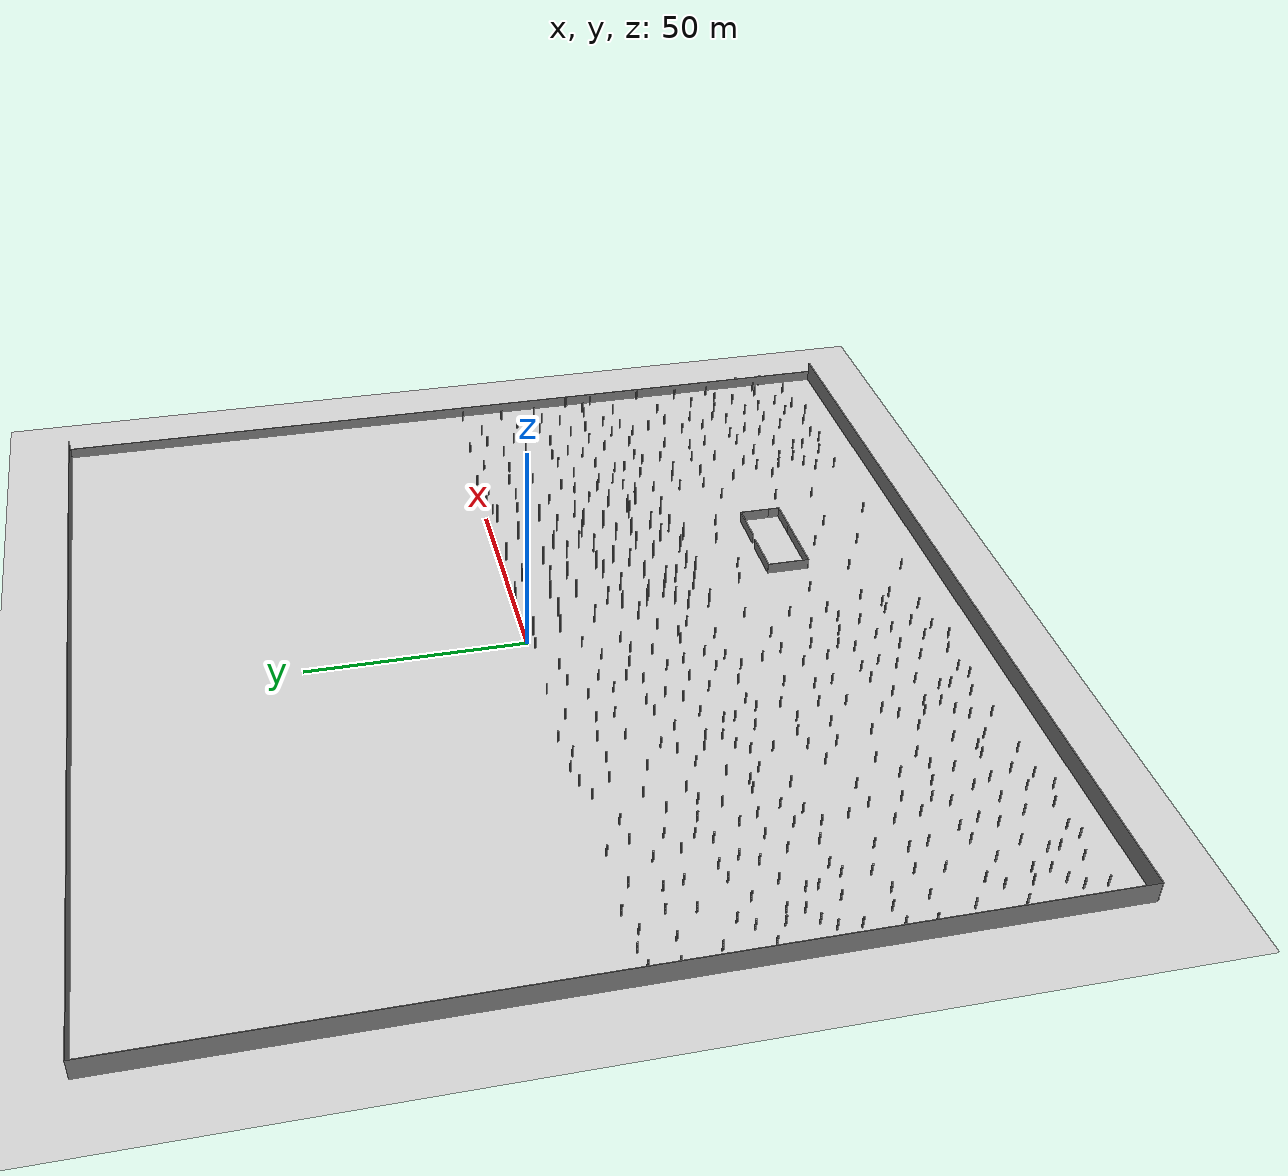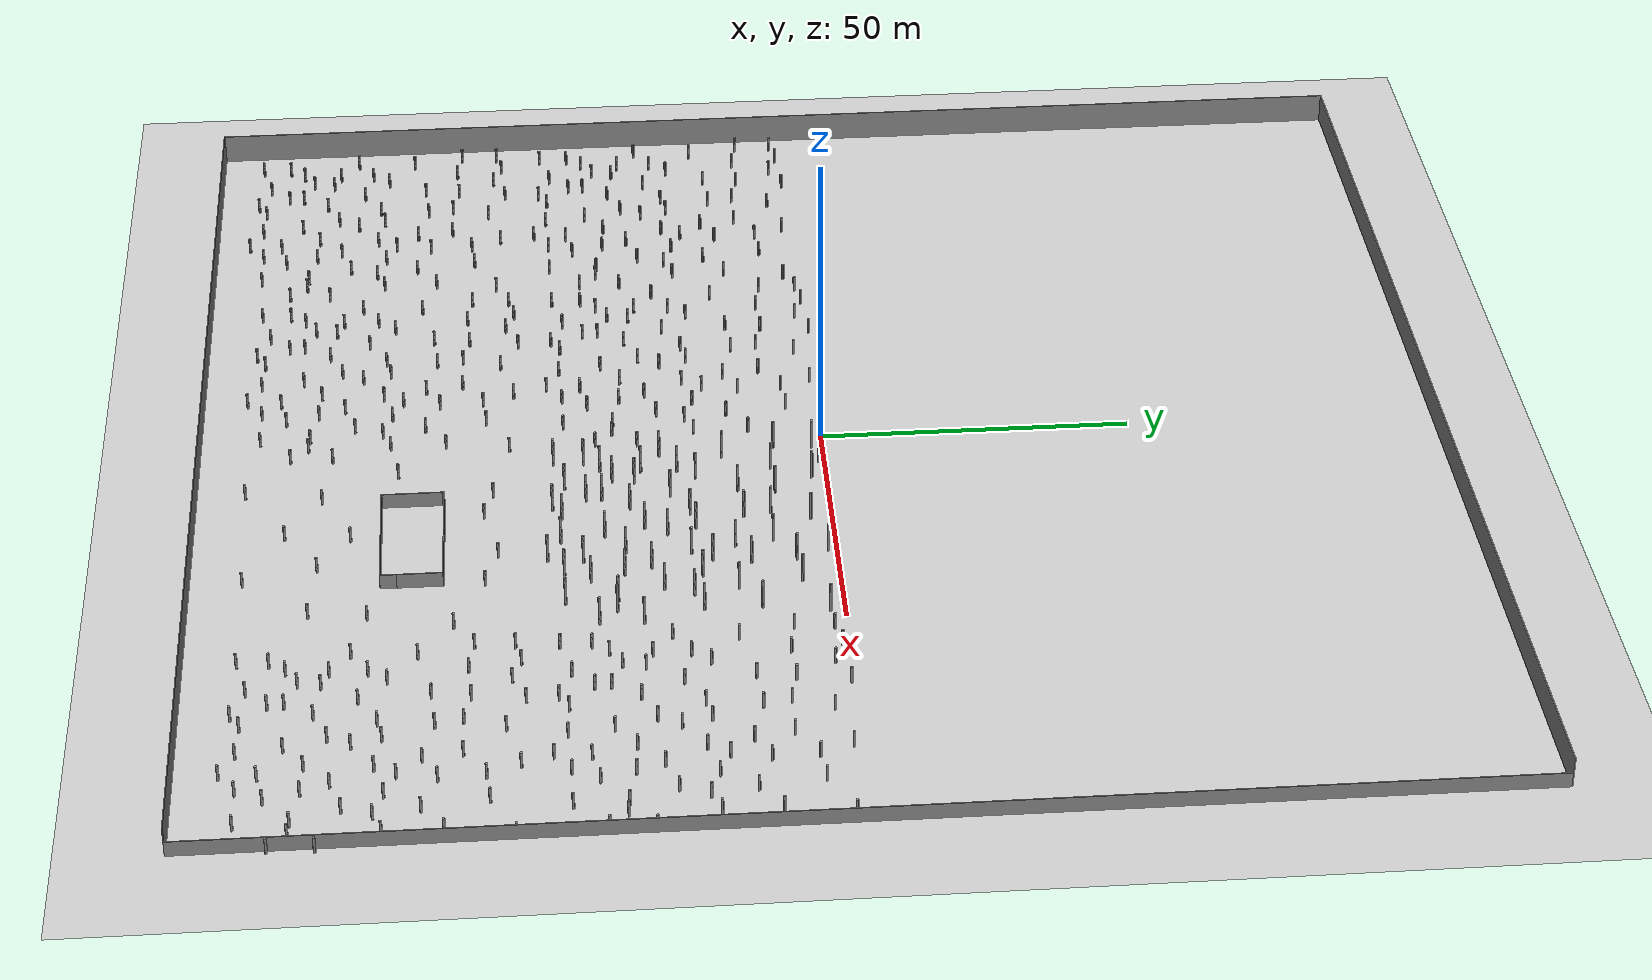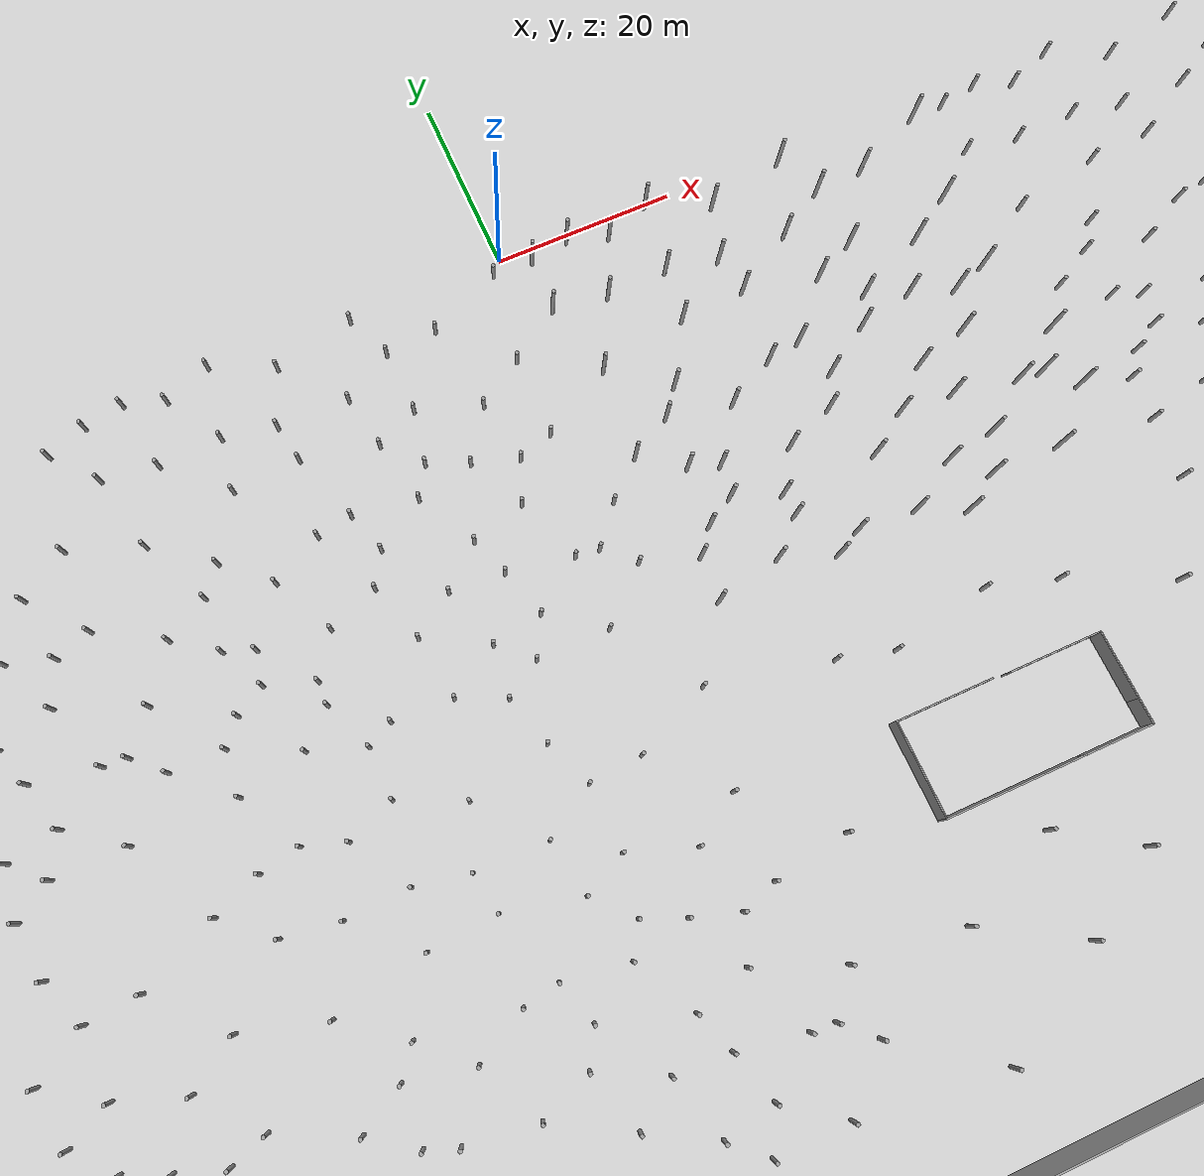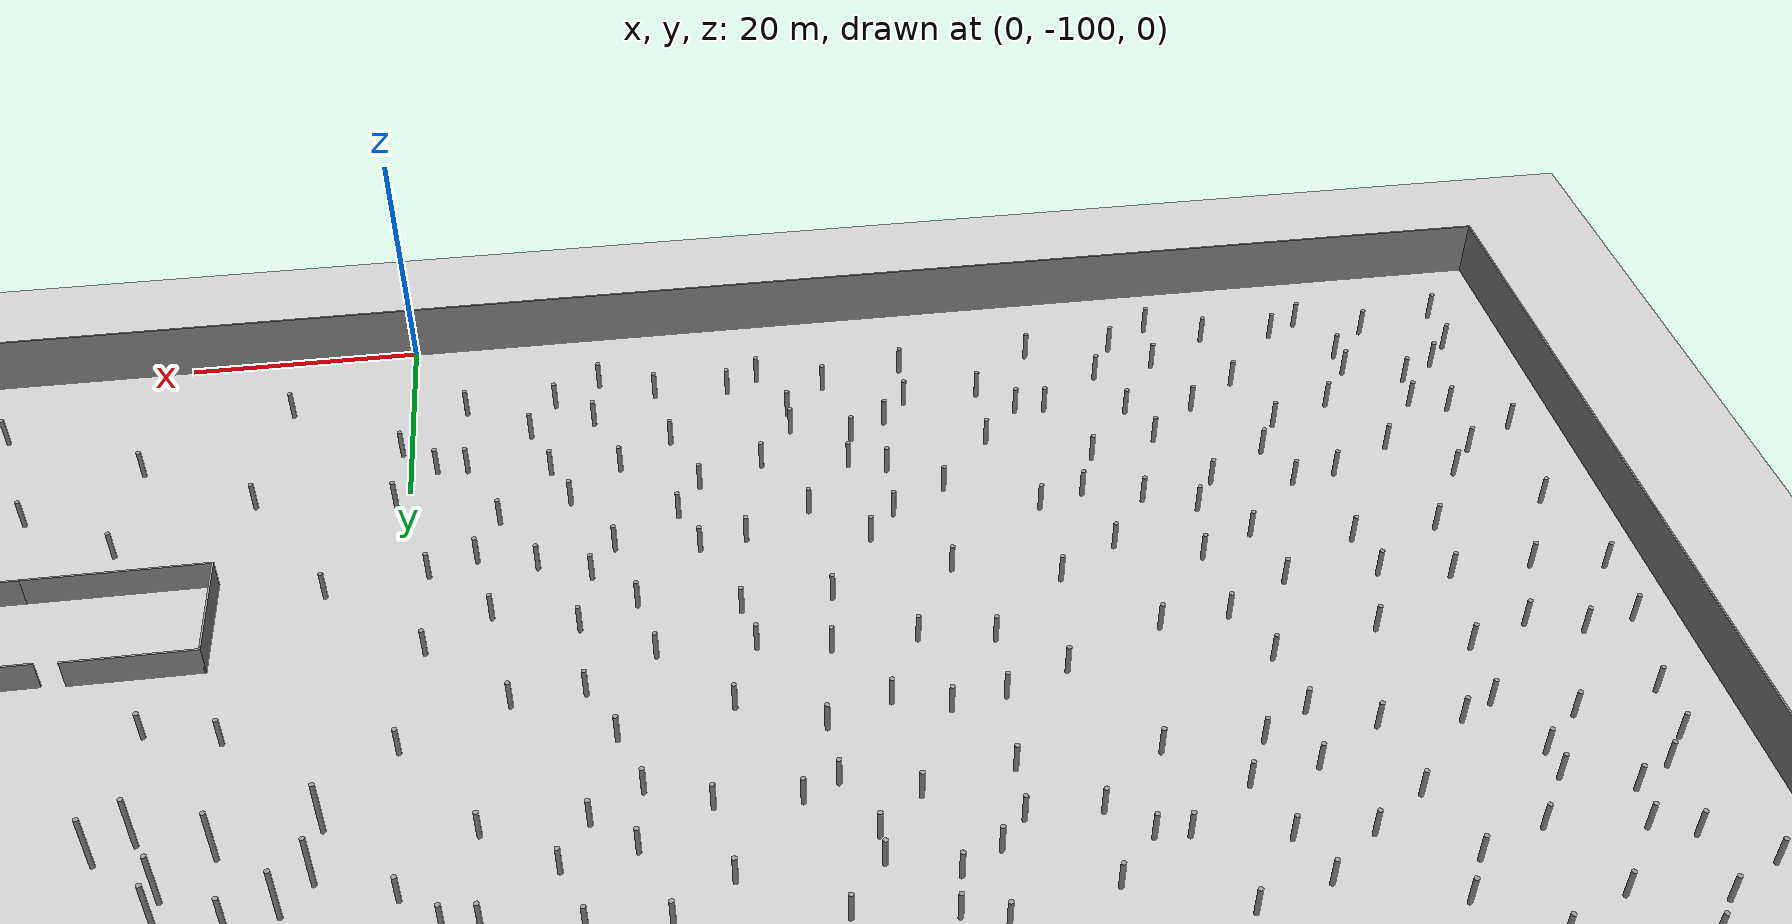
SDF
<sdf version="1.6">
 <world name="default">
  <light name="sun" type="directional">
   <pose>0 0 10 0 -0 0</pose>
   <diffuse>0.8 0.8 0.8 1</diffuse>
   <specular>0.2 0.2 0.2 1</specular>
   <attenuation>
    <range>1000</range>
    <constant>0.9</constant>
    <linear>0.01</linear>
    <quadratic>0.001</quadratic>
   </attenuation>
   <direction>-0.5 0.1 -0.9</direction>
  </light>
  <gravity>0 0 -9.8</gravity>
  <magnetic_field>6e-06 2.3e-05 -4.2e-05</magnetic_field>
  <atmosphere type="adiabatic"/>
  <physics name="default_physics" default="0" type="ode">
   <max_step_size>0.001</max_step_size>
   <real_time_factor>1</real_time_factor>
   <real_time_update_rate>1000</real_time_update_rate>
  </physics>
  <scene><ambient>0.4 0.4 0.4 1</ambient><background>0.7 0.7 0.7 1</background><shadows>1</shadows></scene>
  <audio><device>default</device></audio>
  <spherical_coordinates>
   <surface_model>EARTH_WGS84</surface_model>
   <latitude_deg>0</latitude_deg>
   <longitude_deg>0</longitude_deg>
   <elevation>0</elevation>
   <heading_deg>0</heading_deg>
  </spherical_coordinates>
  <model name="ground_plane">
   <static>1</static>
   <link name="link">
    <collision name="collision">
     <geometry><plane><normal>0 0 1</normal><size>100 100</size></plane></geometry>
     <surface><friction><ode><mu>100</mu><mu2>50</mu2></ode></friction></surface>
    </collision>
    <visual name="visual">
     <cast_shadows>0</cast_shadows>
     <geometry><plane><normal>0 0 1</normal><size>100 100</size></plane></geometry>
     <material>
      <script><uri>file://media/materials/scripts/gazebo.material</uri><name>Gazebo/Grey</name></script>
     </material>
    </visual>
   </link>
  </model>
  <model name="new_200">
   <link name="Wall_0">
    <pose>0 -100 0 0 -0 0</pose>
    <visual name="Wall_0_Visual">
     <pose>0 0 2.5 0 -0 0</pose>
     <geometry><box><size>200.15 0.15 5</size></box></geometry>
     <material>
      <script><uri>file://media/materials/scripts/gazebo.material</uri><name>Gazebo/Grey</name></script>
      <ambient>1 1 1 1</ambient>
     </material>
     <meta><layer>0</layer></meta>
    </visual>
    <collision name="Wall_0_Collision">
     <pose>0 0 2.5 0 -0 0</pose>
     <geometry><box><size>200.15 0.15 5</size></box></geometry>
     <surface>
      <friction>
       <ode><mu>1</mu><mu2>1</mu2><fdir1>0 0 0</fdir1><slip1>0</slip1><slip2>0</slip2></ode>
       <torsional>
        <coefficient>1</coefficient>
        <patch_radius>0</patch_radius>
        <surface_radius>0</surface_radius>
        <use_patch_radius>1</use_patch_radius>
        <ode><slip>0</slip></ode>
       </torsional>
      </friction>
      <bounce><restitution_coefficient>0</restitution_coefficient><threshold>1e+06</threshold></bounce>
      <contact>
       <collide_without_contact>0</collide_without_contact>
       <collide_without_contact_bitmask>1</collide_without_contact_bitmask>
       <collide_bitmask>1</collide_bitmask>
       <ode>
        <soft_cfm>0</soft_cfm>
        <soft_erp>0.2</soft_erp>
        <kp>1e+13</kp>
        <kd>1</kd>
        <max_vel>0.01</max_vel>
        <min_depth>0</min_depth>
       </ode>
       <bullet>
        <split_impulse>1</split_impulse>
        <split_impulse_penetration_threshold>-0.01</split_impulse_penetration_threshold>
        <soft_cfm>0</soft_cfm>
        <soft_erp>0.2</soft_erp>
        <kp>1e+13</kp>
        <kd>1</kd>
       </bullet>
      </contact>
     </surface>
    </collision>
   </link>
   <link name="Wall_2">
    <pose>-100 0 0 0 -0 1.5708</pose>
    <visual name="Wall_2_Visual">
     <pose>0 0 2.5 0 -0 0</pose>
     <geometry><box><size>200.15 0.15 5</size></box></geometry>
     <material>
      <script><uri>file://media/materials/scripts/gazebo.material</uri><name>Gazebo/Grey</name></script>
      <ambient>1 1 1 1</ambient>
     </material>
     <meta><layer>0</layer></meta>
    </visual>
    <collision name="Wall_2_Collision">
     <pose>0 0 2.5 0 -0 0</pose>
     <geometry><box><size>200.15 0.15 5</size></box></geometry>
     <surface>
      <friction>
       <ode><mu>1</mu><mu2>1</mu2><fdir1>0 0 0</fdir1><slip1>0</slip1><slip2>0</slip2></ode>
       <torsional>
        <coefficient>1</coefficient>
        <patch_radius>0</patch_radius>
        <surface_radius>0</surface_radius>
        <use_patch_radius>1</use_patch_radius>
        <ode><slip>0</slip></ode>
       </torsional>
      </friction>
      <bounce><restitution_coefficient>0</restitution_coefficient><threshold>1e+06</threshold></bounce>
      <contact>
       <collide_without_contact>0</collide_without_contact>
       <collide_without_contact_bitmask>1</collide_without_contact_bitmask>
       <collide_bitmask>1</collide_bitmask>
       <ode>
        <soft_cfm>0</soft_cfm>
        <soft_erp>0.2</soft_erp>
        <kp>1e+13</kp>
        <kd>1</kd>
        <max_vel>0.01</max_vel>
        <min_depth>0</min_depth>
       </ode>
       <bullet>
        <split_impulse>1</split_impulse>
        <split_impulse_penetration_threshold>-0.01</split_impulse_penetration_threshold>
        <soft_cfm>0</soft_cfm>
        <soft_erp>0.2</soft_erp>
        <kp>1e+13</kp>
        <kd>1</kd>
       </bullet>
      </contact>
     </surface>
    </collision>
   </link>
   <link name="Wall_4">
    <pose>0 100 0 0 -0 0</pose>
    <visual name="Wall_4_Visual">
     <pose>0 0 2.5 0 -0 0</pose>
     <geometry><box><size>200.15 0.15 5</size></box></geometry>
     <material>
      <script><uri>file://media/materials/scripts/gazebo.material</uri><name>Gazebo/Grey</name></script>
      <ambient>1 1 1 1</ambient>
     </material>
     <meta><layer>0</layer></meta>
    </visual>
    <collision name="Wall_4_Collision">
     <pose>0 0 2.5 0 -0 0</pose>
     <geometry><box><size>200.15 0.15 5</size></box></geometry>
     <surface>
      <friction>
       <ode><mu>1</mu><mu2>1</mu2><fdir1>0 0 0</fdir1><slip1>0</slip1><slip2>0</slip2></ode>
       <torsional>
        <coefficient>1</coefficient>
        <patch_radius>0</patch_radius>
        <surface_radius>0</surface_radius>
        <use_patch_radius>1</use_patch_radius>
        <ode><slip>0</slip></ode>
       </torsional>
      </friction>
      <bounce><restitution_coefficient>0</restitution_coefficient><threshold>1e+06</threshold></bounce>
      <contact>
       <collide_without_contact>0</collide_without_contact>
       <collide_without_contact_bitmask>1</collide_without_contact_bitmask>
       <collide_bitmask>1</collide_bitmask>
       <ode>
        <soft_cfm>0</soft_cfm>
        <soft_erp>0.2</soft_erp>
        <kp>1e+13</kp>
        <kd>1</kd>
        <max_vel>0.01</max_vel>
        <min_depth>0</min_depth>
       </ode>
       <bullet>
        <split_impulse>1</split_impulse>
        <split_impulse_penetration_threshold>-0.01</split_impulse_penetration_threshold>
        <soft_cfm>0</soft_cfm>
        <soft_erp>0.2</soft_erp>
        <kp>1e+13</kp>
        <kd>1</kd>
       </bullet>
      </contact>
     </surface>
    </collision>
   </link>
   <link name="Wall_6">
    <pose>100 0 0 0 -0 1.5708</pose>
    <visual name="Wall_6_Visual">
     <pose>0 0 1.25 0 -0 0</pose>
     <geometry><box><size>200.15 0.15 2.5</size></box></geometry>
     <material>
      <script><uri>file://media/materials/scripts/gazebo.material</uri><name>Gazebo/Grey</name></script>
      <ambient>1 1 1 1</ambient>
     </material>
     <meta><layer>0</layer></meta>
    </visual>
    <collision name="Wall_6_Collision">
     <pose>0 0 1.25 0 -0 0</pose>
     <geometry><box><size>200.15 0.15 2.5</size></box></geometry>
     <surface>
      <friction>
       <ode><mu>1</mu><mu2>1</mu2><fdir1>0 0 0</fdir1><slip1>0</slip1><slip2>0</slip2></ode>
       <torsional>
        <coefficient>1</coefficient>
        <patch_radius>0</patch_radius>
        <surface_radius>0</surface_radius>
        <use_patch_radius>1</use_patch_radius>
        <ode><slip>0</slip></ode>
       </torsional>
      </friction>
      <bounce><restitution_coefficient>0</restitution_coefficient><threshold>1e+06</threshold></bounce>
      <contact>
       <collide_without_contact>0</collide_without_contact>
       <collide_without_contact_bitmask>1</collide_without_contact_bitmask>
       <collide_bitmask>1</collide_bitmask>
       <ode>
        <soft_cfm>0</soft_cfm>
        <soft_erp>0.2</soft_erp>
        <kp>1e+13</kp>
        <kd>1</kd>
        <max_vel>0.01</max_vel>
        <min_depth>0</min_depth>
       </ode>
       <bullet>
        <split_impulse>1</split_impulse>
        <split_impulse_penetration_threshold>-0.01</split_impulse_penetration_threshold>
        <soft_cfm>0</soft_cfm>
        <soft_erp>0.2</soft_erp>
        <kp>1e+13</kp>
        <kd>1</kd>
       </bullet>
      </contact>
     </surface>
    </collision>
   </link>
   <static>1</static>
   <pose>0.019847 -0.000436 0 0 -0 0</pose>
  </model>
  <model name="empty_pillars_7">
   <link name="link">
    <inertial>
     <mass>1</mass>
     <inertia><ixx>0.145833</ixx><ixy>0</ixy><ixz>0</ixz><iyy>0.145833</iyy><iyz>0</iyz><izz>0.125</izz></inertia>
    </inertial>
    <visual name="visual">
     <geometry><cylinder><radius>0.2</radius><length>5</length></cylinder></geometry>
     <material>
      <script><name>Gazebo/Grey</name><uri>file://media/materials/scripts/gazebo.material</uri></script>
      <shader type="vertex"><normal_map>__default__</normal_map></shader>
      <ambient>0.3 0.3 0.3 1</ambient>
      <diffuse>0.7 0.7 0.7 1</diffuse>
      <specular>0.01 0.01 0.01 1</specular>
      <emissive>0 0 0 1</emissive>
     </material>
    </visual>
    <collision name="collision">
     <geometry><cylinder><radius>0.05</radius><length>5</length></cylinder></geometry>
     <surface>
      <friction>
       <ode><mu>1</mu><mu2>1</mu2><fdir1>0 0 0</fdir1><slip1>0</slip1><slip2>0</slip2></ode>
       <torsional>
        <coefficient>1</coefficient>
        <patch_radius>0</patch_radius>
        <surface_radius>0</surface_radius>
        <use_patch_radius>1</use_patch_radius>
        <ode><slip>0</slip></ode>
       </torsional>
      </friction>
      <bounce><restitution_coefficient>0</restitution_coefficient><threshold>1e+06</threshold></bounce>
      <contact>
       <collide_without_contact>0</collide_without_contact>
       <collide_without_contact_bitmask>1</collide_without_contact_bitmask>
       <collide_bitmask>1</collide_bitmask>
       <ode>
        <soft_cfm>0</soft_cfm>
        <soft_erp>0.2</soft_erp>
        <kp>1e+13</kp>
        <kd>1</kd>
        <max_vel>0.01</max_vel>
        <min_depth>0</min_depth>
       </ode>
       <bullet>
        <split_impulse>1</split_impulse>
        <split_impulse_penetration_threshold>-0.01</split_impulse_penetration_threshold>
        <soft_cfm>0</soft_cfm>
        <soft_erp>0.2</soft_erp>
        <kp>1e+13</kp>
        <kd>1</kd>
       </bullet>
      </contact>
     </surface>
    </collision>
   </link>
   <model name="empty_pillar">
    <link name="link">
     <inertial>
      <mass>1</mass>
      <inertia><ixx>0.145833</ixx><ixy>0</ixy><ixz>0</ixz><iyy>0.145833</iyy><iyz>0</iyz><izz>0.125</izz></inertia>
     </inertial>
     <visual name="visual">
      <geometry><cylinder><radius>0.2</radius><length>5</length></cylinder></geometry>
      <material>
       <script><name>Gazebo/Grey</name><uri>file://media/materials/scripts/gazebo.material</uri></script>
       <shader type="vertex"><normal_map>__default__</normal_map></shader>
       <ambient>0.3 0.3 0.3 1</ambient>
       <diffuse>0.7 0.7 0.7 1</diffuse>
       <specular>0.01 0.01 0.01 1</specular>
       <emissive>0 0 0 1</emissive>
      </material>
     </visual>
     <collision name="collision">
      <geometry><cylinder><radius>0.05</radius><length>5</length></cylinder></geometry>
      <surface>
       <friction>
        <ode><mu>1</mu><mu2>1</mu2><fdir1>0 0 0</fdir1><slip1>0</slip1><slip2>0</slip2></ode>
        <torsional>
         <coefficient>1</coefficient>
         <patch_radius>0</patch_radius>
         <surface_radius>0</surface_radius>
         <use_patch_radius>1</use_patch_radius>
         <ode><slip>0</slip></ode>
        </torsional>
       </friction>
       <bounce><restitution_coefficient>0</restitution_coefficient><threshold>1e+06</threshold></bounce>
       <contact>
        <collide_without_contact>0</collide_without_contact>
        <collide_without_contact_bitmask>1</collide_without_contact_bitmask>
        <collide_bitmask>1</collide_bitmask>
        <ode>
         <soft_cfm>0</soft_cfm>
         <soft_erp>0.2</soft_erp>
         <kp>1e+13</kp>
         <kd>1</kd>
         <max_vel>0.01</max_vel>
         <min_depth>0</min_depth>
        </ode>
        <bullet>
         <split_impulse>1</split_impulse>
         <split_impulse_penetration_threshold>-0.01</split_impulse_penetration_threshold>
         <soft_cfm>0</soft_cfm>
         <soft_erp>0.2</soft_erp>
         <kp>1e+13</kp>
         <kd>1</kd>
        </bullet>
       </contact>
      </surface>
     </collision>
    </link>
    <static>0</static>
    <pose>-3.84527 -0.717439 0 0 -0 0</pose>
   </model>
   <model name="empty_pillar_clone">
    <link name="link">
     <inertial>
      <mass>1</mass>
      <inertia><ixx>0.145833</ixx><ixy>0</ixy><ixz>0</ixz><iyy>0.145833</iyy><iyz>0</iyz><izz>0.125</izz></inertia>
     </inertial>
     <visual name="visual">
      <geometry><cylinder><radius>0.2</radius><length>5</length></cylinder></geometry>
      <material>
       <script><name>Gazebo/Grey</name><uri>file://media/materials/scripts/gazebo.material</uri></script>
       <shader type="vertex"><normal_map>__default__</normal_map></shader>
       <ambient>0.3 0.3 0.3 1</ambient>
       <diffuse>0.7 0.7 0.7 1</diffuse>
       <specular>0.01 0.01 0.01 1</specular>
       <emissive>0 0 0 1</emissive>
      </material>
     </visual>
     <collision name="collision">
      <geometry><cylinder><radius>0.05</radius><length>5</length></cylinder></geometry>
      <surface>
       <friction>
        <ode><mu>1</mu><mu2>1</mu2><fdir1>0 0 0</fdir1><slip1>0</slip1><slip2>0</slip2></ode>
        <torsional>
         <coefficient>1</coefficient>
         <patch_radius>0</patch_radius>
         <surface_radius>0</surface_radius>
         <use_patch_radius>1</use_patch_radius>
         <ode><slip>0</slip></ode>
        </torsional>
       </friction>
       <bounce><restitution_coefficient>0</restitution_coefficient><threshold>1e+06</threshold></bounce>
       <contact>
        <collide_without_contact>0</collide_without_contact>
        <collide_without_contact_bitmask>1</collide_without_contact_bitmask>
        <collide_bitmask>1</collide_bitmask>
        <ode>
         <soft_cfm>0</soft_cfm>
         <soft_erp>0.2</soft_erp>
         <kp>1e+13</kp>
         <kd>1</kd>
         <max_vel>0.01</max_vel>
         <min_depth>0</min_depth>
        </ode>
        <bullet>
         <split_impulse>1</split_impulse>
         <split_impulse_penetration_threshold>-0.01</split_impulse_penetration_threshold>
         <soft_cfm>0</soft_cfm>
         <soft_erp>0.2</soft_erp>
         <kp>1e+13</kp>
         <kd>1</kd>
        </bullet>
       </contact>
      </surface>
     </collision>
    </link>
    <static>0</static>
    <pose>1.47843 -4.49529 0 0 -0 0</pose>
   </model>
   <model name="empty_pillar_clone_0">
    <link name="link">
     <inertial>
      <mass>1</mass>
      <inertia><ixx>0.145833</ixx><ixy>0</ixy><ixz>0</ixz><iyy>0.145833</iyy><iyz>0</iyz><izz>0.125</izz></inertia>
     </inertial>
     <visual name="visual">
      <geometry><cylinder><radius>0.2</radius><length>5</length></cylinder></geometry>
      <material>
       <script><name>Gazebo/Grey</name><uri>file://media/materials/scripts/gazebo.material</uri></script>
       <shader type="vertex"><normal_map>__default__</normal_map></shader>
       <ambient>0.3 0.3 0.3 1</ambient>
       <diffuse>0.7 0.7 0.7 1</diffuse>
       <specular>0.01 0.01 0.01 1</specular>
       <emissive>0 0 0 1</emissive>
      </material>
     </visual>
     <collision name="collision">
      <geometry><cylinder><radius>0.05</radius><length>5</length></cylinder></geometry>
      <surface>
       <friction>
        <ode><mu>1</mu><mu2>1</mu2><fdir1>0 0 0</fdir1><slip1>0</slip1><slip2>0</slip2></ode>
        <torsional>
         <coefficient>1</coefficient>
         <patch_radius>0</patch_radius>
         <surface_radius>0</surface_radius>
         <use_patch_radius>1</use_patch_radius>
         <ode><slip>0</slip></ode>
        </torsional>
       </friction>
       <bounce><restitution_coefficient>0</restitution_coefficient><threshold>1e+06</threshold></bounce>
       <contact>
        <collide_without_contact>0</collide_without_contact>
        <collide_without_contact_bitmask>1</collide_without_contact_bitmask>
        <collide_bitmask>1</collide_bitmask>
        <ode>
         <soft_cfm>0</soft_cfm>
         <soft_erp>0.2</soft_erp>
         <kp>1e+13</kp>
         <kd>1</kd>
         <max_vel>0.01</max_vel>
         <min_depth>0</min_depth>
        </ode>
        <bullet>
         <split_impulse>1</split_impulse>
         <split_impulse_penetration_threshold>-0.01</split_impulse_penetration_threshold>
         <soft_cfm>0</soft_cfm>
         <soft_erp>0.2</soft_erp>
         <kp>1e+13</kp>
         <kd>1</kd>
        </bullet>
       </contact>
      </surface>
     </collision>
    </link>
    <static>0</static>
    <pose>10.3453 -7.35986 0 0 -0 0</pose>
   </model>
   <model name="empty_pillar_clone_1">
    <link name="link">
     <inertial>
      <mass>1</mass>
      <inertia><ixx>0.145833</ixx><ixy>0</ixy><ixz>0</ixz><iyy>0.145833</iyy><iyz>0</iyz><izz>0.125</izz></inertia>
     </inertial>
     <visual name="visual">
      <geometry><cylinder><radius>0.2</radius><length>5</length></cylinder></geometry>
      <material>
       <script><name>Gazebo/Grey</name><uri>file://media/materials/scripts/gazebo.material</uri></script>
       <shader type="vertex"><normal_map>__default__</normal_map></shader>
       <ambient>0.3 0.3 0.3 1</ambient>
       <diffuse>0.7 0.7 0.7 1</diffuse>
       <specular>0.01 0.01 0.01 1</specular>
       <emissive>0 0 0 1</emissive>
      </material>
     </visual>
     <collision name="collision">
      <geometry><cylinder><radius>0.05</radius><length>5</length></cylinder></geometry>
      <surface>
       <friction>
        <ode><mu>1</mu><mu2>1</mu2><fdir1>0 0 0</fdir1><slip1>0</slip1><slip2>0</slip2></ode>
        <torsional>
         <coefficient>1</coefficient>
         <patch_radius>0</patch_radius>
         <surface_radius>0</surface_radius>
         <use_patch_radius>1</use_patch_radius>
         <ode><slip>0</slip></ode>
        </torsional>
       </friction>
       <bounce><restitution_coefficient>0</restitution_coefficient><threshold>1e+06</threshold></bounce>
       <contact>
        <collide_without_contact>0</collide_without_contact>
        <collide_without_contact_bitmask>1</collide_without_contact_bitmask>
        <collide_bitmask>1</collide_bitmask>
        <ode>
         <soft_cfm>0</soft_cfm>
         <soft_erp>0.2</soft_erp>
         <kp>1e+13</kp>
         <kd>1</kd>
         <max_vel>0.01</max_vel>
         <min_depth>0</min_depth>
        </ode>
        <bullet>
         <split_impulse>1</split_impulse>
         <split_impulse_penetration_threshold>-0.01</split_impulse_penetration_threshold>
         <soft_cfm>0</soft_cfm>
         <soft_erp>0.2</soft_erp>
         <kp>1e+13</kp>
         <kd>1</kd>
        </bullet>
       </contact>
      </surface>
     </collision>
    </link>
    <static>0</static>
    <pose>8.92248 2.14838 0 0 -0 0</pose>
   </model>
   <model name="empty_pillar_clone_10">
    <link name="link">
     <inertial>
      <mass>1</mass>
      <inertia><ixx>0.145833</ixx><ixy>0</ixy><ixz>0</ixz><iyy>0.145833</iyy><iyz>0</iyz><izz>0.125</izz></inertia>
     </inertial>
     <visual name="visual">
      <geometry><cylinder><radius>0.2</radius><length>5</length></cylinder></geometry>
      <material>
       <script><name>Gazebo/Grey</name><uri>file://media/materials/scripts/gazebo.material</uri></script>
       <shader type="vertex"><normal_map>__default__</normal_map></shader>
       <ambient>0.3 0.3 0.3 1</ambient>
       <diffuse>0.7 0.7 0.7 1</diffuse>
       <specular>0.01 0.01 0.01 1</specular>
       <emissive>0 0 0 1</emissive>
      </material>
     </visual>
     <collision name="collision">
      <geometry><cylinder><radius>0.05</radius><length>5</length></cylinder></geometry>
      <surface>
       <friction>
        <ode><mu>1</mu><mu2>1</mu2><fdir1>0 0 0</fdir1><slip1>0</slip1><slip2>0</slip2></ode>
        <torsional>
         <coefficient>1</coefficient>
         <patch_radius>0</patch_radius>
         <surface_radius>0</surface_radius>
         <use_patch_radius>1</use_patch_radius>
         <ode><slip>0</slip></ode>
        </torsional>
       </friction>
       <bounce><restitution_coefficient>0</restitution_coefficient><threshold>1e+06</threshold></bounce>
       <contact>
        <collide_without_contact>0</collide_without_contact>
        <collide_without_contact_bitmask>1</collide_without_contact_bitmask>
        <collide_bitmask>1</collide_bitmask>
        <ode>
         <soft_cfm>0</soft_cfm>
         <soft_erp>0.2</soft_erp>
         <kp>1e+13</kp>
         <kd>1</kd>
         <max_vel>0.01</max_vel>
         <min_depth>0</min_depth>
        </ode>
        <bullet>
         <split_impulse>1</split_impulse>
         <split_impulse_penetration_threshold>-0.01</split_impulse_penetration_threshold>
         <soft_cfm>0</soft_cfm>
         <soft_erp>0.2</soft_erp>
         <kp>1e+13</kp>
         <kd>1</kd>
        </bullet>
       </contact>
      </surface>
     </collision>
    </link>
    <static>0</static>
    <pose>13.5083 -16.8403 0 0 -0 0</pose>
   </model>
   <model name="empty_pillar_clone_11">
    <link name="link">
     <inertial>
      <mass>1</mass>
      <inertia><ixx>0.145833</ixx><ixy>0</ixy><ixz>0</ixz><iyy>0.145833</iyy><iyz>0</iyz><izz>0.125</izz></inertia>
     </inertial>
     <visual name="visual">
      <geometry><cylinder><radius>0.2</radius><length>5</length></cylinder></geometry>
      <material>
       <script><name>Gazebo/Grey</name><uri>file://media/materials/scripts/gazebo.material</uri></script>
       <shader type="vertex"><normal_map>__default__</normal_map></shader>
       <ambient>0.3 0.3 0.3 1</ambient>
       <diffuse>0.7 0.7 0.7 1</diffuse>
       <specular>0.01 0.01 0.01 1</specular>
       <emissive>0 0 0 1</emissive>
      </material>
     </visual>
     <collision name="collision">
      <geometry><cylinder><radius>0.05</radius><length>5</length></cylinder></geometry>
      <surface>
       <friction>
        <ode><mu>1</mu><mu2>1</mu2><fdir1>0 0 0</fdir1><slip1>0</slip1><slip2>0</slip2></ode>
        <torsional>
         <coefficient>1</coefficient>
         <patch_radius>0</patch_radius>
         <surface_radius>0</surface_radius>
         <use_patch_radius>1</use_patch_radius>
         <ode><slip>0</slip></ode>
        </torsional>
       </friction>
       <bounce><restitution_coefficient>0</restitution_coefficient><threshold>1e+06</threshold></bounce>
       <contact>
        <collide_without_contact>0</collide_without_contact>
        <collide_without_contact_bitmask>1</collide_without_contact_bitmask>
        <collide_bitmask>1</collide_bitmask>
        <ode>
         <soft_cfm>0</soft_cfm>
         <soft_erp>0.2</soft_erp>
         <kp>1e+13</kp>
         <kd>1</kd>
         <max_vel>0.01</max_vel>
         <min_depth>0</min_depth>
        </ode>
        <bullet>
         <split_impulse>1</split_impulse>
         <split_impulse_penetration_threshold>-0.01</split_impulse_penetration_threshold>
         <soft_cfm>0</soft_cfm>
         <soft_erp>0.2</soft_erp>
         <kp>1e+13</kp>
         <kd>1</kd>
        </bullet>
       </contact>
      </surface>
     </collision>
    </link>
    <static>0</static>
    <pose>7.98536 -17.8403 0 0 -0 0</pose>
   </model>
   <model name="empty_pillar_clone_12">
    <link name="link">
     <inertial>
      <mass>1</mass>
      <inertia><ixx>0.145833</ixx><ixy>0</ixy><ixz>0</ixz><iyy>0.145833</iyy><iyz>0</iyz><izz>0.125</izz></inertia>
     </inertial>
     <visual name="visual">
      <geometry><cylinder><radius>0.2</radius><length>5</length></cylinder></geometry>
      <material>
       <script><name>Gazebo/Grey</name><uri>file://media/materials/scripts/gazebo.material</uri></script>
       <shader type="vertex"><normal_map>__default__</normal_map></shader>
       <ambient>0.3 0.3 0.3 1</ambient>
       <diffuse>0.7 0.7 0.7 1</diffuse>
       <specular>0.01 0.01 0.01 1</specular>
       <emissive>0 0 0 1</emissive>
      </material>
     </visual>
     <collision name="collision">
      <geometry><cylinder><radius>0.05</radius><length>5</length></cylinder></geometry>
      <surface>
       <friction>
        <ode><mu>1</mu><mu2>1</mu2><fdir1>0 0 0</fdir1><slip1>0</slip1><slip2>0</slip2></ode>
        <torsional>
         <coefficient>1</coefficient>
         <patch_radius>0</patch_radius>
         <surface_radius>0</surface_radius>
         <use_patch_radius>1</use_patch_radius>
         <ode><slip>0</slip></ode>
        </torsional>
       </friction>
       <bounce><restitution_coefficient>0</restitution_coefficient><threshold>1e+06</threshold></bounce>
       <contact>
        <collide_without_contact>0</collide_without_contact>
        <collide_without_contact_bitmask>1</collide_without_contact_bitmask>
        <collide_bitmask>1</collide_bitmask>
        <ode>
         <soft_cfm>0</soft_cfm>
         <soft_erp>0.2</soft_erp>
         <kp>1e+13</kp>
         <kd>1</kd>
         <max_vel>0.01</max_vel>
         <min_depth>0</min_depth>
        </ode>
        <bullet>
         <split_impulse>1</split_impulse>
         <split_impulse_penetration_threshold>-0.01</split_impulse_penetration_threshold>
         <soft_cfm>0</soft_cfm>
         <soft_erp>0.2</soft_erp>
         <kp>1e+13</kp>
         <kd>1</kd>
        </bullet>
       </contact>
      </surface>
     </collision>
    </link>
    <static>0</static>
    <pose>-4.01464 -20.8403 0 0 -0 0</pose>
   </model>
   <model name="empty_pillar_clone_13">
    <link name="link">
     <inertial>
      <mass>1</mass>
      <inertia><ixx>0.145833</ixx><ixy>0</ixy><ixz>0</ixz><iyy>0.145833</iyy><iyz>0</iyz><izz>0.125</izz></inertia>
     </inertial>
     <visual name="visual">
      <geometry><cylinder><radius>0.2</radius><length>5</length></cylinder></geometry>
      <material>
       <script><name>Gazebo/Grey</name><uri>file://media/materials/scripts/gazebo.material</uri></script>
       <shader type="vertex"><normal_map>__default__</normal_map></shader>
       <ambient>0.3 0.3 0.3 1</ambient>
       <diffuse>0.7 0.7 0.7 1</diffuse>
       <specular>0.01 0.01 0.01 1</specular>
       <emissive>0 0 0 1</emissive>
      </material>
     </visual>
     <collision name="collision">
      <geometry><cylinder><radius>0.05</radius><length>5</length></cylinder></geometry>
      <surface>
       <friction>
        <ode><mu>1</mu><mu2>1</mu2><fdir1>0 0 0</fdir1><slip1>0</slip1><slip2>0</slip2></ode>
        <torsional>
         <coefficient>1</coefficient>
         <patch_radius>0</patch_radius>
         <surface_radius>0</surface_radius>
         <use_patch_radius>1</use_patch_radius>
         <ode><slip>0</slip></ode>
        </torsional>
       </friction>
       <bounce><restitution_coefficient>0</restitution_coefficient><threshold>1e+06</threshold></bounce>
       <contact>
        <collide_without_contact>0</collide_without_contact>
        <collide_without_contact_bitmask>1</collide_without_contact_bitmask>
        <collide_bitmask>1</collide_bitmask>
        <ode>
         <soft_cfm>0</soft_cfm>
         <soft_erp>0.2</soft_erp>
         <kp>1e+13</kp>
         <kd>1</kd>
         <max_vel>0.01</max_vel>
         <min_depth>0</min_depth>
        </ode>
        <bullet>
         <split_impulse>1</split_impulse>
         <split_impulse_penetration_threshold>-0.01</split_impulse_penetration_threshold>
         <soft_cfm>0</soft_cfm>
         <soft_erp>0.2</soft_erp>
         <kp>1e+13</kp>
         <kd>1</kd>
        </bullet>
       </contact>
      </surface>
     </collision>
    </link>
    <static>0</static>
    <pose>-9.01464 -14.4259 0 0 -0 0</pose>
   </model>
   <model name="empty_pillar_clone_14">
    <link name="link">
     <inertial>
      <mass>1</mass>
      <inertia><ixx>0.145833</ixx><ixy>0</ixy><ixz>0</ixz><iyy>0.145833</iyy><iyz>0</iyz><izz>0.125</izz></inertia>
     </inertial>
     <visual name="visual">
      <geometry><cylinder><radius>0.2</radius><length>5</length></cylinder></geometry>
      <material>
       <script><name>Gazebo/Grey</name><uri>file://media/materials/scripts/gazebo.material</uri></script>
       <shader type="vertex"><normal_map>__default__</normal_map></shader>
       <ambient>0.3 0.3 0.3 1</ambient>
       <diffuse>0.7 0.7 0.7 1</diffuse>
       <specular>0.01 0.01 0.01 1</specular>
       <emissive>0 0 0 1</emissive>
      </material>
     </visual>
     <collision name="collision">
      <geometry><cylinder><radius>0.05</radius><length>5</length></cylinder></geometry>
      <surface>
       <friction>
        <ode><mu>1</mu><mu2>1</mu2><fdir1>0 0 0</fdir1><slip1>0</slip1><slip2>0</slip2></ode>
        <torsional>
         <coefficient>1</coefficient>
         <patch_radius>0</patch_radius>
         <surface_radius>0</surface_radius>
         <use_patch_radius>1</use_patch_radius>
         <ode><slip>0</slip></ode>
        </torsional>
       </friction>
       <bounce><restitution_coefficient>0</restitution_coefficient><threshold>1e+06</threshold></bounce>
       <contact>
        <collide_without_contact>0</collide_without_contact>
        <collide_without_contact_bitmask>1</collide_without_contact_bitmask>
        <collide_bitmask>1</collide_bitmask>
        <ode>
         <soft_cfm>0</soft_cfm>
         <soft_erp>0.2</soft_erp>
         <kp>1e+13</kp>
         <kd>1</kd>
         <max_vel>0.01</max_vel>
         <min_depth>0</min_depth>
        </ode>
        <bullet>
         <split_impulse>1</split_impulse>
         <split_impulse_penetration_threshold>-0.01</split_impulse_penetration_threshold>
         <soft_cfm>0</soft_cfm>
         <soft_erp>0.2</soft_erp>
         <kp>1e+13</kp>
         <kd>1</kd>
        </bullet>
       </contact>
      </surface>
     </collision>
    </link>
    <static>0</static>
    <pose>-14.0146 0.646152 0 0 -0 0</pose>
   </model>
   <model name="empty_pillar_clone_15">
    <link name="link">
     <inertial>
      <mass>1</mass>
      <inertia><ixx>0.145833</ixx><ixy>0</ixy><ixz>0</ixz><iyy>0.145833</iyy><iyz>0</iyz><izz>0.125</izz></inertia>
     </inertial>
     <visual name="visual">
      <geometry><cylinder><radius>0.2</radius><length>5</length></cylinder></geometry>
      <material>
       <script><name>Gazebo/Grey</name><uri>file://media/materials/scripts/gazebo.material</uri></script>
       <shader type="vertex"><normal_map>__default__</normal_map></shader>
       <ambient>0.3 0.3 0.3 1</ambient>
       <diffuse>0.7 0.7 0.7 1</diffuse>
       <specular>0.01 0.01 0.01 1</specular>
       <emissive>0 0 0 1</emissive>
      </material>
     </visual>
     <collision name="collision">
      <geometry><cylinder><radius>0.05</radius><length>5</length></cylinder></geometry>
      <surface>
       <friction>
        <ode><mu>1</mu><mu2>1</mu2><fdir1>0 0 0</fdir1><slip1>0</slip1><slip2>0</slip2></ode>
        <torsional>
         <coefficient>1</coefficient>
         <patch_radius>0</patch_radius>
         <surface_radius>0</surface_radius>
         <use_patch_radius>1</use_patch_radius>
         <ode><slip>0</slip></ode>
        </torsional>
       </friction>
       <bounce><restitution_coefficient>0</restitution_coefficient><threshold>1e+06</threshold></bounce>
       <contact>
        <collide_without_contact>0</collide_without_contact>
        <collide_without_contact_bitmask>1</collide_without_contact_bitmask>
        <collide_bitmask>1</collide_bitmask>
        <ode>
         <soft_cfm>0</soft_cfm>
         <soft_erp>0.2</soft_erp>
         <kp>1e+13</kp>
         <kd>1</kd>
         <max_vel>0.01</max_vel>
         <min_depth>0</min_depth>
        </ode>
        <bullet>
         <split_impulse>1</split_impulse>
         <split_impulse_penetration_threshold>-0.01</split_impulse_penetration_threshold>
         <soft_cfm>0</soft_cfm>
         <soft_erp>0.2</soft_erp>
         <kp>1e+13</kp>
         <kd>1</kd>
        </bullet>
       </contact>
      </surface>
     </collision>
    </link>
    <static>0</static>
    <pose>-9.37193 -3.58732 0 0 -0 0</pose>
   </model>
   <model name="empty_pillar_clone_16">
    <link name="link">
     <inertial>
      <mass>1</mass>
      <inertia><ixx>0.145833</ixx><ixy>0</ixy><ixz>0</ixz><iyy>0.145833</iyy><iyz>0</iyz><izz>0.125</izz></inertia>
     </inertial>
     <visual name="visual">
      <geometry><cylinder><radius>0.2</radius><length>5</length></cylinder></geometry>
      <material>
       <script><name>Gazebo/Grey</name><uri>file://media/materials/scripts/gazebo.material</uri></script>
       <shader type="vertex"><normal_map>__default__</normal_map></shader>
       <ambient>0.3 0.3 0.3 1</ambient>
       <diffuse>0.7 0.7 0.7 1</diffuse>
       <specular>0.01 0.01 0.01 1</specular>
       <emissive>0 0 0 1</emissive>
      </material>
     </visual>
     <collision name="collision">
      <geometry><cylinder><radius>0.05</radius><length>5</length></cylinder></geometry>
      <surface>
       <friction>
        <ode><mu>1</mu><mu2>1</mu2><fdir1>0 0 0</fdir1><slip1>0</slip1><slip2>0</slip2></ode>
        <torsional>
         <coefficient>1</coefficient>
         <patch_radius>0</patch_radius>
         <surface_radius>0</surface_radius>
         <use_patch_radius>1</use_patch_radius>
         <ode><slip>0</slip></ode>
        </torsional>
       </friction>
       <bounce><restitution_coefficient>0</restitution_coefficient><threshold>1e+06</threshold></bounce>
       <contact>
        <collide_without_contact>0</collide_without_contact>
        <collide_without_contact_bitmask>1</collide_without_contact_bitmask>
        <collide_bitmask>1</collide_bitmask>
        <ode>
         <soft_cfm>0</soft_cfm>
         <soft_erp>0.2</soft_erp>
         <kp>1e+13</kp>
         <kd>1</kd>
         <max_vel>0.01</max_vel>
         <min_depth>0</min_depth>
        </ode>
        <bullet>
         <split_impulse>1</split_impulse>
         <split_impulse_penetration_threshold>-0.01</split_impulse_penetration_threshold>
         <soft_cfm>0</soft_cfm>
         <soft_erp>0.2</soft_erp>
         <kp>1e+13</kp>
         <kd>1</kd>
        </bullet>
       </contact>
      </surface>
     </collision>
    </link>
    <static>0</static>
    <pose>-9.20789 13.0504 0 0 -0 0</pose>
   </model>
   <model name="empty_pillar_clone_17">
    <link name="link">
     <inertial>
      <mass>1</mass>
      <inertia><ixx>0.145833</ixx><ixy>0</ixy><ixz>0</ixz><iyy>0.145833</iyy><iyz>0</iyz><izz>0.125</izz></inertia>
     </inertial>
     <visual name="visual">
      <geometry><cylinder><radius>0.2</radius><length>5</length></cylinder></geometry>
      <material>
       <script><name>Gazebo/Grey</name><uri>file://media/materials/scripts/gazebo.material</uri></script>
       <shader type="vertex"><normal_map>__default__</normal_map></shader>
       <ambient>0.3 0.3 0.3 1</ambient>
       <diffuse>0.7 0.7 0.7 1</diffuse>
       <specular>0.01 0.01 0.01 1</specular>
       <emissive>0 0 0 1</emissive>
      </material>
     </visual>
     <collision name="collision">
      <geometry><cylinder><radius>0.05</radius><length>5</length></cylinder></geometry>
      <surface>
       <friction>
        <ode><mu>1</mu><mu2>1</mu2><fdir1>0 0 0</fdir1><slip1>0</slip1><slip2>0</slip2></ode>
        <torsional>
         <coefficient>1</coefficient>
         <patch_radius>0</patch_radius>
         <surface_radius>0</surface_radius>
         <use_patch_radius>1</use_patch_radius>
         <ode><slip>0</slip></ode>
        </torsional>
       </friction>
       <bounce><restitution_coefficient>0</restitution_coefficient><threshold>1e+06</threshold></bounce>
       <contact>
        <collide_without_contact>0</collide_without_contact>
        <collide_without_contact_bitmask>1</collide_without_contact_bitmask>
        <collide_bitmask>1</collide_bitmask>
        <ode>
         <soft_cfm>0</soft_cfm>
         <soft_erp>0.2</soft_erp>
         <kp>1e+13</kp>
         <kd>1</kd>
         <max_vel>0.01</max_vel>
         <min_depth>0</min_depth>
        </ode>
        <bullet>
         <split_impulse>1</split_impulse>
         <split_impulse_penetration_threshold>-0.01</split_impulse_penetration_threshold>
         <soft_cfm>0</soft_cfm>
         <soft_erp>0.2</soft_erp>
         <kp>1e+13</kp>
         <kd>1</kd>
        </bullet>
       </contact>
      </surface>
     </collision>
    </link>
    <static>0</static>
    <pose>-16.0449 12.755 0 0 -0 0</pose>
   </model>
   <model name="empty_pillar_clone_18">
    <link name="link">
     <inertial>
      <mass>1</mass>
      <inertia><ixx>0.145833</ixx><ixy>0</ixy><ixz>0</ixz><iyy>0.145833</iyy><iyz>0</iyz><izz>0.125</izz></inertia>
     </inertial>
     <visual name="visual">
      <geometry><cylinder><radius>0.2</radius><length>5</length></cylinder></geometry>
      <material>
       <script><name>Gazebo/Grey</name><uri>file://media/materials/scripts/gazebo.material</uri></script>
       <shader type="vertex"><normal_map>__default__</normal_map></shader>
       <ambient>0.3 0.3 0.3 1</ambient>
       <diffuse>0.7 0.7 0.7 1</diffuse>
       <specular>0.01 0.01 0.01 1</specular>
       <emissive>0 0 0 1</emissive>
      </material>
     </visual>
     <collision name="collision">
      <geometry><cylinder><radius>0.05</radius><length>5</length></cylinder></geometry>
      <surface>
       <friction>
        <ode><mu>1</mu><mu2>1</mu2><fdir1>0 0 0</fdir1><slip1>0</slip1><slip2>0</slip2></ode>
        <torsional>
         <coefficient>1</coefficient>
         <patch_radius>0</patch_radius>
         <surface_radius>0</surface_radius>
         <use_patch_radius>1</use_patch_radius>
         <ode><slip>0</slip></ode>
        </torsional>
       </friction>
       <bounce><restitution_coefficient>0</restitution_coefficient><threshold>1e+06</threshold></bounce>
       <contact>
        <collide_without_contact>0</collide_without_contact>
        <collide_without_contact_bitmask>1</collide_without_contact_bitmask>
        <collide_bitmask>1</collide_bitmask>
        <ode>
         <soft_cfm>0</soft_cfm>
         <soft_erp>0.2</soft_erp>
         <kp>1e+13</kp>
         <kd>1</kd>
         <max_vel>0.01</max_vel>
         <min_depth>0</min_depth>
        </ode>
        <bullet>
         <split_impulse>1</split_impulse>
         <split_impulse_penetration_threshold>-0.01</split_impulse_penetration_threshold>
         <soft_cfm>0</soft_cfm>
         <soft_erp>0.2</soft_erp>
         <kp>1e+13</kp>
         <kd>1</kd>
        </bullet>
       </contact>
      </surface>
     </collision>
    </link>
    <static>0</static>
    <pose>-20.0146 5.15966 0 0 -0 0</pose>
   </model>
   <model name="empty_pillar_clone_19">
    <link name="link">
     <inertial>
      <mass>1</mass>
      <inertia><ixx>0.145833</ixx><ixy>0</ixy><ixz>0</ixz><iyy>0.145833</iyy><iyz>0</iyz><izz>0.125</izz></inertia>
     </inertial>
     <visual name="visual">
      <geometry><cylinder><radius>0.2</radius><length>5</length></cylinder></geometry>
      <material>
       <script><name>Gazebo/Grey</name><uri>file://media/materials/scripts/gazebo.material</uri></script>
       <shader type="vertex"><normal_map>__default__</normal_map></shader>
       <ambient>0.3 0.3 0.3 1</ambient>
       <diffuse>0.7 0.7 0.7 1</diffuse>
       <specular>0.01 0.01 0.01 1</specular>
       <emissive>0 0 0 1</emissive>
      </material>
     </visual>
     <collision name="collision">
      <geometry><cylinder><radius>0.05</radius><length>5</length></cylinder></geometry>
      <surface>
       <friction>
        <ode><mu>1</mu><mu2>1</mu2><fdir1>0 0 0</fdir1><slip1>0</slip1><slip2>0</slip2></ode>
        <torsional>
         <coefficient>1</coefficient>
         <patch_radius>0</patch_radius>
         <surface_radius>0</surface_radius>
         <use_patch_radius>1</use_patch_radius>
         <ode><slip>0</slip></ode>
        </torsional>
       </friction>
       <bounce><restitution_coefficient>0</restitution_coefficient><threshold>1e+06</threshold></bounce>
       <contact>
        <collide_without_contact>0</collide_without_contact>
        <collide_without_contact_bitmask>1</collide_without_contact_bitmask>
        <collide_bitmask>1</collide_bitmask>
        <ode>
         <soft_cfm>0</soft_cfm>
         <soft_erp>0.2</soft_erp>
         <kp>1e+13</kp>
         <kd>1</kd>
         <max_vel>0.01</max_vel>
         <min_depth>0</min_depth>
        </ode>
        <bullet>
         <split_impulse>1</split_impulse>
         <split_impulse_penetration_threshold>-0.01</split_impulse_penetration_threshold>
         <soft_cfm>0</soft_cfm>
         <soft_erp>0.2</soft_erp>
         <kp>1e+13</kp>
         <kd>1</kd>
        </bullet>
       </contact>
      </surface>
     </collision>
    </link>
    <static>0</static>
    <pose>-10.0146 7.15966 0 0 -0 0</pose>
   </model>
   <model name="empty_pillar_clone_2">
    <link name="link">
     <inertial>
      <mass>1</mass>
      <inertia><ixx>0.145833</ixx><ixy>0</ixy><ixz>0</ixz><iyy>0.145833</iyy><iyz>0</iyz><izz>0.125</izz></inertia>
     </inertial>
     <visual name="visual">
      <geometry><cylinder><radius>0.2</radius><length>5</length></cylinder></geometry>
      <material>
       <script><name>Gazebo/Grey</name><uri>file://media/materials/scripts/gazebo.material</uri></script>
       <shader type="vertex"><normal_map>__default__</normal_map></shader>
       <ambient>0.3 0.3 0.3 1</ambient>
       <diffuse>0.7 0.7 0.7 1</diffuse>
       <specular>0.01 0.01 0.01 1</specular>
       <emissive>0 0 0 1</emissive>
      </material>
     </visual>
     <collision name="collision">
      <geometry><cylinder><radius>0.05</radius><length>5</length></cylinder></geometry>
      <surface>
       <friction>
        <ode><mu>1</mu><mu2>1</mu2><fdir1>0 0 0</fdir1><slip1>0</slip1><slip2>0</slip2></ode>
        <torsional>
         <coefficient>1</coefficient>
         <patch_radius>0</patch_radius>
         <surface_radius>0</surface_radius>
         <use_patch_radius>1</use_patch_radius>
         <ode><slip>0</slip></ode>
        </torsional>
       </friction>
       <bounce><restitution_coefficient>0</restitution_coefficient><threshold>1e+06</threshold></bounce>
       <contact>
        <collide_without_contact>0</collide_without_contact>
        <collide_without_contact_bitmask>1</collide_without_contact_bitmask>
        <collide_bitmask>1</collide_bitmask>
        <ode>
         <soft_cfm>0</soft_cfm>
         <soft_erp>0.2</soft_erp>
         <kp>1e+13</kp>
         <kd>1</kd>
         <max_vel>0.01</max_vel>
         <min_depth>0</min_depth>
        </ode>
        <bullet>
         <split_impulse>1</split_impulse>
         <split_impulse_penetration_threshold>-0.01</split_impulse_penetration_threshold>
         <soft_cfm>0</soft_cfm>
         <soft_erp>0.2</soft_erp>
         <kp>1e+13</kp>
         <kd>1</kd>
        </bullet>
       </contact>
      </surface>
     </collision>
    </link>
    <static>0</static>
    <pose>6.92427 -1.06221 0 0 -0 0</pose>
   </model>
   <model name="empty_pillar_clone_20">
    <link name="link">
     <inertial>
      <mass>1</mass>
      <inertia><ixx>0.145833</ixx><ixy>0</ixy><ixz>0</ixz><iyy>0.145833</iyy><iyz>0</iyz><izz>0.125</izz></inertia>
     </inertial>
     <visual name="visual">
      <geometry><cylinder><radius>0.2</radius><length>5</length></cylinder></geometry>
      <material>
       <script><name>Gazebo/Grey</name><uri>file://media/materials/scripts/gazebo.material</uri></script>
       <shader type="vertex"><normal_map>__default__</normal_map></shader>
       <ambient>0.3 0.3 0.3 1</ambient>
       <diffuse>0.7 0.7 0.7 1</diffuse>
       <specular>0.01 0.01 0.01 1</specular>
       <emissive>0 0 0 1</emissive>
      </material>
     </visual>
     <collision name="collision">
      <geometry><cylinder><radius>0.05</radius><length>5</length></cylinder></geometry>
      <surface>
       <friction>
        <ode><mu>1</mu><mu2>1</mu2><fdir1>0 0 0</fdir1><slip1>0</slip1><slip2>0</slip2></ode>
        <torsional>
         <coefficient>1</coefficient>
         <patch_radius>0</patch_radius>
         <surface_radius>0</surface_radius>
         <use_patch_radius>1</use_patch_radius>
         <ode><slip>0</slip></ode>
        </torsional>
       </friction>
       <bounce><restitution_coefficient>0</restitution_coefficient><threshold>1e+06</threshold></bounce>
       <contact>
        <collide_without_contact>0</collide_without_contact>
        <collide_without_contact_bitmask>1</collide_without_contact_bitmask>
        <collide_bitmask>1</collide_bitmask>
        <ode>
         <soft_cfm>0</soft_cfm>
         <soft_erp>0.2</soft_erp>
         <kp>1e+13</kp>
         <kd>1</kd>
         <max_vel>0.01</max_vel>
         <min_depth>0</min_depth>
        </ode>
        <bullet>
         <split_impulse>1</split_impulse>
         <split_impulse_penetration_threshold>-0.01</split_impulse_penetration_threshold>
         <soft_cfm>0</soft_cfm>
         <soft_erp>0.2</soft_erp>
         <kp>1e+13</kp>
         <kd>1</kd>
        </bullet>
       </contact>
      </surface>
     </collision>
    </link>
    <static>0</static>
    <pose>-13.0146 19.1597 0 0 -0 0</pose>
   </model>
   <model name="empty_pillar_clone_21">
    <link name="link">
     <inertial>
      <mass>1</mass>
      <inertia><ixx>0.145833</ixx><ixy>0</ixy><ixz>0</ixz><iyy>0.145833</iyy><iyz>0</iyz><izz>0.125</izz></inertia>
     </inertial>
     <visual name="visual">
      <geometry><cylinder><radius>0.2</radius><length>5</length></cylinder></geometry>
      <material>
       <script><name>Gazebo/Grey</name><uri>file://media/materials/scripts/gazebo.material</uri></script>
       <shader type="vertex"><normal_map>__default__</normal_map></shader>
       <ambient>0.3 0.3 0.3 1</ambient>
       <diffuse>0.7 0.7 0.7 1</diffuse>
       <specular>0.01 0.01 0.01 1</specular>
       <emissive>0 0 0 1</emissive>
      </material>
     </visual>
     <collision name="collision">
      <geometry><cylinder><radius>0.05</radius><length>5</length></cylinder></geometry>
      <surface>
       <friction>
        <ode><mu>1</mu><mu2>1</mu2><fdir1>0 0 0</fdir1><slip1>0</slip1><slip2>0</slip2></ode>
        <torsional>
         <coefficient>1</coefficient>
         <patch_radius>0</patch_radius>
         <surface_radius>0</surface_radius>
         <use_patch_radius>1</use_patch_radius>
         <ode><slip>0</slip></ode>
        </torsional>
       </friction>
       <bounce><restitution_coefficient>0</restitution_coefficient><threshold>1e+06</threshold></bounce>
       <contact>
        <collide_without_contact>0</collide_without_contact>
        <collide_without_contact_bitmask>1</collide_without_contact_bitmask>
        <collide_bitmask>1</collide_bitmask>
        <ode>
         <soft_cfm>0</soft_cfm>
         <soft_erp>0.2</soft_erp>
         <kp>1e+13</kp>
         <kd>1</kd>
         <max_vel>0.01</max_vel>
         <min_depth>0</min_depth>
        </ode>
        <bullet>
         <split_impulse>1</split_impulse>
         <split_impulse_penetration_threshold>-0.01</split_impulse_penetration_threshold>
         <soft_cfm>0</soft_cfm>
         <soft_erp>0.2</soft_erp>
         <kp>1e+13</kp>
         <kd>1</kd>
        </bullet>
       </contact>
      </surface>
     </collision>
    </link>
    <static>0</static>
    <pose>-21.7273 19.7662 0 0 -0 0</pose>
   </model>
   <model name="empty_pillar_clone_22">
    <link name="link">
     <inertial>
      <mass>1</mass>
      <inertia><ixx>0.145833</ixx><ixy>0</ixy><ixz>0</ixz><iyy>0.145833</iyy><iyz>0</iyz><izz>0.125</izz></inertia>
     </inertial>
     <visual name="visual">
      <geometry><cylinder><radius>0.2</radius><length>5</length></cylinder></geometry>
      <material>
       <script><name>Gazebo/Grey</name><uri>file://media/materials/scripts/gazebo.material</uri></script>
       <shader type="vertex"><normal_map>__default__</normal_map></shader>
       <ambient>0.3 0.3 0.3 1</ambient>
       <diffuse>0.7 0.7 0.7 1</diffuse>
       <specular>0.01 0.01 0.01 1</specular>
       <emissive>0 0 0 1</emissive>
      </material>
     </visual>
     <collision name="collision">
      <geometry><cylinder><radius>0.05</radius><length>5</length></cylinder></geometry>
      <surface>
       <friction>
        <ode><mu>1</mu><mu2>1</mu2><fdir1>0 0 0</fdir1><slip1>0</slip1><slip2>0</slip2></ode>
        <torsional>
         <coefficient>1</coefficient>
         <patch_radius>0</patch_radius>
         <surface_radius>0</surface_radius>
         <use_patch_radius>1</use_patch_radius>
         <ode><slip>0</slip></ode>
        </torsional>
       </friction>
       <bounce><restitution_coefficient>0</restitution_coefficient><threshold>1e+06</threshold></bounce>
       <contact>
        <collide_without_contact>0</collide_without_contact>
        <collide_without_contact_bitmask>1</collide_without_contact_bitmask>
        <collide_bitmask>1</collide_bitmask>
        <ode>
         <soft_cfm>0</soft_cfm>
         <soft_erp>0.2</soft_erp>
         <kp>1e+13</kp>
         <kd>1</kd>
         <max_vel>0.01</max_vel>
         <min_depth>0</min_depth>
        </ode>
        <bullet>
         <split_impulse>1</split_impulse>
         <split_impulse_penetration_threshold>-0.01</split_impulse_penetration_threshold>
         <soft_cfm>0</soft_cfm>
         <soft_erp>0.2</soft_erp>
         <kp>1e+13</kp>
         <kd>1</kd>
        </bullet>
       </contact>
      </surface>
     </collision>
    </link>
    <static>0</static>
    <pose>-17.3667 20.5782 0 0 -0 0</pose>
   </model>
   <model name="empty_pillar_clone_23">
    <link name="link">
     <inertial>
      <mass>1</mass>
      <inertia><ixx>0.145833</ixx><ixy>0</ixy><ixz>0</ixz><iyy>0.145833</iyy><iyz>0</iyz><izz>0.125</izz></inertia>
     </inertial>
     <visual name="visual">
      <geometry><cylinder><radius>0.2</radius><length>5</length></cylinder></geometry>
      <material>
       <script><name>Gazebo/Grey</name><uri>file://media/materials/scripts/gazebo.material</uri></script>
       <shader type="vertex"><normal_map>__default__</normal_map></shader>
       <ambient>0.3 0.3 0.3 1</ambient>
       <diffuse>0.7 0.7 0.7 1</diffuse>
       <specular>0.01 0.01 0.01 1</specular>
       <emissive>0 0 0 1</emissive>
      </material>
     </visual>
     <collision name="collision">
      <geometry><cylinder><radius>0.05</radius><length>5</length></cylinder></geometry>
      <surface>
       <friction>
        <ode><mu>1</mu><mu2>1</mu2><fdir1>0 0 0</fdir1><slip1>0</slip1><slip2>0</slip2></ode>
        <torsional>
         <coefficient>1</coefficient>
         <patch_radius>0</patch_radius>
         <surface_radius>0</surface_radius>
         <use_patch_radius>1</use_patch_radius>
         <ode><slip>0</slip></ode>
        </torsional>
       </friction>
       <bounce><restitution_coefficient>0</restitution_coefficient><threshold>1e+06</threshold></bounce>
       <contact>
        <collide_without_contact>0</collide_without_contact>
        <collide_without_contact_bitmask>1</collide_without_contact_bitmask>
        <collide_bitmask>1</collide_bitmask>
        <ode>
         <soft_cfm>0</soft_cfm>
         <soft_erp>0.2</soft_erp>
         <kp>1e+13</kp>
         <kd>1</kd>
         <max_vel>0.01</max_vel>
         <min_depth>0</min_depth>
        </ode>
        <bullet>
         <split_impulse>1</split_impulse>
         <split_impulse_penetration_threshold>-0.01</split_impulse_penetration_threshold>
         <soft_cfm>0</soft_cfm>
         <soft_erp>0.2</soft_erp>
         <kp>1e+13</kp>
         <kd>1</kd>
        </bullet>
       </contact>
      </surface>
     </collision>
    </link>
    <static>0</static>
    <pose>-1.21984 18.1273 0 0 -0 0</pose>
   </model>
   <model name="empty_pillar_clone_24">
    <link name="link">
     <inertial>
      <mass>1</mass>
      <inertia><ixx>0.145833</ixx><ixy>0</ixy><ixz>0</ixz><iyy>0.145833</iyy><iyz>0</iyz><izz>0.125</izz></inertia>
     </inertial>
     <visual name="visual">
      <geometry><cylinder><radius>0.2</radius><length>5</length></cylinder></geometry>
      <material>
       <script><name>Gazebo/Grey</name><uri>file://media/materials/scripts/gazebo.material</uri></script>
       <shader type="vertex"><normal_map>__default__</normal_map></shader>
       <ambient>0.3 0.3 0.3 1</ambient>
       <diffuse>0.7 0.7 0.7 1</diffuse>
       <specular>0.01 0.01 0.01 1</specular>
       <emissive>0 0 0 1</emissive>
      </material>
     </visual>
     <collision name="collision">
      <geometry><cylinder><radius>0.05</radius><length>5</length></cylinder></geometry>
      <surface>
       <friction>
        <ode><mu>1</mu><mu2>1</mu2><fdir1>0 0 0</fdir1><slip1>0</slip1><slip2>0</slip2></ode>
        <torsional>
         <coefficient>1</coefficient>
         <patch_radius>0</patch_radius>
         <surface_radius>0</surface_radius>
         <use_patch_radius>1</use_patch_radius>
         <ode><slip>0</slip></ode>
        </torsional>
       </friction>
       <bounce><restitution_coefficient>0</restitution_coefficient><threshold>1e+06</threshold></bounce>
       <contact>
        <collide_without_contact>0</collide_without_contact>
        <collide_without_contact_bitmask>1</collide_without_contact_bitmask>
        <collide_bitmask>1</collide_bitmask>
        <ode>
         <soft_cfm>0</soft_cfm>
         <soft_erp>0.2</soft_erp>
         <kp>1e+13</kp>
         <kd>1</kd>
         <max_vel>0.01</max_vel>
         <min_depth>0</min_depth>
        </ode>
        <bullet>
         <split_impulse>1</split_impulse>
         <split_impulse_penetration_threshold>-0.01</split_impulse_penetration_threshold>
         <soft_cfm>0</soft_cfm>
         <soft_erp>0.2</soft_erp>
         <kp>1e+13</kp>
         <kd>1</kd>
        </bullet>
       </contact>
      </surface>
     </collision>
    </link>
    <static>0</static>
    <pose>-3.46957 11.9413 0 0 -0 0</pose>
   </model>
   <model name="empty_pillar_clone_25">
    <link name="link">
     <inertial>
      <mass>1</mass>
      <inertia><ixx>0.145833</ixx><ixy>0</ixy><ixz>0</ixz><iyy>0.145833</iyy><iyz>0</iyz><izz>0.125</izz></inertia>
     </inertial>
     <visual name="visual">
      <geometry><cylinder><radius>0.2</radius><length>5</length></cylinder></geometry>
      <material>
       <script><name>Gazebo/Grey</name><uri>file://media/materials/scripts/gazebo.material</uri></script>
       <shader type="vertex"><normal_map>__default__</normal_map></shader>
       <ambient>0.3 0.3 0.3 1</ambient>
       <diffuse>0.7 0.7 0.7 1</diffuse>
       <specular>0.01 0.01 0.01 1</specular>
       <emissive>0 0 0 1</emissive>
      </material>
     </visual>
     <collision name="collision">
      <geometry><cylinder><radius>0.05</radius><length>5</length></cylinder></geometry>
      <surface>
       <friction>
        <ode><mu>1</mu><mu2>1</mu2><fdir1>0 0 0</fdir1><slip1>0</slip1><slip2>0</slip2></ode>
        <torsional>
         <coefficient>1</coefficient>
         <patch_radius>0</patch_radius>
         <surface_radius>0</surface_radius>
         <use_patch_radius>1</use_patch_radius>
         <ode><slip>0</slip></ode>
        </torsional>
       </friction>
       <bounce><restitution_coefficient>0</restitution_coefficient><threshold>1e+06</threshold></bounce>
       <contact>
        <collide_without_contact>0</collide_without_contact>
        <collide_without_contact_bitmask>1</collide_without_contact_bitmask>
        <collide_bitmask>1</collide_bitmask>
        <ode>
         <soft_cfm>0</soft_cfm>
         <soft_erp>0.2</soft_erp>
         <kp>1e+13</kp>
         <kd>1</kd>
         <max_vel>0.01</max_vel>
         <min_depth>0</min_depth>
        </ode>
        <bullet>
         <split_impulse>1</split_impulse>
         <split_impulse_penetration_threshold>-0.01</split_impulse_penetration_threshold>
         <soft_cfm>0</soft_cfm>
         <soft_erp>0.2</soft_erp>
         <kp>1e+13</kp>
         <kd>1</kd>
        </bullet>
       </contact>
      </surface>
     </collision>
    </link>
    <static>0</static>
    <pose>-7.86239 21.1314 0 0 -0 0</pose>
   </model>
   <model name="empty_pillar_clone_26">
    <link name="link">
     <inertial>
      <mass>1</mass>
      <inertia><ixx>0.145833</ixx><ixy>0</ixy><ixz>0</ixz><iyy>0.145833</iyy><iyz>0</iyz><izz>0.125</izz></inertia>
     </inertial>
     <visual name="visual">
      <geometry><cylinder><radius>0.2</radius><length>5</length></cylinder></geometry>
      <material>
       <script><name>Gazebo/Grey</name><uri>file://media/materials/scripts/gazebo.material</uri></script>
       <shader type="vertex"><normal_map>__default__</normal_map></shader>
       <ambient>0.3 0.3 0.3 1</ambient>
       <diffuse>0.7 0.7 0.7 1</diffuse>
       <specular>0.01 0.01 0.01 1</specular>
       <emissive>0 0 0 1</emissive>
      </material>
     </visual>
     <collision name="collision">
      <geometry><cylinder><radius>0.05</radius><length>5</length></cylinder></geometry>
      <surface>
       <friction>
        <ode><mu>1</mu><mu2>1</mu2><fdir1>0 0 0</fdir1><slip1>0</slip1><slip2>0</slip2></ode>
        <torsional>
         <coefficient>1</coefficient>
         <patch_radius>0</patch_radius>
         <surface_radius>0</surface_radius>
         <use_patch_radius>1</use_patch_radius>
         <ode><slip>0</slip></ode>
        </torsional>
       </friction>
       <bounce><restitution_coefficient>0</restitution_coefficient><threshold>1e+06</threshold></bounce>
       <contact>
        <collide_without_contact>0</collide_without_contact>
        <collide_without_contact_bitmask>1</collide_without_contact_bitmask>
        <collide_bitmask>1</collide_bitmask>
        <ode>
         <soft_cfm>0</soft_cfm>
         <soft_erp>0.2</soft_erp>
         <kp>1e+13</kp>
         <kd>1</kd>
         <max_vel>0.01</max_vel>
         <min_depth>0</min_depth>
        </ode>
        <bullet>
         <split_impulse>1</split_impulse>
         <split_impulse_penetration_threshold>-0.01</split_impulse_penetration_threshold>
         <soft_cfm>0</soft_cfm>
         <soft_erp>0.2</soft_erp>
         <kp>1e+13</kp>
         <kd>1</kd>
        </bullet>
       </contact>
      </surface>
     </collision>
    </link>
    <static>0</static>
    <pose>7.70652 20.1444 0 0 -0 0</pose>
   </model>
   <model name="empty_pillar_clone_27">
    <link name="link">
     <inertial>
      <mass>1</mass>
      <inertia><ixx>0.145833</ixx><ixy>0</ixy><ixz>0</ixz><iyy>0.145833</iyy><iyz>0</iyz><izz>0.125</izz></inertia>
     </inertial>
     <visual name="visual">
      <geometry><cylinder><radius>0.2</radius><length>5</length></cylinder></geometry>
      <material>
       <script><name>Gazebo/Grey</name><uri>file://media/materials/scripts/gazebo.material</uri></script>
       <shader type="vertex"><normal_map>__default__</normal_map></shader>
       <ambient>0.3 0.3 0.3 1</ambient>
       <diffuse>0.7 0.7 0.7 1</diffuse>
       <specular>0.01 0.01 0.01 1</specular>
       <emissive>0 0 0 1</emissive>
      </material>
     </visual>
     <collision name="collision">
      <geometry><cylinder><radius>0.05</radius><length>5</length></cylinder></geometry>
      <surface>
       <friction>
        <ode><mu>1</mu><mu2>1</mu2><fdir1>0 0 0</fdir1><slip1>0</slip1><slip2>0</slip2></ode>
        <torsional>
         <coefficient>1</coefficient>
         <patch_radius>0</patch_radius>
         <surface_radius>0</surface_radius>
         <use_patch_radius>1</use_patch_radius>
         <ode><slip>0</slip></ode>
        </torsional>
       </friction>
       <bounce><restitution_coefficient>0</restitution_coefficient><threshold>1e+06</threshold></bounce>
       <contact>
        <collide_without_contact>0</collide_without_contact>
        <collide_without_contact_bitmask>1</collide_without_contact_bitmask>
        <collide_bitmask>1</collide_bitmask>
        <ode>
         <soft_cfm>0</soft_cfm>
         <soft_erp>0.2</soft_erp>
         <kp>1e+13</kp>
         <kd>1</kd>
         <max_vel>0.01</max_vel>
         <min_depth>0</min_depth>
        </ode>
        <bullet>
         <split_impulse>1</split_impulse>
         <split_impulse_penetration_threshold>-0.01</split_impulse_penetration_threshold>
         <soft_cfm>0</soft_cfm>
         <soft_erp>0.2</soft_erp>
         <kp>1e+13</kp>
         <kd>1</kd>
        </bullet>
       </contact>
      </surface>
     </collision>
    </link>
    <static>0</static>
    <pose>4.32163 11.823 0 0 -0 0</pose>
   </model>
   <model name="empty_pillar_clone_28">
    <link name="link">
     <inertial>
      <mass>1</mass>
      <inertia><ixx>0.145833</ixx><ixy>0</ixy><ixz>0</ixz><iyy>0.145833</iyy><iyz>0</iyz><izz>0.125</izz></inertia>
     </inertial>
     <visual name="visual">
      <geometry><cylinder><radius>0.2</radius><length>5</length></cylinder></geometry>
      <material>
       <script><name>Gazebo/Grey</name><uri>file://media/materials/scripts/gazebo.material</uri></script>
       <shader type="vertex"><normal_map>__default__</normal_map></shader>
       <ambient>0.3 0.3 0.3 1</ambient>
       <diffuse>0.7 0.7 0.7 1</diffuse>
       <specular>0.01 0.01 0.01 1</specular>
       <emissive>0 0 0 1</emissive>
      </material>
     </visual>
     <collision name="collision">
      <geometry><cylinder><radius>0.05</radius><length>5</length></cylinder></geometry>
      <surface>
       <friction>
        <ode><mu>1</mu><mu2>1</mu2><fdir1>0 0 0</fdir1><slip1>0</slip1><slip2>0</slip2></ode>
        <torsional>
         <coefficient>1</coefficient>
         <patch_radius>0</patch_radius>
         <surface_radius>0</surface_radius>
         <use_patch_radius>1</use_patch_radius>
         <ode><slip>0</slip></ode>
        </torsional>
       </friction>
       <bounce><restitution_coefficient>0</restitution_coefficient><threshold>1e+06</threshold></bounce>
       <contact>
        <collide_without_contact>0</collide_without_contact>
        <collide_without_contact_bitmask>1</collide_without_contact_bitmask>
        <collide_bitmask>1</collide_bitmask>
        <ode>
         <soft_cfm>0</soft_cfm>
         <soft_erp>0.2</soft_erp>
         <kp>1e+13</kp>
         <kd>1</kd>
         <max_vel>0.01</max_vel>
         <min_depth>0</min_depth>
        </ode>
        <bullet>
         <split_impulse>1</split_impulse>
         <split_impulse_penetration_threshold>-0.01</split_impulse_penetration_threshold>
         <soft_cfm>0</soft_cfm>
         <soft_erp>0.2</soft_erp>
         <kp>1e+13</kp>
         <kd>1</kd>
        </bullet>
       </contact>
      </surface>
     </collision>
    </link>
    <static>0</static>
    <pose>15.5447 15.5867 0 0 -0 0</pose>
   </model>
   <model name="empty_pillar_clone_29">
    <link name="link">
     <inertial>
      <mass>1</mass>
      <inertia><ixx>0.145833</ixx><ixy>0</ixy><ixz>0</ixz><iyy>0.145833</iyy><iyz>0</iyz><izz>0.125</izz></inertia>
     </inertial>
     <visual name="visual">
      <geometry><cylinder><radius>0.2</radius><length>5</length></cylinder></geometry>
      <material>
       <script><name>Gazebo/Grey</name><uri>file://media/materials/scripts/gazebo.material</uri></script>
       <shader type="vertex"><normal_map>__default__</normal_map></shader>
       <ambient>0.3 0.3 0.3 1</ambient>
       <diffuse>0.7 0.7 0.7 1</diffuse>
       <specular>0.01 0.01 0.01 1</specular>
       <emissive>0 0 0 1</emissive>
      </material>
     </visual>
     <collision name="collision">
      <geometry><cylinder><radius>0.05</radius><length>5</length></cylinder></geometry>
      <surface>
       <friction>
        <ode><mu>1</mu><mu2>1</mu2><fdir1>0 0 0</fdir1><slip1>0</slip1><slip2>0</slip2></ode>
        <torsional>
         <coefficient>1</coefficient>
         <patch_radius>0</patch_radius>
         <surface_radius>0</surface_radius>
         <use_patch_radius>1</use_patch_radius>
         <ode><slip>0</slip></ode>
        </torsional>
       </friction>
       <bounce><restitution_coefficient>0</restitution_coefficient><threshold>1e+06</threshold></bounce>
       <contact>
        <collide_without_contact>0</collide_without_contact>
        <collide_without_contact_bitmask>1</collide_without_contact_bitmask>
        <collide_bitmask>1</collide_bitmask>
        <ode>
         <soft_cfm>0</soft_cfm>
         <soft_erp>0.2</soft_erp>
         <kp>1e+13</kp>
         <kd>1</kd>
         <max_vel>0.01</max_vel>
         <min_depth>0</min_depth>
        </ode>
        <bullet>
         <split_impulse>1</split_impulse>
         <split_impulse_penetration_threshold>-0.01</split_impulse_penetration_threshold>
         <soft_cfm>0</soft_cfm>
         <soft_erp>0.2</soft_erp>
         <kp>1e+13</kp>
         <kd>1</kd>
        </bullet>
       </contact>
      </surface>
     </collision>
    </link>
    <static>0</static>
    <pose>10.08 8.0876 0 0 -0 0</pose>
   </model>
   <model name="empty_pillar_clone_3">
    <link name="link">
     <inertial>
      <mass>1</mass>
      <inertia><ixx>0.145833</ixx><ixy>0</ixy><ixz>0</ixz><iyy>0.145833</iyy><iyz>0</iyz><izz>0.125</izz></inertia>
     </inertial>
     <visual name="visual">
      <geometry><cylinder><radius>0.2</radius><length>5</length></cylinder></geometry>
      <material>
       <script><name>Gazebo/Grey</name><uri>file://media/materials/scripts/gazebo.material</uri></script>
       <shader type="vertex"><normal_map>__default__</normal_map></shader>
       <ambient>0.3 0.3 0.3 1</ambient>
       <diffuse>0.7 0.7 0.7 1</diffuse>
       <specular>0.01 0.01 0.01 1</specular>
       <emissive>0 0 0 1</emissive>
      </material>
     </visual>
     <collision name="collision">
      <geometry><cylinder><radius>0.05</radius><length>5</length></cylinder></geometry>
      <surface>
       <friction>
        <ode><mu>1</mu><mu2>1</mu2><fdir1>0 0 0</fdir1><slip1>0</slip1><slip2>0</slip2></ode>
        <torsional>
         <coefficient>1</coefficient>
         <patch_radius>0</patch_radius>
         <surface_radius>0</surface_radius>
         <use_patch_radius>1</use_patch_radius>
         <ode><slip>0</slip></ode>
        </torsional>
       </friction>
       <bounce><restitution_coefficient>0</restitution_coefficient><threshold>1e+06</threshold></bounce>
       <contact>
        <collide_without_contact>0</collide_without_contact>
        <collide_without_contact_bitmask>1</collide_without_contact_bitmask>
        <collide_bitmask>1</collide_bitmask>
        <ode>
         <soft_cfm>0</soft_cfm>
         <soft_erp>0.2</soft_erp>
         <kp>1e+13</kp>
         <kd>1</kd>
         <max_vel>0.01</max_vel>
         <min_depth>0</min_depth>
        </ode>
        <bullet>
         <split_impulse>1</split_impulse>
         <split_impulse_penetration_threshold>-0.01</split_impulse_penetration_threshold>
         <soft_cfm>0</soft_cfm>
         <soft_erp>0.2</soft_erp>
         <kp>1e+13</kp>
         <kd>1</kd>
        </bullet>
       </contact>
      </surface>
     </collision>
    </link>
    <static>0</static>
    <pose>5.99316 -11.2211 0 0 -0 0</pose>
   </model>
   <model name="empty_pillar_clone_30">
    <link name="link">
     <inertial>
      <mass>1</mass>
      <inertia><ixx>0.145833</ixx><ixy>0</ixy><ixz>0</ixz><iyy>0.145833</iyy><iyz>0</iyz><izz>0.125</izz></inertia>
     </inertial>
     <visual name="visual">
      <geometry><cylinder><radius>0.2</radius><length>5</length></cylinder></geometry>
      <material>
       <script><name>Gazebo/Grey</name><uri>file://media/materials/scripts/gazebo.material</uri></script>
       <shader type="vertex"><normal_map>__default__</normal_map></shader>
       <ambient>0.3 0.3 0.3 1</ambient>
       <diffuse>0.7 0.7 0.7 1</diffuse>
       <specular>0.01 0.01 0.01 1</specular>
       <emissive>0 0 0 1</emissive>
      </material>
     </visual>
     <collision name="collision">
      <geometry><cylinder><radius>0.05</radius><length>5</length></cylinder></geometry>
      <surface>
       <friction>
        <ode><mu>1</mu><mu2>1</mu2><fdir1>0 0 0</fdir1><slip1>0</slip1><slip2>0</slip2></ode>
        <torsional>
         <coefficient>1</coefficient>
         <patch_radius>0</patch_radius>
         <surface_radius>0</surface_radius>
         <use_patch_radius>1</use_patch_radius>
         <ode><slip>0</slip></ode>
        </torsional>
       </friction>
       <bounce><restitution_coefficient>0</restitution_coefficient><threshold>1e+06</threshold></bounce>
       <contact>
        <collide_without_contact>0</collide_without_contact>
        <collide_without_contact_bitmask>1</collide_without_contact_bitmask>
        <collide_bitmask>1</collide_bitmask>
        <ode>
         <soft_cfm>0</soft_cfm>
         <soft_erp>0.2</soft_erp>
         <kp>1e+13</kp>
         <kd>1</kd>
         <max_vel>0.01</max_vel>
         <min_depth>0</min_depth>
        </ode>
        <bullet>
         <split_impulse>1</split_impulse>
         <split_impulse_penetration_threshold>-0.01</split_impulse_penetration_threshold>
         <soft_cfm>0</soft_cfm>
         <soft_erp>0.2</soft_erp>
         <kp>1e+13</kp>
         <kd>1</kd>
        </bullet>
       </contact>
      </surface>
     </collision>
    </link>
    <static>0</static>
    <pose>23.752 19.2231 0 0 -0 0</pose>
   </model>
   <model name="empty_pillar_clone_31">
    <link name="link">
     <inertial>
      <mass>1</mass>
      <inertia><ixx>0.145833</ixx><ixy>0</ixy><ixz>0</ixz><iyy>0.145833</iyy><iyz>0</iyz><izz>0.125</izz></inertia>
     </inertial>
     <visual name="visual">
      <geometry><cylinder><radius>0.2</radius><length>5</length></cylinder></geometry>
      <material>
       <script><name>Gazebo/Grey</name><uri>file://media/materials/scripts/gazebo.material</uri></script>
       <shader type="vertex"><normal_map>__default__</normal_map></shader>
       <ambient>0.3 0.3 0.3 1</ambient>
       <diffuse>0.7 0.7 0.7 1</diffuse>
       <specular>0.01 0.01 0.01 1</specular>
       <emissive>0 0 0 1</emissive>
      </material>
     </visual>
     <collision name="collision">
      <geometry><cylinder><radius>0.05</radius><length>5</length></cylinder></geometry>
      <surface>
       <friction>
        <ode><mu>1</mu><mu2>1</mu2><fdir1>0 0 0</fdir1><slip1>0</slip1><slip2>0</slip2></ode>
        <torsional>
         <coefficient>1</coefficient>
         <patch_radius>0</patch_radius>
         <surface_radius>0</surface_radius>
         <use_patch_radius>1</use_patch_radius>
         <ode><slip>0</slip></ode>
        </torsional>
       </friction>
       <bounce><restitution_coefficient>0</restitution_coefficient><threshold>1e+06</threshold></bounce>
       <contact>
        <collide_without_contact>0</collide_without_contact>
        <collide_without_contact_bitmask>1</collide_without_contact_bitmask>
        <collide_bitmask>1</collide_bitmask>
        <ode>
         <soft_cfm>0</soft_cfm>
         <soft_erp>0.2</soft_erp>
         <kp>1e+13</kp>
         <kd>1</kd>
         <max_vel>0.01</max_vel>
         <min_depth>0</min_depth>
        </ode>
        <bullet>
         <split_impulse>1</split_impulse>
         <split_impulse_penetration_threshold>-0.01</split_impulse_penetration_threshold>
         <soft_cfm>0</soft_cfm>
         <soft_erp>0.2</soft_erp>
         <kp>1e+13</kp>
         <kd>1</kd>
        </bullet>
       </contact>
      </surface>
     </collision>
    </link>
    <static>0</static>
    <pose>22.0722 9.04182 0 0 -0 0</pose>
   </model>
   <model name="empty_pillar_clone_32">
    <link name="link">
     <inertial>
      <mass>1</mass>
      <inertia><ixx>0.145833</ixx><ixy>0</ixy><ixz>0</ixz><iyy>0.145833</iyy><iyz>0</iyz><izz>0.125</izz></inertia>
     </inertial>
     <visual name="visual">
      <geometry><cylinder><radius>0.2</radius><length>5</length></cylinder></geometry>
      <material>
       <script><name>Gazebo/Grey</name><uri>file://media/materials/scripts/gazebo.material</uri></script>
       <shader type="vertex"><normal_map>__default__</normal_map></shader>
       <ambient>0.3 0.3 0.3 1</ambient>
       <diffuse>0.7 0.7 0.7 1</diffuse>
       <specular>0.01 0.01 0.01 1</specular>
       <emissive>0 0 0 1</emissive>
      </material>
     </visual>
     <collision name="collision">
      <geometry><cylinder><radius>0.05</radius><length>5</length></cylinder></geometry>
      <surface>
       <friction>
        <ode><mu>1</mu><mu2>1</mu2><fdir1>0 0 0</fdir1><slip1>0</slip1><slip2>0</slip2></ode>
        <torsional>
         <coefficient>1</coefficient>
         <patch_radius>0</patch_radius>
         <surface_radius>0</surface_radius>
         <use_patch_radius>1</use_patch_radius>
         <ode><slip>0</slip></ode>
        </torsional>
       </friction>
       <bounce><restitution_coefficient>0</restitution_coefficient><threshold>1e+06</threshold></bounce>
       <contact>
        <collide_without_contact>0</collide_without_contact>
        <collide_without_contact_bitmask>1</collide_without_contact_bitmask>
        <collide_bitmask>1</collide_bitmask>
        <ode>
         <soft_cfm>0</soft_cfm>
         <soft_erp>0.2</soft_erp>
         <kp>1e+13</kp>
         <kd>1</kd>
         <max_vel>0.01</max_vel>
         <min_depth>0</min_depth>
        </ode>
        <bullet>
         <split_impulse>1</split_impulse>
         <split_impulse_penetration_threshold>-0.01</split_impulse_penetration_threshold>
         <soft_cfm>0</soft_cfm>
         <soft_erp>0.2</soft_erp>
         <kp>1e+13</kp>
         <kd>1</kd>
        </bullet>
       </contact>
      </surface>
     </collision>
    </link>
    <static>0</static>
    <pose>21.9854 0.15966 0 0 -0 0</pose>
   </model>
   <model name="empty_pillar_clone_33">
    <link name="link">
     <inertial>
      <mass>1</mass>
      <inertia><ixx>0.145833</ixx><ixy>0</ixy><ixz>0</ixz><iyy>0.145833</iyy><iyz>0</iyz><izz>0.125</izz></inertia>
     </inertial>
     <visual name="visual">
      <geometry><cylinder><radius>0.2</radius><length>5</length></cylinder></geometry>
      <material>
       <script><name>Gazebo/Grey</name><uri>file://media/materials/scripts/gazebo.material</uri></script>
       <shader type="vertex"><normal_map>__default__</normal_map></shader>
       <ambient>0.3 0.3 0.3 1</ambient>
       <diffuse>0.7 0.7 0.7 1</diffuse>
       <specular>0.01 0.01 0.01 1</specular>
       <emissive>0 0 0 1</emissive>
      </material>
     </visual>
     <collision name="collision">
      <geometry><cylinder><radius>0.05</radius><length>5</length></cylinder></geometry>
      <surface>
       <friction>
        <ode><mu>1</mu><mu2>1</mu2><fdir1>0 0 0</fdir1><slip1>0</slip1><slip2>0</slip2></ode>
        <torsional>
         <coefficient>1</coefficient>
         <patch_radius>0</patch_radius>
         <surface_radius>0</surface_radius>
         <use_patch_radius>1</use_patch_radius>
         <ode><slip>0</slip></ode>
        </torsional>
       </friction>
       <bounce><restitution_coefficient>0</restitution_coefficient><threshold>1e+06</threshold></bounce>
       <contact>
        <collide_without_contact>0</collide_without_contact>
        <collide_without_contact_bitmask>1</collide_without_contact_bitmask>
        <collide_bitmask>1</collide_bitmask>
        <ode>
         <soft_cfm>0</soft_cfm>
         <soft_erp>0.2</soft_erp>
         <kp>1e+13</kp>
         <kd>1</kd>
         <max_vel>0.01</max_vel>
         <min_depth>0</min_depth>
        </ode>
        <bullet>
         <split_impulse>1</split_impulse>
         <split_impulse_penetration_threshold>-0.01</split_impulse_penetration_threshold>
         <soft_cfm>0</soft_cfm>
         <soft_erp>0.2</soft_erp>
         <kp>1e+13</kp>
         <kd>1</kd>
        </bullet>
       </contact>
      </surface>
     </collision>
    </link>
    <static>0</static>
    <pose>21.5621 -13.0704 0 0 -0 0</pose>
   </model>
   <model name="empty_pillar_clone_34">
    <link name="link">
     <inertial>
      <mass>1</mass>
      <inertia><ixx>0.145833</ixx><ixy>0</ixy><ixz>0</ixz><iyy>0.145833</iyy><iyz>0</iyz><izz>0.125</izz></inertia>
     </inertial>
     <visual name="visual">
      <geometry><cylinder><radius>0.2</radius><length>5</length></cylinder></geometry>
      <material>
       <script><name>Gazebo/Grey</name><uri>file://media/materials/scripts/gazebo.material</uri></script>
       <shader type="vertex"><normal_map>__default__</normal_map></shader>
       <ambient>0.3 0.3 0.3 1</ambient>
       <diffuse>0.7 0.7 0.7 1</diffuse>
       <specular>0.01 0.01 0.01 1</specular>
       <emissive>0 0 0 1</emissive>
      </material>
     </visual>
     <collision name="collision">
      <geometry><cylinder><radius>0.05</radius><length>5</length></cylinder></geometry>
      <surface>
       <friction>
        <ode><mu>1</mu><mu2>1</mu2><fdir1>0 0 0</fdir1><slip1>0</slip1><slip2>0</slip2></ode>
        <torsional>
         <coefficient>1</coefficient>
         <patch_radius>0</patch_radius>
         <surface_radius>0</surface_radius>
         <use_patch_radius>1</use_patch_radius>
         <ode><slip>0</slip></ode>
        </torsional>
       </friction>
       <bounce><restitution_coefficient>0</restitution_coefficient><threshold>1e+06</threshold></bounce>
       <contact>
        <collide_without_contact>0</collide_without_contact>
        <collide_without_contact_bitmask>1</collide_without_contact_bitmask>
        <collide_bitmask>1</collide_bitmask>
        <ode>
         <soft_cfm>0</soft_cfm>
         <soft_erp>0.2</soft_erp>
         <kp>1e+13</kp>
         <kd>1</kd>
         <max_vel>0.01</max_vel>
         <min_depth>0</min_depth>
        </ode>
        <bullet>
         <split_impulse>1</split_impulse>
         <split_impulse_penetration_threshold>-0.01</split_impulse_penetration_threshold>
         <soft_cfm>0</soft_cfm>
         <soft_erp>0.2</soft_erp>
         <kp>1e+13</kp>
         <kd>1</kd>
        </bullet>
       </contact>
      </surface>
     </collision>
    </link>
    <static>0</static>
    <pose>19.0861 -20.8946 0 0 -0 0</pose>
   </model>
   <model name="empty_pillar_clone_35">
    <link name="link">
     <inertial>
      <mass>1</mass>
      <inertia><ixx>0.145833</ixx><ixy>0</ixy><ixz>0</ixz><iyy>0.145833</iyy><iyz>0</iyz><izz>0.125</izz></inertia>
     </inertial>
     <visual name="visual">
      <geometry><cylinder><radius>0.2</radius><length>5</length></cylinder></geometry>
      <material>
       <script><name>Gazebo/Grey</name><uri>file://media/materials/scripts/gazebo.material</uri></script>
       <shader type="vertex"><normal_map>__default__</normal_map></shader>
       <ambient>0.3 0.3 0.3 1</ambient>
       <diffuse>0.7 0.7 0.7 1</diffuse>
       <specular>0.01 0.01 0.01 1</specular>
       <emissive>0 0 0 1</emissive>
      </material>
     </visual>
     <collision name="collision">
      <geometry><cylinder><radius>0.05</radius><length>5</length></cylinder></geometry>
      <surface>
       <friction>
        <ode><mu>1</mu><mu2>1</mu2><fdir1>0 0 0</fdir1><slip1>0</slip1><slip2>0</slip2></ode>
        <torsional>
         <coefficient>1</coefficient>
         <patch_radius>0</patch_radius>
         <surface_radius>0</surface_radius>
         <use_patch_radius>1</use_patch_radius>
         <ode><slip>0</slip></ode>
        </torsional>
       </friction>
       <bounce><restitution_coefficient>0</restitution_coefficient><threshold>1e+06</threshold></bounce>
       <contact>
        <collide_without_contact>0</collide_without_contact>
        <collide_without_contact_bitmask>1</collide_without_contact_bitmask>
        <collide_bitmask>1</collide_bitmask>
        <ode>
         <soft_cfm>0</soft_cfm>
         <soft_erp>0.2</soft_erp>
         <kp>1e+13</kp>
         <kd>1</kd>
         <max_vel>0.01</max_vel>
         <min_depth>0</min_depth>
        </ode>
        <bullet>
         <split_impulse>1</split_impulse>
         <split_impulse_penetration_threshold>-0.01</split_impulse_penetration_threshold>
         <soft_cfm>0</soft_cfm>
         <soft_erp>0.2</soft_erp>
         <kp>1e+13</kp>
         <kd>1</kd>
        </bullet>
       </contact>
      </surface>
     </collision>
    </link>
    <static>0</static>
    <pose>-19.4431 -17.0281 0 0 -0 0</pose>
   </model>
   <model name="empty_pillar_clone_36">
    <link name="link">
     <inertial>
      <mass>1</mass>
      <inertia><ixx>0.145833</ixx><ixy>0</ixy><ixz>0</ixz><iyy>0.145833</iyy><iyz>0</iyz><izz>0.125</izz></inertia>
     </inertial>
     <visual name="visual">
      <geometry><cylinder><radius>0.2</radius><length>5</length></cylinder></geometry>
      <material>
       <script><name>Gazebo/Grey</name><uri>file://media/materials/scripts/gazebo.material</uri></script>
       <shader type="vertex"><normal_map>__default__</normal_map></shader>
       <ambient>0.3 0.3 0.3 1</ambient>
       <diffuse>0.7 0.7 0.7 1</diffuse>
       <specular>0.01 0.01 0.01 1</specular>
       <emissive>0 0 0 1</emissive>
      </material>
     </visual>
     <collision name="collision">
      <geometry><cylinder><radius>0.05</radius><length>5</length></cylinder></geometry>
      <surface>
       <friction>
        <ode><mu>1</mu><mu2>1</mu2><fdir1>0 0 0</fdir1><slip1>0</slip1><slip2>0</slip2></ode>
        <torsional>
         <coefficient>1</coefficient>
         <patch_radius>0</patch_radius>
         <surface_radius>0</surface_radius>
         <use_patch_radius>1</use_patch_radius>
         <ode><slip>0</slip></ode>
        </torsional>
       </friction>
       <bounce><restitution_coefficient>0</restitution_coefficient><threshold>1e+06</threshold></bounce>
       <contact>
        <collide_without_contact>0</collide_without_contact>
        <collide_without_contact_bitmask>1</collide_without_contact_bitmask>
        <collide_bitmask>1</collide_bitmask>
        <ode>
         <soft_cfm>0</soft_cfm>
         <soft_erp>0.2</soft_erp>
         <kp>1e+13</kp>
         <kd>1</kd>
         <max_vel>0.01</max_vel>
         <min_depth>0</min_depth>
        </ode>
        <bullet>
         <split_impulse>1</split_impulse>
         <split_impulse_penetration_threshold>-0.01</split_impulse_penetration_threshold>
         <soft_cfm>0</soft_cfm>
         <soft_erp>0.2</soft_erp>
         <kp>1e+13</kp>
         <kd>1</kd>
        </bullet>
       </contact>
      </surface>
     </collision>
    </link>
    <static>0</static>
    <pose>-21.0146 -4.84034 0 0 -0 0</pose>
   </model>
   <model name="empty_pillar_clone_37">
    <link name="link">
     <inertial>
      <mass>1</mass>
      <inertia><ixx>0.145833</ixx><ixy>0</ixy><ixz>0</ixz><iyy>0.145833</iyy><iyz>0</iyz><izz>0.125</izz></inertia>
     </inertial>
     <visual name="visual">
      <geometry><cylinder><radius>0.2</radius><length>5</length></cylinder></geometry>
      <material>
       <script><name>Gazebo/Grey</name><uri>file://media/materials/scripts/gazebo.material</uri></script>
       <shader type="vertex"><normal_map>__default__</normal_map></shader>
       <ambient>0.3 0.3 0.3 1</ambient>
       <diffuse>0.7 0.7 0.7 1</diffuse>
       <specular>0.01 0.01 0.01 1</specular>
       <emissive>0 0 0 1</emissive>
      </material>
     </visual>
     <collision name="collision">
      <geometry><cylinder><radius>0.05</radius><length>5</length></cylinder></geometry>
      <surface>
       <friction>
        <ode><mu>1</mu><mu2>1</mu2><fdir1>0 0 0</fdir1><slip1>0</slip1><slip2>0</slip2></ode>
        <torsional>
         <coefficient>1</coefficient>
         <patch_radius>0</patch_radius>
         <surface_radius>0</surface_radius>
         <use_patch_radius>1</use_patch_radius>
         <ode><slip>0</slip></ode>
        </torsional>
       </friction>
       <bounce><restitution_coefficient>0</restitution_coefficient><threshold>1e+06</threshold></bounce>
       <contact>
        <collide_without_contact>0</collide_without_contact>
        <collide_without_contact_bitmask>1</collide_without_contact_bitmask>
        <collide_bitmask>1</collide_bitmask>
        <ode>
         <soft_cfm>0</soft_cfm>
         <soft_erp>0.2</soft_erp>
         <kp>1e+13</kp>
         <kd>1</kd>
         <max_vel>0.01</max_vel>
         <min_depth>0</min_depth>
        </ode>
        <bullet>
         <split_impulse>1</split_impulse>
         <split_impulse_penetration_threshold>-0.01</split_impulse_penetration_threshold>
         <soft_cfm>0</soft_cfm>
         <soft_erp>0.2</soft_erp>
         <kp>1e+13</kp>
         <kd>1</kd>
        </bullet>
       </contact>
      </surface>
     </collision>
    </link>
    <static>0</static>
    <pose>-16.6035 -7.98282 0 0 -0 0</pose>
   </model>
   <model name="empty_pillar_clone_38">
    <link name="link">
     <inertial>
      <mass>1</mass>
      <inertia><ixx>0.145833</ixx><ixy>0</ixy><ixz>0</ixz><iyy>0.145833</iyy><iyz>0</iyz><izz>0.125</izz></inertia>
     </inertial>
     <visual name="visual">
      <geometry><cylinder><radius>0.2</radius><length>5</length></cylinder></geometry>
      <material>
       <script><name>Gazebo/Grey</name><uri>file://media/materials/scripts/gazebo.material</uri></script>
       <shader type="vertex"><normal_map>__default__</normal_map></shader>
       <ambient>0.3 0.3 0.3 1</ambient>
       <diffuse>0.7 0.7 0.7 1</diffuse>
       <specular>0.01 0.01 0.01 1</specular>
       <emissive>0 0 0 1</emissive>
      </material>
     </visual>
     <collision name="collision">
      <geometry><cylinder><radius>0.05</radius><length>5</length></cylinder></geometry>
      <surface>
       <friction>
        <ode><mu>1</mu><mu2>1</mu2><fdir1>0 0 0</fdir1><slip1>0</slip1><slip2>0</slip2></ode>
        <torsional>
         <coefficient>1</coefficient>
         <patch_radius>0</patch_radius>
         <surface_radius>0</surface_radius>
         <use_patch_radius>1</use_patch_radius>
         <ode><slip>0</slip></ode>
        </torsional>
       </friction>
       <bounce><restitution_coefficient>0</restitution_coefficient><threshold>1e+06</threshold></bounce>
       <contact>
        <collide_without_contact>0</collide_without_contact>
        <collide_without_contact_bitmask>1</collide_without_contact_bitmask>
        <collide_bitmask>1</collide_bitmask>
        <ode>
         <soft_cfm>0</soft_cfm>
         <soft_erp>0.2</soft_erp>
         <kp>1e+13</kp>
         <kd>1</kd>
         <max_vel>0.01</max_vel>
         <min_depth>0</min_depth>
        </ode>
        <bullet>
         <split_impulse>1</split_impulse>
         <split_impulse_penetration_threshold>-0.01</split_impulse_penetration_threshold>
         <soft_cfm>0</soft_cfm>
         <soft_erp>0.2</soft_erp>
         <kp>1e+13</kp>
         <kd>1</kd>
        </bullet>
       </contact>
      </surface>
     </collision>
    </link>
    <static>0</static>
    <pose>-16.33 -2.21607 0 0 -0 0</pose>
   </model>
   <model name="empty_pillar_clone_39">
    <link name="link">
     <inertial>
      <mass>1</mass>
      <inertia><ixx>0.145833</ixx><ixy>0</ixy><ixz>0</ixz><iyy>0.145833</iyy><iyz>0</iyz><izz>0.125</izz></inertia>
     </inertial>
     <visual name="visual">
      <geometry><cylinder><radius>0.2</radius><length>5</length></cylinder></geometry>
      <material>
       <script><name>Gazebo/Grey</name><uri>file://media/materials/scripts/gazebo.material</uri></script>
       <shader type="vertex"><normal_map>__default__</normal_map></shader>
       <ambient>0.3 0.3 0.3 1</ambient>
       <diffuse>0.7 0.7 0.7 1</diffuse>
       <specular>0.01 0.01 0.01 1</specular>
       <emissive>0 0 0 1</emissive>
      </material>
     </visual>
     <collision name="collision">
      <geometry><cylinder><radius>0.05</radius><length>5</length></cylinder></geometry>
      <surface>
       <friction>
        <ode><mu>1</mu><mu2>1</mu2><fdir1>0 0 0</fdir1><slip1>0</slip1><slip2>0</slip2></ode>
        <torsional>
         <coefficient>1</coefficient>
         <patch_radius>0</patch_radius>
         <surface_radius>0</surface_radius>
         <use_patch_radius>1</use_patch_radius>
         <ode><slip>0</slip></ode>
        </torsional>
       </friction>
       <bounce><restitution_coefficient>0</restitution_coefficient><threshold>1e+06</threshold></bounce>
       <contact>
        <collide_without_contact>0</collide_without_contact>
        <collide_without_contact_bitmask>1</collide_without_contact_bitmask>
        <collide_bitmask>1</collide_bitmask>
        <ode>
         <soft_cfm>0</soft_cfm>
         <soft_erp>0.2</soft_erp>
         <kp>1e+13</kp>
         <kd>1</kd>
         <max_vel>0.01</max_vel>
         <min_depth>0</min_depth>
        </ode>
        <bullet>
         <split_impulse>1</split_impulse>
         <split_impulse_penetration_threshold>-0.01</split_impulse_penetration_threshold>
         <soft_cfm>0</soft_cfm>
         <soft_erp>0.2</soft_erp>
         <kp>1e+13</kp>
         <kd>1</kd>
        </bullet>
       </contact>
      </surface>
     </collision>
    </link>
    <static>0</static>
    <pose>-13.4361 -9.12638 0 0 -0 0</pose>
   </model>
   <model name="empty_pillar_clone_4">
    <link name="link">
     <inertial>
      <mass>1</mass>
      <inertia><ixx>0.145833</ixx><ixy>0</ixy><ixz>0</ixz><iyy>0.145833</iyy><iyz>0</iyz><izz>0.125</izz></inertia>
     </inertial>
     <visual name="visual">
      <geometry><cylinder><radius>0.2</radius><length>5</length></cylinder></geometry>
      <material>
       <script><name>Gazebo/Grey</name><uri>file://media/materials/scripts/gazebo.material</uri></script>
       <shader type="vertex"><normal_map>__default__</normal_map></shader>
       <ambient>0.3 0.3 0.3 1</ambient>
       <diffuse>0.7 0.7 0.7 1</diffuse>
       <specular>0.01 0.01 0.01 1</specular>
       <emissive>0 0 0 1</emissive>
      </material>
     </visual>
     <collision name="collision">
      <geometry><cylinder><radius>0.05</radius><length>5</length></cylinder></geometry>
      <surface>
       <friction>
        <ode><mu>1</mu><mu2>1</mu2><fdir1>0 0 0</fdir1><slip1>0</slip1><slip2>0</slip2></ode>
        <torsional>
         <coefficient>1</coefficient>
         <patch_radius>0</patch_radius>
         <surface_radius>0</surface_radius>
         <use_patch_radius>1</use_patch_radius>
         <ode><slip>0</slip></ode>
        </torsional>
       </friction>
       <bounce><restitution_coefficient>0</restitution_coefficient><threshold>1e+06</threshold></bounce>
       <contact>
        <collide_without_contact>0</collide_without_contact>
        <collide_without_contact_bitmask>1</collide_without_contact_bitmask>
        <collide_bitmask>1</collide_bitmask>
        <ode>
         <soft_cfm>0</soft_cfm>
         <soft_erp>0.2</soft_erp>
         <kp>1e+13</kp>
         <kd>1</kd>
         <max_vel>0.01</max_vel>
         <min_depth>0</min_depth>
        </ode>
        <bullet>
         <split_impulse>1</split_impulse>
         <split_impulse_penetration_threshold>-0.01</split_impulse_penetration_threshold>
         <soft_cfm>0</soft_cfm>
         <soft_erp>0.2</soft_erp>
         <kp>1e+13</kp>
         <kd>1</kd>
        </bullet>
       </contact>
      </surface>
     </collision>
    </link>
    <static>0</static>
    <pose>1.48428 -14.2998 0 0 -0 0</pose>
   </model>
   <model name="empty_pillar_clone_40">
    <link name="link">
     <inertial>
      <mass>1</mass>
      <inertia><ixx>0.145833</ixx><ixy>0</ixy><ixz>0</ixz><iyy>0.145833</iyy><iyz>0</iyz><izz>0.125</izz></inertia>
     </inertial>
     <visual name="visual">
      <geometry><cylinder><radius>0.2</radius><length>5</length></cylinder></geometry>
      <material>
       <script><name>Gazebo/Grey</name><uri>file://media/materials/scripts/gazebo.material</uri></script>
       <shader type="vertex"><normal_map>__default__</normal_map></shader>
       <ambient>0.3 0.3 0.3 1</ambient>
       <diffuse>0.7 0.7 0.7 1</diffuse>
       <specular>0.01 0.01 0.01 1</specular>
       <emissive>0 0 0 1</emissive>
      </material>
     </visual>
     <collision name="collision">
      <geometry><cylinder><radius>0.05</radius><length>5</length></cylinder></geometry>
      <surface>
       <friction>
        <ode><mu>1</mu><mu2>1</mu2><fdir1>0 0 0</fdir1><slip1>0</slip1><slip2>0</slip2></ode>
        <torsional>
         <coefficient>1</coefficient>
         <patch_radius>0</patch_radius>
         <surface_radius>0</surface_radius>
         <use_patch_radius>1</use_patch_radius>
         <ode><slip>0</slip></ode>
        </torsional>
       </friction>
       <bounce><restitution_coefficient>0</restitution_coefficient><threshold>1e+06</threshold></bounce>
       <contact>
        <collide_without_contact>0</collide_without_contact>
        <collide_without_contact_bitmask>1</collide_without_contact_bitmask>
        <collide_bitmask>1</collide_bitmask>
        <ode>
         <soft_cfm>0</soft_cfm>
         <soft_erp>0.2</soft_erp>
         <kp>1e+13</kp>
         <kd>1</kd>
         <max_vel>0.01</max_vel>
         <min_depth>0</min_depth>
        </ode>
        <bullet>
         <split_impulse>1</split_impulse>
         <split_impulse_penetration_threshold>-0.01</split_impulse_penetration_threshold>
         <soft_cfm>0</soft_cfm>
         <soft_erp>0.2</soft_erp>
         <kp>1e+13</kp>
         <kd>1</kd>
        </bullet>
       </contact>
      </surface>
     </collision>
    </link>
    <static>0</static>
    <pose>-17.318 -14.4851 0 0 -0 0</pose>
   </model>
   <model name="empty_pillar_clone_41">
    <link name="link">
     <inertial>
      <mass>1</mass>
      <inertia><ixx>0.145833</ixx><ixy>0</ixy><ixz>0</ixz><iyy>0.145833</iyy><iyz>0</iyz><izz>0.125</izz></inertia>
     </inertial>
     <visual name="visual">
      <geometry><cylinder><radius>0.2</radius><length>5</length></cylinder></geometry>
      <material>
       <script><name>Gazebo/Grey</name><uri>file://media/materials/scripts/gazebo.material</uri></script>
       <shader type="vertex"><normal_map>__default__</normal_map></shader>
       <ambient>0.3 0.3 0.3 1</ambient>
       <diffuse>0.7 0.7 0.7 1</diffuse>
       <specular>0.01 0.01 0.01 1</specular>
       <emissive>0 0 0 1</emissive>
      </material>
     </visual>
     <collision name="collision">
      <geometry><cylinder><radius>0.05</radius><length>5</length></cylinder></geometry>
      <surface>
       <friction>
        <ode><mu>1</mu><mu2>1</mu2><fdir1>0 0 0</fdir1><slip1>0</slip1><slip2>0</slip2></ode>
        <torsional>
         <coefficient>1</coefficient>
         <patch_radius>0</patch_radius>
         <surface_radius>0</surface_radius>
         <use_patch_radius>1</use_patch_radius>
         <ode><slip>0</slip></ode>
        </torsional>
       </friction>
       <bounce><restitution_coefficient>0</restitution_coefficient><threshold>1e+06</threshold></bounce>
       <contact>
        <collide_without_contact>0</collide_without_contact>
        <collide_without_contact_bitmask>1</collide_without_contact_bitmask>
        <collide_bitmask>1</collide_bitmask>
        <ode>
         <soft_cfm>0</soft_cfm>
         <soft_erp>0.2</soft_erp>
         <kp>1e+13</kp>
         <kd>1</kd>
         <max_vel>0.01</max_vel>
         <min_depth>0</min_depth>
        </ode>
        <bullet>
         <split_impulse>1</split_impulse>
         <split_impulse_penetration_threshold>-0.01</split_impulse_penetration_threshold>
         <soft_cfm>0</soft_cfm>
         <soft_erp>0.2</soft_erp>
         <kp>1e+13</kp>
         <kd>1</kd>
        </bullet>
       </contact>
      </surface>
     </collision>
    </link>
    <static>0</static>
    <pose>-14.1448 -12.6326 0 0 -0 0</pose>
   </model>
   <model name="empty_pillar_clone_42">
    <link name="link">
     <inertial>
      <mass>1</mass>
      <inertia><ixx>0.145833</ixx><ixy>0</ixy><ixz>0</ixz><iyy>0.145833</iyy><iyz>0</iyz><izz>0.125</izz></inertia>
     </inertial>
     <visual name="visual">
      <geometry><cylinder><radius>0.2</radius><length>5</length></cylinder></geometry>
      <material>
       <script><name>Gazebo/Grey</name><uri>file://media/materials/scripts/gazebo.material</uri></script>
       <shader type="vertex"><normal_map>__default__</normal_map></shader>
       <ambient>0.3 0.3 0.3 1</ambient>
       <diffuse>0.7 0.7 0.7 1</diffuse>
       <specular>0.01 0.01 0.01 1</specular>
       <emissive>0 0 0 1</emissive>
      </material>
     </visual>
     <collision name="collision">
      <geometry><cylinder><radius>0.05</radius><length>5</length></cylinder></geometry>
      <surface>
       <friction>
        <ode><mu>1</mu><mu2>1</mu2><fdir1>0 0 0</fdir1><slip1>0</slip1><slip2>0</slip2></ode>
        <torsional>
         <coefficient>1</coefficient>
         <patch_radius>0</patch_radius>
         <surface_radius>0</surface_radius>
         <use_patch_radius>1</use_patch_radius>
         <ode><slip>0</slip></ode>
        </torsional>
       </friction>
       <bounce><restitution_coefficient>0</restitution_coefficient><threshold>1e+06</threshold></bounce>
       <contact>
        <collide_without_contact>0</collide_without_contact>
        <collide_without_contact_bitmask>1</collide_without_contact_bitmask>
        <collide_bitmask>1</collide_bitmask>
        <ode>
         <soft_cfm>0</soft_cfm>
         <soft_erp>0.2</soft_erp>
         <kp>1e+13</kp>
         <kd>1</kd>
         <max_vel>0.01</max_vel>
         <min_depth>0</min_depth>
        </ode>
        <bullet>
         <split_impulse>1</split_impulse>
         <split_impulse_penetration_threshold>-0.01</split_impulse_penetration_threshold>
         <soft_cfm>0</soft_cfm>
         <soft_erp>0.2</soft_erp>
         <kp>1e+13</kp>
         <kd>1</kd>
        </bullet>
       </contact>
      </surface>
     </collision>
    </link>
    <static>0</static>
    <pose>-12.5409 -20.2416 0 0 -0 0</pose>
   </model>
   <model name="empty_pillar_clone_43">
    <link name="link">
     <inertial>
      <mass>1</mass>
      <inertia><ixx>0.145833</ixx><ixy>0</ixy><ixz>0</ixz><iyy>0.145833</iyy><iyz>0</iyz><izz>0.125</izz></inertia>
     </inertial>
     <visual name="visual">
      <geometry><cylinder><radius>0.2</radius><length>5</length></cylinder></geometry>
      <material>
       <script><name>Gazebo/Grey</name><uri>file://media/materials/scripts/gazebo.material</uri></script>
       <shader type="vertex"><normal_map>__default__</normal_map></shader>
       <ambient>0.3 0.3 0.3 1</ambient>
       <diffuse>0.7 0.7 0.7 1</diffuse>
       <specular>0.01 0.01 0.01 1</specular>
       <emissive>0 0 0 1</emissive>
      </material>
     </visual>
     <collision name="collision">
      <geometry><cylinder><radius>0.05</radius><length>5</length></cylinder></geometry>
      <surface>
       <friction>
        <ode><mu>1</mu><mu2>1</mu2><fdir1>0 0 0</fdir1><slip1>0</slip1><slip2>0</slip2></ode>
        <torsional>
         <coefficient>1</coefficient>
         <patch_radius>0</patch_radius>
         <surface_radius>0</surface_radius>
         <use_patch_radius>1</use_patch_radius>
         <ode><slip>0</slip></ode>
        </torsional>
       </friction>
       <bounce><restitution_coefficient>0</restitution_coefficient><threshold>1e+06</threshold></bounce>
       <contact>
        <collide_without_contact>0</collide_without_contact>
        <collide_without_contact_bitmask>1</collide_without_contact_bitmask>
        <collide_bitmask>1</collide_bitmask>
        <ode>
         <soft_cfm>0</soft_cfm>
         <soft_erp>0.2</soft_erp>
         <kp>1e+13</kp>
         <kd>1</kd>
         <max_vel>0.01</max_vel>
         <min_depth>0</min_depth>
        </ode>
        <bullet>
         <split_impulse>1</split_impulse>
         <split_impulse_penetration_threshold>-0.01</split_impulse_penetration_threshold>
         <soft_cfm>0</soft_cfm>
         <soft_erp>0.2</soft_erp>
         <kp>1e+13</kp>
         <kd>1</kd>
        </bullet>
       </contact>
      </surface>
     </collision>
    </link>
    <static>0</static>
    <pose>-19.7613 -21.8307 0 0 -0 0</pose>
   </model>
   <model name="empty_pillar_clone_44">
    <link name="link">
     <inertial>
      <mass>1</mass>
      <inertia><ixx>0.145833</ixx><ixy>0</ixy><ixz>0</ixz><iyy>0.145833</iyy><iyz>0</iyz><izz>0.125</izz></inertia>
     </inertial>
     <visual name="visual">
      <geometry><cylinder><radius>0.2</radius><length>5</length></cylinder></geometry>
      <material>
       <script><name>Gazebo/Grey</name><uri>file://media/materials/scripts/gazebo.material</uri></script>
       <shader type="vertex"><normal_map>__default__</normal_map></shader>
       <ambient>0.3 0.3 0.3 1</ambient>
       <diffuse>0.7 0.7 0.7 1</diffuse>
       <specular>0.01 0.01 0.01 1</specular>
       <emissive>0 0 0 1</emissive>
      </material>
     </visual>
     <collision name="collision">
      <geometry><cylinder><radius>0.05</radius><length>5</length></cylinder></geometry>
      <surface>
       <friction>
        <ode><mu>1</mu><mu2>1</mu2><fdir1>0 0 0</fdir1><slip1>0</slip1><slip2>0</slip2></ode>
        <torsional>
         <coefficient>1</coefficient>
         <patch_radius>0</patch_radius>
         <surface_radius>0</surface_radius>
         <use_patch_radius>1</use_patch_radius>
         <ode><slip>0</slip></ode>
        </torsional>
       </friction>
       <bounce><restitution_coefficient>0</restitution_coefficient><threshold>1e+06</threshold></bounce>
       <contact>
        <collide_without_contact>0</collide_without_contact>
        <collide_without_contact_bitmask>1</collide_without_contact_bitmask>
        <collide_bitmask>1</collide_bitmask>
        <ode>
         <soft_cfm>0</soft_cfm>
         <soft_erp>0.2</soft_erp>
         <kp>1e+13</kp>
         <kd>1</kd>
         <max_vel>0.01</max_vel>
         <min_depth>0</min_depth>
        </ode>
        <bullet>
         <split_impulse>1</split_impulse>
         <split_impulse_penetration_threshold>-0.01</split_impulse_penetration_threshold>
         <soft_cfm>0</soft_cfm>
         <soft_erp>0.2</soft_erp>
         <kp>1e+13</kp>
         <kd>1</kd>
        </bullet>
       </contact>
      </surface>
     </collision>
    </link>
    <static>0</static>
    <pose>-6.78285 -22.2729 0 0 -0 0</pose>
   </model>
   <model name="empty_pillar_clone_45">
    <link name="link">
     <inertial>
      <mass>1</mass>
      <inertia><ixx>0.145833</ixx><ixy>0</ixy><ixz>0</ixz><iyy>0.145833</iyy><iyz>0</iyz><izz>0.125</izz></inertia>
     </inertial>
     <visual name="visual">
      <geometry><cylinder><radius>0.2</radius><length>5</length></cylinder></geometry>
      <material>
       <script><name>Gazebo/Grey</name><uri>file://media/materials/scripts/gazebo.material</uri></script>
       <shader type="vertex"><normal_map>__default__</normal_map></shader>
       <ambient>0.3 0.3 0.3 1</ambient>
       <diffuse>0.7 0.7 0.7 1</diffuse>
       <specular>0.01 0.01 0.01 1</specular>
       <emissive>0 0 0 1</emissive>
      </material>
     </visual>
     <collision name="collision">
      <geometry><cylinder><radius>0.05</radius><length>5</length></cylinder></geometry>
      <surface>
       <friction>
        <ode><mu>1</mu><mu2>1</mu2><fdir1>0 0 0</fdir1><slip1>0</slip1><slip2>0</slip2></ode>
        <torsional>
         <coefficient>1</coefficient>
         <patch_radius>0</patch_radius>
         <surface_radius>0</surface_radius>
         <use_patch_radius>1</use_patch_radius>
         <ode><slip>0</slip></ode>
        </torsional>
       </friction>
       <bounce><restitution_coefficient>0</restitution_coefficient><threshold>1e+06</threshold></bounce>
       <contact>
        <collide_without_contact>0</collide_without_contact>
        <collide_without_contact_bitmask>1</collide_without_contact_bitmask>
        <collide_bitmask>1</collide_bitmask>
        <ode>
         <soft_cfm>0</soft_cfm>
         <soft_erp>0.2</soft_erp>
         <kp>1e+13</kp>
         <kd>1</kd>
         <max_vel>0.01</max_vel>
         <min_depth>0</min_depth>
        </ode>
        <bullet>
         <split_impulse>1</split_impulse>
         <split_impulse_penetration_threshold>-0.01</split_impulse_penetration_threshold>
         <soft_cfm>0</soft_cfm>
         <soft_erp>0.2</soft_erp>
         <kp>1e+13</kp>
         <kd>1</kd>
        </bullet>
       </contact>
      </surface>
     </collision>
    </link>
    <static>0</static>
    <pose>-9.01076 -16.9307 0 0 -0 0</pose>
   </model>
   <model name="empty_pillar_clone_46">
    <link name="link">
     <inertial>
      <mass>1</mass>
      <inertia><ixx>0.145833</ixx><ixy>0</ixy><ixz>0</ixz><iyy>0.145833</iyy><iyz>0</iyz><izz>0.125</izz></inertia>
     </inertial>
     <visual name="visual">
      <geometry><cylinder><radius>0.2</radius><length>5</length></cylinder></geometry>
      <material>
       <script><name>Gazebo/Grey</name><uri>file://media/materials/scripts/gazebo.material</uri></script>
       <shader type="vertex"><normal_map>__default__</normal_map></shader>
       <ambient>0.3 0.3 0.3 1</ambient>
       <diffuse>0.7 0.7 0.7 1</diffuse>
       <specular>0.01 0.01 0.01 1</specular>
       <emissive>0 0 0 1</emissive>
      </material>
     </visual>
     <collision name="collision">
      <geometry><cylinder><radius>0.05</radius><length>5</length></cylinder></geometry>
      <surface>
       <friction>
        <ode><mu>1</mu><mu2>1</mu2><fdir1>0 0 0</fdir1><slip1>0</slip1><slip2>0</slip2></ode>
        <torsional>
         <coefficient>1</coefficient>
         <patch_radius>0</patch_radius>
         <surface_radius>0</surface_radius>
         <use_patch_radius>1</use_patch_radius>
         <ode><slip>0</slip></ode>
        </torsional>
       </friction>
       <bounce><restitution_coefficient>0</restitution_coefficient><threshold>1e+06</threshold></bounce>
       <contact>
        <collide_without_contact>0</collide_without_contact>
        <collide_without_contact_bitmask>1</collide_without_contact_bitmask>
        <collide_bitmask>1</collide_bitmask>
        <ode>
         <soft_cfm>0</soft_cfm>
         <soft_erp>0.2</soft_erp>
         <kp>1e+13</kp>
         <kd>1</kd>
         <max_vel>0.01</max_vel>
         <min_depth>0</min_depth>
        </ode>
        <bullet>
         <split_impulse>1</split_impulse>
         <split_impulse_penetration_threshold>-0.01</split_impulse_penetration_threshold>
         <soft_cfm>0</soft_cfm>
         <soft_erp>0.2</soft_erp>
         <kp>1e+13</kp>
         <kd>1</kd>
        </bullet>
       </contact>
      </surface>
     </collision>
    </link>
    <static>0</static>
    <pose>2.45033 -21.185 0 0 -0 0</pose>
   </model>
   <model name="empty_pillar_clone_47">
    <link name="link">
     <inertial>
      <mass>1</mass>
      <inertia><ixx>0.145833</ixx><ixy>0</ixy><ixz>0</ixz><iyy>0.145833</iyy><iyz>0</iyz><izz>0.125</izz></inertia>
     </inertial>
     <visual name="visual">
      <geometry><cylinder><radius>0.2</radius><length>5</length></cylinder></geometry>
      <material>
       <script><name>Gazebo/Grey</name><uri>file://media/materials/scripts/gazebo.material</uri></script>
       <shader type="vertex"><normal_map>__default__</normal_map></shader>
       <ambient>0.3 0.3 0.3 1</ambient>
       <diffuse>0.7 0.7 0.7 1</diffuse>
       <specular>0.01 0.01 0.01 1</specular>
       <emissive>0 0 0 1</emissive>
      </material>
     </visual>
     <collision name="collision">
      <geometry><cylinder><radius>0.05</radius><length>5</length></cylinder></geometry>
      <surface>
       <friction>
        <ode><mu>1</mu><mu2>1</mu2><fdir1>0 0 0</fdir1><slip1>0</slip1><slip2>0</slip2></ode>
        <torsional>
         <coefficient>1</coefficient>
         <patch_radius>0</patch_radius>
         <surface_radius>0</surface_radius>
         <use_patch_radius>1</use_patch_radius>
         <ode><slip>0</slip></ode>
        </torsional>
       </friction>
       <bounce><restitution_coefficient>0</restitution_coefficient><threshold>1e+06</threshold></bounce>
       <contact>
        <collide_without_contact>0</collide_without_contact>
        <collide_without_contact_bitmask>1</collide_without_contact_bitmask>
        <collide_bitmask>1</collide_bitmask>
        <ode>
         <soft_cfm>0</soft_cfm>
         <soft_erp>0.2</soft_erp>
         <kp>1e+13</kp>
         <kd>1</kd>
         <max_vel>0.01</max_vel>
         <min_depth>0</min_depth>
        </ode>
        <bullet>
         <split_impulse>1</split_impulse>
         <split_impulse_penetration_threshold>-0.01</split_impulse_penetration_threshold>
         <soft_cfm>0</soft_cfm>
         <soft_erp>0.2</soft_erp>
         <kp>1e+13</kp>
         <kd>1</kd>
        </bullet>
       </contact>
      </surface>
     </collision>
    </link>
    <static>0</static>
    <pose>-0.569433 -7.97346 0 0 -0 0</pose>
   </model>
   <model name="empty_pillar_clone_48">
    <link name="link">
     <inertial>
      <mass>1</mass>
      <inertia><ixx>0.145833</ixx><ixy>0</ixy><ixz>0</ixz><iyy>0.145833</iyy><iyz>0</iyz><izz>0.125</izz></inertia>
     </inertial>
     <visual name="visual">
      <geometry><cylinder><radius>0.2</radius><length>5</length></cylinder></geometry>
      <material>
       <script><name>Gazebo/Grey</name><uri>file://media/materials/scripts/gazebo.material</uri></script>
       <shader type="vertex"><normal_map>__default__</normal_map></shader>
       <ambient>0.3 0.3 0.3 1</ambient>
       <diffuse>0.7 0.7 0.7 1</diffuse>
       <specular>0.01 0.01 0.01 1</specular>
       <emissive>0 0 0 1</emissive>
      </material>
     </visual>
     <collision name="collision">
      <geometry><cylinder><radius>0.05</radius><length>5</length></cylinder></geometry>
      <surface>
       <friction>
        <ode><mu>1</mu><mu2>1</mu2><fdir1>0 0 0</fdir1><slip1>0</slip1><slip2>0</slip2></ode>
        <torsional>
         <coefficient>1</coefficient>
         <patch_radius>0</patch_radius>
         <surface_radius>0</surface_radius>
         <use_patch_radius>1</use_patch_radius>
         <ode><slip>0</slip></ode>
        </torsional>
       </friction>
       <bounce><restitution_coefficient>0</restitution_coefficient><threshold>1e+06</threshold></bounce>
       <contact>
        <collide_without_contact>0</collide_without_contact>
        <collide_without_contact_bitmask>1</collide_without_contact_bitmask>
        <collide_bitmask>1</collide_bitmask>
        <ode>
         <soft_cfm>0</soft_cfm>
         <soft_erp>0.2</soft_erp>
         <kp>1e+13</kp>
         <kd>1</kd>
         <max_vel>0.01</max_vel>
         <min_depth>0</min_depth>
        </ode>
        <bullet>
         <split_impulse>1</split_impulse>
         <split_impulse_penetration_threshold>-0.01</split_impulse_penetration_threshold>
         <soft_cfm>0</soft_cfm>
         <soft_erp>0.2</soft_erp>
         <kp>1e+13</kp>
         <kd>1</kd>
        </bullet>
       </contact>
      </surface>
     </collision>
    </link>
    <static>0</static>
    <pose>16.2633 -5.65052 0 0 -0 0</pose>
   </model>
   <model name="empty_pillar_clone_49">
    <link name="link">
     <inertial>
      <mass>1</mass>
      <inertia><ixx>0.145833</ixx><ixy>0</ixy><ixz>0</ixz><iyy>0.145833</iyy><iyz>0</iyz><izz>0.125</izz></inertia>
     </inertial>
     <visual name="visual">
      <geometry><cylinder><radius>0.2</radius><length>5</length></cylinder></geometry>
      <material>
       <script><name>Gazebo/Grey</name><uri>file://media/materials/scripts/gazebo.material</uri></script>
       <shader type="vertex"><normal_map>__default__</normal_map></shader>
       <ambient>0.3 0.3 0.3 1</ambient>
       <diffuse>0.7 0.7 0.7 1</diffuse>
       <specular>0.01 0.01 0.01 1</specular>
       <emissive>0 0 0 1</emissive>
      </material>
     </visual>
     <collision name="collision">
      <geometry><cylinder><radius>0.05</radius><length>5</length></cylinder></geometry>
      <surface>
       <friction>
        <ode><mu>1</mu><mu2>1</mu2><fdir1>0 0 0</fdir1><slip1>0</slip1><slip2>0</slip2></ode>
        <torsional>
         <coefficient>1</coefficient>
         <patch_radius>0</patch_radius>
         <surface_radius>0</surface_radius>
         <use_patch_radius>1</use_patch_radius>
         <ode><slip>0</slip></ode>
        </torsional>
       </friction>
       <bounce><restitution_coefficient>0</restitution_coefficient><threshold>1e+06</threshold></bounce>
       <contact>
        <collide_without_contact>0</collide_without_contact>
        <collide_without_contact_bitmask>1</collide_without_contact_bitmask>
        <collide_bitmask>1</collide_bitmask>
        <ode>
         <soft_cfm>0</soft_cfm>
         <soft_erp>0.2</soft_erp>
         <kp>1e+13</kp>
         <kd>1</kd>
         <max_vel>0.01</max_vel>
         <min_depth>0</min_depth>
        </ode>
        <bullet>
         <split_impulse>1</split_impulse>
         <split_impulse_penetration_threshold>-0.01</split_impulse_penetration_threshold>
         <soft_cfm>0</soft_cfm>
         <soft_erp>0.2</soft_erp>
         <kp>1e+13</kp>
         <kd>1</kd>
        </bullet>
       </contact>
      </surface>
     </collision>
    </link>
    <static>0</static>
    <pose>9.84768 15.1425 0 0 -0 0</pose>
   </model>
   <model name="empty_pillar_clone_5">
    <link name="link">
     <inertial>
      <mass>1</mass>
      <inertia><ixx>0.145833</ixx><ixy>0</ixy><ixz>0</ixz><iyy>0.145833</iyy><iyz>0</iyz><izz>0.125</izz></inertia>
     </inertial>
     <visual name="visual">
      <geometry><cylinder><radius>0.2</radius><length>5</length></cylinder></geometry>
      <material>
       <script><name>Gazebo/Grey</name><uri>file://media/materials/scripts/gazebo.material</uri></script>
       <shader type="vertex"><normal_map>__default__</normal_map></shader>
       <ambient>0.3 0.3 0.3 1</ambient>
       <diffuse>0.7 0.7 0.7 1</diffuse>
       <specular>0.01 0.01 0.01 1</specular>
       <emissive>0 0 0 1</emissive>
      </material>
     </visual>
     <collision name="collision">
      <geometry><cylinder><radius>0.05</radius><length>5</length></cylinder></geometry>
      <surface>
       <friction>
        <ode><mu>1</mu><mu2>1</mu2><fdir1>0 0 0</fdir1><slip1>0</slip1><slip2>0</slip2></ode>
        <torsional>
         <coefficient>1</coefficient>
         <patch_radius>0</patch_radius>
         <surface_radius>0</surface_radius>
         <use_patch_radius>1</use_patch_radius>
         <ode><slip>0</slip></ode>
        </torsional>
       </friction>
       <bounce><restitution_coefficient>0</restitution_coefficient><threshold>1e+06</threshold></bounce>
       <contact>
        <collide_without_contact>0</collide_without_contact>
        <collide_without_contact_bitmask>1</collide_without_contact_bitmask>
        <collide_bitmask>1</collide_bitmask>
        <ode>
         <soft_cfm>0</soft_cfm>
         <soft_erp>0.2</soft_erp>
         <kp>1e+13</kp>
         <kd>1</kd>
         <max_vel>0.01</max_vel>
         <min_depth>0</min_depth>
        </ode>
        <bullet>
         <split_impulse>1</split_impulse>
         <split_impulse_penetration_threshold>-0.01</split_impulse_penetration_threshold>
         <soft_cfm>0</soft_cfm>
         <soft_erp>0.2</soft_erp>
         <kp>1e+13</kp>
         <kd>1</kd>
        </bullet>
       </contact>
      </surface>
     </collision>
    </link>
    <static>0</static>
    <pose>-6.03595 -10.0932 0 0 -0 0</pose>
   </model>
   <model name="empty_pillar_clone_50">
    <link name="link">
     <inertial>
      <mass>1</mass>
      <inertia><ixx>0.145833</ixx><ixy>0</ixy><ixz>0</ixz><iyy>0.145833</iyy><iyz>0</iyz><izz>0.125</izz></inertia>
     </inertial>
     <visual name="visual">
      <geometry><cylinder><radius>0.2</radius><length>5</length></cylinder></geometry>
      <material>
       <script><name>Gazebo/Grey</name><uri>file://media/materials/scripts/gazebo.material</uri></script>
       <shader type="vertex"><normal_map>__default__</normal_map></shader>
       <ambient>0.3 0.3 0.3 1</ambient>
       <diffuse>0.7 0.7 0.7 1</diffuse>
       <specular>0.01 0.01 0.01 1</specular>
       <emissive>0 0 0 1</emissive>
      </material>
     </visual>
     <collision name="collision">
      <geometry><cylinder><radius>0.05</radius><length>5</length></cylinder></geometry>
      <surface>
       <friction>
        <ode><mu>1</mu><mu2>1</mu2><fdir1>0 0 0</fdir1><slip1>0</slip1><slip2>0</slip2></ode>
        <torsional>
         <coefficient>1</coefficient>
         <patch_radius>0</patch_radius>
         <surface_radius>0</surface_radius>
         <use_patch_radius>1</use_patch_radius>
         <ode><slip>0</slip></ode>
        </torsional>
       </friction>
       <bounce><restitution_coefficient>0</restitution_coefficient><threshold>1e+06</threshold></bounce>
       <contact>
        <collide_without_contact>0</collide_without_contact>
        <collide_without_contact_bitmask>1</collide_without_contact_bitmask>
        <collide_bitmask>1</collide_bitmask>
        <ode>
         <soft_cfm>0</soft_cfm>
         <soft_erp>0.2</soft_erp>
         <kp>1e+13</kp>
         <kd>1</kd>
         <max_vel>0.01</max_vel>
         <min_depth>0</min_depth>
        </ode>
        <bullet>
         <split_impulse>1</split_impulse>
         <split_impulse_penetration_threshold>-0.01</split_impulse_penetration_threshold>
         <soft_cfm>0</soft_cfm>
         <soft_erp>0.2</soft_erp>
         <kp>1e+13</kp>
         <kd>1</kd>
        </bullet>
       </contact>
      </surface>
     </collision>
    </link>
    <static>0</static>
    <pose>-22.0498 13.6251 0 0 -0 0</pose>
   </model>
   <model name="empty_pillar_clone_51">
    <link name="link">
     <inertial>
      <mass>1</mass>
      <inertia><ixx>0.145833</ixx><ixy>0</ixy><ixz>0</ixz><iyy>0.145833</iyy><iyz>0</iyz><izz>0.125</izz></inertia>
     </inertial>
     <visual name="visual">
      <geometry><cylinder><radius>0.2</radius><length>5</length></cylinder></geometry>
      <material>
       <script><name>Gazebo/Grey</name><uri>file://media/materials/scripts/gazebo.material</uri></script>
       <shader type="vertex"><normal_map>__default__</normal_map></shader>
       <ambient>0.3 0.3 0.3 1</ambient>
       <diffuse>0.7 0.7 0.7 1</diffuse>
       <specular>0.01 0.01 0.01 1</specular>
       <emissive>0 0 0 1</emissive>
      </material>
     </visual>
     <collision name="collision">
      <geometry><cylinder><radius>0.05</radius><length>5</length></cylinder></geometry>
      <surface>
       <friction>
        <ode><mu>1</mu><mu2>1</mu2><fdir1>0 0 0</fdir1><slip1>0</slip1><slip2>0</slip2></ode>
        <torsional>
         <coefficient>1</coefficient>
         <patch_radius>0</patch_radius>
         <surface_radius>0</surface_radius>
         <use_patch_radius>1</use_patch_radius>
         <ode><slip>0</slip></ode>
        </torsional>
       </friction>
       <bounce><restitution_coefficient>0</restitution_coefficient><threshold>1e+06</threshold></bounce>
       <contact>
        <collide_without_contact>0</collide_without_contact>
        <collide_without_contact_bitmask>1</collide_without_contact_bitmask>
        <collide_bitmask>1</collide_bitmask>
        <ode>
         <soft_cfm>0</soft_cfm>
         <soft_erp>0.2</soft_erp>
         <kp>1e+13</kp>
         <kd>1</kd>
         <max_vel>0.01</max_vel>
         <min_depth>0</min_depth>
        </ode>
        <bullet>
         <split_impulse>1</split_impulse>
         <split_impulse_penetration_threshold>-0.01</split_impulse_penetration_threshold>
         <soft_cfm>0</soft_cfm>
         <soft_erp>0.2</soft_erp>
         <kp>1e+13</kp>
         <kd>1</kd>
        </bullet>
       </contact>
      </surface>
     </collision>
    </link>
    <static>0</static>
    <pose>11.8943 -11.5792 0 0 -0 0</pose>
   </model>
   <model name="empty_pillar_clone_52">
    <link name="link">
     <inertial>
      <mass>1</mass>
      <inertia><ixx>0.145833</ixx><ixy>0</ixy><ixz>0</ixz><iyy>0.145833</iyy><iyz>0</iyz><izz>0.125</izz></inertia>
     </inertial>
     <visual name="visual">
      <geometry><cylinder><radius>0.2</radius><length>5</length></cylinder></geometry>
      <material>
       <script><name>Gazebo/Grey</name><uri>file://media/materials/scripts/gazebo.material</uri></script>
       <shader type="vertex"><normal_map>__default__</normal_map></shader>
       <ambient>0.3 0.3 0.3 1</ambient>
       <diffuse>0.7 0.7 0.7 1</diffuse>
       <specular>0.01 0.01 0.01 1</specular>
       <emissive>0 0 0 1</emissive>
      </material>
     </visual>
     <collision name="collision">
      <geometry><cylinder><radius>0.05</radius><length>5</length></cylinder></geometry>
      <surface>
       <friction>
        <ode><mu>1</mu><mu2>1</mu2><fdir1>0 0 0</fdir1><slip1>0</slip1><slip2>0</slip2></ode>
        <torsional>
         <coefficient>1</coefficient>
         <patch_radius>0</patch_radius>
         <surface_radius>0</surface_radius>
         <use_patch_radius>1</use_patch_radius>
         <ode><slip>0</slip></ode>
        </torsional>
       </friction>
       <bounce><restitution_coefficient>0</restitution_coefficient><threshold>1e+06</threshold></bounce>
       <contact>
        <collide_without_contact>0</collide_without_contact>
        <collide_without_contact_bitmask>1</collide_without_contact_bitmask>
        <collide_bitmask>1</collide_bitmask>
        <ode>
         <soft_cfm>0</soft_cfm>
         <soft_erp>0.2</soft_erp>
         <kp>1e+13</kp>
         <kd>1</kd>
         <max_vel>0.01</max_vel>
         <min_depth>0</min_depth>
        </ode>
        <bullet>
         <split_impulse>1</split_impulse>
         <split_impulse_penetration_threshold>-0.01</split_impulse_penetration_threshold>
         <soft_cfm>0</soft_cfm>
         <soft_erp>0.2</soft_erp>
         <kp>1e+13</kp>
         <kd>1</kd>
        </bullet>
       </contact>
      </surface>
     </collision>
    </link>
    <static>0</static>
    <pose>11.2833 -20.8743 0 0 -0 0</pose>
   </model>
   <model name="empty_pillar_clone_53">
    <link name="link">
     <inertial>
      <mass>1</mass>
      <inertia><ixx>0.145833</ixx><ixy>0</ixy><ixz>0</ixz><iyy>0.145833</iyy><iyz>0</iyz><izz>0.125</izz></inertia>
     </inertial>
     <visual name="visual">
      <geometry><cylinder><radius>0.2</radius><length>5</length></cylinder></geometry>
      <material>
       <script><name>Gazebo/Grey</name><uri>file://media/materials/scripts/gazebo.material</uri></script>
       <shader type="vertex"><normal_map>__default__</normal_map></shader>
       <ambient>0.3 0.3 0.3 1</ambient>
       <diffuse>0.7 0.7 0.7 1</diffuse>
       <specular>0.01 0.01 0.01 1</specular>
       <emissive>0 0 0 1</emissive>
      </material>
     </visual>
     <collision name="collision">
      <geometry><cylinder><radius>0.05</radius><length>5</length></cylinder></geometry>
      <surface>
       <friction>
        <ode><mu>1</mu><mu2>1</mu2><fdir1>0 0 0</fdir1><slip1>0</slip1><slip2>0</slip2></ode>
        <torsional>
         <coefficient>1</coefficient>
         <patch_radius>0</patch_radius>
         <surface_radius>0</surface_radius>
         <use_patch_radius>1</use_patch_radius>
         <ode><slip>0</slip></ode>
        </torsional>
       </friction>
       <bounce><restitution_coefficient>0</restitution_coefficient><threshold>1e+06</threshold></bounce>
       <contact>
        <collide_without_contact>0</collide_without_contact>
        <collide_without_contact_bitmask>1</collide_without_contact_bitmask>
        <collide_bitmask>1</collide_bitmask>
        <ode>
         <soft_cfm>0</soft_cfm>
         <soft_erp>0.2</soft_erp>
         <kp>1e+13</kp>
         <kd>1</kd>
         <max_vel>0.01</max_vel>
         <min_depth>0</min_depth>
        </ode>
        <bullet>
         <split_impulse>1</split_impulse>
         <split_impulse_penetration_threshold>-0.01</split_impulse_penetration_threshold>
         <soft_cfm>0</soft_cfm>
         <soft_erp>0.2</soft_erp>
         <kp>1e+13</kp>
         <kd>1</kd>
        </bullet>
       </contact>
      </surface>
     </collision>
    </link>
    <static>0</static>
    <pose>7.32522 -23.3523 0 0 -0 0</pose>
   </model>
   <model name="empty_pillar_clone_54">
    <link name="link">
     <inertial>
      <mass>1</mass>
      <inertia><ixx>0.145833</ixx><ixy>0</ixy><ixz>0</ixz><iyy>0.145833</iyy><iyz>0</iyz><izz>0.125</izz></inertia>
     </inertial>
     <visual name="visual">
      <geometry><cylinder><radius>0.2</radius><length>5</length></cylinder></geometry>
      <material>
       <script><name>Gazebo/Grey</name><uri>file://media/materials/scripts/gazebo.material</uri></script>
       <shader type="vertex"><normal_map>__default__</normal_map></shader>
       <ambient>0.3 0.3 0.3 1</ambient>
       <diffuse>0.7 0.7 0.7 1</diffuse>
       <specular>0.01 0.01 0.01 1</specular>
       <emissive>0 0 0 1</emissive>
      </material>
     </visual>
     <collision name="collision">
      <geometry><cylinder><radius>0.05</radius><length>5</length></cylinder></geometry>
      <surface>
       <friction>
        <ode><mu>1</mu><mu2>1</mu2><fdir1>0 0 0</fdir1><slip1>0</slip1><slip2>0</slip2></ode>
        <torsional>
         <coefficient>1</coefficient>
         <patch_radius>0</patch_radius>
         <surface_radius>0</surface_radius>
         <use_patch_radius>1</use_patch_radius>
         <ode><slip>0</slip></ode>
        </torsional>
       </friction>
       <bounce><restitution_coefficient>0</restitution_coefficient><threshold>1e+06</threshold></bounce>
       <contact>
        <collide_without_contact>0</collide_without_contact>
        <collide_without_contact_bitmask>1</collide_without_contact_bitmask>
        <collide_bitmask>1</collide_bitmask>
        <ode>
         <soft_cfm>0</soft_cfm>
         <soft_erp>0.2</soft_erp>
         <kp>1e+13</kp>
         <kd>1</kd>
         <max_vel>0.01</max_vel>
         <min_depth>0</min_depth>
        </ode>
        <bullet>
         <split_impulse>1</split_impulse>
         <split_impulse_penetration_threshold>-0.01</split_impulse_penetration_threshold>
         <soft_cfm>0</soft_cfm>
         <soft_erp>0.2</soft_erp>
         <kp>1e+13</kp>
         <kd>1</kd>
        </bullet>
       </contact>
      </surface>
     </collision>
    </link>
    <static>0</static>
    <pose>24.557 -15.8784 0 0 -0 0</pose>
   </model>
   <model name="empty_pillar_clone_55">
    <link name="link">
     <inertial>
      <mass>1</mass>
      <inertia><ixx>0.145833</ixx><ixy>0</ixy><ixz>0</ixz><iyy>0.145833</iyy><iyz>0</iyz><izz>0.125</izz></inertia>
     </inertial>
     <visual name="visual">
      <geometry><cylinder><radius>0.2</radius><length>5</length></cylinder></geometry>
      <material>
       <script><name>Gazebo/Grey</name><uri>file://media/materials/scripts/gazebo.material</uri></script>
       <shader type="vertex"><normal_map>__default__</normal_map></shader>
       <ambient>0.3 0.3 0.3 1</ambient>
       <diffuse>0.7 0.7 0.7 1</diffuse>
       <specular>0.01 0.01 0.01 1</specular>
       <emissive>0 0 0 1</emissive>
      </material>
     </visual>
     <collision name="collision">
      <geometry><cylinder><radius>0.05</radius><length>5</length></cylinder></geometry>
      <surface>
       <friction>
        <ode><mu>1</mu><mu2>1</mu2><fdir1>0 0 0</fdir1><slip1>0</slip1><slip2>0</slip2></ode>
        <torsional>
         <coefficient>1</coefficient>
         <patch_radius>0</patch_radius>
         <surface_radius>0</surface_radius>
         <use_patch_radius>1</use_patch_radius>
         <ode><slip>0</slip></ode>
        </torsional>
       </friction>
       <bounce><restitution_coefficient>0</restitution_coefficient><threshold>1e+06</threshold></bounce>
       <contact>
        <collide_without_contact>0</collide_without_contact>
        <collide_without_contact_bitmask>1</collide_without_contact_bitmask>
        <collide_bitmask>1</collide_bitmask>
        <ode>
         <soft_cfm>0</soft_cfm>
         <soft_erp>0.2</soft_erp>
         <kp>1e+13</kp>
         <kd>1</kd>
         <max_vel>0.01</max_vel>
         <min_depth>0</min_depth>
        </ode>
        <bullet>
         <split_impulse>1</split_impulse>
         <split_impulse_penetration_threshold>-0.01</split_impulse_penetration_threshold>
         <soft_cfm>0</soft_cfm>
         <soft_erp>0.2</soft_erp>
         <kp>1e+13</kp>
         <kd>1</kd>
        </bullet>
       </contact>
      </surface>
     </collision>
    </link>
    <static>0</static>
    <pose>13.2247 0.382706 0 0 -0 0</pose>
   </model>
   <model name="empty_pillar_clone_56">
    <link name="link">
     <inertial>
      <mass>1</mass>
      <inertia><ixx>0.145833</ixx><ixy>0</ixy><ixz>0</ixz><iyy>0.145833</iyy><iyz>0</iyz><izz>0.125</izz></inertia>
     </inertial>
     <visual name="visual">
      <geometry><cylinder><radius>0.2</radius><length>5</length></cylinder></geometry>
      <material>
       <script><name>Gazebo/Grey</name><uri>file://media/materials/scripts/gazebo.material</uri></script>
       <shader type="vertex"><normal_map>__default__</normal_map></shader>
       <ambient>0.3 0.3 0.3 1</ambient>
       <diffuse>0.7 0.7 0.7 1</diffuse>
       <specular>0.01 0.01 0.01 1</specular>
       <emissive>0 0 0 1</emissive>
      </material>
     </visual>
     <collision name="collision">
      <geometry><cylinder><radius>0.05</radius><length>5</length></cylinder></geometry>
      <surface>
       <friction>
        <ode><mu>1</mu><mu2>1</mu2><fdir1>0 0 0</fdir1><slip1>0</slip1><slip2>0</slip2></ode>
        <torsional>
         <coefficient>1</coefficient>
         <patch_radius>0</patch_radius>
         <surface_radius>0</surface_radius>
         <use_patch_radius>1</use_patch_radius>
         <ode><slip>0</slip></ode>
        </torsional>
       </friction>
       <bounce><restitution_coefficient>0</restitution_coefficient><threshold>1e+06</threshold></bounce>
       <contact>
        <collide_without_contact>0</collide_without_contact>
        <collide_without_contact_bitmask>1</collide_without_contact_bitmask>
        <collide_bitmask>1</collide_bitmask>
        <ode>
         <soft_cfm>0</soft_cfm>
         <soft_erp>0.2</soft_erp>
         <kp>1e+13</kp>
         <kd>1</kd>
         <max_vel>0.01</max_vel>
         <min_depth>0</min_depth>
        </ode>
        <bullet>
         <split_impulse>1</split_impulse>
         <split_impulse_penetration_threshold>-0.01</split_impulse_penetration_threshold>
         <soft_cfm>0</soft_cfm>
         <soft_erp>0.2</soft_erp>
         <kp>1e+13</kp>
         <kd>1</kd>
        </bullet>
       </contact>
      </surface>
     </collision>
    </link>
    <static>0</static>
    <pose>-2.69782 7.67053 0 0 -0 0</pose>
   </model>
   <model name="empty_pillar_clone_57">
    <link name="link">
     <inertial>
      <mass>1</mass>
      <inertia><ixx>0.145833</ixx><ixy>0</ixy><ixz>0</ixz><iyy>0.145833</iyy><iyz>0</iyz><izz>0.125</izz></inertia>
     </inertial>
     <visual name="visual">
      <geometry><cylinder><radius>0.2</radius><length>5</length></cylinder></geometry>
      <material>
       <script><name>Gazebo/Grey</name><uri>file://media/materials/scripts/gazebo.material</uri></script>
       <shader type="vertex"><normal_map>__default__</normal_map></shader>
       <ambient>0.3 0.3 0.3 1</ambient>
       <diffuse>0.7 0.7 0.7 1</diffuse>
       <specular>0.01 0.01 0.01 1</specular>
       <emissive>0 0 0 1</emissive>
      </material>
     </visual>
     <collision name="collision">
      <geometry><cylinder><radius>0.05</radius><length>5</length></cylinder></geometry>
      <surface>
       <friction>
        <ode><mu>1</mu><mu2>1</mu2><fdir1>0 0 0</fdir1><slip1>0</slip1><slip2>0</slip2></ode>
        <torsional>
         <coefficient>1</coefficient>
         <patch_radius>0</patch_radius>
         <surface_radius>0</surface_radius>
         <use_patch_radius>1</use_patch_radius>
         <ode><slip>0</slip></ode>
        </torsional>
       </friction>
       <bounce><restitution_coefficient>0</restitution_coefficient><threshold>1e+06</threshold></bounce>
       <contact>
        <collide_without_contact>0</collide_without_contact>
        <collide_without_contact_bitmask>1</collide_without_contact_bitmask>
        <collide_bitmask>1</collide_bitmask>
        <ode>
         <soft_cfm>0</soft_cfm>
         <soft_erp>0.2</soft_erp>
         <kp>1e+13</kp>
         <kd>1</kd>
         <max_vel>0.01</max_vel>
         <min_depth>0</min_depth>
        </ode>
        <bullet>
         <split_impulse>1</split_impulse>
         <split_impulse_penetration_threshold>-0.01</split_impulse_penetration_threshold>
         <soft_cfm>0</soft_cfm>
         <soft_erp>0.2</soft_erp>
         <kp>1e+13</kp>
         <kd>1</kd>
        </bullet>
       </contact>
      </surface>
     </collision>
    </link>
    <static>0</static>
    <pose>5.4355 5.86468 0 0 -0 0</pose>
   </model>
   <model name="empty_pillar_clone_6">
    <link name="link">
     <inertial>
      <mass>1</mass>
      <inertia><ixx>0.145833</ixx><ixy>0</ixy><ixz>0</ixz><iyy>0.145833</iyy><iyz>0</iyz><izz>0.125</izz></inertia>
     </inertial>
     <visual name="visual">
      <geometry><cylinder><radius>0.2</radius><length>5</length></cylinder></geometry>
      <material>
       <script><name>Gazebo/Grey</name><uri>file://media/materials/scripts/gazebo.material</uri></script>
       <shader type="vertex"><normal_map>__default__</normal_map></shader>
       <ambient>0.3 0.3 0.3 1</ambient>
       <diffuse>0.7 0.7 0.7 1</diffuse>
       <specular>0.01 0.01 0.01 1</specular>
       <emissive>0 0 0 1</emissive>
      </material>
     </visual>
     <collision name="collision">
      <geometry><cylinder><radius>0.05</radius><length>5</length></cylinder></geometry>
      <surface>
       <friction>
        <ode><mu>1</mu><mu2>1</mu2><fdir1>0 0 0</fdir1><slip1>0</slip1><slip2>0</slip2></ode>
        <torsional>
         <coefficient>1</coefficient>
         <patch_radius>0</patch_radius>
         <surface_radius>0</surface_radius>
         <use_patch_radius>1</use_patch_radius>
         <ode><slip>0</slip></ode>
        </torsional>
       </friction>
       <bounce><restitution_coefficient>0</restitution_coefficient><threshold>1e+06</threshold></bounce>
       <contact>
        <collide_without_contact>0</collide_without_contact>
        <collide_without_contact_bitmask>1</collide_without_contact_bitmask>
        <collide_bitmask>1</collide_bitmask>
        <ode>
         <soft_cfm>0</soft_cfm>
         <soft_erp>0.2</soft_erp>
         <kp>1e+13</kp>
         <kd>1</kd>
         <max_vel>0.01</max_vel>
         <min_depth>0</min_depth>
        </ode>
        <bullet>
         <split_impulse>1</split_impulse>
         <split_impulse_penetration_threshold>-0.01</split_impulse_penetration_threshold>
         <soft_cfm>0</soft_cfm>
         <soft_erp>0.2</soft_erp>
         <kp>1e+13</kp>
         <kd>1</kd>
        </bullet>
       </contact>
      </surface>
     </collision>
    </link>
    <static>0</static>
    <pose>24.9156 -9.11394 0 0 -0 0</pose>
   </model>
   <model name="empty_pillar_clone_7">
    <link name="link">
     <inertial>
      <mass>1</mass>
      <inertia><ixx>0.145833</ixx><ixy>0</ixy><ixz>0</ixz><iyy>0.145833</iyy><iyz>0</iyz><izz>0.125</izz></inertia>
     </inertial>
     <visual name="visual">
      <geometry><cylinder><radius>0.2</radius><length>5</length></cylinder></geometry>
      <material>
       <script><name>Gazebo/Grey</name><uri>file://media/materials/scripts/gazebo.material</uri></script>
       <shader type="vertex"><normal_map>__default__</normal_map></shader>
       <ambient>0.3 0.3 0.3 1</ambient>
       <diffuse>0.7 0.7 0.7 1</diffuse>
       <specular>0.01 0.01 0.01 1</specular>
       <emissive>0 0 0 1</emissive>
      </material>
     </visual>
     <collision name="collision">
      <geometry><cylinder><radius>0.05</radius><length>5</length></cylinder></geometry>
      <surface>
       <friction>
        <ode><mu>1</mu><mu2>1</mu2><fdir1>0 0 0</fdir1><slip1>0</slip1><slip2>0</slip2></ode>
        <torsional>
         <coefficient>1</coefficient>
         <patch_radius>0</patch_radius>
         <surface_radius>0</surface_radius>
         <use_patch_radius>1</use_patch_radius>
         <ode><slip>0</slip></ode>
        </torsional>
       </friction>
       <bounce><restitution_coefficient>0</restitution_coefficient><threshold>1e+06</threshold></bounce>
       <contact>
        <collide_without_contact>0</collide_without_contact>
        <collide_without_contact_bitmask>1</collide_without_contact_bitmask>
        <collide_bitmask>1</collide_bitmask>
        <ode>
         <soft_cfm>0</soft_cfm>
         <soft_erp>0.2</soft_erp>
         <kp>1e+13</kp>
         <kd>1</kd>
         <max_vel>0.01</max_vel>
         <min_depth>0</min_depth>
        </ode>
        <bullet>
         <split_impulse>1</split_impulse>
         <split_impulse_penetration_threshold>-0.01</split_impulse_penetration_threshold>
         <soft_cfm>0</soft_cfm>
         <soft_erp>0.2</soft_erp>
         <kp>1e+13</kp>
         <kd>1</kd>
        </bullet>
       </contact>
      </surface>
     </collision>
    </link>
    <static>0</static>
    <pose>16.9242 5.74519 0 0 -0 0</pose>
   </model>
   <model name="empty_pillar_clone_8">
    <link name="link">
     <inertial>
      <mass>1</mass>
      <inertia><ixx>0.145833</ixx><ixy>0</ixy><ixz>0</ixz><iyy>0.145833</iyy><iyz>0</iyz><izz>0.125</izz></inertia>
     </inertial>
     <visual name="visual">
      <geometry><cylinder><radius>0.2</radius><length>5</length></cylinder></geometry>
      <material>
       <script><name>Gazebo/Grey</name><uri>file://media/materials/scripts/gazebo.material</uri></script>
       <shader type="vertex"><normal_map>__default__</normal_map></shader>
       <ambient>0.3 0.3 0.3 1</ambient>
       <diffuse>0.7 0.7 0.7 1</diffuse>
       <specular>0.01 0.01 0.01 1</specular>
       <emissive>0 0 0 1</emissive>
      </material>
     </visual>
     <collision name="collision">
      <geometry><cylinder><radius>0.05</radius><length>5</length></cylinder></geometry>
      <surface>
       <friction>
        <ode><mu>1</mu><mu2>1</mu2><fdir1>0 0 0</fdir1><slip1>0</slip1><slip2>0</slip2></ode>
        <torsional>
         <coefficient>1</coefficient>
         <patch_radius>0</patch_radius>
         <surface_radius>0</surface_radius>
         <use_patch_radius>1</use_patch_radius>
         <ode><slip>0</slip></ode>
        </torsional>
       </friction>
       <bounce><restitution_coefficient>0</restitution_coefficient><threshold>1e+06</threshold></bounce>
       <contact>
        <collide_without_contact>0</collide_without_contact>
        <collide_without_contact_bitmask>1</collide_without_contact_bitmask>
        <collide_bitmask>1</collide_bitmask>
        <ode>
         <soft_cfm>0</soft_cfm>
         <soft_erp>0.2</soft_erp>
         <kp>1e+13</kp>
         <kd>1</kd>
         <max_vel>0.01</max_vel>
         <min_depth>0</min_depth>
        </ode>
        <bullet>
         <split_impulse>1</split_impulse>
         <split_impulse_penetration_threshold>-0.01</split_impulse_penetration_threshold>
         <soft_cfm>0</soft_cfm>
         <soft_erp>0.2</soft_erp>
         <kp>1e+13</kp>
         <kd>1</kd>
        </bullet>
       </contact>
      </surface>
     </collision>
    </link>
    <static>0</static>
    <pose>18.9854 -12.8403 0 0 -0 0</pose>
   </model>
   <model name="empty_pillar_clone_9">
    <link name="link">
     <inertial>
      <mass>1</mass>
      <inertia><ixx>0.145833</ixx><ixy>0</ixy><ixz>0</ixz><iyy>0.145833</iyy><iyz>0</iyz><izz>0.125</izz></inertia>
     </inertial>
     <visual name="visual">
      <geometry><cylinder><radius>0.2</radius><length>5</length></cylinder></geometry>
      <material>
       <script><name>Gazebo/Grey</name><uri>file://media/materials/scripts/gazebo.material</uri></script>
       <shader type="vertex"><normal_map>__default__</normal_map></shader>
       <ambient>0.3 0.3 0.3 1</ambient>
       <diffuse>0.7 0.7 0.7 1</diffuse>
       <specular>0.01 0.01 0.01 1</specular>
       <emissive>0 0 0 1</emissive>
      </material>
     </visual>
     <collision name="collision">
      <geometry><cylinder><radius>0.05</radius><length>5</length></cylinder></geometry>
      <surface>
       <friction>
        <ode><mu>1</mu><mu2>1</mu2><fdir1>0 0 0</fdir1><slip1>0</slip1><slip2>0</slip2></ode>
        <torsional>
         <coefficient>1</coefficient>
         <patch_radius>0</patch_radius>
         <surface_radius>0</surface_radius>
         <use_patch_radius>1</use_patch_radius>
         <ode><slip>0</slip></ode>
        </torsional>
       </friction>
       <bounce><restitution_coefficient>0</restitution_coefficient><threshold>1e+06</threshold></bounce>
       <contact>
        <collide_without_contact>0</collide_without_contact>
        <collide_without_contact_bitmask>1</collide_without_contact_bitmask>
        <collide_bitmask>1</collide_bitmask>
        <ode>
         <soft_cfm>0</soft_cfm>
         <soft_erp>0.2</soft_erp>
         <kp>1e+13</kp>
         <kd>1</kd>
         <max_vel>0.01</max_vel>
         <min_depth>0</min_depth>
        </ode>
        <bullet>
         <split_impulse>1</split_impulse>
         <split_impulse_penetration_threshold>-0.01</split_impulse_penetration_threshold>
         <soft_cfm>0</soft_cfm>
         <soft_erp>0.2</soft_erp>
         <kp>1e+13</kp>
         <kd>1</kd>
        </bullet>
       </contact>
      </surface>
     </collision>
    </link>
    <static>0</static>
    <pose>18.1111 -1.13899 0 0 -0 0</pose>
   </model>
   <static>0</static>
   <pose>-74.8311 -21.7347 0 0 -0 0</pose>
  </model>
  <model name="empty_pillars_8">
   <link name="link">
    <inertial>
     <mass>1</mass>
     <inertia><ixx>0.145833</ixx><ixy>0</ixy><ixz>0</ixz><iyy>0.145833</iyy><iyz>0</iyz><izz>0.125</izz></inertia>
    </inertial>
    <visual name="visual">
     <geometry><cylinder><radius>0.2</radius><length>5</length></cylinder></geometry>
     <material>
      <script><name>Gazebo/Grey</name><uri>file://media/materials/scripts/gazebo.material</uri></script>
      <shader type="vertex"><normal_map>__default__</normal_map></shader>
      <ambient>0.3 0.3 0.3 1</ambient>
      <diffuse>0.7 0.7 0.7 1</diffuse>
      <specular>0.01 0.01 0.01 1</specular>
      <emissive>0 0 0 1</emissive>
     </material>
    </visual>
    <collision name="collision">
     <geometry><cylinder><radius>0.05</radius><length>5</length></cylinder></geometry>
     <surface>
      <friction>
       <ode><mu>1</mu><mu2>1</mu2><fdir1>0 0 0</fdir1><slip1>0</slip1><slip2>0</slip2></ode>
       <torsional>
        <coefficient>1</coefficient>
        <patch_radius>0</patch_radius>
        <surface_radius>0</surface_radius>
        <use_patch_radius>1</use_patch_radius>
        <ode><slip>0</slip></ode>
       </torsional>
      </friction>
      <bounce><restitution_coefficient>0</restitution_coefficient><threshold>1e+06</threshold></bounce>
      <contact>
       <collide_without_contact>0</collide_without_contact>
       <collide_without_contact_bitmask>1</collide_without_contact_bitmask>
       <collide_bitmask>1</collide_bitmask>
       <ode>
        <soft_cfm>0</soft_cfm>
        <soft_erp>0.2</soft_erp>
        <kp>1e+13</kp>
        <kd>1</kd>
        <max_vel>0.01</max_vel>
        <min_depth>0</min_depth>
       </ode>
       <bullet>
        <split_impulse>1</split_impulse>
        <split_impulse_penetration_threshold>-0.01</split_impulse_penetration_threshold>
        <soft_cfm>0</soft_cfm>
        <soft_erp>0.2</soft_erp>
        <kp>1e+13</kp>
        <kd>1</kd>
       </bullet>
      </contact>
     </surface>
    </collision>
   </link>
   <model name="empty_pillar">
    <link name="link">
     <inertial>
      <mass>1</mass>
      <inertia><ixx>0.145833</ixx><ixy>0</ixy><ixz>0</ixz><iyy>0.145833</iyy><iyz>0</iyz><izz>0.125</izz></inertia>
     </inertial>
     <visual name="visual">
      <geometry><cylinder><radius>0.2</radius><length>5</length></cylinder></geometry>
      <material>
       <script><name>Gazebo/Grey</name><uri>file://media/materials/scripts/gazebo.material</uri></script>
       <shader type="vertex"><normal_map>__default__</normal_map></shader>
       <ambient>0.3 0.3 0.3 1</ambient>
       <diffuse>0.7 0.7 0.7 1</diffuse>
       <specular>0.01 0.01 0.01 1</specular>
       <emissive>0 0 0 1</emissive>
      </material>
     </visual>
     <collision name="collision">
      <geometry><cylinder><radius>0.05</radius><length>5</length></cylinder></geometry>
      <surface>
       <friction>
        <ode><mu>1</mu><mu2>1</mu2><fdir1>0 0 0</fdir1><slip1>0</slip1><slip2>0</slip2></ode>
        <torsional>
         <coefficient>1</coefficient>
         <patch_radius>0</patch_radius>
         <surface_radius>0</surface_radius>
         <use_patch_radius>1</use_patch_radius>
         <ode><slip>0</slip></ode>
        </torsional>
       </friction>
       <bounce><restitution_coefficient>0</restitution_coefficient><threshold>1e+06</threshold></bounce>
       <contact>
        <collide_without_contact>0</collide_without_contact>
        <collide_without_contact_bitmask>1</collide_without_contact_bitmask>
        <collide_bitmask>1</collide_bitmask>
        <ode>
         <soft_cfm>0</soft_cfm>
         <soft_erp>0.2</soft_erp>
         <kp>1e+13</kp>
         <kd>1</kd>
         <max_vel>0.01</max_vel>
         <min_depth>0</min_depth>
        </ode>
        <bullet>
         <split_impulse>1</split_impulse>
         <split_impulse_penetration_threshold>-0.01</split_impulse_penetration_threshold>
         <soft_cfm>0</soft_cfm>
         <soft_erp>0.2</soft_erp>
         <kp>1e+13</kp>
         <kd>1</kd>
        </bullet>
       </contact>
      </surface>
     </collision>
    </link>
    <static>0</static>
    <pose>-3.84527 -0.717439 0 0 -0 0</pose>
   </model>
   <model name="empty_pillar_clone">
    <link name="link">
     <inertial>
      <mass>1</mass>
      <inertia><ixx>0.145833</ixx><ixy>0</ixy><ixz>0</ixz><iyy>0.145833</iyy><iyz>0</iyz><izz>0.125</izz></inertia>
     </inertial>
     <visual name="visual">
      <geometry><cylinder><radius>0.2</radius><length>5</length></cylinder></geometry>
      <material>
       <script><name>Gazebo/Grey</name><uri>file://media/materials/scripts/gazebo.material</uri></script>
       <shader type="vertex"><normal_map>__default__</normal_map></shader>
       <ambient>0.3 0.3 0.3 1</ambient>
       <diffuse>0.7 0.7 0.7 1</diffuse>
       <specular>0.01 0.01 0.01 1</specular>
       <emissive>0 0 0 1</emissive>
      </material>
     </visual>
     <collision name="collision">
      <geometry><cylinder><radius>0.05</radius><length>5</length></cylinder></geometry>
      <surface>
       <friction>
        <ode><mu>1</mu><mu2>1</mu2><fdir1>0 0 0</fdir1><slip1>0</slip1><slip2>0</slip2></ode>
        <torsional>
         <coefficient>1</coefficient>
         <patch_radius>0</patch_radius>
         <surface_radius>0</surface_radius>
         <use_patch_radius>1</use_patch_radius>
         <ode><slip>0</slip></ode>
        </torsional>
       </friction>
       <bounce><restitution_coefficient>0</restitution_coefficient><threshold>1e+06</threshold></bounce>
       <contact>
        <collide_without_contact>0</collide_without_contact>
        <collide_without_contact_bitmask>1</collide_without_contact_bitmask>
        <collide_bitmask>1</collide_bitmask>
        <ode>
         <soft_cfm>0</soft_cfm>
         <soft_erp>0.2</soft_erp>
         <kp>1e+13</kp>
         <kd>1</kd>
         <max_vel>0.01</max_vel>
         <min_depth>0</min_depth>
        </ode>
        <bullet>
         <split_impulse>1</split_impulse>
         <split_impulse_penetration_threshold>-0.01</split_impulse_penetration_threshold>
         <soft_cfm>0</soft_cfm>
         <soft_erp>0.2</soft_erp>
         <kp>1e+13</kp>
         <kd>1</kd>
        </bullet>
       </contact>
      </surface>
     </collision>
    </link>
    <static>0</static>
    <pose>1.47843 -4.49529 0 0 -0 0</pose>
   </model>
   <model name="empty_pillar_clone_0">
    <link name="link">
     <inertial>
      <mass>1</mass>
      <inertia><ixx>0.145833</ixx><ixy>0</ixy><ixz>0</ixz><iyy>0.145833</iyy><iyz>0</iyz><izz>0.125</izz></inertia>
     </inertial>
     <visual name="visual">
      <geometry><cylinder><radius>0.2</radius><length>5</length></cylinder></geometry>
      <material>
       <script><name>Gazebo/Grey</name><uri>file://media/materials/scripts/gazebo.material</uri></script>
       <shader type="vertex"><normal_map>__default__</normal_map></shader>
       <ambient>0.3 0.3 0.3 1</ambient>
       <diffuse>0.7 0.7 0.7 1</diffuse>
       <specular>0.01 0.01 0.01 1</specular>
       <emissive>0 0 0 1</emissive>
      </material>
     </visual>
     <collision name="collision">
      <geometry><cylinder><radius>0.05</radius><length>5</length></cylinder></geometry>
      <surface>
       <friction>
        <ode><mu>1</mu><mu2>1</mu2><fdir1>0 0 0</fdir1><slip1>0</slip1><slip2>0</slip2></ode>
        <torsional>
         <coefficient>1</coefficient>
         <patch_radius>0</patch_radius>
         <surface_radius>0</surface_radius>
         <use_patch_radius>1</use_patch_radius>
         <ode><slip>0</slip></ode>
        </torsional>
       </friction>
       <bounce><restitution_coefficient>0</restitution_coefficient><threshold>1e+06</threshold></bounce>
       <contact>
        <collide_without_contact>0</collide_without_contact>
        <collide_without_contact_bitmask>1</collide_without_contact_bitmask>
        <collide_bitmask>1</collide_bitmask>
        <ode>
         <soft_cfm>0</soft_cfm>
         <soft_erp>0.2</soft_erp>
         <kp>1e+13</kp>
         <kd>1</kd>
         <max_vel>0.01</max_vel>
         <min_depth>0</min_depth>
        </ode>
        <bullet>
         <split_impulse>1</split_impulse>
         <split_impulse_penetration_threshold>-0.01</split_impulse_penetration_threshold>
         <soft_cfm>0</soft_cfm>
         <soft_erp>0.2</soft_erp>
         <kp>1e+13</kp>
         <kd>1</kd>
        </bullet>
       </contact>
      </surface>
     </collision>
    </link>
    <static>0</static>
    <pose>10.3453 -7.35986 0 0 -0 0</pose>
   </model>
   <model name="empty_pillar_clone_1">
    <link name="link">
     <inertial>
      <mass>1</mass>
      <inertia><ixx>0.145833</ixx><ixy>0</ixy><ixz>0</ixz><iyy>0.145833</iyy><iyz>0</iyz><izz>0.125</izz></inertia>
     </inertial>
     <visual name="visual">
      <geometry><cylinder><radius>0.2</radius><length>5</length></cylinder></geometry>
      <material>
       <script><name>Gazebo/Grey</name><uri>file://media/materials/scripts/gazebo.material</uri></script>
       <shader type="vertex"><normal_map>__default__</normal_map></shader>
       <ambient>0.3 0.3 0.3 1</ambient>
       <diffuse>0.7 0.7 0.7 1</diffuse>
       <specular>0.01 0.01 0.01 1</specular>
       <emissive>0 0 0 1</emissive>
      </material>
     </visual>
     <collision name="collision">
      <geometry><cylinder><radius>0.05</radius><length>5</length></cylinder></geometry>
      <surface>
       <friction>
        <ode><mu>1</mu><mu2>1</mu2><fdir1>0 0 0</fdir1><slip1>0</slip1><slip2>0</slip2></ode>
        <torsional>
         <coefficient>1</coefficient>
         <patch_radius>0</patch_radius>
         <surface_radius>0</surface_radius>
         <use_patch_radius>1</use_patch_radius>
         <ode><slip>0</slip></ode>
        </torsional>
       </friction>
       <bounce><restitution_coefficient>0</restitution_coefficient><threshold>1e+06</threshold></bounce>
       <contact>
        <collide_without_contact>0</collide_without_contact>
        <collide_without_contact_bitmask>1</collide_without_contact_bitmask>
        <collide_bitmask>1</collide_bitmask>
        <ode>
         <soft_cfm>0</soft_cfm>
         <soft_erp>0.2</soft_erp>
         <kp>1e+13</kp>
         <kd>1</kd>
         <max_vel>0.01</max_vel>
         <min_depth>0</min_depth>
        </ode>
        <bullet>
         <split_impulse>1</split_impulse>
         <split_impulse_penetration_threshold>-0.01</split_impulse_penetration_threshold>
         <soft_cfm>0</soft_cfm>
         <soft_erp>0.2</soft_erp>
         <kp>1e+13</kp>
         <kd>1</kd>
        </bullet>
       </contact>
      </surface>
     </collision>
    </link>
    <static>0</static>
    <pose>8.92248 2.14838 0 0 -0 0</pose>
   </model>
   <model name="empty_pillar_clone_10">
    <link name="link">
     <inertial>
      <mass>1</mass>
      <inertia><ixx>0.145833</ixx><ixy>0</ixy><ixz>0</ixz><iyy>0.145833</iyy><iyz>0</iyz><izz>0.125</izz></inertia>
     </inertial>
     <visual name="visual">
      <geometry><cylinder><radius>0.2</radius><length>5</length></cylinder></geometry>
      <material>
       <script><name>Gazebo/Grey</name><uri>file://media/materials/scripts/gazebo.material</uri></script>
       <shader type="vertex"><normal_map>__default__</normal_map></shader>
       <ambient>0.3 0.3 0.3 1</ambient>
       <diffuse>0.7 0.7 0.7 1</diffuse>
       <specular>0.01 0.01 0.01 1</specular>
       <emissive>0 0 0 1</emissive>
      </material>
     </visual>
     <collision name="collision">
      <geometry><cylinder><radius>0.05</radius><length>5</length></cylinder></geometry>
      <surface>
       <friction>
        <ode><mu>1</mu><mu2>1</mu2><fdir1>0 0 0</fdir1><slip1>0</slip1><slip2>0</slip2></ode>
        <torsional>
         <coefficient>1</coefficient>
         <patch_radius>0</patch_radius>
         <surface_radius>0</surface_radius>
         <use_patch_radius>1</use_patch_radius>
         <ode><slip>0</slip></ode>
        </torsional>
       </friction>
       <bounce><restitution_coefficient>0</restitution_coefficient><threshold>1e+06</threshold></bounce>
       <contact>
        <collide_without_contact>0</collide_without_contact>
        <collide_without_contact_bitmask>1</collide_without_contact_bitmask>
        <collide_bitmask>1</collide_bitmask>
        <ode>
         <soft_cfm>0</soft_cfm>
         <soft_erp>0.2</soft_erp>
         <kp>1e+13</kp>
         <kd>1</kd>
         <max_vel>0.01</max_vel>
         <min_depth>0</min_depth>
        </ode>
        <bullet>
         <split_impulse>1</split_impulse>
         <split_impulse_penetration_threshold>-0.01</split_impulse_penetration_threshold>
         <soft_cfm>0</soft_cfm>
         <soft_erp>0.2</soft_erp>
         <kp>1e+13</kp>
         <kd>1</kd>
        </bullet>
       </contact>
      </surface>
     </collision>
    </link>
    <static>0</static>
    <pose>13.5083 -16.8403 0 0 -0 0</pose>
   </model>
   <model name="empty_pillar_clone_11">
    <link name="link">
     <inertial>
      <mass>1</mass>
      <inertia><ixx>0.145833</ixx><ixy>0</ixy><ixz>0</ixz><iyy>0.145833</iyy><iyz>0</iyz><izz>0.125</izz></inertia>
     </inertial>
     <visual name="visual">
      <geometry><cylinder><radius>0.2</radius><length>5</length></cylinder></geometry>
      <material>
       <script><name>Gazebo/Grey</name><uri>file://media/materials/scripts/gazebo.material</uri></script>
       <shader type="vertex"><normal_map>__default__</normal_map></shader>
       <ambient>0.3 0.3 0.3 1</ambient>
       <diffuse>0.7 0.7 0.7 1</diffuse>
       <specular>0.01 0.01 0.01 1</specular>
       <emissive>0 0 0 1</emissive>
      </material>
     </visual>
     <collision name="collision">
      <geometry><cylinder><radius>0.05</radius><length>5</length></cylinder></geometry>
      <surface>
       <friction>
        <ode><mu>1</mu><mu2>1</mu2><fdir1>0 0 0</fdir1><slip1>0</slip1><slip2>0</slip2></ode>
        <torsional>
         <coefficient>1</coefficient>
         <patch_radius>0</patch_radius>
         <surface_radius>0</surface_radius>
         <use_patch_radius>1</use_patch_radius>
         <ode><slip>0</slip></ode>
        </torsional>
       </friction>
       <bounce><restitution_coefficient>0</restitution_coefficient><threshold>1e+06</threshold></bounce>
       <contact>
        <collide_without_contact>0</collide_without_contact>
        <collide_without_contact_bitmask>1</collide_without_contact_bitmask>
        <collide_bitmask>1</collide_bitmask>
        <ode>
         <soft_cfm>0</soft_cfm>
         <soft_erp>0.2</soft_erp>
         <kp>1e+13</kp>
         <kd>1</kd>
         <max_vel>0.01</max_vel>
         <min_depth>0</min_depth>
        </ode>
        <bullet>
         <split_impulse>1</split_impulse>
         <split_impulse_penetration_threshold>-0.01</split_impulse_penetration_threshold>
         <soft_cfm>0</soft_cfm>
         <soft_erp>0.2</soft_erp>
         <kp>1e+13</kp>
         <kd>1</kd>
        </bullet>
       </contact>
      </surface>
     </collision>
    </link>
    <static>0</static>
    <pose>7.98536 -17.8403 0 0 -0 0</pose>
   </model>
   <model name="empty_pillar_clone_12">
    <link name="link">
     <inertial>
      <mass>1</mass>
      <inertia><ixx>0.145833</ixx><ixy>0</ixy><ixz>0</ixz><iyy>0.145833</iyy><iyz>0</iyz><izz>0.125</izz></inertia>
     </inertial>
     <visual name="visual">
      <geometry><cylinder><radius>0.2</radius><length>5</length></cylinder></geometry>
      <material>
       <script><name>Gazebo/Grey</name><uri>file://media/materials/scripts/gazebo.material</uri></script>
       <shader type="vertex"><normal_map>__default__</normal_map></shader>
       <ambient>0.3 0.3 0.3 1</ambient>
       <diffuse>0.7 0.7 0.7 1</diffuse>
       <specular>0.01 0.01 0.01 1</specular>
       <emissive>0 0 0 1</emissive>
      </material>
     </visual>
     <collision name="collision">
      <geometry><cylinder><radius>0.05</radius><length>5</length></cylinder></geometry>
      <surface>
       <friction>
        <ode><mu>1</mu><mu2>1</mu2><fdir1>0 0 0</fdir1><slip1>0</slip1><slip2>0</slip2></ode>
        <torsional>
         <coefficient>1</coefficient>
         <patch_radius>0</patch_radius>
         <surface_radius>0</surface_radius>
         <use_patch_radius>1</use_patch_radius>
         <ode><slip>0</slip></ode>
        </torsional>
       </friction>
       <bounce><restitution_coefficient>0</restitution_coefficient><threshold>1e+06</threshold></bounce>
       <contact>
        <collide_without_contact>0</collide_without_contact>
        <collide_without_contact_bitmask>1</collide_without_contact_bitmask>
        <collide_bitmask>1</collide_bitmask>
        <ode>
         <soft_cfm>0</soft_cfm>
         <soft_erp>0.2</soft_erp>
         <kp>1e+13</kp>
         <kd>1</kd>
         <max_vel>0.01</max_vel>
         <min_depth>0</min_depth>
        </ode>
        <bullet>
         <split_impulse>1</split_impulse>
         <split_impulse_penetration_threshold>-0.01</split_impulse_penetration_threshold>
         <soft_cfm>0</soft_cfm>
         <soft_erp>0.2</soft_erp>
         <kp>1e+13</kp>
         <kd>1</kd>
        </bullet>
       </contact>
      </surface>
     </collision>
    </link>
    <static>0</static>
    <pose>-4.01464 -20.8403 0 0 -0 0</pose>
   </model>
   <model name="empty_pillar_clone_13">
    <link name="link">
     <inertial>
      <mass>1</mass>
      <inertia><ixx>0.145833</ixx><ixy>0</ixy><ixz>0</ixz><iyy>0.145833</iyy><iyz>0</iyz><izz>0.125</izz></inertia>
     </inertial>
     <visual name="visual">
      <geometry><cylinder><radius>0.2</radius><length>5</length></cylinder></geometry>
      <material>
       <script><name>Gazebo/Grey</name><uri>file://media/materials/scripts/gazebo.material</uri></script>
       <shader type="vertex"><normal_map>__default__</normal_map></shader>
       <ambient>0.3 0.3 0.3 1</ambient>
       <diffuse>0.7 0.7 0.7 1</diffuse>
       <specular>0.01 0.01 0.01 1</specular>
       <emissive>0 0 0 1</emissive>
      </material>
     </visual>
     <collision name="collision">
      <geometry><cylinder><radius>0.05</radius><length>5</length></cylinder></geometry>
      <surface>
       <friction>
        <ode><mu>1</mu><mu2>1</mu2><fdir1>0 0 0</fdir1><slip1>0</slip1><slip2>0</slip2></ode>
        <torsional>
         <coefficient>1</coefficient>
         <patch_radius>0</patch_radius>
         <surface_radius>0</surface_radius>
         <use_patch_radius>1</use_patch_radius>
         <ode><slip>0</slip></ode>
        </torsional>
       </friction>
       <bounce><restitution_coefficient>0</restitution_coefficient><threshold>1e+06</threshold></bounce>
       <contact>
        <collide_without_contact>0</collide_without_contact>
        <collide_without_contact_bitmask>1</collide_without_contact_bitmask>
        <collide_bitmask>1</collide_bitmask>
        <ode>
         <soft_cfm>0</soft_cfm>
         <soft_erp>0.2</soft_erp>
         <kp>1e+13</kp>
         <kd>1</kd>
         <max_vel>0.01</max_vel>
         <min_depth>0</min_depth>
        </ode>
        <bullet>
         <split_impulse>1</split_impulse>
         <split_impulse_penetration_threshold>-0.01</split_impulse_penetration_threshold>
         <soft_cfm>0</soft_cfm>
         <soft_erp>0.2</soft_erp>
         <kp>1e+13</kp>
         <kd>1</kd>
        </bullet>
       </contact>
      </surface>
     </collision>
    </link>
    <static>0</static>
    <pose>-9.01464 -14.4259 0 0 -0 0</pose>
   </model>
   <model name="empty_pillar_clone_14">
    <link name="link">
     <inertial>
      <mass>1</mass>
      <inertia><ixx>0.145833</ixx><ixy>0</ixy><ixz>0</ixz><iyy>0.145833</iyy><iyz>0</iyz><izz>0.125</izz></inertia>
     </inertial>
     <visual name="visual">
      <geometry><cylinder><radius>0.2</radius><length>5</length></cylinder></geometry>
      <material>
       <script><name>Gazebo/Grey</name><uri>file://media/materials/scripts/gazebo.material</uri></script>
       <shader type="vertex"><normal_map>__default__</normal_map></shader>
       <ambient>0.3 0.3 0.3 1</ambient>
       <diffuse>0.7 0.7 0.7 1</diffuse>
       <specular>0.01 0.01 0.01 1</specular>
       <emissive>0 0 0 1</emissive>
      </material>
     </visual>
     <collision name="collision">
      <geometry><cylinder><radius>0.05</radius><length>5</length></cylinder></geometry>
      <surface>
       <friction>
        <ode><mu>1</mu><mu2>1</mu2><fdir1>0 0 0</fdir1><slip1>0</slip1><slip2>0</slip2></ode>
        <torsional>
         <coefficient>1</coefficient>
         <patch_radius>0</patch_radius>
         <surface_radius>0</surface_radius>
         <use_patch_radius>1</use_patch_radius>
         <ode><slip>0</slip></ode>
        </torsional>
       </friction>
       <bounce><restitution_coefficient>0</restitution_coefficient><threshold>1e+06</threshold></bounce>
       <contact>
        <collide_without_contact>0</collide_without_contact>
        <collide_without_contact_bitmask>1</collide_without_contact_bitmask>
        <collide_bitmask>1</collide_bitmask>
        <ode>
         <soft_cfm>0</soft_cfm>
         <soft_erp>0.2</soft_erp>
         <kp>1e+13</kp>
         <kd>1</kd>
         <max_vel>0.01</max_vel>
         <min_depth>0</min_depth>
        </ode>
        <bullet>
         <split_impulse>1</split_impulse>
         <split_impulse_penetration_threshold>-0.01</split_impulse_penetration_threshold>
         <soft_cfm>0</soft_cfm>
         <soft_erp>0.2</soft_erp>
         <kp>1e+13</kp>
         <kd>1</kd>
        </bullet>
       </contact>
      </surface>
     </collision>
    </link>
    <static>0</static>
    <pose>-14.0146 0.646152 0 0 -0 0</pose>
   </model>
   <model name="empty_pillar_clone_15">
    <link name="link">
     <inertial>
      <mass>1</mass>
      <inertia><ixx>0.145833</ixx><ixy>0</ixy><ixz>0</ixz><iyy>0.145833</iyy><iyz>0</iyz><izz>0.125</izz></inertia>
     </inertial>
     <visual name="visual">
      <geometry><cylinder><radius>0.2</radius><length>5</length></cylinder></geometry>
      <material>
       <script><name>Gazebo/Grey</name><uri>file://media/materials/scripts/gazebo.material</uri></script>
       <shader type="vertex"><normal_map>__default__</normal_map></shader>
       <ambient>0.3 0.3 0.3 1</ambient>
       <diffuse>0.7 0.7 0.7 1</diffuse>
       <specular>0.01 0.01 0.01 1</specular>
       <emissive>0 0 0 1</emissive>
      </material>
     </visual>
     <collision name="collision">
      <geometry><cylinder><radius>0.05</radius><length>5</length></cylinder></geometry>
      <surface>
       <friction>
        <ode><mu>1</mu><mu2>1</mu2><fdir1>0 0 0</fdir1><slip1>0</slip1><slip2>0</slip2></ode>
        <torsional>
         <coefficient>1</coefficient>
         <patch_radius>0</patch_radius>
         <surface_radius>0</surface_radius>
         <use_patch_radius>1</use_patch_radius>
         <ode><slip>0</slip></ode>
        </torsional>
       </friction>
       <bounce><restitution_coefficient>0</restitution_coefficient><threshold>1e+06</threshold></bounce>
       <contact>
        <collide_without_contact>0</collide_without_contact>
        <collide_without_contact_bitmask>1</collide_without_contact_bitmask>
        <collide_bitmask>1</collide_bitmask>
        <ode>
         <soft_cfm>0</soft_cfm>
         <soft_erp>0.2</soft_erp>
         <kp>1e+13</kp>
         <kd>1</kd>
         <max_vel>0.01</max_vel>
         <min_depth>0</min_depth>
        </ode>
        <bullet>
         <split_impulse>1</split_impulse>
         <split_impulse_penetration_threshold>-0.01</split_impulse_penetration_threshold>
         <soft_cfm>0</soft_cfm>
         <soft_erp>0.2</soft_erp>
         <kp>1e+13</kp>
         <kd>1</kd>
        </bullet>
       </contact>
      </surface>
     </collision>
    </link>
    <static>0</static>
    <pose>-9.37193 -3.58732 0 0 -0 0</pose>
   </model>
   <model name="empty_pillar_clone_16">
    <link name="link">
     <inertial>
      <mass>1</mass>
      <inertia><ixx>0.145833</ixx><ixy>0</ixy><ixz>0</ixz><iyy>0.145833</iyy><iyz>0</iyz><izz>0.125</izz></inertia>
     </inertial>
     <visual name="visual">
      <geometry><cylinder><radius>0.2</radius><length>5</length></cylinder></geometry>
      <material>
       <script><name>Gazebo/Grey</name><uri>file://media/materials/scripts/gazebo.material</uri></script>
       <shader type="vertex"><normal_map>__default__</normal_map></shader>
       <ambient>0.3 0.3 0.3 1</ambient>
       <diffuse>0.7 0.7 0.7 1</diffuse>
       <specular>0.01 0.01 0.01 1</specular>
       <emissive>0 0 0 1</emissive>
      </material>
     </visual>
     <collision name="collision">
      <geometry><cylinder><radius>0.05</radius><length>5</length></cylinder></geometry>
      <surface>
       <friction>
        <ode><mu>1</mu><mu2>1</mu2><fdir1>0 0 0</fdir1><slip1>0</slip1><slip2>0</slip2></ode>
        <torsional>
         <coefficient>1</coefficient>
         <patch_radius>0</patch_radius>
         <surface_radius>0</surface_radius>
         <use_patch_radius>1</use_patch_radius>
         <ode><slip>0</slip></ode>
        </torsional>
       </friction>
       <bounce><restitution_coefficient>0</restitution_coefficient><threshold>1e+06</threshold></bounce>
       <contact>
        <collide_without_contact>0</collide_without_contact>
        <collide_without_contact_bitmask>1</collide_without_contact_bitmask>
        <collide_bitmask>1</collide_bitmask>
        <ode>
         <soft_cfm>0</soft_cfm>
         <soft_erp>0.2</soft_erp>
         <kp>1e+13</kp>
         <kd>1</kd>
         <max_vel>0.01</max_vel>
         <min_depth>0</min_depth>
        </ode>
        <bullet>
         <split_impulse>1</split_impulse>
         <split_impulse_penetration_threshold>-0.01</split_impulse_penetration_threshold>
         <soft_cfm>0</soft_cfm>
         <soft_erp>0.2</soft_erp>
         <kp>1e+13</kp>
         <kd>1</kd>
        </bullet>
       </contact>
      </surface>
     </collision>
    </link>
    <static>0</static>
    <pose>-9.20789 13.0504 0 0 -0 0</pose>
   </model>
   <model name="empty_pillar_clone_17">
    <link name="link">
     <inertial>
      <mass>1</mass>
      <inertia><ixx>0.145833</ixx><ixy>0</ixy><ixz>0</ixz><iyy>0.145833</iyy><iyz>0</iyz><izz>0.125</izz></inertia>
     </inertial>
     <visual name="visual">
      <geometry><cylinder><radius>0.2</radius><length>5</length></cylinder></geometry>
      <material>
       <script><name>Gazebo/Grey</name><uri>file://media/materials/scripts/gazebo.material</uri></script>
       <shader type="vertex"><normal_map>__default__</normal_map></shader>
       <ambient>0.3 0.3 0.3 1</ambient>
       <diffuse>0.7 0.7 0.7 1</diffuse>
       <specular>0.01 0.01 0.01 1</specular>
       <emissive>0 0 0 1</emissive>
      </material>
     </visual>
     <collision name="collision">
      <geometry><cylinder><radius>0.05</radius><length>5</length></cylinder></geometry>
      <surface>
       <friction>
        <ode><mu>1</mu><mu2>1</mu2><fdir1>0 0 0</fdir1><slip1>0</slip1><slip2>0</slip2></ode>
        <torsional>
         <coefficient>1</coefficient>
         <patch_radius>0</patch_radius>
         <surface_radius>0</surface_radius>
         <use_patch_radius>1</use_patch_radius>
         <ode><slip>0</slip></ode>
        </torsional>
       </friction>
       <bounce><restitution_coefficient>0</restitution_coefficient><threshold>1e+06</threshold></bounce>
       <contact>
        <collide_without_contact>0</collide_without_contact>
        <collide_without_contact_bitmask>1</collide_without_contact_bitmask>
        <collide_bitmask>1</collide_bitmask>
        <ode>
         <soft_cfm>0</soft_cfm>
         <soft_erp>0.2</soft_erp>
         <kp>1e+13</kp>
         <kd>1</kd>
         <max_vel>0.01</max_vel>
         <min_depth>0</min_depth>
        </ode>
        <bullet>
         <split_impulse>1</split_impulse>
         <split_impulse_penetration_threshold>-0.01</split_impulse_penetration_threshold>
         <soft_cfm>0</soft_cfm>
         <soft_erp>0.2</soft_erp>
         <kp>1e+13</kp>
         <kd>1</kd>
        </bullet>
       </contact>
      </surface>
     </collision>
    </link>
    <static>0</static>
    <pose>-16.0449 12.755 0 0 -0 0</pose>
   </model>
   <model name="empty_pillar_clone_18">
    <link name="link">
     <inertial>
      <mass>1</mass>
      <inertia><ixx>0.145833</ixx><ixy>0</ixy><ixz>0</ixz><iyy>0.145833</iyy><iyz>0</iyz><izz>0.125</izz></inertia>
     </inertial>
     <visual name="visual">
      <geometry><cylinder><radius>0.2</radius><length>5</length></cylinder></geometry>
      <material>
       <script><name>Gazebo/Grey</name><uri>file://media/materials/scripts/gazebo.material</uri></script>
       <shader type="vertex"><normal_map>__default__</normal_map></shader>
       <ambient>0.3 0.3 0.3 1</ambient>
       <diffuse>0.7 0.7 0.7 1</diffuse>
       <specular>0.01 0.01 0.01 1</specular>
       <emissive>0 0 0 1</emissive>
      </material>
     </visual>
     <collision name="collision">
      <geometry><cylinder><radius>0.05</radius><length>5</length></cylinder></geometry>
      <surface>
       <friction>
        <ode><mu>1</mu><mu2>1</mu2><fdir1>0 0 0</fdir1><slip1>0</slip1><slip2>0</slip2></ode>
        <torsional>
         <coefficient>1</coefficient>
         <patch_radius>0</patch_radius>
         <surface_radius>0</surface_radius>
         <use_patch_radius>1</use_patch_radius>
         <ode><slip>0</slip></ode>
        </torsional>
       </friction>
       <bounce><restitution_coefficient>0</restitution_coefficient><threshold>1e+06</threshold></bounce>
       <contact>
        <collide_without_contact>0</collide_without_contact>
        <collide_without_contact_bitmask>1</collide_without_contact_bitmask>
        <collide_bitmask>1</collide_bitmask>
        <ode>
         <soft_cfm>0</soft_cfm>
         <soft_erp>0.2</soft_erp>
         <kp>1e+13</kp>
         <kd>1</kd>
         <max_vel>0.01</max_vel>
         <min_depth>0</min_depth>
        </ode>
        <bullet>
         <split_impulse>1</split_impulse>
         <split_impulse_penetration_threshold>-0.01</split_impulse_penetration_threshold>
         <soft_cfm>0</soft_cfm>
         <soft_erp>0.2</soft_erp>
         <kp>1e+13</kp>
         <kd>1</kd>
        </bullet>
       </contact>
      </surface>
     </collision>
    </link>
    <static>0</static>
    <pose>-20.0146 5.15966 0 0 -0 0</pose>
   </model>
   <model name="empty_pillar_clone_19">
    <link name="link">
     <inertial>
      <mass>1</mass>
      <inertia><ixx>0.145833</ixx><ixy>0</ixy><ixz>0</ixz><iyy>0.145833</iyy><iyz>0</iyz><izz>0.125</izz></inertia>
     </inertial>
     <visual name="visual">
      <geometry><cylinder><radius>0.2</radius><length>5</length></cylinder></geometry>
      <material>
       <script><name>Gazebo/Grey</name><uri>file://media/materials/scripts/gazebo.material</uri></script>
       <shader type="vertex"><normal_map>__default__</normal_map></shader>
       <ambient>0.3 0.3 0.3 1</ambient>
       <diffuse>0.7 0.7 0.7 1</diffuse>
       <specular>0.01 0.01 0.01 1</specular>
       <emissive>0 0 0 1</emissive>
      </material>
     </visual>
     <collision name="collision">
      <geometry><cylinder><radius>0.05</radius><length>5</length></cylinder></geometry>
      <surface>
       <friction>
        <ode><mu>1</mu><mu2>1</mu2><fdir1>0 0 0</fdir1><slip1>0</slip1><slip2>0</slip2></ode>
        <torsional>
         <coefficient>1</coefficient>
         <patch_radius>0</patch_radius>
         <surface_radius>0</surface_radius>
         <use_patch_radius>1</use_patch_radius>
         <ode><slip>0</slip></ode>
        </torsional>
       </friction>
       <bounce><restitution_coefficient>0</restitution_coefficient><threshold>1e+06</threshold></bounce>
       <contact>
        <collide_without_contact>0</collide_without_contact>
        <collide_without_contact_bitmask>1</collide_without_contact_bitmask>
        <collide_bitmask>1</collide_bitmask>
        <ode>
         <soft_cfm>0</soft_cfm>
         <soft_erp>0.2</soft_erp>
         <kp>1e+13</kp>
         <kd>1</kd>
         <max_vel>0.01</max_vel>
         <min_depth>0</min_depth>
        </ode>
        <bullet>
         <split_impulse>1</split_impulse>
         <split_impulse_penetration_threshold>-0.01</split_impulse_penetration_threshold>
         <soft_cfm>0</soft_cfm>
         <soft_erp>0.2</soft_erp>
         <kp>1e+13</kp>
         <kd>1</kd>
        </bullet>
       </contact>
      </surface>
     </collision>
    </link>
    <static>0</static>
    <pose>-10.0146 7.15966 0 0 -0 0</pose>
   </model>
   <model name="empty_pillar_clone_2">
    <link name="link">
     <inertial>
      <mass>1</mass>
      <inertia><ixx>0.145833</ixx><ixy>0</ixy><ixz>0</ixz><iyy>0.145833</iyy><iyz>0</iyz><izz>0.125</izz></inertia>
     </inertial>
     <visual name="visual">
      <geometry><cylinder><radius>0.2</radius><length>5</length></cylinder></geometry>
      <material>
       <script><name>Gazebo/Grey</name><uri>file://media/materials/scripts/gazebo.material</uri></script>
       <shader type="vertex"><normal_map>__default__</normal_map></shader>
       <ambient>0.3 0.3 0.3 1</ambient>
       <diffuse>0.7 0.7 0.7 1</diffuse>
       <specular>0.01 0.01 0.01 1</specular>
       <emissive>0 0 0 1</emissive>
      </material>
     </visual>
     <collision name="collision">
      <geometry><cylinder><radius>0.05</radius><length>5</length></cylinder></geometry>
      <surface>
       <friction>
        <ode><mu>1</mu><mu2>1</mu2><fdir1>0 0 0</fdir1><slip1>0</slip1><slip2>0</slip2></ode>
        <torsional>
         <coefficient>1</coefficient>
         <patch_radius>0</patch_radius>
         <surface_radius>0</surface_radius>
         <use_patch_radius>1</use_patch_radius>
         <ode><slip>0</slip></ode>
        </torsional>
       </friction>
       <bounce><restitution_coefficient>0</restitution_coefficient><threshold>1e+06</threshold></bounce>
       <contact>
        <collide_without_contact>0</collide_without_contact>
        <collide_without_contact_bitmask>1</collide_without_contact_bitmask>
        <collide_bitmask>1</collide_bitmask>
        <ode>
         <soft_cfm>0</soft_cfm>
         <soft_erp>0.2</soft_erp>
         <kp>1e+13</kp>
         <kd>1</kd>
         <max_vel>0.01</max_vel>
         <min_depth>0</min_depth>
        </ode>
        <bullet>
         <split_impulse>1</split_impulse>
         <split_impulse_penetration_threshold>-0.01</split_impulse_penetration_threshold>
         <soft_cfm>0</soft_cfm>
         <soft_erp>0.2</soft_erp>
         <kp>1e+13</kp>
         <kd>1</kd>
        </bullet>
       </contact>
      </surface>
     </collision>
    </link>
    <static>0</static>
    <pose>6.92427 -1.06221 0 0 -0 0</pose>
   </model>
   <model name="empty_pillar_clone_20">
    <link name="link">
     <inertial>
      <mass>1</mass>
      <inertia><ixx>0.145833</ixx><ixy>0</ixy><ixz>0</ixz><iyy>0.145833</iyy><iyz>0</iyz><izz>0.125</izz></inertia>
     </inertial>
     <visual name="visual">
      <geometry><cylinder><radius>0.2</radius><length>5</length></cylinder></geometry>
      <material>
       <script><name>Gazebo/Grey</name><uri>file://media/materials/scripts/gazebo.material</uri></script>
       <shader type="vertex"><normal_map>__default__</normal_map></shader>
       <ambient>0.3 0.3 0.3 1</ambient>
       <diffuse>0.7 0.7 0.7 1</diffuse>
       <specular>0.01 0.01 0.01 1</specular>
       <emissive>0 0 0 1</emissive>
      </material>
     </visual>
     <collision name="collision">
      <geometry><cylinder><radius>0.05</radius><length>5</length></cylinder></geometry>
      <surface>
       <friction>
        <ode><mu>1</mu><mu2>1</mu2><fdir1>0 0 0</fdir1><slip1>0</slip1><slip2>0</slip2></ode>
        <torsional>
         <coefficient>1</coefficient>
         <patch_radius>0</patch_radius>
         <surface_radius>0</surface_radius>
         <use_patch_radius>1</use_patch_radius>
         <ode><slip>0</slip></ode>
        </torsional>
       </friction>
       <bounce><restitution_coefficient>0</restitution_coefficient><threshold>1e+06</threshold></bounce>
       <contact>
        <collide_without_contact>0</collide_without_contact>
        <collide_without_contact_bitmask>1</collide_without_contact_bitmask>
        <collide_bitmask>1</collide_bitmask>
        <ode>
         <soft_cfm>0</soft_cfm>
         <soft_erp>0.2</soft_erp>
         <kp>1e+13</kp>
         <kd>1</kd>
         <max_vel>0.01</max_vel>
         <min_depth>0</min_depth>
        </ode>
        <bullet>
         <split_impulse>1</split_impulse>
         <split_impulse_penetration_threshold>-0.01</split_impulse_penetration_threshold>
         <soft_cfm>0</soft_cfm>
         <soft_erp>0.2</soft_erp>
         <kp>1e+13</kp>
         <kd>1</kd>
        </bullet>
       </contact>
      </surface>
     </collision>
    </link>
    <static>0</static>
    <pose>-13.0146 19.1597 0 0 -0 0</pose>
   </model>
   <model name="empty_pillar_clone_21">
    <link name="link">
     <inertial>
      <mass>1</mass>
      <inertia><ixx>0.145833</ixx><ixy>0</ixy><ixz>0</ixz><iyy>0.145833</iyy><iyz>0</iyz><izz>0.125</izz></inertia>
     </inertial>
     <visual name="visual">
      <geometry><cylinder><radius>0.2</radius><length>5</length></cylinder></geometry>
      <material>
       <script><name>Gazebo/Grey</name><uri>file://media/materials/scripts/gazebo.material</uri></script>
       <shader type="vertex"><normal_map>__default__</normal_map></shader>
       <ambient>0.3 0.3 0.3 1</ambient>
       <diffuse>0.7 0.7 0.7 1</diffuse>
       <specular>0.01 0.01 0.01 1</specular>
       <emissive>0 0 0 1</emissive>
      </material>
     </visual>
     <collision name="collision">
      <geometry><cylinder><radius>0.05</radius><length>5</length></cylinder></geometry>
      <surface>
       <friction>
        <ode><mu>1</mu><mu2>1</mu2><fdir1>0 0 0</fdir1><slip1>0</slip1><slip2>0</slip2></ode>
        <torsional>
         <coefficient>1</coefficient>
         <patch_radius>0</patch_radius>
         <surface_radius>0</surface_radius>
         <use_patch_radius>1</use_patch_radius>
         <ode><slip>0</slip></ode>
        </torsional>
       </friction>
       <bounce><restitution_coefficient>0</restitution_coefficient><threshold>1e+06</threshold></bounce>
       <contact>
        <collide_without_contact>0</collide_without_contact>
        <collide_without_contact_bitmask>1</collide_without_contact_bitmask>
        <collide_bitmask>1</collide_bitmask>
        <ode>
         <soft_cfm>0</soft_cfm>
         <soft_erp>0.2</soft_erp>
         <kp>1e+13</kp>
         <kd>1</kd>
         <max_vel>0.01</max_vel>
         <min_depth>0</min_depth>
        </ode>
        <bullet>
         <split_impulse>1</split_impulse>
         <split_impulse_penetration_threshold>-0.01</split_impulse_penetration_threshold>
         <soft_cfm>0</soft_cfm>
         <soft_erp>0.2</soft_erp>
         <kp>1e+13</kp>
         <kd>1</kd>
        </bullet>
       </contact>
      </surface>
     </collision>
    </link>
    <static>0</static>
    <pose>-21.7273 19.7662 0 0 -0 0</pose>
   </model>
   <model name="empty_pillar_clone_22">
    <link name="link">
     <inertial>
      <mass>1</mass>
      <inertia><ixx>0.145833</ixx><ixy>0</ixy><ixz>0</ixz><iyy>0.145833</iyy><iyz>0</iyz><izz>0.125</izz></inertia>
     </inertial>
     <visual name="visual">
      <geometry><cylinder><radius>0.2</radius><length>5</length></cylinder></geometry>
      <material>
       <script><name>Gazebo/Grey</name><uri>file://media/materials/scripts/gazebo.material</uri></script>
       <shader type="vertex"><normal_map>__default__</normal_map></shader>
       <ambient>0.3 0.3 0.3 1</ambient>
       <diffuse>0.7 0.7 0.7 1</diffuse>
       <specular>0.01 0.01 0.01 1</specular>
       <emissive>0 0 0 1</emissive>
      </material>
     </visual>
     <collision name="collision">
      <geometry><cylinder><radius>0.05</radius><length>5</length></cylinder></geometry>
      <surface>
       <friction>
        <ode><mu>1</mu><mu2>1</mu2><fdir1>0 0 0</fdir1><slip1>0</slip1><slip2>0</slip2></ode>
        <torsional>
         <coefficient>1</coefficient>
         <patch_radius>0</patch_radius>
         <surface_radius>0</surface_radius>
         <use_patch_radius>1</use_patch_radius>
         <ode><slip>0</slip></ode>
        </torsional>
       </friction>
       <bounce><restitution_coefficient>0</restitution_coefficient><threshold>1e+06</threshold></bounce>
       <contact>
        <collide_without_contact>0</collide_without_contact>
        <collide_without_contact_bitmask>1</collide_without_contact_bitmask>
        <collide_bitmask>1</collide_bitmask>
        <ode>
         <soft_cfm>0</soft_cfm>
         <soft_erp>0.2</soft_erp>
         <kp>1e+13</kp>
         <kd>1</kd>
         <max_vel>0.01</max_vel>
         <min_depth>0</min_depth>
        </ode>
        <bullet>
         <split_impulse>1</split_impulse>
         <split_impulse_penetration_threshold>-0.01</split_impulse_penetration_threshold>
         <soft_cfm>0</soft_cfm>
         <soft_erp>0.2</soft_erp>
         <kp>1e+13</kp>
         <kd>1</kd>
        </bullet>
       </contact>
      </surface>
     </collision>
    </link>
    <static>0</static>
    <pose>-17.3667 20.5782 0 0 -0 0</pose>
   </model>
   <model name="empty_pillar_clone_23">
    <link name="link">
     <inertial>
      <mass>1</mass>
      <inertia><ixx>0.145833</ixx><ixy>0</ixy><ixz>0</ixz><iyy>0.145833</iyy><iyz>0</iyz><izz>0.125</izz></inertia>
     </inertial>
     <visual name="visual">
      <geometry><cylinder><radius>0.2</radius><length>5</length></cylinder></geometry>
      <material>
       <script><name>Gazebo/Grey</name><uri>file://media/materials/scripts/gazebo.material</uri></script>
       <shader type="vertex"><normal_map>__default__</normal_map></shader>
       <ambient>0.3 0.3 0.3 1</ambient>
       <diffuse>0.7 0.7 0.7 1</diffuse>
       <specular>0.01 0.01 0.01 1</specular>
       <emissive>0 0 0 1</emissive>
      </material>
     </visual>
     <collision name="collision">
      <geometry><cylinder><radius>0.05</radius><length>5</length></cylinder></geometry>
      <surface>
       <friction>
        <ode><mu>1</mu><mu2>1</mu2><fdir1>0 0 0</fdir1><slip1>0</slip1><slip2>0</slip2></ode>
        <torsional>
         <coefficient>1</coefficient>
         <patch_radius>0</patch_radius>
         <surface_radius>0</surface_radius>
         <use_patch_radius>1</use_patch_radius>
         <ode><slip>0</slip></ode>
        </torsional>
       </friction>
       <bounce><restitution_coefficient>0</restitution_coefficient><threshold>1e+06</threshold></bounce>
       <contact>
        <collide_without_contact>0</collide_without_contact>
        <collide_without_contact_bitmask>1</collide_without_contact_bitmask>
        <collide_bitmask>1</collide_bitmask>
        <ode>
         <soft_cfm>0</soft_cfm>
         <soft_erp>0.2</soft_erp>
         <kp>1e+13</kp>
         <kd>1</kd>
         <max_vel>0.01</max_vel>
         <min_depth>0</min_depth>
        </ode>
        <bullet>
         <split_impulse>1</split_impulse>
         <split_impulse_penetration_threshold>-0.01</split_impulse_penetration_threshold>
         <soft_cfm>0</soft_cfm>
         <soft_erp>0.2</soft_erp>
         <kp>1e+13</kp>
         <kd>1</kd>
        </bullet>
       </contact>
      </surface>
     </collision>
    </link>
    <static>0</static>
    <pose>-1.21984 18.1273 0 0 -0 0</pose>
   </model>
   <model name="empty_pillar_clone_24">
    <link name="link">
     <inertial>
      <mass>1</mass>
      <inertia><ixx>0.145833</ixx><ixy>0</ixy><ixz>0</ixz><iyy>0.145833</iyy><iyz>0</iyz><izz>0.125</izz></inertia>
     </inertial>
     <visual name="visual">
      <geometry><cylinder><radius>0.2</radius><length>5</length></cylinder></geometry>
      <material>
       <script><name>Gazebo/Grey</name><uri>file://media/materials/scripts/gazebo.material</uri></script>
       <shader type="vertex"><normal_map>__default__</normal_map></shader>
       <ambient>0.3 0.3 0.3 1</ambient>
       <diffuse>0.7 0.7 0.7 1</diffuse>
       <specular>0.01 0.01 0.01 1</specular>
       <emissive>0 0 0 1</emissive>
      </material>
     </visual>
     <collision name="collision">
      <geometry><cylinder><radius>0.05</radius><length>5</length></cylinder></geometry>
      <surface>
       <friction>
        <ode><mu>1</mu><mu2>1</mu2><fdir1>0 0 0</fdir1><slip1>0</slip1><slip2>0</slip2></ode>
        <torsional>
         <coefficient>1</coefficient>
         <patch_radius>0</patch_radius>
         <surface_radius>0</surface_radius>
         <use_patch_radius>1</use_patch_radius>
         <ode><slip>0</slip></ode>
        </torsional>
       </friction>
       <bounce><restitution_coefficient>0</restitution_coefficient><threshold>1e+06</threshold></bounce>
       <contact>
        <collide_without_contact>0</collide_without_contact>
        <collide_without_contact_bitmask>1</collide_without_contact_bitmask>
        <collide_bitmask>1</collide_bitmask>
        <ode>
         <soft_cfm>0</soft_cfm>
         <soft_erp>0.2</soft_erp>
         <kp>1e+13</kp>
         <kd>1</kd>
         <max_vel>0.01</max_vel>
         <min_depth>0</min_depth>
        </ode>
        <bullet>
         <split_impulse>1</split_impulse>
         <split_impulse_penetration_threshold>-0.01</split_impulse_penetration_threshold>
         <soft_cfm>0</soft_cfm>
         <soft_erp>0.2</soft_erp>
         <kp>1e+13</kp>
         <kd>1</kd>
        </bullet>
       </contact>
      </surface>
     </collision>
    </link>
    <static>0</static>
    <pose>-3.46957 11.9413 0 0 -0 0</pose>
   </model>
   <model name="empty_pillar_clone_25">
    <link name="link">
     <inertial>
      <mass>1</mass>
      <inertia><ixx>0.145833</ixx><ixy>0</ixy><ixz>0</ixz><iyy>0.145833</iyy><iyz>0</iyz><izz>0.125</izz></inertia>
     </inertial>
     <visual name="visual">
      <geometry><cylinder><radius>0.2</radius><length>5</length></cylinder></geometry>
      <material>
       <script><name>Gazebo/Grey</name><uri>file://media/materials/scripts/gazebo.material</uri></script>
       <shader type="vertex"><normal_map>__default__</normal_map></shader>
       <ambient>0.3 0.3 0.3 1</ambient>
       <diffuse>0.7 0.7 0.7 1</diffuse>
       <specular>0.01 0.01 0.01 1</specular>
       <emissive>0 0 0 1</emissive>
      </material>
     </visual>
     <collision name="collision">
      <geometry><cylinder><radius>0.05</radius><length>5</length></cylinder></geometry>
      <surface>
       <friction>
        <ode><mu>1</mu><mu2>1</mu2><fdir1>0 0 0</fdir1><slip1>0</slip1><slip2>0</slip2></ode>
        <torsional>
         <coefficient>1</coefficient>
         <patch_radius>0</patch_radius>
         <surface_radius>0</surface_radius>
         <use_patch_radius>1</use_patch_radius>
         <ode><slip>0</slip></ode>
        </torsional>
       </friction>
       <bounce><restitution_coefficient>0</restitution_coefficient><threshold>1e+06</threshold></bounce>
       <contact>
        <collide_without_contact>0</collide_without_contact>
        <collide_without_contact_bitmask>1</collide_without_contact_bitmask>
        <collide_bitmask>1</collide_bitmask>
        <ode>
         <soft_cfm>0</soft_cfm>
         <soft_erp>0.2</soft_erp>
         <kp>1e+13</kp>
         <kd>1</kd>
         <max_vel>0.01</max_vel>
         <min_depth>0</min_depth>
        </ode>
        <bullet>
         <split_impulse>1</split_impulse>
         <split_impulse_penetration_threshold>-0.01</split_impulse_penetration_threshold>
         <soft_cfm>0</soft_cfm>
         <soft_erp>0.2</soft_erp>
         <kp>1e+13</kp>
         <kd>1</kd>
        </bullet>
       </contact>
      </surface>
     </collision>
    </link>
    <static>0</static>
    <pose>-7.86239 21.1314 0 0 -0 0</pose>
   </model>
   <model name="empty_pillar_clone_26">
    <link name="link">
     <inertial>
      <mass>1</mass>
      <inertia><ixx>0.145833</ixx><ixy>0</ixy><ixz>0</ixz><iyy>0.145833</iyy><iyz>0</iyz><izz>0.125</izz></inertia>
     </inertial>
     <visual name="visual">
      <geometry><cylinder><radius>0.2</radius><length>5</length></cylinder></geometry>
      <material>
       <script><name>Gazebo/Grey</name><uri>file://media/materials/scripts/gazebo.material</uri></script>
       <shader type="vertex"><normal_map>__default__</normal_map></shader>
       <ambient>0.3 0.3 0.3 1</ambient>
       <diffuse>0.7 0.7 0.7 1</diffuse>
       <specular>0.01 0.01 0.01 1</specular>
       <emissive>0 0 0 1</emissive>
      </material>
     </visual>
     <collision name="collision">
      <geometry><cylinder><radius>0.05</radius><length>5</length></cylinder></geometry>
      <surface>
       <friction>
        <ode><mu>1</mu><mu2>1</mu2><fdir1>0 0 0</fdir1><slip1>0</slip1><slip2>0</slip2></ode>
        <torsional>
         <coefficient>1</coefficient>
         <patch_radius>0</patch_radius>
         <surface_radius>0</surface_radius>
         <use_patch_radius>1</use_patch_radius>
         <ode><slip>0</slip></ode>
        </torsional>
       </friction>
       <bounce><restitution_coefficient>0</restitution_coefficient><threshold>1e+06</threshold></bounce>
       <contact>
        <collide_without_contact>0</collide_without_contact>
        <collide_without_contact_bitmask>1</collide_without_contact_bitmask>
        <collide_bitmask>1</collide_bitmask>
        <ode>
         <soft_cfm>0</soft_cfm>
         <soft_erp>0.2</soft_erp>
         <kp>1e+13</kp>
         <kd>1</kd>
         <max_vel>0.01</max_vel>
         <min_depth>0</min_depth>
        </ode>
        <bullet>
         <split_impulse>1</split_impulse>
         <split_impulse_penetration_threshold>-0.01</split_impulse_penetration_threshold>
         <soft_cfm>0</soft_cfm>
         <soft_erp>0.2</soft_erp>
         <kp>1e+13</kp>
         <kd>1</kd>
        </bullet>
       </contact>
      </surface>
     </collision>
    </link>
    <static>0</static>
    <pose>7.70652 20.1444 0 0 -0 0</pose>
   </model>
   <model name="empty_pillar_clone_27">
    <link name="link">
     <inertial>
      <mass>1</mass>
      <inertia><ixx>0.145833</ixx><ixy>0</ixy><ixz>0</ixz><iyy>0.145833</iyy><iyz>0</iyz><izz>0.125</izz></inertia>
     </inertial>
     <visual name="visual">
      <geometry><cylinder><radius>0.2</radius><length>5</length></cylinder></geometry>
      <material>
       <script><name>Gazebo/Grey</name><uri>file://media/materials/scripts/gazebo.material</uri></script>
       <shader type="vertex"><normal_map>__default__</normal_map></shader>
       <ambient>0.3 0.3 0.3 1</ambient>
       <diffuse>0.7 0.7 0.7 1</diffuse>
       <specular>0.01 0.01 0.01 1</specular>
       <emissive>0 0 0 1</emissive>
      </material>
     </visual>
     <collision name="collision">
      <geometry><cylinder><radius>0.05</radius><length>5</length></cylinder></geometry>
      <surface>
       <friction>
        <ode><mu>1</mu><mu2>1</mu2><fdir1>0 0 0</fdir1><slip1>0</slip1><slip2>0</slip2></ode>
        <torsional>
         <coefficient>1</coefficient>
         <patch_radius>0</patch_radius>
         <surface_radius>0</surface_radius>
         <use_patch_radius>1</use_patch_radius>
         <ode><slip>0</slip></ode>
        </torsional>
       </friction>
       <bounce><restitution_coefficient>0</restitution_coefficient><threshold>1e+06</threshold></bounce>
       <contact>
        <collide_without_contact>0</collide_without_contact>
        <collide_without_contact_bitmask>1</collide_without_contact_bitmask>
        <collide_bitmask>1</collide_bitmask>
        <ode>
         <soft_cfm>0</soft_cfm>
         <soft_erp>0.2</soft_erp>
         <kp>1e+13</kp>
         <kd>1</kd>
         <max_vel>0.01</max_vel>
         <min_depth>0</min_depth>
        </ode>
        <bullet>
         <split_impulse>1</split_impulse>
         <split_impulse_penetration_threshold>-0.01</split_impulse_penetration_threshold>
         <soft_cfm>0</soft_cfm>
         <soft_erp>0.2</soft_erp>
         <kp>1e+13</kp>
         <kd>1</kd>
        </bullet>
       </contact>
      </surface>
     </collision>
    </link>
    <static>0</static>
    <pose>4.32163 11.823 0 0 -0 0</pose>
   </model>
   <model name="empty_pillar_clone_28">
    <link name="link">
     <inertial>
      <mass>1</mass>
      <inertia><ixx>0.145833</ixx><ixy>0</ixy><ixz>0</ixz><iyy>0.145833</iyy><iyz>0</iyz><izz>0.125</izz></inertia>
     </inertial>
     <visual name="visual">
      <geometry><cylinder><radius>0.2</radius><length>5</length></cylinder></geometry>
      <material>
       <script><name>Gazebo/Grey</name><uri>file://media/materials/scripts/gazebo.material</uri></script>
       <shader type="vertex"><normal_map>__default__</normal_map></shader>
       <ambient>0.3 0.3 0.3 1</ambient>
       <diffuse>0.7 0.7 0.7 1</diffuse>
       <specular>0.01 0.01 0.01 1</specular>
       <emissive>0 0 0 1</emissive>
      </material>
     </visual>
     <collision name="collision">
      <geometry><cylinder><radius>0.05</radius><length>5</length></cylinder></geometry>
      <surface>
       <friction>
        <ode><mu>1</mu><mu2>1</mu2><fdir1>0 0 0</fdir1><slip1>0</slip1><slip2>0</slip2></ode>
        <torsional>
         <coefficient>1</coefficient>
         <patch_radius>0</patch_radius>
         <surface_radius>0</surface_radius>
         <use_patch_radius>1</use_patch_radius>
         <ode><slip>0</slip></ode>
        </torsional>
       </friction>
       <bounce><restitution_coefficient>0</restitution_coefficient><threshold>1e+06</threshold></bounce>
       <contact>
        <collide_without_contact>0</collide_without_contact>
        <collide_without_contact_bitmask>1</collide_without_contact_bitmask>
        <collide_bitmask>1</collide_bitmask>
        <ode>
         <soft_cfm>0</soft_cfm>
         <soft_erp>0.2</soft_erp>
         <kp>1e+13</kp>
         <kd>1</kd>
         <max_vel>0.01</max_vel>
         <min_depth>0</min_depth>
        </ode>
        <bullet>
         <split_impulse>1</split_impulse>
         <split_impulse_penetration_threshold>-0.01</split_impulse_penetration_threshold>
         <soft_cfm>0</soft_cfm>
         <soft_erp>0.2</soft_erp>
         <kp>1e+13</kp>
         <kd>1</kd>
        </bullet>
       </contact>
      </surface>
     </collision>
    </link>
    <static>0</static>
    <pose>15.5447 15.5867 0 0 -0 0</pose>
   </model>
   <model name="empty_pillar_clone_29">
    <link name="link">
     <inertial>
      <mass>1</mass>
      <inertia><ixx>0.145833</ixx><ixy>0</ixy><ixz>0</ixz><iyy>0.145833</iyy><iyz>0</iyz><izz>0.125</izz></inertia>
     </inertial>
     <visual name="visual">
      <geometry><cylinder><radius>0.2</radius><length>5</length></cylinder></geometry>
      <material>
       <script><name>Gazebo/Grey</name><uri>file://media/materials/scripts/gazebo.material</uri></script>
       <shader type="vertex"><normal_map>__default__</normal_map></shader>
       <ambient>0.3 0.3 0.3 1</ambient>
       <diffuse>0.7 0.7 0.7 1</diffuse>
       <specular>0.01 0.01 0.01 1</specular>
       <emissive>0 0 0 1</emissive>
      </material>
     </visual>
     <collision name="collision">
      <geometry><cylinder><radius>0.05</radius><length>5</length></cylinder></geometry>
      <surface>
       <friction>
        <ode><mu>1</mu><mu2>1</mu2><fdir1>0 0 0</fdir1><slip1>0</slip1><slip2>0</slip2></ode>
        <torsional>
         <coefficient>1</coefficient>
         <patch_radius>0</patch_radius>
         <surface_radius>0</surface_radius>
         <use_patch_radius>1</use_patch_radius>
         <ode><slip>0</slip></ode>
        </torsional>
       </friction>
       <bounce><restitution_coefficient>0</restitution_coefficient><threshold>1e+06</threshold></bounce>
       <contact>
        <collide_without_contact>0</collide_without_contact>
        <collide_without_contact_bitmask>1</collide_without_contact_bitmask>
        <collide_bitmask>1</collide_bitmask>
        <ode>
         <soft_cfm>0</soft_cfm>
         <soft_erp>0.2</soft_erp>
         <kp>1e+13</kp>
         <kd>1</kd>
         <max_vel>0.01</max_vel>
         <min_depth>0</min_depth>
        </ode>
        <bullet>
         <split_impulse>1</split_impulse>
         <split_impulse_penetration_threshold>-0.01</split_impulse_penetration_threshold>
         <soft_cfm>0</soft_cfm>
         <soft_erp>0.2</soft_erp>
         <kp>1e+13</kp>
         <kd>1</kd>
        </bullet>
       </contact>
      </surface>
     </collision>
    </link>
    <static>0</static>
    <pose>10.08 8.0876 0 0 -0 0</pose>
   </model>
   <model name="empty_pillar_clone_3">
    <link name="link">
     <inertial>
      <mass>1</mass>
      <inertia><ixx>0.145833</ixx><ixy>0</ixy><ixz>0</ixz><iyy>0.145833</iyy><iyz>0</iyz><izz>0.125</izz></inertia>
     </inertial>
     <visual name="visual">
      <geometry><cylinder><radius>0.2</radius><length>5</length></cylinder></geometry>
      <material>
       <script><name>Gazebo/Grey</name><uri>file://media/materials/scripts/gazebo.material</uri></script>
       <shader type="vertex"><normal_map>__default__</normal_map></shader>
       <ambient>0.3 0.3 0.3 1</ambient>
       <diffuse>0.7 0.7 0.7 1</diffuse>
       <specular>0.01 0.01 0.01 1</specular>
       <emissive>0 0 0 1</emissive>
      </material>
     </visual>
     <collision name="collision">
      <geometry><cylinder><radius>0.05</radius><length>5</length></cylinder></geometry>
      <surface>
       <friction>
        <ode><mu>1</mu><mu2>1</mu2><fdir1>0 0 0</fdir1><slip1>0</slip1><slip2>0</slip2></ode>
        <torsional>
         <coefficient>1</coefficient>
         <patch_radius>0</patch_radius>
         <surface_radius>0</surface_radius>
         <use_patch_radius>1</use_patch_radius>
         <ode><slip>0</slip></ode>
        </torsional>
       </friction>
       <bounce><restitution_coefficient>0</restitution_coefficient><threshold>1e+06</threshold></bounce>
       <contact>
        <collide_without_contact>0</collide_without_contact>
        <collide_without_contact_bitmask>1</collide_without_contact_bitmask>
        <collide_bitmask>1</collide_bitmask>
        <ode>
         <soft_cfm>0</soft_cfm>
         <soft_erp>0.2</soft_erp>
         <kp>1e+13</kp>
         <kd>1</kd>
         <max_vel>0.01</max_vel>
         <min_depth>0</min_depth>
        </ode>
        <bullet>
         <split_impulse>1</split_impulse>
         <split_impulse_penetration_threshold>-0.01</split_impulse_penetration_threshold>
         <soft_cfm>0</soft_cfm>
         <soft_erp>0.2</soft_erp>
         <kp>1e+13</kp>
         <kd>1</kd>
        </bullet>
       </contact>
      </surface>
     </collision>
    </link>
    <static>0</static>
    <pose>5.99316 -11.2211 0 0 -0 0</pose>
   </model>
   <model name="empty_pillar_clone_30">
    <link name="link">
     <inertial>
      <mass>1</mass>
      <inertia><ixx>0.145833</ixx><ixy>0</ixy><ixz>0</ixz><iyy>0.145833</iyy><iyz>0</iyz><izz>0.125</izz></inertia>
     </inertial>
     <visual name="visual">
      <geometry><cylinder><radius>0.2</radius><length>5</length></cylinder></geometry>
      <material>
       <script><name>Gazebo/Grey</name><uri>file://media/materials/scripts/gazebo.material</uri></script>
       <shader type="vertex"><normal_map>__default__</normal_map></shader>
       <ambient>0.3 0.3 0.3 1</ambient>
       <diffuse>0.7 0.7 0.7 1</diffuse>
       <specular>0.01 0.01 0.01 1</specular>
       <emissive>0 0 0 1</emissive>
      </material>
     </visual>
     <collision name="collision">
      <geometry><cylinder><radius>0.05</radius><length>5</length></cylinder></geometry>
      <surface>
       <friction>
        <ode><mu>1</mu><mu2>1</mu2><fdir1>0 0 0</fdir1><slip1>0</slip1><slip2>0</slip2></ode>
        <torsional>
         <coefficient>1</coefficient>
         <patch_radius>0</patch_radius>
         <surface_radius>0</surface_radius>
         <use_patch_radius>1</use_patch_radius>
         <ode><slip>0</slip></ode>
        </torsional>
       </friction>
       <bounce><restitution_coefficient>0</restitution_coefficient><threshold>1e+06</threshold></bounce>
       <contact>
        <collide_without_contact>0</collide_without_contact>
        <collide_without_contact_bitmask>1</collide_without_contact_bitmask>
        <collide_bitmask>1</collide_bitmask>
        <ode>
         <soft_cfm>0</soft_cfm>
         <soft_erp>0.2</soft_erp>
         <kp>1e+13</kp>
         <kd>1</kd>
         <max_vel>0.01</max_vel>
         <min_depth>0</min_depth>
        </ode>
        <bullet>
         <split_impulse>1</split_impulse>
         <split_impulse_penetration_threshold>-0.01</split_impulse_penetration_threshold>
         <soft_cfm>0</soft_cfm>
         <soft_erp>0.2</soft_erp>
         <kp>1e+13</kp>
         <kd>1</kd>
        </bullet>
       </contact>
      </surface>
     </collision>
    </link>
    <static>0</static>
    <pose>23.752 19.2231 0 0 -0 0</pose>
   </model>
   <model name="empty_pillar_clone_31">
    <link name="link">
     <inertial>
      <mass>1</mass>
      <inertia><ixx>0.145833</ixx><ixy>0</ixy><ixz>0</ixz><iyy>0.145833</iyy><iyz>0</iyz><izz>0.125</izz></inertia>
     </inertial>
     <visual name="visual">
      <geometry><cylinder><radius>0.2</radius><length>5</length></cylinder></geometry>
      <material>
       <script><name>Gazebo/Grey</name><uri>file://media/materials/scripts/gazebo.material</uri></script>
       <shader type="vertex"><normal_map>__default__</normal_map></shader>
       <ambient>0.3 0.3 0.3 1</ambient>
       <diffuse>0.7 0.7 0.7 1</diffuse>
       <specular>0.01 0.01 0.01 1</specular>
       <emissive>0 0 0 1</emissive>
      </material>
     </visual>
     <collision name="collision">
      <geometry><cylinder><radius>0.05</radius><length>5</length></cylinder></geometry>
      <surface>
       <friction>
        <ode><mu>1</mu><mu2>1</mu2><fdir1>0 0 0</fdir1><slip1>0</slip1><slip2>0</slip2></ode>
        <torsional>
         <coefficient>1</coefficient>
         <patch_radius>0</patch_radius>
         <surface_radius>0</surface_radius>
         <use_patch_radius>1</use_patch_radius>
         <ode><slip>0</slip></ode>
        </torsional>
       </friction>
       <bounce><restitution_coefficient>0</restitution_coefficient><threshold>1e+06</threshold></bounce>
       <contact>
        <collide_without_contact>0</collide_without_contact>
        <collide_without_contact_bitmask>1</collide_without_contact_bitmask>
        <collide_bitmask>1</collide_bitmask>
        <ode>
         <soft_cfm>0</soft_cfm>
         <soft_erp>0.2</soft_erp>
         <kp>1e+13</kp>
         <kd>1</kd>
         <max_vel>0.01</max_vel>
         <min_depth>0</min_depth>
        </ode>
        <bullet>
         <split_impulse>1</split_impulse>
         <split_impulse_penetration_threshold>-0.01</split_impulse_penetration_threshold>
         <soft_cfm>0</soft_cfm>
         <soft_erp>0.2</soft_erp>
         <kp>1e+13</kp>
         <kd>1</kd>
        </bullet>
       </contact>
      </surface>
     </collision>
    </link>
    <static>0</static>
    <pose>22.0722 9.04182 0 0 -0 0</pose>
   </model>
   <model name="empty_pillar_clone_32">
    <link name="link">
     <inertial>
      <mass>1</mass>
      <inertia><ixx>0.145833</ixx><ixy>0</ixy><ixz>0</ixz><iyy>0.145833</iyy><iyz>0</iyz><izz>0.125</izz></inertia>
     </inertial>
     <visual name="visual">
      <geometry><cylinder><radius>0.2</radius><length>5</length></cylinder></geometry>
      <material>
       <script><name>Gazebo/Grey</name><uri>file://media/materials/scripts/gazebo.material</uri></script>
       <shader type="vertex"><normal_map>__default__</normal_map></shader>
       <ambient>0.3 0.3 0.3 1</ambient>
       <diffuse>0.7 0.7 0.7 1</diffuse>
       <specular>0.01 0.01 0.01 1</specular>
       <emissive>0 0 0 1</emissive>
      </material>
     </visual>
     <collision name="collision">
      <geometry><cylinder><radius>0.05</radius><length>5</length></cylinder></geometry>
      <surface>
       <friction>
        <ode><mu>1</mu><mu2>1</mu2><fdir1>0 0 0</fdir1><slip1>0</slip1><slip2>0</slip2></ode>
        <torsional>
         <coefficient>1</coefficient>
         <patch_radius>0</patch_radius>
         <surface_radius>0</surface_radius>
         <use_patch_radius>1</use_patch_radius>
         <ode><slip>0</slip></ode>
        </torsional>
       </friction>
       <bounce><restitution_coefficient>0</restitution_coefficient><threshold>1e+06</threshold></bounce>
       <contact>
        <collide_without_contact>0</collide_without_contact>
        <collide_without_contact_bitmask>1</collide_without_contact_bitmask>
        <collide_bitmask>1</collide_bitmask>
        <ode>
         <soft_cfm>0</soft_cfm>
         <soft_erp>0.2</soft_erp>
         <kp>1e+13</kp>
         <kd>1</kd>
         <max_vel>0.01</max_vel>
         <min_depth>0</min_depth>
        </ode>
        <bullet>
         <split_impulse>1</split_impulse>
         <split_impulse_penetration_threshold>-0.01</split_impulse_penetration_threshold>
         <soft_cfm>0</soft_cfm>
         <soft_erp>0.2</soft_erp>
         <kp>1e+13</kp>
         <kd>1</kd>
        </bullet>
       </contact>
      </surface>
     </collision>
    </link>
    <static>0</static>
    <pose>21.9854 0.15966 0 0 -0 0</pose>
   </model>
   <model name="empty_pillar_clone_33">
    <link name="link">
     <inertial>
      <mass>1</mass>
      <inertia><ixx>0.145833</ixx><ixy>0</ixy><ixz>0</ixz><iyy>0.145833</iyy><iyz>0</iyz><izz>0.125</izz></inertia>
     </inertial>
     <visual name="visual">
      <geometry><cylinder><radius>0.2</radius><length>5</length></cylinder></geometry>
      <material>
       <script><name>Gazebo/Grey</name><uri>file://media/materials/scripts/gazebo.material</uri></script>
       <shader type="vertex"><normal_map>__default__</normal_map></shader>
       <ambient>0.3 0.3 0.3 1</ambient>
       <diffuse>0.7 0.7 0.7 1</diffuse>
       <specular>0.01 0.01 0.01 1</specular>
       <emissive>0 0 0 1</emissive>
      </material>
     </visual>
     <collision name="collision">
      <geometry><cylinder><radius>0.05</radius><length>5</length></cylinder></geometry>
      <surface>
       <friction>
        <ode><mu>1</mu><mu2>1</mu2><fdir1>0 0 0</fdir1><slip1>0</slip1><slip2>0</slip2></ode>
        <torsional>
         <coefficient>1</coefficient>
         <patch_radius>0</patch_radius>
         <surface_radius>0</surface_radius>
         <use_patch_radius>1</use_patch_radius>
         <ode><slip>0</slip></ode>
        </torsional>
       </friction>
       <bounce><restitution_coefficient>0</restitution_coefficient><threshold>1e+06</threshold></bounce>
       <contact>
        <collide_without_contact>0</collide_without_contact>
        <collide_without_contact_bitmask>1</collide_without_contact_bitmask>
        <collide_bitmask>1</collide_bitmask>
        <ode>
         <soft_cfm>0</soft_cfm>
         <soft_erp>0.2</soft_erp>
         <kp>1e+13</kp>
         <kd>1</kd>
         <max_vel>0.01</max_vel>
         <min_depth>0</min_depth>
        </ode>
        <bullet>
         <split_impulse>1</split_impulse>
         <split_impulse_penetration_threshold>-0.01</split_impulse_penetration_threshold>
         <soft_cfm>0</soft_cfm>
         <soft_erp>0.2</soft_erp>
         <kp>1e+13</kp>
         <kd>1</kd>
        </bullet>
       </contact>
      </surface>
     </collision>
    </link>
    <static>0</static>
    <pose>21.5621 -13.0704 0 0 -0 0</pose>
   </model>
   <model name="empty_pillar_clone_34">
    <link name="link">
     <inertial>
      <mass>1</mass>
      <inertia><ixx>0.145833</ixx><ixy>0</ixy><ixz>0</ixz><iyy>0.145833</iyy><iyz>0</iyz><izz>0.125</izz></inertia>
     </inertial>
     <visual name="visual">
      <geometry><cylinder><radius>0.2</radius><length>5</length></cylinder></geometry>
      <material>
       <script><name>Gazebo/Grey</name><uri>file://media/materials/scripts/gazebo.material</uri></script>
       <shader type="vertex"><normal_map>__default__</normal_map></shader>
       <ambient>0.3 0.3 0.3 1</ambient>
       <diffuse>0.7 0.7 0.7 1</diffuse>
       <specular>0.01 0.01 0.01 1</specular>
       <emissive>0 0 0 1</emissive>
      </material>
     </visual>
     <collision name="collision">
      <geometry><cylinder><radius>0.05</radius><length>5</length></cylinder></geometry>
      <surface>
       <friction>
        <ode><mu>1</mu><mu2>1</mu2><fdir1>0 0 0</fdir1><slip1>0</slip1><slip2>0</slip2></ode>
        <torsional>
         <coefficient>1</coefficient>
         <patch_radius>0</patch_radius>
         <surface_radius>0</surface_radius>
         <use_patch_radius>1</use_patch_radius>
         <ode><slip>0</slip></ode>
        </torsional>
       </friction>
       <bounce><restitution_coefficient>0</restitution_coefficient><threshold>1e+06</threshold></bounce>
       <contact>
        <collide_without_contact>0</collide_without_contact>
        <collide_without_contact_bitmask>1</collide_without_contact_bitmask>
        <collide_bitmask>1</collide_bitmask>
        <ode>
         <soft_cfm>0</soft_cfm>
         <soft_erp>0.2</soft_erp>
         <kp>1e+13</kp>
         <kd>1</kd>
         <max_vel>0.01</max_vel>
         <min_depth>0</min_depth>
        </ode>
        <bullet>
         <split_impulse>1</split_impulse>
         <split_impulse_penetration_threshold>-0.01</split_impulse_penetration_threshold>
         <soft_cfm>0</soft_cfm>
         <soft_erp>0.2</soft_erp>
         <kp>1e+13</kp>
         <kd>1</kd>
        </bullet>
       </contact>
      </surface>
     </collision>
    </link>
    <static>0</static>
    <pose>19.0861 -20.8946 0 0 -0 0</pose>
   </model>
   <model name="empty_pillar_clone_35">
    <link name="link">
     <inertial>
      <mass>1</mass>
      <inertia><ixx>0.145833</ixx><ixy>0</ixy><ixz>0</ixz><iyy>0.145833</iyy><iyz>0</iyz><izz>0.125</izz></inertia>
     </inertial>
     <visual name="visual">
      <geometry><cylinder><radius>0.2</radius><length>5</length></cylinder></geometry>
      <material>
       <script><name>Gazebo/Grey</name><uri>file://media/materials/scripts/gazebo.material</uri></script>
       <shader type="vertex"><normal_map>__default__</normal_map></shader>
       <ambient>0.3 0.3 0.3 1</ambient>
       <diffuse>0.7 0.7 0.7 1</diffuse>
       <specular>0.01 0.01 0.01 1</specular>
       <emissive>0 0 0 1</emissive>
      </material>
     </visual>
     <collision name="collision">
      <geometry><cylinder><radius>0.05</radius><length>5</length></cylinder></geometry>
      <surface>
       <friction>
        <ode><mu>1</mu><mu2>1</mu2><fdir1>0 0 0</fdir1><slip1>0</slip1><slip2>0</slip2></ode>
        <torsional>
         <coefficient>1</coefficient>
         <patch_radius>0</patch_radius>
         <surface_radius>0</surface_radius>
         <use_patch_radius>1</use_patch_radius>
         <ode><slip>0</slip></ode>
        </torsional>
       </friction>
       <bounce><restitution_coefficient>0</restitution_coefficient><threshold>1e+06</threshold></bounce>
       <contact>
        <collide_without_contact>0</collide_without_contact>
        <collide_without_contact_bitmask>1</collide_without_contact_bitmask>
        <collide_bitmask>1</collide_bitmask>
        <ode>
         <soft_cfm>0</soft_cfm>
         <soft_erp>0.2</soft_erp>
         <kp>1e+13</kp>
         <kd>1</kd>
         <max_vel>0.01</max_vel>
         <min_depth>0</min_depth>
        </ode>
        <bullet>
         <split_impulse>1</split_impulse>
         <split_impulse_penetration_threshold>-0.01</split_impulse_penetration_threshold>
         <soft_cfm>0</soft_cfm>
         <soft_erp>0.2</soft_erp>
         <kp>1e+13</kp>
         <kd>1</kd>
        </bullet>
       </contact>
      </surface>
     </collision>
    </link>
    <static>0</static>
    <pose>-19.4431 -17.0281 0 0 -0 0</pose>
   </model>
   <model name="empty_pillar_clone_36">
    <link name="link">
     <inertial>
      <mass>1</mass>
      <inertia><ixx>0.145833</ixx><ixy>0</ixy><ixz>0</ixz><iyy>0.145833</iyy><iyz>0</iyz><izz>0.125</izz></inertia>
     </inertial>
     <visual name="visual">
      <geometry><cylinder><radius>0.2</radius><length>5</length></cylinder></geometry>
      <material>
       <script><name>Gazebo/Grey</name><uri>file://media/materials/scripts/gazebo.material</uri></script>
       <shader type="vertex"><normal_map>__default__</normal_map></shader>
       <ambient>0.3 0.3 0.3 1</ambient>
       <diffuse>0.7 0.7 0.7 1</diffuse>
       <specular>0.01 0.01 0.01 1</specular>
       <emissive>0 0 0 1</emissive>
      </material>
     </visual>
     <collision name="collision">
      <geometry><cylinder><radius>0.05</radius><length>5</length></cylinder></geometry>
      <surface>
       <friction>
        <ode><mu>1</mu><mu2>1</mu2><fdir1>0 0 0</fdir1><slip1>0</slip1><slip2>0</slip2></ode>
        <torsional>
         <coefficient>1</coefficient>
         <patch_radius>0</patch_radius>
         <surface_radius>0</surface_radius>
         <use_patch_radius>1</use_patch_radius>
         <ode><slip>0</slip></ode>
        </torsional>
       </friction>
       <bounce><restitution_coefficient>0</restitution_coefficient><threshold>1e+06</threshold></bounce>
       <contact>
        <collide_without_contact>0</collide_without_contact>
        <collide_without_contact_bitmask>1</collide_without_contact_bitmask>
        <collide_bitmask>1</collide_bitmask>
        <ode>
         <soft_cfm>0</soft_cfm>
         <soft_erp>0.2</soft_erp>
         <kp>1e+13</kp>
         <kd>1</kd>
         <max_vel>0.01</max_vel>
         <min_depth>0</min_depth>
        </ode>
        <bullet>
         <split_impulse>1</split_impulse>
         <split_impulse_penetration_threshold>-0.01</split_impulse_penetration_threshold>
         <soft_cfm>0</soft_cfm>
         <soft_erp>0.2</soft_erp>
         <kp>1e+13</kp>
         <kd>1</kd>
        </bullet>
       </contact>
      </surface>
     </collision>
    </link>
    <static>0</static>
    <pose>-21.0146 -4.84034 0 0 -0 0</pose>
   </model>
   <model name="empty_pillar_clone_37">
    <link name="link">
     <inertial>
      <mass>1</mass>
      <inertia><ixx>0.145833</ixx><ixy>0</ixy><ixz>0</ixz><iyy>0.145833</iyy><iyz>0</iyz><izz>0.125</izz></inertia>
     </inertial>
     <visual name="visual">
      <geometry><cylinder><radius>0.2</radius><length>5</length></cylinder></geometry>
      <material>
       <script><name>Gazebo/Grey</name><uri>file://media/materials/scripts/gazebo.material</uri></script>
       <shader type="vertex"><normal_map>__default__</normal_map></shader>
       <ambient>0.3 0.3 0.3 1</ambient>
       <diffuse>0.7 0.7 0.7 1</diffuse>
       <specular>0.01 0.01 0.01 1</specular>
       <emissive>0 0 0 1</emissive>
      </material>
     </visual>
     <collision name="collision">
      <geometry><cylinder><radius>0.05</radius><length>5</length></cylinder></geometry>
      <surface>
       <friction>
        <ode><mu>1</mu><mu2>1</mu2><fdir1>0 0 0</fdir1><slip1>0</slip1><slip2>0</slip2></ode>
        <torsional>
         <coefficient>1</coefficient>
         <patch_radius>0</patch_radius>
         <surface_radius>0</surface_radius>
         <use_patch_radius>1</use_patch_radius>
         <ode><slip>0</slip></ode>
        </torsional>
       </friction>
       <bounce><restitution_coefficient>0</restitution_coefficient><threshold>1e+06</threshold></bounce>
       <contact>
        <collide_without_contact>0</collide_without_contact>
        <collide_without_contact_bitmask>1</collide_without_contact_bitmask>
        <collide_bitmask>1</collide_bitmask>
        <ode>
         <soft_cfm>0</soft_cfm>
         <soft_erp>0.2</soft_erp>
         <kp>1e+13</kp>
         <kd>1</kd>
         <max_vel>0.01</max_vel>
         <min_depth>0</min_depth>
        </ode>
        <bullet>
         <split_impulse>1</split_impulse>
         <split_impulse_penetration_threshold>-0.01</split_impulse_penetration_threshold>
         <soft_cfm>0</soft_cfm>
         <soft_erp>0.2</soft_erp>
         <kp>1e+13</kp>
         <kd>1</kd>
        </bullet>
       </contact>
      </surface>
     </collision>
    </link>
    <static>0</static>
    <pose>-16.6035 -7.98282 0 0 -0 0</pose>
   </model>
   <model name="empty_pillar_clone_38">
    <link name="link">
     <inertial>
      <mass>1</mass>
      <inertia><ixx>0.145833</ixx><ixy>0</ixy><ixz>0</ixz><iyy>0.145833</iyy><iyz>0</iyz><izz>0.125</izz></inertia>
     </inertial>
     <visual name="visual">
      <geometry><cylinder><radius>0.2</radius><length>5</length></cylinder></geometry>
      <material>
       <script><name>Gazebo/Grey</name><uri>file://media/materials/scripts/gazebo.material</uri></script>
       <shader type="vertex"><normal_map>__default__</normal_map></shader>
       <ambient>0.3 0.3 0.3 1</ambient>
       <diffuse>0.7 0.7 0.7 1</diffuse>
       <specular>0.01 0.01 0.01 1</specular>
       <emissive>0 0 0 1</emissive>
      </material>
     </visual>
     <collision name="collision">
      <geometry><cylinder><radius>0.05</radius><length>5</length></cylinder></geometry>
      <surface>
       <friction>
        <ode><mu>1</mu><mu2>1</mu2><fdir1>0 0 0</fdir1><slip1>0</slip1><slip2>0</slip2></ode>
        <torsional>
         <coefficient>1</coefficient>
         <patch_radius>0</patch_radius>
         <surface_radius>0</surface_radius>
         <use_patch_radius>1</use_patch_radius>
         <ode><slip>0</slip></ode>
        </torsional>
       </friction>
       <bounce><restitution_coefficient>0</restitution_coefficient><threshold>1e+06</threshold></bounce>
       <contact>
        <collide_without_contact>0</collide_without_contact>
        <collide_without_contact_bitmask>1</collide_without_contact_bitmask>
        <collide_bitmask>1</collide_bitmask>
        <ode>
         <soft_cfm>0</soft_cfm>
         <soft_erp>0.2</soft_erp>
         <kp>1e+13</kp>
         <kd>1</kd>
         <max_vel>0.01</max_vel>
         <min_depth>0</min_depth>
        </ode>
        <bullet>
         <split_impulse>1</split_impulse>
         <split_impulse_penetration_threshold>-0.01</split_impulse_penetration_threshold>
         <soft_cfm>0</soft_cfm>
         <soft_erp>0.2</soft_erp>
         <kp>1e+13</kp>
         <kd>1</kd>
        </bullet>
       </contact>
      </surface>
     </collision>
    </link>
    <static>0</static>
    <pose>-16.33 -2.21607 0 0 -0 0</pose>
   </model>
   <model name="empty_pillar_clone_39">
    <link name="link">
     <inertial>
      <mass>1</mass>
      <inertia><ixx>0.145833</ixx><ixy>0</ixy><ixz>0</ixz><iyy>0.145833</iyy><iyz>0</iyz><izz>0.125</izz></inertia>
     </inertial>
     <visual name="visual">
      <geometry><cylinder><radius>0.2</radius><length>5</length></cylinder></geometry>
      <material>
       <script><name>Gazebo/Grey</name><uri>file://media/materials/scripts/gazebo.material</uri></script>
       <shader type="vertex"><normal_map>__default__</normal_map></shader>
       <ambient>0.3 0.3 0.3 1</ambient>
       <diffuse>0.7 0.7 0.7 1</diffuse>
       <specular>0.01 0.01 0.01 1</specular>
       <emissive>0 0 0 1</emissive>
      </material>
     </visual>
     <collision name="collision">
      <geometry><cylinder><radius>0.05</radius><length>5</length></cylinder></geometry>
      <surface>
       <friction>
        <ode><mu>1</mu><mu2>1</mu2><fdir1>0 0 0</fdir1><slip1>0</slip1><slip2>0</slip2></ode>
        <torsional>
         <coefficient>1</coefficient>
         <patch_radius>0</patch_radius>
         <surface_radius>0</surface_radius>
         <use_patch_radius>1</use_patch_radius>
         <ode><slip>0</slip></ode>
        </torsional>
       </friction>
       <bounce><restitution_coefficient>0</restitution_coefficient><threshold>1e+06</threshold></bounce>
       <contact>
        <collide_without_contact>0</collide_without_contact>
        <collide_without_contact_bitmask>1</collide_without_contact_bitmask>
        <collide_bitmask>1</collide_bitmask>
        <ode>
         <soft_cfm>0</soft_cfm>
         <soft_erp>0.2</soft_erp>
         <kp>1e+13</kp>
         <kd>1</kd>
         <max_vel>0.01</max_vel>
         <min_depth>0</min_depth>
        </ode>
        <bullet>
         <split_impulse>1</split_impulse>
         <split_impulse_penetration_threshold>-0.01</split_impulse_penetration_threshold>
         <soft_cfm>0</soft_cfm>
         <soft_erp>0.2</soft_erp>
         <kp>1e+13</kp>
         <kd>1</kd>
        </bullet>
       </contact>
      </surface>
     </collision>
    </link>
    <static>0</static>
    <pose>-13.4361 -9.12638 0 0 -0 0</pose>
   </model>
   <model name="empty_pillar_clone_4">
    <link name="link">
     <inertial>
      <mass>1</mass>
      <inertia><ixx>0.145833</ixx><ixy>0</ixy><ixz>0</ixz><iyy>0.145833</iyy><iyz>0</iyz><izz>0.125</izz></inertia>
     </inertial>
     <visual name="visual">
      <geometry><cylinder><radius>0.2</radius><length>5</length></cylinder></geometry>
      <material>
       <script><name>Gazebo/Grey</name><uri>file://media/materials/scripts/gazebo.material</uri></script>
       <shader type="vertex"><normal_map>__default__</normal_map></shader>
       <ambient>0.3 0.3 0.3 1</ambient>
       <diffuse>0.7 0.7 0.7 1</diffuse>
       <specular>0.01 0.01 0.01 1</specular>
       <emissive>0 0 0 1</emissive>
      </material>
     </visual>
     <collision name="collision">
      <geometry><cylinder><radius>0.05</radius><length>5</length></cylinder></geometry>
      <surface>
       <friction>
        <ode><mu>1</mu><mu2>1</mu2><fdir1>0 0 0</fdir1><slip1>0</slip1><slip2>0</slip2></ode>
        <torsional>
         <coefficient>1</coefficient>
         <patch_radius>0</patch_radius>
         <surface_radius>0</surface_radius>
         <use_patch_radius>1</use_patch_radius>
         <ode><slip>0</slip></ode>
        </torsional>
       </friction>
       <bounce><restitution_coefficient>0</restitution_coefficient><threshold>1e+06</threshold></bounce>
       <contact>
        <collide_without_contact>0</collide_without_contact>
        <collide_without_contact_bitmask>1</collide_without_contact_bitmask>
        <collide_bitmask>1</collide_bitmask>
        <ode>
         <soft_cfm>0</soft_cfm>
         <soft_erp>0.2</soft_erp>
         <kp>1e+13</kp>
         <kd>1</kd>
         <max_vel>0.01</max_vel>
         <min_depth>0</min_depth>
        </ode>
        <bullet>
         <split_impulse>1</split_impulse>
         <split_impulse_penetration_threshold>-0.01</split_impulse_penetration_threshold>
         <soft_cfm>0</soft_cfm>
         <soft_erp>0.2</soft_erp>
         <kp>1e+13</kp>
         <kd>1</kd>
        </bullet>
       </contact>
      </surface>
     </collision>
    </link>
    <static>0</static>
    <pose>1.48428 -14.2998 0 0 -0 0</pose>
   </model>
   <model name="empty_pillar_clone_40">
    <link name="link">
     <inertial>
      <mass>1</mass>
      <inertia><ixx>0.145833</ixx><ixy>0</ixy><ixz>0</ixz><iyy>0.145833</iyy><iyz>0</iyz><izz>0.125</izz></inertia>
     </inertial>
     <visual name="visual">
      <geometry><cylinder><radius>0.2</radius><length>5</length></cylinder></geometry>
      <material>
       <script><name>Gazebo/Grey</name><uri>file://media/materials/scripts/gazebo.material</uri></script>
       <shader type="vertex"><normal_map>__default__</normal_map></shader>
       <ambient>0.3 0.3 0.3 1</ambient>
       <diffuse>0.7 0.7 0.7 1</diffuse>
       <specular>0.01 0.01 0.01 1</specular>
       <emissive>0 0 0 1</emissive>
      </material>
     </visual>
     <collision name="collision">
      <geometry><cylinder><radius>0.05</radius><length>5</length></cylinder></geometry>
      <surface>
       <friction>
        <ode><mu>1</mu><mu2>1</mu2><fdir1>0 0 0</fdir1><slip1>0</slip1><slip2>0</slip2></ode>
        <torsional>
         <coefficient>1</coefficient>
         <patch_radius>0</patch_radius>
         <surface_radius>0</surface_radius>
         <use_patch_radius>1</use_patch_radius>
         <ode><slip>0</slip></ode>
        </torsional>
       </friction>
       <bounce><restitution_coefficient>0</restitution_coefficient><threshold>1e+06</threshold></bounce>
       <contact>
        <collide_without_contact>0</collide_without_contact>
        <collide_without_contact_bitmask>1</collide_without_contact_bitmask>
        <collide_bitmask>1</collide_bitmask>
        <ode>
         <soft_cfm>0</soft_cfm>
         <soft_erp>0.2</soft_erp>
         <kp>1e+13</kp>
         <kd>1</kd>
         <max_vel>0.01</max_vel>
         <min_depth>0</min_depth>
        </ode>
        <bullet>
         <split_impulse>1</split_impulse>
         <split_impulse_penetration_threshold>-0.01</split_impulse_penetration_threshold>
         <soft_cfm>0</soft_cfm>
         <soft_erp>0.2</soft_erp>
         <kp>1e+13</kp>
         <kd>1</kd>
        </bullet>
       </contact>
      </surface>
     </collision>
    </link>
    <static>0</static>
    <pose>-17.318 -14.4851 0 0 -0 0</pose>
   </model>
   <model name="empty_pillar_clone_41">
    <link name="link">
     <inertial>
      <mass>1</mass>
      <inertia><ixx>0.145833</ixx><ixy>0</ixy><ixz>0</ixz><iyy>0.145833</iyy><iyz>0</iyz><izz>0.125</izz></inertia>
     </inertial>
     <visual name="visual">
      <geometry><cylinder><radius>0.2</radius><length>5</length></cylinder></geometry>
      <material>
       <script><name>Gazebo/Grey</name><uri>file://media/materials/scripts/gazebo.material</uri></script>
       <shader type="vertex"><normal_map>__default__</normal_map></shader>
       <ambient>0.3 0.3 0.3 1</ambient>
       <diffuse>0.7 0.7 0.7 1</diffuse>
       <specular>0.01 0.01 0.01 1</specular>
       <emissive>0 0 0 1</emissive>
      </material>
     </visual>
     <collision name="collision">
      <geometry><cylinder><radius>0.05</radius><length>5</length></cylinder></geometry>
      <surface>
       <friction>
        <ode><mu>1</mu><mu2>1</mu2><fdir1>0 0 0</fdir1><slip1>0</slip1><slip2>0</slip2></ode>
        <torsional>
         <coefficient>1</coefficient>
         <patch_radius>0</patch_radius>
         <surface_radius>0</surface_radius>
         <use_patch_radius>1</use_patch_radius>
         <ode><slip>0</slip></ode>
        </torsional>
       </friction>
       <bounce><restitution_coefficient>0</restitution_coefficient><threshold>1e+06</threshold></bounce>
       <contact>
        <collide_without_contact>0</collide_without_contact>
        <collide_without_contact_bitmask>1</collide_without_contact_bitmask>
        <collide_bitmask>1</collide_bitmask>
        <ode>
         <soft_cfm>0</soft_cfm>
         <soft_erp>0.2</soft_erp>
         <kp>1e+13</kp>
         <kd>1</kd>
         <max_vel>0.01</max_vel>
         <min_depth>0</min_depth>
        </ode>
        <bullet>
         <split_impulse>1</split_impulse>
         <split_impulse_penetration_threshold>-0.01</split_impulse_penetration_threshold>
         <soft_cfm>0</soft_cfm>
         <soft_erp>0.2</soft_erp>
         <kp>1e+13</kp>
         <kd>1</kd>
        </bullet>
       </contact>
      </surface>
     </collision>
    </link>
    <static>0</static>
    <pose>-14.1448 -12.6326 0 0 -0 0</pose>
   </model>
   <model name="empty_pillar_clone_42">
    <link name="link">
     <inertial>
      <mass>1</mass>
      <inertia><ixx>0.145833</ixx><ixy>0</ixy><ixz>0</ixz><iyy>0.145833</iyy><iyz>0</iyz><izz>0.125</izz></inertia>
     </inertial>
     <visual name="visual">
      <geometry><cylinder><radius>0.2</radius><length>5</length></cylinder></geometry>
      <material>
       <script><name>Gazebo/Grey</name><uri>file://media/materials/scripts/gazebo.material</uri></script>
       <shader type="vertex"><normal_map>__default__</normal_map></shader>
       <ambient>0.3 0.3 0.3 1</ambient>
       <diffuse>0.7 0.7 0.7 1</diffuse>
       <specular>0.01 0.01 0.01 1</specular>
       <emissive>0 0 0 1</emissive>
      </material>
     </visual>
     <collision name="collision">
      <geometry><cylinder><radius>0.05</radius><length>5</length></cylinder></geometry>
      <surface>
       <friction>
        <ode><mu>1</mu><mu2>1</mu2><fdir1>0 0 0</fdir1><slip1>0</slip1><slip2>0</slip2></ode>
        <torsional>
         <coefficient>1</coefficient>
         <patch_radius>0</patch_radius>
         <surface_radius>0</surface_radius>
         <use_patch_radius>1</use_patch_radius>
         <ode><slip>0</slip></ode>
        </torsional>
       </friction>
       <bounce><restitution_coefficient>0</restitution_coefficient><threshold>1e+06</threshold></bounce>
       <contact>
        <collide_without_contact>0</collide_without_contact>
        <collide_without_contact_bitmask>1</collide_without_contact_bitmask>
        <collide_bitmask>1</collide_bitmask>
        <ode>
         <soft_cfm>0</soft_cfm>
         <soft_erp>0.2</soft_erp>
         <kp>1e+13</kp>
         <kd>1</kd>
         <max_vel>0.01</max_vel>
         <min_depth>0</min_depth>
        </ode>
        <bullet>
         <split_impulse>1</split_impulse>
         <split_impulse_penetration_threshold>-0.01</split_impulse_penetration_threshold>
         <soft_cfm>0</soft_cfm>
         <soft_erp>0.2</soft_erp>
         <kp>1e+13</kp>
         <kd>1</kd>
        </bullet>
       </contact>
      </surface>
     </collision>
    </link>
    <static>0</static>
    <pose>-12.5409 -20.2416 0 0 -0 0</pose>
   </model>
   <model name="empty_pillar_clone_43">
    <link name="link">
     <inertial>
      <mass>1</mass>
      <inertia><ixx>0.145833</ixx><ixy>0</ixy><ixz>0</ixz><iyy>0.145833</iyy><iyz>0</iyz><izz>0.125</izz></inertia>
     </inertial>
     <visual name="visual">
      <geometry><cylinder><radius>0.2</radius><length>5</length></cylinder></geometry>
      <material>
       <script><name>Gazebo/Grey</name><uri>file://media/materials/scripts/gazebo.material</uri></script>
       <shader type="vertex"><normal_map>__default__</normal_map></shader>
       <ambient>0.3 0.3 0.3 1</ambient>
       <diffuse>0.7 0.7 0.7 1</diffuse>
       <specular>0.01 0.01 0.01 1</specular>
       <emissive>0 0 0 1</emissive>
      </material>
     </visual>
     <collision name="collision">
      <geometry><cylinder><radius>0.05</radius><length>5</length></cylinder></geometry>
      <surface>
       <friction>
        <ode><mu>1</mu><mu2>1</mu2><fdir1>0 0 0</fdir1><slip1>0</slip1><slip2>0</slip2></ode>
        <torsional>
         <coefficient>1</coefficient>
         <patch_radius>0</patch_radius>
         <surface_radius>0</surface_radius>
         <use_patch_radius>1</use_patch_radius>
         <ode><slip>0</slip></ode>
        </torsional>
       </friction>
       <bounce><restitution_coefficient>0</restitution_coefficient><threshold>1e+06</threshold></bounce>
       <contact>
        <collide_without_contact>0</collide_without_contact>
        <collide_without_contact_bitmask>1</collide_without_contact_bitmask>
        <collide_bitmask>1</collide_bitmask>
        <ode>
         <soft_cfm>0</soft_cfm>
         <soft_erp>0.2</soft_erp>
         <kp>1e+13</kp>
         <kd>1</kd>
         <max_vel>0.01</max_vel>
         <min_depth>0</min_depth>
        </ode>
        <bullet>
         <split_impulse>1</split_impulse>
         <split_impulse_penetration_threshold>-0.01</split_impulse_penetration_threshold>
         <soft_cfm>0</soft_cfm>
         <soft_erp>0.2</soft_erp>
         <kp>1e+13</kp>
         <kd>1</kd>
        </bullet>
       </contact>
      </surface>
     </collision>
    </link>
    <static>0</static>
    <pose>-19.7613 -21.8307 0 0 -0 0</pose>
   </model>
   <model name="empty_pillar_clone_44">
    <link name="link">
     <inertial>
      <mass>1</mass>
      <inertia><ixx>0.145833</ixx><ixy>0</ixy><ixz>0</ixz><iyy>0.145833</iyy><iyz>0</iyz><izz>0.125</izz></inertia>
     </inertial>
     <visual name="visual">
      <geometry><cylinder><radius>0.2</radius><length>5</length></cylinder></geometry>
      <material>
       <script><name>Gazebo/Grey</name><uri>file://media/materials/scripts/gazebo.material</uri></script>
       <shader type="vertex"><normal_map>__default__</normal_map></shader>
       <ambient>0.3 0.3 0.3 1</ambient>
       <diffuse>0.7 0.7 0.7 1</diffuse>
       <specular>0.01 0.01 0.01 1</specular>
       <emissive>0 0 0 1</emissive>
      </material>
     </visual>
     <collision name="collision">
      <geometry><cylinder><radius>0.05</radius><length>5</length></cylinder></geometry>
      <surface>
       <friction>
        <ode><mu>1</mu><mu2>1</mu2><fdir1>0 0 0</fdir1><slip1>0</slip1><slip2>0</slip2></ode>
        <torsional>
         <coefficient>1</coefficient>
         <patch_radius>0</patch_radius>
         <surface_radius>0</surface_radius>
         <use_patch_radius>1</use_patch_radius>
         <ode><slip>0</slip></ode>
        </torsional>
       </friction>
       <bounce><restitution_coefficient>0</restitution_coefficient><threshold>1e+06</threshold></bounce>
       <contact>
        <collide_without_contact>0</collide_without_contact>
        <collide_without_contact_bitmask>1</collide_without_contact_bitmask>
        <collide_bitmask>1</collide_bitmask>
        <ode>
         <soft_cfm>0</soft_cfm>
         <soft_erp>0.2</soft_erp>
         <kp>1e+13</kp>
         <kd>1</kd>
         <max_vel>0.01</max_vel>
         <min_depth>0</min_depth>
        </ode>
        <bullet>
         <split_impulse>1</split_impulse>
         <split_impulse_penetration_threshold>-0.01</split_impulse_penetration_threshold>
         <soft_cfm>0</soft_cfm>
         <soft_erp>0.2</soft_erp>
         <kp>1e+13</kp>
         <kd>1</kd>
        </bullet>
       </contact>
      </surface>
     </collision>
    </link>
    <static>0</static>
    <pose>-6.78285 -22.2729 0 0 -0 0</pose>
   </model>
   <model name="empty_pillar_clone_45">
    <link name="link">
     <inertial>
      <mass>1</mass>
      <inertia><ixx>0.145833</ixx><ixy>0</ixy><ixz>0</ixz><iyy>0.145833</iyy><iyz>0</iyz><izz>0.125</izz></inertia>
     </inertial>
     <visual name="visual">
      <geometry><cylinder><radius>0.2</radius><length>5</length></cylinder></geometry>
      <material>
       <script><name>Gazebo/Grey</name><uri>file://media/materials/scripts/gazebo.material</uri></script>
       <shader type="vertex"><normal_map>__default__</normal_map></shader>
       <ambient>0.3 0.3 0.3 1</ambient>
       <diffuse>0.7 0.7 0.7 1</diffuse>
       <specular>0.01 0.01 0.01 1</specular>
       <emissive>0 0 0 1</emissive>
      </material>
     </visual>
     <collision name="collision">
      <geometry><cylinder><radius>0.05</radius><length>5</length></cylinder></geometry>
      <surface>
       <friction>
        <ode><mu>1</mu><mu2>1</mu2><fdir1>0 0 0</fdir1><slip1>0</slip1><slip2>0</slip2></ode>
        <torsional>
         <coefficient>1</coefficient>
         <patch_radius>0</patch_radius>
         <surface_radius>0</surface_radius>
         <use_patch_radius>1</use_patch_radius>
         <ode><slip>0</slip></ode>
        </torsional>
       </friction>
       <bounce><restitution_coefficient>0</restitution_coefficient><threshold>1e+06</threshold></bounce>
       <contact>
        <collide_without_contact>0</collide_without_contact>
        <collide_without_contact_bitmask>1</collide_without_contact_bitmask>
        <collide_bitmask>1</collide_bitmask>
        <ode>
         <soft_cfm>0</soft_cfm>
         <soft_erp>0.2</soft_erp>
         <kp>1e+13</kp>
         <kd>1</kd>
         <max_vel>0.01</max_vel>
         <min_depth>0</min_depth>
        </ode>
        <bullet>
         <split_impulse>1</split_impulse>
         <split_impulse_penetration_threshold>-0.01</split_impulse_penetration_threshold>
         <soft_cfm>0</soft_cfm>
         <soft_erp>0.2</soft_erp>
         <kp>1e+13</kp>
         <kd>1</kd>
        </bullet>
       </contact>
      </surface>
     </collision>
    </link>
    <static>0</static>
    <pose>-9.01076 -16.9307 0 0 -0 0</pose>
   </model>
   <model name="empty_pillar_clone_46">
    <link name="link">
     <inertial>
      <mass>1</mass>
      <inertia><ixx>0.145833</ixx><ixy>0</ixy><ixz>0</ixz><iyy>0.145833</iyy><iyz>0</iyz><izz>0.125</izz></inertia>
     </inertial>
     <visual name="visual">
      <geometry><cylinder><radius>0.2</radius><length>5</length></cylinder></geometry>
      <material>
       <script><name>Gazebo/Grey</name><uri>file://media/materials/scripts/gazebo.material</uri></script>
       <shader type="vertex"><normal_map>__default__</normal_map></shader>
       <ambient>0.3 0.3 0.3 1</ambient>
       <diffuse>0.7 0.7 0.7 1</diffuse>
       <specular>0.01 0.01 0.01 1</specular>
       <emissive>0 0 0 1</emissive>
      </material>
     </visual>
     <collision name="collision">
      <geometry><cylinder><radius>0.05</radius><length>5</length></cylinder></geometry>
      <surface>
       <friction>
        <ode><mu>1</mu><mu2>1</mu2><fdir1>0 0 0</fdir1><slip1>0</slip1><slip2>0</slip2></ode>
        <torsional>
         <coefficient>1</coefficient>
         <patch_radius>0</patch_radius>
         <surface_radius>0</surface_radius>
         <use_patch_radius>1</use_patch_radius>
         <ode><slip>0</slip></ode>
        </torsional>
       </friction>
       <bounce><restitution_coefficient>0</restitution_coefficient><threshold>1e+06</threshold></bounce>
       <contact>
        <collide_without_contact>0</collide_without_contact>
        <collide_without_contact_bitmask>1</collide_without_contact_bitmask>
        <collide_bitmask>1</collide_bitmask>
        <ode>
         <soft_cfm>0</soft_cfm>
         <soft_erp>0.2</soft_erp>
         <kp>1e+13</kp>
         <kd>1</kd>
         <max_vel>0.01</max_vel>
         <min_depth>0</min_depth>
        </ode>
        <bullet>
         <split_impulse>1</split_impulse>
         <split_impulse_penetration_threshold>-0.01</split_impulse_penetration_threshold>
         <soft_cfm>0</soft_cfm>
         <soft_erp>0.2</soft_erp>
         <kp>1e+13</kp>
         <kd>1</kd>
        </bullet>
       </contact>
      </surface>
     </collision>
    </link>
    <static>0</static>
    <pose>2.45033 -21.185 0 0 -0 0</pose>
   </model>
   <model name="empty_pillar_clone_47">
    <link name="link">
     <inertial>
      <mass>1</mass>
      <inertia><ixx>0.145833</ixx><ixy>0</ixy><ixz>0</ixz><iyy>0.145833</iyy><iyz>0</iyz><izz>0.125</izz></inertia>
     </inertial>
     <visual name="visual">
      <geometry><cylinder><radius>0.2</radius><length>5</length></cylinder></geometry>
      <material>
       <script><name>Gazebo/Grey</name><uri>file://media/materials/scripts/gazebo.material</uri></script>
       <shader type="vertex"><normal_map>__default__</normal_map></shader>
       <ambient>0.3 0.3 0.3 1</ambient>
       <diffuse>0.7 0.7 0.7 1</diffuse>
       <specular>0.01 0.01 0.01 1</specular>
       <emissive>0 0 0 1</emissive>
      </material>
     </visual>
     <collision name="collision">
      <geometry><cylinder><radius>0.05</radius><length>5</length></cylinder></geometry>
      <surface>
       <friction>
        <ode><mu>1</mu><mu2>1</mu2><fdir1>0 0 0</fdir1><slip1>0</slip1><slip2>0</slip2></ode>
        <torsional>
         <coefficient>1</coefficient>
         <patch_radius>0</patch_radius>
         <surface_radius>0</surface_radius>
         <use_patch_radius>1</use_patch_radius>
         <ode><slip>0</slip></ode>
        </torsional>
       </friction>
       <bounce><restitution_coefficient>0</restitution_coefficient><threshold>1e+06</threshold></bounce>
       <contact>
        <collide_without_contact>0</collide_without_contact>
        <collide_without_contact_bitmask>1</collide_without_contact_bitmask>
        <collide_bitmask>1</collide_bitmask>
        <ode>
         <soft_cfm>0</soft_cfm>
         <soft_erp>0.2</soft_erp>
         <kp>1e+13</kp>
         <kd>1</kd>
         <max_vel>0.01</max_vel>
         <min_depth>0</min_depth>
        </ode>
        <bullet>
         <split_impulse>1</split_impulse>
         <split_impulse_penetration_threshold>-0.01</split_impulse_penetration_threshold>
         <soft_cfm>0</soft_cfm>
         <soft_erp>0.2</soft_erp>
         <kp>1e+13</kp>
         <kd>1</kd>
        </bullet>
       </contact>
      </surface>
     </collision>
    </link>
    <static>0</static>
    <pose>-0.569433 -7.97346 0 0 -0 0</pose>
   </model>
   <model name="empty_pillar_clone_48">
    <link name="link">
     <inertial>
      <mass>1</mass>
      <inertia><ixx>0.145833</ixx><ixy>0</ixy><ixz>0</ixz><iyy>0.145833</iyy><iyz>0</iyz><izz>0.125</izz></inertia>
     </inertial>
     <visual name="visual">
      <geometry><cylinder><radius>0.2</radius><length>5</length></cylinder></geometry>
      <material>
       <script><name>Gazebo/Grey</name><uri>file://media/materials/scripts/gazebo.material</uri></script>
       <shader type="vertex"><normal_map>__default__</normal_map></shader>
       <ambient>0.3 0.3 0.3 1</ambient>
       <diffuse>0.7 0.7 0.7 1</diffuse>
       <specular>0.01 0.01 0.01 1</specular>
       <emissive>0 0 0 1</emissive>
      </material>
     </visual>
     <collision name="collision">
      <geometry><cylinder><radius>0.05</radius><length>5</length></cylinder></geometry>
      <surface>
       <friction>
        <ode><mu>1</mu><mu2>1</mu2><fdir1>0 0 0</fdir1><slip1>0</slip1><slip2>0</slip2></ode>
        <torsional>
         <coefficient>1</coefficient>
         <patch_radius>0</patch_radius>
         <surface_radius>0</surface_radius>
         <use_patch_radius>1</use_patch_radius>
         <ode><slip>0</slip></ode>
        </torsional>
       </friction>
       <bounce><restitution_coefficient>0</restitution_coefficient><threshold>1e+06</threshold></bounce>
       <contact>
        <collide_without_contact>0</collide_without_contact>
        <collide_without_contact_bitmask>1</collide_without_contact_bitmask>
        <collide_bitmask>1</collide_bitmask>
        <ode>
         <soft_cfm>0</soft_cfm>
         <soft_erp>0.2</soft_erp>
         <kp>1e+13</kp>
         <kd>1</kd>
         <max_vel>0.01</max_vel>
         <min_depth>0</min_depth>
        </ode>
        <bullet>
         <split_impulse>1</split_impulse>
         <split_impulse_penetration_threshold>-0.01</split_impulse_penetration_threshold>
         <soft_cfm>0</soft_cfm>
         <soft_erp>0.2</soft_erp>
         <kp>1e+13</kp>
         <kd>1</kd>
        </bullet>
       </contact>
      </surface>
     </collision>
    </link>
    <static>0</static>
    <pose>16.2633 -5.65052 0 0 -0 0</pose>
   </model>
   <model name="empty_pillar_clone_49">
    <link name="link">
     <inertial>
      <mass>1</mass>
      <inertia><ixx>0.145833</ixx><ixy>0</ixy><ixz>0</ixz><iyy>0.145833</iyy><iyz>0</iyz><izz>0.125</izz></inertia>
     </inertial>
     <visual name="visual">
      <geometry><cylinder><radius>0.2</radius><length>5</length></cylinder></geometry>
      <material>
       <script><name>Gazebo/Grey</name><uri>file://media/materials/scripts/gazebo.material</uri></script>
       <shader type="vertex"><normal_map>__default__</normal_map></shader>
       <ambient>0.3 0.3 0.3 1</ambient>
       <diffuse>0.7 0.7 0.7 1</diffuse>
       <specular>0.01 0.01 0.01 1</specular>
       <emissive>0 0 0 1</emissive>
      </material>
     </visual>
     <collision name="collision">
      <geometry><cylinder><radius>0.05</radius><length>5</length></cylinder></geometry>
      <surface>
       <friction>
        <ode><mu>1</mu><mu2>1</mu2><fdir1>0 0 0</fdir1><slip1>0</slip1><slip2>0</slip2></ode>
        <torsional>
         <coefficient>1</coefficient>
         <patch_radius>0</patch_radius>
         <surface_radius>0</surface_radius>
         <use_patch_radius>1</use_patch_radius>
         <ode><slip>0</slip></ode>
        </torsional>
       </friction>
       <bounce><restitution_coefficient>0</restitution_coefficient><threshold>1e+06</threshold></bounce>
       <contact>
        <collide_without_contact>0</collide_without_contact>
        <collide_without_contact_bitmask>1</collide_without_contact_bitmask>
        <collide_bitmask>1</collide_bitmask>
        <ode>
         <soft_cfm>0</soft_cfm>
         <soft_erp>0.2</soft_erp>
         <kp>1e+13</kp>
         <kd>1</kd>
         <max_vel>0.01</max_vel>
         <min_depth>0</min_depth>
        </ode>
        <bullet>
         <split_impulse>1</split_impulse>
         <split_impulse_penetration_threshold>-0.01</split_impulse_penetration_threshold>
         <soft_cfm>0</soft_cfm>
         <soft_erp>0.2</soft_erp>
         <kp>1e+13</kp>
         <kd>1</kd>
        </bullet>
       </contact>
      </surface>
     </collision>
    </link>
    <static>0</static>
    <pose>9.84768 15.1425 0 0 -0 0</pose>
   </model>
   <model name="empty_pillar_clone_5">
    <link name="link">
     <inertial>
      <mass>1</mass>
      <inertia><ixx>0.145833</ixx><ixy>0</ixy><ixz>0</ixz><iyy>0.145833</iyy><iyz>0</iyz><izz>0.125</izz></inertia>
     </inertial>
     <visual name="visual">
      <geometry><cylinder><radius>0.2</radius><length>5</length></cylinder></geometry>
      <material>
       <script><name>Gazebo/Grey</name><uri>file://media/materials/scripts/gazebo.material</uri></script>
       <shader type="vertex"><normal_map>__default__</normal_map></shader>
       <ambient>0.3 0.3 0.3 1</ambient>
       <diffuse>0.7 0.7 0.7 1</diffuse>
       <specular>0.01 0.01 0.01 1</specular>
       <emissive>0 0 0 1</emissive>
      </material>
     </visual>
     <collision name="collision">
      <geometry><cylinder><radius>0.05</radius><length>5</length></cylinder></geometry>
      <surface>
       <friction>
        <ode><mu>1</mu><mu2>1</mu2><fdir1>0 0 0</fdir1><slip1>0</slip1><slip2>0</slip2></ode>
        <torsional>
         <coefficient>1</coefficient>
         <patch_radius>0</patch_radius>
         <surface_radius>0</surface_radius>
         <use_patch_radius>1</use_patch_radius>
         <ode><slip>0</slip></ode>
        </torsional>
       </friction>
       <bounce><restitution_coefficient>0</restitution_coefficient><threshold>1e+06</threshold></bounce>
       <contact>
        <collide_without_contact>0</collide_without_contact>
        <collide_without_contact_bitmask>1</collide_without_contact_bitmask>
        <collide_bitmask>1</collide_bitmask>
        <ode>
         <soft_cfm>0</soft_cfm>
         <soft_erp>0.2</soft_erp>
         <kp>1e+13</kp>
         <kd>1</kd>
         <max_vel>0.01</max_vel>
         <min_depth>0</min_depth>
        </ode>
        <bullet>
         <split_impulse>1</split_impulse>
         <split_impulse_penetration_threshold>-0.01</split_impulse_penetration_threshold>
         <soft_cfm>0</soft_cfm>
         <soft_erp>0.2</soft_erp>
         <kp>1e+13</kp>
         <kd>1</kd>
        </bullet>
       </contact>
      </surface>
     </collision>
    </link>
    <static>0</static>
    <pose>-6.03595 -10.0932 0 0 -0 0</pose>
   </model>
   <model name="empty_pillar_clone_50">
    <link name="link">
     <inertial>
      <mass>1</mass>
      <inertia><ixx>0.145833</ixx><ixy>0</ixy><ixz>0</ixz><iyy>0.145833</iyy><iyz>0</iyz><izz>0.125</izz></inertia>
     </inertial>
     <visual name="visual">
      <geometry><cylinder><radius>0.2</radius><length>5</length></cylinder></geometry>
      <material>
       <script><name>Gazebo/Grey</name><uri>file://media/materials/scripts/gazebo.material</uri></script>
       <shader type="vertex"><normal_map>__default__</normal_map></shader>
       <ambient>0.3 0.3 0.3 1</ambient>
       <diffuse>0.7 0.7 0.7 1</diffuse>
       <specular>0.01 0.01 0.01 1</specular>
       <emissive>0 0 0 1</emissive>
      </material>
     </visual>
     <collision name="collision">
      <geometry><cylinder><radius>0.05</radius><length>5</length></cylinder></geometry>
      <surface>
       <friction>
        <ode><mu>1</mu><mu2>1</mu2><fdir1>0 0 0</fdir1><slip1>0</slip1><slip2>0</slip2></ode>
        <torsional>
         <coefficient>1</coefficient>
         <patch_radius>0</patch_radius>
         <surface_radius>0</surface_radius>
         <use_patch_radius>1</use_patch_radius>
         <ode><slip>0</slip></ode>
        </torsional>
       </friction>
       <bounce><restitution_coefficient>0</restitution_coefficient><threshold>1e+06</threshold></bounce>
       <contact>
        <collide_without_contact>0</collide_without_contact>
        <collide_without_contact_bitmask>1</collide_without_contact_bitmask>
        <collide_bitmask>1</collide_bitmask>
        <ode>
         <soft_cfm>0</soft_cfm>
         <soft_erp>0.2</soft_erp>
         <kp>1e+13</kp>
         <kd>1</kd>
         <max_vel>0.01</max_vel>
         <min_depth>0</min_depth>
        </ode>
        <bullet>
         <split_impulse>1</split_impulse>
         <split_impulse_penetration_threshold>-0.01</split_impulse_penetration_threshold>
         <soft_cfm>0</soft_cfm>
         <soft_erp>0.2</soft_erp>
         <kp>1e+13</kp>
         <kd>1</kd>
        </bullet>
       </contact>
      </surface>
     </collision>
    </link>
    <static>0</static>
    <pose>-22.0498 13.6251 0 0 -0 0</pose>
   </model>
   <model name="empty_pillar_clone_51">
    <link name="link">
     <inertial>
      <mass>1</mass>
      <inertia><ixx>0.145833</ixx><ixy>0</ixy><ixz>0</ixz><iyy>0.145833</iyy><iyz>0</iyz><izz>0.125</izz></inertia>
     </inertial>
     <visual name="visual">
      <geometry><cylinder><radius>0.2</radius><length>5</length></cylinder></geometry>
      <material>
       <script><name>Gazebo/Grey</name><uri>file://media/materials/scripts/gazebo.material</uri></script>
       <shader type="vertex"><normal_map>__default__</normal_map></shader>
       <ambient>0.3 0.3 0.3 1</ambient>
       <diffuse>0.7 0.7 0.7 1</diffuse>
       <specular>0.01 0.01 0.01 1</specular>
       <emissive>0 0 0 1</emissive>
      </material>
     </visual>
     <collision name="collision">
      <geometry><cylinder><radius>0.05</radius><length>5</length></cylinder></geometry>
      <surface>
       <friction>
        <ode><mu>1</mu><mu2>1</mu2><fdir1>0 0 0</fdir1><slip1>0</slip1><slip2>0</slip2></ode>
        <torsional>
         <coefficient>1</coefficient>
         <patch_radius>0</patch_radius>
         <surface_radius>0</surface_radius>
         <use_patch_radius>1</use_patch_radius>
         <ode><slip>0</slip></ode>
        </torsional>
       </friction>
       <bounce><restitution_coefficient>0</restitution_coefficient><threshold>1e+06</threshold></bounce>
       <contact>
        <collide_without_contact>0</collide_without_contact>
        <collide_without_contact_bitmask>1</collide_without_contact_bitmask>
        <collide_bitmask>1</collide_bitmask>
        <ode>
         <soft_cfm>0</soft_cfm>
         <soft_erp>0.2</soft_erp>
         <kp>1e+13</kp>
         <kd>1</kd>
         <max_vel>0.01</max_vel>
         <min_depth>0</min_depth>
        </ode>
        <bullet>
         <split_impulse>1</split_impulse>
         <split_impulse_penetration_threshold>-0.01</split_impulse_penetration_threshold>
         <soft_cfm>0</soft_cfm>
         <soft_erp>0.2</soft_erp>
         <kp>1e+13</kp>
         <kd>1</kd>
        </bullet>
       </contact>
      </surface>
     </collision>
    </link>
    <static>0</static>
    <pose>11.8943 -11.5792 0 0 -0 0</pose>
   </model>
   <model name="empty_pillar_clone_52">
    <link name="link">
     <inertial>
      <mass>1</mass>
      <inertia><ixx>0.145833</ixx><ixy>0</ixy><ixz>0</ixz><iyy>0.145833</iyy><iyz>0</iyz><izz>0.125</izz></inertia>
     </inertial>
     <visual name="visual">
      <geometry><cylinder><radius>0.2</radius><length>5</length></cylinder></geometry>
      <material>
       <script><name>Gazebo/Grey</name><uri>file://media/materials/scripts/gazebo.material</uri></script>
       <shader type="vertex"><normal_map>__default__</normal_map></shader>
       <ambient>0.3 0.3 0.3 1</ambient>
       <diffuse>0.7 0.7 0.7 1</diffuse>
       <specular>0.01 0.01 0.01 1</specular>
       <emissive>0 0 0 1</emissive>
      </material>
     </visual>
     <collision name="collision">
      <geometry><cylinder><radius>0.05</radius><length>5</length></cylinder></geometry>
      <surface>
       <friction>
        <ode><mu>1</mu><mu2>1</mu2><fdir1>0 0 0</fdir1><slip1>0</slip1><slip2>0</slip2></ode>
        <torsional>
         <coefficient>1</coefficient>
         <patch_radius>0</patch_radius>
         <surface_radius>0</surface_radius>
         <use_patch_radius>1</use_patch_radius>
         <ode><slip>0</slip></ode>
        </torsional>
       </friction>
       <bounce><restitution_coefficient>0</restitution_coefficient><threshold>1e+06</threshold></bounce>
       <contact>
        <collide_without_contact>0</collide_without_contact>
        <collide_without_contact_bitmask>1</collide_without_contact_bitmask>
        <collide_bitmask>1</collide_bitmask>
        <ode>
         <soft_cfm>0</soft_cfm>
         <soft_erp>0.2</soft_erp>
         <kp>1e+13</kp>
         <kd>1</kd>
         <max_vel>0.01</max_vel>
         <min_depth>0</min_depth>
        </ode>
        <bullet>
         <split_impulse>1</split_impulse>
         <split_impulse_penetration_threshold>-0.01</split_impulse_penetration_threshold>
         <soft_cfm>0</soft_cfm>
         <soft_erp>0.2</soft_erp>
         <kp>1e+13</kp>
         <kd>1</kd>
        </bullet>
       </contact>
      </surface>
     </collision>
    </link>
    <static>0</static>
    <pose>11.2833 -20.8743 0 0 -0 0</pose>
   </model>
   <model name="empty_pillar_clone_53">
    <link name="link">
     <inertial>
      <mass>1</mass>
      <inertia><ixx>0.145833</ixx><ixy>0</ixy><ixz>0</ixz><iyy>0.145833</iyy><iyz>0</iyz><izz>0.125</izz></inertia>
     </inertial>
     <visual name="visual">
      <geometry><cylinder><radius>0.2</radius><length>5</length></cylinder></geometry>
      <material>
       <script><name>Gazebo/Grey</name><uri>file://media/materials/scripts/gazebo.material</uri></script>
       <shader type="vertex"><normal_map>__default__</normal_map></shader>
       <ambient>0.3 0.3 0.3 1</ambient>
       <diffuse>0.7 0.7 0.7 1</diffuse>
       <specular>0.01 0.01 0.01 1</specular>
       <emissive>0 0 0 1</emissive>
      </material>
     </visual>
     <collision name="collision">
      <geometry><cylinder><radius>0.05</radius><length>5</length></cylinder></geometry>
      <surface>
       <friction>
        <ode><mu>1</mu><mu2>1</mu2><fdir1>0 0 0</fdir1><slip1>0</slip1><slip2>0</slip2></ode>
        <torsional>
         <coefficient>1</coefficient>
         <patch_radius>0</patch_radius>
         <surface_radius>0</surface_radius>
         <use_patch_radius>1</use_patch_radius>
         <ode><slip>0</slip></ode>
        </torsional>
       </friction>
       <bounce><restitution_coefficient>0</restitution_coefficient><threshold>1e+06</threshold></bounce>
       <contact>
        <collide_without_contact>0</collide_without_contact>
        <collide_without_contact_bitmask>1</collide_without_contact_bitmask>
        <collide_bitmask>1</collide_bitmask>
        <ode>
         <soft_cfm>0</soft_cfm>
         <soft_erp>0.2</soft_erp>
         <kp>1e+13</kp>
         <kd>1</kd>
         <max_vel>0.01</max_vel>
         <min_depth>0</min_depth>
        </ode>
        <bullet>
         <split_impulse>1</split_impulse>
         <split_impulse_penetration_threshold>-0.01</split_impulse_penetration_threshold>
         <soft_cfm>0</soft_cfm>
         <soft_erp>0.2</soft_erp>
         <kp>1e+13</kp>
         <kd>1</kd>
        </bullet>
       </contact>
      </surface>
     </collision>
    </link>
    <static>0</static>
    <pose>7.32522 -23.3523 0 0 -0 0</pose>
   </model>
   <model name="empty_pillar_clone_54">
    <link name="link">
     <inertial>
      <mass>1</mass>
      <inertia><ixx>0.145833</ixx><ixy>0</ixy><ixz>0</ixz><iyy>0.145833</iyy><iyz>0</iyz><izz>0.125</izz></inertia>
     </inertial>
     <visual name="visual">
      <geometry><cylinder><radius>0.2</radius><length>5</length></cylinder></geometry>
      <material>
       <script><name>Gazebo/Grey</name><uri>file://media/materials/scripts/gazebo.material</uri></script>
       <shader type="vertex"><normal_map>__default__</normal_map></shader>
       <ambient>0.3 0.3 0.3 1</ambient>
       <diffuse>0.7 0.7 0.7 1</diffuse>
       <specular>0.01 0.01 0.01 1</specular>
       <emissive>0 0 0 1</emissive>
      </material>
     </visual>
     <collision name="collision">
      <geometry><cylinder><radius>0.05</radius><length>5</length></cylinder></geometry>
      <surface>
       <friction>
        <ode><mu>1</mu><mu2>1</mu2><fdir1>0 0 0</fdir1><slip1>0</slip1><slip2>0</slip2></ode>
        <torsional>
         <coefficient>1</coefficient>
         <patch_radius>0</patch_radius>
         <surface_radius>0</surface_radius>
         <use_patch_radius>1</use_patch_radius>
         <ode><slip>0</slip></ode>
        </torsional>
       </friction>
       <bounce><restitution_coefficient>0</restitution_coefficient><threshold>1e+06</threshold></bounce>
       <contact>
        <collide_without_contact>0</collide_without_contact>
        <collide_without_contact_bitmask>1</collide_without_contact_bitmask>
        <collide_bitmask>1</collide_bitmask>
        <ode>
         <soft_cfm>0</soft_cfm>
         <soft_erp>0.2</soft_erp>
         <kp>1e+13</kp>
         <kd>1</kd>
         <max_vel>0.01</max_vel>
         <min_depth>0</min_depth>
        </ode>
        <bullet>
         <split_impulse>1</split_impulse>
         <split_impulse_penetration_threshold>-0.01</split_impulse_penetration_threshold>
         <soft_cfm>0</soft_cfm>
         <soft_erp>0.2</soft_erp>
         <kp>1e+13</kp>
         <kd>1</kd>
        </bullet>
       </contact>
      </surface>
     </collision>
    </link>
    <static>0</static>
    <pose>24.557 -15.8784 0 0 -0 0</pose>
   </model>
   <model name="empty_pillar_clone_55">
    <link name="link">
     <inertial>
      <mass>1</mass>
      <inertia><ixx>0.145833</ixx><ixy>0</ixy><ixz>0</ixz><iyy>0.145833</iyy><iyz>0</iyz><izz>0.125</izz></inertia>
     </inertial>
     <visual name="visual">
      <geometry><cylinder><radius>0.2</radius><length>5</length></cylinder></geometry>
      <material>
       <script><name>Gazebo/Grey</name><uri>file://media/materials/scripts/gazebo.material</uri></script>
       <shader type="vertex"><normal_map>__default__</normal_map></shader>
       <ambient>0.3 0.3 0.3 1</ambient>
       <diffuse>0.7 0.7 0.7 1</diffuse>
       <specular>0.01 0.01 0.01 1</specular>
       <emissive>0 0 0 1</emissive>
      </material>
     </visual>
     <collision name="collision">
      <geometry><cylinder><radius>0.05</radius><length>5</length></cylinder></geometry>
      <surface>
       <friction>
        <ode><mu>1</mu><mu2>1</mu2><fdir1>0 0 0</fdir1><slip1>0</slip1><slip2>0</slip2></ode>
        <torsional>
         <coefficient>1</coefficient>
         <patch_radius>0</patch_radius>
         <surface_radius>0</surface_radius>
         <use_patch_radius>1</use_patch_radius>
         <ode><slip>0</slip></ode>
        </torsional>
       </friction>
       <bounce><restitution_coefficient>0</restitution_coefficient><threshold>1e+06</threshold></bounce>
       <contact>
        <collide_without_contact>0</collide_without_contact>
        <collide_without_contact_bitmask>1</collide_without_contact_bitmask>
        <collide_bitmask>1</collide_bitmask>
        <ode>
         <soft_cfm>0</soft_cfm>
         <soft_erp>0.2</soft_erp>
         <kp>1e+13</kp>
         <kd>1</kd>
         <max_vel>0.01</max_vel>
         <min_depth>0</min_depth>
        </ode>
        <bullet>
         <split_impulse>1</split_impulse>
         <split_impulse_penetration_threshold>-0.01</split_impulse_penetration_threshold>
         <soft_cfm>0</soft_cfm>
         <soft_erp>0.2</soft_erp>
         <kp>1e+13</kp>
         <kd>1</kd>
        </bullet>
       </contact>
      </surface>
     </collision>
    </link>
    <static>0</static>
    <pose>13.2247 0.382706 0 0 -0 0</pose>
   </model>
   <model name="empty_pillar_clone_56">
    <link name="link">
     <inertial>
      <mass>1</mass>
      <inertia><ixx>0.145833</ixx><ixy>0</ixy><ixz>0</ixz><iyy>0.145833</iyy><iyz>0</iyz><izz>0.125</izz></inertia>
     </inertial>
     <visual name="visual">
      <geometry><cylinder><radius>0.2</radius><length>5</length></cylinder></geometry>
      <material>
       <script><name>Gazebo/Grey</name><uri>file://media/materials/scripts/gazebo.material</uri></script>
       <shader type="vertex"><normal_map>__default__</normal_map></shader>
       <ambient>0.3 0.3 0.3 1</ambient>
       <diffuse>0.7 0.7 0.7 1</diffuse>
       <specular>0.01 0.01 0.01 1</specular>
       <emissive>0 0 0 1</emissive>
      </material>
     </visual>
     <collision name="collision">
      <geometry><cylinder><radius>0.05</radius><length>5</length></cylinder></geometry>
      <surface>
       <friction>
        <ode><mu>1</mu><mu2>1</mu2><fdir1>0 0 0</fdir1><slip1>0</slip1><slip2>0</slip2></ode>
        <torsional>
         <coefficient>1</coefficient>
         <patch_radius>0</patch_radius>
         <surface_radius>0</surface_radius>
         <use_patch_radius>1</use_patch_radius>
         <ode><slip>0</slip></ode>
        </torsional>
       </friction>
       <bounce><restitution_coefficient>0</restitution_coefficient><threshold>1e+06</threshold></bounce>
       <contact>
        <collide_without_contact>0</collide_without_contact>
        <collide_without_contact_bitmask>1</collide_without_contact_bitmask>
        <collide_bitmask>1</collide_bitmask>
        <ode>
         <soft_cfm>0</soft_cfm>
         <soft_erp>0.2</soft_erp>
         <kp>1e+13</kp>
         <kd>1</kd>
         <max_vel>0.01</max_vel>
         <min_depth>0</min_depth>
        </ode>
        <bullet>
         <split_impulse>1</split_impulse>
         <split_impulse_penetration_threshold>-0.01</split_impulse_penetration_threshold>
         <soft_cfm>0</soft_cfm>
         <soft_erp>0.2</soft_erp>
         <kp>1e+13</kp>
         <kd>1</kd>
        </bullet>
       </contact>
      </surface>
     </collision>
    </link>
    <static>0</static>
    <pose>-2.69782 7.67053 0 0 -0 0</pose>
   </model>
   <model name="empty_pillar_clone_57">
    <link name="link">
     <inertial>
      <mass>1</mass>
      <inertia><ixx>0.145833</ixx><ixy>0</ixy><ixz>0</ixz><iyy>0.145833</iyy><iyz>0</iyz><izz>0.125</izz></inertia>
     </inertial>
     <visual name="visual">
      <geometry><cylinder><radius>0.2</radius><length>5</length></cylinder></geometry>
      <material>
       <script><name>Gazebo/Grey</name><uri>file://media/materials/scripts/gazebo.material</uri></script>
       <shader type="vertex"><normal_map>__default__</normal_map></shader>
       <ambient>0.3 0.3 0.3 1</ambient>
       <diffuse>0.7 0.7 0.7 1</diffuse>
       <specular>0.01 0.01 0.01 1</specular>
       <emissive>0 0 0 1</emissive>
      </material>
     </visual>
     <collision name="collision">
      <geometry><cylinder><radius>0.05</radius><length>5</length></cylinder></geometry>
      <surface>
       <friction>
        <ode><mu>1</mu><mu2>1</mu2><fdir1>0 0 0</fdir1><slip1>0</slip1><slip2>0</slip2></ode>
        <torsional>
         <coefficient>1</coefficient>
         <patch_radius>0</patch_radius>
         <surface_radius>0</surface_radius>
         <use_patch_radius>1</use_patch_radius>
         <ode><slip>0</slip></ode>
        </torsional>
       </friction>
       <bounce><restitution_coefficient>0</restitution_coefficient><threshold>1e+06</threshold></bounce>
       <contact>
        <collide_without_contact>0</collide_without_contact>
        <collide_without_contact_bitmask>1</collide_without_contact_bitmask>
        <collide_bitmask>1</collide_bitmask>
        <ode>
         <soft_cfm>0</soft_cfm>
         <soft_erp>0.2</soft_erp>
         <kp>1e+13</kp>
         <kd>1</kd>
         <max_vel>0.01</max_vel>
         <min_depth>0</min_depth>
        </ode>
        <bullet>
         <split_impulse>1</split_impulse>
         <split_impulse_penetration_threshold>-0.01</split_impulse_penetration_threshold>
         <soft_cfm>0</soft_cfm>
         <soft_erp>0.2</soft_erp>
         <kp>1e+13</kp>
         <kd>1</kd>
        </bullet>
       </contact>
      </surface>
     </collision>
    </link>
    <static>0</static>
    <pose>5.4355 5.86468 0 0 -0 0</pose>
   </model>
   <model name="empty_pillar_clone_6">
    <link name="link">
     <inertial>
      <mass>1</mass>
      <inertia><ixx>0.145833</ixx><ixy>0</ixy><ixz>0</ixz><iyy>0.145833</iyy><iyz>0</iyz><izz>0.125</izz></inertia>
     </inertial>
     <visual name="visual">
      <geometry><cylinder><radius>0.2</radius><length>5</length></cylinder></geometry>
      <material>
       <script><name>Gazebo/Grey</name><uri>file://media/materials/scripts/gazebo.material</uri></script>
       <shader type="vertex"><normal_map>__default__</normal_map></shader>
       <ambient>0.3 0.3 0.3 1</ambient>
       <diffuse>0.7 0.7 0.7 1</diffuse>
       <specular>0.01 0.01 0.01 1</specular>
       <emissive>0 0 0 1</emissive>
      </material>
     </visual>
     <collision name="collision">
      <geometry><cylinder><radius>0.05</radius><length>5</length></cylinder></geometry>
      <surface>
       <friction>
        <ode><mu>1</mu><mu2>1</mu2><fdir1>0 0 0</fdir1><slip1>0</slip1><slip2>0</slip2></ode>
        <torsional>
         <coefficient>1</coefficient>
         <patch_radius>0</patch_radius>
         <surface_radius>0</surface_radius>
         <use_patch_radius>1</use_patch_radius>
         <ode><slip>0</slip></ode>
        </torsional>
       </friction>
       <bounce><restitution_coefficient>0</restitution_coefficient><threshold>1e+06</threshold></bounce>
       <contact>
        <collide_without_contact>0</collide_without_contact>
        <collide_without_contact_bitmask>1</collide_without_contact_bitmask>
        <collide_bitmask>1</collide_bitmask>
        <ode>
         <soft_cfm>0</soft_cfm>
         <soft_erp>0.2</soft_erp>
         <kp>1e+13</kp>
         <kd>1</kd>
         <max_vel>0.01</max_vel>
         <min_depth>0</min_depth>
        </ode>
        <bullet>
         <split_impulse>1</split_impulse>
         <split_impulse_penetration_threshold>-0.01</split_impulse_penetration_threshold>
         <soft_cfm>0</soft_cfm>
         <soft_erp>0.2</soft_erp>
         <kp>1e+13</kp>
         <kd>1</kd>
        </bullet>
       </contact>
      </surface>
     </collision>
    </link>
    <static>0</static>
    <pose>24.9156 -9.11394 0 0 -0 0</pose>
   </model>
   <model name="empty_pillar_clone_7">
    <link name="link">
     <inertial>
      <mass>1</mass>
      <inertia><ixx>0.145833</ixx><ixy>0</ixy><ixz>0</ixz><iyy>0.145833</iyy><iyz>0</iyz><izz>0.125</izz></inertia>
     </inertial>
     <visual name="visual">
      <geometry><cylinder><radius>0.2</radius><length>5</length></cylinder></geometry>
      <material>
       <script><name>Gazebo/Grey</name><uri>file://media/materials/scripts/gazebo.material</uri></script>
       <shader type="vertex"><normal_map>__default__</normal_map></shader>
       <ambient>0.3 0.3 0.3 1</ambient>
       <diffuse>0.7 0.7 0.7 1</diffuse>
       <specular>0.01 0.01 0.01 1</specular>
       <emissive>0 0 0 1</emissive>
      </material>
     </visual>
     <collision name="collision">
      <geometry><cylinder><radius>0.05</radius><length>5</length></cylinder></geometry>
      <surface>
       <friction>
        <ode><mu>1</mu><mu2>1</mu2><fdir1>0 0 0</fdir1><slip1>0</slip1><slip2>0</slip2></ode>
        <torsional>
         <coefficient>1</coefficient>
         <patch_radius>0</patch_radius>
         <surface_radius>0</surface_radius>
         <use_patch_radius>1</use_patch_radius>
         <ode><slip>0</slip></ode>
        </torsional>
       </friction>
       <bounce><restitution_coefficient>0</restitution_coefficient><threshold>1e+06</threshold></bounce>
       <contact>
        <collide_without_contact>0</collide_without_contact>
        <collide_without_contact_bitmask>1</collide_without_contact_bitmask>
        <collide_bitmask>1</collide_bitmask>
        <ode>
         <soft_cfm>0</soft_cfm>
         <soft_erp>0.2</soft_erp>
         <kp>1e+13</kp>
         <kd>1</kd>
         <max_vel>0.01</max_vel>
         <min_depth>0</min_depth>
        </ode>
        <bullet>
         <split_impulse>1</split_impulse>
         <split_impulse_penetration_threshold>-0.01</split_impulse_penetration_threshold>
         <soft_cfm>0</soft_cfm>
         <soft_erp>0.2</soft_erp>
         <kp>1e+13</kp>
         <kd>1</kd>
        </bullet>
       </contact>
      </surface>
     </collision>
    </link>
    <static>0</static>
    <pose>16.9242 5.74519 0 0 -0 0</pose>
   </model>
   <model name="empty_pillar_clone_8">
    <link name="link">
     <inertial>
      <mass>1</mass>
      <inertia><ixx>0.145833</ixx><ixy>0</ixy><ixz>0</ixz><iyy>0.145833</iyy><iyz>0</iyz><izz>0.125</izz></inertia>
     </inertial>
     <visual name="visual">
      <geometry><cylinder><radius>0.2</radius><length>5</length></cylinder></geometry>
      <material>
       <script><name>Gazebo/Grey</name><uri>file://media/materials/scripts/gazebo.material</uri></script>
       <shader type="vertex"><normal_map>__default__</normal_map></shader>
       <ambient>0.3 0.3 0.3 1</ambient>
       <diffuse>0.7 0.7 0.7 1</diffuse>
       <specular>0.01 0.01 0.01 1</specular>
       <emissive>0 0 0 1</emissive>
      </material>
     </visual>
     <collision name="collision">
      <geometry><cylinder><radius>0.05</radius><length>5</length></cylinder></geometry>
      <surface>
       <friction>
        <ode><mu>1</mu><mu2>1</mu2><fdir1>0 0 0</fdir1><slip1>0</slip1><slip2>0</slip2></ode>
        <torsional>
         <coefficient>1</coefficient>
         <patch_radius>0</patch_radius>
         <surface_radius>0</surface_radius>
         <use_patch_radius>1</use_patch_radius>
         <ode><slip>0</slip></ode>
        </torsional>
       </friction>
       <bounce><restitution_coefficient>0</restitution_coefficient><threshold>1e+06</threshold></bounce>
       <contact>
        <collide_without_contact>0</collide_without_contact>
        <collide_without_contact_bitmask>1</collide_without_contact_bitmask>
        <collide_bitmask>1</collide_bitmask>
        <ode>
         <soft_cfm>0</soft_cfm>
         <soft_erp>0.2</soft_erp>
         <kp>1e+13</kp>
         <kd>1</kd>
         <max_vel>0.01</max_vel>
         <min_depth>0</min_depth>
        </ode>
        <bullet>
         <split_impulse>1</split_impulse>
         <split_impulse_penetration_threshold>-0.01</split_impulse_penetration_threshold>
         <soft_cfm>0</soft_cfm>
         <soft_erp>0.2</soft_erp>
         <kp>1e+13</kp>
         <kd>1</kd>
        </bullet>
       </contact>
      </surface>
     </collision>
    </link>
    <static>0</static>
    <pose>18.9854 -12.8403 0 0 -0 0</pose>
   </model>
   <model name="empty_pillar_clone_9">
    <link name="link">
     <inertial>
      <mass>1</mass>
      <inertia><ixx>0.145833</ixx><ixy>0</ixy><ixz>0</ixz><iyy>0.145833</iyy><iyz>0</iyz><izz>0.125</izz></inertia>
     </inertial>
     <visual name="visual">
      <geometry><cylinder><radius>0.2</radius><length>5</length></cylinder></geometry>
      <material>
       <script><name>Gazebo/Grey</name><uri>file://media/materials/scripts/gazebo.material</uri></script>
       <shader type="vertex"><normal_map>__default__</normal_map></shader>
       <ambient>0.3 0.3 0.3 1</ambient>
       <diffuse>0.7 0.7 0.7 1</diffuse>
       <specular>0.01 0.01 0.01 1</specular>
       <emissive>0 0 0 1</emissive>
      </material>
     </visual>
     <collision name="collision">
      <geometry><cylinder><radius>0.05</radius><length>5</length></cylinder></geometry>
      <surface>
       <friction>
        <ode><mu>1</mu><mu2>1</mu2><fdir1>0 0 0</fdir1><slip1>0</slip1><slip2>0</slip2></ode>
        <torsional>
         <coefficient>1</coefficient>
         <patch_radius>0</patch_radius>
         <surface_radius>0</surface_radius>
         <use_patch_radius>1</use_patch_radius>
         <ode><slip>0</slip></ode>
        </torsional>
       </friction>
       <bounce><restitution_coefficient>0</restitution_coefficient><threshold>1e+06</threshold></bounce>
       <contact>
        <collide_without_contact>0</collide_without_contact>
        <collide_without_contact_bitmask>1</collide_without_contact_bitmask>
        <collide_bitmask>1</collide_bitmask>
        <ode>
         <soft_cfm>0</soft_cfm>
         <soft_erp>0.2</soft_erp>
         <kp>1e+13</kp>
         <kd>1</kd>
         <max_vel>0.01</max_vel>
         <min_depth>0</min_depth>
        </ode>
        <bullet>
         <split_impulse>1</split_impulse>
         <split_impulse_penetration_threshold>-0.01</split_impulse_penetration_threshold>
         <soft_cfm>0</soft_cfm>
         <soft_erp>0.2</soft_erp>
         <kp>1e+13</kp>
         <kd>1</kd>
        </bullet>
       </contact>
      </surface>
     </collision>
    </link>
    <static>0</static>
    <pose>18.1111 -1.13899 0 0 -0 0</pose>
   </model>
   <static>0</static>
   <pose>-25.0415 -20.6705 0 0 -0 0</pose>
  </model>
  <model name="empty_pillars_9">
   <link name="link">
    <inertial>
     <mass>1</mass>
     <inertia><ixx>0.145833</ixx><ixy>0</ixy><ixz>0</ixz><iyy>0.145833</iyy><iyz>0</iyz><izz>0.125</izz></inertia>
    </inertial>
    <visual name="visual">
     <geometry><cylinder><radius>0.2</radius><length>5</length></cylinder></geometry>
     <material>
      <script><name>Gazebo/Grey</name><uri>file://media/materials/scripts/gazebo.material</uri></script>
      <shader type="vertex"><normal_map>__default__</normal_map></shader>
      <ambient>0.3 0.3 0.3 1</ambient>
      <diffuse>0.7 0.7 0.7 1</diffuse>
      <specular>0.01 0.01 0.01 1</specular>
      <emissive>0 0 0 1</emissive>
     </material>
    </visual>
    <collision name="collision">
     <geometry><cylinder><radius>0.05</radius><length>5</length></cylinder></geometry>
     <surface>
      <friction>
       <ode><mu>1</mu><mu2>1</mu2><fdir1>0 0 0</fdir1><slip1>0</slip1><slip2>0</slip2></ode>
       <torsional>
        <coefficient>1</coefficient>
        <patch_radius>0</patch_radius>
        <surface_radius>0</surface_radius>
        <use_patch_radius>1</use_patch_radius>
        <ode><slip>0</slip></ode>
       </torsional>
      </friction>
      <bounce><restitution_coefficient>0</restitution_coefficient><threshold>1e+06</threshold></bounce>
      <contact>
       <collide_without_contact>0</collide_without_contact>
       <collide_without_contact_bitmask>1</collide_without_contact_bitmask>
       <collide_bitmask>1</collide_bitmask>
       <ode>
        <soft_cfm>0</soft_cfm>
        <soft_erp>0.2</soft_erp>
        <kp>1e+13</kp>
        <kd>1</kd>
        <max_vel>0.01</max_vel>
        <min_depth>0</min_depth>
       </ode>
       <bullet>
        <split_impulse>1</split_impulse>
        <split_impulse_penetration_threshold>-0.01</split_impulse_penetration_threshold>
        <soft_cfm>0</soft_cfm>
        <soft_erp>0.2</soft_erp>
        <kp>1e+13</kp>
        <kd>1</kd>
       </bullet>
      </contact>
     </surface>
    </collision>
   </link>
   <model name="empty_pillar">
    <link name="link">
     <inertial>
      <mass>1</mass>
      <inertia><ixx>0.145833</ixx><ixy>0</ixy><ixz>0</ixz><iyy>0.145833</iyy><iyz>0</iyz><izz>0.125</izz></inertia>
     </inertial>
     <visual name="visual">
      <geometry><cylinder><radius>0.2</radius><length>5</length></cylinder></geometry>
      <material>
       <script><name>Gazebo/Grey</name><uri>file://media/materials/scripts/gazebo.material</uri></script>
       <shader type="vertex"><normal_map>__default__</normal_map></shader>
       <ambient>0.3 0.3 0.3 1</ambient>
       <diffuse>0.7 0.7 0.7 1</diffuse>
       <specular>0.01 0.01 0.01 1</specular>
       <emissive>0 0 0 1</emissive>
      </material>
     </visual>
     <collision name="collision">
      <geometry><cylinder><radius>0.05</radius><length>5</length></cylinder></geometry>
      <surface>
       <friction>
        <ode><mu>1</mu><mu2>1</mu2><fdir1>0 0 0</fdir1><slip1>0</slip1><slip2>0</slip2></ode>
        <torsional>
         <coefficient>1</coefficient>
         <patch_radius>0</patch_radius>
         <surface_radius>0</surface_radius>
         <use_patch_radius>1</use_patch_radius>
         <ode><slip>0</slip></ode>
        </torsional>
       </friction>
       <bounce><restitution_coefficient>0</restitution_coefficient><threshold>1e+06</threshold></bounce>
       <contact>
        <collide_without_contact>0</collide_without_contact>
        <collide_without_contact_bitmask>1</collide_without_contact_bitmask>
        <collide_bitmask>1</collide_bitmask>
        <ode>
         <soft_cfm>0</soft_cfm>
         <soft_erp>0.2</soft_erp>
         <kp>1e+13</kp>
         <kd>1</kd>
         <max_vel>0.01</max_vel>
         <min_depth>0</min_depth>
        </ode>
        <bullet>
         <split_impulse>1</split_impulse>
         <split_impulse_penetration_threshold>-0.01</split_impulse_penetration_threshold>
         <soft_cfm>0</soft_cfm>
         <soft_erp>0.2</soft_erp>
         <kp>1e+13</kp>
         <kd>1</kd>
        </bullet>
       </contact>
      </surface>
     </collision>
    </link>
    <static>0</static>
    <pose>-3.84527 -0.717439 0 0 -0 0</pose>
   </model>
   <model name="empty_pillar_clone">
    <link name="link">
     <inertial>
      <mass>1</mass>
      <inertia><ixx>0.145833</ixx><ixy>0</ixy><ixz>0</ixz><iyy>0.145833</iyy><iyz>0</iyz><izz>0.125</izz></inertia>
     </inertial>
     <visual name="visual">
      <geometry><cylinder><radius>0.2</radius><length>5</length></cylinder></geometry>
      <material>
       <script><name>Gazebo/Grey</name><uri>file://media/materials/scripts/gazebo.material</uri></script>
       <shader type="vertex"><normal_map>__default__</normal_map></shader>
       <ambient>0.3 0.3 0.3 1</ambient>
       <diffuse>0.7 0.7 0.7 1</diffuse>
       <specular>0.01 0.01 0.01 1</specular>
       <emissive>0 0 0 1</emissive>
      </material>
     </visual>
     <collision name="collision">
      <geometry><cylinder><radius>0.05</radius><length>5</length></cylinder></geometry>
      <surface>
       <friction>
        <ode><mu>1</mu><mu2>1</mu2><fdir1>0 0 0</fdir1><slip1>0</slip1><slip2>0</slip2></ode>
        <torsional>
         <coefficient>1</coefficient>
         <patch_radius>0</patch_radius>
         <surface_radius>0</surface_radius>
         <use_patch_radius>1</use_patch_radius>
         <ode><slip>0</slip></ode>
        </torsional>
       </friction>
       <bounce><restitution_coefficient>0</restitution_coefficient><threshold>1e+06</threshold></bounce>
       <contact>
        <collide_without_contact>0</collide_without_contact>
        <collide_without_contact_bitmask>1</collide_without_contact_bitmask>
        <collide_bitmask>1</collide_bitmask>
        <ode>
         <soft_cfm>0</soft_cfm>
         <soft_erp>0.2</soft_erp>
         <kp>1e+13</kp>
         <kd>1</kd>
         <max_vel>0.01</max_vel>
         <min_depth>0</min_depth>
        </ode>
        <bullet>
         <split_impulse>1</split_impulse>
         <split_impulse_penetration_threshold>-0.01</split_impulse_penetration_threshold>
         <soft_cfm>0</soft_cfm>
         <soft_erp>0.2</soft_erp>
         <kp>1e+13</kp>
         <kd>1</kd>
        </bullet>
       </contact>
      </surface>
     </collision>
    </link>
    <static>0</static>
    <pose>1.47843 -4.49529 0 0 -0 0</pose>
   </model>
   <model name="empty_pillar_clone_0">
    <link name="link">
     <inertial>
      <mass>1</mass>
      <inertia><ixx>0.145833</ixx><ixy>0</ixy><ixz>0</ixz><iyy>0.145833</iyy><iyz>0</iyz><izz>0.125</izz></inertia>
     </inertial>
     <visual name="visual">
      <geometry><cylinder><radius>0.2</radius><length>5</length></cylinder></geometry>
      <material>
       <script><name>Gazebo/Grey</name><uri>file://media/materials/scripts/gazebo.material</uri></script>
       <shader type="vertex"><normal_map>__default__</normal_map></shader>
       <ambient>0.3 0.3 0.3 1</ambient>
       <diffuse>0.7 0.7 0.7 1</diffuse>
       <specular>0.01 0.01 0.01 1</specular>
       <emissive>0 0 0 1</emissive>
      </material>
     </visual>
     <collision name="collision">
      <geometry><cylinder><radius>0.05</radius><length>5</length></cylinder></geometry>
      <surface>
       <friction>
        <ode><mu>1</mu><mu2>1</mu2><fdir1>0 0 0</fdir1><slip1>0</slip1><slip2>0</slip2></ode>
        <torsional>
         <coefficient>1</coefficient>
         <patch_radius>0</patch_radius>
         <surface_radius>0</surface_radius>
         <use_patch_radius>1</use_patch_radius>
         <ode><slip>0</slip></ode>
        </torsional>
       </friction>
       <bounce><restitution_coefficient>0</restitution_coefficient><threshold>1e+06</threshold></bounce>
       <contact>
        <collide_without_contact>0</collide_without_contact>
        <collide_without_contact_bitmask>1</collide_without_contact_bitmask>
        <collide_bitmask>1</collide_bitmask>
        <ode>
         <soft_cfm>0</soft_cfm>
         <soft_erp>0.2</soft_erp>
         <kp>1e+13</kp>
         <kd>1</kd>
         <max_vel>0.01</max_vel>
         <min_depth>0</min_depth>
        </ode>
        <bullet>
         <split_impulse>1</split_impulse>
         <split_impulse_penetration_threshold>-0.01</split_impulse_penetration_threshold>
         <soft_cfm>0</soft_cfm>
         <soft_erp>0.2</soft_erp>
         <kp>1e+13</kp>
         <kd>1</kd>
        </bullet>
       </contact>
      </surface>
     </collision>
    </link>
    <static>0</static>
    <pose>10.3453 -7.35986 0 0 -0 0</pose>
   </model>
   <model name="empty_pillar_clone_1">
    <link name="link">
     <inertial>
      <mass>1</mass>
      <inertia><ixx>0.145833</ixx><ixy>0</ixy><ixz>0</ixz><iyy>0.145833</iyy><iyz>0</iyz><izz>0.125</izz></inertia>
     </inertial>
     <visual name="visual">
      <geometry><cylinder><radius>0.2</radius><length>5</length></cylinder></geometry>
      <material>
       <script><name>Gazebo/Grey</name><uri>file://media/materials/scripts/gazebo.material</uri></script>
       <shader type="vertex"><normal_map>__default__</normal_map></shader>
       <ambient>0.3 0.3 0.3 1</ambient>
       <diffuse>0.7 0.7 0.7 1</diffuse>
       <specular>0.01 0.01 0.01 1</specular>
       <emissive>0 0 0 1</emissive>
      </material>
     </visual>
     <collision name="collision">
      <geometry><cylinder><radius>0.05</radius><length>5</length></cylinder></geometry>
      <surface>
       <friction>
        <ode><mu>1</mu><mu2>1</mu2><fdir1>0 0 0</fdir1><slip1>0</slip1><slip2>0</slip2></ode>
        <torsional>
         <coefficient>1</coefficient>
         <patch_radius>0</patch_radius>
         <surface_radius>0</surface_radius>
         <use_patch_radius>1</use_patch_radius>
         <ode><slip>0</slip></ode>
        </torsional>
       </friction>
       <bounce><restitution_coefficient>0</restitution_coefficient><threshold>1e+06</threshold></bounce>
       <contact>
        <collide_without_contact>0</collide_without_contact>
        <collide_without_contact_bitmask>1</collide_without_contact_bitmask>
        <collide_bitmask>1</collide_bitmask>
        <ode>
         <soft_cfm>0</soft_cfm>
         <soft_erp>0.2</soft_erp>
         <kp>1e+13</kp>
         <kd>1</kd>
         <max_vel>0.01</max_vel>
         <min_depth>0</min_depth>
        </ode>
        <bullet>
         <split_impulse>1</split_impulse>
         <split_impulse_penetration_threshold>-0.01</split_impulse_penetration_threshold>
         <soft_cfm>0</soft_cfm>
         <soft_erp>0.2</soft_erp>
         <kp>1e+13</kp>
         <kd>1</kd>
        </bullet>
       </contact>
      </surface>
     </collision>
    </link>
    <static>0</static>
    <pose>8.92248 2.14838 0 0 -0 0</pose>
   </model>
   <model name="empty_pillar_clone_10">
    <link name="link">
     <inertial>
      <mass>1</mass>
      <inertia><ixx>0.145833</ixx><ixy>0</ixy><ixz>0</ixz><iyy>0.145833</iyy><iyz>0</iyz><izz>0.125</izz></inertia>
     </inertial>
     <visual name="visual">
      <geometry><cylinder><radius>0.2</radius><length>5</length></cylinder></geometry>
      <material>
       <script><name>Gazebo/Grey</name><uri>file://media/materials/scripts/gazebo.material</uri></script>
       <shader type="vertex"><normal_map>__default__</normal_map></shader>
       <ambient>0.3 0.3 0.3 1</ambient>
       <diffuse>0.7 0.7 0.7 1</diffuse>
       <specular>0.01 0.01 0.01 1</specular>
       <emissive>0 0 0 1</emissive>
      </material>
     </visual>
     <collision name="collision">
      <geometry><cylinder><radius>0.05</radius><length>5</length></cylinder></geometry>
      <surface>
       <friction>
        <ode><mu>1</mu><mu2>1</mu2><fdir1>0 0 0</fdir1><slip1>0</slip1><slip2>0</slip2></ode>
        <torsional>
         <coefficient>1</coefficient>
         <patch_radius>0</patch_radius>
         <surface_radius>0</surface_radius>
         <use_patch_radius>1</use_patch_radius>
         <ode><slip>0</slip></ode>
        </torsional>
       </friction>
       <bounce><restitution_coefficient>0</restitution_coefficient><threshold>1e+06</threshold></bounce>
       <contact>
        <collide_without_contact>0</collide_without_contact>
        <collide_without_contact_bitmask>1</collide_without_contact_bitmask>
        <collide_bitmask>1</collide_bitmask>
        <ode>
         <soft_cfm>0</soft_cfm>
         <soft_erp>0.2</soft_erp>
         <kp>1e+13</kp>
         <kd>1</kd>
         <max_vel>0.01</max_vel>
         <min_depth>0</min_depth>
        </ode>
        <bullet>
         <split_impulse>1</split_impulse>
         <split_impulse_penetration_threshold>-0.01</split_impulse_penetration_threshold>
         <soft_cfm>0</soft_cfm>
         <soft_erp>0.2</soft_erp>
         <kp>1e+13</kp>
         <kd>1</kd>
        </bullet>
       </contact>
      </surface>
     </collision>
    </link>
    <static>0</static>
    <pose>13.5083 -16.8403 0 0 -0 0</pose>
   </model>
   <model name="empty_pillar_clone_11">
    <link name="link">
     <inertial>
      <mass>1</mass>
      <inertia><ixx>0.145833</ixx><ixy>0</ixy><ixz>0</ixz><iyy>0.145833</iyy><iyz>0</iyz><izz>0.125</izz></inertia>
     </inertial>
     <visual name="visual">
      <geometry><cylinder><radius>0.2</radius><length>5</length></cylinder></geometry>
      <material>
       <script><name>Gazebo/Grey</name><uri>file://media/materials/scripts/gazebo.material</uri></script>
       <shader type="vertex"><normal_map>__default__</normal_map></shader>
       <ambient>0.3 0.3 0.3 1</ambient>
       <diffuse>0.7 0.7 0.7 1</diffuse>
       <specular>0.01 0.01 0.01 1</specular>
       <emissive>0 0 0 1</emissive>
      </material>
     </visual>
     <collision name="collision">
      <geometry><cylinder><radius>0.05</radius><length>5</length></cylinder></geometry>
      <surface>
       <friction>
        <ode><mu>1</mu><mu2>1</mu2><fdir1>0 0 0</fdir1><slip1>0</slip1><slip2>0</slip2></ode>
        <torsional>
         <coefficient>1</coefficient>
         <patch_radius>0</patch_radius>
         <surface_radius>0</surface_radius>
         <use_patch_radius>1</use_patch_radius>
         <ode><slip>0</slip></ode>
        </torsional>
       </friction>
       <bounce><restitution_coefficient>0</restitution_coefficient><threshold>1e+06</threshold></bounce>
       <contact>
        <collide_without_contact>0</collide_without_contact>
        <collide_without_contact_bitmask>1</collide_without_contact_bitmask>
        <collide_bitmask>1</collide_bitmask>
        <ode>
         <soft_cfm>0</soft_cfm>
         <soft_erp>0.2</soft_erp>
         <kp>1e+13</kp>
         <kd>1</kd>
         <max_vel>0.01</max_vel>
         <min_depth>0</min_depth>
        </ode>
        <bullet>
         <split_impulse>1</split_impulse>
         <split_impulse_penetration_threshold>-0.01</split_impulse_penetration_threshold>
         <soft_cfm>0</soft_cfm>
         <soft_erp>0.2</soft_erp>
         <kp>1e+13</kp>
         <kd>1</kd>
        </bullet>
       </contact>
      </surface>
     </collision>
    </link>
    <static>0</static>
    <pose>7.98536 -17.8403 0 0 -0 0</pose>
   </model>
   <model name="empty_pillar_clone_12">
    <link name="link">
     <inertial>
      <mass>1</mass>
      <inertia><ixx>0.145833</ixx><ixy>0</ixy><ixz>0</ixz><iyy>0.145833</iyy><iyz>0</iyz><izz>0.125</izz></inertia>
     </inertial>
     <visual name="visual">
      <geometry><cylinder><radius>0.2</radius><length>5</length></cylinder></geometry>
      <material>
       <script><name>Gazebo/Grey</name><uri>file://media/materials/scripts/gazebo.material</uri></script>
       <shader type="vertex"><normal_map>__default__</normal_map></shader>
       <ambient>0.3 0.3 0.3 1</ambient>
       <diffuse>0.7 0.7 0.7 1</diffuse>
       <specular>0.01 0.01 0.01 1</specular>
       <emissive>0 0 0 1</emissive>
      </material>
     </visual>
     <collision name="collision">
      <geometry><cylinder><radius>0.05</radius><length>5</length></cylinder></geometry>
      <surface>
       <friction>
        <ode><mu>1</mu><mu2>1</mu2><fdir1>0 0 0</fdir1><slip1>0</slip1><slip2>0</slip2></ode>
        <torsional>
         <coefficient>1</coefficient>
         <patch_radius>0</patch_radius>
         <surface_radius>0</surface_radius>
         <use_patch_radius>1</use_patch_radius>
         <ode><slip>0</slip></ode>
        </torsional>
       </friction>
       <bounce><restitution_coefficient>0</restitution_coefficient><threshold>1e+06</threshold></bounce>
       <contact>
        <collide_without_contact>0</collide_without_contact>
        <collide_without_contact_bitmask>1</collide_without_contact_bitmask>
        <collide_bitmask>1</collide_bitmask>
        <ode>
         <soft_cfm>0</soft_cfm>
         <soft_erp>0.2</soft_erp>
         <kp>1e+13</kp>
         <kd>1</kd>
         <max_vel>0.01</max_vel>
         <min_depth>0</min_depth>
        </ode>
        <bullet>
         <split_impulse>1</split_impulse>
         <split_impulse_penetration_threshold>-0.01</split_impulse_penetration_threshold>
         <soft_cfm>0</soft_cfm>
         <soft_erp>0.2</soft_erp>
         <kp>1e+13</kp>
         <kd>1</kd>
        </bullet>
       </contact>
      </surface>
     </collision>
    </link>
    <static>0</static>
    <pose>-4.01464 -20.8403 0 0 -0 0</pose>
   </model>
   <model name="empty_pillar_clone_13">
    <link name="link">
     <inertial>
      <mass>1</mass>
      <inertia><ixx>0.145833</ixx><ixy>0</ixy><ixz>0</ixz><iyy>0.145833</iyy><iyz>0</iyz><izz>0.125</izz></inertia>
     </inertial>
     <visual name="visual">
      <geometry><cylinder><radius>0.2</radius><length>5</length></cylinder></geometry>
      <material>
       <script><name>Gazebo/Grey</name><uri>file://media/materials/scripts/gazebo.material</uri></script>
       <shader type="vertex"><normal_map>__default__</normal_map></shader>
       <ambient>0.3 0.3 0.3 1</ambient>
       <diffuse>0.7 0.7 0.7 1</diffuse>
       <specular>0.01 0.01 0.01 1</specular>
       <emissive>0 0 0 1</emissive>
      </material>
     </visual>
     <collision name="collision">
      <geometry><cylinder><radius>0.05</radius><length>5</length></cylinder></geometry>
      <surface>
       <friction>
        <ode><mu>1</mu><mu2>1</mu2><fdir1>0 0 0</fdir1><slip1>0</slip1><slip2>0</slip2></ode>
        <torsional>
         <coefficient>1</coefficient>
         <patch_radius>0</patch_radius>
         <surface_radius>0</surface_radius>
         <use_patch_radius>1</use_patch_radius>
         <ode><slip>0</slip></ode>
        </torsional>
       </friction>
       <bounce><restitution_coefficient>0</restitution_coefficient><threshold>1e+06</threshold></bounce>
       <contact>
        <collide_without_contact>0</collide_without_contact>
        <collide_without_contact_bitmask>1</collide_without_contact_bitmask>
        <collide_bitmask>1</collide_bitmask>
        <ode>
         <soft_cfm>0</soft_cfm>
         <soft_erp>0.2</soft_erp>
         <kp>1e+13</kp>
         <kd>1</kd>
         <max_vel>0.01</max_vel>
         <min_depth>0</min_depth>
        </ode>
        <bullet>
         <split_impulse>1</split_impulse>
         <split_impulse_penetration_threshold>-0.01</split_impulse_penetration_threshold>
         <soft_cfm>0</soft_cfm>
         <soft_erp>0.2</soft_erp>
         <kp>1e+13</kp>
         <kd>1</kd>
        </bullet>
       </contact>
      </surface>
     </collision>
    </link>
    <static>0</static>
    <pose>-9.01464 -14.4259 0 0 -0 0</pose>
   </model>
   <model name="empty_pillar_clone_14">
    <link name="link">
     <inertial>
      <mass>1</mass>
      <inertia><ixx>0.145833</ixx><ixy>0</ixy><ixz>0</ixz><iyy>0.145833</iyy><iyz>0</iyz><izz>0.125</izz></inertia>
     </inertial>
     <visual name="visual">
      <geometry><cylinder><radius>0.2</radius><length>5</length></cylinder></geometry>
      <material>
       <script><name>Gazebo/Grey</name><uri>file://media/materials/scripts/gazebo.material</uri></script>
       <shader type="vertex"><normal_map>__default__</normal_map></shader>
       <ambient>0.3 0.3 0.3 1</ambient>
       <diffuse>0.7 0.7 0.7 1</diffuse>
       <specular>0.01 0.01 0.01 1</specular>
       <emissive>0 0 0 1</emissive>
      </material>
     </visual>
     <collision name="collision">
      <geometry><cylinder><radius>0.05</radius><length>5</length></cylinder></geometry>
      <surface>
       <friction>
        <ode><mu>1</mu><mu2>1</mu2><fdir1>0 0 0</fdir1><slip1>0</slip1><slip2>0</slip2></ode>
        <torsional>
         <coefficient>1</coefficient>
         <patch_radius>0</patch_radius>
         <surface_radius>0</surface_radius>
         <use_patch_radius>1</use_patch_radius>
         <ode><slip>0</slip></ode>
        </torsional>
       </friction>
       <bounce><restitution_coefficient>0</restitution_coefficient><threshold>1e+06</threshold></bounce>
       <contact>
        <collide_without_contact>0</collide_without_contact>
        <collide_without_contact_bitmask>1</collide_without_contact_bitmask>
        <collide_bitmask>1</collide_bitmask>
        <ode>
         <soft_cfm>0</soft_cfm>
         <soft_erp>0.2</soft_erp>
         <kp>1e+13</kp>
         <kd>1</kd>
         <max_vel>0.01</max_vel>
         <min_depth>0</min_depth>
        </ode>
        <bullet>
         <split_impulse>1</split_impulse>
         <split_impulse_penetration_threshold>-0.01</split_impulse_penetration_threshold>
         <soft_cfm>0</soft_cfm>
         <soft_erp>0.2</soft_erp>
         <kp>1e+13</kp>
         <kd>1</kd>
        </bullet>
       </contact>
      </surface>
     </collision>
    </link>
    <static>0</static>
    <pose>-14.0146 0.646152 0 0 -0 0</pose>
   </model>
   <model name="empty_pillar_clone_15">
    <link name="link">
     <inertial>
      <mass>1</mass>
      <inertia><ixx>0.145833</ixx><ixy>0</ixy><ixz>0</ixz><iyy>0.145833</iyy><iyz>0</iyz><izz>0.125</izz></inertia>
     </inertial>
     <visual name="visual">
      <geometry><cylinder><radius>0.2</radius><length>5</length></cylinder></geometry>
      <material>
       <script><name>Gazebo/Grey</name><uri>file://media/materials/scripts/gazebo.material</uri></script>
       <shader type="vertex"><normal_map>__default__</normal_map></shader>
       <ambient>0.3 0.3 0.3 1</ambient>
       <diffuse>0.7 0.7 0.7 1</diffuse>
       <specular>0.01 0.01 0.01 1</specular>
       <emissive>0 0 0 1</emissive>
      </material>
     </visual>
     <collision name="collision">
      <geometry><cylinder><radius>0.05</radius><length>5</length></cylinder></geometry>
      <surface>
       <friction>
        <ode><mu>1</mu><mu2>1</mu2><fdir1>0 0 0</fdir1><slip1>0</slip1><slip2>0</slip2></ode>
        <torsional>
         <coefficient>1</coefficient>
         <patch_radius>0</patch_radius>
         <surface_radius>0</surface_radius>
         <use_patch_radius>1</use_patch_radius>
         <ode><slip>0</slip></ode>
        </torsional>
       </friction>
       <bounce><restitution_coefficient>0</restitution_coefficient><threshold>1e+06</threshold></bounce>
       <contact>
        <collide_without_contact>0</collide_without_contact>
        <collide_without_contact_bitmask>1</collide_without_contact_bitmask>
        <collide_bitmask>1</collide_bitmask>
        <ode>
         <soft_cfm>0</soft_cfm>
         <soft_erp>0.2</soft_erp>
         <kp>1e+13</kp>
         <kd>1</kd>
         <max_vel>0.01</max_vel>
         <min_depth>0</min_depth>
        </ode>
        <bullet>
         <split_impulse>1</split_impulse>
         <split_impulse_penetration_threshold>-0.01</split_impulse_penetration_threshold>
         <soft_cfm>0</soft_cfm>
         <soft_erp>0.2</soft_erp>
         <kp>1e+13</kp>
         <kd>1</kd>
        </bullet>
       </contact>
      </surface>
     </collision>
    </link>
    <static>0</static>
    <pose>-9.37193 -3.58732 0 0 -0 0</pose>
   </model>
   <model name="empty_pillar_clone_16">
    <link name="link">
     <inertial>
      <mass>1</mass>
      <inertia><ixx>0.145833</ixx><ixy>0</ixy><ixz>0</ixz><iyy>0.145833</iyy><iyz>0</iyz><izz>0.125</izz></inertia>
     </inertial>
     <visual name="visual">
      <geometry><cylinder><radius>0.2</radius><length>5</length></cylinder></geometry>
      <material>
       <script><name>Gazebo/Grey</name><uri>file://media/materials/scripts/gazebo.material</uri></script>
       <shader type="vertex"><normal_map>__default__</normal_map></shader>
       <ambient>0.3 0.3 0.3 1</ambient>
       <diffuse>0.7 0.7 0.7 1</diffuse>
       <specular>0.01 0.01 0.01 1</specular>
       <emissive>0 0 0 1</emissive>
      </material>
     </visual>
     <collision name="collision">
      <geometry><cylinder><radius>0.05</radius><length>5</length></cylinder></geometry>
      <surface>
       <friction>
        <ode><mu>1</mu><mu2>1</mu2><fdir1>0 0 0</fdir1><slip1>0</slip1><slip2>0</slip2></ode>
        <torsional>
         <coefficient>1</coefficient>
         <patch_radius>0</patch_radius>
         <surface_radius>0</surface_radius>
         <use_patch_radius>1</use_patch_radius>
         <ode><slip>0</slip></ode>
        </torsional>
       </friction>
       <bounce><restitution_coefficient>0</restitution_coefficient><threshold>1e+06</threshold></bounce>
       <contact>
        <collide_without_contact>0</collide_without_contact>
        <collide_without_contact_bitmask>1</collide_without_contact_bitmask>
        <collide_bitmask>1</collide_bitmask>
        <ode>
         <soft_cfm>0</soft_cfm>
         <soft_erp>0.2</soft_erp>
         <kp>1e+13</kp>
         <kd>1</kd>
         <max_vel>0.01</max_vel>
         <min_depth>0</min_depth>
        </ode>
        <bullet>
         <split_impulse>1</split_impulse>
         <split_impulse_penetration_threshold>-0.01</split_impulse_penetration_threshold>
         <soft_cfm>0</soft_cfm>
         <soft_erp>0.2</soft_erp>
         <kp>1e+13</kp>
         <kd>1</kd>
        </bullet>
       </contact>
      </surface>
     </collision>
    </link>
    <static>0</static>
    <pose>-9.20789 13.0504 0 0 -0 0</pose>
   </model>
   <model name="empty_pillar_clone_17">
    <link name="link">
     <inertial>
      <mass>1</mass>
      <inertia><ixx>0.145833</ixx><ixy>0</ixy><ixz>0</ixz><iyy>0.145833</iyy><iyz>0</iyz><izz>0.125</izz></inertia>
     </inertial>
     <visual name="visual">
      <geometry><cylinder><radius>0.2</radius><length>5</length></cylinder></geometry>
      <material>
       <script><name>Gazebo/Grey</name><uri>file://media/materials/scripts/gazebo.material</uri></script>
       <shader type="vertex"><normal_map>__default__</normal_map></shader>
       <ambient>0.3 0.3 0.3 1</ambient>
       <diffuse>0.7 0.7 0.7 1</diffuse>
       <specular>0.01 0.01 0.01 1</specular>
       <emissive>0 0 0 1</emissive>
      </material>
     </visual>
     <collision name="collision">
      <geometry><cylinder><radius>0.05</radius><length>5</length></cylinder></geometry>
      <surface>
       <friction>
        <ode><mu>1</mu><mu2>1</mu2><fdir1>0 0 0</fdir1><slip1>0</slip1><slip2>0</slip2></ode>
        <torsional>
         <coefficient>1</coefficient>
         <patch_radius>0</patch_radius>
         <surface_radius>0</surface_radius>
         <use_patch_radius>1</use_patch_radius>
         <ode><slip>0</slip></ode>
        </torsional>
       </friction>
       <bounce><restitution_coefficient>0</restitution_coefficient><threshold>1e+06</threshold></bounce>
       <contact>
        <collide_without_contact>0</collide_without_contact>
        <collide_without_contact_bitmask>1</collide_without_contact_bitmask>
        <collide_bitmask>1</collide_bitmask>
        <ode>
         <soft_cfm>0</soft_cfm>
         <soft_erp>0.2</soft_erp>
         <kp>1e+13</kp>
         <kd>1</kd>
         <max_vel>0.01</max_vel>
         <min_depth>0</min_depth>
        </ode>
        <bullet>
         <split_impulse>1</split_impulse>
         <split_impulse_penetration_threshold>-0.01</split_impulse_penetration_threshold>
         <soft_cfm>0</soft_cfm>
         <soft_erp>0.2</soft_erp>
         <kp>1e+13</kp>
         <kd>1</kd>
        </bullet>
       </contact>
      </surface>
     </collision>
    </link>
    <static>0</static>
    <pose>-16.0449 12.755 0 0 -0 0</pose>
   </model>
   <model name="empty_pillar_clone_18">
    <link name="link">
     <inertial>
      <mass>1</mass>
      <inertia><ixx>0.145833</ixx><ixy>0</ixy><ixz>0</ixz><iyy>0.145833</iyy><iyz>0</iyz><izz>0.125</izz></inertia>
     </inertial>
     <visual name="visual">
      <geometry><cylinder><radius>0.2</radius><length>5</length></cylinder></geometry>
      <material>
       <script><name>Gazebo/Grey</name><uri>file://media/materials/scripts/gazebo.material</uri></script>
       <shader type="vertex"><normal_map>__default__</normal_map></shader>
       <ambient>0.3 0.3 0.3 1</ambient>
       <diffuse>0.7 0.7 0.7 1</diffuse>
       <specular>0.01 0.01 0.01 1</specular>
       <emissive>0 0 0 1</emissive>
      </material>
     </visual>
     <collision name="collision">
      <geometry><cylinder><radius>0.05</radius><length>5</length></cylinder></geometry>
      <surface>
       <friction>
        <ode><mu>1</mu><mu2>1</mu2><fdir1>0 0 0</fdir1><slip1>0</slip1><slip2>0</slip2></ode>
        <torsional>
         <coefficient>1</coefficient>
         <patch_radius>0</patch_radius>
         <surface_radius>0</surface_radius>
         <use_patch_radius>1</use_patch_radius>
         <ode><slip>0</slip></ode>
        </torsional>
       </friction>
       <bounce><restitution_coefficient>0</restitution_coefficient><threshold>1e+06</threshold></bounce>
       <contact>
        <collide_without_contact>0</collide_without_contact>
        <collide_without_contact_bitmask>1</collide_without_contact_bitmask>
        <collide_bitmask>1</collide_bitmask>
        <ode>
         <soft_cfm>0</soft_cfm>
         <soft_erp>0.2</soft_erp>
         <kp>1e+13</kp>
         <kd>1</kd>
         <max_vel>0.01</max_vel>
         <min_depth>0</min_depth>
        </ode>
        <bullet>
         <split_impulse>1</split_impulse>
         <split_impulse_penetration_threshold>-0.01</split_impulse_penetration_threshold>
         <soft_cfm>0</soft_cfm>
         <soft_erp>0.2</soft_erp>
         <kp>1e+13</kp>
         <kd>1</kd>
        </bullet>
       </contact>
      </surface>
     </collision>
    </link>
    <static>0</static>
    <pose>-20.0146 5.15966 0 0 -0 0</pose>
   </model>
   <model name="empty_pillar_clone_19">
    <link name="link">
     <inertial>
      <mass>1</mass>
      <inertia><ixx>0.145833</ixx><ixy>0</ixy><ixz>0</ixz><iyy>0.145833</iyy><iyz>0</iyz><izz>0.125</izz></inertia>
     </inertial>
     <visual name="visual">
      <geometry><cylinder><radius>0.2</radius><length>5</length></cylinder></geometry>
      <material>
       <script><name>Gazebo/Grey</name><uri>file://media/materials/scripts/gazebo.material</uri></script>
       <shader type="vertex"><normal_map>__default__</normal_map></shader>
       <ambient>0.3 0.3 0.3 1</ambient>
       <diffuse>0.7 0.7 0.7 1</diffuse>
       <specular>0.01 0.01 0.01 1</specular>
       <emissive>0 0 0 1</emissive>
      </material>
     </visual>
     <collision name="collision">
      <geometry><cylinder><radius>0.05</radius><length>5</length></cylinder></geometry>
      <surface>
       <friction>
        <ode><mu>1</mu><mu2>1</mu2><fdir1>0 0 0</fdir1><slip1>0</slip1><slip2>0</slip2></ode>
        <torsional>
         <coefficient>1</coefficient>
         <patch_radius>0</patch_radius>
         <surface_radius>0</surface_radius>
         <use_patch_radius>1</use_patch_radius>
         <ode><slip>0</slip></ode>
        </torsional>
       </friction>
       <bounce><restitution_coefficient>0</restitution_coefficient><threshold>1e+06</threshold></bounce>
       <contact>
        <collide_without_contact>0</collide_without_contact>
        <collide_without_contact_bitmask>1</collide_without_contact_bitmask>
        <collide_bitmask>1</collide_bitmask>
        <ode>
         <soft_cfm>0</soft_cfm>
         <soft_erp>0.2</soft_erp>
         <kp>1e+13</kp>
         <kd>1</kd>
         <max_vel>0.01</max_vel>
         <min_depth>0</min_depth>
        </ode>
        <bullet>
         <split_impulse>1</split_impulse>
         <split_impulse_penetration_threshold>-0.01</split_impulse_penetration_threshold>
         <soft_cfm>0</soft_cfm>
         <soft_erp>0.2</soft_erp>
         <kp>1e+13</kp>
         <kd>1</kd>
        </bullet>
       </contact>
      </surface>
     </collision>
    </link>
    <static>0</static>
    <pose>-10.0146 7.15966 0 0 -0 0</pose>
   </model>
   <model name="empty_pillar_clone_2">
    <link name="link">
     <inertial>
      <mass>1</mass>
      <inertia><ixx>0.145833</ixx><ixy>0</ixy><ixz>0</ixz><iyy>0.145833</iyy><iyz>0</iyz><izz>0.125</izz></inertia>
     </inertial>
     <visual name="visual">
      <geometry><cylinder><radius>0.2</radius><length>5</length></cylinder></geometry>
      <material>
       <script><name>Gazebo/Grey</name><uri>file://media/materials/scripts/gazebo.material</uri></script>
       <shader type="vertex"><normal_map>__default__</normal_map></shader>
       <ambient>0.3 0.3 0.3 1</ambient>
       <diffuse>0.7 0.7 0.7 1</diffuse>
       <specular>0.01 0.01 0.01 1</specular>
       <emissive>0 0 0 1</emissive>
      </material>
     </visual>
     <collision name="collision">
      <geometry><cylinder><radius>0.05</radius><length>5</length></cylinder></geometry>
      <surface>
       <friction>
        <ode><mu>1</mu><mu2>1</mu2><fdir1>0 0 0</fdir1><slip1>0</slip1><slip2>0</slip2></ode>
        <torsional>
         <coefficient>1</coefficient>
         <patch_radius>0</patch_radius>
         <surface_radius>0</surface_radius>
         <use_patch_radius>1</use_patch_radius>
         <ode><slip>0</slip></ode>
        </torsional>
       </friction>
       <bounce><restitution_coefficient>0</restitution_coefficient><threshold>1e+06</threshold></bounce>
       <contact>
        <collide_without_contact>0</collide_without_contact>
        <collide_without_contact_bitmask>1</collide_without_contact_bitmask>
        <collide_bitmask>1</collide_bitmask>
        <ode>
         <soft_cfm>0</soft_cfm>
         <soft_erp>0.2</soft_erp>
         <kp>1e+13</kp>
         <kd>1</kd>
         <max_vel>0.01</max_vel>
         <min_depth>0</min_depth>
        </ode>
        <bullet>
         <split_impulse>1</split_impulse>
         <split_impulse_penetration_threshold>-0.01</split_impulse_penetration_threshold>
         <soft_cfm>0</soft_cfm>
         <soft_erp>0.2</soft_erp>
         <kp>1e+13</kp>
         <kd>1</kd>
        </bullet>
       </contact>
      </surface>
     </collision>
    </link>
    <static>0</static>
    <pose>6.92427 -1.06221 0 0 -0 0</pose>
   </model>
   <model name="empty_pillar_clone_20">
    <link name="link">
     <inertial>
      <mass>1</mass>
      <inertia><ixx>0.145833</ixx><ixy>0</ixy><ixz>0</ixz><iyy>0.145833</iyy><iyz>0</iyz><izz>0.125</izz></inertia>
     </inertial>
     <visual name="visual">
      <geometry><cylinder><radius>0.2</radius><length>5</length></cylinder></geometry>
      <material>
       <script><name>Gazebo/Grey</name><uri>file://media/materials/scripts/gazebo.material</uri></script>
       <shader type="vertex"><normal_map>__default__</normal_map></shader>
       <ambient>0.3 0.3 0.3 1</ambient>
       <diffuse>0.7 0.7 0.7 1</diffuse>
       <specular>0.01 0.01 0.01 1</specular>
       <emissive>0 0 0 1</emissive>
      </material>
     </visual>
     <collision name="collision">
      <geometry><cylinder><radius>0.05</radius><length>5</length></cylinder></geometry>
      <surface>
       <friction>
        <ode><mu>1</mu><mu2>1</mu2><fdir1>0 0 0</fdir1><slip1>0</slip1><slip2>0</slip2></ode>
        <torsional>
         <coefficient>1</coefficient>
         <patch_radius>0</patch_radius>
         <surface_radius>0</surface_radius>
         <use_patch_radius>1</use_patch_radius>
         <ode><slip>0</slip></ode>
        </torsional>
       </friction>
       <bounce><restitution_coefficient>0</restitution_coefficient><threshold>1e+06</threshold></bounce>
       <contact>
        <collide_without_contact>0</collide_without_contact>
        <collide_without_contact_bitmask>1</collide_without_contact_bitmask>
        <collide_bitmask>1</collide_bitmask>
        <ode>
         <soft_cfm>0</soft_cfm>
         <soft_erp>0.2</soft_erp>
         <kp>1e+13</kp>
         <kd>1</kd>
         <max_vel>0.01</max_vel>
         <min_depth>0</min_depth>
        </ode>
        <bullet>
         <split_impulse>1</split_impulse>
         <split_impulse_penetration_threshold>-0.01</split_impulse_penetration_threshold>
         <soft_cfm>0</soft_cfm>
         <soft_erp>0.2</soft_erp>
         <kp>1e+13</kp>
         <kd>1</kd>
        </bullet>
       </contact>
      </surface>
     </collision>
    </link>
    <static>0</static>
    <pose>-13.0146 19.1597 0 0 -0 0</pose>
   </model>
   <model name="empty_pillar_clone_21">
    <link name="link">
     <inertial>
      <mass>1</mass>
      <inertia><ixx>0.145833</ixx><ixy>0</ixy><ixz>0</ixz><iyy>0.145833</iyy><iyz>0</iyz><izz>0.125</izz></inertia>
     </inertial>
     <visual name="visual">
      <geometry><cylinder><radius>0.2</radius><length>5</length></cylinder></geometry>
      <material>
       <script><name>Gazebo/Grey</name><uri>file://media/materials/scripts/gazebo.material</uri></script>
       <shader type="vertex"><normal_map>__default__</normal_map></shader>
       <ambient>0.3 0.3 0.3 1</ambient>
       <diffuse>0.7 0.7 0.7 1</diffuse>
       <specular>0.01 0.01 0.01 1</specular>
       <emissive>0 0 0 1</emissive>
      </material>
     </visual>
     <collision name="collision">
      <geometry><cylinder><radius>0.05</radius><length>5</length></cylinder></geometry>
      <surface>
       <friction>
        <ode><mu>1</mu><mu2>1</mu2><fdir1>0 0 0</fdir1><slip1>0</slip1><slip2>0</slip2></ode>
        <torsional>
         <coefficient>1</coefficient>
         <patch_radius>0</patch_radius>
         <surface_radius>0</surface_radius>
         <use_patch_radius>1</use_patch_radius>
         <ode><slip>0</slip></ode>
        </torsional>
       </friction>
       <bounce><restitution_coefficient>0</restitution_coefficient><threshold>1e+06</threshold></bounce>
       <contact>
        <collide_without_contact>0</collide_without_contact>
        <collide_without_contact_bitmask>1</collide_without_contact_bitmask>
        <collide_bitmask>1</collide_bitmask>
        <ode>
         <soft_cfm>0</soft_cfm>
         <soft_erp>0.2</soft_erp>
         <kp>1e+13</kp>
         <kd>1</kd>
         <max_vel>0.01</max_vel>
         <min_depth>0</min_depth>
        </ode>
        <bullet>
         <split_impulse>1</split_impulse>
         <split_impulse_penetration_threshold>-0.01</split_impulse_penetration_threshold>
         <soft_cfm>0</soft_cfm>
         <soft_erp>0.2</soft_erp>
         <kp>1e+13</kp>
         <kd>1</kd>
        </bullet>
       </contact>
      </surface>
     </collision>
    </link>
    <static>0</static>
    <pose>-21.7273 19.7662 0 0 -0 0</pose>
   </model>
   <model name="empty_pillar_clone_22">
    <link name="link">
     <inertial>
      <mass>1</mass>
      <inertia><ixx>0.145833</ixx><ixy>0</ixy><ixz>0</ixz><iyy>0.145833</iyy><iyz>0</iyz><izz>0.125</izz></inertia>
     </inertial>
     <visual name="visual">
      <geometry><cylinder><radius>0.2</radius><length>5</length></cylinder></geometry>
      <material>
       <script><name>Gazebo/Grey</name><uri>file://media/materials/scripts/gazebo.material</uri></script>
       <shader type="vertex"><normal_map>__default__</normal_map></shader>
       <ambient>0.3 0.3 0.3 1</ambient>
       <diffuse>0.7 0.7 0.7 1</diffuse>
       <specular>0.01 0.01 0.01 1</specular>
       <emissive>0 0 0 1</emissive>
      </material>
     </visual>
     <collision name="collision">
      <geometry><cylinder><radius>0.05</radius><length>5</length></cylinder></geometry>
      <surface>
       <friction>
        <ode><mu>1</mu><mu2>1</mu2><fdir1>0 0 0</fdir1><slip1>0</slip1><slip2>0</slip2></ode>
        <torsional>
         <coefficient>1</coefficient>
         <patch_radius>0</patch_radius>
         <surface_radius>0</surface_radius>
         <use_patch_radius>1</use_patch_radius>
         <ode><slip>0</slip></ode>
        </torsional>
       </friction>
       <bounce><restitution_coefficient>0</restitution_coefficient><threshold>1e+06</threshold></bounce>
       <contact>
        <collide_without_contact>0</collide_without_contact>
        <collide_without_contact_bitmask>1</collide_without_contact_bitmask>
        <collide_bitmask>1</collide_bitmask>
        <ode>
         <soft_cfm>0</soft_cfm>
         <soft_erp>0.2</soft_erp>
         <kp>1e+13</kp>
         <kd>1</kd>
         <max_vel>0.01</max_vel>
         <min_depth>0</min_depth>
        </ode>
        <bullet>
         <split_impulse>1</split_impulse>
         <split_impulse_penetration_threshold>-0.01</split_impulse_penetration_threshold>
         <soft_cfm>0</soft_cfm>
         <soft_erp>0.2</soft_erp>
         <kp>1e+13</kp>
         <kd>1</kd>
        </bullet>
       </contact>
      </surface>
     </collision>
    </link>
    <static>0</static>
    <pose>-17.3667 20.5782 0 0 -0 0</pose>
   </model>
   <model name="empty_pillar_clone_23">
    <link name="link">
     <inertial>
      <mass>1</mass>
      <inertia><ixx>0.145833</ixx><ixy>0</ixy><ixz>0</ixz><iyy>0.145833</iyy><iyz>0</iyz><izz>0.125</izz></inertia>
     </inertial>
     <visual name="visual">
      <geometry><cylinder><radius>0.2</radius><length>5</length></cylinder></geometry>
      <material>
       <script><name>Gazebo/Grey</name><uri>file://media/materials/scripts/gazebo.material</uri></script>
       <shader type="vertex"><normal_map>__default__</normal_map></shader>
       <ambient>0.3 0.3 0.3 1</ambient>
       <diffuse>0.7 0.7 0.7 1</diffuse>
       <specular>0.01 0.01 0.01 1</specular>
       <emissive>0 0 0 1</emissive>
      </material>
     </visual>
     <collision name="collision">
      <geometry><cylinder><radius>0.05</radius><length>5</length></cylinder></geometry>
      <surface>
       <friction>
        <ode><mu>1</mu><mu2>1</mu2><fdir1>0 0 0</fdir1><slip1>0</slip1><slip2>0</slip2></ode>
        <torsional>
         <coefficient>1</coefficient>
         <patch_radius>0</patch_radius>
         <surface_radius>0</surface_radius>
         <use_patch_radius>1</use_patch_radius>
         <ode><slip>0</slip></ode>
        </torsional>
       </friction>
       <bounce><restitution_coefficient>0</restitution_coefficient><threshold>1e+06</threshold></bounce>
       <contact>
        <collide_without_contact>0</collide_without_contact>
        <collide_without_contact_bitmask>1</collide_without_contact_bitmask>
        <collide_bitmask>1</collide_bitmask>
        <ode>
         <soft_cfm>0</soft_cfm>
         <soft_erp>0.2</soft_erp>
         <kp>1e+13</kp>
         <kd>1</kd>
         <max_vel>0.01</max_vel>
         <min_depth>0</min_depth>
        </ode>
        <bullet>
         <split_impulse>1</split_impulse>
         <split_impulse_penetration_threshold>-0.01</split_impulse_penetration_threshold>
         <soft_cfm>0</soft_cfm>
         <soft_erp>0.2</soft_erp>
         <kp>1e+13</kp>
         <kd>1</kd>
        </bullet>
       </contact>
      </surface>
     </collision>
    </link>
    <static>0</static>
    <pose>-1.21984 18.1273 0 0 -0 0</pose>
   </model>
   <model name="empty_pillar_clone_24">
    <link name="link">
     <inertial>
      <mass>1</mass>
      <inertia><ixx>0.145833</ixx><ixy>0</ixy><ixz>0</ixz><iyy>0.145833</iyy><iyz>0</iyz><izz>0.125</izz></inertia>
     </inertial>
     <visual name="visual">
      <geometry><cylinder><radius>0.2</radius><length>5</length></cylinder></geometry>
      <material>
       <script><name>Gazebo/Grey</name><uri>file://media/materials/scripts/gazebo.material</uri></script>
       <shader type="vertex"><normal_map>__default__</normal_map></shader>
       <ambient>0.3 0.3 0.3 1</ambient>
       <diffuse>0.7 0.7 0.7 1</diffuse>
       <specular>0.01 0.01 0.01 1</specular>
       <emissive>0 0 0 1</emissive>
      </material>
     </visual>
     <collision name="collision">
      <geometry><cylinder><radius>0.05</radius><length>5</length></cylinder></geometry>
      <surface>
       <friction>
        <ode><mu>1</mu><mu2>1</mu2><fdir1>0 0 0</fdir1><slip1>0</slip1><slip2>0</slip2></ode>
        <torsional>
         <coefficient>1</coefficient>
         <patch_radius>0</patch_radius>
         <surface_radius>0</surface_radius>
         <use_patch_radius>1</use_patch_radius>
         <ode><slip>0</slip></ode>
        </torsional>
       </friction>
       <bounce><restitution_coefficient>0</restitution_coefficient><threshold>1e+06</threshold></bounce>
       <contact>
        <collide_without_contact>0</collide_without_contact>
        <collide_without_contact_bitmask>1</collide_without_contact_bitmask>
        <collide_bitmask>1</collide_bitmask>
        <ode>
         <soft_cfm>0</soft_cfm>
         <soft_erp>0.2</soft_erp>
         <kp>1e+13</kp>
         <kd>1</kd>
         <max_vel>0.01</max_vel>
         <min_depth>0</min_depth>
        </ode>
        <bullet>
         <split_impulse>1</split_impulse>
         <split_impulse_penetration_threshold>-0.01</split_impulse_penetration_threshold>
         <soft_cfm>0</soft_cfm>
         <soft_erp>0.2</soft_erp>
         <kp>1e+13</kp>
         <kd>1</kd>
        </bullet>
       </contact>
      </surface>
     </collision>
    </link>
    <static>0</static>
    <pose>-3.46957 11.9413 0 0 -0 0</pose>
   </model>
   <model name="empty_pillar_clone_25">
    <link name="link">
     <inertial>
      <mass>1</mass>
      <inertia><ixx>0.145833</ixx><ixy>0</ixy><ixz>0</ixz><iyy>0.145833</iyy><iyz>0</iyz><izz>0.125</izz></inertia>
     </inertial>
     <visual name="visual">
      <geometry><cylinder><radius>0.2</radius><length>5</length></cylinder></geometry>
      <material>
       <script><name>Gazebo/Grey</name><uri>file://media/materials/scripts/gazebo.material</uri></script>
       <shader type="vertex"><normal_map>__default__</normal_map></shader>
       <ambient>0.3 0.3 0.3 1</ambient>
       <diffuse>0.7 0.7 0.7 1</diffuse>
       <specular>0.01 0.01 0.01 1</specular>
       <emissive>0 0 0 1</emissive>
      </material>
     </visual>
     <collision name="collision">
      <geometry><cylinder><radius>0.05</radius><length>5</length></cylinder></geometry>
      <surface>
       <friction>
        <ode><mu>1</mu><mu2>1</mu2><fdir1>0 0 0</fdir1><slip1>0</slip1><slip2>0</slip2></ode>
        <torsional>
         <coefficient>1</coefficient>
         <patch_radius>0</patch_radius>
         <surface_radius>0</surface_radius>
         <use_patch_radius>1</use_patch_radius>
         <ode><slip>0</slip></ode>
        </torsional>
       </friction>
       <bounce><restitution_coefficient>0</restitution_coefficient><threshold>1e+06</threshold></bounce>
       <contact>
        <collide_without_contact>0</collide_without_contact>
        <collide_without_contact_bitmask>1</collide_without_contact_bitmask>
        <collide_bitmask>1</collide_bitmask>
        <ode>
         <soft_cfm>0</soft_cfm>
         <soft_erp>0.2</soft_erp>
         <kp>1e+13</kp>
         <kd>1</kd>
         <max_vel>0.01</max_vel>
         <min_depth>0</min_depth>
        </ode>
        <bullet>
         <split_impulse>1</split_impulse>
         <split_impulse_penetration_threshold>-0.01</split_impulse_penetration_threshold>
         <soft_cfm>0</soft_cfm>
         <soft_erp>0.2</soft_erp>
         <kp>1e+13</kp>
         <kd>1</kd>
        </bullet>
       </contact>
      </surface>
     </collision>
    </link>
    <static>0</static>
    <pose>-7.86239 21.1314 0 0 -0 0</pose>
   </model>
   <model name="empty_pillar_clone_26">
    <link name="link">
     <inertial>
      <mass>1</mass>
      <inertia><ixx>0.145833</ixx><ixy>0</ixy><ixz>0</ixz><iyy>0.145833</iyy><iyz>0</iyz><izz>0.125</izz></inertia>
     </inertial>
     <visual name="visual">
      <geometry><cylinder><radius>0.2</radius><length>5</length></cylinder></geometry>
      <material>
       <script><name>Gazebo/Grey</name><uri>file://media/materials/scripts/gazebo.material</uri></script>
       <shader type="vertex"><normal_map>__default__</normal_map></shader>
       <ambient>0.3 0.3 0.3 1</ambient>
       <diffuse>0.7 0.7 0.7 1</diffuse>
       <specular>0.01 0.01 0.01 1</specular>
       <emissive>0 0 0 1</emissive>
      </material>
     </visual>
     <collision name="collision">
      <geometry><cylinder><radius>0.05</radius><length>5</length></cylinder></geometry>
      <surface>
       <friction>
        <ode><mu>1</mu><mu2>1</mu2><fdir1>0 0 0</fdir1><slip1>0</slip1><slip2>0</slip2></ode>
        <torsional>
         <coefficient>1</coefficient>
         <patch_radius>0</patch_radius>
         <surface_radius>0</surface_radius>
         <use_patch_radius>1</use_patch_radius>
         <ode><slip>0</slip></ode>
        </torsional>
       </friction>
       <bounce><restitution_coefficient>0</restitution_coefficient><threshold>1e+06</threshold></bounce>
       <contact>
        <collide_without_contact>0</collide_without_contact>
        <collide_without_contact_bitmask>1</collide_without_contact_bitmask>
        <collide_bitmask>1</collide_bitmask>
        <ode>
         <soft_cfm>0</soft_cfm>
         <soft_erp>0.2</soft_erp>
         <kp>1e+13</kp>
         <kd>1</kd>
         <max_vel>0.01</max_vel>
         <min_depth>0</min_depth>
        </ode>
        <bullet>
         <split_impulse>1</split_impulse>
         <split_impulse_penetration_threshold>-0.01</split_impulse_penetration_threshold>
         <soft_cfm>0</soft_cfm>
         <soft_erp>0.2</soft_erp>
         <kp>1e+13</kp>
         <kd>1</kd>
        </bullet>
       </contact>
      </surface>
     </collision>
    </link>
    <static>0</static>
    <pose>7.70652 20.1444 0 0 -0 0</pose>
   </model>
   <model name="empty_pillar_clone_27">
    <link name="link">
     <inertial>
      <mass>1</mass>
      <inertia><ixx>0.145833</ixx><ixy>0</ixy><ixz>0</ixz><iyy>0.145833</iyy><iyz>0</iyz><izz>0.125</izz></inertia>
     </inertial>
     <visual name="visual">
      <geometry><cylinder><radius>0.2</radius><length>5</length></cylinder></geometry>
      <material>
       <script><name>Gazebo/Grey</name><uri>file://media/materials/scripts/gazebo.material</uri></script>
       <shader type="vertex"><normal_map>__default__</normal_map></shader>
       <ambient>0.3 0.3 0.3 1</ambient>
       <diffuse>0.7 0.7 0.7 1</diffuse>
       <specular>0.01 0.01 0.01 1</specular>
       <emissive>0 0 0 1</emissive>
      </material>
     </visual>
     <collision name="collision">
      <geometry><cylinder><radius>0.05</radius><length>5</length></cylinder></geometry>
      <surface>
       <friction>
        <ode><mu>1</mu><mu2>1</mu2><fdir1>0 0 0</fdir1><slip1>0</slip1><slip2>0</slip2></ode>
        <torsional>
         <coefficient>1</coefficient>
         <patch_radius>0</patch_radius>
         <surface_radius>0</surface_radius>
         <use_patch_radius>1</use_patch_radius>
         <ode><slip>0</slip></ode>
        </torsional>
       </friction>
       <bounce><restitution_coefficient>0</restitution_coefficient><threshold>1e+06</threshold></bounce>
       <contact>
        <collide_without_contact>0</collide_without_contact>
        <collide_without_contact_bitmask>1</collide_without_contact_bitmask>
        <collide_bitmask>1</collide_bitmask>
        <ode>
         <soft_cfm>0</soft_cfm>
         <soft_erp>0.2</soft_erp>
         <kp>1e+13</kp>
         <kd>1</kd>
         <max_vel>0.01</max_vel>
         <min_depth>0</min_depth>
        </ode>
        <bullet>
         <split_impulse>1</split_impulse>
         <split_impulse_penetration_threshold>-0.01</split_impulse_penetration_threshold>
         <soft_cfm>0</soft_cfm>
         <soft_erp>0.2</soft_erp>
         <kp>1e+13</kp>
         <kd>1</kd>
        </bullet>
       </contact>
      </surface>
     </collision>
    </link>
    <static>0</static>
    <pose>4.32163 11.823 0 0 -0 0</pose>
   </model>
   <model name="empty_pillar_clone_28">
    <link name="link">
     <inertial>
      <mass>1</mass>
      <inertia><ixx>0.145833</ixx><ixy>0</ixy><ixz>0</ixz><iyy>0.145833</iyy><iyz>0</iyz><izz>0.125</izz></inertia>
     </inertial>
     <visual name="visual">
      <geometry><cylinder><radius>0.2</radius><length>5</length></cylinder></geometry>
      <material>
       <script><name>Gazebo/Grey</name><uri>file://media/materials/scripts/gazebo.material</uri></script>
       <shader type="vertex"><normal_map>__default__</normal_map></shader>
       <ambient>0.3 0.3 0.3 1</ambient>
       <diffuse>0.7 0.7 0.7 1</diffuse>
       <specular>0.01 0.01 0.01 1</specular>
       <emissive>0 0 0 1</emissive>
      </material>
     </visual>
     <collision name="collision">
      <geometry><cylinder><radius>0.05</radius><length>5</length></cylinder></geometry>
      <surface>
       <friction>
        <ode><mu>1</mu><mu2>1</mu2><fdir1>0 0 0</fdir1><slip1>0</slip1><slip2>0</slip2></ode>
        <torsional>
         <coefficient>1</coefficient>
         <patch_radius>0</patch_radius>
         <surface_radius>0</surface_radius>
         <use_patch_radius>1</use_patch_radius>
         <ode><slip>0</slip></ode>
        </torsional>
       </friction>
       <bounce><restitution_coefficient>0</restitution_coefficient><threshold>1e+06</threshold></bounce>
       <contact>
        <collide_without_contact>0</collide_without_contact>
        <collide_without_contact_bitmask>1</collide_without_contact_bitmask>
        <collide_bitmask>1</collide_bitmask>
        <ode>
         <soft_cfm>0</soft_cfm>
         <soft_erp>0.2</soft_erp>
         <kp>1e+13</kp>
         <kd>1</kd>
         <max_vel>0.01</max_vel>
         <min_depth>0</min_depth>
        </ode>
        <bullet>
         <split_impulse>1</split_impulse>
         <split_impulse_penetration_threshold>-0.01</split_impulse_penetration_threshold>
         <soft_cfm>0</soft_cfm>
         <soft_erp>0.2</soft_erp>
         <kp>1e+13</kp>
         <kd>1</kd>
        </bullet>
       </contact>
      </surface>
     </collision>
    </link>
    <static>0</static>
    <pose>15.5447 15.5867 0 0 -0 0</pose>
   </model>
   <model name="empty_pillar_clone_29">
    <link name="link">
     <inertial>
      <mass>1</mass>
      <inertia><ixx>0.145833</ixx><ixy>0</ixy><ixz>0</ixz><iyy>0.145833</iyy><iyz>0</iyz><izz>0.125</izz></inertia>
     </inertial>
     <visual name="visual">
      <geometry><cylinder><radius>0.2</radius><length>5</length></cylinder></geometry>
      <material>
       <script><name>Gazebo/Grey</name><uri>file://media/materials/scripts/gazebo.material</uri></script>
       <shader type="vertex"><normal_map>__default__</normal_map></shader>
       <ambient>0.3 0.3 0.3 1</ambient>
       <diffuse>0.7 0.7 0.7 1</diffuse>
       <specular>0.01 0.01 0.01 1</specular>
       <emissive>0 0 0 1</emissive>
      </material>
     </visual>
     <collision name="collision">
      <geometry><cylinder><radius>0.05</radius><length>5</length></cylinder></geometry>
      <surface>
       <friction>
        <ode><mu>1</mu><mu2>1</mu2><fdir1>0 0 0</fdir1><slip1>0</slip1><slip2>0</slip2></ode>
        <torsional>
         <coefficient>1</coefficient>
         <patch_radius>0</patch_radius>
         <surface_radius>0</surface_radius>
         <use_patch_radius>1</use_patch_radius>
         <ode><slip>0</slip></ode>
        </torsional>
       </friction>
       <bounce><restitution_coefficient>0</restitution_coefficient><threshold>1e+06</threshold></bounce>
       <contact>
        <collide_without_contact>0</collide_without_contact>
        <collide_without_contact_bitmask>1</collide_without_contact_bitmask>
        <collide_bitmask>1</collide_bitmask>
        <ode>
         <soft_cfm>0</soft_cfm>
         <soft_erp>0.2</soft_erp>
         <kp>1e+13</kp>
         <kd>1</kd>
         <max_vel>0.01</max_vel>
         <min_depth>0</min_depth>
        </ode>
        <bullet>
         <split_impulse>1</split_impulse>
         <split_impulse_penetration_threshold>-0.01</split_impulse_penetration_threshold>
         <soft_cfm>0</soft_cfm>
         <soft_erp>0.2</soft_erp>
         <kp>1e+13</kp>
         <kd>1</kd>
        </bullet>
       </contact>
      </surface>
     </collision>
    </link>
    <static>0</static>
    <pose>10.08 8.0876 0 0 -0 0</pose>
   </model>
   <model name="empty_pillar_clone_3">
    <link name="link">
     <inertial>
      <mass>1</mass>
      <inertia><ixx>0.145833</ixx><ixy>0</ixy><ixz>0</ixz><iyy>0.145833</iyy><iyz>0</iyz><izz>0.125</izz></inertia>
     </inertial>
     <visual name="visual">
      <geometry><cylinder><radius>0.2</radius><length>5</length></cylinder></geometry>
      <material>
       <script><name>Gazebo/Grey</name><uri>file://media/materials/scripts/gazebo.material</uri></script>
       <shader type="vertex"><normal_map>__default__</normal_map></shader>
       <ambient>0.3 0.3 0.3 1</ambient>
       <diffuse>0.7 0.7 0.7 1</diffuse>
       <specular>0.01 0.01 0.01 1</specular>
       <emissive>0 0 0 1</emissive>
      </material>
     </visual>
     <collision name="collision">
      <geometry><cylinder><radius>0.05</radius><length>5</length></cylinder></geometry>
      <surface>
       <friction>
        <ode><mu>1</mu><mu2>1</mu2><fdir1>0 0 0</fdir1><slip1>0</slip1><slip2>0</slip2></ode>
        <torsional>
         <coefficient>1</coefficient>
         <patch_radius>0</patch_radius>
         <surface_radius>0</surface_radius>
         <use_patch_radius>1</use_patch_radius>
         <ode><slip>0</slip></ode>
        </torsional>
       </friction>
       <bounce><restitution_coefficient>0</restitution_coefficient><threshold>1e+06</threshold></bounce>
       <contact>
        <collide_without_contact>0</collide_without_contact>
        <collide_without_contact_bitmask>1</collide_without_contact_bitmask>
        <collide_bitmask>1</collide_bitmask>
        <ode>
         <soft_cfm>0</soft_cfm>
         <soft_erp>0.2</soft_erp>
         <kp>1e+13</kp>
         <kd>1</kd>
         <max_vel>0.01</max_vel>
         <min_depth>0</min_depth>
        </ode>
        <bullet>
         <split_impulse>1</split_impulse>
         <split_impulse_penetration_threshold>-0.01</split_impulse_penetration_threshold>
         <soft_cfm>0</soft_cfm>
         <soft_erp>0.2</soft_erp>
         <kp>1e+13</kp>
         <kd>1</kd>
        </bullet>
       </contact>
      </surface>
     </collision>
    </link>
    <static>0</static>
    <pose>5.99316 -11.2211 0 0 -0 0</pose>
   </model>
   <model name="empty_pillar_clone_30">
    <link name="link">
     <inertial>
      <mass>1</mass>
      <inertia><ixx>0.145833</ixx><ixy>0</ixy><ixz>0</ixz><iyy>0.145833</iyy><iyz>0</iyz><izz>0.125</izz></inertia>
     </inertial>
     <visual name="visual">
      <geometry><cylinder><radius>0.2</radius><length>5</length></cylinder></geometry>
      <material>
       <script><name>Gazebo/Grey</name><uri>file://media/materials/scripts/gazebo.material</uri></script>
       <shader type="vertex"><normal_map>__default__</normal_map></shader>
       <ambient>0.3 0.3 0.3 1</ambient>
       <diffuse>0.7 0.7 0.7 1</diffuse>
       <specular>0.01 0.01 0.01 1</specular>
       <emissive>0 0 0 1</emissive>
      </material>
     </visual>
     <collision name="collision">
      <geometry><cylinder><radius>0.05</radius><length>5</length></cylinder></geometry>
      <surface>
       <friction>
        <ode><mu>1</mu><mu2>1</mu2><fdir1>0 0 0</fdir1><slip1>0</slip1><slip2>0</slip2></ode>
        <torsional>
         <coefficient>1</coefficient>
         <patch_radius>0</patch_radius>
         <surface_radius>0</surface_radius>
         <use_patch_radius>1</use_patch_radius>
         <ode><slip>0</slip></ode>
        </torsional>
       </friction>
       <bounce><restitution_coefficient>0</restitution_coefficient><threshold>1e+06</threshold></bounce>
       <contact>
        <collide_without_contact>0</collide_without_contact>
        <collide_without_contact_bitmask>1</collide_without_contact_bitmask>
        <collide_bitmask>1</collide_bitmask>
        <ode>
         <soft_cfm>0</soft_cfm>
         <soft_erp>0.2</soft_erp>
         <kp>1e+13</kp>
         <kd>1</kd>
         <max_vel>0.01</max_vel>
         <min_depth>0</min_depth>
        </ode>
        <bullet>
         <split_impulse>1</split_impulse>
         <split_impulse_penetration_threshold>-0.01</split_impulse_penetration_threshold>
         <soft_cfm>0</soft_cfm>
         <soft_erp>0.2</soft_erp>
         <kp>1e+13</kp>
         <kd>1</kd>
        </bullet>
       </contact>
      </surface>
     </collision>
    </link>
    <static>0</static>
    <pose>23.752 19.2231 0 0 -0 0</pose>
   </model>
   <model name="empty_pillar_clone_31">
    <link name="link">
     <inertial>
      <mass>1</mass>
      <inertia><ixx>0.145833</ixx><ixy>0</ixy><ixz>0</ixz><iyy>0.145833</iyy><iyz>0</iyz><izz>0.125</izz></inertia>
     </inertial>
     <visual name="visual">
      <geometry><cylinder><radius>0.2</radius><length>5</length></cylinder></geometry>
      <material>
       <script><name>Gazebo/Grey</name><uri>file://media/materials/scripts/gazebo.material</uri></script>
       <shader type="vertex"><normal_map>__default__</normal_map></shader>
       <ambient>0.3 0.3 0.3 1</ambient>
       <diffuse>0.7 0.7 0.7 1</diffuse>
       <specular>0.01 0.01 0.01 1</specular>
       <emissive>0 0 0 1</emissive>
      </material>
     </visual>
     <collision name="collision">
      <geometry><cylinder><radius>0.05</radius><length>5</length></cylinder></geometry>
      <surface>
       <friction>
        <ode><mu>1</mu><mu2>1</mu2><fdir1>0 0 0</fdir1><slip1>0</slip1><slip2>0</slip2></ode>
        <torsional>
         <coefficient>1</coefficient>
         <patch_radius>0</patch_radius>
         <surface_radius>0</surface_radius>
         <use_patch_radius>1</use_patch_radius>
         <ode><slip>0</slip></ode>
        </torsional>
       </friction>
       <bounce><restitution_coefficient>0</restitution_coefficient><threshold>1e+06</threshold></bounce>
       <contact>
        <collide_without_contact>0</collide_without_contact>
        <collide_without_contact_bitmask>1</collide_without_contact_bitmask>
        <collide_bitmask>1</collide_bitmask>
        <ode>
         <soft_cfm>0</soft_cfm>
         <soft_erp>0.2</soft_erp>
         <kp>1e+13</kp>
         <kd>1</kd>
         <max_vel>0.01</max_vel>
         <min_depth>0</min_depth>
        </ode>
        <bullet>
         <split_impulse>1</split_impulse>
         <split_impulse_penetration_threshold>-0.01</split_impulse_penetration_threshold>
         <soft_cfm>0</soft_cfm>
         <soft_erp>0.2</soft_erp>
         <kp>1e+13</kp>
         <kd>1</kd>
        </bullet>
       </contact>
      </surface>
     </collision>
    </link>
    <static>0</static>
    <pose>22.0722 9.04182 0 0 -0 0</pose>
   </model>
   <model name="empty_pillar_clone_32">
    <link name="link">
     <inertial>
      <mass>1</mass>
      <inertia><ixx>0.145833</ixx><ixy>0</ixy><ixz>0</ixz><iyy>0.145833</iyy><iyz>0</iyz><izz>0.125</izz></inertia>
     </inertial>
     <visual name="visual">
      <geometry><cylinder><radius>0.2</radius><length>5</length></cylinder></geometry>
      <material>
       <script><name>Gazebo/Grey</name><uri>file://media/materials/scripts/gazebo.material</uri></script>
       <shader type="vertex"><normal_map>__default__</normal_map></shader>
       <ambient>0.3 0.3 0.3 1</ambient>
       <diffuse>0.7 0.7 0.7 1</diffuse>
       <specular>0.01 0.01 0.01 1</specular>
       <emissive>0 0 0 1</emissive>
      </material>
     </visual>
     <collision name="collision">
      <geometry><cylinder><radius>0.05</radius><length>5</length></cylinder></geometry>
      <surface>
       <friction>
        <ode><mu>1</mu><mu2>1</mu2><fdir1>0 0 0</fdir1><slip1>0</slip1><slip2>0</slip2></ode>
        <torsional>
         <coefficient>1</coefficient>
         <patch_radius>0</patch_radius>
         <surface_radius>0</surface_radius>
         <use_patch_radius>1</use_patch_radius>
         <ode><slip>0</slip></ode>
        </torsional>
       </friction>
       <bounce><restitution_coefficient>0</restitution_coefficient><threshold>1e+06</threshold></bounce>
       <contact>
        <collide_without_contact>0</collide_without_contact>
        <collide_without_contact_bitmask>1</collide_without_contact_bitmask>
        <collide_bitmask>1</collide_bitmask>
        <ode>
         <soft_cfm>0</soft_cfm>
         <soft_erp>0.2</soft_erp>
         <kp>1e+13</kp>
         <kd>1</kd>
         <max_vel>0.01</max_vel>
         <min_depth>0</min_depth>
        </ode>
        <bullet>
         <split_impulse>1</split_impulse>
         <split_impulse_penetration_threshold>-0.01</split_impulse_penetration_threshold>
         <soft_cfm>0</soft_cfm>
         <soft_erp>0.2</soft_erp>
         <kp>1e+13</kp>
         <kd>1</kd>
        </bullet>
       </contact>
      </surface>
     </collision>
    </link>
    <static>0</static>
    <pose>21.9854 0.15966 0 0 -0 0</pose>
   </model>
   <model name="empty_pillar_clone_33">
    <link name="link">
     <inertial>
      <mass>1</mass>
      <inertia><ixx>0.145833</ixx><ixy>0</ixy><ixz>0</ixz><iyy>0.145833</iyy><iyz>0</iyz><izz>0.125</izz></inertia>
     </inertial>
     <visual name="visual">
      <geometry><cylinder><radius>0.2</radius><length>5</length></cylinder></geometry>
      <material>
       <script><name>Gazebo/Grey</name><uri>file://media/materials/scripts/gazebo.material</uri></script>
       <shader type="vertex"><normal_map>__default__</normal_map></shader>
       <ambient>0.3 0.3 0.3 1</ambient>
       <diffuse>0.7 0.7 0.7 1</diffuse>
       <specular>0.01 0.01 0.01 1</specular>
       <emissive>0 0 0 1</emissive>
      </material>
     </visual>
     <collision name="collision">
      <geometry><cylinder><radius>0.05</radius><length>5</length></cylinder></geometry>
      <surface>
       <friction>
        <ode><mu>1</mu><mu2>1</mu2><fdir1>0 0 0</fdir1><slip1>0</slip1><slip2>0</slip2></ode>
        <torsional>
         <coefficient>1</coefficient>
         <patch_radius>0</patch_radius>
         <surface_radius>0</surface_radius>
         <use_patch_radius>1</use_patch_radius>
         <ode><slip>0</slip></ode>
        </torsional>
       </friction>
       <bounce><restitution_coefficient>0</restitution_coefficient><threshold>1e+06</threshold></bounce>
       <contact>
        <collide_without_contact>0</collide_without_contact>
        <collide_without_contact_bitmask>1</collide_without_contact_bitmask>
        <collide_bitmask>1</collide_bitmask>
        <ode>
         <soft_cfm>0</soft_cfm>
         <soft_erp>0.2</soft_erp>
         <kp>1e+13</kp>
         <kd>1</kd>
         <max_vel>0.01</max_vel>
         <min_depth>0</min_depth>
        </ode>
        <bullet>
         <split_impulse>1</split_impulse>
         <split_impulse_penetration_threshold>-0.01</split_impulse_penetration_threshold>
         <soft_cfm>0</soft_cfm>
         <soft_erp>0.2</soft_erp>
         <kp>1e+13</kp>
         <kd>1</kd>
        </bullet>
       </contact>
      </surface>
     </collision>
    </link>
    <static>0</static>
    <pose>21.5621 -13.0704 0 0 -0 0</pose>
   </model>
   <model name="empty_pillar_clone_34">
    <link name="link">
     <inertial>
      <mass>1</mass>
      <inertia><ixx>0.145833</ixx><ixy>0</ixy><ixz>0</ixz><iyy>0.145833</iyy><iyz>0</iyz><izz>0.125</izz></inertia>
     </inertial>
     <visual name="visual">
      <geometry><cylinder><radius>0.2</radius><length>5</length></cylinder></geometry>
      <material>
       <script><name>Gazebo/Grey</name><uri>file://media/materials/scripts/gazebo.material</uri></script>
       <shader type="vertex"><normal_map>__default__</normal_map></shader>
       <ambient>0.3 0.3 0.3 1</ambient>
       <diffuse>0.7 0.7 0.7 1</diffuse>
       <specular>0.01 0.01 0.01 1</specular>
       <emissive>0 0 0 1</emissive>
      </material>
     </visual>
     <collision name="collision">
      <geometry><cylinder><radius>0.05</radius><length>5</length></cylinder></geometry>
      <surface>
       <friction>
        <ode><mu>1</mu><mu2>1</mu2><fdir1>0 0 0</fdir1><slip1>0</slip1><slip2>0</slip2></ode>
        <torsional>
         <coefficient>1</coefficient>
         <patch_radius>0</patch_radius>
         <surface_radius>0</surface_radius>
         <use_patch_radius>1</use_patch_radius>
         <ode><slip>0</slip></ode>
        </torsional>
       </friction>
       <bounce><restitution_coefficient>0</restitution_coefficient><threshold>1e+06</threshold></bounce>
       <contact>
        <collide_without_contact>0</collide_without_contact>
        <collide_without_contact_bitmask>1</collide_without_contact_bitmask>
        <collide_bitmask>1</collide_bitmask>
        <ode>
         <soft_cfm>0</soft_cfm>
         <soft_erp>0.2</soft_erp>
         <kp>1e+13</kp>
         <kd>1</kd>
         <max_vel>0.01</max_vel>
         <min_depth>0</min_depth>
        </ode>
        <bullet>
         <split_impulse>1</split_impulse>
         <split_impulse_penetration_threshold>-0.01</split_impulse_penetration_threshold>
         <soft_cfm>0</soft_cfm>
         <soft_erp>0.2</soft_erp>
         <kp>1e+13</kp>
         <kd>1</kd>
        </bullet>
       </contact>
      </surface>
     </collision>
    </link>
    <static>0</static>
    <pose>19.0861 -20.8946 0 0 -0 0</pose>
   </model>
   <model name="empty_pillar_clone_35">
    <link name="link">
     <inertial>
      <mass>1</mass>
      <inertia><ixx>0.145833</ixx><ixy>0</ixy><ixz>0</ixz><iyy>0.145833</iyy><iyz>0</iyz><izz>0.125</izz></inertia>
     </inertial>
     <visual name="visual">
      <geometry><cylinder><radius>0.2</radius><length>5</length></cylinder></geometry>
      <material>
       <script><name>Gazebo/Grey</name><uri>file://media/materials/scripts/gazebo.material</uri></script>
       <shader type="vertex"><normal_map>__default__</normal_map></shader>
       <ambient>0.3 0.3 0.3 1</ambient>
       <diffuse>0.7 0.7 0.7 1</diffuse>
       <specular>0.01 0.01 0.01 1</specular>
       <emissive>0 0 0 1</emissive>
      </material>
     </visual>
     <collision name="collision">
      <geometry><cylinder><radius>0.05</radius><length>5</length></cylinder></geometry>
      <surface>
       <friction>
        <ode><mu>1</mu><mu2>1</mu2><fdir1>0 0 0</fdir1><slip1>0</slip1><slip2>0</slip2></ode>
        <torsional>
         <coefficient>1</coefficient>
         <patch_radius>0</patch_radius>
         <surface_radius>0</surface_radius>
         <use_patch_radius>1</use_patch_radius>
         <ode><slip>0</slip></ode>
        </torsional>
       </friction>
       <bounce><restitution_coefficient>0</restitution_coefficient><threshold>1e+06</threshold></bounce>
       <contact>
        <collide_without_contact>0</collide_without_contact>
        <collide_without_contact_bitmask>1</collide_without_contact_bitmask>
        <collide_bitmask>1</collide_bitmask>
        <ode>
         <soft_cfm>0</soft_cfm>
         <soft_erp>0.2</soft_erp>
         <kp>1e+13</kp>
         <kd>1</kd>
         <max_vel>0.01</max_vel>
         <min_depth>0</min_depth>
        </ode>
        <bullet>
         <split_impulse>1</split_impulse>
         <split_impulse_penetration_threshold>-0.01</split_impulse_penetration_threshold>
         <soft_cfm>0</soft_cfm>
         <soft_erp>0.2</soft_erp>
         <kp>1e+13</kp>
         <kd>1</kd>
        </bullet>
       </contact>
      </surface>
     </collision>
    </link>
    <static>0</static>
    <pose>-19.4431 -17.0281 0 0 -0 0</pose>
   </model>
   <model name="empty_pillar_clone_36">
    <link name="link">
     <inertial>
      <mass>1</mass>
      <inertia><ixx>0.145833</ixx><ixy>0</ixy><ixz>0</ixz><iyy>0.145833</iyy><iyz>0</iyz><izz>0.125</izz></inertia>
     </inertial>
     <visual name="visual">
      <geometry><cylinder><radius>0.2</radius><length>5</length></cylinder></geometry>
      <material>
       <script><name>Gazebo/Grey</name><uri>file://media/materials/scripts/gazebo.material</uri></script>
       <shader type="vertex"><normal_map>__default__</normal_map></shader>
       <ambient>0.3 0.3 0.3 1</ambient>
       <diffuse>0.7 0.7 0.7 1</diffuse>
       <specular>0.01 0.01 0.01 1</specular>
       <emissive>0 0 0 1</emissive>
      </material>
     </visual>
     <collision name="collision">
      <geometry><cylinder><radius>0.05</radius><length>5</length></cylinder></geometry>
      <surface>
       <friction>
        <ode><mu>1</mu><mu2>1</mu2><fdir1>0 0 0</fdir1><slip1>0</slip1><slip2>0</slip2></ode>
        <torsional>
         <coefficient>1</coefficient>
         <patch_radius>0</patch_radius>
         <surface_radius>0</surface_radius>
         <use_patch_radius>1</use_patch_radius>
         <ode><slip>0</slip></ode>
        </torsional>
       </friction>
       <bounce><restitution_coefficient>0</restitution_coefficient><threshold>1e+06</threshold></bounce>
       <contact>
        <collide_without_contact>0</collide_without_contact>
        <collide_without_contact_bitmask>1</collide_without_contact_bitmask>
        <collide_bitmask>1</collide_bitmask>
        <ode>
         <soft_cfm>0</soft_cfm>
         <soft_erp>0.2</soft_erp>
         <kp>1e+13</kp>
         <kd>1</kd>
         <max_vel>0.01</max_vel>
         <min_depth>0</min_depth>
        </ode>
        <bullet>
         <split_impulse>1</split_impulse>
         <split_impulse_penetration_threshold>-0.01</split_impulse_penetration_threshold>
         <soft_cfm>0</soft_cfm>
         <soft_erp>0.2</soft_erp>
         <kp>1e+13</kp>
         <kd>1</kd>
        </bullet>
       </contact>
      </surface>
     </collision>
    </link>
    <static>0</static>
    <pose>-21.0146 -4.84034 0 0 -0 0</pose>
   </model>
   <model name="empty_pillar_clone_37">
    <link name="link">
     <inertial>
      <mass>1</mass>
      <inertia><ixx>0.145833</ixx><ixy>0</ixy><ixz>0</ixz><iyy>0.145833</iyy><iyz>0</iyz><izz>0.125</izz></inertia>
     </inertial>
     <visual name="visual">
      <geometry><cylinder><radius>0.2</radius><length>5</length></cylinder></geometry>
      <material>
       <script><name>Gazebo/Grey</name><uri>file://media/materials/scripts/gazebo.material</uri></script>
       <shader type="vertex"><normal_map>__default__</normal_map></shader>
       <ambient>0.3 0.3 0.3 1</ambient>
       <diffuse>0.7 0.7 0.7 1</diffuse>
       <specular>0.01 0.01 0.01 1</specular>
       <emissive>0 0 0 1</emissive>
      </material>
     </visual>
     <collision name="collision">
      <geometry><cylinder><radius>0.05</radius><length>5</length></cylinder></geometry>
      <surface>
       <friction>
        <ode><mu>1</mu><mu2>1</mu2><fdir1>0 0 0</fdir1><slip1>0</slip1><slip2>0</slip2></ode>
        <torsional>
         <coefficient>1</coefficient>
         <patch_radius>0</patch_radius>
         <surface_radius>0</surface_radius>
         <use_patch_radius>1</use_patch_radius>
         <ode><slip>0</slip></ode>
        </torsional>
       </friction>
       <bounce><restitution_coefficient>0</restitution_coefficient><threshold>1e+06</threshold></bounce>
       <contact>
        <collide_without_contact>0</collide_without_contact>
        <collide_without_contact_bitmask>1</collide_without_contact_bitmask>
        <collide_bitmask>1</collide_bitmask>
        <ode>
         <soft_cfm>0</soft_cfm>
         <soft_erp>0.2</soft_erp>
         <kp>1e+13</kp>
         <kd>1</kd>
         <max_vel>0.01</max_vel>
         <min_depth>0</min_depth>
        </ode>
        <bullet>
         <split_impulse>1</split_impulse>
         <split_impulse_penetration_threshold>-0.01</split_impulse_penetration_threshold>
         <soft_cfm>0</soft_cfm>
         <soft_erp>0.2</soft_erp>
         <kp>1e+13</kp>
         <kd>1</kd>
        </bullet>
       </contact>
      </surface>
     </collision>
    </link>
    <static>0</static>
    <pose>-16.6035 -7.98282 0 0 -0 0</pose>
   </model>
   <model name="empty_pillar_clone_38">
    <link name="link">
     <inertial>
      <mass>1</mass>
      <inertia><ixx>0.145833</ixx><ixy>0</ixy><ixz>0</ixz><iyy>0.145833</iyy><iyz>0</iyz><izz>0.125</izz></inertia>
     </inertial>
     <visual name="visual">
      <geometry><cylinder><radius>0.2</radius><length>5</length></cylinder></geometry>
      <material>
       <script><name>Gazebo/Grey</name><uri>file://media/materials/scripts/gazebo.material</uri></script>
       <shader type="vertex"><normal_map>__default__</normal_map></shader>
       <ambient>0.3 0.3 0.3 1</ambient>
       <diffuse>0.7 0.7 0.7 1</diffuse>
       <specular>0.01 0.01 0.01 1</specular>
       <emissive>0 0 0 1</emissive>
      </material>
     </visual>
     <collision name="collision">
      <geometry><cylinder><radius>0.05</radius><length>5</length></cylinder></geometry>
      <surface>
       <friction>
        <ode><mu>1</mu><mu2>1</mu2><fdir1>0 0 0</fdir1><slip1>0</slip1><slip2>0</slip2></ode>
        <torsional>
         <coefficient>1</coefficient>
         <patch_radius>0</patch_radius>
         <surface_radius>0</surface_radius>
         <use_patch_radius>1</use_patch_radius>
         <ode><slip>0</slip></ode>
        </torsional>
       </friction>
       <bounce><restitution_coefficient>0</restitution_coefficient><threshold>1e+06</threshold></bounce>
       <contact>
        <collide_without_contact>0</collide_without_contact>
        <collide_without_contact_bitmask>1</collide_without_contact_bitmask>
        <collide_bitmask>1</collide_bitmask>
        <ode>
         <soft_cfm>0</soft_cfm>
         <soft_erp>0.2</soft_erp>
         <kp>1e+13</kp>
         <kd>1</kd>
         <max_vel>0.01</max_vel>
         <min_depth>0</min_depth>
        </ode>
        <bullet>
         <split_impulse>1</split_impulse>
         <split_impulse_penetration_threshold>-0.01</split_impulse_penetration_threshold>
         <soft_cfm>0</soft_cfm>
         <soft_erp>0.2</soft_erp>
         <kp>1e+13</kp>
         <kd>1</kd>
        </bullet>
       </contact>
      </surface>
     </collision>
    </link>
    <static>0</static>
    <pose>-16.33 -2.21607 0 0 -0 0</pose>
   </model>
   <model name="empty_pillar_clone_39">
    <link name="link">
     <inertial>
      <mass>1</mass>
      <inertia><ixx>0.145833</ixx><ixy>0</ixy><ixz>0</ixz><iyy>0.145833</iyy><iyz>0</iyz><izz>0.125</izz></inertia>
     </inertial>
     <visual name="visual">
      <geometry><cylinder><radius>0.2</radius><length>5</length></cylinder></geometry>
      <material>
       <script><name>Gazebo/Grey</name><uri>file://media/materials/scripts/gazebo.material</uri></script>
       <shader type="vertex"><normal_map>__default__</normal_map></shader>
       <ambient>0.3 0.3 0.3 1</ambient>
       <diffuse>0.7 0.7 0.7 1</diffuse>
       <specular>0.01 0.01 0.01 1</specular>
       <emissive>0 0 0 1</emissive>
      </material>
     </visual>
     <collision name="collision">
      <geometry><cylinder><radius>0.05</radius><length>5</length></cylinder></geometry>
      <surface>
       <friction>
        <ode><mu>1</mu><mu2>1</mu2><fdir1>0 0 0</fdir1><slip1>0</slip1><slip2>0</slip2></ode>
        <torsional>
         <coefficient>1</coefficient>
         <patch_radius>0</patch_radius>
         <surface_radius>0</surface_radius>
         <use_patch_radius>1</use_patch_radius>
         <ode><slip>0</slip></ode>
        </torsional>
       </friction>
       <bounce><restitution_coefficient>0</restitution_coefficient><threshold>1e+06</threshold></bounce>
       <contact>
        <collide_without_contact>0</collide_without_contact>
        <collide_without_contact_bitmask>1</collide_without_contact_bitmask>
        <collide_bitmask>1</collide_bitmask>
        <ode>
         <soft_cfm>0</soft_cfm>
         <soft_erp>0.2</soft_erp>
         <kp>1e+13</kp>
         <kd>1</kd>
         <max_vel>0.01</max_vel>
         <min_depth>0</min_depth>
        </ode>
        <bullet>
         <split_impulse>1</split_impulse>
         <split_impulse_penetration_threshold>-0.01</split_impulse_penetration_threshold>
         <soft_cfm>0</soft_cfm>
         <soft_erp>0.2</soft_erp>
         <kp>1e+13</kp>
         <kd>1</kd>
        </bullet>
       </contact>
      </surface>
     </collision>
    </link>
    <static>0</static>
    <pose>-13.4361 -9.12638 0 0 -0 0</pose>
   </model>
   <model name="empty_pillar_clone_4">
    <link name="link">
     <inertial>
      <mass>1</mass>
      <inertia><ixx>0.145833</ixx><ixy>0</ixy><ixz>0</ixz><iyy>0.145833</iyy><iyz>0</iyz><izz>0.125</izz></inertia>
     </inertial>
     <visual name="visual">
      <geometry><cylinder><radius>0.2</radius><length>5</length></cylinder></geometry>
      <material>
       <script><name>Gazebo/Grey</name><uri>file://media/materials/scripts/gazebo.material</uri></script>
       <shader type="vertex"><normal_map>__default__</normal_map></shader>
       <ambient>0.3 0.3 0.3 1</ambient>
       <diffuse>0.7 0.7 0.7 1</diffuse>
       <specular>0.01 0.01 0.01 1</specular>
       <emissive>0 0 0 1</emissive>
      </material>
     </visual>
     <collision name="collision">
      <geometry><cylinder><radius>0.05</radius><length>5</length></cylinder></geometry>
      <surface>
       <friction>
        <ode><mu>1</mu><mu2>1</mu2><fdir1>0 0 0</fdir1><slip1>0</slip1><slip2>0</slip2></ode>
        <torsional>
         <coefficient>1</coefficient>
         <patch_radius>0</patch_radius>
         <surface_radius>0</surface_radius>
         <use_patch_radius>1</use_patch_radius>
         <ode><slip>0</slip></ode>
        </torsional>
       </friction>
       <bounce><restitution_coefficient>0</restitution_coefficient><threshold>1e+06</threshold></bounce>
       <contact>
        <collide_without_contact>0</collide_without_contact>
        <collide_without_contact_bitmask>1</collide_without_contact_bitmask>
        <collide_bitmask>1</collide_bitmask>
        <ode>
         <soft_cfm>0</soft_cfm>
         <soft_erp>0.2</soft_erp>
         <kp>1e+13</kp>
         <kd>1</kd>
         <max_vel>0.01</max_vel>
         <min_depth>0</min_depth>
        </ode>
        <bullet>
         <split_impulse>1</split_impulse>
         <split_impulse_penetration_threshold>-0.01</split_impulse_penetration_threshold>
         <soft_cfm>0</soft_cfm>
         <soft_erp>0.2</soft_erp>
         <kp>1e+13</kp>
         <kd>1</kd>
        </bullet>
       </contact>
      </surface>
     </collision>
    </link>
    <static>0</static>
    <pose>1.48428 -14.2998 0 0 -0 0</pose>
   </model>
   <model name="empty_pillar_clone_40">
    <link name="link">
     <inertial>
      <mass>1</mass>
      <inertia><ixx>0.145833</ixx><ixy>0</ixy><ixz>0</ixz><iyy>0.145833</iyy><iyz>0</iyz><izz>0.125</izz></inertia>
     </inertial>
     <visual name="visual">
      <geometry><cylinder><radius>0.2</radius><length>5</length></cylinder></geometry>
      <material>
       <script><name>Gazebo/Grey</name><uri>file://media/materials/scripts/gazebo.material</uri></script>
       <shader type="vertex"><normal_map>__default__</normal_map></shader>
       <ambient>0.3 0.3 0.3 1</ambient>
       <diffuse>0.7 0.7 0.7 1</diffuse>
       <specular>0.01 0.01 0.01 1</specular>
       <emissive>0 0 0 1</emissive>
      </material>
     </visual>
     <collision name="collision">
      <geometry><cylinder><radius>0.05</radius><length>5</length></cylinder></geometry>
      <surface>
       <friction>
        <ode><mu>1</mu><mu2>1</mu2><fdir1>0 0 0</fdir1><slip1>0</slip1><slip2>0</slip2></ode>
        <torsional>
         <coefficient>1</coefficient>
         <patch_radius>0</patch_radius>
         <surface_radius>0</surface_radius>
         <use_patch_radius>1</use_patch_radius>
         <ode><slip>0</slip></ode>
        </torsional>
       </friction>
       <bounce><restitution_coefficient>0</restitution_coefficient><threshold>1e+06</threshold></bounce>
       <contact>
        <collide_without_contact>0</collide_without_contact>
        <collide_without_contact_bitmask>1</collide_without_contact_bitmask>
        <collide_bitmask>1</collide_bitmask>
        <ode>
         <soft_cfm>0</soft_cfm>
         <soft_erp>0.2</soft_erp>
         <kp>1e+13</kp>
         <kd>1</kd>
         <max_vel>0.01</max_vel>
         <min_depth>0</min_depth>
        </ode>
        <bullet>
         <split_impulse>1</split_impulse>
         <split_impulse_penetration_threshold>-0.01</split_impulse_penetration_threshold>
         <soft_cfm>0</soft_cfm>
         <soft_erp>0.2</soft_erp>
         <kp>1e+13</kp>
         <kd>1</kd>
        </bullet>
       </contact>
      </surface>
     </collision>
    </link>
    <static>0</static>
    <pose>-17.318 -14.4851 0 0 -0 0</pose>
   </model>
   <model name="empty_pillar_clone_41">
    <link name="link">
     <inertial>
      <mass>1</mass>
      <inertia><ixx>0.145833</ixx><ixy>0</ixy><ixz>0</ixz><iyy>0.145833</iyy><iyz>0</iyz><izz>0.125</izz></inertia>
     </inertial>
     <visual name="visual">
      <geometry><cylinder><radius>0.2</radius><length>5</length></cylinder></geometry>
      <material>
       <script><name>Gazebo/Grey</name><uri>file://media/materials/scripts/gazebo.material</uri></script>
       <shader type="vertex"><normal_map>__default__</normal_map></shader>
       <ambient>0.3 0.3 0.3 1</ambient>
       <diffuse>0.7 0.7 0.7 1</diffuse>
       <specular>0.01 0.01 0.01 1</specular>
       <emissive>0 0 0 1</emissive>
      </material>
     </visual>
     <collision name="collision">
      <geometry><cylinder><radius>0.05</radius><length>5</length></cylinder></geometry>
      <surface>
       <friction>
        <ode><mu>1</mu><mu2>1</mu2><fdir1>0 0 0</fdir1><slip1>0</slip1><slip2>0</slip2></ode>
        <torsional>
         <coefficient>1</coefficient>
         <patch_radius>0</patch_radius>
         <surface_radius>0</surface_radius>
         <use_patch_radius>1</use_patch_radius>
         <ode><slip>0</slip></ode>
        </torsional>
       </friction>
       <bounce><restitution_coefficient>0</restitution_coefficient><threshold>1e+06</threshold></bounce>
       <contact>
        <collide_without_contact>0</collide_without_contact>
        <collide_without_contact_bitmask>1</collide_without_contact_bitmask>
        <collide_bitmask>1</collide_bitmask>
        <ode>
         <soft_cfm>0</soft_cfm>
         <soft_erp>0.2</soft_erp>
         <kp>1e+13</kp>
         <kd>1</kd>
         <max_vel>0.01</max_vel>
         <min_depth>0</min_depth>
        </ode>
        <bullet>
         <split_impulse>1</split_impulse>
         <split_impulse_penetration_threshold>-0.01</split_impulse_penetration_threshold>
         <soft_cfm>0</soft_cfm>
         <soft_erp>0.2</soft_erp>
         <kp>1e+13</kp>
         <kd>1</kd>
        </bullet>
       </contact>
      </surface>
     </collision>
    </link>
    <static>0</static>
    <pose>-14.1448 -12.6326 0 0 -0 0</pose>
   </model>
   <model name="empty_pillar_clone_42">
    <link name="link">
     <inertial>
      <mass>1</mass>
      <inertia><ixx>0.145833</ixx><ixy>0</ixy><ixz>0</ixz><iyy>0.145833</iyy><iyz>0</iyz><izz>0.125</izz></inertia>
     </inertial>
     <visual name="visual">
      <geometry><cylinder><radius>0.2</radius><length>5</length></cylinder></geometry>
      <material>
       <script><name>Gazebo/Grey</name><uri>file://media/materials/scripts/gazebo.material</uri></script>
       <shader type="vertex"><normal_map>__default__</normal_map></shader>
       <ambient>0.3 0.3 0.3 1</ambient>
       <diffuse>0.7 0.7 0.7 1</diffuse>
       <specular>0.01 0.01 0.01 1</specular>
       <emissive>0 0 0 1</emissive>
      </material>
     </visual>
     <collision name="collision">
      <geometry><cylinder><radius>0.05</radius><length>5</length></cylinder></geometry>
      <surface>
       <friction>
        <ode><mu>1</mu><mu2>1</mu2><fdir1>0 0 0</fdir1><slip1>0</slip1><slip2>0</slip2></ode>
        <torsional>
         <coefficient>1</coefficient>
         <patch_radius>0</patch_radius>
         <surface_radius>0</surface_radius>
         <use_patch_radius>1</use_patch_radius>
         <ode><slip>0</slip></ode>
        </torsional>
       </friction>
       <bounce><restitution_coefficient>0</restitution_coefficient><threshold>1e+06</threshold></bounce>
       <contact>
        <collide_without_contact>0</collide_without_contact>
        <collide_without_contact_bitmask>1</collide_without_contact_bitmask>
        <collide_bitmask>1</collide_bitmask>
        <ode>
         <soft_cfm>0</soft_cfm>
         <soft_erp>0.2</soft_erp>
         <kp>1e+13</kp>
         <kd>1</kd>
         <max_vel>0.01</max_vel>
         <min_depth>0</min_depth>
        </ode>
        <bullet>
         <split_impulse>1</split_impulse>
         <split_impulse_penetration_threshold>-0.01</split_impulse_penetration_threshold>
         <soft_cfm>0</soft_cfm>
         <soft_erp>0.2</soft_erp>
         <kp>1e+13</kp>
         <kd>1</kd>
        </bullet>
       </contact>
      </surface>
     </collision>
    </link>
    <static>0</static>
    <pose>-12.5409 -20.2416 0 0 -0 0</pose>
   </model>
   <model name="empty_pillar_clone_43">
    <link name="link">
     <inertial>
      <mass>1</mass>
      <inertia><ixx>0.145833</ixx><ixy>0</ixy><ixz>0</ixz><iyy>0.145833</iyy><iyz>0</iyz><izz>0.125</izz></inertia>
     </inertial>
     <visual name="visual">
      <geometry><cylinder><radius>0.2</radius><length>5</length></cylinder></geometry>
      <material>
       <script><name>Gazebo/Grey</name><uri>file://media/materials/scripts/gazebo.material</uri></script>
       <shader type="vertex"><normal_map>__default__</normal_map></shader>
       <ambient>0.3 0.3 0.3 1</ambient>
       <diffuse>0.7 0.7 0.7 1</diffuse>
       <specular>0.01 0.01 0.01 1</specular>
       <emissive>0 0 0 1</emissive>
      </material>
     </visual>
     <collision name="collision">
      <geometry><cylinder><radius>0.05</radius><length>5</length></cylinder></geometry>
      <surface>
       <friction>
        <ode><mu>1</mu><mu2>1</mu2><fdir1>0 0 0</fdir1><slip1>0</slip1><slip2>0</slip2></ode>
        <torsional>
         <coefficient>1</coefficient>
         <patch_radius>0</patch_radius>
         <surface_radius>0</surface_radius>
         <use_patch_radius>1</use_patch_radius>
         <ode><slip>0</slip></ode>
        </torsional>
       </friction>
       <bounce><restitution_coefficient>0</restitution_coefficient><threshold>1e+06</threshold></bounce>
       <contact>
        <collide_without_contact>0</collide_without_contact>
        <collide_without_contact_bitmask>1</collide_without_contact_bitmask>
        <collide_bitmask>1</collide_bitmask>
        <ode>
         <soft_cfm>0</soft_cfm>
         <soft_erp>0.2</soft_erp>
         <kp>1e+13</kp>
         <kd>1</kd>
         <max_vel>0.01</max_vel>
         <min_depth>0</min_depth>
        </ode>
        <bullet>
         <split_impulse>1</split_impulse>
         <split_impulse_penetration_threshold>-0.01</split_impulse_penetration_threshold>
         <soft_cfm>0</soft_cfm>
         <soft_erp>0.2</soft_erp>
         <kp>1e+13</kp>
         <kd>1</kd>
        </bullet>
       </contact>
      </surface>
     </collision>
    </link>
    <static>0</static>
    <pose>-19.7613 -21.8307 0 0 -0 0</pose>
   </model>
   <model name="empty_pillar_clone_44">
    <link name="link">
     <inertial>
      <mass>1</mass>
      <inertia><ixx>0.145833</ixx><ixy>0</ixy><ixz>0</ixz><iyy>0.145833</iyy><iyz>0</iyz><izz>0.125</izz></inertia>
     </inertial>
     <visual name="visual">
      <geometry><cylinder><radius>0.2</radius><length>5</length></cylinder></geometry>
      <material>
       <script><name>Gazebo/Grey</name><uri>file://media/materials/scripts/gazebo.material</uri></script>
       <shader type="vertex"><normal_map>__default__</normal_map></shader>
       <ambient>0.3 0.3 0.3 1</ambient>
       <diffuse>0.7 0.7 0.7 1</diffuse>
       <specular>0.01 0.01 0.01 1</specular>
       <emissive>0 0 0 1</emissive>
      </material>
     </visual>
     <collision name="collision">
      <geometry><cylinder><radius>0.05</radius><length>5</length></cylinder></geometry>
      <surface>
       <friction>
        <ode><mu>1</mu><mu2>1</mu2><fdir1>0 0 0</fdir1><slip1>0</slip1><slip2>0</slip2></ode>
        <torsional>
         <coefficient>1</coefficient>
         <patch_radius>0</patch_radius>
         <surface_radius>0</surface_radius>
         <use_patch_radius>1</use_patch_radius>
         <ode><slip>0</slip></ode>
        </torsional>
       </friction>
       <bounce><restitution_coefficient>0</restitution_coefficient><threshold>1e+06</threshold></bounce>
       <contact>
        <collide_without_contact>0</collide_without_contact>
        <collide_without_contact_bitmask>1</collide_without_contact_bitmask>
        <collide_bitmask>1</collide_bitmask>
        <ode>
         <soft_cfm>0</soft_cfm>
         <soft_erp>0.2</soft_erp>
         <kp>1e+13</kp>
         <kd>1</kd>
         <max_vel>0.01</max_vel>
         <min_depth>0</min_depth>
        </ode>
        <bullet>
         <split_impulse>1</split_impulse>
         <split_impulse_penetration_threshold>-0.01</split_impulse_penetration_threshold>
         <soft_cfm>0</soft_cfm>
         <soft_erp>0.2</soft_erp>
         <kp>1e+13</kp>
         <kd>1</kd>
        </bullet>
       </contact>
      </surface>
     </collision>
    </link>
    <static>0</static>
    <pose>-6.78285 -22.2729 0 0 -0 0</pose>
   </model>
   <model name="empty_pillar_clone_45">
    <link name="link">
     <inertial>
      <mass>1</mass>
      <inertia><ixx>0.145833</ixx><ixy>0</ixy><ixz>0</ixz><iyy>0.145833</iyy><iyz>0</iyz><izz>0.125</izz></inertia>
     </inertial>
     <visual name="visual">
      <geometry><cylinder><radius>0.2</radius><length>5</length></cylinder></geometry>
      <material>
       <script><name>Gazebo/Grey</name><uri>file://media/materials/scripts/gazebo.material</uri></script>
       <shader type="vertex"><normal_map>__default__</normal_map></shader>
       <ambient>0.3 0.3 0.3 1</ambient>
       <diffuse>0.7 0.7 0.7 1</diffuse>
       <specular>0.01 0.01 0.01 1</specular>
       <emissive>0 0 0 1</emissive>
      </material>
     </visual>
     <collision name="collision">
      <geometry><cylinder><radius>0.05</radius><length>5</length></cylinder></geometry>
      <surface>
       <friction>
        <ode><mu>1</mu><mu2>1</mu2><fdir1>0 0 0</fdir1><slip1>0</slip1><slip2>0</slip2></ode>
        <torsional>
         <coefficient>1</coefficient>
         <patch_radius>0</patch_radius>
         <surface_radius>0</surface_radius>
         <use_patch_radius>1</use_patch_radius>
         <ode><slip>0</slip></ode>
        </torsional>
       </friction>
       <bounce><restitution_coefficient>0</restitution_coefficient><threshold>1e+06</threshold></bounce>
       <contact>
        <collide_without_contact>0</collide_without_contact>
        <collide_without_contact_bitmask>1</collide_without_contact_bitmask>
        <collide_bitmask>1</collide_bitmask>
        <ode>
         <soft_cfm>0</soft_cfm>
         <soft_erp>0.2</soft_erp>
         <kp>1e+13</kp>
         <kd>1</kd>
         <max_vel>0.01</max_vel>
         <min_depth>0</min_depth>
        </ode>
        <bullet>
         <split_impulse>1</split_impulse>
         <split_impulse_penetration_threshold>-0.01</split_impulse_penetration_threshold>
         <soft_cfm>0</soft_cfm>
         <soft_erp>0.2</soft_erp>
         <kp>1e+13</kp>
         <kd>1</kd>
        </bullet>
       </contact>
      </surface>
     </collision>
    </link>
    <static>0</static>
    <pose>-9.01076 -16.9307 0 0 -0 0</pose>
   </model>
   <model name="empty_pillar_clone_46">
    <link name="link">
     <inertial>
      <mass>1</mass>
      <inertia><ixx>0.145833</ixx><ixy>0</ixy><ixz>0</ixz><iyy>0.145833</iyy><iyz>0</iyz><izz>0.125</izz></inertia>
     </inertial>
     <visual name="visual">
      <geometry><cylinder><radius>0.2</radius><length>5</length></cylinder></geometry>
      <material>
       <script><name>Gazebo/Grey</name><uri>file://media/materials/scripts/gazebo.material</uri></script>
       <shader type="vertex"><normal_map>__default__</normal_map></shader>
       <ambient>0.3 0.3 0.3 1</ambient>
       <diffuse>0.7 0.7 0.7 1</diffuse>
       <specular>0.01 0.01 0.01 1</specular>
       <emissive>0 0 0 1</emissive>
      </material>
     </visual>
     <collision name="collision">
      <geometry><cylinder><radius>0.05</radius><length>5</length></cylinder></geometry>
      <surface>
       <friction>
        <ode><mu>1</mu><mu2>1</mu2><fdir1>0 0 0</fdir1><slip1>0</slip1><slip2>0</slip2></ode>
        <torsional>
         <coefficient>1</coefficient>
         <patch_radius>0</patch_radius>
         <surface_radius>0</surface_radius>
         <use_patch_radius>1</use_patch_radius>
         <ode><slip>0</slip></ode>
        </torsional>
       </friction>
       <bounce><restitution_coefficient>0</restitution_coefficient><threshold>1e+06</threshold></bounce>
       <contact>
        <collide_without_contact>0</collide_without_contact>
        <collide_without_contact_bitmask>1</collide_without_contact_bitmask>
        <collide_bitmask>1</collide_bitmask>
        <ode>
         <soft_cfm>0</soft_cfm>
         <soft_erp>0.2</soft_erp>
         <kp>1e+13</kp>
         <kd>1</kd>
         <max_vel>0.01</max_vel>
         <min_depth>0</min_depth>
        </ode>
        <bullet>
         <split_impulse>1</split_impulse>
         <split_impulse_penetration_threshold>-0.01</split_impulse_penetration_threshold>
         <soft_cfm>0</soft_cfm>
         <soft_erp>0.2</soft_erp>
         <kp>1e+13</kp>
         <kd>1</kd>
        </bullet>
       </contact>
      </surface>
     </collision>
    </link>
    <static>0</static>
    <pose>2.45033 -21.185 0 0 -0 0</pose>
   </model>
   <model name="empty_pillar_clone_47">
    <link name="link">
     <inertial>
      <mass>1</mass>
      <inertia><ixx>0.145833</ixx><ixy>0</ixy><ixz>0</ixz><iyy>0.145833</iyy><iyz>0</iyz><izz>0.125</izz></inertia>
     </inertial>
     <visual name="visual">
      <geometry><cylinder><radius>0.2</radius><length>5</length></cylinder></geometry>
      <material>
       <script><name>Gazebo/Grey</name><uri>file://media/materials/scripts/gazebo.material</uri></script>
       <shader type="vertex"><normal_map>__default__</normal_map></shader>
       <ambient>0.3 0.3 0.3 1</ambient>
       <diffuse>0.7 0.7 0.7 1</diffuse>
       <specular>0.01 0.01 0.01 1</specular>
       <emissive>0 0 0 1</emissive>
      </material>
     </visual>
     <collision name="collision">
      <geometry><cylinder><radius>0.05</radius><length>5</length></cylinder></geometry>
      <surface>
       <friction>
        <ode><mu>1</mu><mu2>1</mu2><fdir1>0 0 0</fdir1><slip1>0</slip1><slip2>0</slip2></ode>
        <torsional>
         <coefficient>1</coefficient>
         <patch_radius>0</patch_radius>
         <surface_radius>0</surface_radius>
         <use_patch_radius>1</use_patch_radius>
         <ode><slip>0</slip></ode>
        </torsional>
       </friction>
       <bounce><restitution_coefficient>0</restitution_coefficient><threshold>1e+06</threshold></bounce>
       <contact>
        <collide_without_contact>0</collide_without_contact>
        <collide_without_contact_bitmask>1</collide_without_contact_bitmask>
        <collide_bitmask>1</collide_bitmask>
        <ode>
         <soft_cfm>0</soft_cfm>
         <soft_erp>0.2</soft_erp>
         <kp>1e+13</kp>
         <kd>1</kd>
         <max_vel>0.01</max_vel>
         <min_depth>0</min_depth>
        </ode>
        <bullet>
         <split_impulse>1</split_impulse>
         <split_impulse_penetration_threshold>-0.01</split_impulse_penetration_threshold>
         <soft_cfm>0</soft_cfm>
         <soft_erp>0.2</soft_erp>
         <kp>1e+13</kp>
         <kd>1</kd>
        </bullet>
       </contact>
      </surface>
     </collision>
    </link>
    <static>0</static>
    <pose>-0.569433 -7.97346 0 0 -0 0</pose>
   </model>
   <model name="empty_pillar_clone_48">
    <link name="link">
     <inertial>
      <mass>1</mass>
      <inertia><ixx>0.145833</ixx><ixy>0</ixy><ixz>0</ixz><iyy>0.145833</iyy><iyz>0</iyz><izz>0.125</izz></inertia>
     </inertial>
     <visual name="visual">
      <geometry><cylinder><radius>0.2</radius><length>5</length></cylinder></geometry>
      <material>
       <script><name>Gazebo/Grey</name><uri>file://media/materials/scripts/gazebo.material</uri></script>
       <shader type="vertex"><normal_map>__default__</normal_map></shader>
       <ambient>0.3 0.3 0.3 1</ambient>
       <diffuse>0.7 0.7 0.7 1</diffuse>
       <specular>0.01 0.01 0.01 1</specular>
       <emissive>0 0 0 1</emissive>
      </material>
     </visual>
     <collision name="collision">
      <geometry><cylinder><radius>0.05</radius><length>5</length></cylinder></geometry>
      <surface>
       <friction>
        <ode><mu>1</mu><mu2>1</mu2><fdir1>0 0 0</fdir1><slip1>0</slip1><slip2>0</slip2></ode>
        <torsional>
         <coefficient>1</coefficient>
         <patch_radius>0</patch_radius>
         <surface_radius>0</surface_radius>
         <use_patch_radius>1</use_patch_radius>
         <ode><slip>0</slip></ode>
        </torsional>
       </friction>
       <bounce><restitution_coefficient>0</restitution_coefficient><threshold>1e+06</threshold></bounce>
       <contact>
        <collide_without_contact>0</collide_without_contact>
        <collide_without_contact_bitmask>1</collide_without_contact_bitmask>
        <collide_bitmask>1</collide_bitmask>
        <ode>
         <soft_cfm>0</soft_cfm>
         <soft_erp>0.2</soft_erp>
         <kp>1e+13</kp>
         <kd>1</kd>
         <max_vel>0.01</max_vel>
         <min_depth>0</min_depth>
        </ode>
        <bullet>
         <split_impulse>1</split_impulse>
         <split_impulse_penetration_threshold>-0.01</split_impulse_penetration_threshold>
         <soft_cfm>0</soft_cfm>
         <soft_erp>0.2</soft_erp>
         <kp>1e+13</kp>
         <kd>1</kd>
        </bullet>
       </contact>
      </surface>
     </collision>
    </link>
    <static>0</static>
    <pose>16.2633 -5.65052 0 0 -0 0</pose>
   </model>
   <model name="empty_pillar_clone_49">
    <link name="link">
     <inertial>
      <mass>1</mass>
      <inertia><ixx>0.145833</ixx><ixy>0</ixy><ixz>0</ixz><iyy>0.145833</iyy><iyz>0</iyz><izz>0.125</izz></inertia>
     </inertial>
     <visual name="visual">
      <geometry><cylinder><radius>0.2</radius><length>5</length></cylinder></geometry>
      <material>
       <script><name>Gazebo/Grey</name><uri>file://media/materials/scripts/gazebo.material</uri></script>
       <shader type="vertex"><normal_map>__default__</normal_map></shader>
       <ambient>0.3 0.3 0.3 1</ambient>
       <diffuse>0.7 0.7 0.7 1</diffuse>
       <specular>0.01 0.01 0.01 1</specular>
       <emissive>0 0 0 1</emissive>
      </material>
     </visual>
     <collision name="collision">
      <geometry><cylinder><radius>0.05</radius><length>5</length></cylinder></geometry>
      <surface>
       <friction>
        <ode><mu>1</mu><mu2>1</mu2><fdir1>0 0 0</fdir1><slip1>0</slip1><slip2>0</slip2></ode>
        <torsional>
         <coefficient>1</coefficient>
         <patch_radius>0</patch_radius>
         <surface_radius>0</surface_radius>
         <use_patch_radius>1</use_patch_radius>
         <ode><slip>0</slip></ode>
        </torsional>
       </friction>
       <bounce><restitution_coefficient>0</restitution_coefficient><threshold>1e+06</threshold></bounce>
       <contact>
        <collide_without_contact>0</collide_without_contact>
        <collide_without_contact_bitmask>1</collide_without_contact_bitmask>
        <collide_bitmask>1</collide_bitmask>
        <ode>
         <soft_cfm>0</soft_cfm>
         <soft_erp>0.2</soft_erp>
         <kp>1e+13</kp>
         <kd>1</kd>
         <max_vel>0.01</max_vel>
         <min_depth>0</min_depth>
        </ode>
        <bullet>
         <split_impulse>1</split_impulse>
         <split_impulse_penetration_threshold>-0.01</split_impulse_penetration_threshold>
         <soft_cfm>0</soft_cfm>
         <soft_erp>0.2</soft_erp>
         <kp>1e+13</kp>
         <kd>1</kd>
        </bullet>
       </contact>
      </surface>
     </collision>
    </link>
    <static>0</static>
    <pose>9.84768 15.1425 0 0 -0 0</pose>
   </model>
   <model name="empty_pillar_clone_5">
    <link name="link">
     <inertial>
      <mass>1</mass>
      <inertia><ixx>0.145833</ixx><ixy>0</ixy><ixz>0</ixz><iyy>0.145833</iyy><iyz>0</iyz><izz>0.125</izz></inertia>
     </inertial>
     <visual name="visual">
      <geometry><cylinder><radius>0.2</radius><length>5</length></cylinder></geometry>
      <material>
       <script><name>Gazebo/Grey</name><uri>file://media/materials/scripts/gazebo.material</uri></script>
       <shader type="vertex"><normal_map>__default__</normal_map></shader>
       <ambient>0.3 0.3 0.3 1</ambient>
       <diffuse>0.7 0.7 0.7 1</diffuse>
       <specular>0.01 0.01 0.01 1</specular>
       <emissive>0 0 0 1</emissive>
      </material>
     </visual>
     <collision name="collision">
      <geometry><cylinder><radius>0.05</radius><length>5</length></cylinder></geometry>
      <surface>
       <friction>
        <ode><mu>1</mu><mu2>1</mu2><fdir1>0 0 0</fdir1><slip1>0</slip1><slip2>0</slip2></ode>
        <torsional>
         <coefficient>1</coefficient>
         <patch_radius>0</patch_radius>
         <surface_radius>0</surface_radius>
         <use_patch_radius>1</use_patch_radius>
         <ode><slip>0</slip></ode>
        </torsional>
       </friction>
       <bounce><restitution_coefficient>0</restitution_coefficient><threshold>1e+06</threshold></bounce>
       <contact>
        <collide_without_contact>0</collide_without_contact>
        <collide_without_contact_bitmask>1</collide_without_contact_bitmask>
        <collide_bitmask>1</collide_bitmask>
        <ode>
         <soft_cfm>0</soft_cfm>
         <soft_erp>0.2</soft_erp>
         <kp>1e+13</kp>
         <kd>1</kd>
         <max_vel>0.01</max_vel>
         <min_depth>0</min_depth>
        </ode>
        <bullet>
         <split_impulse>1</split_impulse>
         <split_impulse_penetration_threshold>-0.01</split_impulse_penetration_threshold>
         <soft_cfm>0</soft_cfm>
         <soft_erp>0.2</soft_erp>
         <kp>1e+13</kp>
         <kd>1</kd>
        </bullet>
       </contact>
      </surface>
     </collision>
    </link>
    <static>0</static>
    <pose>-6.03595 -10.0932 0 0 -0 0</pose>
   </model>
   <model name="empty_pillar_clone_50">
    <link name="link">
     <inertial>
      <mass>1</mass>
      <inertia><ixx>0.145833</ixx><ixy>0</ixy><ixz>0</ixz><iyy>0.145833</iyy><iyz>0</iyz><izz>0.125</izz></inertia>
     </inertial>
     <visual name="visual">
      <geometry><cylinder><radius>0.2</radius><length>5</length></cylinder></geometry>
      <material>
       <script><name>Gazebo/Grey</name><uri>file://media/materials/scripts/gazebo.material</uri></script>
       <shader type="vertex"><normal_map>__default__</normal_map></shader>
       <ambient>0.3 0.3 0.3 1</ambient>
       <diffuse>0.7 0.7 0.7 1</diffuse>
       <specular>0.01 0.01 0.01 1</specular>
       <emissive>0 0 0 1</emissive>
      </material>
     </visual>
     <collision name="collision">
      <geometry><cylinder><radius>0.05</radius><length>5</length></cylinder></geometry>
      <surface>
       <friction>
        <ode><mu>1</mu><mu2>1</mu2><fdir1>0 0 0</fdir1><slip1>0</slip1><slip2>0</slip2></ode>
        <torsional>
         <coefficient>1</coefficient>
         <patch_radius>0</patch_radius>
         <surface_radius>0</surface_radius>
         <use_patch_radius>1</use_patch_radius>
         <ode><slip>0</slip></ode>
        </torsional>
       </friction>
       <bounce><restitution_coefficient>0</restitution_coefficient><threshold>1e+06</threshold></bounce>
       <contact>
        <collide_without_contact>0</collide_without_contact>
        <collide_without_contact_bitmask>1</collide_without_contact_bitmask>
        <collide_bitmask>1</collide_bitmask>
        <ode>
         <soft_cfm>0</soft_cfm>
         <soft_erp>0.2</soft_erp>
         <kp>1e+13</kp>
         <kd>1</kd>
         <max_vel>0.01</max_vel>
         <min_depth>0</min_depth>
        </ode>
        <bullet>
         <split_impulse>1</split_impulse>
         <split_impulse_penetration_threshold>-0.01</split_impulse_penetration_threshold>
         <soft_cfm>0</soft_cfm>
         <soft_erp>0.2</soft_erp>
         <kp>1e+13</kp>
         <kd>1</kd>
        </bullet>
       </contact>
      </surface>
     </collision>
    </link>
    <static>0</static>
    <pose>-22.0498 13.6251 0 0 -0 0</pose>
   </model>
   <model name="empty_pillar_clone_51">
    <link name="link">
     <inertial>
      <mass>1</mass>
      <inertia><ixx>0.145833</ixx><ixy>0</ixy><ixz>0</ixz><iyy>0.145833</iyy><iyz>0</iyz><izz>0.125</izz></inertia>
     </inertial>
     <visual name="visual">
      <geometry><cylinder><radius>0.2</radius><length>5</length></cylinder></geometry>
      <material>
       <script><name>Gazebo/Grey</name><uri>file://media/materials/scripts/gazebo.material</uri></script>
       <shader type="vertex"><normal_map>__default__</normal_map></shader>
       <ambient>0.3 0.3 0.3 1</ambient>
       <diffuse>0.7 0.7 0.7 1</diffuse>
       <specular>0.01 0.01 0.01 1</specular>
       <emissive>0 0 0 1</emissive>
      </material>
     </visual>
     <collision name="collision">
      <geometry><cylinder><radius>0.05</radius><length>5</length></cylinder></geometry>
      <surface>
       <friction>
        <ode><mu>1</mu><mu2>1</mu2><fdir1>0 0 0</fdir1><slip1>0</slip1><slip2>0</slip2></ode>
        <torsional>
         <coefficient>1</coefficient>
         <patch_radius>0</patch_radius>
         <surface_radius>0</surface_radius>
         <use_patch_radius>1</use_patch_radius>
         <ode><slip>0</slip></ode>
        </torsional>
       </friction>
       <bounce><restitution_coefficient>0</restitution_coefficient><threshold>1e+06</threshold></bounce>
       <contact>
        <collide_without_contact>0</collide_without_contact>
        <collide_without_contact_bitmask>1</collide_without_contact_bitmask>
        <collide_bitmask>1</collide_bitmask>
        <ode>
         <soft_cfm>0</soft_cfm>
         <soft_erp>0.2</soft_erp>
         <kp>1e+13</kp>
         <kd>1</kd>
         <max_vel>0.01</max_vel>
         <min_depth>0</min_depth>
        </ode>
        <bullet>
         <split_impulse>1</split_impulse>
         <split_impulse_penetration_threshold>-0.01</split_impulse_penetration_threshold>
         <soft_cfm>0</soft_cfm>
         <soft_erp>0.2</soft_erp>
         <kp>1e+13</kp>
         <kd>1</kd>
        </bullet>
       </contact>
      </surface>
     </collision>
    </link>
    <static>0</static>
    <pose>11.8943 -11.5792 0 0 -0 0</pose>
   </model>
   <model name="empty_pillar_clone_52">
    <link name="link">
     <inertial>
      <mass>1</mass>
      <inertia><ixx>0.145833</ixx><ixy>0</ixy><ixz>0</ixz><iyy>0.145833</iyy><iyz>0</iyz><izz>0.125</izz></inertia>
     </inertial>
     <visual name="visual">
      <geometry><cylinder><radius>0.2</radius><length>5</length></cylinder></geometry>
      <material>
       <script><name>Gazebo/Grey</name><uri>file://media/materials/scripts/gazebo.material</uri></script>
       <shader type="vertex"><normal_map>__default__</normal_map></shader>
       <ambient>0.3 0.3 0.3 1</ambient>
       <diffuse>0.7 0.7 0.7 1</diffuse>
       <specular>0.01 0.01 0.01 1</specular>
       <emissive>0 0 0 1</emissive>
      </material>
     </visual>
     <collision name="collision">
      <geometry><cylinder><radius>0.05</radius><length>5</length></cylinder></geometry>
      <surface>
       <friction>
        <ode><mu>1</mu><mu2>1</mu2><fdir1>0 0 0</fdir1><slip1>0</slip1><slip2>0</slip2></ode>
        <torsional>
         <coefficient>1</coefficient>
         <patch_radius>0</patch_radius>
         <surface_radius>0</surface_radius>
         <use_patch_radius>1</use_patch_radius>
         <ode><slip>0</slip></ode>
        </torsional>
       </friction>
       <bounce><restitution_coefficient>0</restitution_coefficient><threshold>1e+06</threshold></bounce>
       <contact>
        <collide_without_contact>0</collide_without_contact>
        <collide_without_contact_bitmask>1</collide_without_contact_bitmask>
        <collide_bitmask>1</collide_bitmask>
        <ode>
         <soft_cfm>0</soft_cfm>
         <soft_erp>0.2</soft_erp>
         <kp>1e+13</kp>
         <kd>1</kd>
         <max_vel>0.01</max_vel>
         <min_depth>0</min_depth>
        </ode>
        <bullet>
         <split_impulse>1</split_impulse>
         <split_impulse_penetration_threshold>-0.01</split_impulse_penetration_threshold>
         <soft_cfm>0</soft_cfm>
         <soft_erp>0.2</soft_erp>
         <kp>1e+13</kp>
         <kd>1</kd>
        </bullet>
       </contact>
      </surface>
     </collision>
    </link>
    <static>0</static>
    <pose>11.2833 -20.8743 0 0 -0 0</pose>
   </model>
   <model name="empty_pillar_clone_53">
    <link name="link">
     <inertial>
      <mass>1</mass>
      <inertia><ixx>0.145833</ixx><ixy>0</ixy><ixz>0</ixz><iyy>0.145833</iyy><iyz>0</iyz><izz>0.125</izz></inertia>
     </inertial>
     <visual name="visual">
      <geometry><cylinder><radius>0.2</radius><length>5</length></cylinder></geometry>
      <material>
       <script><name>Gazebo/Grey</name><uri>file://media/materials/scripts/gazebo.material</uri></script>
       <shader type="vertex"><normal_map>__default__</normal_map></shader>
       <ambient>0.3 0.3 0.3 1</ambient>
       <diffuse>0.7 0.7 0.7 1</diffuse>
       <specular>0.01 0.01 0.01 1</specular>
       <emissive>0 0 0 1</emissive>
      </material>
     </visual>
     <collision name="collision">
      <geometry><cylinder><radius>0.05</radius><length>5</length></cylinder></geometry>
      <surface>
       <friction>
        <ode><mu>1</mu><mu2>1</mu2><fdir1>0 0 0</fdir1><slip1>0</slip1><slip2>0</slip2></ode>
        <torsional>
         <coefficient>1</coefficient>
         <patch_radius>0</patch_radius>
         <surface_radius>0</surface_radius>
         <use_patch_radius>1</use_patch_radius>
         <ode><slip>0</slip></ode>
        </torsional>
       </friction>
       <bounce><restitution_coefficient>0</restitution_coefficient><threshold>1e+06</threshold></bounce>
       <contact>
        <collide_without_contact>0</collide_without_contact>
        <collide_without_contact_bitmask>1</collide_without_contact_bitmask>
        <collide_bitmask>1</collide_bitmask>
        <ode>
         <soft_cfm>0</soft_cfm>
         <soft_erp>0.2</soft_erp>
         <kp>1e+13</kp>
         <kd>1</kd>
         <max_vel>0.01</max_vel>
         <min_depth>0</min_depth>
        </ode>
        <bullet>
         <split_impulse>1</split_impulse>
         <split_impulse_penetration_threshold>-0.01</split_impulse_penetration_threshold>
         <soft_cfm>0</soft_cfm>
         <soft_erp>0.2</soft_erp>
         <kp>1e+13</kp>
         <kd>1</kd>
        </bullet>
       </contact>
      </surface>
     </collision>
    </link>
    <static>0</static>
    <pose>7.32522 -23.3523 0 0 -0 0</pose>
   </model>
   <model name="empty_pillar_clone_54">
    <link name="link">
     <inertial>
      <mass>1</mass>
      <inertia><ixx>0.145833</ixx><ixy>0</ixy><ixz>0</ixz><iyy>0.145833</iyy><iyz>0</iyz><izz>0.125</izz></inertia>
     </inertial>
     <visual name="visual">
      <geometry><cylinder><radius>0.2</radius><length>5</length></cylinder></geometry>
      <material>
       <script><name>Gazebo/Grey</name><uri>file://media/materials/scripts/gazebo.material</uri></script>
       <shader type="vertex"><normal_map>__default__</normal_map></shader>
       <ambient>0.3 0.3 0.3 1</ambient>
       <diffuse>0.7 0.7 0.7 1</diffuse>
       <specular>0.01 0.01 0.01 1</specular>
       <emissive>0 0 0 1</emissive>
      </material>
     </visual>
     <collision name="collision">
      <geometry><cylinder><radius>0.05</radius><length>5</length></cylinder></geometry>
      <surface>
       <friction>
        <ode><mu>1</mu><mu2>1</mu2><fdir1>0 0 0</fdir1><slip1>0</slip1><slip2>0</slip2></ode>
        <torsional>
         <coefficient>1</coefficient>
         <patch_radius>0</patch_radius>
         <surface_radius>0</surface_radius>
         <use_patch_radius>1</use_patch_radius>
         <ode><slip>0</slip></ode>
        </torsional>
       </friction>
       <bounce><restitution_coefficient>0</restitution_coefficient><threshold>1e+06</threshold></bounce>
       <contact>
        <collide_without_contact>0</collide_without_contact>
        <collide_without_contact_bitmask>1</collide_without_contact_bitmask>
        <collide_bitmask>1</collide_bitmask>
        <ode>
         <soft_cfm>0</soft_cfm>
         <soft_erp>0.2</soft_erp>
         <kp>1e+13</kp>
         <kd>1</kd>
         <max_vel>0.01</max_vel>
         <min_depth>0</min_depth>
        </ode>
        <bullet>
         <split_impulse>1</split_impulse>
         <split_impulse_penetration_threshold>-0.01</split_impulse_penetration_threshold>
         <soft_cfm>0</soft_cfm>
         <soft_erp>0.2</soft_erp>
         <kp>1e+13</kp>
         <kd>1</kd>
        </bullet>
       </contact>
      </surface>
     </collision>
    </link>
    <static>0</static>
    <pose>24.557 -15.8784 0 0 -0 0</pose>
   </model>
   <model name="empty_pillar_clone_55">
    <link name="link">
     <inertial>
      <mass>1</mass>
      <inertia><ixx>0.145833</ixx><ixy>0</ixy><ixz>0</ixz><iyy>0.145833</iyy><iyz>0</iyz><izz>0.125</izz></inertia>
     </inertial>
     <visual name="visual">
      <geometry><cylinder><radius>0.2</radius><length>5</length></cylinder></geometry>
      <material>
       <script><name>Gazebo/Grey</name><uri>file://media/materials/scripts/gazebo.material</uri></script>
       <shader type="vertex"><normal_map>__default__</normal_map></shader>
       <ambient>0.3 0.3 0.3 1</ambient>
       <diffuse>0.7 0.7 0.7 1</diffuse>
       <specular>0.01 0.01 0.01 1</specular>
       <emissive>0 0 0 1</emissive>
      </material>
     </visual>
     <collision name="collision">
      <geometry><cylinder><radius>0.05</radius><length>5</length></cylinder></geometry>
      <surface>
       <friction>
        <ode><mu>1</mu><mu2>1</mu2><fdir1>0 0 0</fdir1><slip1>0</slip1><slip2>0</slip2></ode>
        <torsional>
         <coefficient>1</coefficient>
         <patch_radius>0</patch_radius>
         <surface_radius>0</surface_radius>
         <use_patch_radius>1</use_patch_radius>
         <ode><slip>0</slip></ode>
        </torsional>
       </friction>
       <bounce><restitution_coefficient>0</restitution_coefficient><threshold>1e+06</threshold></bounce>
       <contact>
        <collide_without_contact>0</collide_without_contact>
        <collide_without_contact_bitmask>1</collide_without_contact_bitmask>
        <collide_bitmask>1</collide_bitmask>
        <ode>
         <soft_cfm>0</soft_cfm>
         <soft_erp>0.2</soft_erp>
         <kp>1e+13</kp>
         <kd>1</kd>
         <max_vel>0.01</max_vel>
         <min_depth>0</min_depth>
        </ode>
        <bullet>
         <split_impulse>1</split_impulse>
         <split_impulse_penetration_threshold>-0.01</split_impulse_penetration_threshold>
         <soft_cfm>0</soft_cfm>
         <soft_erp>0.2</soft_erp>
         <kp>1e+13</kp>
         <kd>1</kd>
        </bullet>
       </contact>
      </surface>
     </collision>
    </link>
    <static>0</static>
    <pose>13.2247 0.382706 0 0 -0 0</pose>
   </model>
   <model name="empty_pillar_clone_56">
    <link name="link">
     <inertial>
      <mass>1</mass>
      <inertia><ixx>0.145833</ixx><ixy>0</ixy><ixz>0</ixz><iyy>0.145833</iyy><iyz>0</iyz><izz>0.125</izz></inertia>
     </inertial>
     <visual name="visual">
      <geometry><cylinder><radius>0.2</radius><length>5</length></cylinder></geometry>
      <material>
       <script><name>Gazebo/Grey</name><uri>file://media/materials/scripts/gazebo.material</uri></script>
       <shader type="vertex"><normal_map>__default__</normal_map></shader>
       <ambient>0.3 0.3 0.3 1</ambient>
       <diffuse>0.7 0.7 0.7 1</diffuse>
       <specular>0.01 0.01 0.01 1</specular>
       <emissive>0 0 0 1</emissive>
      </material>
     </visual>
     <collision name="collision">
      <geometry><cylinder><radius>0.05</radius><length>5</length></cylinder></geometry>
      <surface>
       <friction>
        <ode><mu>1</mu><mu2>1</mu2><fdir1>0 0 0</fdir1><slip1>0</slip1><slip2>0</slip2></ode>
        <torsional>
         <coefficient>1</coefficient>
         <patch_radius>0</patch_radius>
         <surface_radius>0</surface_radius>
         <use_patch_radius>1</use_patch_radius>
         <ode><slip>0</slip></ode>
        </torsional>
       </friction>
       <bounce><restitution_coefficient>0</restitution_coefficient><threshold>1e+06</threshold></bounce>
       <contact>
        <collide_without_contact>0</collide_without_contact>
        <collide_without_contact_bitmask>1</collide_without_contact_bitmask>
        <collide_bitmask>1</collide_bitmask>
        <ode>
         <soft_cfm>0</soft_cfm>
         <soft_erp>0.2</soft_erp>
         <kp>1e+13</kp>
         <kd>1</kd>
         <max_vel>0.01</max_vel>
         <min_depth>0</min_depth>
        </ode>
        <bullet>
         <split_impulse>1</split_impulse>
         <split_impulse_penetration_threshold>-0.01</split_impulse_penetration_threshold>
         <soft_cfm>0</soft_cfm>
         <soft_erp>0.2</soft_erp>
         <kp>1e+13</kp>
         <kd>1</kd>
        </bullet>
       </contact>
      </surface>
     </collision>
    </link>
    <static>0</static>
    <pose>-2.69782 7.67053 0 0 -0 0</pose>
   </model>
   <model name="empty_pillar_clone_57">
    <link name="link">
     <inertial>
      <mass>1</mass>
      <inertia><ixx>0.145833</ixx><ixy>0</ixy><ixz>0</ixz><iyy>0.145833</iyy><iyz>0</iyz><izz>0.125</izz></inertia>
     </inertial>
     <visual name="visual">
      <geometry><cylinder><radius>0.2</radius><length>5</length></cylinder></geometry>
      <material>
       <script><name>Gazebo/Grey</name><uri>file://media/materials/scripts/gazebo.material</uri></script>
       <shader type="vertex"><normal_map>__default__</normal_map></shader>
       <ambient>0.3 0.3 0.3 1</ambient>
       <diffuse>0.7 0.7 0.7 1</diffuse>
       <specular>0.01 0.01 0.01 1</specular>
       <emissive>0 0 0 1</emissive>
      </material>
     </visual>
     <collision name="collision">
      <geometry><cylinder><radius>0.05</radius><length>5</length></cylinder></geometry>
      <surface>
       <friction>
        <ode><mu>1</mu><mu2>1</mu2><fdir1>0 0 0</fdir1><slip1>0</slip1><slip2>0</slip2></ode>
        <torsional>
         <coefficient>1</coefficient>
         <patch_radius>0</patch_radius>
         <surface_radius>0</surface_radius>
         <use_patch_radius>1</use_patch_radius>
         <ode><slip>0</slip></ode>
        </torsional>
       </friction>
       <bounce><restitution_coefficient>0</restitution_coefficient><threshold>1e+06</threshold></bounce>
       <contact>
        <collide_without_contact>0</collide_without_contact>
        <collide_without_contact_bitmask>1</collide_without_contact_bitmask>
        <collide_bitmask>1</collide_bitmask>
        <ode>
         <soft_cfm>0</soft_cfm>
         <soft_erp>0.2</soft_erp>
         <kp>1e+13</kp>
         <kd>1</kd>
         <max_vel>0.01</max_vel>
         <min_depth>0</min_depth>
        </ode>
        <bullet>
         <split_impulse>1</split_impulse>
         <split_impulse_penetration_threshold>-0.01</split_impulse_penetration_threshold>
         <soft_cfm>0</soft_cfm>
         <soft_erp>0.2</soft_erp>
         <kp>1e+13</kp>
         <kd>1</kd>
        </bullet>
       </contact>
      </surface>
     </collision>
    </link>
    <static>0</static>
    <pose>5.4355 5.86468 0 0 -0 0</pose>
   </model>
   <model name="empty_pillar_clone_6">
    <link name="link">
     <inertial>
      <mass>1</mass>
      <inertia><ixx>0.145833</ixx><ixy>0</ixy><ixz>0</ixz><iyy>0.145833</iyy><iyz>0</iyz><izz>0.125</izz></inertia>
     </inertial>
     <visual name="visual">
      <geometry><cylinder><radius>0.2</radius><length>5</length></cylinder></geometry>
      <material>
       <script><name>Gazebo/Grey</name><uri>file://media/materials/scripts/gazebo.material</uri></script>
       <shader type="vertex"><normal_map>__default__</normal_map></shader>
       <ambient>0.3 0.3 0.3 1</ambient>
       <diffuse>0.7 0.7 0.7 1</diffuse>
       <specular>0.01 0.01 0.01 1</specular>
       <emissive>0 0 0 1</emissive>
      </material>
     </visual>
     <collision name="collision">
      <geometry><cylinder><radius>0.05</radius><length>5</length></cylinder></geometry>
      <surface>
       <friction>
        <ode><mu>1</mu><mu2>1</mu2><fdir1>0 0 0</fdir1><slip1>0</slip1><slip2>0</slip2></ode>
        <torsional>
         <coefficient>1</coefficient>
         <patch_radius>0</patch_radius>
         <surface_radius>0</surface_radius>
         <use_patch_radius>1</use_patch_radius>
         <ode><slip>0</slip></ode>
        </torsional>
       </friction>
       <bounce><restitution_coefficient>0</restitution_coefficient><threshold>1e+06</threshold></bounce>
       <contact>
        <collide_without_contact>0</collide_without_contact>
        <collide_without_contact_bitmask>1</collide_without_contact_bitmask>
        <collide_bitmask>1</collide_bitmask>
        <ode>
         <soft_cfm>0</soft_cfm>
         <soft_erp>0.2</soft_erp>
         <kp>1e+13</kp>
         <kd>1</kd>
         <max_vel>0.01</max_vel>
         <min_depth>0</min_depth>
        </ode>
        <bullet>
         <split_impulse>1</split_impulse>
         <split_impulse_penetration_threshold>-0.01</split_impulse_penetration_threshold>
         <soft_cfm>0</soft_cfm>
         <soft_erp>0.2</soft_erp>
         <kp>1e+13</kp>
         <kd>1</kd>
        </bullet>
       </contact>
      </surface>
     </collision>
    </link>
    <static>0</static>
    <pose>24.9156 -9.11394 0 0 -0 0</pose>
   </model>
   <model name="empty_pillar_clone_7">
    <link name="link">
     <inertial>
      <mass>1</mass>
      <inertia><ixx>0.145833</ixx><ixy>0</ixy><ixz>0</ixz><iyy>0.145833</iyy><iyz>0</iyz><izz>0.125</izz></inertia>
     </inertial>
     <visual name="visual">
      <geometry><cylinder><radius>0.2</radius><length>5</length></cylinder></geometry>
      <material>
       <script><name>Gazebo/Grey</name><uri>file://media/materials/scripts/gazebo.material</uri></script>
       <shader type="vertex"><normal_map>__default__</normal_map></shader>
       <ambient>0.3 0.3 0.3 1</ambient>
       <diffuse>0.7 0.7 0.7 1</diffuse>
       <specular>0.01 0.01 0.01 1</specular>
       <emissive>0 0 0 1</emissive>
      </material>
     </visual>
     <collision name="collision">
      <geometry><cylinder><radius>0.05</radius><length>5</length></cylinder></geometry>
      <surface>
       <friction>
        <ode><mu>1</mu><mu2>1</mu2><fdir1>0 0 0</fdir1><slip1>0</slip1><slip2>0</slip2></ode>
        <torsional>
         <coefficient>1</coefficient>
         <patch_radius>0</patch_radius>
         <surface_radius>0</surface_radius>
         <use_patch_radius>1</use_patch_radius>
         <ode><slip>0</slip></ode>
        </torsional>
       </friction>
       <bounce><restitution_coefficient>0</restitution_coefficient><threshold>1e+06</threshold></bounce>
       <contact>
        <collide_without_contact>0</collide_without_contact>
        <collide_without_contact_bitmask>1</collide_without_contact_bitmask>
        <collide_bitmask>1</collide_bitmask>
        <ode>
         <soft_cfm>0</soft_cfm>
         <soft_erp>0.2</soft_erp>
         <kp>1e+13</kp>
         <kd>1</kd>
         <max_vel>0.01</max_vel>
         <min_depth>0</min_depth>
        </ode>
        <bullet>
         <split_impulse>1</split_impulse>
         <split_impulse_penetration_threshold>-0.01</split_impulse_penetration_threshold>
         <soft_cfm>0</soft_cfm>
         <soft_erp>0.2</soft_erp>
         <kp>1e+13</kp>
         <kd>1</kd>
        </bullet>
       </contact>
      </surface>
     </collision>
    </link>
    <static>0</static>
    <pose>16.9242 5.74519 0 0 -0 0</pose>
   </model>
   <model name="empty_pillar_clone_8">
    <link name="link">
     <inertial>
      <mass>1</mass>
      <inertia><ixx>0.145833</ixx><ixy>0</ixy><ixz>0</ixz><iyy>0.145833</iyy><iyz>0</iyz><izz>0.125</izz></inertia>
     </inertial>
     <visual name="visual">
      <geometry><cylinder><radius>0.2</radius><length>5</length></cylinder></geometry>
      <material>
       <script><name>Gazebo/Grey</name><uri>file://media/materials/scripts/gazebo.material</uri></script>
       <shader type="vertex"><normal_map>__default__</normal_map></shader>
       <ambient>0.3 0.3 0.3 1</ambient>
       <diffuse>0.7 0.7 0.7 1</diffuse>
       <specular>0.01 0.01 0.01 1</specular>
       <emissive>0 0 0 1</emissive>
      </material>
     </visual>
     <collision name="collision">
      <geometry><cylinder><radius>0.05</radius><length>5</length></cylinder></geometry>
      <surface>
       <friction>
        <ode><mu>1</mu><mu2>1</mu2><fdir1>0 0 0</fdir1><slip1>0</slip1><slip2>0</slip2></ode>
        <torsional>
         <coefficient>1</coefficient>
         <patch_radius>0</patch_radius>
         <surface_radius>0</surface_radius>
         <use_patch_radius>1</use_patch_radius>
         <ode><slip>0</slip></ode>
        </torsional>
       </friction>
       <bounce><restitution_coefficient>0</restitution_coefficient><threshold>1e+06</threshold></bounce>
       <contact>
        <collide_without_contact>0</collide_without_contact>
        <collide_without_contact_bitmask>1</collide_without_contact_bitmask>
        <collide_bitmask>1</collide_bitmask>
        <ode>
         <soft_cfm>0</soft_cfm>
         <soft_erp>0.2</soft_erp>
         <kp>1e+13</kp>
         <kd>1</kd>
         <max_vel>0.01</max_vel>
         <min_depth>0</min_depth>
        </ode>
        <bullet>
         <split_impulse>1</split_impulse>
         <split_impulse_penetration_threshold>-0.01</split_impulse_penetration_threshold>
         <soft_cfm>0</soft_cfm>
         <soft_erp>0.2</soft_erp>
         <kp>1e+13</kp>
         <kd>1</kd>
        </bullet>
       </contact>
      </surface>
     </collision>
    </link>
    <static>0</static>
    <pose>18.9854 -12.8403 0 0 -0 0</pose>
   </model>
   <model name="empty_pillar_clone_9">
    <link name="link">
     <inertial>
      <mass>1</mass>
      <inertia><ixx>0.145833</ixx><ixy>0</ixy><ixz>0</ixz><iyy>0.145833</iyy><iyz>0</iyz><izz>0.125</izz></inertia>
     </inertial>
     <visual name="visual">
      <geometry><cylinder><radius>0.2</radius><length>5</length></cylinder></geometry>
      <material>
       <script><name>Gazebo/Grey</name><uri>file://media/materials/scripts/gazebo.material</uri></script>
       <shader type="vertex"><normal_map>__default__</normal_map></shader>
       <ambient>0.3 0.3 0.3 1</ambient>
       <diffuse>0.7 0.7 0.7 1</diffuse>
       <specular>0.01 0.01 0.01 1</specular>
       <emissive>0 0 0 1</emissive>
      </material>
     </visual>
     <collision name="collision">
      <geometry><cylinder><radius>0.05</radius><length>5</length></cylinder></geometry>
      <surface>
       <friction>
        <ode><mu>1</mu><mu2>1</mu2><fdir1>0 0 0</fdir1><slip1>0</slip1><slip2>0</slip2></ode>
        <torsional>
         <coefficient>1</coefficient>
         <patch_radius>0</patch_radius>
         <surface_radius>0</surface_radius>
         <use_patch_radius>1</use_patch_radius>
         <ode><slip>0</slip></ode>
        </torsional>
       </friction>
       <bounce><restitution_coefficient>0</restitution_coefficient><threshold>1e+06</threshold></bounce>
       <contact>
        <collide_without_contact>0</collide_without_contact>
        <collide_without_contact_bitmask>1</collide_without_contact_bitmask>
        <collide_bitmask>1</collide_bitmask>
        <ode>
         <soft_cfm>0</soft_cfm>
         <soft_erp>0.2</soft_erp>
         <kp>1e+13</kp>
         <kd>1</kd>
         <max_vel>0.01</max_vel>
         <min_depth>0</min_depth>
        </ode>
        <bullet>
         <split_impulse>1</split_impulse>
         <split_impulse_penetration_threshold>-0.01</split_impulse_penetration_threshold>
         <soft_cfm>0</soft_cfm>
         <soft_erp>0.2</soft_erp>
         <kp>1e+13</kp>
         <kd>1</kd>
        </bullet>
       </contact>
      </surface>
     </collision>
    </link>
    <static>0</static>
    <pose>18.1111 -1.13899 0 0 -0 0</pose>
   </model>
   <static>0</static>
   <pose>24.7676 -21.5571 2.56943 0 -0 0</pose>
  </model>
  <model name="empty_pillars_10">
   <link name="link">
    <inertial>
     <mass>1</mass>
     <inertia><ixx>0.145833</ixx><ixy>0</ixy><ixz>0</ixz><iyy>0.145833</iyy><iyz>0</iyz><izz>0.125</izz></inertia>
    </inertial>
    <visual name="visual">
     <geometry><cylinder><radius>0.2</radius><length>5</length></cylinder></geometry>
     <material>
      <script><name>Gazebo/Grey</name><uri>file://media/materials/scripts/gazebo.material</uri></script>
      <shader type="vertex"><normal_map>__default__</normal_map></shader>
      <ambient>0.3 0.3 0.3 1</ambient>
      <diffuse>0.7 0.7 0.7 1</diffuse>
      <specular>0.01 0.01 0.01 1</specular>
      <emissive>0 0 0 1</emissive>
     </material>
    </visual>
    <collision name="collision">
     <geometry><cylinder><radius>0.05</radius><length>5</length></cylinder></geometry>
     <surface>
      <friction>
       <ode><mu>1</mu><mu2>1</mu2><fdir1>0 0 0</fdir1><slip1>0</slip1><slip2>0</slip2></ode>
       <torsional>
        <coefficient>1</coefficient>
        <patch_radius>0</patch_radius>
        <surface_radius>0</surface_radius>
        <use_patch_radius>1</use_patch_radius>
        <ode><slip>0</slip></ode>
       </torsional>
      </friction>
      <bounce><restitution_coefficient>0</restitution_coefficient><threshold>1e+06</threshold></bounce>
      <contact>
       <collide_without_contact>0</collide_without_contact>
       <collide_without_contact_bitmask>1</collide_without_contact_bitmask>
       <collide_bitmask>1</collide_bitmask>
       <ode>
        <soft_cfm>0</soft_cfm>
        <soft_erp>0.2</soft_erp>
        <kp>1e+13</kp>
        <kd>1</kd>
        <max_vel>0.01</max_vel>
        <min_depth>0</min_depth>
       </ode>
       <bullet>
        <split_impulse>1</split_impulse>
        <split_impulse_penetration_threshold>-0.01</split_impulse_penetration_threshold>
        <soft_cfm>0</soft_cfm>
        <soft_erp>0.2</soft_erp>
        <kp>1e+13</kp>
        <kd>1</kd>
       </bullet>
      </contact>
     </surface>
    </collision>
   </link>
   <model name="empty_pillar">
    <link name="link">
     <inertial>
      <mass>1</mass>
      <inertia><ixx>0.145833</ixx><ixy>0</ixy><ixz>0</ixz><iyy>0.145833</iyy><iyz>0</iyz><izz>0.125</izz></inertia>
     </inertial>
     <visual name="visual">
      <geometry><cylinder><radius>0.2</radius><length>5</length></cylinder></geometry>
      <material>
       <script><name>Gazebo/Grey</name><uri>file://media/materials/scripts/gazebo.material</uri></script>
       <shader type="vertex"><normal_map>__default__</normal_map></shader>
       <ambient>0.3 0.3 0.3 1</ambient>
       <diffuse>0.7 0.7 0.7 1</diffuse>
       <specular>0.01 0.01 0.01 1</specular>
       <emissive>0 0 0 1</emissive>
      </material>
     </visual>
     <collision name="collision">
      <geometry><cylinder><radius>0.05</radius><length>5</length></cylinder></geometry>
      <surface>
       <friction>
        <ode><mu>1</mu><mu2>1</mu2><fdir1>0 0 0</fdir1><slip1>0</slip1><slip2>0</slip2></ode>
        <torsional>
         <coefficient>1</coefficient>
         <patch_radius>0</patch_radius>
         <surface_radius>0</surface_radius>
         <use_patch_radius>1</use_patch_radius>
         <ode><slip>0</slip></ode>
        </torsional>
       </friction>
       <bounce><restitution_coefficient>0</restitution_coefficient><threshold>1e+06</threshold></bounce>
       <contact>
        <collide_without_contact>0</collide_without_contact>
        <collide_without_contact_bitmask>1</collide_without_contact_bitmask>
        <collide_bitmask>1</collide_bitmask>
        <ode>
         <soft_cfm>0</soft_cfm>
         <soft_erp>0.2</soft_erp>
         <kp>1e+13</kp>
         <kd>1</kd>
         <max_vel>0.01</max_vel>
         <min_depth>0</min_depth>
        </ode>
        <bullet>
         <split_impulse>1</split_impulse>
         <split_impulse_penetration_threshold>-0.01</split_impulse_penetration_threshold>
         <soft_cfm>0</soft_cfm>
         <soft_erp>0.2</soft_erp>
         <kp>1e+13</kp>
         <kd>1</kd>
        </bullet>
       </contact>
      </surface>
     </collision>
    </link>
    <static>0</static>
    <pose>-3.84527 -0.717439 0 0 -0 0</pose>
   </model>
   <model name="empty_pillar_clone">
    <link name="link">
     <inertial>
      <mass>1</mass>
      <inertia><ixx>0.145833</ixx><ixy>0</ixy><ixz>0</ixz><iyy>0.145833</iyy><iyz>0</iyz><izz>0.125</izz></inertia>
     </inertial>
     <visual name="visual">
      <geometry><cylinder><radius>0.2</radius><length>5</length></cylinder></geometry>
      <material>
       <script><name>Gazebo/Grey</name><uri>file://media/materials/scripts/gazebo.material</uri></script>
       <shader type="vertex"><normal_map>__default__</normal_map></shader>
       <ambient>0.3 0.3 0.3 1</ambient>
       <diffuse>0.7 0.7 0.7 1</diffuse>
       <specular>0.01 0.01 0.01 1</specular>
       <emissive>0 0 0 1</emissive>
      </material>
     </visual>
     <collision name="collision">
      <geometry><cylinder><radius>0.05</radius><length>5</length></cylinder></geometry>
      <surface>
       <friction>
        <ode><mu>1</mu><mu2>1</mu2><fdir1>0 0 0</fdir1><slip1>0</slip1><slip2>0</slip2></ode>
        <torsional>
         <coefficient>1</coefficient>
         <patch_radius>0</patch_radius>
         <surface_radius>0</surface_radius>
         <use_patch_radius>1</use_patch_radius>
         <ode><slip>0</slip></ode>
        </torsional>
       </friction>
       <bounce><restitution_coefficient>0</restitution_coefficient><threshold>1e+06</threshold></bounce>
       <contact>
        <collide_without_contact>0</collide_without_contact>
        <collide_without_contact_bitmask>1</collide_without_contact_bitmask>
        <collide_bitmask>1</collide_bitmask>
        <ode>
         <soft_cfm>0</soft_cfm>
         <soft_erp>0.2</soft_erp>
         <kp>1e+13</kp>
         <kd>1</kd>
         <max_vel>0.01</max_vel>
         <min_depth>0</min_depth>
        </ode>
        <bullet>
         <split_impulse>1</split_impulse>
         <split_impulse_penetration_threshold>-0.01</split_impulse_penetration_threshold>
         <soft_cfm>0</soft_cfm>
         <soft_erp>0.2</soft_erp>
         <kp>1e+13</kp>
         <kd>1</kd>
        </bullet>
       </contact>
      </surface>
     </collision>
    </link>
    <static>0</static>
    <pose>1.47843 -4.49529 0 0 -0 0</pose>
   </model>
   <model name="empty_pillar_clone_0">
    <link name="link">
     <inertial>
      <mass>1</mass>
      <inertia><ixx>0.145833</ixx><ixy>0</ixy><ixz>0</ixz><iyy>0.145833</iyy><iyz>0</iyz><izz>0.125</izz></inertia>
     </inertial>
     <visual name="visual">
      <geometry><cylinder><radius>0.2</radius><length>5</length></cylinder></geometry>
      <material>
       <script><name>Gazebo/Grey</name><uri>file://media/materials/scripts/gazebo.material</uri></script>
       <shader type="vertex"><normal_map>__default__</normal_map></shader>
       <ambient>0.3 0.3 0.3 1</ambient>
       <diffuse>0.7 0.7 0.7 1</diffuse>
       <specular>0.01 0.01 0.01 1</specular>
       <emissive>0 0 0 1</emissive>
      </material>
     </visual>
     <collision name="collision">
      <geometry><cylinder><radius>0.05</radius><length>5</length></cylinder></geometry>
      <surface>
       <friction>
        <ode><mu>1</mu><mu2>1</mu2><fdir1>0 0 0</fdir1><slip1>0</slip1><slip2>0</slip2></ode>
        <torsional>
         <coefficient>1</coefficient>
         <patch_radius>0</patch_radius>
         <surface_radius>0</surface_radius>
         <use_patch_radius>1</use_patch_radius>
         <ode><slip>0</slip></ode>
        </torsional>
       </friction>
       <bounce><restitution_coefficient>0</restitution_coefficient><threshold>1e+06</threshold></bounce>
       <contact>
        <collide_without_contact>0</collide_without_contact>
        <collide_without_contact_bitmask>1</collide_without_contact_bitmask>
        <collide_bitmask>1</collide_bitmask>
        <ode>
         <soft_cfm>0</soft_cfm>
         <soft_erp>0.2</soft_erp>
         <kp>1e+13</kp>
         <kd>1</kd>
         <max_vel>0.01</max_vel>
         <min_depth>0</min_depth>
        </ode>
        <bullet>
         <split_impulse>1</split_impulse>
         <split_impulse_penetration_threshold>-0.01</split_impulse_penetration_threshold>
         <soft_cfm>0</soft_cfm>
         <soft_erp>0.2</soft_erp>
         <kp>1e+13</kp>
         <kd>1</kd>
        </bullet>
       </contact>
      </surface>
     </collision>
    </link>
    <static>0</static>
    <pose>10.3453 -7.35986 0 0 -0 0</pose>
   </model>
   <model name="empty_pillar_clone_1">
    <link name="link">
     <inertial>
      <mass>1</mass>
      <inertia><ixx>0.145833</ixx><ixy>0</ixy><ixz>0</ixz><iyy>0.145833</iyy><iyz>0</iyz><izz>0.125</izz></inertia>
     </inertial>
     <visual name="visual">
      <geometry><cylinder><radius>0.2</radius><length>5</length></cylinder></geometry>
      <material>
       <script><name>Gazebo/Grey</name><uri>file://media/materials/scripts/gazebo.material</uri></script>
       <shader type="vertex"><normal_map>__default__</normal_map></shader>
       <ambient>0.3 0.3 0.3 1</ambient>
       <diffuse>0.7 0.7 0.7 1</diffuse>
       <specular>0.01 0.01 0.01 1</specular>
       <emissive>0 0 0 1</emissive>
      </material>
     </visual>
     <collision name="collision">
      <geometry><cylinder><radius>0.05</radius><length>5</length></cylinder></geometry>
      <surface>
       <friction>
        <ode><mu>1</mu><mu2>1</mu2><fdir1>0 0 0</fdir1><slip1>0</slip1><slip2>0</slip2></ode>
        <torsional>
         <coefficient>1</coefficient>
         <patch_radius>0</patch_radius>
         <surface_radius>0</surface_radius>
         <use_patch_radius>1</use_patch_radius>
         <ode><slip>0</slip></ode>
        </torsional>
       </friction>
       <bounce><restitution_coefficient>0</restitution_coefficient><threshold>1e+06</threshold></bounce>
       <contact>
        <collide_without_contact>0</collide_without_contact>
        <collide_without_contact_bitmask>1</collide_without_contact_bitmask>
        <collide_bitmask>1</collide_bitmask>
        <ode>
         <soft_cfm>0</soft_cfm>
         <soft_erp>0.2</soft_erp>
         <kp>1e+13</kp>
         <kd>1</kd>
         <max_vel>0.01</max_vel>
         <min_depth>0</min_depth>
        </ode>
        <bullet>
         <split_impulse>1</split_impulse>
         <split_impulse_penetration_threshold>-0.01</split_impulse_penetration_threshold>
         <soft_cfm>0</soft_cfm>
         <soft_erp>0.2</soft_erp>
         <kp>1e+13</kp>
         <kd>1</kd>
        </bullet>
       </contact>
      </surface>
     </collision>
    </link>
    <static>0</static>
    <pose>8.92248 2.14838 0 0 -0 0</pose>
   </model>
   <model name="empty_pillar_clone_10">
    <link name="link">
     <inertial>
      <mass>1</mass>
      <inertia><ixx>0.145833</ixx><ixy>0</ixy><ixz>0</ixz><iyy>0.145833</iyy><iyz>0</iyz><izz>0.125</izz></inertia>
     </inertial>
     <visual name="visual">
      <geometry><cylinder><radius>0.2</radius><length>5</length></cylinder></geometry>
      <material>
       <script><name>Gazebo/Grey</name><uri>file://media/materials/scripts/gazebo.material</uri></script>
       <shader type="vertex"><normal_map>__default__</normal_map></shader>
       <ambient>0.3 0.3 0.3 1</ambient>
       <diffuse>0.7 0.7 0.7 1</diffuse>
       <specular>0.01 0.01 0.01 1</specular>
       <emissive>0 0 0 1</emissive>
      </material>
     </visual>
     <collision name="collision">
      <geometry><cylinder><radius>0.05</radius><length>5</length></cylinder></geometry>
      <surface>
       <friction>
        <ode><mu>1</mu><mu2>1</mu2><fdir1>0 0 0</fdir1><slip1>0</slip1><slip2>0</slip2></ode>
        <torsional>
         <coefficient>1</coefficient>
         <patch_radius>0</patch_radius>
         <surface_radius>0</surface_radius>
         <use_patch_radius>1</use_patch_radius>
         <ode><slip>0</slip></ode>
        </torsional>
       </friction>
       <bounce><restitution_coefficient>0</restitution_coefficient><threshold>1e+06</threshold></bounce>
       <contact>
        <collide_without_contact>0</collide_without_contact>
        <collide_without_contact_bitmask>1</collide_without_contact_bitmask>
        <collide_bitmask>1</collide_bitmask>
        <ode>
         <soft_cfm>0</soft_cfm>
         <soft_erp>0.2</soft_erp>
         <kp>1e+13</kp>
         <kd>1</kd>
         <max_vel>0.01</max_vel>
         <min_depth>0</min_depth>
        </ode>
        <bullet>
         <split_impulse>1</split_impulse>
         <split_impulse_penetration_threshold>-0.01</split_impulse_penetration_threshold>
         <soft_cfm>0</soft_cfm>
         <soft_erp>0.2</soft_erp>
         <kp>1e+13</kp>
         <kd>1</kd>
        </bullet>
       </contact>
      </surface>
     </collision>
    </link>
    <static>0</static>
    <pose>13.5083 -16.8403 0 0 -0 0</pose>
   </model>
   <model name="empty_pillar_clone_11">
    <link name="link">
     <inertial>
      <mass>1</mass>
      <inertia><ixx>0.145833</ixx><ixy>0</ixy><ixz>0</ixz><iyy>0.145833</iyy><iyz>0</iyz><izz>0.125</izz></inertia>
     </inertial>
     <visual name="visual">
      <geometry><cylinder><radius>0.2</radius><length>5</length></cylinder></geometry>
      <material>
       <script><name>Gazebo/Grey</name><uri>file://media/materials/scripts/gazebo.material</uri></script>
       <shader type="vertex"><normal_map>__default__</normal_map></shader>
       <ambient>0.3 0.3 0.3 1</ambient>
       <diffuse>0.7 0.7 0.7 1</diffuse>
       <specular>0.01 0.01 0.01 1</specular>
       <emissive>0 0 0 1</emissive>
      </material>
     </visual>
     <collision name="collision">
      <geometry><cylinder><radius>0.05</radius><length>5</length></cylinder></geometry>
      <surface>
       <friction>
        <ode><mu>1</mu><mu2>1</mu2><fdir1>0 0 0</fdir1><slip1>0</slip1><slip2>0</slip2></ode>
        <torsional>
         <coefficient>1</coefficient>
         <patch_radius>0</patch_radius>
         <surface_radius>0</surface_radius>
         <use_patch_radius>1</use_patch_radius>
         <ode><slip>0</slip></ode>
        </torsional>
       </friction>
       <bounce><restitution_coefficient>0</restitution_coefficient><threshold>1e+06</threshold></bounce>
       <contact>
        <collide_without_contact>0</collide_without_contact>
        <collide_without_contact_bitmask>1</collide_without_contact_bitmask>
        <collide_bitmask>1</collide_bitmask>
        <ode>
         <soft_cfm>0</soft_cfm>
         <soft_erp>0.2</soft_erp>
         <kp>1e+13</kp>
         <kd>1</kd>
         <max_vel>0.01</max_vel>
         <min_depth>0</min_depth>
        </ode>
        <bullet>
         <split_impulse>1</split_impulse>
         <split_impulse_penetration_threshold>-0.01</split_impulse_penetration_threshold>
         <soft_cfm>0</soft_cfm>
         <soft_erp>0.2</soft_erp>
         <kp>1e+13</kp>
         <kd>1</kd>
        </bullet>
       </contact>
      </surface>
     </collision>
    </link>
    <static>0</static>
    <pose>7.98536 -17.8403 0 0 -0 0</pose>
   </model>
   <model name="empty_pillar_clone_12">
    <link name="link">
     <inertial>
      <mass>1</mass>
      <inertia><ixx>0.145833</ixx><ixy>0</ixy><ixz>0</ixz><iyy>0.145833</iyy><iyz>0</iyz><izz>0.125</izz></inertia>
     </inertial>
     <visual name="visual">
      <geometry><cylinder><radius>0.2</radius><length>5</length></cylinder></geometry>
      <material>
       <script><name>Gazebo/Grey</name><uri>file://media/materials/scripts/gazebo.material</uri></script>
       <shader type="vertex"><normal_map>__default__</normal_map></shader>
       <ambient>0.3 0.3 0.3 1</ambient>
       <diffuse>0.7 0.7 0.7 1</diffuse>
       <specular>0.01 0.01 0.01 1</specular>
       <emissive>0 0 0 1</emissive>
      </material>
     </visual>
     <collision name="collision">
      <geometry><cylinder><radius>0.05</radius><length>5</length></cylinder></geometry>
      <surface>
       <friction>
        <ode><mu>1</mu><mu2>1</mu2><fdir1>0 0 0</fdir1><slip1>0</slip1><slip2>0</slip2></ode>
        <torsional>
         <coefficient>1</coefficient>
         <patch_radius>0</patch_radius>
         <surface_radius>0</surface_radius>
         <use_patch_radius>1</use_patch_radius>
         <ode><slip>0</slip></ode>
        </torsional>
       </friction>
       <bounce><restitution_coefficient>0</restitution_coefficient><threshold>1e+06</threshold></bounce>
       <contact>
        <collide_without_contact>0</collide_without_contact>
        <collide_without_contact_bitmask>1</collide_without_contact_bitmask>
        <collide_bitmask>1</collide_bitmask>
        <ode>
         <soft_cfm>0</soft_cfm>
         <soft_erp>0.2</soft_erp>
         <kp>1e+13</kp>
         <kd>1</kd>
         <max_vel>0.01</max_vel>
         <min_depth>0</min_depth>
        </ode>
        <bullet>
         <split_impulse>1</split_impulse>
         <split_impulse_penetration_threshold>-0.01</split_impulse_penetration_threshold>
         <soft_cfm>0</soft_cfm>
         <soft_erp>0.2</soft_erp>
         <kp>1e+13</kp>
         <kd>1</kd>
        </bullet>
       </contact>
      </surface>
     </collision>
    </link>
    <static>0</static>
    <pose>-4.01464 -20.8403 0 0 -0 0</pose>
   </model>
   <model name="empty_pillar_clone_13">
    <link name="link">
     <inertial>
      <mass>1</mass>
      <inertia><ixx>0.145833</ixx><ixy>0</ixy><ixz>0</ixz><iyy>0.145833</iyy><iyz>0</iyz><izz>0.125</izz></inertia>
     </inertial>
     <visual name="visual">
      <geometry><cylinder><radius>0.2</radius><length>5</length></cylinder></geometry>
      <material>
       <script><name>Gazebo/Grey</name><uri>file://media/materials/scripts/gazebo.material</uri></script>
       <shader type="vertex"><normal_map>__default__</normal_map></shader>
       <ambient>0.3 0.3 0.3 1</ambient>
       <diffuse>0.7 0.7 0.7 1</diffuse>
       <specular>0.01 0.01 0.01 1</specular>
       <emissive>0 0 0 1</emissive>
      </material>
     </visual>
     <collision name="collision">
      <geometry><cylinder><radius>0.05</radius><length>5</length></cylinder></geometry>
      <surface>
       <friction>
        <ode><mu>1</mu><mu2>1</mu2><fdir1>0 0 0</fdir1><slip1>0</slip1><slip2>0</slip2></ode>
        <torsional>
         <coefficient>1</coefficient>
         <patch_radius>0</patch_radius>
         <surface_radius>0</surface_radius>
         <use_patch_radius>1</use_patch_radius>
         <ode><slip>0</slip></ode>
        </torsional>
       </friction>
       <bounce><restitution_coefficient>0</restitution_coefficient><threshold>1e+06</threshold></bounce>
       <contact>
        <collide_without_contact>0</collide_without_contact>
        <collide_without_contact_bitmask>1</collide_without_contact_bitmask>
        <collide_bitmask>1</collide_bitmask>
        <ode>
         <soft_cfm>0</soft_cfm>
         <soft_erp>0.2</soft_erp>
         <kp>1e+13</kp>
         <kd>1</kd>
         <max_vel>0.01</max_vel>
         <min_depth>0</min_depth>
        </ode>
        <bullet>
         <split_impulse>1</split_impulse>
         <split_impulse_penetration_threshold>-0.01</split_impulse_penetration_threshold>
         <soft_cfm>0</soft_cfm>
         <soft_erp>0.2</soft_erp>
         <kp>1e+13</kp>
         <kd>1</kd>
        </bullet>
       </contact>
      </surface>
     </collision>
    </link>
    <static>0</static>
    <pose>-9.01464 -14.4259 0 0 -0 0</pose>
   </model>
   <model name="empty_pillar_clone_14">
    <link name="link">
     <inertial>
      <mass>1</mass>
      <inertia><ixx>0.145833</ixx><ixy>0</ixy><ixz>0</ixz><iyy>0.145833</iyy><iyz>0</iyz><izz>0.125</izz></inertia>
     </inertial>
     <visual name="visual">
      <geometry><cylinder><radius>0.2</radius><length>5</length></cylinder></geometry>
      <material>
       <script><name>Gazebo/Grey</name><uri>file://media/materials/scripts/gazebo.material</uri></script>
       <shader type="vertex"><normal_map>__default__</normal_map></shader>
       <ambient>0.3 0.3 0.3 1</ambient>
       <diffuse>0.7 0.7 0.7 1</diffuse>
       <specular>0.01 0.01 0.01 1</specular>
       <emissive>0 0 0 1</emissive>
      </material>
     </visual>
     <collision name="collision">
      <geometry><cylinder><radius>0.05</radius><length>5</length></cylinder></geometry>
      <surface>
       <friction>
        <ode><mu>1</mu><mu2>1</mu2><fdir1>0 0 0</fdir1><slip1>0</slip1><slip2>0</slip2></ode>
        <torsional>
         <coefficient>1</coefficient>
         <patch_radius>0</patch_radius>
         <surface_radius>0</surface_radius>
         <use_patch_radius>1</use_patch_radius>
         <ode><slip>0</slip></ode>
        </torsional>
       </friction>
       <bounce><restitution_coefficient>0</restitution_coefficient><threshold>1e+06</threshold></bounce>
       <contact>
        <collide_without_contact>0</collide_without_contact>
        <collide_without_contact_bitmask>1</collide_without_contact_bitmask>
        <collide_bitmask>1</collide_bitmask>
        <ode>
         <soft_cfm>0</soft_cfm>
         <soft_erp>0.2</soft_erp>
         <kp>1e+13</kp>
         <kd>1</kd>
         <max_vel>0.01</max_vel>
         <min_depth>0</min_depth>
        </ode>
        <bullet>
         <split_impulse>1</split_impulse>
         <split_impulse_penetration_threshold>-0.01</split_impulse_penetration_threshold>
         <soft_cfm>0</soft_cfm>
         <soft_erp>0.2</soft_erp>
         <kp>1e+13</kp>
         <kd>1</kd>
        </bullet>
       </contact>
      </surface>
     </collision>
    </link>
    <static>0</static>
    <pose>-14.0146 0.646152 0 0 -0 0</pose>
   </model>
   <model name="empty_pillar_clone_15">
    <link name="link">
     <inertial>
      <mass>1</mass>
      <inertia><ixx>0.145833</ixx><ixy>0</ixy><ixz>0</ixz><iyy>0.145833</iyy><iyz>0</iyz><izz>0.125</izz></inertia>
     </inertial>
     <visual name="visual">
      <geometry><cylinder><radius>0.2</radius><length>5</length></cylinder></geometry>
      <material>
       <script><name>Gazebo/Grey</name><uri>file://media/materials/scripts/gazebo.material</uri></script>
       <shader type="vertex"><normal_map>__default__</normal_map></shader>
       <ambient>0.3 0.3 0.3 1</ambient>
       <diffuse>0.7 0.7 0.7 1</diffuse>
       <specular>0.01 0.01 0.01 1</specular>
       <emissive>0 0 0 1</emissive>
      </material>
     </visual>
     <collision name="collision">
      <geometry><cylinder><radius>0.05</radius><length>5</length></cylinder></geometry>
      <surface>
       <friction>
        <ode><mu>1</mu><mu2>1</mu2><fdir1>0 0 0</fdir1><slip1>0</slip1><slip2>0</slip2></ode>
        <torsional>
         <coefficient>1</coefficient>
         <patch_radius>0</patch_radius>
         <surface_radius>0</surface_radius>
         <use_patch_radius>1</use_patch_radius>
         <ode><slip>0</slip></ode>
        </torsional>
       </friction>
       <bounce><restitution_coefficient>0</restitution_coefficient><threshold>1e+06</threshold></bounce>
       <contact>
        <collide_without_contact>0</collide_without_contact>
        <collide_without_contact_bitmask>1</collide_without_contact_bitmask>
        <collide_bitmask>1</collide_bitmask>
        <ode>
         <soft_cfm>0</soft_cfm>
         <soft_erp>0.2</soft_erp>
         <kp>1e+13</kp>
         <kd>1</kd>
         <max_vel>0.01</max_vel>
         <min_depth>0</min_depth>
        </ode>
        <bullet>
         <split_impulse>1</split_impulse>
         <split_impulse_penetration_threshold>-0.01</split_impulse_penetration_threshold>
         <soft_cfm>0</soft_cfm>
         <soft_erp>0.2</soft_erp>
         <kp>1e+13</kp>
         <kd>1</kd>
        </bullet>
       </contact>
      </surface>
     </collision>
    </link>
    <static>0</static>
    <pose>-9.37193 -3.58732 0 0 -0 0</pose>
   </model>
   <model name="empty_pillar_clone_16">
    <link name="link">
     <inertial>
      <mass>1</mass>
      <inertia><ixx>0.145833</ixx><ixy>0</ixy><ixz>0</ixz><iyy>0.145833</iyy><iyz>0</iyz><izz>0.125</izz></inertia>
     </inertial>
     <visual name="visual">
      <geometry><cylinder><radius>0.2</radius><length>5</length></cylinder></geometry>
      <material>
       <script><name>Gazebo/Grey</name><uri>file://media/materials/scripts/gazebo.material</uri></script>
       <shader type="vertex"><normal_map>__default__</normal_map></shader>
       <ambient>0.3 0.3 0.3 1</ambient>
       <diffuse>0.7 0.7 0.7 1</diffuse>
       <specular>0.01 0.01 0.01 1</specular>
       <emissive>0 0 0 1</emissive>
      </material>
     </visual>
     <collision name="collision">
      <geometry><cylinder><radius>0.05</radius><length>5</length></cylinder></geometry>
      <surface>
       <friction>
        <ode><mu>1</mu><mu2>1</mu2><fdir1>0 0 0</fdir1><slip1>0</slip1><slip2>0</slip2></ode>
        <torsional>
         <coefficient>1</coefficient>
         <patch_radius>0</patch_radius>
         <surface_radius>0</surface_radius>
         <use_patch_radius>1</use_patch_radius>
         <ode><slip>0</slip></ode>
        </torsional>
       </friction>
       <bounce><restitution_coefficient>0</restitution_coefficient><threshold>1e+06</threshold></bounce>
       <contact>
        <collide_without_contact>0</collide_without_contact>
        <collide_without_contact_bitmask>1</collide_without_contact_bitmask>
        <collide_bitmask>1</collide_bitmask>
        <ode>
         <soft_cfm>0</soft_cfm>
         <soft_erp>0.2</soft_erp>
         <kp>1e+13</kp>
         <kd>1</kd>
         <max_vel>0.01</max_vel>
         <min_depth>0</min_depth>
        </ode>
        <bullet>
         <split_impulse>1</split_impulse>
         <split_impulse_penetration_threshold>-0.01</split_impulse_penetration_threshold>
         <soft_cfm>0</soft_cfm>
         <soft_erp>0.2</soft_erp>
         <kp>1e+13</kp>
         <kd>1</kd>
        </bullet>
       </contact>
      </surface>
     </collision>
    </link>
    <static>0</static>
    <pose>-9.20789 13.0504 0 0 -0 0</pose>
   </model>
   <model name="empty_pillar_clone_17">
    <link name="link">
     <inertial>
      <mass>1</mass>
      <inertia><ixx>0.145833</ixx><ixy>0</ixy><ixz>0</ixz><iyy>0.145833</iyy><iyz>0</iyz><izz>0.125</izz></inertia>
     </inertial>
     <visual name="visual">
      <geometry><cylinder><radius>0.2</radius><length>5</length></cylinder></geometry>
      <material>
       <script><name>Gazebo/Grey</name><uri>file://media/materials/scripts/gazebo.material</uri></script>
       <shader type="vertex"><normal_map>__default__</normal_map></shader>
       <ambient>0.3 0.3 0.3 1</ambient>
       <diffuse>0.7 0.7 0.7 1</diffuse>
       <specular>0.01 0.01 0.01 1</specular>
       <emissive>0 0 0 1</emissive>
      </material>
     </visual>
     <collision name="collision">
      <geometry><cylinder><radius>0.05</radius><length>5</length></cylinder></geometry>
      <surface>
       <friction>
        <ode><mu>1</mu><mu2>1</mu2><fdir1>0 0 0</fdir1><slip1>0</slip1><slip2>0</slip2></ode>
        <torsional>
         <coefficient>1</coefficient>
         <patch_radius>0</patch_radius>
         <surface_radius>0</surface_radius>
         <use_patch_radius>1</use_patch_radius>
         <ode><slip>0</slip></ode>
        </torsional>
       </friction>
       <bounce><restitution_coefficient>0</restitution_coefficient><threshold>1e+06</threshold></bounce>
       <contact>
        <collide_without_contact>0</collide_without_contact>
        <collide_without_contact_bitmask>1</collide_without_contact_bitmask>
        <collide_bitmask>1</collide_bitmask>
        <ode>
         <soft_cfm>0</soft_cfm>
         <soft_erp>0.2</soft_erp>
         <kp>1e+13</kp>
         <kd>1</kd>
         <max_vel>0.01</max_vel>
         <min_depth>0</min_depth>
        </ode>
        <bullet>
         <split_impulse>1</split_impulse>
         <split_impulse_penetration_threshold>-0.01</split_impulse_penetration_threshold>
         <soft_cfm>0</soft_cfm>
         <soft_erp>0.2</soft_erp>
         <kp>1e+13</kp>
         <kd>1</kd>
        </bullet>
       </contact>
      </surface>
     </collision>
    </link>
    <static>0</static>
    <pose>-16.0449 12.755 0 0 -0 0</pose>
   </model>
   <model name="empty_pillar_clone_18">
    <link name="link">
     <inertial>
      <mass>1</mass>
      <inertia><ixx>0.145833</ixx><ixy>0</ixy><ixz>0</ixz><iyy>0.145833</iyy><iyz>0</iyz><izz>0.125</izz></inertia>
     </inertial>
     <visual name="visual">
      <geometry><cylinder><radius>0.2</radius><length>5</length></cylinder></geometry>
      <material>
       <script><name>Gazebo/Grey</name><uri>file://media/materials/scripts/gazebo.material</uri></script>
       <shader type="vertex"><normal_map>__default__</normal_map></shader>
       <ambient>0.3 0.3 0.3 1</ambient>
       <diffuse>0.7 0.7 0.7 1</diffuse>
       <specular>0.01 0.01 0.01 1</specular>
       <emissive>0 0 0 1</emissive>
      </material>
     </visual>
     <collision name="collision">
      <geometry><cylinder><radius>0.05</radius><length>5</length></cylinder></geometry>
      <surface>
       <friction>
        <ode><mu>1</mu><mu2>1</mu2><fdir1>0 0 0</fdir1><slip1>0</slip1><slip2>0</slip2></ode>
        <torsional>
         <coefficient>1</coefficient>
         <patch_radius>0</patch_radius>
         <surface_radius>0</surface_radius>
         <use_patch_radius>1</use_patch_radius>
         <ode><slip>0</slip></ode>
        </torsional>
       </friction>
       <bounce><restitution_coefficient>0</restitution_coefficient><threshold>1e+06</threshold></bounce>
       <contact>
        <collide_without_contact>0</collide_without_contact>
        <collide_without_contact_bitmask>1</collide_without_contact_bitmask>
        <collide_bitmask>1</collide_bitmask>
        <ode>
         <soft_cfm>0</soft_cfm>
         <soft_erp>0.2</soft_erp>
         <kp>1e+13</kp>
         <kd>1</kd>
         <max_vel>0.01</max_vel>
         <min_depth>0</min_depth>
        </ode>
        <bullet>
         <split_impulse>1</split_impulse>
         <split_impulse_penetration_threshold>-0.01</split_impulse_penetration_threshold>
         <soft_cfm>0</soft_cfm>
         <soft_erp>0.2</soft_erp>
         <kp>1e+13</kp>
         <kd>1</kd>
        </bullet>
       </contact>
      </surface>
     </collision>
    </link>
    <static>0</static>
    <pose>-20.0146 5.15966 0 0 -0 0</pose>
   </model>
   <model name="empty_pillar_clone_19">
    <link name="link">
     <inertial>
      <mass>1</mass>
      <inertia><ixx>0.145833</ixx><ixy>0</ixy><ixz>0</ixz><iyy>0.145833</iyy><iyz>0</iyz><izz>0.125</izz></inertia>
     </inertial>
     <visual name="visual">
      <geometry><cylinder><radius>0.2</radius><length>5</length></cylinder></geometry>
      <material>
       <script><name>Gazebo/Grey</name><uri>file://media/materials/scripts/gazebo.material</uri></script>
       <shader type="vertex"><normal_map>__default__</normal_map></shader>
       <ambient>0.3 0.3 0.3 1</ambient>
       <diffuse>0.7 0.7 0.7 1</diffuse>
       <specular>0.01 0.01 0.01 1</specular>
       <emissive>0 0 0 1</emissive>
      </material>
     </visual>
     <collision name="collision">
      <geometry><cylinder><radius>0.05</radius><length>5</length></cylinder></geometry>
      <surface>
       <friction>
        <ode><mu>1</mu><mu2>1</mu2><fdir1>0 0 0</fdir1><slip1>0</slip1><slip2>0</slip2></ode>
        <torsional>
         <coefficient>1</coefficient>
         <patch_radius>0</patch_radius>
         <surface_radius>0</surface_radius>
         <use_patch_radius>1</use_patch_radius>
         <ode><slip>0</slip></ode>
        </torsional>
       </friction>
       <bounce><restitution_coefficient>0</restitution_coefficient><threshold>1e+06</threshold></bounce>
       <contact>
        <collide_without_contact>0</collide_without_contact>
        <collide_without_contact_bitmask>1</collide_without_contact_bitmask>
        <collide_bitmask>1</collide_bitmask>
        <ode>
         <soft_cfm>0</soft_cfm>
         <soft_erp>0.2</soft_erp>
         <kp>1e+13</kp>
         <kd>1</kd>
         <max_vel>0.01</max_vel>
         <min_depth>0</min_depth>
        </ode>
        <bullet>
         <split_impulse>1</split_impulse>
         <split_impulse_penetration_threshold>-0.01</split_impulse_penetration_threshold>
         <soft_cfm>0</soft_cfm>
         <soft_erp>0.2</soft_erp>
         <kp>1e+13</kp>
         <kd>1</kd>
        </bullet>
       </contact>
      </surface>
     </collision>
    </link>
    <static>0</static>
    <pose>-10.0146 7.15966 0 0 -0 0</pose>
   </model>
   <model name="empty_pillar_clone_2">
    <link name="link">
     <inertial>
      <mass>1</mass>
      <inertia><ixx>0.145833</ixx><ixy>0</ixy><ixz>0</ixz><iyy>0.145833</iyy><iyz>0</iyz><izz>0.125</izz></inertia>
     </inertial>
     <visual name="visual">
      <geometry><cylinder><radius>0.2</radius><length>5</length></cylinder></geometry>
      <material>
       <script><name>Gazebo/Grey</name><uri>file://media/materials/scripts/gazebo.material</uri></script>
       <shader type="vertex"><normal_map>__default__</normal_map></shader>
       <ambient>0.3 0.3 0.3 1</ambient>
       <diffuse>0.7 0.7 0.7 1</diffuse>
       <specular>0.01 0.01 0.01 1</specular>
       <emissive>0 0 0 1</emissive>
      </material>
     </visual>
     <collision name="collision">
      <geometry><cylinder><radius>0.05</radius><length>5</length></cylinder></geometry>
      <surface>
       <friction>
        <ode><mu>1</mu><mu2>1</mu2><fdir1>0 0 0</fdir1><slip1>0</slip1><slip2>0</slip2></ode>
        <torsional>
         <coefficient>1</coefficient>
         <patch_radius>0</patch_radius>
         <surface_radius>0</surface_radius>
         <use_patch_radius>1</use_patch_radius>
         <ode><slip>0</slip></ode>
        </torsional>
       </friction>
       <bounce><restitution_coefficient>0</restitution_coefficient><threshold>1e+06</threshold></bounce>
       <contact>
        <collide_without_contact>0</collide_without_contact>
        <collide_without_contact_bitmask>1</collide_without_contact_bitmask>
        <collide_bitmask>1</collide_bitmask>
        <ode>
         <soft_cfm>0</soft_cfm>
         <soft_erp>0.2</soft_erp>
         <kp>1e+13</kp>
         <kd>1</kd>
         <max_vel>0.01</max_vel>
         <min_depth>0</min_depth>
        </ode>
        <bullet>
         <split_impulse>1</split_impulse>
         <split_impulse_penetration_threshold>-0.01</split_impulse_penetration_threshold>
         <soft_cfm>0</soft_cfm>
         <soft_erp>0.2</soft_erp>
         <kp>1e+13</kp>
         <kd>1</kd>
        </bullet>
       </contact>
      </surface>
     </collision>
    </link>
    <static>0</static>
    <pose>6.92427 -1.06221 0 0 -0 0</pose>
   </model>
   <model name="empty_pillar_clone_20">
    <link name="link">
     <inertial>
      <mass>1</mass>
      <inertia><ixx>0.145833</ixx><ixy>0</ixy><ixz>0</ixz><iyy>0.145833</iyy><iyz>0</iyz><izz>0.125</izz></inertia>
     </inertial>
     <visual name="visual">
      <geometry><cylinder><radius>0.2</radius><length>5</length></cylinder></geometry>
      <material>
       <script><name>Gazebo/Grey</name><uri>file://media/materials/scripts/gazebo.material</uri></script>
       <shader type="vertex"><normal_map>__default__</normal_map></shader>
       <ambient>0.3 0.3 0.3 1</ambient>
       <diffuse>0.7 0.7 0.7 1</diffuse>
       <specular>0.01 0.01 0.01 1</specular>
       <emissive>0 0 0 1</emissive>
      </material>
     </visual>
     <collision name="collision">
      <geometry><cylinder><radius>0.05</radius><length>5</length></cylinder></geometry>
      <surface>
       <friction>
        <ode><mu>1</mu><mu2>1</mu2><fdir1>0 0 0</fdir1><slip1>0</slip1><slip2>0</slip2></ode>
        <torsional>
         <coefficient>1</coefficient>
         <patch_radius>0</patch_radius>
         <surface_radius>0</surface_radius>
         <use_patch_radius>1</use_patch_radius>
         <ode><slip>0</slip></ode>
        </torsional>
       </friction>
       <bounce><restitution_coefficient>0</restitution_coefficient><threshold>1e+06</threshold></bounce>
       <contact>
        <collide_without_contact>0</collide_without_contact>
        <collide_without_contact_bitmask>1</collide_without_contact_bitmask>
        <collide_bitmask>1</collide_bitmask>
        <ode>
         <soft_cfm>0</soft_cfm>
         <soft_erp>0.2</soft_erp>
         <kp>1e+13</kp>
         <kd>1</kd>
         <max_vel>0.01</max_vel>
         <min_depth>0</min_depth>
        </ode>
        <bullet>
         <split_impulse>1</split_impulse>
         <split_impulse_penetration_threshold>-0.01</split_impulse_penetration_threshold>
         <soft_cfm>0</soft_cfm>
         <soft_erp>0.2</soft_erp>
         <kp>1e+13</kp>
         <kd>1</kd>
        </bullet>
       </contact>
      </surface>
     </collision>
    </link>
    <static>0</static>
    <pose>-13.0146 19.1597 0 0 -0 0</pose>
   </model>
   <model name="empty_pillar_clone_21">
    <link name="link">
     <inertial>
      <mass>1</mass>
      <inertia><ixx>0.145833</ixx><ixy>0</ixy><ixz>0</ixz><iyy>0.145833</iyy><iyz>0</iyz><izz>0.125</izz></inertia>
     </inertial>
     <visual name="visual">
      <geometry><cylinder><radius>0.2</radius><length>5</length></cylinder></geometry>
      <material>
       <script><name>Gazebo/Grey</name><uri>file://media/materials/scripts/gazebo.material</uri></script>
       <shader type="vertex"><normal_map>__default__</normal_map></shader>
       <ambient>0.3 0.3 0.3 1</ambient>
       <diffuse>0.7 0.7 0.7 1</diffuse>
       <specular>0.01 0.01 0.01 1</specular>
       <emissive>0 0 0 1</emissive>
      </material>
     </visual>
     <collision name="collision">
      <geometry><cylinder><radius>0.05</radius><length>5</length></cylinder></geometry>
      <surface>
       <friction>
        <ode><mu>1</mu><mu2>1</mu2><fdir1>0 0 0</fdir1><slip1>0</slip1><slip2>0</slip2></ode>
        <torsional>
         <coefficient>1</coefficient>
         <patch_radius>0</patch_radius>
         <surface_radius>0</surface_radius>
         <use_patch_radius>1</use_patch_radius>
         <ode><slip>0</slip></ode>
        </torsional>
       </friction>
       <bounce><restitution_coefficient>0</restitution_coefficient><threshold>1e+06</threshold></bounce>
       <contact>
        <collide_without_contact>0</collide_without_contact>
        <collide_without_contact_bitmask>1</collide_without_contact_bitmask>
        <collide_bitmask>1</collide_bitmask>
        <ode>
         <soft_cfm>0</soft_cfm>
         <soft_erp>0.2</soft_erp>
         <kp>1e+13</kp>
         <kd>1</kd>
         <max_vel>0.01</max_vel>
         <min_depth>0</min_depth>
        </ode>
        <bullet>
         <split_impulse>1</split_impulse>
         <split_impulse_penetration_threshold>-0.01</split_impulse_penetration_threshold>
         <soft_cfm>0</soft_cfm>
         <soft_erp>0.2</soft_erp>
         <kp>1e+13</kp>
         <kd>1</kd>
        </bullet>
       </contact>
      </surface>
     </collision>
    </link>
    <static>0</static>
    <pose>-21.7273 19.7662 0 0 -0 0</pose>
   </model>
   <model name="empty_pillar_clone_22">
    <link name="link">
     <inertial>
      <mass>1</mass>
      <inertia><ixx>0.145833</ixx><ixy>0</ixy><ixz>0</ixz><iyy>0.145833</iyy><iyz>0</iyz><izz>0.125</izz></inertia>
     </inertial>
     <visual name="visual">
      <geometry><cylinder><radius>0.2</radius><length>5</length></cylinder></geometry>
      <material>
       <script><name>Gazebo/Grey</name><uri>file://media/materials/scripts/gazebo.material</uri></script>
       <shader type="vertex"><normal_map>__default__</normal_map></shader>
       <ambient>0.3 0.3 0.3 1</ambient>
       <diffuse>0.7 0.7 0.7 1</diffuse>
       <specular>0.01 0.01 0.01 1</specular>
       <emissive>0 0 0 1</emissive>
      </material>
     </visual>
     <collision name="collision">
      <geometry><cylinder><radius>0.05</radius><length>5</length></cylinder></geometry>
      <surface>
       <friction>
        <ode><mu>1</mu><mu2>1</mu2><fdir1>0 0 0</fdir1><slip1>0</slip1><slip2>0</slip2></ode>
        <torsional>
         <coefficient>1</coefficient>
         <patch_radius>0</patch_radius>
         <surface_radius>0</surface_radius>
         <use_patch_radius>1</use_patch_radius>
         <ode><slip>0</slip></ode>
        </torsional>
       </friction>
       <bounce><restitution_coefficient>0</restitution_coefficient><threshold>1e+06</threshold></bounce>
       <contact>
        <collide_without_contact>0</collide_without_contact>
        <collide_without_contact_bitmask>1</collide_without_contact_bitmask>
        <collide_bitmask>1</collide_bitmask>
        <ode>
         <soft_cfm>0</soft_cfm>
         <soft_erp>0.2</soft_erp>
         <kp>1e+13</kp>
         <kd>1</kd>
         <max_vel>0.01</max_vel>
         <min_depth>0</min_depth>
        </ode>
        <bullet>
         <split_impulse>1</split_impulse>
         <split_impulse_penetration_threshold>-0.01</split_impulse_penetration_threshold>
         <soft_cfm>0</soft_cfm>
         <soft_erp>0.2</soft_erp>
         <kp>1e+13</kp>
         <kd>1</kd>
        </bullet>
       </contact>
      </surface>
     </collision>
    </link>
    <static>0</static>
    <pose>-17.3667 20.5782 0 0 -0 0</pose>
   </model>
   <model name="empty_pillar_clone_23">
    <link name="link">
     <inertial>
      <mass>1</mass>
      <inertia><ixx>0.145833</ixx><ixy>0</ixy><ixz>0</ixz><iyy>0.145833</iyy><iyz>0</iyz><izz>0.125</izz></inertia>
     </inertial>
     <visual name="visual">
      <geometry><cylinder><radius>0.2</radius><length>5</length></cylinder></geometry>
      <material>
       <script><name>Gazebo/Grey</name><uri>file://media/materials/scripts/gazebo.material</uri></script>
       <shader type="vertex"><normal_map>__default__</normal_map></shader>
       <ambient>0.3 0.3 0.3 1</ambient>
       <diffuse>0.7 0.7 0.7 1</diffuse>
       <specular>0.01 0.01 0.01 1</specular>
       <emissive>0 0 0 1</emissive>
      </material>
     </visual>
     <collision name="collision">
      <geometry><cylinder><radius>0.05</radius><length>5</length></cylinder></geometry>
      <surface>
       <friction>
        <ode><mu>1</mu><mu2>1</mu2><fdir1>0 0 0</fdir1><slip1>0</slip1><slip2>0</slip2></ode>
        <torsional>
         <coefficient>1</coefficient>
         <patch_radius>0</patch_radius>
         <surface_radius>0</surface_radius>
         <use_patch_radius>1</use_patch_radius>
         <ode><slip>0</slip></ode>
        </torsional>
       </friction>
       <bounce><restitution_coefficient>0</restitution_coefficient><threshold>1e+06</threshold></bounce>
       <contact>
        <collide_without_contact>0</collide_without_contact>
        <collide_without_contact_bitmask>1</collide_without_contact_bitmask>
        <collide_bitmask>1</collide_bitmask>
        <ode>
         <soft_cfm>0</soft_cfm>
         <soft_erp>0.2</soft_erp>
         <kp>1e+13</kp>
         <kd>1</kd>
         <max_vel>0.01</max_vel>
         <min_depth>0</min_depth>
        </ode>
        <bullet>
         <split_impulse>1</split_impulse>
         <split_impulse_penetration_threshold>-0.01</split_impulse_penetration_threshold>
         <soft_cfm>0</soft_cfm>
         <soft_erp>0.2</soft_erp>
         <kp>1e+13</kp>
         <kd>1</kd>
        </bullet>
       </contact>
      </surface>
     </collision>
    </link>
    <static>0</static>
    <pose>-1.21984 18.1273 0 0 -0 0</pose>
   </model>
   <model name="empty_pillar_clone_24">
    <link name="link">
     <inertial>
      <mass>1</mass>
      <inertia><ixx>0.145833</ixx><ixy>0</ixy><ixz>0</ixz><iyy>0.145833</iyy><iyz>0</iyz><izz>0.125</izz></inertia>
     </inertial>
     <visual name="visual">
      <geometry><cylinder><radius>0.2</radius><length>5</length></cylinder></geometry>
      <material>
       <script><name>Gazebo/Grey</name><uri>file://media/materials/scripts/gazebo.material</uri></script>
       <shader type="vertex"><normal_map>__default__</normal_map></shader>
       <ambient>0.3 0.3 0.3 1</ambient>
       <diffuse>0.7 0.7 0.7 1</diffuse>
       <specular>0.01 0.01 0.01 1</specular>
       <emissive>0 0 0 1</emissive>
      </material>
     </visual>
     <collision name="collision">
      <geometry><cylinder><radius>0.05</radius><length>5</length></cylinder></geometry>
      <surface>
       <friction>
        <ode><mu>1</mu><mu2>1</mu2><fdir1>0 0 0</fdir1><slip1>0</slip1><slip2>0</slip2></ode>
        <torsional>
         <coefficient>1</coefficient>
         <patch_radius>0</patch_radius>
         <surface_radius>0</surface_radius>
         <use_patch_radius>1</use_patch_radius>
         <ode><slip>0</slip></ode>
        </torsional>
       </friction>
       <bounce><restitution_coefficient>0</restitution_coefficient><threshold>1e+06</threshold></bounce>
       <contact>
        <collide_without_contact>0</collide_without_contact>
        <collide_without_contact_bitmask>1</collide_without_contact_bitmask>
        <collide_bitmask>1</collide_bitmask>
        <ode>
         <soft_cfm>0</soft_cfm>
         <soft_erp>0.2</soft_erp>
         <kp>1e+13</kp>
         <kd>1</kd>
         <max_vel>0.01</max_vel>
         <min_depth>0</min_depth>
        </ode>
        <bullet>
         <split_impulse>1</split_impulse>
         <split_impulse_penetration_threshold>-0.01</split_impulse_penetration_threshold>
         <soft_cfm>0</soft_cfm>
         <soft_erp>0.2</soft_erp>
         <kp>1e+13</kp>
         <kd>1</kd>
        </bullet>
       </contact>
      </surface>
     </collision>
    </link>
    <static>0</static>
    <pose>-3.46957 11.9413 0 0 -0 0</pose>
   </model>
   <model name="empty_pillar_clone_25">
    <link name="link">
     <inertial>
      <mass>1</mass>
      <inertia><ixx>0.145833</ixx><ixy>0</ixy><ixz>0</ixz><iyy>0.145833</iyy><iyz>0</iyz><izz>0.125</izz></inertia>
     </inertial>
     <visual name="visual">
      <geometry><cylinder><radius>0.2</radius><length>5</length></cylinder></geometry>
      <material>
       <script><name>Gazebo/Grey</name><uri>file://media/materials/scripts/gazebo.material</uri></script>
       <shader type="vertex"><normal_map>__default__</normal_map></shader>
       <ambient>0.3 0.3 0.3 1</ambient>
       <diffuse>0.7 0.7 0.7 1</diffuse>
       <specular>0.01 0.01 0.01 1</specular>
       <emissive>0 0 0 1</emissive>
      </material>
     </visual>
     <collision name="collision">
      <geometry><cylinder><radius>0.05</radius><length>5</length></cylinder></geometry>
      <surface>
       <friction>
        <ode><mu>1</mu><mu2>1</mu2><fdir1>0 0 0</fdir1><slip1>0</slip1><slip2>0</slip2></ode>
        <torsional>
         <coefficient>1</coefficient>
         <patch_radius>0</patch_radius>
         <surface_radius>0</surface_radius>
         <use_patch_radius>1</use_patch_radius>
         <ode><slip>0</slip></ode>
        </torsional>
       </friction>
       <bounce><restitution_coefficient>0</restitution_coefficient><threshold>1e+06</threshold></bounce>
       <contact>
        <collide_without_contact>0</collide_without_contact>
        <collide_without_contact_bitmask>1</collide_without_contact_bitmask>
        <collide_bitmask>1</collide_bitmask>
        <ode>
         <soft_cfm>0</soft_cfm>
         <soft_erp>0.2</soft_erp>
         <kp>1e+13</kp>
         <kd>1</kd>
         <max_vel>0.01</max_vel>
         <min_depth>0</min_depth>
        </ode>
        <bullet>
         <split_impulse>1</split_impulse>
         <split_impulse_penetration_threshold>-0.01</split_impulse_penetration_threshold>
         <soft_cfm>0</soft_cfm>
         <soft_erp>0.2</soft_erp>
         <kp>1e+13</kp>
         <kd>1</kd>
        </bullet>
       </contact>
      </surface>
     </collision>
    </link>
    <static>0</static>
    <pose>-7.86239 21.1314 0 0 -0 0</pose>
   </model>
   <model name="empty_pillar_clone_26">
    <link name="link">
     <inertial>
      <mass>1</mass>
      <inertia><ixx>0.145833</ixx><ixy>0</ixy><ixz>0</ixz><iyy>0.145833</iyy><iyz>0</iyz><izz>0.125</izz></inertia>
     </inertial>
     <visual name="visual">
      <geometry><cylinder><radius>0.2</radius><length>5</length></cylinder></geometry>
      <material>
       <script><name>Gazebo/Grey</name><uri>file://media/materials/scripts/gazebo.material</uri></script>
       <shader type="vertex"><normal_map>__default__</normal_map></shader>
       <ambient>0.3 0.3 0.3 1</ambient>
       <diffuse>0.7 0.7 0.7 1</diffuse>
       <specular>0.01 0.01 0.01 1</specular>
       <emissive>0 0 0 1</emissive>
      </material>
     </visual>
     <collision name="collision">
      <geometry><cylinder><radius>0.05</radius><length>5</length></cylinder></geometry>
      <surface>
       <friction>
        <ode><mu>1</mu><mu2>1</mu2><fdir1>0 0 0</fdir1><slip1>0</slip1><slip2>0</slip2></ode>
        <torsional>
         <coefficient>1</coefficient>
         <patch_radius>0</patch_radius>
         <surface_radius>0</surface_radius>
         <use_patch_radius>1</use_patch_radius>
         <ode><slip>0</slip></ode>
        </torsional>
       </friction>
       <bounce><restitution_coefficient>0</restitution_coefficient><threshold>1e+06</threshold></bounce>
       <contact>
        <collide_without_contact>0</collide_without_contact>
        <collide_without_contact_bitmask>1</collide_without_contact_bitmask>
        <collide_bitmask>1</collide_bitmask>
        <ode>
         <soft_cfm>0</soft_cfm>
         <soft_erp>0.2</soft_erp>
         <kp>1e+13</kp>
         <kd>1</kd>
         <max_vel>0.01</max_vel>
         <min_depth>0</min_depth>
        </ode>
        <bullet>
         <split_impulse>1</split_impulse>
         <split_impulse_penetration_threshold>-0.01</split_impulse_penetration_threshold>
         <soft_cfm>0</soft_cfm>
         <soft_erp>0.2</soft_erp>
         <kp>1e+13</kp>
         <kd>1</kd>
        </bullet>
       </contact>
      </surface>
     </collision>
    </link>
    <static>0</static>
    <pose>7.70652 20.1444 0 0 -0 0</pose>
   </model>
   <model name="empty_pillar_clone_27">
    <link name="link">
     <inertial>
      <mass>1</mass>
      <inertia><ixx>0.145833</ixx><ixy>0</ixy><ixz>0</ixz><iyy>0.145833</iyy><iyz>0</iyz><izz>0.125</izz></inertia>
     </inertial>
     <visual name="visual">
      <geometry><cylinder><radius>0.2</radius><length>5</length></cylinder></geometry>
      <material>
       <script><name>Gazebo/Grey</name><uri>file://media/materials/scripts/gazebo.material</uri></script>
       <shader type="vertex"><normal_map>__default__</normal_map></shader>
       <ambient>0.3 0.3 0.3 1</ambient>
       <diffuse>0.7 0.7 0.7 1</diffuse>
       <specular>0.01 0.01 0.01 1</specular>
       <emissive>0 0 0 1</emissive>
      </material>
     </visual>
     <collision name="collision">
      <geometry><cylinder><radius>0.05</radius><length>5</length></cylinder></geometry>
      <surface>
       <friction>
        <ode><mu>1</mu><mu2>1</mu2><fdir1>0 0 0</fdir1><slip1>0</slip1><slip2>0</slip2></ode>
        <torsional>
         <coefficient>1</coefficient>
         <patch_radius>0</patch_radius>
         <surface_radius>0</surface_radius>
         <use_patch_radius>1</use_patch_radius>
         <ode><slip>0</slip></ode>
        </torsional>
       </friction>
       <bounce><restitution_coefficient>0</restitution_coefficient><threshold>1e+06</threshold></bounce>
       <contact>
        <collide_without_contact>0</collide_without_contact>
        <collide_without_contact_bitmask>1</collide_without_contact_bitmask>
        <collide_bitmask>1</collide_bitmask>
        <ode>
         <soft_cfm>0</soft_cfm>
         <soft_erp>0.2</soft_erp>
         <kp>1e+13</kp>
         <kd>1</kd>
         <max_vel>0.01</max_vel>
         <min_depth>0</min_depth>
        </ode>
        <bullet>
         <split_impulse>1</split_impulse>
         <split_impulse_penetration_threshold>-0.01</split_impulse_penetration_threshold>
         <soft_cfm>0</soft_cfm>
         <soft_erp>0.2</soft_erp>
         <kp>1e+13</kp>
         <kd>1</kd>
        </bullet>
       </contact>
      </surface>
     </collision>
    </link>
    <static>0</static>
    <pose>4.32163 11.823 0 0 -0 0</pose>
   </model>
   <model name="empty_pillar_clone_28">
    <link name="link">
     <inertial>
      <mass>1</mass>
      <inertia><ixx>0.145833</ixx><ixy>0</ixy><ixz>0</ixz><iyy>0.145833</iyy><iyz>0</iyz><izz>0.125</izz></inertia>
     </inertial>
     <visual name="visual">
      <geometry><cylinder><radius>0.2</radius><length>5</length></cylinder></geometry>
      <material>
       <script><name>Gazebo/Grey</name><uri>file://media/materials/scripts/gazebo.material</uri></script>
       <shader type="vertex"><normal_map>__default__</normal_map></shader>
       <ambient>0.3 0.3 0.3 1</ambient>
       <diffuse>0.7 0.7 0.7 1</diffuse>
       <specular>0.01 0.01 0.01 1</specular>
       <emissive>0 0 0 1</emissive>
      </material>
     </visual>
     <collision name="collision">
      <geometry><cylinder><radius>0.05</radius><length>5</length></cylinder></geometry>
      <surface>
       <friction>
        <ode><mu>1</mu><mu2>1</mu2><fdir1>0 0 0</fdir1><slip1>0</slip1><slip2>0</slip2></ode>
        <torsional>
         <coefficient>1</coefficient>
         <patch_radius>0</patch_radius>
         <surface_radius>0</surface_radius>
         <use_patch_radius>1</use_patch_radius>
         <ode><slip>0</slip></ode>
        </torsional>
       </friction>
       <bounce><restitution_coefficient>0</restitution_coefficient><threshold>1e+06</threshold></bounce>
       <contact>
        <collide_without_contact>0</collide_without_contact>
        <collide_without_contact_bitmask>1</collide_without_contact_bitmask>
        <collide_bitmask>1</collide_bitmask>
        <ode>
         <soft_cfm>0</soft_cfm>
         <soft_erp>0.2</soft_erp>
         <kp>1e+13</kp>
         <kd>1</kd>
         <max_vel>0.01</max_vel>
         <min_depth>0</min_depth>
        </ode>
        <bullet>
         <split_impulse>1</split_impulse>
         <split_impulse_penetration_threshold>-0.01</split_impulse_penetration_threshold>
         <soft_cfm>0</soft_cfm>
         <soft_erp>0.2</soft_erp>
         <kp>1e+13</kp>
         <kd>1</kd>
        </bullet>
       </contact>
      </surface>
     </collision>
    </link>
    <static>0</static>
    <pose>15.5447 15.5867 0 0 -0 0</pose>
   </model>
   <model name="empty_pillar_clone_29">
    <link name="link">
     <inertial>
      <mass>1</mass>
      <inertia><ixx>0.145833</ixx><ixy>0</ixy><ixz>0</ixz><iyy>0.145833</iyy><iyz>0</iyz><izz>0.125</izz></inertia>
     </inertial>
     <visual name="visual">
      <geometry><cylinder><radius>0.2</radius><length>5</length></cylinder></geometry>
      <material>
       <script><name>Gazebo/Grey</name><uri>file://media/materials/scripts/gazebo.material</uri></script>
       <shader type="vertex"><normal_map>__default__</normal_map></shader>
       <ambient>0.3 0.3 0.3 1</ambient>
       <diffuse>0.7 0.7 0.7 1</diffuse>
       <specular>0.01 0.01 0.01 1</specular>
       <emissive>0 0 0 1</emissive>
      </material>
     </visual>
     <collision name="collision">
      <geometry><cylinder><radius>0.05</radius><length>5</length></cylinder></geometry>
      <surface>
       <friction>
        <ode><mu>1</mu><mu2>1</mu2><fdir1>0 0 0</fdir1><slip1>0</slip1><slip2>0</slip2></ode>
        <torsional>
         <coefficient>1</coefficient>
         <patch_radius>0</patch_radius>
         <surface_radius>0</surface_radius>
         <use_patch_radius>1</use_patch_radius>
         <ode><slip>0</slip></ode>
        </torsional>
       </friction>
       <bounce><restitution_coefficient>0</restitution_coefficient><threshold>1e+06</threshold></bounce>
       <contact>
        <collide_without_contact>0</collide_without_contact>
        <collide_without_contact_bitmask>1</collide_without_contact_bitmask>
        <collide_bitmask>1</collide_bitmask>
        <ode>
         <soft_cfm>0</soft_cfm>
         <soft_erp>0.2</soft_erp>
         <kp>1e+13</kp>
         <kd>1</kd>
         <max_vel>0.01</max_vel>
         <min_depth>0</min_depth>
        </ode>
        <bullet>
         <split_impulse>1</split_impulse>
         <split_impulse_penetration_threshold>-0.01</split_impulse_penetration_threshold>
         <soft_cfm>0</soft_cfm>
         <soft_erp>0.2</soft_erp>
         <kp>1e+13</kp>
         <kd>1</kd>
        </bullet>
       </contact>
      </surface>
     </collision>
    </link>
    <static>0</static>
    <pose>10.08 8.0876 0 0 -0 0</pose>
   </model>
   <model name="empty_pillar_clone_3">
    <link name="link">
     <inertial>
      <mass>1</mass>
      <inertia><ixx>0.145833</ixx><ixy>0</ixy><ixz>0</ixz><iyy>0.145833</iyy><iyz>0</iyz><izz>0.125</izz></inertia>
     </inertial>
     <visual name="visual">
      <geometry><cylinder><radius>0.2</radius><length>5</length></cylinder></geometry>
      <material>
       <script><name>Gazebo/Grey</name><uri>file://media/materials/scripts/gazebo.material</uri></script>
       <shader type="vertex"><normal_map>__default__</normal_map></shader>
       <ambient>0.3 0.3 0.3 1</ambient>
       <diffuse>0.7 0.7 0.7 1</diffuse>
       <specular>0.01 0.01 0.01 1</specular>
       <emissive>0 0 0 1</emissive>
      </material>
     </visual>
     <collision name="collision">
      <geometry><cylinder><radius>0.05</radius><length>5</length></cylinder></geometry>
      <surface>
       <friction>
        <ode><mu>1</mu><mu2>1</mu2><fdir1>0 0 0</fdir1><slip1>0</slip1><slip2>0</slip2></ode>
        <torsional>
         <coefficient>1</coefficient>
         <patch_radius>0</patch_radius>
         <surface_radius>0</surface_radius>
         <use_patch_radius>1</use_patch_radius>
         <ode><slip>0</slip></ode>
        </torsional>
       </friction>
       <bounce><restitution_coefficient>0</restitution_coefficient><threshold>1e+06</threshold></bounce>
       <contact>
        <collide_without_contact>0</collide_without_contact>
        <collide_without_contact_bitmask>1</collide_without_contact_bitmask>
        <collide_bitmask>1</collide_bitmask>
        <ode>
         <soft_cfm>0</soft_cfm>
         <soft_erp>0.2</soft_erp>
         <kp>1e+13</kp>
         <kd>1</kd>
         <max_vel>0.01</max_vel>
         <min_depth>0</min_depth>
        </ode>
        <bullet>
         <split_impulse>1</split_impulse>
         <split_impulse_penetration_threshold>-0.01</split_impulse_penetration_threshold>
         <soft_cfm>0</soft_cfm>
         <soft_erp>0.2</soft_erp>
         <kp>1e+13</kp>
         <kd>1</kd>
        </bullet>
       </contact>
      </surface>
     </collision>
    </link>
    <static>0</static>
    <pose>5.99316 -11.2211 0 0 -0 0</pose>
   </model>
   <model name="empty_pillar_clone_30">
    <link name="link">
     <inertial>
      <mass>1</mass>
      <inertia><ixx>0.145833</ixx><ixy>0</ixy><ixz>0</ixz><iyy>0.145833</iyy><iyz>0</iyz><izz>0.125</izz></inertia>
     </inertial>
     <visual name="visual">
      <geometry><cylinder><radius>0.2</radius><length>5</length></cylinder></geometry>
      <material>
       <script><name>Gazebo/Grey</name><uri>file://media/materials/scripts/gazebo.material</uri></script>
       <shader type="vertex"><normal_map>__default__</normal_map></shader>
       <ambient>0.3 0.3 0.3 1</ambient>
       <diffuse>0.7 0.7 0.7 1</diffuse>
       <specular>0.01 0.01 0.01 1</specular>
       <emissive>0 0 0 1</emissive>
      </material>
     </visual>
     <collision name="collision">
      <geometry><cylinder><radius>0.05</radius><length>5</length></cylinder></geometry>
      <surface>
       <friction>
        <ode><mu>1</mu><mu2>1</mu2><fdir1>0 0 0</fdir1><slip1>0</slip1><slip2>0</slip2></ode>
        <torsional>
         <coefficient>1</coefficient>
         <patch_radius>0</patch_radius>
         <surface_radius>0</surface_radius>
         <use_patch_radius>1</use_patch_radius>
         <ode><slip>0</slip></ode>
        </torsional>
       </friction>
       <bounce><restitution_coefficient>0</restitution_coefficient><threshold>1e+06</threshold></bounce>
       <contact>
        <collide_without_contact>0</collide_without_contact>
        <collide_without_contact_bitmask>1</collide_without_contact_bitmask>
        <collide_bitmask>1</collide_bitmask>
        <ode>
         <soft_cfm>0</soft_cfm>
         <soft_erp>0.2</soft_erp>
         <kp>1e+13</kp>
         <kd>1</kd>
         <max_vel>0.01</max_vel>
         <min_depth>0</min_depth>
        </ode>
        <bullet>
         <split_impulse>1</split_impulse>
         <split_impulse_penetration_threshold>-0.01</split_impulse_penetration_threshold>
         <soft_cfm>0</soft_cfm>
         <soft_erp>0.2</soft_erp>
         <kp>1e+13</kp>
         <kd>1</kd>
        </bullet>
       </contact>
      </surface>
     </collision>
    </link>
    <static>0</static>
    <pose>23.752 19.2231 0 0 -0 0</pose>
   </model>
   <model name="empty_pillar_clone_31">
    <link name="link">
     <inertial>
      <mass>1</mass>
      <inertia><ixx>0.145833</ixx><ixy>0</ixy><ixz>0</ixz><iyy>0.145833</iyy><iyz>0</iyz><izz>0.125</izz></inertia>
     </inertial>
     <visual name="visual">
      <geometry><cylinder><radius>0.2</radius><length>5</length></cylinder></geometry>
      <material>
       <script><name>Gazebo/Grey</name><uri>file://media/materials/scripts/gazebo.material</uri></script>
       <shader type="vertex"><normal_map>__default__</normal_map></shader>
       <ambient>0.3 0.3 0.3 1</ambient>
       <diffuse>0.7 0.7 0.7 1</diffuse>
       <specular>0.01 0.01 0.01 1</specular>
       <emissive>0 0 0 1</emissive>
      </material>
     </visual>
     <collision name="collision">
      <geometry><cylinder><radius>0.05</radius><length>5</length></cylinder></geometry>
      <surface>
       <friction>
        <ode><mu>1</mu><mu2>1</mu2><fdir1>0 0 0</fdir1><slip1>0</slip1><slip2>0</slip2></ode>
        <torsional>
         <coefficient>1</coefficient>
         <patch_radius>0</patch_radius>
         <surface_radius>0</surface_radius>
         <use_patch_radius>1</use_patch_radius>
         <ode><slip>0</slip></ode>
        </torsional>
       </friction>
       <bounce><restitution_coefficient>0</restitution_coefficient><threshold>1e+06</threshold></bounce>
       <contact>
        <collide_without_contact>0</collide_without_contact>
        <collide_without_contact_bitmask>1</collide_without_contact_bitmask>
        <collide_bitmask>1</collide_bitmask>
        <ode>
         <soft_cfm>0</soft_cfm>
         <soft_erp>0.2</soft_erp>
         <kp>1e+13</kp>
         <kd>1</kd>
         <max_vel>0.01</max_vel>
         <min_depth>0</min_depth>
        </ode>
        <bullet>
         <split_impulse>1</split_impulse>
         <split_impulse_penetration_threshold>-0.01</split_impulse_penetration_threshold>
         <soft_cfm>0</soft_cfm>
         <soft_erp>0.2</soft_erp>
         <kp>1e+13</kp>
         <kd>1</kd>
        </bullet>
       </contact>
      </surface>
     </collision>
    </link>
    <static>0</static>
    <pose>22.0722 9.04182 0 0 -0 0</pose>
   </model>
   <model name="empty_pillar_clone_32">
    <link name="link">
     <inertial>
      <mass>1</mass>
      <inertia><ixx>0.145833</ixx><ixy>0</ixy><ixz>0</ixz><iyy>0.145833</iyy><iyz>0</iyz><izz>0.125</izz></inertia>
     </inertial>
     <visual name="visual">
      <geometry><cylinder><radius>0.2</radius><length>5</length></cylinder></geometry>
      <material>
       <script><name>Gazebo/Grey</name><uri>file://media/materials/scripts/gazebo.material</uri></script>
       <shader type="vertex"><normal_map>__default__</normal_map></shader>
       <ambient>0.3 0.3 0.3 1</ambient>
       <diffuse>0.7 0.7 0.7 1</diffuse>
       <specular>0.01 0.01 0.01 1</specular>
       <emissive>0 0 0 1</emissive>
      </material>
     </visual>
     <collision name="collision">
      <geometry><cylinder><radius>0.05</radius><length>5</length></cylinder></geometry>
      <surface>
       <friction>
        <ode><mu>1</mu><mu2>1</mu2><fdir1>0 0 0</fdir1><slip1>0</slip1><slip2>0</slip2></ode>
        <torsional>
         <coefficient>1</coefficient>
         <patch_radius>0</patch_radius>
         <surface_radius>0</surface_radius>
         <use_patch_radius>1</use_patch_radius>
         <ode><slip>0</slip></ode>
        </torsional>
       </friction>
       <bounce><restitution_coefficient>0</restitution_coefficient><threshold>1e+06</threshold></bounce>
       <contact>
        <collide_without_contact>0</collide_without_contact>
        <collide_without_contact_bitmask>1</collide_without_contact_bitmask>
        <collide_bitmask>1</collide_bitmask>
        <ode>
         <soft_cfm>0</soft_cfm>
         <soft_erp>0.2</soft_erp>
         <kp>1e+13</kp>
         <kd>1</kd>
         <max_vel>0.01</max_vel>
         <min_depth>0</min_depth>
        </ode>
        <bullet>
         <split_impulse>1</split_impulse>
         <split_impulse_penetration_threshold>-0.01</split_impulse_penetration_threshold>
         <soft_cfm>0</soft_cfm>
         <soft_erp>0.2</soft_erp>
         <kp>1e+13</kp>
         <kd>1</kd>
        </bullet>
       </contact>
      </surface>
     </collision>
    </link>
    <static>0</static>
    <pose>21.9854 0.15966 0 0 -0 0</pose>
   </model>
   <model name="empty_pillar_clone_33">
    <link name="link">
     <inertial>
      <mass>1</mass>
      <inertia><ixx>0.145833</ixx><ixy>0</ixy><ixz>0</ixz><iyy>0.145833</iyy><iyz>0</iyz><izz>0.125</izz></inertia>
     </inertial>
     <visual name="visual">
      <geometry><cylinder><radius>0.2</radius><length>5</length></cylinder></geometry>
      <material>
       <script><name>Gazebo/Grey</name><uri>file://media/materials/scripts/gazebo.material</uri></script>
       <shader type="vertex"><normal_map>__default__</normal_map></shader>
       <ambient>0.3 0.3 0.3 1</ambient>
       <diffuse>0.7 0.7 0.7 1</diffuse>
       <specular>0.01 0.01 0.01 1</specular>
       <emissive>0 0 0 1</emissive>
      </material>
     </visual>
     <collision name="collision">
      <geometry><cylinder><radius>0.05</radius><length>5</length></cylinder></geometry>
      <surface>
       <friction>
        <ode><mu>1</mu><mu2>1</mu2><fdir1>0 0 0</fdir1><slip1>0</slip1><slip2>0</slip2></ode>
        <torsional>
         <coefficient>1</coefficient>
         <patch_radius>0</patch_radius>
         <surface_radius>0</surface_radius>
         <use_patch_radius>1</use_patch_radius>
         <ode><slip>0</slip></ode>
        </torsional>
       </friction>
       <bounce><restitution_coefficient>0</restitution_coefficient><threshold>1e+06</threshold></bounce>
       <contact>
        <collide_without_contact>0</collide_without_contact>
        <collide_without_contact_bitmask>1</collide_without_contact_bitmask>
        <collide_bitmask>1</collide_bitmask>
        <ode>
         <soft_cfm>0</soft_cfm>
         <soft_erp>0.2</soft_erp>
         <kp>1e+13</kp>
         <kd>1</kd>
         <max_vel>0.01</max_vel>
         <min_depth>0</min_depth>
        </ode>
        <bullet>
         <split_impulse>1</split_impulse>
         <split_impulse_penetration_threshold>-0.01</split_impulse_penetration_threshold>
         <soft_cfm>0</soft_cfm>
         <soft_erp>0.2</soft_erp>
         <kp>1e+13</kp>
         <kd>1</kd>
        </bullet>
       </contact>
      </surface>
     </collision>
    </link>
    <static>0</static>
    <pose>21.5621 -13.0704 0 0 -0 0</pose>
   </model>
   <model name="empty_pillar_clone_34">
    <link name="link">
     <inertial>
      <mass>1</mass>
      <inertia><ixx>0.145833</ixx><ixy>0</ixy><ixz>0</ixz><iyy>0.145833</iyy><iyz>0</iyz><izz>0.125</izz></inertia>
     </inertial>
     <visual name="visual">
      <geometry><cylinder><radius>0.2</radius><length>5</length></cylinder></geometry>
      <material>
       <script><name>Gazebo/Grey</name><uri>file://media/materials/scripts/gazebo.material</uri></script>
       <shader type="vertex"><normal_map>__default__</normal_map></shader>
       <ambient>0.3 0.3 0.3 1</ambient>
       <diffuse>0.7 0.7 0.7 1</diffuse>
       <specular>0.01 0.01 0.01 1</specular>
       <emissive>0 0 0 1</emissive>
      </material>
     </visual>
     <collision name="collision">
      <geometry><cylinder><radius>0.05</radius><length>5</length></cylinder></geometry>
      <surface>
       <friction>
        <ode><mu>1</mu><mu2>1</mu2><fdir1>0 0 0</fdir1><slip1>0</slip1><slip2>0</slip2></ode>
        <torsional>
         <coefficient>1</coefficient>
         <patch_radius>0</patch_radius>
         <surface_radius>0</surface_radius>
         <use_patch_radius>1</use_patch_radius>
         <ode><slip>0</slip></ode>
        </torsional>
       </friction>
       <bounce><restitution_coefficient>0</restitution_coefficient><threshold>1e+06</threshold></bounce>
       <contact>
        <collide_without_contact>0</collide_without_contact>
        <collide_without_contact_bitmask>1</collide_without_contact_bitmask>
        <collide_bitmask>1</collide_bitmask>
        <ode>
         <soft_cfm>0</soft_cfm>
         <soft_erp>0.2</soft_erp>
         <kp>1e+13</kp>
         <kd>1</kd>
         <max_vel>0.01</max_vel>
         <min_depth>0</min_depth>
        </ode>
        <bullet>
         <split_impulse>1</split_impulse>
         <split_impulse_penetration_threshold>-0.01</split_impulse_penetration_threshold>
         <soft_cfm>0</soft_cfm>
         <soft_erp>0.2</soft_erp>
         <kp>1e+13</kp>
         <kd>1</kd>
        </bullet>
       </contact>
      </surface>
     </collision>
    </link>
    <static>0</static>
    <pose>19.0861 -20.8946 0 0 -0 0</pose>
   </model>
   <model name="empty_pillar_clone_35">
    <link name="link">
     <inertial>
      <mass>1</mass>
      <inertia><ixx>0.145833</ixx><ixy>0</ixy><ixz>0</ixz><iyy>0.145833</iyy><iyz>0</iyz><izz>0.125</izz></inertia>
     </inertial>
     <visual name="visual">
      <geometry><cylinder><radius>0.2</radius><length>5</length></cylinder></geometry>
      <material>
       <script><name>Gazebo/Grey</name><uri>file://media/materials/scripts/gazebo.material</uri></script>
       <shader type="vertex"><normal_map>__default__</normal_map></shader>
       <ambient>0.3 0.3 0.3 1</ambient>
       <diffuse>0.7 0.7 0.7 1</diffuse>
       <specular>0.01 0.01 0.01 1</specular>
       <emissive>0 0 0 1</emissive>
      </material>
     </visual>
     <collision name="collision">
      <geometry><cylinder><radius>0.05</radius><length>5</length></cylinder></geometry>
      <surface>
       <friction>
        <ode><mu>1</mu><mu2>1</mu2><fdir1>0 0 0</fdir1><slip1>0</slip1><slip2>0</slip2></ode>
        <torsional>
         <coefficient>1</coefficient>
         <patch_radius>0</patch_radius>
         <surface_radius>0</surface_radius>
         <use_patch_radius>1</use_patch_radius>
         <ode><slip>0</slip></ode>
        </torsional>
       </friction>
       <bounce><restitution_coefficient>0</restitution_coefficient><threshold>1e+06</threshold></bounce>
       <contact>
        <collide_without_contact>0</collide_without_contact>
        <collide_without_contact_bitmask>1</collide_without_contact_bitmask>
        <collide_bitmask>1</collide_bitmask>
        <ode>
         <soft_cfm>0</soft_cfm>
         <soft_erp>0.2</soft_erp>
         <kp>1e+13</kp>
         <kd>1</kd>
         <max_vel>0.01</max_vel>
         <min_depth>0</min_depth>
        </ode>
        <bullet>
         <split_impulse>1</split_impulse>
         <split_impulse_penetration_threshold>-0.01</split_impulse_penetration_threshold>
         <soft_cfm>0</soft_cfm>
         <soft_erp>0.2</soft_erp>
         <kp>1e+13</kp>
         <kd>1</kd>
        </bullet>
       </contact>
      </surface>
     </collision>
    </link>
    <static>0</static>
    <pose>-19.4431 -17.0281 0 0 -0 0</pose>
   </model>
   <model name="empty_pillar_clone_36">
    <link name="link">
     <inertial>
      <mass>1</mass>
      <inertia><ixx>0.145833</ixx><ixy>0</ixy><ixz>0</ixz><iyy>0.145833</iyy><iyz>0</iyz><izz>0.125</izz></inertia>
     </inertial>
     <visual name="visual">
      <geometry><cylinder><radius>0.2</radius><length>5</length></cylinder></geometry>
      <material>
       <script><name>Gazebo/Grey</name><uri>file://media/materials/scripts/gazebo.material</uri></script>
       <shader type="vertex"><normal_map>__default__</normal_map></shader>
       <ambient>0.3 0.3 0.3 1</ambient>
       <diffuse>0.7 0.7 0.7 1</diffuse>
       <specular>0.01 0.01 0.01 1</specular>
       <emissive>0 0 0 1</emissive>
      </material>
     </visual>
     <collision name="collision">
      <geometry><cylinder><radius>0.05</radius><length>5</length></cylinder></geometry>
      <surface>
       <friction>
        <ode><mu>1</mu><mu2>1</mu2><fdir1>0 0 0</fdir1><slip1>0</slip1><slip2>0</slip2></ode>
        <torsional>
         <coefficient>1</coefficient>
         <patch_radius>0</patch_radius>
         <surface_radius>0</surface_radius>
         <use_patch_radius>1</use_patch_radius>
         <ode><slip>0</slip></ode>
        </torsional>
       </friction>
       <bounce><restitution_coefficient>0</restitution_coefficient><threshold>1e+06</threshold></bounce>
       <contact>
        <collide_without_contact>0</collide_without_contact>
        <collide_without_contact_bitmask>1</collide_without_contact_bitmask>
        <collide_bitmask>1</collide_bitmask>
        <ode>
         <soft_cfm>0</soft_cfm>
         <soft_erp>0.2</soft_erp>
         <kp>1e+13</kp>
         <kd>1</kd>
         <max_vel>0.01</max_vel>
         <min_depth>0</min_depth>
        </ode>
        <bullet>
         <split_impulse>1</split_impulse>
         <split_impulse_penetration_threshold>-0.01</split_impulse_penetration_threshold>
         <soft_cfm>0</soft_cfm>
         <soft_erp>0.2</soft_erp>
         <kp>1e+13</kp>
         <kd>1</kd>
        </bullet>
       </contact>
      </surface>
     </collision>
    </link>
    <static>0</static>
    <pose>-21.0146 -4.84034 0 0 -0 0</pose>
   </model>
   <model name="empty_pillar_clone_37">
    <link name="link">
     <inertial>
      <mass>1</mass>
      <inertia><ixx>0.145833</ixx><ixy>0</ixy><ixz>0</ixz><iyy>0.145833</iyy><iyz>0</iyz><izz>0.125</izz></inertia>
     </inertial>
     <visual name="visual">
      <geometry><cylinder><radius>0.2</radius><length>5</length></cylinder></geometry>
      <material>
       <script><name>Gazebo/Grey</name><uri>file://media/materials/scripts/gazebo.material</uri></script>
       <shader type="vertex"><normal_map>__default__</normal_map></shader>
       <ambient>0.3 0.3 0.3 1</ambient>
       <diffuse>0.7 0.7 0.7 1</diffuse>
       <specular>0.01 0.01 0.01 1</specular>
       <emissive>0 0 0 1</emissive>
      </material>
     </visual>
     <collision name="collision">
      <geometry><cylinder><radius>0.05</radius><length>5</length></cylinder></geometry>
      <surface>
       <friction>
        <ode><mu>1</mu><mu2>1</mu2><fdir1>0 0 0</fdir1><slip1>0</slip1><slip2>0</slip2></ode>
        <torsional>
         <coefficient>1</coefficient>
         <patch_radius>0</patch_radius>
         <surface_radius>0</surface_radius>
         <use_patch_radius>1</use_patch_radius>
         <ode><slip>0</slip></ode>
        </torsional>
       </friction>
       <bounce><restitution_coefficient>0</restitution_coefficient><threshold>1e+06</threshold></bounce>
       <contact>
        <collide_without_contact>0</collide_without_contact>
        <collide_without_contact_bitmask>1</collide_without_contact_bitmask>
        <collide_bitmask>1</collide_bitmask>
        <ode>
         <soft_cfm>0</soft_cfm>
         <soft_erp>0.2</soft_erp>
         <kp>1e+13</kp>
         <kd>1</kd>
         <max_vel>0.01</max_vel>
         <min_depth>0</min_depth>
        </ode>
        <bullet>
         <split_impulse>1</split_impulse>
         <split_impulse_penetration_threshold>-0.01</split_impulse_penetration_threshold>
         <soft_cfm>0</soft_cfm>
         <soft_erp>0.2</soft_erp>
         <kp>1e+13</kp>
         <kd>1</kd>
        </bullet>
       </contact>
      </surface>
     </collision>
    </link>
    <static>0</static>
    <pose>-16.6035 -7.98282 0 0 -0 0</pose>
   </model>
   <model name="empty_pillar_clone_38">
    <link name="link">
     <inertial>
      <mass>1</mass>
      <inertia><ixx>0.145833</ixx><ixy>0</ixy><ixz>0</ixz><iyy>0.145833</iyy><iyz>0</iyz><izz>0.125</izz></inertia>
     </inertial>
     <visual name="visual">
      <geometry><cylinder><radius>0.2</radius><length>5</length></cylinder></geometry>
      <material>
       <script><name>Gazebo/Grey</name><uri>file://media/materials/scripts/gazebo.material</uri></script>
       <shader type="vertex"><normal_map>__default__</normal_map></shader>
       <ambient>0.3 0.3 0.3 1</ambient>
       <diffuse>0.7 0.7 0.7 1</diffuse>
       <specular>0.01 0.01 0.01 1</specular>
       <emissive>0 0 0 1</emissive>
      </material>
     </visual>
     <collision name="collision">
      <geometry><cylinder><radius>0.05</radius><length>5</length></cylinder></geometry>
      <surface>
       <friction>
        <ode><mu>1</mu><mu2>1</mu2><fdir1>0 0 0</fdir1><slip1>0</slip1><slip2>0</slip2></ode>
        <torsional>
         <coefficient>1</coefficient>
         <patch_radius>0</patch_radius>
         <surface_radius>0</surface_radius>
         <use_patch_radius>1</use_patch_radius>
         <ode><slip>0</slip></ode>
        </torsional>
       </friction>
       <bounce><restitution_coefficient>0</restitution_coefficient><threshold>1e+06</threshold></bounce>
       <contact>
        <collide_without_contact>0</collide_without_contact>
        <collide_without_contact_bitmask>1</collide_without_contact_bitmask>
        <collide_bitmask>1</collide_bitmask>
        <ode>
         <soft_cfm>0</soft_cfm>
         <soft_erp>0.2</soft_erp>
         <kp>1e+13</kp>
         <kd>1</kd>
         <max_vel>0.01</max_vel>
         <min_depth>0</min_depth>
        </ode>
        <bullet>
         <split_impulse>1</split_impulse>
         <split_impulse_penetration_threshold>-0.01</split_impulse_penetration_threshold>
         <soft_cfm>0</soft_cfm>
         <soft_erp>0.2</soft_erp>
         <kp>1e+13</kp>
         <kd>1</kd>
        </bullet>
       </contact>
      </surface>
     </collision>
    </link>
    <static>0</static>
    <pose>-16.33 -2.21607 0 0 -0 0</pose>
   </model>
   <model name="empty_pillar_clone_39">
    <link name="link">
     <inertial>
      <mass>1</mass>
      <inertia><ixx>0.145833</ixx><ixy>0</ixy><ixz>0</ixz><iyy>0.145833</iyy><iyz>0</iyz><izz>0.125</izz></inertia>
     </inertial>
     <visual name="visual">
      <geometry><cylinder><radius>0.2</radius><length>5</length></cylinder></geometry>
      <material>
       <script><name>Gazebo/Grey</name><uri>file://media/materials/scripts/gazebo.material</uri></script>
       <shader type="vertex"><normal_map>__default__</normal_map></shader>
       <ambient>0.3 0.3 0.3 1</ambient>
       <diffuse>0.7 0.7 0.7 1</diffuse>
       <specular>0.01 0.01 0.01 1</specular>
       <emissive>0 0 0 1</emissive>
      </material>
     </visual>
     <collision name="collision">
      <geometry><cylinder><radius>0.05</radius><length>5</length></cylinder></geometry>
      <surface>
       <friction>
        <ode><mu>1</mu><mu2>1</mu2><fdir1>0 0 0</fdir1><slip1>0</slip1><slip2>0</slip2></ode>
        <torsional>
         <coefficient>1</coefficient>
         <patch_radius>0</patch_radius>
         <surface_radius>0</surface_radius>
         <use_patch_radius>1</use_patch_radius>
         <ode><slip>0</slip></ode>
        </torsional>
       </friction>
       <bounce><restitution_coefficient>0</restitution_coefficient><threshold>1e+06</threshold></bounce>
       <contact>
        <collide_without_contact>0</collide_without_contact>
        <collide_without_contact_bitmask>1</collide_without_contact_bitmask>
        <collide_bitmask>1</collide_bitmask>
        <ode>
         <soft_cfm>0</soft_cfm>
         <soft_erp>0.2</soft_erp>
         <kp>1e+13</kp>
         <kd>1</kd>
         <max_vel>0.01</max_vel>
         <min_depth>0</min_depth>
        </ode>
        <bullet>
         <split_impulse>1</split_impulse>
         <split_impulse_penetration_threshold>-0.01</split_impulse_penetration_threshold>
         <soft_cfm>0</soft_cfm>
         <soft_erp>0.2</soft_erp>
         <kp>1e+13</kp>
         <kd>1</kd>
        </bullet>
       </contact>
      </surface>
     </collision>
    </link>
    <static>0</static>
    <pose>-13.4361 -9.12638 0 0 -0 0</pose>
   </model>
   <model name="empty_pillar_clone_4">
    <link name="link">
     <inertial>
      <mass>1</mass>
      <inertia><ixx>0.145833</ixx><ixy>0</ixy><ixz>0</ixz><iyy>0.145833</iyy><iyz>0</iyz><izz>0.125</izz></inertia>
     </inertial>
     <visual name="visual">
      <geometry><cylinder><radius>0.2</radius><length>5</length></cylinder></geometry>
      <material>
       <script><name>Gazebo/Grey</name><uri>file://media/materials/scripts/gazebo.material</uri></script>
       <shader type="vertex"><normal_map>__default__</normal_map></shader>
       <ambient>0.3 0.3 0.3 1</ambient>
       <diffuse>0.7 0.7 0.7 1</diffuse>
       <specular>0.01 0.01 0.01 1</specular>
       <emissive>0 0 0 1</emissive>
      </material>
     </visual>
     <collision name="collision">
      <geometry><cylinder><radius>0.05</radius><length>5</length></cylinder></geometry>
      <surface>
       <friction>
        <ode><mu>1</mu><mu2>1</mu2><fdir1>0 0 0</fdir1><slip1>0</slip1><slip2>0</slip2></ode>
        <torsional>
         <coefficient>1</coefficient>
         <patch_radius>0</patch_radius>
         <surface_radius>0</surface_radius>
         <use_patch_radius>1</use_patch_radius>
         <ode><slip>0</slip></ode>
        </torsional>
       </friction>
       <bounce><restitution_coefficient>0</restitution_coefficient><threshold>1e+06</threshold></bounce>
       <contact>
        <collide_without_contact>0</collide_without_contact>
        <collide_without_contact_bitmask>1</collide_without_contact_bitmask>
        <collide_bitmask>1</collide_bitmask>
        <ode>
         <soft_cfm>0</soft_cfm>
         <soft_erp>0.2</soft_erp>
         <kp>1e+13</kp>
         <kd>1</kd>
         <max_vel>0.01</max_vel>
         <min_depth>0</min_depth>
        </ode>
        <bullet>
         <split_impulse>1</split_impulse>
         <split_impulse_penetration_threshold>-0.01</split_impulse_penetration_threshold>
         <soft_cfm>0</soft_cfm>
         <soft_erp>0.2</soft_erp>
         <kp>1e+13</kp>
         <kd>1</kd>
        </bullet>
       </contact>
      </surface>
     </collision>
    </link>
    <static>0</static>
    <pose>1.48428 -14.2998 0 0 -0 0</pose>
   </model>
   <model name="empty_pillar_clone_40">
    <link name="link">
     <inertial>
      <mass>1</mass>
      <inertia><ixx>0.145833</ixx><ixy>0</ixy><ixz>0</ixz><iyy>0.145833</iyy><iyz>0</iyz><izz>0.125</izz></inertia>
     </inertial>
     <visual name="visual">
      <geometry><cylinder><radius>0.2</radius><length>5</length></cylinder></geometry>
      <material>
       <script><name>Gazebo/Grey</name><uri>file://media/materials/scripts/gazebo.material</uri></script>
       <shader type="vertex"><normal_map>__default__</normal_map></shader>
       <ambient>0.3 0.3 0.3 1</ambient>
       <diffuse>0.7 0.7 0.7 1</diffuse>
       <specular>0.01 0.01 0.01 1</specular>
       <emissive>0 0 0 1</emissive>
      </material>
     </visual>
     <collision name="collision">
      <geometry><cylinder><radius>0.05</radius><length>5</length></cylinder></geometry>
      <surface>
       <friction>
        <ode><mu>1</mu><mu2>1</mu2><fdir1>0 0 0</fdir1><slip1>0</slip1><slip2>0</slip2></ode>
        <torsional>
         <coefficient>1</coefficient>
         <patch_radius>0</patch_radius>
         <surface_radius>0</surface_radius>
         <use_patch_radius>1</use_patch_radius>
         <ode><slip>0</slip></ode>
        </torsional>
       </friction>
       <bounce><restitution_coefficient>0</restitution_coefficient><threshold>1e+06</threshold></bounce>
       <contact>
        <collide_without_contact>0</collide_without_contact>
        <collide_without_contact_bitmask>1</collide_without_contact_bitmask>
        <collide_bitmask>1</collide_bitmask>
        <ode>
         <soft_cfm>0</soft_cfm>
         <soft_erp>0.2</soft_erp>
         <kp>1e+13</kp>
         <kd>1</kd>
         <max_vel>0.01</max_vel>
         <min_depth>0</min_depth>
        </ode>
        <bullet>
         <split_impulse>1</split_impulse>
         <split_impulse_penetration_threshold>-0.01</split_impulse_penetration_threshold>
         <soft_cfm>0</soft_cfm>
         <soft_erp>0.2</soft_erp>
         <kp>1e+13</kp>
         <kd>1</kd>
        </bullet>
       </contact>
      </surface>
     </collision>
    </link>
    <static>0</static>
    <pose>-17.318 -14.4851 0 0 -0 0</pose>
   </model>
   <model name="empty_pillar_clone_41">
    <link name="link">
     <inertial>
      <mass>1</mass>
      <inertia><ixx>0.145833</ixx><ixy>0</ixy><ixz>0</ixz><iyy>0.145833</iyy><iyz>0</iyz><izz>0.125</izz></inertia>
     </inertial>
     <visual name="visual">
      <geometry><cylinder><radius>0.2</radius><length>5</length></cylinder></geometry>
      <material>
       <script><name>Gazebo/Grey</name><uri>file://media/materials/scripts/gazebo.material</uri></script>
       <shader type="vertex"><normal_map>__default__</normal_map></shader>
       <ambient>0.3 0.3 0.3 1</ambient>
       <diffuse>0.7 0.7 0.7 1</diffuse>
       <specular>0.01 0.01 0.01 1</specular>
       <emissive>0 0 0 1</emissive>
      </material>
     </visual>
     <collision name="collision">
      <geometry><cylinder><radius>0.05</radius><length>5</length></cylinder></geometry>
      <surface>
       <friction>
        <ode><mu>1</mu><mu2>1</mu2><fdir1>0 0 0</fdir1><slip1>0</slip1><slip2>0</slip2></ode>
        <torsional>
         <coefficient>1</coefficient>
         <patch_radius>0</patch_radius>
         <surface_radius>0</surface_radius>
         <use_patch_radius>1</use_patch_radius>
         <ode><slip>0</slip></ode>
        </torsional>
       </friction>
       <bounce><restitution_coefficient>0</restitution_coefficient><threshold>1e+06</threshold></bounce>
       <contact>
        <collide_without_contact>0</collide_without_contact>
        <collide_without_contact_bitmask>1</collide_without_contact_bitmask>
        <collide_bitmask>1</collide_bitmask>
        <ode>
         <soft_cfm>0</soft_cfm>
         <soft_erp>0.2</soft_erp>
         <kp>1e+13</kp>
         <kd>1</kd>
         <max_vel>0.01</max_vel>
         <min_depth>0</min_depth>
        </ode>
        <bullet>
         <split_impulse>1</split_impulse>
         <split_impulse_penetration_threshold>-0.01</split_impulse_penetration_threshold>
         <soft_cfm>0</soft_cfm>
         <soft_erp>0.2</soft_erp>
         <kp>1e+13</kp>
         <kd>1</kd>
        </bullet>
       </contact>
      </surface>
     </collision>
    </link>
    <static>0</static>
    <pose>-14.1448 -12.6326 0 0 -0 0</pose>
   </model>
   <model name="empty_pillar_clone_42">
    <link name="link">
     <inertial>
      <mass>1</mass>
      <inertia><ixx>0.145833</ixx><ixy>0</ixy><ixz>0</ixz><iyy>0.145833</iyy><iyz>0</iyz><izz>0.125</izz></inertia>
     </inertial>
     <visual name="visual">
      <geometry><cylinder><radius>0.2</radius><length>5</length></cylinder></geometry>
      <material>
       <script><name>Gazebo/Grey</name><uri>file://media/materials/scripts/gazebo.material</uri></script>
       <shader type="vertex"><normal_map>__default__</normal_map></shader>
       <ambient>0.3 0.3 0.3 1</ambient>
       <diffuse>0.7 0.7 0.7 1</diffuse>
       <specular>0.01 0.01 0.01 1</specular>
       <emissive>0 0 0 1</emissive>
      </material>
     </visual>
     <collision name="collision">
      <geometry><cylinder><radius>0.05</radius><length>5</length></cylinder></geometry>
      <surface>
       <friction>
        <ode><mu>1</mu><mu2>1</mu2><fdir1>0 0 0</fdir1><slip1>0</slip1><slip2>0</slip2></ode>
        <torsional>
         <coefficient>1</coefficient>
         <patch_radius>0</patch_radius>
         <surface_radius>0</surface_radius>
         <use_patch_radius>1</use_patch_radius>
         <ode><slip>0</slip></ode>
        </torsional>
       </friction>
       <bounce><restitution_coefficient>0</restitution_coefficient><threshold>1e+06</threshold></bounce>
       <contact>
        <collide_without_contact>0</collide_without_contact>
        <collide_without_contact_bitmask>1</collide_without_contact_bitmask>
        <collide_bitmask>1</collide_bitmask>
        <ode>
         <soft_cfm>0</soft_cfm>
         <soft_erp>0.2</soft_erp>
         <kp>1e+13</kp>
         <kd>1</kd>
         <max_vel>0.01</max_vel>
         <min_depth>0</min_depth>
        </ode>
        <bullet>
         <split_impulse>1</split_impulse>
         <split_impulse_penetration_threshold>-0.01</split_impulse_penetration_threshold>
         <soft_cfm>0</soft_cfm>
         <soft_erp>0.2</soft_erp>
         <kp>1e+13</kp>
         <kd>1</kd>
        </bullet>
       </contact>
      </surface>
     </collision>
    </link>
    <static>0</static>
    <pose>-12.5409 -20.2416 0 0 -0 0</pose>
   </model>
   <model name="empty_pillar_clone_43">
    <link name="link">
     <inertial>
      <mass>1</mass>
      <inertia><ixx>0.145833</ixx><ixy>0</ixy><ixz>0</ixz><iyy>0.145833</iyy><iyz>0</iyz><izz>0.125</izz></inertia>
     </inertial>
     <visual name="visual">
      <geometry><cylinder><radius>0.2</radius><length>5</length></cylinder></geometry>
      <material>
       <script><name>Gazebo/Grey</name><uri>file://media/materials/scripts/gazebo.material</uri></script>
       <shader type="vertex"><normal_map>__default__</normal_map></shader>
       <ambient>0.3 0.3 0.3 1</ambient>
       <diffuse>0.7 0.7 0.7 1</diffuse>
       <specular>0.01 0.01 0.01 1</specular>
       <emissive>0 0 0 1</emissive>
      </material>
     </visual>
     <collision name="collision">
      <geometry><cylinder><radius>0.05</radius><length>5</length></cylinder></geometry>
      <surface>
       <friction>
        <ode><mu>1</mu><mu2>1</mu2><fdir1>0 0 0</fdir1><slip1>0</slip1><slip2>0</slip2></ode>
        <torsional>
         <coefficient>1</coefficient>
         <patch_radius>0</patch_radius>
         <surface_radius>0</surface_radius>
         <use_patch_radius>1</use_patch_radius>
         <ode><slip>0</slip></ode>
        </torsional>
       </friction>
       <bounce><restitution_coefficient>0</restitution_coefficient><threshold>1e+06</threshold></bounce>
       <contact>
        <collide_without_contact>0</collide_without_contact>
        <collide_without_contact_bitmask>1</collide_without_contact_bitmask>
        <collide_bitmask>1</collide_bitmask>
        <ode>
         <soft_cfm>0</soft_cfm>
         <soft_erp>0.2</soft_erp>
         <kp>1e+13</kp>
         <kd>1</kd>
         <max_vel>0.01</max_vel>
         <min_depth>0</min_depth>
        </ode>
        <bullet>
         <split_impulse>1</split_impulse>
         <split_impulse_penetration_threshold>-0.01</split_impulse_penetration_threshold>
         <soft_cfm>0</soft_cfm>
         <soft_erp>0.2</soft_erp>
         <kp>1e+13</kp>
         <kd>1</kd>
        </bullet>
       </contact>
      </surface>
     </collision>
    </link>
    <static>0</static>
    <pose>-19.7613 -21.8307 0 0 -0 0</pose>
   </model>
   <model name="empty_pillar_clone_44">
    <link name="link">
     <inertial>
      <mass>1</mass>
      <inertia><ixx>0.145833</ixx><ixy>0</ixy><ixz>0</ixz><iyy>0.145833</iyy><iyz>0</iyz><izz>0.125</izz></inertia>
     </inertial>
     <visual name="visual">
      <geometry><cylinder><radius>0.2</radius><length>5</length></cylinder></geometry>
      <material>
       <script><name>Gazebo/Grey</name><uri>file://media/materials/scripts/gazebo.material</uri></script>
       <shader type="vertex"><normal_map>__default__</normal_map></shader>
       <ambient>0.3 0.3 0.3 1</ambient>
       <diffuse>0.7 0.7 0.7 1</diffuse>
       <specular>0.01 0.01 0.01 1</specular>
       <emissive>0 0 0 1</emissive>
      </material>
     </visual>
     <collision name="collision">
      <geometry><cylinder><radius>0.05</radius><length>5</length></cylinder></geometry>
      <surface>
       <friction>
        <ode><mu>1</mu><mu2>1</mu2><fdir1>0 0 0</fdir1><slip1>0</slip1><slip2>0</slip2></ode>
        <torsional>
         <coefficient>1</coefficient>
         <patch_radius>0</patch_radius>
         <surface_radius>0</surface_radius>
         <use_patch_radius>1</use_patch_radius>
         <ode><slip>0</slip></ode>
        </torsional>
       </friction>
       <bounce><restitution_coefficient>0</restitution_coefficient><threshold>1e+06</threshold></bounce>
       <contact>
        <collide_without_contact>0</collide_without_contact>
        <collide_without_contact_bitmask>1</collide_without_contact_bitmask>
        <collide_bitmask>1</collide_bitmask>
        <ode>
         <soft_cfm>0</soft_cfm>
         <soft_erp>0.2</soft_erp>
         <kp>1e+13</kp>
         <kd>1</kd>
         <max_vel>0.01</max_vel>
         <min_depth>0</min_depth>
        </ode>
        <bullet>
         <split_impulse>1</split_impulse>
         <split_impulse_penetration_threshold>-0.01</split_impulse_penetration_threshold>
         <soft_cfm>0</soft_cfm>
         <soft_erp>0.2</soft_erp>
         <kp>1e+13</kp>
         <kd>1</kd>
        </bullet>
       </contact>
      </surface>
     </collision>
    </link>
    <static>0</static>
    <pose>-6.78285 -22.2729 0 0 -0 0</pose>
   </model>
   <model name="empty_pillar_clone_45">
    <link name="link">
     <inertial>
      <mass>1</mass>
      <inertia><ixx>0.145833</ixx><ixy>0</ixy><ixz>0</ixz><iyy>0.145833</iyy><iyz>0</iyz><izz>0.125</izz></inertia>
     </inertial>
     <visual name="visual">
      <geometry><cylinder><radius>0.2</radius><length>5</length></cylinder></geometry>
      <material>
       <script><name>Gazebo/Grey</name><uri>file://media/materials/scripts/gazebo.material</uri></script>
       <shader type="vertex"><normal_map>__default__</normal_map></shader>
       <ambient>0.3 0.3 0.3 1</ambient>
       <diffuse>0.7 0.7 0.7 1</diffuse>
       <specular>0.01 0.01 0.01 1</specular>
       <emissive>0 0 0 1</emissive>
      </material>
     </visual>
     <collision name="collision">
      <geometry><cylinder><radius>0.05</radius><length>5</length></cylinder></geometry>
      <surface>
       <friction>
        <ode><mu>1</mu><mu2>1</mu2><fdir1>0 0 0</fdir1><slip1>0</slip1><slip2>0</slip2></ode>
        <torsional>
         <coefficient>1</coefficient>
         <patch_radius>0</patch_radius>
         <surface_radius>0</surface_radius>
         <use_patch_radius>1</use_patch_radius>
         <ode><slip>0</slip></ode>
        </torsional>
       </friction>
       <bounce><restitution_coefficient>0</restitution_coefficient><threshold>1e+06</threshold></bounce>
       <contact>
        <collide_without_contact>0</collide_without_contact>
        <collide_without_contact_bitmask>1</collide_without_contact_bitmask>
        <collide_bitmask>1</collide_bitmask>
        <ode>
         <soft_cfm>0</soft_cfm>
         <soft_erp>0.2</soft_erp>
         <kp>1e+13</kp>
         <kd>1</kd>
         <max_vel>0.01</max_vel>
         <min_depth>0</min_depth>
        </ode>
        <bullet>
         <split_impulse>1</split_impulse>
         <split_impulse_penetration_threshold>-0.01</split_impulse_penetration_threshold>
         <soft_cfm>0</soft_cfm>
         <soft_erp>0.2</soft_erp>
         <kp>1e+13</kp>
         <kd>1</kd>
        </bullet>
       </contact>
      </surface>
     </collision>
    </link>
    <static>0</static>
    <pose>-9.01076 -16.9307 0 0 -0 0</pose>
   </model>
   <model name="empty_pillar_clone_46">
    <link name="link">
     <inertial>
      <mass>1</mass>
      <inertia><ixx>0.145833</ixx><ixy>0</ixy><ixz>0</ixz><iyy>0.145833</iyy><iyz>0</iyz><izz>0.125</izz></inertia>
     </inertial>
     <visual name="visual">
      <geometry><cylinder><radius>0.2</radius><length>5</length></cylinder></geometry>
      <material>
       <script><name>Gazebo/Grey</name><uri>file://media/materials/scripts/gazebo.material</uri></script>
       <shader type="vertex"><normal_map>__default__</normal_map></shader>
       <ambient>0.3 0.3 0.3 1</ambient>
       <diffuse>0.7 0.7 0.7 1</diffuse>
       <specular>0.01 0.01 0.01 1</specular>
       <emissive>0 0 0 1</emissive>
      </material>
     </visual>
     <collision name="collision">
      <geometry><cylinder><radius>0.05</radius><length>5</length></cylinder></geometry>
      <surface>
       <friction>
        <ode><mu>1</mu><mu2>1</mu2><fdir1>0 0 0</fdir1><slip1>0</slip1><slip2>0</slip2></ode>
        <torsional>
         <coefficient>1</coefficient>
         <patch_radius>0</patch_radius>
         <surface_radius>0</surface_radius>
         <use_patch_radius>1</use_patch_radius>
         <ode><slip>0</slip></ode>
        </torsional>
       </friction>
       <bounce><restitution_coefficient>0</restitution_coefficient><threshold>1e+06</threshold></bounce>
       <contact>
        <collide_without_contact>0</collide_without_contact>
        <collide_without_contact_bitmask>1</collide_without_contact_bitmask>
        <collide_bitmask>1</collide_bitmask>
        <ode>
         <soft_cfm>0</soft_cfm>
         <soft_erp>0.2</soft_erp>
         <kp>1e+13</kp>
         <kd>1</kd>
         <max_vel>0.01</max_vel>
         <min_depth>0</min_depth>
        </ode>
        <bullet>
         <split_impulse>1</split_impulse>
         <split_impulse_penetration_threshold>-0.01</split_impulse_penetration_threshold>
         <soft_cfm>0</soft_cfm>
         <soft_erp>0.2</soft_erp>
         <kp>1e+13</kp>
         <kd>1</kd>
        </bullet>
       </contact>
      </surface>
     </collision>
    </link>
    <static>0</static>
    <pose>2.45033 -21.185 0 0 -0 0</pose>
   </model>
   <model name="empty_pillar_clone_47">
    <link name="link">
     <inertial>
      <mass>1</mass>
      <inertia><ixx>0.145833</ixx><ixy>0</ixy><ixz>0</ixz><iyy>0.145833</iyy><iyz>0</iyz><izz>0.125</izz></inertia>
     </inertial>
     <visual name="visual">
      <geometry><cylinder><radius>0.2</radius><length>5</length></cylinder></geometry>
      <material>
       <script><name>Gazebo/Grey</name><uri>file://media/materials/scripts/gazebo.material</uri></script>
       <shader type="vertex"><normal_map>__default__</normal_map></shader>
       <ambient>0.3 0.3 0.3 1</ambient>
       <diffuse>0.7 0.7 0.7 1</diffuse>
       <specular>0.01 0.01 0.01 1</specular>
       <emissive>0 0 0 1</emissive>
      </material>
     </visual>
     <collision name="collision">
      <geometry><cylinder><radius>0.05</radius><length>5</length></cylinder></geometry>
      <surface>
       <friction>
        <ode><mu>1</mu><mu2>1</mu2><fdir1>0 0 0</fdir1><slip1>0</slip1><slip2>0</slip2></ode>
        <torsional>
         <coefficient>1</coefficient>
         <patch_radius>0</patch_radius>
         <surface_radius>0</surface_radius>
         <use_patch_radius>1</use_patch_radius>
         <ode><slip>0</slip></ode>
        </torsional>
       </friction>
       <bounce><restitution_coefficient>0</restitution_coefficient><threshold>1e+06</threshold></bounce>
       <contact>
        <collide_without_contact>0</collide_without_contact>
        <collide_without_contact_bitmask>1</collide_without_contact_bitmask>
        <collide_bitmask>1</collide_bitmask>
        <ode>
         <soft_cfm>0</soft_cfm>
         <soft_erp>0.2</soft_erp>
         <kp>1e+13</kp>
         <kd>1</kd>
         <max_vel>0.01</max_vel>
         <min_depth>0</min_depth>
        </ode>
        <bullet>
         <split_impulse>1</split_impulse>
         <split_impulse_penetration_threshold>-0.01</split_impulse_penetration_threshold>
         <soft_cfm>0</soft_cfm>
         <soft_erp>0.2</soft_erp>
         <kp>1e+13</kp>
         <kd>1</kd>
        </bullet>
       </contact>
      </surface>
     </collision>
    </link>
    <static>0</static>
    <pose>-0.569433 -7.97346 0 0 -0 0</pose>
   </model>
   <model name="empty_pillar_clone_48">
    <link name="link">
     <inertial>
      <mass>1</mass>
      <inertia><ixx>0.145833</ixx><ixy>0</ixy><ixz>0</ixz><iyy>0.145833</iyy><iyz>0</iyz><izz>0.125</izz></inertia>
     </inertial>
     <visual name="visual">
      <geometry><cylinder><radius>0.2</radius><length>5</length></cylinder></geometry>
      <material>
       <script><name>Gazebo/Grey</name><uri>file://media/materials/scripts/gazebo.material</uri></script>
       <shader type="vertex"><normal_map>__default__</normal_map></shader>
       <ambient>0.3 0.3 0.3 1</ambient>
       <diffuse>0.7 0.7 0.7 1</diffuse>
       <specular>0.01 0.01 0.01 1</specular>
       <emissive>0 0 0 1</emissive>
      </material>
     </visual>
     <collision name="collision">
      <geometry><cylinder><radius>0.05</radius><length>5</length></cylinder></geometry>
      <surface>
       <friction>
        <ode><mu>1</mu><mu2>1</mu2><fdir1>0 0 0</fdir1><slip1>0</slip1><slip2>0</slip2></ode>
        <torsional>
         <coefficient>1</coefficient>
         <patch_radius>0</patch_radius>
         <surface_radius>0</surface_radius>
         <use_patch_radius>1</use_patch_radius>
         <ode><slip>0</slip></ode>
        </torsional>
       </friction>
       <bounce><restitution_coefficient>0</restitution_coefficient><threshold>1e+06</threshold></bounce>
       <contact>
        <collide_without_contact>0</collide_without_contact>
        <collide_without_contact_bitmask>1</collide_without_contact_bitmask>
        <collide_bitmask>1</collide_bitmask>
        <ode>
         <soft_cfm>0</soft_cfm>
         <soft_erp>0.2</soft_erp>
         <kp>1e+13</kp>
         <kd>1</kd>
         <max_vel>0.01</max_vel>
         <min_depth>0</min_depth>
        </ode>
        <bullet>
         <split_impulse>1</split_impulse>
         <split_impulse_penetration_threshold>-0.01</split_impulse_penetration_threshold>
         <soft_cfm>0</soft_cfm>
         <soft_erp>0.2</soft_erp>
         <kp>1e+13</kp>
         <kd>1</kd>
        </bullet>
       </contact>
      </surface>
     </collision>
    </link>
    <static>0</static>
    <pose>16.2633 -5.65052 0 0 -0 0</pose>
   </model>
   <model name="empty_pillar_clone_49">
    <link name="link">
     <inertial>
      <mass>1</mass>
      <inertia><ixx>0.145833</ixx><ixy>0</ixy><ixz>0</ixz><iyy>0.145833</iyy><iyz>0</iyz><izz>0.125</izz></inertia>
     </inertial>
     <visual name="visual">
      <geometry><cylinder><radius>0.2</radius><length>5</length></cylinder></geometry>
      <material>
       <script><name>Gazebo/Grey</name><uri>file://media/materials/scripts/gazebo.material</uri></script>
       <shader type="vertex"><normal_map>__default__</normal_map></shader>
       <ambient>0.3 0.3 0.3 1</ambient>
       <diffuse>0.7 0.7 0.7 1</diffuse>
       <specular>0.01 0.01 0.01 1</specular>
       <emissive>0 0 0 1</emissive>
      </material>
     </visual>
     <collision name="collision">
      <geometry><cylinder><radius>0.05</radius><length>5</length></cylinder></geometry>
      <surface>
       <friction>
        <ode><mu>1</mu><mu2>1</mu2><fdir1>0 0 0</fdir1><slip1>0</slip1><slip2>0</slip2></ode>
        <torsional>
         <coefficient>1</coefficient>
         <patch_radius>0</patch_radius>
         <surface_radius>0</surface_radius>
         <use_patch_radius>1</use_patch_radius>
         <ode><slip>0</slip></ode>
        </torsional>
       </friction>
       <bounce><restitution_coefficient>0</restitution_coefficient><threshold>1e+06</threshold></bounce>
       <contact>
        <collide_without_contact>0</collide_without_contact>
        <collide_without_contact_bitmask>1</collide_without_contact_bitmask>
        <collide_bitmask>1</collide_bitmask>
        <ode>
         <soft_cfm>0</soft_cfm>
         <soft_erp>0.2</soft_erp>
         <kp>1e+13</kp>
         <kd>1</kd>
         <max_vel>0.01</max_vel>
         <min_depth>0</min_depth>
        </ode>
        <bullet>
         <split_impulse>1</split_impulse>
         <split_impulse_penetration_threshold>-0.01</split_impulse_penetration_threshold>
         <soft_cfm>0</soft_cfm>
         <soft_erp>0.2</soft_erp>
         <kp>1e+13</kp>
         <kd>1</kd>
        </bullet>
       </contact>
      </surface>
     </collision>
    </link>
    <static>0</static>
    <pose>9.84768 15.1425 0 0 -0 0</pose>
   </model>
   <model name="empty_pillar_clone_5">
    <link name="link">
     <inertial>
      <mass>1</mass>
      <inertia><ixx>0.145833</ixx><ixy>0</ixy><ixz>0</ixz><iyy>0.145833</iyy><iyz>0</iyz><izz>0.125</izz></inertia>
     </inertial>
     <visual name="visual">
      <geometry><cylinder><radius>0.2</radius><length>5</length></cylinder></geometry>
      <material>
       <script><name>Gazebo/Grey</name><uri>file://media/materials/scripts/gazebo.material</uri></script>
       <shader type="vertex"><normal_map>__default__</normal_map></shader>
       <ambient>0.3 0.3 0.3 1</ambient>
       <diffuse>0.7 0.7 0.7 1</diffuse>
       <specular>0.01 0.01 0.01 1</specular>
       <emissive>0 0 0 1</emissive>
      </material>
     </visual>
     <collision name="collision">
      <geometry><cylinder><radius>0.05</radius><length>5</length></cylinder></geometry>
      <surface>
       <friction>
        <ode><mu>1</mu><mu2>1</mu2><fdir1>0 0 0</fdir1><slip1>0</slip1><slip2>0</slip2></ode>
        <torsional>
         <coefficient>1</coefficient>
         <patch_radius>0</patch_radius>
         <surface_radius>0</surface_radius>
         <use_patch_radius>1</use_patch_radius>
         <ode><slip>0</slip></ode>
        </torsional>
       </friction>
       <bounce><restitution_coefficient>0</restitution_coefficient><threshold>1e+06</threshold></bounce>
       <contact>
        <collide_without_contact>0</collide_without_contact>
        <collide_without_contact_bitmask>1</collide_without_contact_bitmask>
        <collide_bitmask>1</collide_bitmask>
        <ode>
         <soft_cfm>0</soft_cfm>
         <soft_erp>0.2</soft_erp>
         <kp>1e+13</kp>
         <kd>1</kd>
         <max_vel>0.01</max_vel>
         <min_depth>0</min_depth>
        </ode>
        <bullet>
         <split_impulse>1</split_impulse>
         <split_impulse_penetration_threshold>-0.01</split_impulse_penetration_threshold>
         <soft_cfm>0</soft_cfm>
         <soft_erp>0.2</soft_erp>
         <kp>1e+13</kp>
         <kd>1</kd>
        </bullet>
       </contact>
      </surface>
     </collision>
    </link>
    <static>0</static>
    <pose>-6.03595 -10.0932 0 0 -0 0</pose>
   </model>
   <model name="empty_pillar_clone_50">
    <link name="link">
     <inertial>
      <mass>1</mass>
      <inertia><ixx>0.145833</ixx><ixy>0</ixy><ixz>0</ixz><iyy>0.145833</iyy><iyz>0</iyz><izz>0.125</izz></inertia>
     </inertial>
     <visual name="visual">
      <geometry><cylinder><radius>0.2</radius><length>5</length></cylinder></geometry>
      <material>
       <script><name>Gazebo/Grey</name><uri>file://media/materials/scripts/gazebo.material</uri></script>
       <shader type="vertex"><normal_map>__default__</normal_map></shader>
       <ambient>0.3 0.3 0.3 1</ambient>
       <diffuse>0.7 0.7 0.7 1</diffuse>
       <specular>0.01 0.01 0.01 1</specular>
       <emissive>0 0 0 1</emissive>
      </material>
     </visual>
     <collision name="collision">
      <geometry><cylinder><radius>0.05</radius><length>5</length></cylinder></geometry>
      <surface>
       <friction>
        <ode><mu>1</mu><mu2>1</mu2><fdir1>0 0 0</fdir1><slip1>0</slip1><slip2>0</slip2></ode>
        <torsional>
         <coefficient>1</coefficient>
         <patch_radius>0</patch_radius>
         <surface_radius>0</surface_radius>
         <use_patch_radius>1</use_patch_radius>
         <ode><slip>0</slip></ode>
        </torsional>
       </friction>
       <bounce><restitution_coefficient>0</restitution_coefficient><threshold>1e+06</threshold></bounce>
       <contact>
        <collide_without_contact>0</collide_without_contact>
        <collide_without_contact_bitmask>1</collide_without_contact_bitmask>
        <collide_bitmask>1</collide_bitmask>
        <ode>
         <soft_cfm>0</soft_cfm>
         <soft_erp>0.2</soft_erp>
         <kp>1e+13</kp>
         <kd>1</kd>
         <max_vel>0.01</max_vel>
         <min_depth>0</min_depth>
        </ode>
        <bullet>
         <split_impulse>1</split_impulse>
         <split_impulse_penetration_threshold>-0.01</split_impulse_penetration_threshold>
         <soft_cfm>0</soft_cfm>
         <soft_erp>0.2</soft_erp>
         <kp>1e+13</kp>
         <kd>1</kd>
        </bullet>
       </contact>
      </surface>
     </collision>
    </link>
    <static>0</static>
    <pose>-22.0498 13.6251 0 0 -0 0</pose>
   </model>
   <model name="empty_pillar_clone_51">
    <link name="link">
     <inertial>
      <mass>1</mass>
      <inertia><ixx>0.145833</ixx><ixy>0</ixy><ixz>0</ixz><iyy>0.145833</iyy><iyz>0</iyz><izz>0.125</izz></inertia>
     </inertial>
     <visual name="visual">
      <geometry><cylinder><radius>0.2</radius><length>5</length></cylinder></geometry>
      <material>
       <script><name>Gazebo/Grey</name><uri>file://media/materials/scripts/gazebo.material</uri></script>
       <shader type="vertex"><normal_map>__default__</normal_map></shader>
       <ambient>0.3 0.3 0.3 1</ambient>
       <diffuse>0.7 0.7 0.7 1</diffuse>
       <specular>0.01 0.01 0.01 1</specular>
       <emissive>0 0 0 1</emissive>
      </material>
     </visual>
     <collision name="collision">
      <geometry><cylinder><radius>0.05</radius><length>5</length></cylinder></geometry>
      <surface>
       <friction>
        <ode><mu>1</mu><mu2>1</mu2><fdir1>0 0 0</fdir1><slip1>0</slip1><slip2>0</slip2></ode>
        <torsional>
         <coefficient>1</coefficient>
         <patch_radius>0</patch_radius>
         <surface_radius>0</surface_radius>
         <use_patch_radius>1</use_patch_radius>
         <ode><slip>0</slip></ode>
        </torsional>
       </friction>
       <bounce><restitution_coefficient>0</restitution_coefficient><threshold>1e+06</threshold></bounce>
       <contact>
        <collide_without_contact>0</collide_without_contact>
        <collide_without_contact_bitmask>1</collide_without_contact_bitmask>
        <collide_bitmask>1</collide_bitmask>
        <ode>
         <soft_cfm>0</soft_cfm>
         <soft_erp>0.2</soft_erp>
         <kp>1e+13</kp>
         <kd>1</kd>
         <max_vel>0.01</max_vel>
         <min_depth>0</min_depth>
        </ode>
        <bullet>
         <split_impulse>1</split_impulse>
         <split_impulse_penetration_threshold>-0.01</split_impulse_penetration_threshold>
         <soft_cfm>0</soft_cfm>
         <soft_erp>0.2</soft_erp>
         <kp>1e+13</kp>
         <kd>1</kd>
        </bullet>
       </contact>
      </surface>
     </collision>
    </link>
    <static>0</static>
    <pose>11.8943 -11.5792 0 0 -0 0</pose>
   </model>
   <model name="empty_pillar_clone_52">
    <link name="link">
     <inertial>
      <mass>1</mass>
      <inertia><ixx>0.145833</ixx><ixy>0</ixy><ixz>0</ixz><iyy>0.145833</iyy><iyz>0</iyz><izz>0.125</izz></inertia>
     </inertial>
     <visual name="visual">
      <geometry><cylinder><radius>0.2</radius><length>5</length></cylinder></geometry>
      <material>
       <script><name>Gazebo/Grey</name><uri>file://media/materials/scripts/gazebo.material</uri></script>
       <shader type="vertex"><normal_map>__default__</normal_map></shader>
       <ambient>0.3 0.3 0.3 1</ambient>
       <diffuse>0.7 0.7 0.7 1</diffuse>
       <specular>0.01 0.01 0.01 1</specular>
       <emissive>0 0 0 1</emissive>
      </material>
     </visual>
     <collision name="collision">
      <geometry><cylinder><radius>0.05</radius><length>5</length></cylinder></geometry>
      <surface>
       <friction>
        <ode><mu>1</mu><mu2>1</mu2><fdir1>0 0 0</fdir1><slip1>0</slip1><slip2>0</slip2></ode>
        <torsional>
         <coefficient>1</coefficient>
         <patch_radius>0</patch_radius>
         <surface_radius>0</surface_radius>
         <use_patch_radius>1</use_patch_radius>
         <ode><slip>0</slip></ode>
        </torsional>
       </friction>
       <bounce><restitution_coefficient>0</restitution_coefficient><threshold>1e+06</threshold></bounce>
       <contact>
        <collide_without_contact>0</collide_without_contact>
        <collide_without_contact_bitmask>1</collide_without_contact_bitmask>
        <collide_bitmask>1</collide_bitmask>
        <ode>
         <soft_cfm>0</soft_cfm>
         <soft_erp>0.2</soft_erp>
         <kp>1e+13</kp>
         <kd>1</kd>
         <max_vel>0.01</max_vel>
         <min_depth>0</min_depth>
        </ode>
        <bullet>
         <split_impulse>1</split_impulse>
         <split_impulse_penetration_threshold>-0.01</split_impulse_penetration_threshold>
         <soft_cfm>0</soft_cfm>
         <soft_erp>0.2</soft_erp>
         <kp>1e+13</kp>
         <kd>1</kd>
        </bullet>
       </contact>
      </surface>
     </collision>
    </link>
    <static>0</static>
    <pose>11.2833 -20.8743 0 0 -0 0</pose>
   </model>
   <model name="empty_pillar_clone_53">
    <link name="link">
     <inertial>
      <mass>1</mass>
      <inertia><ixx>0.145833</ixx><ixy>0</ixy><ixz>0</ixz><iyy>0.145833</iyy><iyz>0</iyz><izz>0.125</izz></inertia>
     </inertial>
     <visual name="visual">
      <geometry><cylinder><radius>0.2</radius><length>5</length></cylinder></geometry>
      <material>
       <script><name>Gazebo/Grey</name><uri>file://media/materials/scripts/gazebo.material</uri></script>
       <shader type="vertex"><normal_map>__default__</normal_map></shader>
       <ambient>0.3 0.3 0.3 1</ambient>
       <diffuse>0.7 0.7 0.7 1</diffuse>
       <specular>0.01 0.01 0.01 1</specular>
       <emissive>0 0 0 1</emissive>
      </material>
     </visual>
     <collision name="collision">
      <geometry><cylinder><radius>0.05</radius><length>5</length></cylinder></geometry>
      <surface>
       <friction>
        <ode><mu>1</mu><mu2>1</mu2><fdir1>0 0 0</fdir1><slip1>0</slip1><slip2>0</slip2></ode>
        <torsional>
         <coefficient>1</coefficient>
         <patch_radius>0</patch_radius>
         <surface_radius>0</surface_radius>
         <use_patch_radius>1</use_patch_radius>
         <ode><slip>0</slip></ode>
        </torsional>
       </friction>
       <bounce><restitution_coefficient>0</restitution_coefficient><threshold>1e+06</threshold></bounce>
       <contact>
        <collide_without_contact>0</collide_without_contact>
        <collide_without_contact_bitmask>1</collide_without_contact_bitmask>
        <collide_bitmask>1</collide_bitmask>
        <ode>
         <soft_cfm>0</soft_cfm>
         <soft_erp>0.2</soft_erp>
         <kp>1e+13</kp>
         <kd>1</kd>
         <max_vel>0.01</max_vel>
         <min_depth>0</min_depth>
        </ode>
        <bullet>
         <split_impulse>1</split_impulse>
         <split_impulse_penetration_threshold>-0.01</split_impulse_penetration_threshold>
         <soft_cfm>0</soft_cfm>
         <soft_erp>0.2</soft_erp>
         <kp>1e+13</kp>
         <kd>1</kd>
        </bullet>
       </contact>
      </surface>
     </collision>
    </link>
    <static>0</static>
    <pose>7.32522 -23.3523 0 0 -0 0</pose>
   </model>
   <model name="empty_pillar_clone_54">
    <link name="link">
     <inertial>
      <mass>1</mass>
      <inertia><ixx>0.145833</ixx><ixy>0</ixy><ixz>0</ixz><iyy>0.145833</iyy><iyz>0</iyz><izz>0.125</izz></inertia>
     </inertial>
     <visual name="visual">
      <geometry><cylinder><radius>0.2</radius><length>5</length></cylinder></geometry>
      <material>
       <script><name>Gazebo/Grey</name><uri>file://media/materials/scripts/gazebo.material</uri></script>
       <shader type="vertex"><normal_map>__default__</normal_map></shader>
       <ambient>0.3 0.3 0.3 1</ambient>
       <diffuse>0.7 0.7 0.7 1</diffuse>
       <specular>0.01 0.01 0.01 1</specular>
       <emissive>0 0 0 1</emissive>
      </material>
     </visual>
     <collision name="collision">
      <geometry><cylinder><radius>0.05</radius><length>5</length></cylinder></geometry>
      <surface>
       <friction>
        <ode><mu>1</mu><mu2>1</mu2><fdir1>0 0 0</fdir1><slip1>0</slip1><slip2>0</slip2></ode>
        <torsional>
         <coefficient>1</coefficient>
         <patch_radius>0</patch_radius>
         <surface_radius>0</surface_radius>
         <use_patch_radius>1</use_patch_radius>
         <ode><slip>0</slip></ode>
        </torsional>
       </friction>
       <bounce><restitution_coefficient>0</restitution_coefficient><threshold>1e+06</threshold></bounce>
       <contact>
        <collide_without_contact>0</collide_without_contact>
        <collide_without_contact_bitmask>1</collide_without_contact_bitmask>
        <collide_bitmask>1</collide_bitmask>
        <ode>
         <soft_cfm>0</soft_cfm>
         <soft_erp>0.2</soft_erp>
         <kp>1e+13</kp>
         <kd>1</kd>
         <max_vel>0.01</max_vel>
         <min_depth>0</min_depth>
        </ode>
        <bullet>
         <split_impulse>1</split_impulse>
         <split_impulse_penetration_threshold>-0.01</split_impulse_penetration_threshold>
         <soft_cfm>0</soft_cfm>
         <soft_erp>0.2</soft_erp>
         <kp>1e+13</kp>
         <kd>1</kd>
        </bullet>
       </contact>
      </surface>
     </collision>
    </link>
    <static>0</static>
    <pose>24.557 -15.8784 0 0 -0 0</pose>
   </model>
   <model name="empty_pillar_clone_55">
    <link name="link">
     <inertial>
      <mass>1</mass>
      <inertia><ixx>0.145833</ixx><ixy>0</ixy><ixz>0</ixz><iyy>0.145833</iyy><iyz>0</iyz><izz>0.125</izz></inertia>
     </inertial>
     <visual name="visual">
      <geometry><cylinder><radius>0.2</radius><length>5</length></cylinder></geometry>
      <material>
       <script><name>Gazebo/Grey</name><uri>file://media/materials/scripts/gazebo.material</uri></script>
       <shader type="vertex"><normal_map>__default__</normal_map></shader>
       <ambient>0.3 0.3 0.3 1</ambient>
       <diffuse>0.7 0.7 0.7 1</diffuse>
       <specular>0.01 0.01 0.01 1</specular>
       <emissive>0 0 0 1</emissive>
      </material>
     </visual>
     <collision name="collision">
      <geometry><cylinder><radius>0.05</radius><length>5</length></cylinder></geometry>
      <surface>
       <friction>
        <ode><mu>1</mu><mu2>1</mu2><fdir1>0 0 0</fdir1><slip1>0</slip1><slip2>0</slip2></ode>
        <torsional>
         <coefficient>1</coefficient>
         <patch_radius>0</patch_radius>
         <surface_radius>0</surface_radius>
         <use_patch_radius>1</use_patch_radius>
         <ode><slip>0</slip></ode>
        </torsional>
       </friction>
       <bounce><restitution_coefficient>0</restitution_coefficient><threshold>1e+06</threshold></bounce>
       <contact>
        <collide_without_contact>0</collide_without_contact>
        <collide_without_contact_bitmask>1</collide_without_contact_bitmask>
        <collide_bitmask>1</collide_bitmask>
        <ode>
         <soft_cfm>0</soft_cfm>
         <soft_erp>0.2</soft_erp>
         <kp>1e+13</kp>
         <kd>1</kd>
         <max_vel>0.01</max_vel>
         <min_depth>0</min_depth>
        </ode>
        <bullet>
         <split_impulse>1</split_impulse>
         <split_impulse_penetration_threshold>-0.01</split_impulse_penetration_threshold>
         <soft_cfm>0</soft_cfm>
         <soft_erp>0.2</soft_erp>
         <kp>1e+13</kp>
         <kd>1</kd>
        </bullet>
       </contact>
      </surface>
     </collision>
    </link>
    <static>0</static>
    <pose>13.2247 0.382706 0 0 -0 0</pose>
   </model>
   <model name="empty_pillar_clone_56">
    <link name="link">
     <inertial>
      <mass>1</mass>
      <inertia><ixx>0.145833</ixx><ixy>0</ixy><ixz>0</ixz><iyy>0.145833</iyy><iyz>0</iyz><izz>0.125</izz></inertia>
     </inertial>
     <visual name="visual">
      <geometry><cylinder><radius>0.2</radius><length>5</length></cylinder></geometry>
      <material>
       <script><name>Gazebo/Grey</name><uri>file://media/materials/scripts/gazebo.material</uri></script>
       <shader type="vertex"><normal_map>__default__</normal_map></shader>
       <ambient>0.3 0.3 0.3 1</ambient>
       <diffuse>0.7 0.7 0.7 1</diffuse>
       <specular>0.01 0.01 0.01 1</specular>
       <emissive>0 0 0 1</emissive>
      </material>
     </visual>
     <collision name="collision">
      <geometry><cylinder><radius>0.05</radius><length>5</length></cylinder></geometry>
      <surface>
       <friction>
        <ode><mu>1</mu><mu2>1</mu2><fdir1>0 0 0</fdir1><slip1>0</slip1><slip2>0</slip2></ode>
        <torsional>
         <coefficient>1</coefficient>
         <patch_radius>0</patch_radius>
         <surface_radius>0</surface_radius>
         <use_patch_radius>1</use_patch_radius>
         <ode><slip>0</slip></ode>
        </torsional>
       </friction>
       <bounce><restitution_coefficient>0</restitution_coefficient><threshold>1e+06</threshold></bounce>
       <contact>
        <collide_without_contact>0</collide_without_contact>
        <collide_without_contact_bitmask>1</collide_without_contact_bitmask>
        <collide_bitmask>1</collide_bitmask>
        <ode>
         <soft_cfm>0</soft_cfm>
         <soft_erp>0.2</soft_erp>
         <kp>1e+13</kp>
         <kd>1</kd>
         <max_vel>0.01</max_vel>
         <min_depth>0</min_depth>
        </ode>
        <bullet>
         <split_impulse>1</split_impulse>
         <split_impulse_penetration_threshold>-0.01</split_impulse_penetration_threshold>
         <soft_cfm>0</soft_cfm>
         <soft_erp>0.2</soft_erp>
         <kp>1e+13</kp>
         <kd>1</kd>
        </bullet>
       </contact>
      </surface>
     </collision>
    </link>
    <static>0</static>
    <pose>-2.69782 7.67053 0 0 -0 0</pose>
   </model>
   <model name="empty_pillar_clone_57">
    <link name="link">
     <inertial>
      <mass>1</mass>
      <inertia><ixx>0.145833</ixx><ixy>0</ixy><ixz>0</ixz><iyy>0.145833</iyy><iyz>0</iyz><izz>0.125</izz></inertia>
     </inertial>
     <visual name="visual">
      <geometry><cylinder><radius>0.2</radius><length>5</length></cylinder></geometry>
      <material>
       <script><name>Gazebo/Grey</name><uri>file://media/materials/scripts/gazebo.material</uri></script>
       <shader type="vertex"><normal_map>__default__</normal_map></shader>
       <ambient>0.3 0.3 0.3 1</ambient>
       <diffuse>0.7 0.7 0.7 1</diffuse>
       <specular>0.01 0.01 0.01 1</specular>
       <emissive>0 0 0 1</emissive>
      </material>
     </visual>
     <collision name="collision">
      <geometry><cylinder><radius>0.05</radius><length>5</length></cylinder></geometry>
      <surface>
       <friction>
        <ode><mu>1</mu><mu2>1</mu2><fdir1>0 0 0</fdir1><slip1>0</slip1><slip2>0</slip2></ode>
        <torsional>
         <coefficient>1</coefficient>
         <patch_radius>0</patch_radius>
         <surface_radius>0</surface_radius>
         <use_patch_radius>1</use_patch_radius>
         <ode><slip>0</slip></ode>
        </torsional>
       </friction>
       <bounce><restitution_coefficient>0</restitution_coefficient><threshold>1e+06</threshold></bounce>
       <contact>
        <collide_without_contact>0</collide_without_contact>
        <collide_without_contact_bitmask>1</collide_without_contact_bitmask>
        <collide_bitmask>1</collide_bitmask>
        <ode>
         <soft_cfm>0</soft_cfm>
         <soft_erp>0.2</soft_erp>
         <kp>1e+13</kp>
         <kd>1</kd>
         <max_vel>0.01</max_vel>
         <min_depth>0</min_depth>
        </ode>
        <bullet>
         <split_impulse>1</split_impulse>
         <split_impulse_penetration_threshold>-0.01</split_impulse_penetration_threshold>
         <soft_cfm>0</soft_cfm>
         <soft_erp>0.2</soft_erp>
         <kp>1e+13</kp>
         <kd>1</kd>
        </bullet>
       </contact>
      </surface>
     </collision>
    </link>
    <static>0</static>
    <pose>5.4355 5.86468 0 0 -0 0</pose>
   </model>
   <model name="empty_pillar_clone_6">
    <link name="link">
     <inertial>
      <mass>1</mass>
      <inertia><ixx>0.145833</ixx><ixy>0</ixy><ixz>0</ixz><iyy>0.145833</iyy><iyz>0</iyz><izz>0.125</izz></inertia>
     </inertial>
     <visual name="visual">
      <geometry><cylinder><radius>0.2</radius><length>5</length></cylinder></geometry>
      <material>
       <script><name>Gazebo/Grey</name><uri>file://media/materials/scripts/gazebo.material</uri></script>
       <shader type="vertex"><normal_map>__default__</normal_map></shader>
       <ambient>0.3 0.3 0.3 1</ambient>
       <diffuse>0.7 0.7 0.7 1</diffuse>
       <specular>0.01 0.01 0.01 1</specular>
       <emissive>0 0 0 1</emissive>
      </material>
     </visual>
     <collision name="collision">
      <geometry><cylinder><radius>0.05</radius><length>5</length></cylinder></geometry>
      <surface>
       <friction>
        <ode><mu>1</mu><mu2>1</mu2><fdir1>0 0 0</fdir1><slip1>0</slip1><slip2>0</slip2></ode>
        <torsional>
         <coefficient>1</coefficient>
         <patch_radius>0</patch_radius>
         <surface_radius>0</surface_radius>
         <use_patch_radius>1</use_patch_radius>
         <ode><slip>0</slip></ode>
        </torsional>
       </friction>
       <bounce><restitution_coefficient>0</restitution_coefficient><threshold>1e+06</threshold></bounce>
       <contact>
        <collide_without_contact>0</collide_without_contact>
        <collide_without_contact_bitmask>1</collide_without_contact_bitmask>
        <collide_bitmask>1</collide_bitmask>
        <ode>
         <soft_cfm>0</soft_cfm>
         <soft_erp>0.2</soft_erp>
         <kp>1e+13</kp>
         <kd>1</kd>
         <max_vel>0.01</max_vel>
         <min_depth>0</min_depth>
        </ode>
        <bullet>
         <split_impulse>1</split_impulse>
         <split_impulse_penetration_threshold>-0.01</split_impulse_penetration_threshold>
         <soft_cfm>0</soft_cfm>
         <soft_erp>0.2</soft_erp>
         <kp>1e+13</kp>
         <kd>1</kd>
        </bullet>
       </contact>
      </surface>
     </collision>
    </link>
    <static>0</static>
    <pose>24.9156 -9.11394 0 0 -0 0</pose>
   </model>
   <model name="empty_pillar_clone_7">
    <link name="link">
     <inertial>
      <mass>1</mass>
      <inertia><ixx>0.145833</ixx><ixy>0</ixy><ixz>0</ixz><iyy>0.145833</iyy><iyz>0</iyz><izz>0.125</izz></inertia>
     </inertial>
     <visual name="visual">
      <geometry><cylinder><radius>0.2</radius><length>5</length></cylinder></geometry>
      <material>
       <script><name>Gazebo/Grey</name><uri>file://media/materials/scripts/gazebo.material</uri></script>
       <shader type="vertex"><normal_map>__default__</normal_map></shader>
       <ambient>0.3 0.3 0.3 1</ambient>
       <diffuse>0.7 0.7 0.7 1</diffuse>
       <specular>0.01 0.01 0.01 1</specular>
       <emissive>0 0 0 1</emissive>
      </material>
     </visual>
     <collision name="collision">
      <geometry><cylinder><radius>0.05</radius><length>5</length></cylinder></geometry>
      <surface>
       <friction>
        <ode><mu>1</mu><mu2>1</mu2><fdir1>0 0 0</fdir1><slip1>0</slip1><slip2>0</slip2></ode>
        <torsional>
         <coefficient>1</coefficient>
         <patch_radius>0</patch_radius>
         <surface_radius>0</surface_radius>
         <use_patch_radius>1</use_patch_radius>
         <ode><slip>0</slip></ode>
        </torsional>
       </friction>
       <bounce><restitution_coefficient>0</restitution_coefficient><threshold>1e+06</threshold></bounce>
       <contact>
        <collide_without_contact>0</collide_without_contact>
        <collide_without_contact_bitmask>1</collide_without_contact_bitmask>
        <collide_bitmask>1</collide_bitmask>
        <ode>
         <soft_cfm>0</soft_cfm>
         <soft_erp>0.2</soft_erp>
         <kp>1e+13</kp>
         <kd>1</kd>
         <max_vel>0.01</max_vel>
         <min_depth>0</min_depth>
        </ode>
        <bullet>
         <split_impulse>1</split_impulse>
         <split_impulse_penetration_threshold>-0.01</split_impulse_penetration_threshold>
         <soft_cfm>0</soft_cfm>
         <soft_erp>0.2</soft_erp>
         <kp>1e+13</kp>
         <kd>1</kd>
        </bullet>
       </contact>
      </surface>
     </collision>
    </link>
    <static>0</static>
    <pose>16.9242 5.74519 0 0 -0 0</pose>
   </model>
   <model name="empty_pillar_clone_8">
    <link name="link">
     <inertial>
      <mass>1</mass>
      <inertia><ixx>0.145833</ixx><ixy>0</ixy><ixz>0</ixz><iyy>0.145833</iyy><iyz>0</iyz><izz>0.125</izz></inertia>
     </inertial>
     <visual name="visual">
      <geometry><cylinder><radius>0.2</radius><length>5</length></cylinder></geometry>
      <material>
       <script><name>Gazebo/Grey</name><uri>file://media/materials/scripts/gazebo.material</uri></script>
       <shader type="vertex"><normal_map>__default__</normal_map></shader>
       <ambient>0.3 0.3 0.3 1</ambient>
       <diffuse>0.7 0.7 0.7 1</diffuse>
       <specular>0.01 0.01 0.01 1</specular>
       <emissive>0 0 0 1</emissive>
      </material>
     </visual>
     <collision name="collision">
      <geometry><cylinder><radius>0.05</radius><length>5</length></cylinder></geometry>
      <surface>
       <friction>
        <ode><mu>1</mu><mu2>1</mu2><fdir1>0 0 0</fdir1><slip1>0</slip1><slip2>0</slip2></ode>
        <torsional>
         <coefficient>1</coefficient>
         <patch_radius>0</patch_radius>
         <surface_radius>0</surface_radius>
         <use_patch_radius>1</use_patch_radius>
         <ode><slip>0</slip></ode>
        </torsional>
       </friction>
       <bounce><restitution_coefficient>0</restitution_coefficient><threshold>1e+06</threshold></bounce>
       <contact>
        <collide_without_contact>0</collide_without_contact>
        <collide_without_contact_bitmask>1</collide_without_contact_bitmask>
        <collide_bitmask>1</collide_bitmask>
        <ode>
         <soft_cfm>0</soft_cfm>
         <soft_erp>0.2</soft_erp>
         <kp>1e+13</kp>
         <kd>1</kd>
         <max_vel>0.01</max_vel>
         <min_depth>0</min_depth>
        </ode>
        <bullet>
         <split_impulse>1</split_impulse>
         <split_impulse_penetration_threshold>-0.01</split_impulse_penetration_threshold>
         <soft_cfm>0</soft_cfm>
         <soft_erp>0.2</soft_erp>
         <kp>1e+13</kp>
         <kd>1</kd>
        </bullet>
       </contact>
      </surface>
     </collision>
    </link>
    <static>0</static>
    <pose>18.9854 -12.8403 0 0 -0 0</pose>
   </model>
   <model name="empty_pillar_clone_9">
    <link name="link">
     <inertial>
      <mass>1</mass>
      <inertia><ixx>0.145833</ixx><ixy>0</ixy><ixz>0</ixz><iyy>0.145833</iyy><iyz>0</iyz><izz>0.125</izz></inertia>
     </inertial>
     <visual name="visual">
      <geometry><cylinder><radius>0.2</radius><length>5</length></cylinder></geometry>
      <material>
       <script><name>Gazebo/Grey</name><uri>file://media/materials/scripts/gazebo.material</uri></script>
       <shader type="vertex"><normal_map>__default__</normal_map></shader>
       <ambient>0.3 0.3 0.3 1</ambient>
       <diffuse>0.7 0.7 0.7 1</diffuse>
       <specular>0.01 0.01 0.01 1</specular>
       <emissive>0 0 0 1</emissive>
      </material>
     </visual>
     <collision name="collision">
      <geometry><cylinder><radius>0.05</radius><length>5</length></cylinder></geometry>
      <surface>
       <friction>
        <ode><mu>1</mu><mu2>1</mu2><fdir1>0 0 0</fdir1><slip1>0</slip1><slip2>0</slip2></ode>
        <torsional>
         <coefficient>1</coefficient>
         <patch_radius>0</patch_radius>
         <surface_radius>0</surface_radius>
         <use_patch_radius>1</use_patch_radius>
         <ode><slip>0</slip></ode>
        </torsional>
       </friction>
       <bounce><restitution_coefficient>0</restitution_coefficient><threshold>1e+06</threshold></bounce>
       <contact>
        <collide_without_contact>0</collide_without_contact>
        <collide_without_contact_bitmask>1</collide_without_contact_bitmask>
        <collide_bitmask>1</collide_bitmask>
        <ode>
         <soft_cfm>0</soft_cfm>
         <soft_erp>0.2</soft_erp>
         <kp>1e+13</kp>
         <kd>1</kd>
         <max_vel>0.01</max_vel>
         <min_depth>0</min_depth>
        </ode>
        <bullet>
         <split_impulse>1</split_impulse>
         <split_impulse_penetration_threshold>-0.01</split_impulse_penetration_threshold>
         <soft_cfm>0</soft_cfm>
         <soft_erp>0.2</soft_erp>
         <kp>1e+13</kp>
         <kd>1</kd>
        </bullet>
       </contact>
      </surface>
     </collision>
    </link>
    <static>0</static>
    <pose>18.1111 -1.13899 0 0 -0 0</pose>
   </model>
   <static>0</static>
   <pose>74.3997 -21.7718 0 0 -0 0</pose>
  </model>
  <model name="empty_pillars_11">
   <link name="link">
    <inertial>
     <mass>1</mass>
     <inertia><ixx>0.145833</ixx><ixy>0</ixy><ixz>0</ixz><iyy>0.145833</iyy><iyz>0</iyz><izz>0.125</izz></inertia>
    </inertial>
    <visual name="visual">
     <geometry><cylinder><radius>0.2</radius><length>5</length></cylinder></geometry>
     <material>
      <script><name>Gazebo/Grey</name><uri>file://media/materials/scripts/gazebo.material</uri></script>
      <shader type="vertex"><normal_map>__default__</normal_map></shader>
      <ambient>0.3 0.3 0.3 1</ambient>
      <diffuse>0.7 0.7 0.7 1</diffuse>
      <specular>0.01 0.01 0.01 1</specular>
      <emissive>0 0 0 1</emissive>
     </material>
    </visual>
    <collision name="collision">
     <geometry><cylinder><radius>0.05</radius><length>5</length></cylinder></geometry>
     <surface>
      <friction>
       <ode><mu>1</mu><mu2>1</mu2><fdir1>0 0 0</fdir1><slip1>0</slip1><slip2>0</slip2></ode>
       <torsional>
        <coefficient>1</coefficient>
        <patch_radius>0</patch_radius>
        <surface_radius>0</surface_radius>
        <use_patch_radius>1</use_patch_radius>
        <ode><slip>0</slip></ode>
       </torsional>
      </friction>
      <bounce><restitution_coefficient>0</restitution_coefficient><threshold>1e+06</threshold></bounce>
      <contact>
       <collide_without_contact>0</collide_without_contact>
       <collide_without_contact_bitmask>1</collide_without_contact_bitmask>
       <collide_bitmask>1</collide_bitmask>
       <ode>
        <soft_cfm>0</soft_cfm>
        <soft_erp>0.2</soft_erp>
        <kp>1e+13</kp>
        <kd>1</kd>
        <max_vel>0.01</max_vel>
        <min_depth>0</min_depth>
       </ode>
       <bullet>
        <split_impulse>1</split_impulse>
        <split_impulse_penetration_threshold>-0.01</split_impulse_penetration_threshold>
        <soft_cfm>0</soft_cfm>
        <soft_erp>0.2</soft_erp>
        <kp>1e+13</kp>
        <kd>1</kd>
       </bullet>
      </contact>
     </surface>
    </collision>
   </link>
   <model name="empty_pillar">
    <link name="link">
     <inertial>
      <mass>1</mass>
      <inertia><ixx>0.145833</ixx><ixy>0</ixy><ixz>0</ixz><iyy>0.145833</iyy><iyz>0</iyz><izz>0.125</izz></inertia>
     </inertial>
     <visual name="visual">
      <geometry><cylinder><radius>0.2</radius><length>5</length></cylinder></geometry>
      <material>
       <script><name>Gazebo/Grey</name><uri>file://media/materials/scripts/gazebo.material</uri></script>
       <shader type="vertex"><normal_map>__default__</normal_map></shader>
       <ambient>0.3 0.3 0.3 1</ambient>
       <diffuse>0.7 0.7 0.7 1</diffuse>
       <specular>0.01 0.01 0.01 1</specular>
       <emissive>0 0 0 1</emissive>
      </material>
     </visual>
     <collision name="collision">
      <geometry><cylinder><radius>0.05</radius><length>5</length></cylinder></geometry>
      <surface>
       <friction>
        <ode><mu>1</mu><mu2>1</mu2><fdir1>0 0 0</fdir1><slip1>0</slip1><slip2>0</slip2></ode>
        <torsional>
         <coefficient>1</coefficient>
         <patch_radius>0</patch_radius>
         <surface_radius>0</surface_radius>
         <use_patch_radius>1</use_patch_radius>
         <ode><slip>0</slip></ode>
        </torsional>
       </friction>
       <bounce><restitution_coefficient>0</restitution_coefficient><threshold>1e+06</threshold></bounce>
       <contact>
        <collide_without_contact>0</collide_without_contact>
        <collide_without_contact_bitmask>1</collide_without_contact_bitmask>
        <collide_bitmask>1</collide_bitmask>
        <ode>
         <soft_cfm>0</soft_cfm>
         <soft_erp>0.2</soft_erp>
         <kp>1e+13</kp>
         <kd>1</kd>
         <max_vel>0.01</max_vel>
         <min_depth>0</min_depth>
        </ode>
        <bullet>
         <split_impulse>1</split_impulse>
         <split_impulse_penetration_threshold>-0.01</split_impulse_penetration_threshold>
         <soft_cfm>0</soft_cfm>
         <soft_erp>0.2</soft_erp>
         <kp>1e+13</kp>
         <kd>1</kd>
        </bullet>
       </contact>
      </surface>
     </collision>
    </link>
    <static>0</static>
    <pose>-3.84527 -0.717439 0 0 -0 0</pose>
   </model>
   <model name="empty_pillar_clone">
    <link name="link">
     <inertial>
      <mass>1</mass>
      <inertia><ixx>0.145833</ixx><ixy>0</ixy><ixz>0</ixz><iyy>0.145833</iyy><iyz>0</iyz><izz>0.125</izz></inertia>
     </inertial>
     <visual name="visual">
      <geometry><cylinder><radius>0.2</radius><length>5</length></cylinder></geometry>
      <material>
       <script><name>Gazebo/Grey</name><uri>file://media/materials/scripts/gazebo.material</uri></script>
       <shader type="vertex"><normal_map>__default__</normal_map></shader>
       <ambient>0.3 0.3 0.3 1</ambient>
       <diffuse>0.7 0.7 0.7 1</diffuse>
       <specular>0.01 0.01 0.01 1</specular>
       <emissive>0 0 0 1</emissive>
      </material>
     </visual>
     <collision name="collision">
      <geometry><cylinder><radius>0.05</radius><length>5</length></cylinder></geometry>
      <surface>
       <friction>
        <ode><mu>1</mu><mu2>1</mu2><fdir1>0 0 0</fdir1><slip1>0</slip1><slip2>0</slip2></ode>
        <torsional>
         <coefficient>1</coefficient>
         <patch_radius>0</patch_radius>
         <surface_radius>0</surface_radius>
         <use_patch_radius>1</use_patch_radius>
         <ode><slip>0</slip></ode>
        </torsional>
       </friction>
       <bounce><restitution_coefficient>0</restitution_coefficient><threshold>1e+06</threshold></bounce>
       <contact>
        <collide_without_contact>0</collide_without_contact>
        <collide_without_contact_bitmask>1</collide_without_contact_bitmask>
        <collide_bitmask>1</collide_bitmask>
        <ode>
         <soft_cfm>0</soft_cfm>
         <soft_erp>0.2</soft_erp>
         <kp>1e+13</kp>
         <kd>1</kd>
         <max_vel>0.01</max_vel>
         <min_depth>0</min_depth>
        </ode>
        <bullet>
         <split_impulse>1</split_impulse>
         <split_impulse_penetration_threshold>-0.01</split_impulse_penetration_threshold>
         <soft_cfm>0</soft_cfm>
         <soft_erp>0.2</soft_erp>
         <kp>1e+13</kp>
         <kd>1</kd>
        </bullet>
       </contact>
      </surface>
     </collision>
    </link>
    <static>0</static>
    <pose>1.47843 -4.49529 0 0 -0 0</pose>
   </model>
   <model name="empty_pillar_clone_0">
    <link name="link">
     <inertial>
      <mass>1</mass>
      <inertia><ixx>0.145833</ixx><ixy>0</ixy><ixz>0</ixz><iyy>0.145833</iyy><iyz>0</iyz><izz>0.125</izz></inertia>
     </inertial>
     <visual name="visual">
      <geometry><cylinder><radius>0.2</radius><length>5</length></cylinder></geometry>
      <material>
       <script><name>Gazebo/Grey</name><uri>file://media/materials/scripts/gazebo.material</uri></script>
       <shader type="vertex"><normal_map>__default__</normal_map></shader>
       <ambient>0.3 0.3 0.3 1</ambient>
       <diffuse>0.7 0.7 0.7 1</diffuse>
       <specular>0.01 0.01 0.01 1</specular>
       <emissive>0 0 0 1</emissive>
      </material>
     </visual>
     <collision name="collision">
      <geometry><cylinder><radius>0.05</radius><length>5</length></cylinder></geometry>
      <surface>
       <friction>
        <ode><mu>1</mu><mu2>1</mu2><fdir1>0 0 0</fdir1><slip1>0</slip1><slip2>0</slip2></ode>
        <torsional>
         <coefficient>1</coefficient>
         <patch_radius>0</patch_radius>
         <surface_radius>0</surface_radius>
         <use_patch_radius>1</use_patch_radius>
         <ode><slip>0</slip></ode>
        </torsional>
       </friction>
       <bounce><restitution_coefficient>0</restitution_coefficient><threshold>1e+06</threshold></bounce>
       <contact>
        <collide_without_contact>0</collide_without_contact>
        <collide_without_contact_bitmask>1</collide_without_contact_bitmask>
        <collide_bitmask>1</collide_bitmask>
        <ode>
         <soft_cfm>0</soft_cfm>
         <soft_erp>0.2</soft_erp>
         <kp>1e+13</kp>
         <kd>1</kd>
         <max_vel>0.01</max_vel>
         <min_depth>0</min_depth>
        </ode>
        <bullet>
         <split_impulse>1</split_impulse>
         <split_impulse_penetration_threshold>-0.01</split_impulse_penetration_threshold>
         <soft_cfm>0</soft_cfm>
         <soft_erp>0.2</soft_erp>
         <kp>1e+13</kp>
         <kd>1</kd>
        </bullet>
       </contact>
      </surface>
     </collision>
    </link>
    <static>0</static>
    <pose>10.3453 -7.35986 0 0 -0 0</pose>
   </model>
   <model name="empty_pillar_clone_1">
    <link name="link">
     <inertial>
      <mass>1</mass>
      <inertia><ixx>0.145833</ixx><ixy>0</ixy><ixz>0</ixz><iyy>0.145833</iyy><iyz>0</iyz><izz>0.125</izz></inertia>
     </inertial>
     <visual name="visual">
      <geometry><cylinder><radius>0.2</radius><length>5</length></cylinder></geometry>
      <material>
       <script><name>Gazebo/Grey</name><uri>file://media/materials/scripts/gazebo.material</uri></script>
       <shader type="vertex"><normal_map>__default__</normal_map></shader>
       <ambient>0.3 0.3 0.3 1</ambient>
       <diffuse>0.7 0.7 0.7 1</diffuse>
       <specular>0.01 0.01 0.01 1</specular>
       <emissive>0 0 0 1</emissive>
      </material>
     </visual>
     <collision name="collision">
      <geometry><cylinder><radius>0.05</radius><length>5</length></cylinder></geometry>
      <surface>
       <friction>
        <ode><mu>1</mu><mu2>1</mu2><fdir1>0 0 0</fdir1><slip1>0</slip1><slip2>0</slip2></ode>
        <torsional>
         <coefficient>1</coefficient>
         <patch_radius>0</patch_radius>
         <surface_radius>0</surface_radius>
         <use_patch_radius>1</use_patch_radius>
         <ode><slip>0</slip></ode>
        </torsional>
       </friction>
       <bounce><restitution_coefficient>0</restitution_coefficient><threshold>1e+06</threshold></bounce>
       <contact>
        <collide_without_contact>0</collide_without_contact>
        <collide_without_contact_bitmask>1</collide_without_contact_bitmask>
        <collide_bitmask>1</collide_bitmask>
        <ode>
         <soft_cfm>0</soft_cfm>
         <soft_erp>0.2</soft_erp>
         <kp>1e+13</kp>
         <kd>1</kd>
         <max_vel>0.01</max_vel>
         <min_depth>0</min_depth>
        </ode>
        <bullet>
         <split_impulse>1</split_impulse>
         <split_impulse_penetration_threshold>-0.01</split_impulse_penetration_threshold>
         <soft_cfm>0</soft_cfm>
         <soft_erp>0.2</soft_erp>
         <kp>1e+13</kp>
         <kd>1</kd>
        </bullet>
       </contact>
      </surface>
     </collision>
    </link>
    <static>0</static>
    <pose>8.92248 2.14838 0 0 -0 0</pose>
   </model>
   <model name="empty_pillar_clone_10">
    <link name="link">
     <inertial>
      <mass>1</mass>
      <inertia><ixx>0.145833</ixx><ixy>0</ixy><ixz>0</ixz><iyy>0.145833</iyy><iyz>0</iyz><izz>0.125</izz></inertia>
     </inertial>
     <visual name="visual">
      <geometry><cylinder><radius>0.2</radius><length>5</length></cylinder></geometry>
      <material>
       <script><name>Gazebo/Grey</name><uri>file://media/materials/scripts/gazebo.material</uri></script>
       <shader type="vertex"><normal_map>__default__</normal_map></shader>
       <ambient>0.3 0.3 0.3 1</ambient>
       <diffuse>0.7 0.7 0.7 1</diffuse>
       <specular>0.01 0.01 0.01 1</specular>
       <emissive>0 0 0 1</emissive>
      </material>
     </visual>
     <collision name="collision">
      <geometry><cylinder><radius>0.05</radius><length>5</length></cylinder></geometry>
      <surface>
       <friction>
        <ode><mu>1</mu><mu2>1</mu2><fdir1>0 0 0</fdir1><slip1>0</slip1><slip2>0</slip2></ode>
        <torsional>
         <coefficient>1</coefficient>
         <patch_radius>0</patch_radius>
         <surface_radius>0</surface_radius>
         <use_patch_radius>1</use_patch_radius>
         <ode><slip>0</slip></ode>
        </torsional>
       </friction>
       <bounce><restitution_coefficient>0</restitution_coefficient><threshold>1e+06</threshold></bounce>
       <contact>
        <collide_without_contact>0</collide_without_contact>
        <collide_without_contact_bitmask>1</collide_without_contact_bitmask>
        <collide_bitmask>1</collide_bitmask>
        <ode>
         <soft_cfm>0</soft_cfm>
         <soft_erp>0.2</soft_erp>
         <kp>1e+13</kp>
         <kd>1</kd>
         <max_vel>0.01</max_vel>
         <min_depth>0</min_depth>
        </ode>
        <bullet>
         <split_impulse>1</split_impulse>
         <split_impulse_penetration_threshold>-0.01</split_impulse_penetration_threshold>
         <soft_cfm>0</soft_cfm>
         <soft_erp>0.2</soft_erp>
         <kp>1e+13</kp>
         <kd>1</kd>
        </bullet>
       </contact>
      </surface>
     </collision>
    </link>
    <static>0</static>
    <pose>13.5083 -16.8403 0 0 -0 0</pose>
   </model>
   <model name="empty_pillar_clone_11">
    <link name="link">
     <inertial>
      <mass>1</mass>
      <inertia><ixx>0.145833</ixx><ixy>0</ixy><ixz>0</ixz><iyy>0.145833</iyy><iyz>0</iyz><izz>0.125</izz></inertia>
     </inertial>
     <visual name="visual">
      <geometry><cylinder><radius>0.2</radius><length>5</length></cylinder></geometry>
      <material>
       <script><name>Gazebo/Grey</name><uri>file://media/materials/scripts/gazebo.material</uri></script>
       <shader type="vertex"><normal_map>__default__</normal_map></shader>
       <ambient>0.3 0.3 0.3 1</ambient>
       <diffuse>0.7 0.7 0.7 1</diffuse>
       <specular>0.01 0.01 0.01 1</specular>
       <emissive>0 0 0 1</emissive>
      </material>
     </visual>
     <collision name="collision">
      <geometry><cylinder><radius>0.05</radius><length>5</length></cylinder></geometry>
      <surface>
       <friction>
        <ode><mu>1</mu><mu2>1</mu2><fdir1>0 0 0</fdir1><slip1>0</slip1><slip2>0</slip2></ode>
        <torsional>
         <coefficient>1</coefficient>
         <patch_radius>0</patch_radius>
         <surface_radius>0</surface_radius>
         <use_patch_radius>1</use_patch_radius>
         <ode><slip>0</slip></ode>
        </torsional>
       </friction>
       <bounce><restitution_coefficient>0</restitution_coefficient><threshold>1e+06</threshold></bounce>
       <contact>
        <collide_without_contact>0</collide_without_contact>
        <collide_without_contact_bitmask>1</collide_without_contact_bitmask>
        <collide_bitmask>1</collide_bitmask>
        <ode>
         <soft_cfm>0</soft_cfm>
         <soft_erp>0.2</soft_erp>
         <kp>1e+13</kp>
         <kd>1</kd>
         <max_vel>0.01</max_vel>
         <min_depth>0</min_depth>
        </ode>
        <bullet>
         <split_impulse>1</split_impulse>
         <split_impulse_penetration_threshold>-0.01</split_impulse_penetration_threshold>
         <soft_cfm>0</soft_cfm>
         <soft_erp>0.2</soft_erp>
         <kp>1e+13</kp>
         <kd>1</kd>
        </bullet>
       </contact>
      </surface>
     </collision>
    </link>
    <static>0</static>
    <pose>7.98536 -17.8403 0 0 -0 0</pose>
   </model>
   <model name="empty_pillar_clone_12">
    <link name="link">
     <inertial>
      <mass>1</mass>
      <inertia><ixx>0.145833</ixx><ixy>0</ixy><ixz>0</ixz><iyy>0.145833</iyy><iyz>0</iyz><izz>0.125</izz></inertia>
     </inertial>
     <visual name="visual">
      <geometry><cylinder><radius>0.2</radius><length>5</length></cylinder></geometry>
      <material>
       <script><name>Gazebo/Grey</name><uri>file://media/materials/scripts/gazebo.material</uri></script>
       <shader type="vertex"><normal_map>__default__</normal_map></shader>
       <ambient>0.3 0.3 0.3 1</ambient>
       <diffuse>0.7 0.7 0.7 1</diffuse>
       <specular>0.01 0.01 0.01 1</specular>
       <emissive>0 0 0 1</emissive>
      </material>
     </visual>
     <collision name="collision">
      <geometry><cylinder><radius>0.05</radius><length>5</length></cylinder></geometry>
      <surface>
       <friction>
        <ode><mu>1</mu><mu2>1</mu2><fdir1>0 0 0</fdir1><slip1>0</slip1><slip2>0</slip2></ode>
        <torsional>
         <coefficient>1</coefficient>
         <patch_radius>0</patch_radius>
         <surface_radius>0</surface_radius>
         <use_patch_radius>1</use_patch_radius>
         <ode><slip>0</slip></ode>
        </torsional>
       </friction>
       <bounce><restitution_coefficient>0</restitution_coefficient><threshold>1e+06</threshold></bounce>
       <contact>
        <collide_without_contact>0</collide_without_contact>
        <collide_without_contact_bitmask>1</collide_without_contact_bitmask>
        <collide_bitmask>1</collide_bitmask>
        <ode>
         <soft_cfm>0</soft_cfm>
         <soft_erp>0.2</soft_erp>
         <kp>1e+13</kp>
         <kd>1</kd>
         <max_vel>0.01</max_vel>
         <min_depth>0</min_depth>
        </ode>
        <bullet>
         <split_impulse>1</split_impulse>
         <split_impulse_penetration_threshold>-0.01</split_impulse_penetration_threshold>
         <soft_cfm>0</soft_cfm>
         <soft_erp>0.2</soft_erp>
         <kp>1e+13</kp>
         <kd>1</kd>
        </bullet>
       </contact>
      </surface>
     </collision>
    </link>
    <static>0</static>
    <pose>-4.01464 -20.8403 0 0 -0 0</pose>
   </model>
   <model name="empty_pillar_clone_13">
    <link name="link">
     <inertial>
      <mass>1</mass>
      <inertia><ixx>0.145833</ixx><ixy>0</ixy><ixz>0</ixz><iyy>0.145833</iyy><iyz>0</iyz><izz>0.125</izz></inertia>
     </inertial>
     <visual name="visual">
      <geometry><cylinder><radius>0.2</radius><length>5</length></cylinder></geometry>
      <material>
       <script><name>Gazebo/Grey</name><uri>file://media/materials/scripts/gazebo.material</uri></script>
       <shader type="vertex"><normal_map>__default__</normal_map></shader>
       <ambient>0.3 0.3 0.3 1</ambient>
       <diffuse>0.7 0.7 0.7 1</diffuse>
       <specular>0.01 0.01 0.01 1</specular>
       <emissive>0 0 0 1</emissive>
      </material>
     </visual>
     <collision name="collision">
      <geometry><cylinder><radius>0.05</radius><length>5</length></cylinder></geometry>
      <surface>
       <friction>
        <ode><mu>1</mu><mu2>1</mu2><fdir1>0 0 0</fdir1><slip1>0</slip1><slip2>0</slip2></ode>
        <torsional>
         <coefficient>1</coefficient>
         <patch_radius>0</patch_radius>
         <surface_radius>0</surface_radius>
         <use_patch_radius>1</use_patch_radius>
         <ode><slip>0</slip></ode>
        </torsional>
       </friction>
       <bounce><restitution_coefficient>0</restitution_coefficient><threshold>1e+06</threshold></bounce>
       <contact>
        <collide_without_contact>0</collide_without_contact>
        <collide_without_contact_bitmask>1</collide_without_contact_bitmask>
        <collide_bitmask>1</collide_bitmask>
        <ode>
         <soft_cfm>0</soft_cfm>
         <soft_erp>0.2</soft_erp>
         <kp>1e+13</kp>
         <kd>1</kd>
         <max_vel>0.01</max_vel>
         <min_depth>0</min_depth>
        </ode>
        <bullet>
         <split_impulse>1</split_impulse>
         <split_impulse_penetration_threshold>-0.01</split_impulse_penetration_threshold>
         <soft_cfm>0</soft_cfm>
         <soft_erp>0.2</soft_erp>
         <kp>1e+13</kp>
         <kd>1</kd>
        </bullet>
       </contact>
      </surface>
     </collision>
    </link>
    <static>0</static>
    <pose>-9.01464 -14.4259 0 0 -0 0</pose>
   </model>
   <model name="empty_pillar_clone_14">
    <link name="link">
     <inertial>
      <mass>1</mass>
      <inertia><ixx>0.145833</ixx><ixy>0</ixy><ixz>0</ixz><iyy>0.145833</iyy><iyz>0</iyz><izz>0.125</izz></inertia>
     </inertial>
     <visual name="visual">
      <geometry><cylinder><radius>0.2</radius><length>5</length></cylinder></geometry>
      <material>
       <script><name>Gazebo/Grey</name><uri>file://media/materials/scripts/gazebo.material</uri></script>
       <shader type="vertex"><normal_map>__default__</normal_map></shader>
       <ambient>0.3 0.3 0.3 1</ambient>
       <diffuse>0.7 0.7 0.7 1</diffuse>
       <specular>0.01 0.01 0.01 1</specular>
       <emissive>0 0 0 1</emissive>
      </material>
     </visual>
     <collision name="collision">
      <geometry><cylinder><radius>0.05</radius><length>5</length></cylinder></geometry>
      <surface>
       <friction>
        <ode><mu>1</mu><mu2>1</mu2><fdir1>0 0 0</fdir1><slip1>0</slip1><slip2>0</slip2></ode>
        <torsional>
         <coefficient>1</coefficient>
         <patch_radius>0</patch_radius>
         <surface_radius>0</surface_radius>
         <use_patch_radius>1</use_patch_radius>
         <ode><slip>0</slip></ode>
        </torsional>
       </friction>
       <bounce><restitution_coefficient>0</restitution_coefficient><threshold>1e+06</threshold></bounce>
       <contact>
        <collide_without_contact>0</collide_without_contact>
        <collide_without_contact_bitmask>1</collide_without_contact_bitmask>
        <collide_bitmask>1</collide_bitmask>
        <ode>
         <soft_cfm>0</soft_cfm>
         <soft_erp>0.2</soft_erp>
         <kp>1e+13</kp>
         <kd>1</kd>
         <max_vel>0.01</max_vel>
         <min_depth>0</min_depth>
        </ode>
        <bullet>
         <split_impulse>1</split_impulse>
         <split_impulse_penetration_threshold>-0.01</split_impulse_penetration_threshold>
         <soft_cfm>0</soft_cfm>
         <soft_erp>0.2</soft_erp>
         <kp>1e+13</kp>
         <kd>1</kd>
        </bullet>
       </contact>
      </surface>
     </collision>
    </link>
    <static>0</static>
    <pose>-14.0146 0.646152 0 0 -0 0</pose>
   </model>
   <model name="empty_pillar_clone_15">
    <link name="link">
     <inertial>
      <mass>1</mass>
      <inertia><ixx>0.145833</ixx><ixy>0</ixy><ixz>0</ixz><iyy>0.145833</iyy><iyz>0</iyz><izz>0.125</izz></inertia>
     </inertial>
     <visual name="visual">
      <geometry><cylinder><radius>0.2</radius><length>5</length></cylinder></geometry>
      <material>
       <script><name>Gazebo/Grey</name><uri>file://media/materials/scripts/gazebo.material</uri></script>
       <shader type="vertex"><normal_map>__default__</normal_map></shader>
       <ambient>0.3 0.3 0.3 1</ambient>
       <diffuse>0.7 0.7 0.7 1</diffuse>
       <specular>0.01 0.01 0.01 1</specular>
       <emissive>0 0 0 1</emissive>
      </material>
     </visual>
     <collision name="collision">
      <geometry><cylinder><radius>0.05</radius><length>5</length></cylinder></geometry>
      <surface>
       <friction>
        <ode><mu>1</mu><mu2>1</mu2><fdir1>0 0 0</fdir1><slip1>0</slip1><slip2>0</slip2></ode>
        <torsional>
         <coefficient>1</coefficient>
         <patch_radius>0</patch_radius>
         <surface_radius>0</surface_radius>
         <use_patch_radius>1</use_patch_radius>
         <ode><slip>0</slip></ode>
        </torsional>
       </friction>
       <bounce><restitution_coefficient>0</restitution_coefficient><threshold>1e+06</threshold></bounce>
       <contact>
        <collide_without_contact>0</collide_without_contact>
        <collide_without_contact_bitmask>1</collide_without_contact_bitmask>
        <collide_bitmask>1</collide_bitmask>
        <ode>
         <soft_cfm>0</soft_cfm>
         <soft_erp>0.2</soft_erp>
         <kp>1e+13</kp>
         <kd>1</kd>
         <max_vel>0.01</max_vel>
         <min_depth>0</min_depth>
        </ode>
        <bullet>
         <split_impulse>1</split_impulse>
         <split_impulse_penetration_threshold>-0.01</split_impulse_penetration_threshold>
         <soft_cfm>0</soft_cfm>
         <soft_erp>0.2</soft_erp>
         <kp>1e+13</kp>
         <kd>1</kd>
        </bullet>
       </contact>
      </surface>
     </collision>
    </link>
    <static>0</static>
    <pose>-9.37193 -3.58732 0 0 -0 0</pose>
   </model>
   <model name="empty_pillar_clone_16">
    <link name="link">
     <inertial>
      <mass>1</mass>
      <inertia><ixx>0.145833</ixx><ixy>0</ixy><ixz>0</ixz><iyy>0.145833</iyy><iyz>0</iyz><izz>0.125</izz></inertia>
     </inertial>
     <visual name="visual">
      <geometry><cylinder><radius>0.2</radius><length>5</length></cylinder></geometry>
      <material>
       <script><name>Gazebo/Grey</name><uri>file://media/materials/scripts/gazebo.material</uri></script>
       <shader type="vertex"><normal_map>__default__</normal_map></shader>
       <ambient>0.3 0.3 0.3 1</ambient>
       <diffuse>0.7 0.7 0.7 1</diffuse>
       <specular>0.01 0.01 0.01 1</specular>
       <emissive>0 0 0 1</emissive>
      </material>
     </visual>
     <collision name="collision">
      <geometry><cylinder><radius>0.05</radius><length>5</length></cylinder></geometry>
      <surface>
       <friction>
        <ode><mu>1</mu><mu2>1</mu2><fdir1>0 0 0</fdir1><slip1>0</slip1><slip2>0</slip2></ode>
        <torsional>
         <coefficient>1</coefficient>
         <patch_radius>0</patch_radius>
         <surface_radius>0</surface_radius>
         <use_patch_radius>1</use_patch_radius>
         <ode><slip>0</slip></ode>
        </torsional>
       </friction>
       <bounce><restitution_coefficient>0</restitution_coefficient><threshold>1e+06</threshold></bounce>
       <contact>
        <collide_without_contact>0</collide_without_contact>
        <collide_without_contact_bitmask>1</collide_without_contact_bitmask>
        <collide_bitmask>1</collide_bitmask>
        <ode>
         <soft_cfm>0</soft_cfm>
         <soft_erp>0.2</soft_erp>
         <kp>1e+13</kp>
         <kd>1</kd>
         <max_vel>0.01</max_vel>
         <min_depth>0</min_depth>
        </ode>
        <bullet>
         <split_impulse>1</split_impulse>
         <split_impulse_penetration_threshold>-0.01</split_impulse_penetration_threshold>
         <soft_cfm>0</soft_cfm>
         <soft_erp>0.2</soft_erp>
         <kp>1e+13</kp>
         <kd>1</kd>
        </bullet>
       </contact>
      </surface>
     </collision>
    </link>
    <static>0</static>
    <pose>-9.20789 13.0504 0 0 -0 0</pose>
   </model>
   <model name="empty_pillar_clone_17">
    <link name="link">
     <inertial>
      <mass>1</mass>
      <inertia><ixx>0.145833</ixx><ixy>0</ixy><ixz>0</ixz><iyy>0.145833</iyy><iyz>0</iyz><izz>0.125</izz></inertia>
     </inertial>
     <visual name="visual">
      <geometry><cylinder><radius>0.2</radius><length>5</length></cylinder></geometry>
      <material>
       <script><name>Gazebo/Grey</name><uri>file://media/materials/scripts/gazebo.material</uri></script>
       <shader type="vertex"><normal_map>__default__</normal_map></shader>
       <ambient>0.3 0.3 0.3 1</ambient>
       <diffuse>0.7 0.7 0.7 1</diffuse>
       <specular>0.01 0.01 0.01 1</specular>
       <emissive>0 0 0 1</emissive>
      </material>
     </visual>
     <collision name="collision">
      <geometry><cylinder><radius>0.05</radius><length>5</length></cylinder></geometry>
      <surface>
       <friction>
        <ode><mu>1</mu><mu2>1</mu2><fdir1>0 0 0</fdir1><slip1>0</slip1><slip2>0</slip2></ode>
        <torsional>
         <coefficient>1</coefficient>
         <patch_radius>0</patch_radius>
         <surface_radius>0</surface_radius>
         <use_patch_radius>1</use_patch_radius>
         <ode><slip>0</slip></ode>
        </torsional>
       </friction>
       <bounce><restitution_coefficient>0</restitution_coefficient><threshold>1e+06</threshold></bounce>
       <contact>
        <collide_without_contact>0</collide_without_contact>
        <collide_without_contact_bitmask>1</collide_without_contact_bitmask>
        <collide_bitmask>1</collide_bitmask>
        <ode>
         <soft_cfm>0</soft_cfm>
         <soft_erp>0.2</soft_erp>
         <kp>1e+13</kp>
         <kd>1</kd>
         <max_vel>0.01</max_vel>
         <min_depth>0</min_depth>
        </ode>
        <bullet>
         <split_impulse>1</split_impulse>
         <split_impulse_penetration_threshold>-0.01</split_impulse_penetration_threshold>
         <soft_cfm>0</soft_cfm>
         <soft_erp>0.2</soft_erp>
         <kp>1e+13</kp>
         <kd>1</kd>
        </bullet>
       </contact>
      </surface>
     </collision>
    </link>
    <static>0</static>
    <pose>-16.0449 12.755 0 0 -0 0</pose>
   </model>
   <model name="empty_pillar_clone_18">
    <link name="link">
     <inertial>
      <mass>1</mass>
      <inertia><ixx>0.145833</ixx><ixy>0</ixy><ixz>0</ixz><iyy>0.145833</iyy><iyz>0</iyz><izz>0.125</izz></inertia>
     </inertial>
     <visual name="visual">
      <geometry><cylinder><radius>0.2</radius><length>5</length></cylinder></geometry>
      <material>
       <script><name>Gazebo/Grey</name><uri>file://media/materials/scripts/gazebo.material</uri></script>
       <shader type="vertex"><normal_map>__default__</normal_map></shader>
       <ambient>0.3 0.3 0.3 1</ambient>
       <diffuse>0.7 0.7 0.7 1</diffuse>
       <specular>0.01 0.01 0.01 1</specular>
       <emissive>0 0 0 1</emissive>
      </material>
     </visual>
     <collision name="collision">
      <geometry><cylinder><radius>0.05</radius><length>5</length></cylinder></geometry>
      <surface>
       <friction>
        <ode><mu>1</mu><mu2>1</mu2><fdir1>0 0 0</fdir1><slip1>0</slip1><slip2>0</slip2></ode>
        <torsional>
         <coefficient>1</coefficient>
         <patch_radius>0</patch_radius>
         <surface_radius>0</surface_radius>
         <use_patch_radius>1</use_patch_radius>
         <ode><slip>0</slip></ode>
        </torsional>
       </friction>
       <bounce><restitution_coefficient>0</restitution_coefficient><threshold>1e+06</threshold></bounce>
       <contact>
        <collide_without_contact>0</collide_without_contact>
        <collide_without_contact_bitmask>1</collide_without_contact_bitmask>
        <collide_bitmask>1</collide_bitmask>
        <ode>
         <soft_cfm>0</soft_cfm>
         <soft_erp>0.2</soft_erp>
         <kp>1e+13</kp>
         <kd>1</kd>
         <max_vel>0.01</max_vel>
         <min_depth>0</min_depth>
        </ode>
        <bullet>
         <split_impulse>1</split_impulse>
         <split_impulse_penetration_threshold>-0.01</split_impulse_penetration_threshold>
         <soft_cfm>0</soft_cfm>
         <soft_erp>0.2</soft_erp>
         <kp>1e+13</kp>
         <kd>1</kd>
        </bullet>
       </contact>
      </surface>
     </collision>
    </link>
    <static>0</static>
    <pose>-20.0146 5.15966 0 0 -0 0</pose>
   </model>
   <model name="empty_pillar_clone_19">
    <link name="link">
     <inertial>
      <mass>1</mass>
      <inertia><ixx>0.145833</ixx><ixy>0</ixy><ixz>0</ixz><iyy>0.145833</iyy><iyz>0</iyz><izz>0.125</izz></inertia>
     </inertial>
     <visual name="visual">
      <geometry><cylinder><radius>0.2</radius><length>5</length></cylinder></geometry>
      <material>
       <script><name>Gazebo/Grey</name><uri>file://media/materials/scripts/gazebo.material</uri></script>
       <shader type="vertex"><normal_map>__default__</normal_map></shader>
       <ambient>0.3 0.3 0.3 1</ambient>
       <diffuse>0.7 0.7 0.7 1</diffuse>
       <specular>0.01 0.01 0.01 1</specular>
       <emissive>0 0 0 1</emissive>
      </material>
     </visual>
     <collision name="collision">
      <geometry><cylinder><radius>0.05</radius><length>5</length></cylinder></geometry>
      <surface>
       <friction>
        <ode><mu>1</mu><mu2>1</mu2><fdir1>0 0 0</fdir1><slip1>0</slip1><slip2>0</slip2></ode>
        <torsional>
         <coefficient>1</coefficient>
         <patch_radius>0</patch_radius>
         <surface_radius>0</surface_radius>
         <use_patch_radius>1</use_patch_radius>
         <ode><slip>0</slip></ode>
        </torsional>
       </friction>
       <bounce><restitution_coefficient>0</restitution_coefficient><threshold>1e+06</threshold></bounce>
       <contact>
        <collide_without_contact>0</collide_without_contact>
        <collide_without_contact_bitmask>1</collide_without_contact_bitmask>
        <collide_bitmask>1</collide_bitmask>
        <ode>
         <soft_cfm>0</soft_cfm>
         <soft_erp>0.2</soft_erp>
         <kp>1e+13</kp>
         <kd>1</kd>
         <max_vel>0.01</max_vel>
         <min_depth>0</min_depth>
        </ode>
        <bullet>
         <split_impulse>1</split_impulse>
         <split_impulse_penetration_threshold>-0.01</split_impulse_penetration_threshold>
         <soft_cfm>0</soft_cfm>
         <soft_erp>0.2</soft_erp>
         <kp>1e+13</kp>
         <kd>1</kd>
        </bullet>
       </contact>
      </surface>
     </collision>
    </link>
    <static>0</static>
    <pose>-10.0146 7.15966 0 0 -0 0</pose>
   </model>
   <model name="empty_pillar_clone_2">
    <link name="link">
     <inertial>
      <mass>1</mass>
      <inertia><ixx>0.145833</ixx><ixy>0</ixy><ixz>0</ixz><iyy>0.145833</iyy><iyz>0</iyz><izz>0.125</izz></inertia>
     </inertial>
     <visual name="visual">
      <geometry><cylinder><radius>0.2</radius><length>5</length></cylinder></geometry>
      <material>
       <script><name>Gazebo/Grey</name><uri>file://media/materials/scripts/gazebo.material</uri></script>
       <shader type="vertex"><normal_map>__default__</normal_map></shader>
       <ambient>0.3 0.3 0.3 1</ambient>
       <diffuse>0.7 0.7 0.7 1</diffuse>
       <specular>0.01 0.01 0.01 1</specular>
       <emissive>0 0 0 1</emissive>
      </material>
     </visual>
     <collision name="collision">
      <geometry><cylinder><radius>0.05</radius><length>5</length></cylinder></geometry>
      <surface>
       <friction>
        <ode><mu>1</mu><mu2>1</mu2><fdir1>0 0 0</fdir1><slip1>0</slip1><slip2>0</slip2></ode>
        <torsional>
         <coefficient>1</coefficient>
         <patch_radius>0</patch_radius>
         <surface_radius>0</surface_radius>
         <use_patch_radius>1</use_patch_radius>
         <ode><slip>0</slip></ode>
        </torsional>
       </friction>
       <bounce><restitution_coefficient>0</restitution_coefficient><threshold>1e+06</threshold></bounce>
       <contact>
        <collide_without_contact>0</collide_without_contact>
        <collide_without_contact_bitmask>1</collide_without_contact_bitmask>
        <collide_bitmask>1</collide_bitmask>
        <ode>
         <soft_cfm>0</soft_cfm>
         <soft_erp>0.2</soft_erp>
         <kp>1e+13</kp>
         <kd>1</kd>
         <max_vel>0.01</max_vel>
         <min_depth>0</min_depth>
        </ode>
        <bullet>
         <split_impulse>1</split_impulse>
         <split_impulse_penetration_threshold>-0.01</split_impulse_penetration_threshold>
         <soft_cfm>0</soft_cfm>
         <soft_erp>0.2</soft_erp>
         <kp>1e+13</kp>
         <kd>1</kd>
        </bullet>
       </contact>
      </surface>
     </collision>
    </link>
    <static>0</static>
    <pose>6.92427 -1.06221 0 0 -0 0</pose>
   </model>
   <model name="empty_pillar_clone_20">
    <link name="link">
     <inertial>
      <mass>1</mass>
      <inertia><ixx>0.145833</ixx><ixy>0</ixy><ixz>0</ixz><iyy>0.145833</iyy><iyz>0</iyz><izz>0.125</izz></inertia>
     </inertial>
     <visual name="visual">
      <geometry><cylinder><radius>0.2</radius><length>5</length></cylinder></geometry>
      <material>
       <script><name>Gazebo/Grey</name><uri>file://media/materials/scripts/gazebo.material</uri></script>
       <shader type="vertex"><normal_map>__default__</normal_map></shader>
       <ambient>0.3 0.3 0.3 1</ambient>
       <diffuse>0.7 0.7 0.7 1</diffuse>
       <specular>0.01 0.01 0.01 1</specular>
       <emissive>0 0 0 1</emissive>
      </material>
     </visual>
     <collision name="collision">
      <geometry><cylinder><radius>0.05</radius><length>5</length></cylinder></geometry>
      <surface>
       <friction>
        <ode><mu>1</mu><mu2>1</mu2><fdir1>0 0 0</fdir1><slip1>0</slip1><slip2>0</slip2></ode>
        <torsional>
         <coefficient>1</coefficient>
         <patch_radius>0</patch_radius>
         <surface_radius>0</surface_radius>
         <use_patch_radius>1</use_patch_radius>
         <ode><slip>0</slip></ode>
        </torsional>
       </friction>
       <bounce><restitution_coefficient>0</restitution_coefficient><threshold>1e+06</threshold></bounce>
       <contact>
        <collide_without_contact>0</collide_without_contact>
        <collide_without_contact_bitmask>1</collide_without_contact_bitmask>
        <collide_bitmask>1</collide_bitmask>
        <ode>
         <soft_cfm>0</soft_cfm>
         <soft_erp>0.2</soft_erp>
         <kp>1e+13</kp>
         <kd>1</kd>
         <max_vel>0.01</max_vel>
         <min_depth>0</min_depth>
        </ode>
        <bullet>
         <split_impulse>1</split_impulse>
         <split_impulse_penetration_threshold>-0.01</split_impulse_penetration_threshold>
         <soft_cfm>0</soft_cfm>
         <soft_erp>0.2</soft_erp>
         <kp>1e+13</kp>
         <kd>1</kd>
        </bullet>
       </contact>
      </surface>
     </collision>
    </link>
    <static>0</static>
    <pose>-13.0146 19.1597 0 0 -0 0</pose>
   </model>
   <model name="empty_pillar_clone_21">
    <link name="link">
     <inertial>
      <mass>1</mass>
      <inertia><ixx>0.145833</ixx><ixy>0</ixy><ixz>0</ixz><iyy>0.145833</iyy><iyz>0</iyz><izz>0.125</izz></inertia>
     </inertial>
     <visual name="visual">
      <geometry><cylinder><radius>0.2</radius><length>5</length></cylinder></geometry>
      <material>
       <script><name>Gazebo/Grey</name><uri>file://media/materials/scripts/gazebo.material</uri></script>
       <shader type="vertex"><normal_map>__default__</normal_map></shader>
       <ambient>0.3 0.3 0.3 1</ambient>
       <diffuse>0.7 0.7 0.7 1</diffuse>
       <specular>0.01 0.01 0.01 1</specular>
       <emissive>0 0 0 1</emissive>
      </material>
     </visual>
     <collision name="collision">
      <geometry><cylinder><radius>0.05</radius><length>5</length></cylinder></geometry>
      <surface>
       <friction>
        <ode><mu>1</mu><mu2>1</mu2><fdir1>0 0 0</fdir1><slip1>0</slip1><slip2>0</slip2></ode>
        <torsional>
         <coefficient>1</coefficient>
         <patch_radius>0</patch_radius>
         <surface_radius>0</surface_radius>
         <use_patch_radius>1</use_patch_radius>
         <ode><slip>0</slip></ode>
        </torsional>
       </friction>
       <bounce><restitution_coefficient>0</restitution_coefficient><threshold>1e+06</threshold></bounce>
       <contact>
        <collide_without_contact>0</collide_without_contact>
        <collide_without_contact_bitmask>1</collide_without_contact_bitmask>
        <collide_bitmask>1</collide_bitmask>
        <ode>
         <soft_cfm>0</soft_cfm>
         <soft_erp>0.2</soft_erp>
         <kp>1e+13</kp>
         <kd>1</kd>
         <max_vel>0.01</max_vel>
         <min_depth>0</min_depth>
        </ode>
        <bullet>
         <split_impulse>1</split_impulse>
         <split_impulse_penetration_threshold>-0.01</split_impulse_penetration_threshold>
         <soft_cfm>0</soft_cfm>
         <soft_erp>0.2</soft_erp>
         <kp>1e+13</kp>
         <kd>1</kd>
        </bullet>
       </contact>
      </surface>
     </collision>
    </link>
    <static>0</static>
    <pose>-21.7273 19.7662 0 0 -0 0</pose>
   </model>
   <model name="empty_pillar_clone_22">
    <link name="link">
     <inertial>
      <mass>1</mass>
      <inertia><ixx>0.145833</ixx><ixy>0</ixy><ixz>0</ixz><iyy>0.145833</iyy><iyz>0</iyz><izz>0.125</izz></inertia>
     </inertial>
     <visual name="visual">
      <geometry><cylinder><radius>0.2</radius><length>5</length></cylinder></geometry>
      <material>
       <script><name>Gazebo/Grey</name><uri>file://media/materials/scripts/gazebo.material</uri></script>
       <shader type="vertex"><normal_map>__default__</normal_map></shader>
       <ambient>0.3 0.3 0.3 1</ambient>
       <diffuse>0.7 0.7 0.7 1</diffuse>
       <specular>0.01 0.01 0.01 1</specular>
       <emissive>0 0 0 1</emissive>
      </material>
     </visual>
     <collision name="collision">
      <geometry><cylinder><radius>0.05</radius><length>5</length></cylinder></geometry>
      <surface>
       <friction>
        <ode><mu>1</mu><mu2>1</mu2><fdir1>0 0 0</fdir1><slip1>0</slip1><slip2>0</slip2></ode>
        <torsional>
         <coefficient>1</coefficient>
         <patch_radius>0</patch_radius>
         <surface_radius>0</surface_radius>
         <use_patch_radius>1</use_patch_radius>
         <ode><slip>0</slip></ode>
        </torsional>
       </friction>
       <bounce><restitution_coefficient>0</restitution_coefficient><threshold>1e+06</threshold></bounce>
       <contact>
        <collide_without_contact>0</collide_without_contact>
        <collide_without_contact_bitmask>1</collide_without_contact_bitmask>
        <collide_bitmask>1</collide_bitmask>
        <ode>
         <soft_cfm>0</soft_cfm>
         <soft_erp>0.2</soft_erp>
         <kp>1e+13</kp>
         <kd>1</kd>
         <max_vel>0.01</max_vel>
         <min_depth>0</min_depth>
        </ode>
        <bullet>
         <split_impulse>1</split_impulse>
         <split_impulse_penetration_threshold>-0.01</split_impulse_penetration_threshold>
         <soft_cfm>0</soft_cfm>
         <soft_erp>0.2</soft_erp>
         <kp>1e+13</kp>
         <kd>1</kd>
        </bullet>
       </contact>
      </surface>
     </collision>
    </link>
    <static>0</static>
    <pose>-17.3667 20.5782 0 0 -0 0</pose>
   </model>
   <model name="empty_pillar_clone_23">
    <link name="link">
     <inertial>
      <mass>1</mass>
      <inertia><ixx>0.145833</ixx><ixy>0</ixy><ixz>0</ixz><iyy>0.145833</iyy><iyz>0</iyz><izz>0.125</izz></inertia>
     </inertial>
     <visual name="visual">
      <geometry><cylinder><radius>0.2</radius><length>5</length></cylinder></geometry>
      <material>
       <script><name>Gazebo/Grey</name><uri>file://media/materials/scripts/gazebo.material</uri></script>
       <shader type="vertex"><normal_map>__default__</normal_map></shader>
       <ambient>0.3 0.3 0.3 1</ambient>
       <diffuse>0.7 0.7 0.7 1</diffuse>
       <specular>0.01 0.01 0.01 1</specular>
       <emissive>0 0 0 1</emissive>
      </material>
     </visual>
     <collision name="collision">
      <geometry><cylinder><radius>0.05</radius><length>5</length></cylinder></geometry>
      <surface>
       <friction>
        <ode><mu>1</mu><mu2>1</mu2><fdir1>0 0 0</fdir1><slip1>0</slip1><slip2>0</slip2></ode>
        <torsional>
         <coefficient>1</coefficient>
         <patch_radius>0</patch_radius>
         <surface_radius>0</surface_radius>
         <use_patch_radius>1</use_patch_radius>
         <ode><slip>0</slip></ode>
        </torsional>
       </friction>
       <bounce><restitution_coefficient>0</restitution_coefficient><threshold>1e+06</threshold></bounce>
       <contact>
        <collide_without_contact>0</collide_without_contact>
        <collide_without_contact_bitmask>1</collide_without_contact_bitmask>
        <collide_bitmask>1</collide_bitmask>
        <ode>
         <soft_cfm>0</soft_cfm>
         <soft_erp>0.2</soft_erp>
         <kp>1e+13</kp>
         <kd>1</kd>
         <max_vel>0.01</max_vel>
         <min_depth>0</min_depth>
        </ode>
        <bullet>
         <split_impulse>1</split_impulse>
         <split_impulse_penetration_threshold>-0.01</split_impulse_penetration_threshold>
         <soft_cfm>0</soft_cfm>
         <soft_erp>0.2</soft_erp>
         <kp>1e+13</kp>
         <kd>1</kd>
        </bullet>
       </contact>
      </surface>
     </collision>
    </link>
    <static>0</static>
    <pose>-1.21984 18.1273 0 0 -0 0</pose>
   </model>
   <model name="empty_pillar_clone_24">
    <link name="link">
     <inertial>
      <mass>1</mass>
      <inertia><ixx>0.145833</ixx><ixy>0</ixy><ixz>0</ixz><iyy>0.145833</iyy><iyz>0</iyz><izz>0.125</izz></inertia>
     </inertial>
     <visual name="visual">
      <geometry><cylinder><radius>0.2</radius><length>5</length></cylinder></geometry>
      <material>
       <script><name>Gazebo/Grey</name><uri>file://media/materials/scripts/gazebo.material</uri></script>
       <shader type="vertex"><normal_map>__default__</normal_map></shader>
       <ambient>0.3 0.3 0.3 1</ambient>
       <diffuse>0.7 0.7 0.7 1</diffuse>
       <specular>0.01 0.01 0.01 1</specular>
       <emissive>0 0 0 1</emissive>
      </material>
     </visual>
     <collision name="collision">
      <geometry><cylinder><radius>0.05</radius><length>5</length></cylinder></geometry>
      <surface>
       <friction>
        <ode><mu>1</mu><mu2>1</mu2><fdir1>0 0 0</fdir1><slip1>0</slip1><slip2>0</slip2></ode>
        <torsional>
         <coefficient>1</coefficient>
         <patch_radius>0</patch_radius>
         <surface_radius>0</surface_radius>
         <use_patch_radius>1</use_patch_radius>
         <ode><slip>0</slip></ode>
        </torsional>
       </friction>
       <bounce><restitution_coefficient>0</restitution_coefficient><threshold>1e+06</threshold></bounce>
       <contact>
        <collide_without_contact>0</collide_without_contact>
        <collide_without_contact_bitmask>1</collide_without_contact_bitmask>
        <collide_bitmask>1</collide_bitmask>
        <ode>
         <soft_cfm>0</soft_cfm>
         <soft_erp>0.2</soft_erp>
         <kp>1e+13</kp>
         <kd>1</kd>
         <max_vel>0.01</max_vel>
         <min_depth>0</min_depth>
        </ode>
        <bullet>
         <split_impulse>1</split_impulse>
         <split_impulse_penetration_threshold>-0.01</split_impulse_penetration_threshold>
         <soft_cfm>0</soft_cfm>
         <soft_erp>0.2</soft_erp>
         <kp>1e+13</kp>
         <kd>1</kd>
        </bullet>
       </contact>
      </surface>
     </collision>
    </link>
    <static>0</static>
    <pose>-3.46957 11.9413 0 0 -0 0</pose>
   </model>
   <model name="empty_pillar_clone_25">
    <link name="link">
     <inertial>
      <mass>1</mass>
      <inertia><ixx>0.145833</ixx><ixy>0</ixy><ixz>0</ixz><iyy>0.145833</iyy><iyz>0</iyz><izz>0.125</izz></inertia>
     </inertial>
     <visual name="visual">
      <geometry><cylinder><radius>0.2</radius><length>5</length></cylinder></geometry>
      <material>
       <script><name>Gazebo/Grey</name><uri>file://media/materials/scripts/gazebo.material</uri></script>
       <shader type="vertex"><normal_map>__default__</normal_map></shader>
       <ambient>0.3 0.3 0.3 1</ambient>
       <diffuse>0.7 0.7 0.7 1</diffuse>
       <specular>0.01 0.01 0.01 1</specular>
       <emissive>0 0 0 1</emissive>
      </material>
     </visual>
     <collision name="collision">
      <geometry><cylinder><radius>0.05</radius><length>5</length></cylinder></geometry>
      <surface>
       <friction>
        <ode><mu>1</mu><mu2>1</mu2><fdir1>0 0 0</fdir1><slip1>0</slip1><slip2>0</slip2></ode>
        <torsional>
         <coefficient>1</coefficient>
         <patch_radius>0</patch_radius>
         <surface_radius>0</surface_radius>
         <use_patch_radius>1</use_patch_radius>
         <ode><slip>0</slip></ode>
        </torsional>
       </friction>
       <bounce><restitution_coefficient>0</restitution_coefficient><threshold>1e+06</threshold></bounce>
       <contact>
        <collide_without_contact>0</collide_without_contact>
        <collide_without_contact_bitmask>1</collide_without_contact_bitmask>
        <collide_bitmask>1</collide_bitmask>
        <ode>
         <soft_cfm>0</soft_cfm>
         <soft_erp>0.2</soft_erp>
         <kp>1e+13</kp>
         <kd>1</kd>
         <max_vel>0.01</max_vel>
         <min_depth>0</min_depth>
        </ode>
        <bullet>
         <split_impulse>1</split_impulse>
         <split_impulse_penetration_threshold>-0.01</split_impulse_penetration_threshold>
         <soft_cfm>0</soft_cfm>
         <soft_erp>0.2</soft_erp>
         <kp>1e+13</kp>
         <kd>1</kd>
        </bullet>
       </contact>
      </surface>
     </collision>
    </link>
    <static>0</static>
    <pose>-7.86239 21.1314 0 0 -0 0</pose>
   </model>
   <model name="empty_pillar_clone_26">
    <link name="link">
     <inertial>
      <mass>1</mass>
      <inertia><ixx>0.145833</ixx><ixy>0</ixy><ixz>0</ixz><iyy>0.145833</iyy><iyz>0</iyz><izz>0.125</izz></inertia>
     </inertial>
     <visual name="visual">
      <geometry><cylinder><radius>0.2</radius><length>5</length></cylinder></geometry>
      <material>
       <script><name>Gazebo/Grey</name><uri>file://media/materials/scripts/gazebo.material</uri></script>
       <shader type="vertex"><normal_map>__default__</normal_map></shader>
       <ambient>0.3 0.3 0.3 1</ambient>
       <diffuse>0.7 0.7 0.7 1</diffuse>
       <specular>0.01 0.01 0.01 1</specular>
       <emissive>0 0 0 1</emissive>
      </material>
     </visual>
     <collision name="collision">
      <geometry><cylinder><radius>0.05</radius><length>5</length></cylinder></geometry>
      <surface>
       <friction>
        <ode><mu>1</mu><mu2>1</mu2><fdir1>0 0 0</fdir1><slip1>0</slip1><slip2>0</slip2></ode>
        <torsional>
         <coefficient>1</coefficient>
         <patch_radius>0</patch_radius>
         <surface_radius>0</surface_radius>
         <use_patch_radius>1</use_patch_radius>
         <ode><slip>0</slip></ode>
        </torsional>
       </friction>
       <bounce><restitution_coefficient>0</restitution_coefficient><threshold>1e+06</threshold></bounce>
       <contact>
        <collide_without_contact>0</collide_without_contact>
        <collide_without_contact_bitmask>1</collide_without_contact_bitmask>
        <collide_bitmask>1</collide_bitmask>
        <ode>
         <soft_cfm>0</soft_cfm>
         <soft_erp>0.2</soft_erp>
         <kp>1e+13</kp>
         <kd>1</kd>
         <max_vel>0.01</max_vel>
         <min_depth>0</min_depth>
        </ode>
        <bullet>
         <split_impulse>1</split_impulse>
         <split_impulse_penetration_threshold>-0.01</split_impulse_penetration_threshold>
         <soft_cfm>0</soft_cfm>
         <soft_erp>0.2</soft_erp>
         <kp>1e+13</kp>
         <kd>1</kd>
        </bullet>
       </contact>
      </surface>
     </collision>
    </link>
    <static>0</static>
    <pose>7.70652 20.1444 0 0 -0 0</pose>
   </model>
   <model name="empty_pillar_clone_27">
    <link name="link">
     <inertial>
      <mass>1</mass>
      <inertia><ixx>0.145833</ixx><ixy>0</ixy><ixz>0</ixz><iyy>0.145833</iyy><iyz>0</iyz><izz>0.125</izz></inertia>
     </inertial>
     <visual name="visual">
      <geometry><cylinder><radius>0.2</radius><length>5</length></cylinder></geometry>
      <material>
       <script><name>Gazebo/Grey</name><uri>file://media/materials/scripts/gazebo.material</uri></script>
       <shader type="vertex"><normal_map>__default__</normal_map></shader>
       <ambient>0.3 0.3 0.3 1</ambient>
       <diffuse>0.7 0.7 0.7 1</diffuse>
       <specular>0.01 0.01 0.01 1</specular>
       <emissive>0 0 0 1</emissive>
      </material>
     </visual>
     <collision name="collision">
      <geometry><cylinder><radius>0.05</radius><length>5</length></cylinder></geometry>
      <surface>
       <friction>
        <ode><mu>1</mu><mu2>1</mu2><fdir1>0 0 0</fdir1><slip1>0</slip1><slip2>0</slip2></ode>
        <torsional>
         <coefficient>1</coefficient>
         <patch_radius>0</patch_radius>
         <surface_radius>0</surface_radius>
         <use_patch_radius>1</use_patch_radius>
         <ode><slip>0</slip></ode>
        </torsional>
       </friction>
       <bounce><restitution_coefficient>0</restitution_coefficient><threshold>1e+06</threshold></bounce>
       <contact>
        <collide_without_contact>0</collide_without_contact>
        <collide_without_contact_bitmask>1</collide_without_contact_bitmask>
        <collide_bitmask>1</collide_bitmask>
        <ode>
         <soft_cfm>0</soft_cfm>
         <soft_erp>0.2</soft_erp>
         <kp>1e+13</kp>
         <kd>1</kd>
         <max_vel>0.01</max_vel>
         <min_depth>0</min_depth>
        </ode>
        <bullet>
         <split_impulse>1</split_impulse>
         <split_impulse_penetration_threshold>-0.01</split_impulse_penetration_threshold>
         <soft_cfm>0</soft_cfm>
         <soft_erp>0.2</soft_erp>
         <kp>1e+13</kp>
         <kd>1</kd>
        </bullet>
       </contact>
      </surface>
     </collision>
    </link>
    <static>0</static>
    <pose>4.32163 11.823 0 0 -0 0</pose>
   </model>
   <model name="empty_pillar_clone_28">
    <link name="link">
     <inertial>
      <mass>1</mass>
      <inertia><ixx>0.145833</ixx><ixy>0</ixy><ixz>0</ixz><iyy>0.145833</iyy><iyz>0</iyz><izz>0.125</izz></inertia>
     </inertial>
     <visual name="visual">
      <geometry><cylinder><radius>0.2</radius><length>5</length></cylinder></geometry>
      <material>
       <script><name>Gazebo/Grey</name><uri>file://media/materials/scripts/gazebo.material</uri></script>
       <shader type="vertex"><normal_map>__default__</normal_map></shader>
       <ambient>0.3 0.3 0.3 1</ambient>
       <diffuse>0.7 0.7 0.7 1</diffuse>
       <specular>0.01 0.01 0.01 1</specular>
       <emissive>0 0 0 1</emissive>
      </material>
     </visual>
     <collision name="collision">
      <geometry><cylinder><radius>0.05</radius><length>5</length></cylinder></geometry>
      <surface>
       <friction>
        <ode><mu>1</mu><mu2>1</mu2><fdir1>0 0 0</fdir1><slip1>0</slip1><slip2>0</slip2></ode>
        <torsional>
         <coefficient>1</coefficient>
         <patch_radius>0</patch_radius>
         <surface_radius>0</surface_radius>
         <use_patch_radius>1</use_patch_radius>
         <ode><slip>0</slip></ode>
        </torsional>
       </friction>
       <bounce><restitution_coefficient>0</restitution_coefficient><threshold>1e+06</threshold></bounce>
       <contact>
        <collide_without_contact>0</collide_without_contact>
        <collide_without_contact_bitmask>1</collide_without_contact_bitmask>
        <collide_bitmask>1</collide_bitmask>
        <ode>
         <soft_cfm>0</soft_cfm>
         <soft_erp>0.2</soft_erp>
         <kp>1e+13</kp>
         <kd>1</kd>
         <max_vel>0.01</max_vel>
         <min_depth>0</min_depth>
        </ode>
        <bullet>
         <split_impulse>1</split_impulse>
         <split_impulse_penetration_threshold>-0.01</split_impulse_penetration_threshold>
         <soft_cfm>0</soft_cfm>
         <soft_erp>0.2</soft_erp>
         <kp>1e+13</kp>
         <kd>1</kd>
        </bullet>
       </contact>
      </surface>
     </collision>
    </link>
    <static>0</static>
    <pose>15.5447 15.5867 0 0 -0 0</pose>
   </model>
   <model name="empty_pillar_clone_29">
    <link name="link">
     <inertial>
      <mass>1</mass>
      <inertia><ixx>0.145833</ixx><ixy>0</ixy><ixz>0</ixz><iyy>0.145833</iyy><iyz>0</iyz><izz>0.125</izz></inertia>
     </inertial>
     <visual name="visual">
      <geometry><cylinder><radius>0.2</radius><length>5</length></cylinder></geometry>
      <material>
       <script><name>Gazebo/Grey</name><uri>file://media/materials/scripts/gazebo.material</uri></script>
       <shader type="vertex"><normal_map>__default__</normal_map></shader>
       <ambient>0.3 0.3 0.3 1</ambient>
       <diffuse>0.7 0.7 0.7 1</diffuse>
       <specular>0.01 0.01 0.01 1</specular>
       <emissive>0 0 0 1</emissive>
      </material>
     </visual>
     <collision name="collision">
      <geometry><cylinder><radius>0.05</radius><length>5</length></cylinder></geometry>
      <surface>
       <friction>
        <ode><mu>1</mu><mu2>1</mu2><fdir1>0 0 0</fdir1><slip1>0</slip1><slip2>0</slip2></ode>
        <torsional>
         <coefficient>1</coefficient>
         <patch_radius>0</patch_radius>
         <surface_radius>0</surface_radius>
         <use_patch_radius>1</use_patch_radius>
         <ode><slip>0</slip></ode>
        </torsional>
       </friction>
       <bounce><restitution_coefficient>0</restitution_coefficient><threshold>1e+06</threshold></bounce>
       <contact>
        <collide_without_contact>0</collide_without_contact>
        <collide_without_contact_bitmask>1</collide_without_contact_bitmask>
        <collide_bitmask>1</collide_bitmask>
        <ode>
         <soft_cfm>0</soft_cfm>
         <soft_erp>0.2</soft_erp>
         <kp>1e+13</kp>
         <kd>1</kd>
         <max_vel>0.01</max_vel>
         <min_depth>0</min_depth>
        </ode>
        <bullet>
         <split_impulse>1</split_impulse>
         <split_impulse_penetration_threshold>-0.01</split_impulse_penetration_threshold>
         <soft_cfm>0</soft_cfm>
         <soft_erp>0.2</soft_erp>
         <kp>1e+13</kp>
         <kd>1</kd>
        </bullet>
       </contact>
      </surface>
     </collision>
    </link>
    <static>0</static>
    <pose>10.08 8.0876 0 0 -0 0</pose>
   </model>
   <model name="empty_pillar_clone_3">
    <link name="link">
     <inertial>
      <mass>1</mass>
      <inertia><ixx>0.145833</ixx><ixy>0</ixy><ixz>0</ixz><iyy>0.145833</iyy><iyz>0</iyz><izz>0.125</izz></inertia>
     </inertial>
     <visual name="visual">
      <geometry><cylinder><radius>0.2</radius><length>5</length></cylinder></geometry>
      <material>
       <script><name>Gazebo/Grey</name><uri>file://media/materials/scripts/gazebo.material</uri></script>
       <shader type="vertex"><normal_map>__default__</normal_map></shader>
       <ambient>0.3 0.3 0.3 1</ambient>
       <diffuse>0.7 0.7 0.7 1</diffuse>
       <specular>0.01 0.01 0.01 1</specular>
       <emissive>0 0 0 1</emissive>
      </material>
     </visual>
     <collision name="collision">
      <geometry><cylinder><radius>0.05</radius><length>5</length></cylinder></geometry>
      <surface>
       <friction>
        <ode><mu>1</mu><mu2>1</mu2><fdir1>0 0 0</fdir1><slip1>0</slip1><slip2>0</slip2></ode>
        <torsional>
         <coefficient>1</coefficient>
         <patch_radius>0</patch_radius>
         <surface_radius>0</surface_radius>
         <use_patch_radius>1</use_patch_radius>
         <ode><slip>0</slip></ode>
        </torsional>
       </friction>
       <bounce><restitution_coefficient>0</restitution_coefficient><threshold>1e+06</threshold></bounce>
       <contact>
        <collide_without_contact>0</collide_without_contact>
        <collide_without_contact_bitmask>1</collide_without_contact_bitmask>
        <collide_bitmask>1</collide_bitmask>
        <ode>
         <soft_cfm>0</soft_cfm>
         <soft_erp>0.2</soft_erp>
         <kp>1e+13</kp>
         <kd>1</kd>
         <max_vel>0.01</max_vel>
         <min_depth>0</min_depth>
        </ode>
        <bullet>
         <split_impulse>1</split_impulse>
         <split_impulse_penetration_threshold>-0.01</split_impulse_penetration_threshold>
         <soft_cfm>0</soft_cfm>
         <soft_erp>0.2</soft_erp>
         <kp>1e+13</kp>
         <kd>1</kd>
        </bullet>
       </contact>
      </surface>
     </collision>
    </link>
    <static>0</static>
    <pose>5.99316 -11.2211 0 0 -0 0</pose>
   </model>
   <model name="empty_pillar_clone_30">
    <link name="link">
     <inertial>
      <mass>1</mass>
      <inertia><ixx>0.145833</ixx><ixy>0</ixy><ixz>0</ixz><iyy>0.145833</iyy><iyz>0</iyz><izz>0.125</izz></inertia>
     </inertial>
     <visual name="visual">
      <geometry><cylinder><radius>0.2</radius><length>5</length></cylinder></geometry>
      <material>
       <script><name>Gazebo/Grey</name><uri>file://media/materials/scripts/gazebo.material</uri></script>
       <shader type="vertex"><normal_map>__default__</normal_map></shader>
       <ambient>0.3 0.3 0.3 1</ambient>
       <diffuse>0.7 0.7 0.7 1</diffuse>
       <specular>0.01 0.01 0.01 1</specular>
       <emissive>0 0 0 1</emissive>
      </material>
     </visual>
     <collision name="collision">
      <geometry><cylinder><radius>0.05</radius><length>5</length></cylinder></geometry>
      <surface>
       <friction>
        <ode><mu>1</mu><mu2>1</mu2><fdir1>0 0 0</fdir1><slip1>0</slip1><slip2>0</slip2></ode>
        <torsional>
         <coefficient>1</coefficient>
         <patch_radius>0</patch_radius>
         <surface_radius>0</surface_radius>
         <use_patch_radius>1</use_patch_radius>
         <ode><slip>0</slip></ode>
        </torsional>
       </friction>
       <bounce><restitution_coefficient>0</restitution_coefficient><threshold>1e+06</threshold></bounce>
       <contact>
        <collide_without_contact>0</collide_without_contact>
        <collide_without_contact_bitmask>1</collide_without_contact_bitmask>
        <collide_bitmask>1</collide_bitmask>
        <ode>
         <soft_cfm>0</soft_cfm>
         <soft_erp>0.2</soft_erp>
         <kp>1e+13</kp>
         <kd>1</kd>
         <max_vel>0.01</max_vel>
         <min_depth>0</min_depth>
        </ode>
        <bullet>
         <split_impulse>1</split_impulse>
         <split_impulse_penetration_threshold>-0.01</split_impulse_penetration_threshold>
         <soft_cfm>0</soft_cfm>
         <soft_erp>0.2</soft_erp>
         <kp>1e+13</kp>
         <kd>1</kd>
        </bullet>
       </contact>
      </surface>
     </collision>
    </link>
    <static>0</static>
    <pose>23.752 19.2231 0 0 -0 0</pose>
   </model>
   <model name="empty_pillar_clone_31">
    <link name="link">
     <inertial>
      <mass>1</mass>
      <inertia><ixx>0.145833</ixx><ixy>0</ixy><ixz>0</ixz><iyy>0.145833</iyy><iyz>0</iyz><izz>0.125</izz></inertia>
     </inertial>
     <visual name="visual">
      <geometry><cylinder><radius>0.2</radius><length>5</length></cylinder></geometry>
      <material>
       <script><name>Gazebo/Grey</name><uri>file://media/materials/scripts/gazebo.material</uri></script>
       <shader type="vertex"><normal_map>__default__</normal_map></shader>
       <ambient>0.3 0.3 0.3 1</ambient>
       <diffuse>0.7 0.7 0.7 1</diffuse>
       <specular>0.01 0.01 0.01 1</specular>
       <emissive>0 0 0 1</emissive>
      </material>
     </visual>
     <collision name="collision">
      <geometry><cylinder><radius>0.05</radius><length>5</length></cylinder></geometry>
      <surface>
       <friction>
        <ode><mu>1</mu><mu2>1</mu2><fdir1>0 0 0</fdir1><slip1>0</slip1><slip2>0</slip2></ode>
        <torsional>
         <coefficient>1</coefficient>
         <patch_radius>0</patch_radius>
         <surface_radius>0</surface_radius>
         <use_patch_radius>1</use_patch_radius>
         <ode><slip>0</slip></ode>
        </torsional>
       </friction>
       <bounce><restitution_coefficient>0</restitution_coefficient><threshold>1e+06</threshold></bounce>
       <contact>
        <collide_without_contact>0</collide_without_contact>
        <collide_without_contact_bitmask>1</collide_without_contact_bitmask>
        <collide_bitmask>1</collide_bitmask>
        <ode>
         <soft_cfm>0</soft_cfm>
         <soft_erp>0.2</soft_erp>
         <kp>1e+13</kp>
         <kd>1</kd>
         <max_vel>0.01</max_vel>
         <min_depth>0</min_depth>
        </ode>
        <bullet>
         <split_impulse>1</split_impulse>
         <split_impulse_penetration_threshold>-0.01</split_impulse_penetration_threshold>
         <soft_cfm>0</soft_cfm>
         <soft_erp>0.2</soft_erp>
         <kp>1e+13</kp>
         <kd>1</kd>
        </bullet>
       </contact>
      </surface>
     </collision>
    </link>
    <static>0</static>
    <pose>22.0722 9.04182 0 0 -0 0</pose>
   </model>
   <model name="empty_pillar_clone_32">
    <link name="link">
     <inertial>
      <mass>1</mass>
      <inertia><ixx>0.145833</ixx><ixy>0</ixy><ixz>0</ixz><iyy>0.145833</iyy><iyz>0</iyz><izz>0.125</izz></inertia>
     </inertial>
     <visual name="visual">
      <geometry><cylinder><radius>0.2</radius><length>5</length></cylinder></geometry>
      <material>
       <script><name>Gazebo/Grey</name><uri>file://media/materials/scripts/gazebo.material</uri></script>
       <shader type="vertex"><normal_map>__default__</normal_map></shader>
       <ambient>0.3 0.3 0.3 1</ambient>
       <diffuse>0.7 0.7 0.7 1</diffuse>
       <specular>0.01 0.01 0.01 1</specular>
       <emissive>0 0 0 1</emissive>
      </material>
     </visual>
     <collision name="collision">
      <geometry><cylinder><radius>0.05</radius><length>5</length></cylinder></geometry>
      <surface>
       <friction>
        <ode><mu>1</mu><mu2>1</mu2><fdir1>0 0 0</fdir1><slip1>0</slip1><slip2>0</slip2></ode>
        <torsional>
         <coefficient>1</coefficient>
         <patch_radius>0</patch_radius>
         <surface_radius>0</surface_radius>
         <use_patch_radius>1</use_patch_radius>
         <ode><slip>0</slip></ode>
        </torsional>
       </friction>
       <bounce><restitution_coefficient>0</restitution_coefficient><threshold>1e+06</threshold></bounce>
       <contact>
        <collide_without_contact>0</collide_without_contact>
        <collide_without_contact_bitmask>1</collide_without_contact_bitmask>
        <collide_bitmask>1</collide_bitmask>
        <ode>
         <soft_cfm>0</soft_cfm>
         <soft_erp>0.2</soft_erp>
         <kp>1e+13</kp>
         <kd>1</kd>
         <max_vel>0.01</max_vel>
         <min_depth>0</min_depth>
        </ode>
        <bullet>
         <split_impulse>1</split_impulse>
         <split_impulse_penetration_threshold>-0.01</split_impulse_penetration_threshold>
         <soft_cfm>0</soft_cfm>
         <soft_erp>0.2</soft_erp>
         <kp>1e+13</kp>
         <kd>1</kd>
        </bullet>
       </contact>
      </surface>
     </collision>
    </link>
    <static>0</static>
    <pose>21.9854 0.15966 0 0 -0 0</pose>
   </model>
   <model name="empty_pillar_clone_33">
    <link name="link">
     <inertial>
      <mass>1</mass>
      <inertia><ixx>0.145833</ixx><ixy>0</ixy><ixz>0</ixz><iyy>0.145833</iyy><iyz>0</iyz><izz>0.125</izz></inertia>
     </inertial>
     <visual name="visual">
      <geometry><cylinder><radius>0.2</radius><length>5</length></cylinder></geometry>
      <material>
       <script><name>Gazebo/Grey</name><uri>file://media/materials/scripts/gazebo.material</uri></script>
       <shader type="vertex"><normal_map>__default__</normal_map></shader>
       <ambient>0.3 0.3 0.3 1</ambient>
       <diffuse>0.7 0.7 0.7 1</diffuse>
       <specular>0.01 0.01 0.01 1</specular>
       <emissive>0 0 0 1</emissive>
      </material>
     </visual>
     <collision name="collision">
      <geometry><cylinder><radius>0.05</radius><length>5</length></cylinder></geometry>
      <surface>
       <friction>
        <ode><mu>1</mu><mu2>1</mu2><fdir1>0 0 0</fdir1><slip1>0</slip1><slip2>0</slip2></ode>
        <torsional>
         <coefficient>1</coefficient>
         <patch_radius>0</patch_radius>
         <surface_radius>0</surface_radius>
         <use_patch_radius>1</use_patch_radius>
         <ode><slip>0</slip></ode>
        </torsional>
       </friction>
       <bounce><restitution_coefficient>0</restitution_coefficient><threshold>1e+06</threshold></bounce>
       <contact>
        <collide_without_contact>0</collide_without_contact>
        <collide_without_contact_bitmask>1</collide_without_contact_bitmask>
        <collide_bitmask>1</collide_bitmask>
        <ode>
         <soft_cfm>0</soft_cfm>
         <soft_erp>0.2</soft_erp>
         <kp>1e+13</kp>
         <kd>1</kd>
         <max_vel>0.01</max_vel>
         <min_depth>0</min_depth>
        </ode>
        <bullet>
         <split_impulse>1</split_impulse>
         <split_impulse_penetration_threshold>-0.01</split_impulse_penetration_threshold>
         <soft_cfm>0</soft_cfm>
         <soft_erp>0.2</soft_erp>
         <kp>1e+13</kp>
         <kd>1</kd>
        </bullet>
       </contact>
      </surface>
     </collision>
    </link>
    <static>0</static>
    <pose>21.5621 -13.0704 0 0 -0 0</pose>
   </model>
   <model name="empty_pillar_clone_34">
    <link name="link">
     <inertial>
      <mass>1</mass>
      <inertia><ixx>0.145833</ixx><ixy>0</ixy><ixz>0</ixz><iyy>0.145833</iyy><iyz>0</iyz><izz>0.125</izz></inertia>
     </inertial>
     <visual name="visual">
      <geometry><cylinder><radius>0.2</radius><length>5</length></cylinder></geometry>
      <material>
       <script><name>Gazebo/Grey</name><uri>file://media/materials/scripts/gazebo.material</uri></script>
       <shader type="vertex"><normal_map>__default__</normal_map></shader>
       <ambient>0.3 0.3 0.3 1</ambient>
       <diffuse>0.7 0.7 0.7 1</diffuse>
       <specular>0.01 0.01 0.01 1</specular>
       <emissive>0 0 0 1</emissive>
      </material>
     </visual>
     <collision name="collision">
      <geometry><cylinder><radius>0.05</radius><length>5</length></cylinder></geometry>
      <surface>
       <friction>
        <ode><mu>1</mu><mu2>1</mu2><fdir1>0 0 0</fdir1><slip1>0</slip1><slip2>0</slip2></ode>
        <torsional>
         <coefficient>1</coefficient>
         <patch_radius>0</patch_radius>
         <surface_radius>0</surface_radius>
         <use_patch_radius>1</use_patch_radius>
         <ode><slip>0</slip></ode>
        </torsional>
       </friction>
       <bounce><restitution_coefficient>0</restitution_coefficient><threshold>1e+06</threshold></bounce>
       <contact>
        <collide_without_contact>0</collide_without_contact>
        <collide_without_contact_bitmask>1</collide_without_contact_bitmask>
        <collide_bitmask>1</collide_bitmask>
        <ode>
         <soft_cfm>0</soft_cfm>
         <soft_erp>0.2</soft_erp>
         <kp>1e+13</kp>
         <kd>1</kd>
         <max_vel>0.01</max_vel>
         <min_depth>0</min_depth>
        </ode>
        <bullet>
         <split_impulse>1</split_impulse>
         <split_impulse_penetration_threshold>-0.01</split_impulse_penetration_threshold>
         <soft_cfm>0</soft_cfm>
         <soft_erp>0.2</soft_erp>
         <kp>1e+13</kp>
         <kd>1</kd>
        </bullet>
       </contact>
      </surface>
     </collision>
    </link>
    <static>0</static>
    <pose>19.0861 -20.8946 0 0 -0 0</pose>
   </model>
   <model name="empty_pillar_clone_35">
    <link name="link">
     <inertial>
      <mass>1</mass>
      <inertia><ixx>0.145833</ixx><ixy>0</ixy><ixz>0</ixz><iyy>0.145833</iyy><iyz>0</iyz><izz>0.125</izz></inertia>
     </inertial>
     <visual name="visual">
      <geometry><cylinder><radius>0.2</radius><length>5</length></cylinder></geometry>
      <material>
       <script><name>Gazebo/Grey</name><uri>file://media/materials/scripts/gazebo.material</uri></script>
       <shader type="vertex"><normal_map>__default__</normal_map></shader>
       <ambient>0.3 0.3 0.3 1</ambient>
       <diffuse>0.7 0.7 0.7 1</diffuse>
       <specular>0.01 0.01 0.01 1</specular>
       <emissive>0 0 0 1</emissive>
      </material>
     </visual>
     <collision name="collision">
      <geometry><cylinder><radius>0.05</radius><length>5</length></cylinder></geometry>
      <surface>
       <friction>
        <ode><mu>1</mu><mu2>1</mu2><fdir1>0 0 0</fdir1><slip1>0</slip1><slip2>0</slip2></ode>
        <torsional>
         <coefficient>1</coefficient>
         <patch_radius>0</patch_radius>
         <surface_radius>0</surface_radius>
         <use_patch_radius>1</use_patch_radius>
         <ode><slip>0</slip></ode>
        </torsional>
       </friction>
       <bounce><restitution_coefficient>0</restitution_coefficient><threshold>1e+06</threshold></bounce>
       <contact>
        <collide_without_contact>0</collide_without_contact>
        <collide_without_contact_bitmask>1</collide_without_contact_bitmask>
        <collide_bitmask>1</collide_bitmask>
        <ode>
         <soft_cfm>0</soft_cfm>
         <soft_erp>0.2</soft_erp>
         <kp>1e+13</kp>
         <kd>1</kd>
         <max_vel>0.01</max_vel>
         <min_depth>0</min_depth>
        </ode>
        <bullet>
         <split_impulse>1</split_impulse>
         <split_impulse_penetration_threshold>-0.01</split_impulse_penetration_threshold>
         <soft_cfm>0</soft_cfm>
         <soft_erp>0.2</soft_erp>
         <kp>1e+13</kp>
         <kd>1</kd>
        </bullet>
       </contact>
      </surface>
     </collision>
    </link>
    <static>0</static>
    <pose>-19.4431 -17.0281 0 0 -0 0</pose>
   </model>
   <model name="empty_pillar_clone_36">
    <link name="link">
     <inertial>
      <mass>1</mass>
      <inertia><ixx>0.145833</ixx><ixy>0</ixy><ixz>0</ixz><iyy>0.145833</iyy><iyz>0</iyz><izz>0.125</izz></inertia>
     </inertial>
     <visual name="visual">
      <geometry><cylinder><radius>0.2</radius><length>5</length></cylinder></geometry>
      <material>
       <script><name>Gazebo/Grey</name><uri>file://media/materials/scripts/gazebo.material</uri></script>
       <shader type="vertex"><normal_map>__default__</normal_map></shader>
       <ambient>0.3 0.3 0.3 1</ambient>
       <diffuse>0.7 0.7 0.7 1</diffuse>
       <specular>0.01 0.01 0.01 1</specular>
       <emissive>0 0 0 1</emissive>
      </material>
     </visual>
     <collision name="collision">
      <geometry><cylinder><radius>0.05</radius><length>5</length></cylinder></geometry>
      <surface>
       <friction>
        <ode><mu>1</mu><mu2>1</mu2><fdir1>0 0 0</fdir1><slip1>0</slip1><slip2>0</slip2></ode>
        <torsional>
         <coefficient>1</coefficient>
         <patch_radius>0</patch_radius>
         <surface_radius>0</surface_radius>
         <use_patch_radius>1</use_patch_radius>
         <ode><slip>0</slip></ode>
        </torsional>
       </friction>
       <bounce><restitution_coefficient>0</restitution_coefficient><threshold>1e+06</threshold></bounce>
       <contact>
        <collide_without_contact>0</collide_without_contact>
        <collide_without_contact_bitmask>1</collide_without_contact_bitmask>
        <collide_bitmask>1</collide_bitmask>
        <ode>
         <soft_cfm>0</soft_cfm>
         <soft_erp>0.2</soft_erp>
         <kp>1e+13</kp>
         <kd>1</kd>
         <max_vel>0.01</max_vel>
         <min_depth>0</min_depth>
        </ode>
        <bullet>
         <split_impulse>1</split_impulse>
         <split_impulse_penetration_threshold>-0.01</split_impulse_penetration_threshold>
         <soft_cfm>0</soft_cfm>
         <soft_erp>0.2</soft_erp>
         <kp>1e+13</kp>
         <kd>1</kd>
        </bullet>
       </contact>
      </surface>
     </collision>
    </link>
    <static>0</static>
    <pose>-21.0146 -4.84034 0 0 -0 0</pose>
   </model>
   <model name="empty_pillar_clone_37">
    <link name="link">
     <inertial>
      <mass>1</mass>
      <inertia><ixx>0.145833</ixx><ixy>0</ixy><ixz>0</ixz><iyy>0.145833</iyy><iyz>0</iyz><izz>0.125</izz></inertia>
     </inertial>
     <visual name="visual">
      <geometry><cylinder><radius>0.2</radius><length>5</length></cylinder></geometry>
      <material>
       <script><name>Gazebo/Grey</name><uri>file://media/materials/scripts/gazebo.material</uri></script>
       <shader type="vertex"><normal_map>__default__</normal_map></shader>
       <ambient>0.3 0.3 0.3 1</ambient>
       <diffuse>0.7 0.7 0.7 1</diffuse>
       <specular>0.01 0.01 0.01 1</specular>
       <emissive>0 0 0 1</emissive>
      </material>
     </visual>
     <collision name="collision">
      <geometry><cylinder><radius>0.05</radius><length>5</length></cylinder></geometry>
      <surface>
       <friction>
        <ode><mu>1</mu><mu2>1</mu2><fdir1>0 0 0</fdir1><slip1>0</slip1><slip2>0</slip2></ode>
        <torsional>
         <coefficient>1</coefficient>
         <patch_radius>0</patch_radius>
         <surface_radius>0</surface_radius>
         <use_patch_radius>1</use_patch_radius>
         <ode><slip>0</slip></ode>
        </torsional>
       </friction>
       <bounce><restitution_coefficient>0</restitution_coefficient><threshold>1e+06</threshold></bounce>
       <contact>
        <collide_without_contact>0</collide_without_contact>
        <collide_without_contact_bitmask>1</collide_without_contact_bitmask>
        <collide_bitmask>1</collide_bitmask>
        <ode>
         <soft_cfm>0</soft_cfm>
         <soft_erp>0.2</soft_erp>
         <kp>1e+13</kp>
         <kd>1</kd>
         <max_vel>0.01</max_vel>
         <min_depth>0</min_depth>
        </ode>
        <bullet>
         <split_impulse>1</split_impulse>
         <split_impulse_penetration_threshold>-0.01</split_impulse_penetration_threshold>
         <soft_cfm>0</soft_cfm>
         <soft_erp>0.2</soft_erp>
         <kp>1e+13</kp>
         <kd>1</kd>
        </bullet>
       </contact>
      </surface>
     </collision>
    </link>
    <static>0</static>
    <pose>-16.6035 -7.98282 0 0 -0 0</pose>
   </model>
   <model name="empty_pillar_clone_38">
    <link name="link">
     <inertial>
      <mass>1</mass>
      <inertia><ixx>0.145833</ixx><ixy>0</ixy><ixz>0</ixz><iyy>0.145833</iyy><iyz>0</iyz><izz>0.125</izz></inertia>
     </inertial>
     <visual name="visual">
      <geometry><cylinder><radius>0.2</radius><length>5</length></cylinder></geometry>
      <material>
       <script><name>Gazebo/Grey</name><uri>file://media/materials/scripts/gazebo.material</uri></script>
       <shader type="vertex"><normal_map>__default__</normal_map></shader>
       <ambient>0.3 0.3 0.3 1</ambient>
       <diffuse>0.7 0.7 0.7 1</diffuse>
       <specular>0.01 0.01 0.01 1</specular>
       <emissive>0 0 0 1</emissive>
      </material>
     </visual>
     <collision name="collision">
      <geometry><cylinder><radius>0.05</radius><length>5</length></cylinder></geometry>
      <surface>
       <friction>
        <ode><mu>1</mu><mu2>1</mu2><fdir1>0 0 0</fdir1><slip1>0</slip1><slip2>0</slip2></ode>
        <torsional>
         <coefficient>1</coefficient>
         <patch_radius>0</patch_radius>
         <surface_radius>0</surface_radius>
         <use_patch_radius>1</use_patch_radius>
         <ode><slip>0</slip></ode>
        </torsional>
       </friction>
       <bounce><restitution_coefficient>0</restitution_coefficient><threshold>1e+06</threshold></bounce>
       <contact>
        <collide_without_contact>0</collide_without_contact>
        <collide_without_contact_bitmask>1</collide_without_contact_bitmask>
        <collide_bitmask>1</collide_bitmask>
        <ode>
         <soft_cfm>0</soft_cfm>
         <soft_erp>0.2</soft_erp>
         <kp>1e+13</kp>
         <kd>1</kd>
         <max_vel>0.01</max_vel>
         <min_depth>0</min_depth>
        </ode>
        <bullet>
         <split_impulse>1</split_impulse>
         <split_impulse_penetration_threshold>-0.01</split_impulse_penetration_threshold>
         <soft_cfm>0</soft_cfm>
         <soft_erp>0.2</soft_erp>
         <kp>1e+13</kp>
         <kd>1</kd>
        </bullet>
       </contact>
      </surface>
     </collision>
    </link>
    <static>0</static>
    <pose>-16.33 -2.21607 0 0 -0 0</pose>
   </model>
   <model name="empty_pillar_clone_39">
    <link name="link">
     <inertial>
      <mass>1</mass>
      <inertia><ixx>0.145833</ixx><ixy>0</ixy><ixz>0</ixz><iyy>0.145833</iyy><iyz>0</iyz><izz>0.125</izz></inertia>
     </inertial>
     <visual name="visual">
      <geometry><cylinder><radius>0.2</radius><length>5</length></cylinder></geometry>
      <material>
       <script><name>Gazebo/Grey</name><uri>file://media/materials/scripts/gazebo.material</uri></script>
       <shader type="vertex"><normal_map>__default__</normal_map></shader>
       <ambient>0.3 0.3 0.3 1</ambient>
       <diffuse>0.7 0.7 0.7 1</diffuse>
       <specular>0.01 0.01 0.01 1</specular>
       <emissive>0 0 0 1</emissive>
      </material>
     </visual>
     <collision name="collision">
      <geometry><cylinder><radius>0.05</radius><length>5</length></cylinder></geometry>
      <surface>
       <friction>
        <ode><mu>1</mu><mu2>1</mu2><fdir1>0 0 0</fdir1><slip1>0</slip1><slip2>0</slip2></ode>
        <torsional>
         <coefficient>1</coefficient>
         <patch_radius>0</patch_radius>
         <surface_radius>0</surface_radius>
         <use_patch_radius>1</use_patch_radius>
         <ode><slip>0</slip></ode>
        </torsional>
       </friction>
       <bounce><restitution_coefficient>0</restitution_coefficient><threshold>1e+06</threshold></bounce>
       <contact>
        <collide_without_contact>0</collide_without_contact>
        <collide_without_contact_bitmask>1</collide_without_contact_bitmask>
        <collide_bitmask>1</collide_bitmask>
        <ode>
         <soft_cfm>0</soft_cfm>
         <soft_erp>0.2</soft_erp>
         <kp>1e+13</kp>
         <kd>1</kd>
         <max_vel>0.01</max_vel>
         <min_depth>0</min_depth>
        </ode>
        <bullet>
         <split_impulse>1</split_impulse>
         <split_impulse_penetration_threshold>-0.01</split_impulse_penetration_threshold>
         <soft_cfm>0</soft_cfm>
         <soft_erp>0.2</soft_erp>
         <kp>1e+13</kp>
         <kd>1</kd>
        </bullet>
       </contact>
      </surface>
     </collision>
    </link>
    <static>0</static>
    <pose>-13.4361 -9.12638 0 0 -0 0</pose>
   </model>
   <model name="empty_pillar_clone_4">
    <link name="link">
     <inertial>
      <mass>1</mass>
      <inertia><ixx>0.145833</ixx><ixy>0</ixy><ixz>0</ixz><iyy>0.145833</iyy><iyz>0</iyz><izz>0.125</izz></inertia>
     </inertial>
     <visual name="visual">
      <geometry><cylinder><radius>0.2</radius><length>5</length></cylinder></geometry>
      <material>
       <script><name>Gazebo/Grey</name><uri>file://media/materials/scripts/gazebo.material</uri></script>
       <shader type="vertex"><normal_map>__default__</normal_map></shader>
       <ambient>0.3 0.3 0.3 1</ambient>
       <diffuse>0.7 0.7 0.7 1</diffuse>
       <specular>0.01 0.01 0.01 1</specular>
       <emissive>0 0 0 1</emissive>
      </material>
     </visual>
     <collision name="collision">
      <geometry><cylinder><radius>0.05</radius><length>5</length></cylinder></geometry>
      <surface>
       <friction>
        <ode><mu>1</mu><mu2>1</mu2><fdir1>0 0 0</fdir1><slip1>0</slip1><slip2>0</slip2></ode>
        <torsional>
         <coefficient>1</coefficient>
         <patch_radius>0</patch_radius>
         <surface_radius>0</surface_radius>
         <use_patch_radius>1</use_patch_radius>
         <ode><slip>0</slip></ode>
        </torsional>
       </friction>
       <bounce><restitution_coefficient>0</restitution_coefficient><threshold>1e+06</threshold></bounce>
       <contact>
        <collide_without_contact>0</collide_without_contact>
        <collide_without_contact_bitmask>1</collide_without_contact_bitmask>
        <collide_bitmask>1</collide_bitmask>
        <ode>
         <soft_cfm>0</soft_cfm>
         <soft_erp>0.2</soft_erp>
         <kp>1e+13</kp>
         <kd>1</kd>
         <max_vel>0.01</max_vel>
         <min_depth>0</min_depth>
        </ode>
        <bullet>
         <split_impulse>1</split_impulse>
         <split_impulse_penetration_threshold>-0.01</split_impulse_penetration_threshold>
         <soft_cfm>0</soft_cfm>
         <soft_erp>0.2</soft_erp>
         <kp>1e+13</kp>
         <kd>1</kd>
        </bullet>
       </contact>
      </surface>
     </collision>
    </link>
    <static>0</static>
    <pose>1.48428 -14.2998 0 0 -0 0</pose>
   </model>
   <model name="empty_pillar_clone_40">
    <link name="link">
     <inertial>
      <mass>1</mass>
      <inertia><ixx>0.145833</ixx><ixy>0</ixy><ixz>0</ixz><iyy>0.145833</iyy><iyz>0</iyz><izz>0.125</izz></inertia>
     </inertial>
     <visual name="visual">
      <geometry><cylinder><radius>0.2</radius><length>5</length></cylinder></geometry>
      <material>
       <script><name>Gazebo/Grey</name><uri>file://media/materials/scripts/gazebo.material</uri></script>
       <shader type="vertex"><normal_map>__default__</normal_map></shader>
       <ambient>0.3 0.3 0.3 1</ambient>
       <diffuse>0.7 0.7 0.7 1</diffuse>
       <specular>0.01 0.01 0.01 1</specular>
       <emissive>0 0 0 1</emissive>
      </material>
     </visual>
     <collision name="collision">
      <geometry><cylinder><radius>0.05</radius><length>5</length></cylinder></geometry>
      <surface>
       <friction>
        <ode><mu>1</mu><mu2>1</mu2><fdir1>0 0 0</fdir1><slip1>0</slip1><slip2>0</slip2></ode>
        <torsional>
         <coefficient>1</coefficient>
         <patch_radius>0</patch_radius>
         <surface_radius>0</surface_radius>
         <use_patch_radius>1</use_patch_radius>
         <ode><slip>0</slip></ode>
        </torsional>
       </friction>
       <bounce><restitution_coefficient>0</restitution_coefficient><threshold>1e+06</threshold></bounce>
       <contact>
        <collide_without_contact>0</collide_without_contact>
        <collide_without_contact_bitmask>1</collide_without_contact_bitmask>
        <collide_bitmask>1</collide_bitmask>
        <ode>
         <soft_cfm>0</soft_cfm>
         <soft_erp>0.2</soft_erp>
         <kp>1e+13</kp>
         <kd>1</kd>
         <max_vel>0.01</max_vel>
         <min_depth>0</min_depth>
        </ode>
        <bullet>
         <split_impulse>1</split_impulse>
         <split_impulse_penetration_threshold>-0.01</split_impulse_penetration_threshold>
         <soft_cfm>0</soft_cfm>
         <soft_erp>0.2</soft_erp>
         <kp>1e+13</kp>
         <kd>1</kd>
        </bullet>
       </contact>
      </surface>
     </collision>
    </link>
    <static>0</static>
    <pose>-17.318 -14.4851 0 0 -0 0</pose>
   </model>
   <model name="empty_pillar_clone_41">
    <link name="link">
     <inertial>
      <mass>1</mass>
      <inertia><ixx>0.145833</ixx><ixy>0</ixy><ixz>0</ixz><iyy>0.145833</iyy><iyz>0</iyz><izz>0.125</izz></inertia>
     </inertial>
     <visual name="visual">
      <geometry><cylinder><radius>0.2</radius><length>5</length></cylinder></geometry>
      <material>
       <script><name>Gazebo/Grey</name><uri>file://media/materials/scripts/gazebo.material</uri></script>
       <shader type="vertex"><normal_map>__default__</normal_map></shader>
       <ambient>0.3 0.3 0.3 1</ambient>
       <diffuse>0.7 0.7 0.7 1</diffuse>
       <specular>0.01 0.01 0.01 1</specular>
       <emissive>0 0 0 1</emissive>
      </material>
     </visual>
     <collision name="collision">
      <geometry><cylinder><radius>0.05</radius><length>5</length></cylinder></geometry>
      <surface>
       <friction>
        <ode><mu>1</mu><mu2>1</mu2><fdir1>0 0 0</fdir1><slip1>0</slip1><slip2>0</slip2></ode>
        <torsional>
         <coefficient>1</coefficient>
         <patch_radius>0</patch_radius>
         <surface_radius>0</surface_radius>
         <use_patch_radius>1</use_patch_radius>
         <ode><slip>0</slip></ode>
        </torsional>
       </friction>
       <bounce><restitution_coefficient>0</restitution_coefficient><threshold>1e+06</threshold></bounce>
       <contact>
        <collide_without_contact>0</collide_without_contact>
        <collide_without_contact_bitmask>1</collide_without_contact_bitmask>
        <collide_bitmask>1</collide_bitmask>
        <ode>
         <soft_cfm>0</soft_cfm>
         <soft_erp>0.2</soft_erp>
         <kp>1e+13</kp>
         <kd>1</kd>
         <max_vel>0.01</max_vel>
         <min_depth>0</min_depth>
        </ode>
        <bullet>
         <split_impulse>1</split_impulse>
         <split_impulse_penetration_threshold>-0.01</split_impulse_penetration_threshold>
         <soft_cfm>0</soft_cfm>
         <soft_erp>0.2</soft_erp>
         <kp>1e+13</kp>
         <kd>1</kd>
        </bullet>
       </contact>
      </surface>
     </collision>
    </link>
    <static>0</static>
    <pose>-14.1448 -12.6326 0 0 -0 0</pose>
   </model>
   <model name="empty_pillar_clone_42">
    <link name="link">
     <inertial>
      <mass>1</mass>
      <inertia><ixx>0.145833</ixx><ixy>0</ixy><ixz>0</ixz><iyy>0.145833</iyy><iyz>0</iyz><izz>0.125</izz></inertia>
     </inertial>
     <visual name="visual">
      <geometry><cylinder><radius>0.2</radius><length>5</length></cylinder></geometry>
      <material>
       <script><name>Gazebo/Grey</name><uri>file://media/materials/scripts/gazebo.material</uri></script>
       <shader type="vertex"><normal_map>__default__</normal_map></shader>
       <ambient>0.3 0.3 0.3 1</ambient>
       <diffuse>0.7 0.7 0.7 1</diffuse>
       <specular>0.01 0.01 0.01 1</specular>
       <emissive>0 0 0 1</emissive>
      </material>
     </visual>
     <collision name="collision">
      <geometry><cylinder><radius>0.05</radius><length>5</length></cylinder></geometry>
      <surface>
       <friction>
        <ode><mu>1</mu><mu2>1</mu2><fdir1>0 0 0</fdir1><slip1>0</slip1><slip2>0</slip2></ode>
        <torsional>
         <coefficient>1</coefficient>
         <patch_radius>0</patch_radius>
         <surface_radius>0</surface_radius>
         <use_patch_radius>1</use_patch_radius>
         <ode><slip>0</slip></ode>
        </torsional>
       </friction>
       <bounce><restitution_coefficient>0</restitution_coefficient><threshold>1e+06</threshold></bounce>
       <contact>
        <collide_without_contact>0</collide_without_contact>
        <collide_without_contact_bitmask>1</collide_without_contact_bitmask>
        <collide_bitmask>1</collide_bitmask>
        <ode>
         <soft_cfm>0</soft_cfm>
         <soft_erp>0.2</soft_erp>
         <kp>1e+13</kp>
         <kd>1</kd>
         <max_vel>0.01</max_vel>
         <min_depth>0</min_depth>
        </ode>
        <bullet>
         <split_impulse>1</split_impulse>
         <split_impulse_penetration_threshold>-0.01</split_impulse_penetration_threshold>
         <soft_cfm>0</soft_cfm>
         <soft_erp>0.2</soft_erp>
         <kp>1e+13</kp>
         <kd>1</kd>
        </bullet>
       </contact>
      </surface>
     </collision>
    </link>
    <static>0</static>
    <pose>-12.5409 -20.2416 0 0 -0 0</pose>
   </model>
   <model name="empty_pillar_clone_43">
    <link name="link">
     <inertial>
      <mass>1</mass>
      <inertia><ixx>0.145833</ixx><ixy>0</ixy><ixz>0</ixz><iyy>0.145833</iyy><iyz>0</iyz><izz>0.125</izz></inertia>
     </inertial>
     <visual name="visual">
      <geometry><cylinder><radius>0.2</radius><length>5</length></cylinder></geometry>
      <material>
       <script><name>Gazebo/Grey</name><uri>file://media/materials/scripts/gazebo.material</uri></script>
       <shader type="vertex"><normal_map>__default__</normal_map></shader>
       <ambient>0.3 0.3 0.3 1</ambient>
       <diffuse>0.7 0.7 0.7 1</diffuse>
       <specular>0.01 0.01 0.01 1</specular>
       <emissive>0 0 0 1</emissive>
      </material>
     </visual>
     <collision name="collision">
      <geometry><cylinder><radius>0.05</radius><length>5</length></cylinder></geometry>
      <surface>
       <friction>
        <ode><mu>1</mu><mu2>1</mu2><fdir1>0 0 0</fdir1><slip1>0</slip1><slip2>0</slip2></ode>
        <torsional>
         <coefficient>1</coefficient>
         <patch_radius>0</patch_radius>
         <surface_radius>0</surface_radius>
         <use_patch_radius>1</use_patch_radius>
         <ode><slip>0</slip></ode>
        </torsional>
       </friction>
       <bounce><restitution_coefficient>0</restitution_coefficient><threshold>1e+06</threshold></bounce>
       <contact>
        <collide_without_contact>0</collide_without_contact>
        <collide_without_contact_bitmask>1</collide_without_contact_bitmask>
        <collide_bitmask>1</collide_bitmask>
        <ode>
         <soft_cfm>0</soft_cfm>
         <soft_erp>0.2</soft_erp>
         <kp>1e+13</kp>
         <kd>1</kd>
         <max_vel>0.01</max_vel>
         <min_depth>0</min_depth>
        </ode>
        <bullet>
         <split_impulse>1</split_impulse>
         <split_impulse_penetration_threshold>-0.01</split_impulse_penetration_threshold>
         <soft_cfm>0</soft_cfm>
         <soft_erp>0.2</soft_erp>
         <kp>1e+13</kp>
         <kd>1</kd>
        </bullet>
       </contact>
      </surface>
     </collision>
    </link>
    <static>0</static>
    <pose>-19.7613 -21.8307 0 0 -0 0</pose>
   </model>
   <model name="empty_pillar_clone_44">
    <link name="link">
     <inertial>
      <mass>1</mass>
      <inertia><ixx>0.145833</ixx><ixy>0</ixy><ixz>0</ixz><iyy>0.145833</iyy><iyz>0</iyz><izz>0.125</izz></inertia>
     </inertial>
     <visual name="visual">
      <geometry><cylinder><radius>0.2</radius><length>5</length></cylinder></geometry>
      <material>
       <script><name>Gazebo/Grey</name><uri>file://media/materials/scripts/gazebo.material</uri></script>
       <shader type="vertex"><normal_map>__default__</normal_map></shader>
       <ambient>0.3 0.3 0.3 1</ambient>
       <diffuse>0.7 0.7 0.7 1</diffuse>
       <specular>0.01 0.01 0.01 1</specular>
       <emissive>0 0 0 1</emissive>
      </material>
     </visual>
     <collision name="collision">
      <geometry><cylinder><radius>0.05</radius><length>5</length></cylinder></geometry>
      <surface>
       <friction>
        <ode><mu>1</mu><mu2>1</mu2><fdir1>0 0 0</fdir1><slip1>0</slip1><slip2>0</slip2></ode>
        <torsional>
         <coefficient>1</coefficient>
         <patch_radius>0</patch_radius>
         <surface_radius>0</surface_radius>
         <use_patch_radius>1</use_patch_radius>
         <ode><slip>0</slip></ode>
        </torsional>
       </friction>
       <bounce><restitution_coefficient>0</restitution_coefficient><threshold>1e+06</threshold></bounce>
       <contact>
        <collide_without_contact>0</collide_without_contact>
        <collide_without_contact_bitmask>1</collide_without_contact_bitmask>
        <collide_bitmask>1</collide_bitmask>
        <ode>
         <soft_cfm>0</soft_cfm>
         <soft_erp>0.2</soft_erp>
         <kp>1e+13</kp>
         <kd>1</kd>
         <max_vel>0.01</max_vel>
         <min_depth>0</min_depth>
        </ode>
        <bullet>
         <split_impulse>1</split_impulse>
         <split_impulse_penetration_threshold>-0.01</split_impulse_penetration_threshold>
         <soft_cfm>0</soft_cfm>
         <soft_erp>0.2</soft_erp>
         <kp>1e+13</kp>
         <kd>1</kd>
        </bullet>
       </contact>
      </surface>
     </collision>
    </link>
    <static>0</static>
    <pose>-6.78285 -22.2729 0 0 -0 0</pose>
   </model>
   <model name="empty_pillar_clone_45">
    <link name="link">
     <inertial>
      <mass>1</mass>
      <inertia><ixx>0.145833</ixx><ixy>0</ixy><ixz>0</ixz><iyy>0.145833</iyy><iyz>0</iyz><izz>0.125</izz></inertia>
     </inertial>
     <visual name="visual">
      <geometry><cylinder><radius>0.2</radius><length>5</length></cylinder></geometry>
      <material>
       <script><name>Gazebo/Grey</name><uri>file://media/materials/scripts/gazebo.material</uri></script>
       <shader type="vertex"><normal_map>__default__</normal_map></shader>
       <ambient>0.3 0.3 0.3 1</ambient>
       <diffuse>0.7 0.7 0.7 1</diffuse>
       <specular>0.01 0.01 0.01 1</specular>
       <emissive>0 0 0 1</emissive>
      </material>
     </visual>
     <collision name="collision">
      <geometry><cylinder><radius>0.05</radius><length>5</length></cylinder></geometry>
      <surface>
       <friction>
        <ode><mu>1</mu><mu2>1</mu2><fdir1>0 0 0</fdir1><slip1>0</slip1><slip2>0</slip2></ode>
        <torsional>
         <coefficient>1</coefficient>
         <patch_radius>0</patch_radius>
         <surface_radius>0</surface_radius>
         <use_patch_radius>1</use_patch_radius>
         <ode><slip>0</slip></ode>
        </torsional>
       </friction>
       <bounce><restitution_coefficient>0</restitution_coefficient><threshold>1e+06</threshold></bounce>
       <contact>
        <collide_without_contact>0</collide_without_contact>
        <collide_without_contact_bitmask>1</collide_without_contact_bitmask>
        <collide_bitmask>1</collide_bitmask>
        <ode>
         <soft_cfm>0</soft_cfm>
         <soft_erp>0.2</soft_erp>
         <kp>1e+13</kp>
         <kd>1</kd>
         <max_vel>0.01</max_vel>
         <min_depth>0</min_depth>
        </ode>
        <bullet>
         <split_impulse>1</split_impulse>
         <split_impulse_penetration_threshold>-0.01</split_impulse_penetration_threshold>
         <soft_cfm>0</soft_cfm>
         <soft_erp>0.2</soft_erp>
         <kp>1e+13</kp>
         <kd>1</kd>
        </bullet>
       </contact>
      </surface>
     </collision>
    </link>
    <static>0</static>
    <pose>-9.01076 -16.9307 0 0 -0 0</pose>
   </model>
   <model name="empty_pillar_clone_46">
    <link name="link">
     <inertial>
      <mass>1</mass>
      <inertia><ixx>0.145833</ixx><ixy>0</ixy><ixz>0</ixz><iyy>0.145833</iyy><iyz>0</iyz><izz>0.125</izz></inertia>
     </inertial>
     <visual name="visual">
      <geometry><cylinder><radius>0.2</radius><length>5</length></cylinder></geometry>
      <material>
       <script><name>Gazebo/Grey</name><uri>file://media/materials/scripts/gazebo.material</uri></script>
       <shader type="vertex"><normal_map>__default__</normal_map></shader>
       <ambient>0.3 0.3 0.3 1</ambient>
       <diffuse>0.7 0.7 0.7 1</diffuse>
       <specular>0.01 0.01 0.01 1</specular>
       <emissive>0 0 0 1</emissive>
      </material>
     </visual>
     <collision name="collision">
      <geometry><cylinder><radius>0.05</radius><length>5</length></cylinder></geometry>
      <surface>
       <friction>
        <ode><mu>1</mu><mu2>1</mu2><fdir1>0 0 0</fdir1><slip1>0</slip1><slip2>0</slip2></ode>
        <torsional>
         <coefficient>1</coefficient>
         <patch_radius>0</patch_radius>
         <surface_radius>0</surface_radius>
         <use_patch_radius>1</use_patch_radius>
         <ode><slip>0</slip></ode>
        </torsional>
       </friction>
       <bounce><restitution_coefficient>0</restitution_coefficient><threshold>1e+06</threshold></bounce>
       <contact>
        <collide_without_contact>0</collide_without_contact>
        <collide_without_contact_bitmask>1</collide_without_contact_bitmask>
        <collide_bitmask>1</collide_bitmask>
        <ode>
         <soft_cfm>0</soft_cfm>
         <soft_erp>0.2</soft_erp>
         <kp>1e+13</kp>
         <kd>1</kd>
         <max_vel>0.01</max_vel>
         <min_depth>0</min_depth>
        </ode>
        <bullet>
         <split_impulse>1</split_impulse>
         <split_impulse_penetration_threshold>-0.01</split_impulse_penetration_threshold>
         <soft_cfm>0</soft_cfm>
         <soft_erp>0.2</soft_erp>
         <kp>1e+13</kp>
         <kd>1</kd>
        </bullet>
       </contact>
      </surface>
     </collision>
    </link>
    <static>0</static>
    <pose>2.45033 -21.185 0 0 -0 0</pose>
   </model>
   <model name="empty_pillar_clone_47">
    <link name="link">
     <inertial>
      <mass>1</mass>
      <inertia><ixx>0.145833</ixx><ixy>0</ixy><ixz>0</ixz><iyy>0.145833</iyy><iyz>0</iyz><izz>0.125</izz></inertia>
     </inertial>
     <visual name="visual">
      <geometry><cylinder><radius>0.2</radius><length>5</length></cylinder></geometry>
      <material>
       <script><name>Gazebo/Grey</name><uri>file://media/materials/scripts/gazebo.material</uri></script>
       <shader type="vertex"><normal_map>__default__</normal_map></shader>
       <ambient>0.3 0.3 0.3 1</ambient>
       <diffuse>0.7 0.7 0.7 1</diffuse>
       <specular>0.01 0.01 0.01 1</specular>
       <emissive>0 0 0 1</emissive>
      </material>
     </visual>
     <collision name="collision">
      <geometry><cylinder><radius>0.05</radius><length>5</length></cylinder></geometry>
      <surface>
       <friction>
        <ode><mu>1</mu><mu2>1</mu2><fdir1>0 0 0</fdir1><slip1>0</slip1><slip2>0</slip2></ode>
        <torsional>
         <coefficient>1</coefficient>
         <patch_radius>0</patch_radius>
         <surface_radius>0</surface_radius>
         <use_patch_radius>1</use_patch_radius>
         <ode><slip>0</slip></ode>
        </torsional>
       </friction>
       <bounce><restitution_coefficient>0</restitution_coefficient><threshold>1e+06</threshold></bounce>
       <contact>
        <collide_without_contact>0</collide_without_contact>
        <collide_without_contact_bitmask>1</collide_without_contact_bitmask>
        <collide_bitmask>1</collide_bitmask>
        <ode>
         <soft_cfm>0</soft_cfm>
         <soft_erp>0.2</soft_erp>
         <kp>1e+13</kp>
         <kd>1</kd>
         <max_vel>0.01</max_vel>
         <min_depth>0</min_depth>
        </ode>
        <bullet>
         <split_impulse>1</split_impulse>
         <split_impulse_penetration_threshold>-0.01</split_impulse_penetration_threshold>
         <soft_cfm>0</soft_cfm>
         <soft_erp>0.2</soft_erp>
         <kp>1e+13</kp>
         <kd>1</kd>
        </bullet>
       </contact>
      </surface>
     </collision>
    </link>
    <static>0</static>
    <pose>-0.569433 -7.97346 0 0 -0 0</pose>
   </model>
   <model name="empty_pillar_clone_48">
    <link name="link">
     <inertial>
      <mass>1</mass>
      <inertia><ixx>0.145833</ixx><ixy>0</ixy><ixz>0</ixz><iyy>0.145833</iyy><iyz>0</iyz><izz>0.125</izz></inertia>
     </inertial>
     <visual name="visual">
      <geometry><cylinder><radius>0.2</radius><length>5</length></cylinder></geometry>
      <material>
       <script><name>Gazebo/Grey</name><uri>file://media/materials/scripts/gazebo.material</uri></script>
       <shader type="vertex"><normal_map>__default__</normal_map></shader>
       <ambient>0.3 0.3 0.3 1</ambient>
       <diffuse>0.7 0.7 0.7 1</diffuse>
       <specular>0.01 0.01 0.01 1</specular>
       <emissive>0 0 0 1</emissive>
      </material>
     </visual>
     <collision name="collision">
      <geometry><cylinder><radius>0.05</radius><length>5</length></cylinder></geometry>
      <surface>
       <friction>
        <ode><mu>1</mu><mu2>1</mu2><fdir1>0 0 0</fdir1><slip1>0</slip1><slip2>0</slip2></ode>
        <torsional>
         <coefficient>1</coefficient>
         <patch_radius>0</patch_radius>
         <surface_radius>0</surface_radius>
         <use_patch_radius>1</use_patch_radius>
         <ode><slip>0</slip></ode>
        </torsional>
       </friction>
       <bounce><restitution_coefficient>0</restitution_coefficient><threshold>1e+06</threshold></bounce>
       <contact>
        <collide_without_contact>0</collide_without_contact>
        <collide_without_contact_bitmask>1</collide_without_contact_bitmask>
        <collide_bitmask>1</collide_bitmask>
        <ode>
         <soft_cfm>0</soft_cfm>
         <soft_erp>0.2</soft_erp>
         <kp>1e+13</kp>
         <kd>1</kd>
         <max_vel>0.01</max_vel>
         <min_depth>0</min_depth>
        </ode>
        <bullet>
         <split_impulse>1</split_impulse>
         <split_impulse_penetration_threshold>-0.01</split_impulse_penetration_threshold>
         <soft_cfm>0</soft_cfm>
         <soft_erp>0.2</soft_erp>
         <kp>1e+13</kp>
         <kd>1</kd>
        </bullet>
       </contact>
      </surface>
     </collision>
    </link>
    <static>0</static>
    <pose>16.2633 -5.65052 0 0 -0 0</pose>
   </model>
   <model name="empty_pillar_clone_49">
    <link name="link">
     <inertial>
      <mass>1</mass>
      <inertia><ixx>0.145833</ixx><ixy>0</ixy><ixz>0</ixz><iyy>0.145833</iyy><iyz>0</iyz><izz>0.125</izz></inertia>
     </inertial>
     <visual name="visual">
      <geometry><cylinder><radius>0.2</radius><length>5</length></cylinder></geometry>
      <material>
       <script><name>Gazebo/Grey</name><uri>file://media/materials/scripts/gazebo.material</uri></script>
       <shader type="vertex"><normal_map>__default__</normal_map></shader>
       <ambient>0.3 0.3 0.3 1</ambient>
       <diffuse>0.7 0.7 0.7 1</diffuse>
       <specular>0.01 0.01 0.01 1</specular>
       <emissive>0 0 0 1</emissive>
      </material>
     </visual>
     <collision name="collision">
      <geometry><cylinder><radius>0.05</radius><length>5</length></cylinder></geometry>
      <surface>
       <friction>
        <ode><mu>1</mu><mu2>1</mu2><fdir1>0 0 0</fdir1><slip1>0</slip1><slip2>0</slip2></ode>
        <torsional>
         <coefficient>1</coefficient>
         <patch_radius>0</patch_radius>
         <surface_radius>0</surface_radius>
         <use_patch_radius>1</use_patch_radius>
         <ode><slip>0</slip></ode>
        </torsional>
       </friction>
       <bounce><restitution_coefficient>0</restitution_coefficient><threshold>1e+06</threshold></bounce>
       <contact>
        <collide_without_contact>0</collide_without_contact>
        <collide_without_contact_bitmask>1</collide_without_contact_bitmask>
        <collide_bitmask>1</collide_bitmask>
        <ode>
         <soft_cfm>0</soft_cfm>
         <soft_erp>0.2</soft_erp>
         <kp>1e+13</kp>
         <kd>1</kd>
         <max_vel>0.01</max_vel>
         <min_depth>0</min_depth>
        </ode>
        <bullet>
         <split_impulse>1</split_impulse>
         <split_impulse_penetration_threshold>-0.01</split_impulse_penetration_threshold>
         <soft_cfm>0</soft_cfm>
         <soft_erp>0.2</soft_erp>
         <kp>1e+13</kp>
         <kd>1</kd>
        </bullet>
       </contact>
      </surface>
     </collision>
    </link>
    <static>0</static>
    <pose>9.84768 15.1425 0 0 -0 0</pose>
   </model>
   <model name="empty_pillar_clone_5">
    <link name="link">
     <inertial>
      <mass>1</mass>
      <inertia><ixx>0.145833</ixx><ixy>0</ixy><ixz>0</ixz><iyy>0.145833</iyy><iyz>0</iyz><izz>0.125</izz></inertia>
     </inertial>
     <visual name="visual">
      <geometry><cylinder><radius>0.2</radius><length>5</length></cylinder></geometry>
      <material>
       <script><name>Gazebo/Grey</name><uri>file://media/materials/scripts/gazebo.material</uri></script>
       <shader type="vertex"><normal_map>__default__</normal_map></shader>
       <ambient>0.3 0.3 0.3 1</ambient>
       <diffuse>0.7 0.7 0.7 1</diffuse>
       <specular>0.01 0.01 0.01 1</specular>
       <emissive>0 0 0 1</emissive>
      </material>
     </visual>
     <collision name="collision">
      <geometry><cylinder><radius>0.05</radius><length>5</length></cylinder></geometry>
      <surface>
       <friction>
        <ode><mu>1</mu><mu2>1</mu2><fdir1>0 0 0</fdir1><slip1>0</slip1><slip2>0</slip2></ode>
        <torsional>
         <coefficient>1</coefficient>
         <patch_radius>0</patch_radius>
         <surface_radius>0</surface_radius>
         <use_patch_radius>1</use_patch_radius>
         <ode><slip>0</slip></ode>
        </torsional>
       </friction>
       <bounce><restitution_coefficient>0</restitution_coefficient><threshold>1e+06</threshold></bounce>
       <contact>
        <collide_without_contact>0</collide_without_contact>
        <collide_without_contact_bitmask>1</collide_without_contact_bitmask>
        <collide_bitmask>1</collide_bitmask>
        <ode>
         <soft_cfm>0</soft_cfm>
         <soft_erp>0.2</soft_erp>
         <kp>1e+13</kp>
         <kd>1</kd>
         <max_vel>0.01</max_vel>
         <min_depth>0</min_depth>
        </ode>
        <bullet>
         <split_impulse>1</split_impulse>
         <split_impulse_penetration_threshold>-0.01</split_impulse_penetration_threshold>
         <soft_cfm>0</soft_cfm>
         <soft_erp>0.2</soft_erp>
         <kp>1e+13</kp>
         <kd>1</kd>
        </bullet>
       </contact>
      </surface>
     </collision>
    </link>
    <static>0</static>
    <pose>-6.03595 -10.0932 0 0 -0 0</pose>
   </model>
   <model name="empty_pillar_clone_50">
    <link name="link">
     <inertial>
      <mass>1</mass>
      <inertia><ixx>0.145833</ixx><ixy>0</ixy><ixz>0</ixz><iyy>0.145833</iyy><iyz>0</iyz><izz>0.125</izz></inertia>
     </inertial>
     <visual name="visual">
      <geometry><cylinder><radius>0.2</radius><length>5</length></cylinder></geometry>
      <material>
       <script><name>Gazebo/Grey</name><uri>file://media/materials/scripts/gazebo.material</uri></script>
       <shader type="vertex"><normal_map>__default__</normal_map></shader>
       <ambient>0.3 0.3 0.3 1</ambient>
       <diffuse>0.7 0.7 0.7 1</diffuse>
       <specular>0.01 0.01 0.01 1</specular>
       <emissive>0 0 0 1</emissive>
      </material>
     </visual>
     <collision name="collision">
      <geometry><cylinder><radius>0.05</radius><length>5</length></cylinder></geometry>
      <surface>
       <friction>
        <ode><mu>1</mu><mu2>1</mu2><fdir1>0 0 0</fdir1><slip1>0</slip1><slip2>0</slip2></ode>
        <torsional>
         <coefficient>1</coefficient>
         <patch_radius>0</patch_radius>
         <surface_radius>0</surface_radius>
         <use_patch_radius>1</use_patch_radius>
         <ode><slip>0</slip></ode>
        </torsional>
       </friction>
       <bounce><restitution_coefficient>0</restitution_coefficient><threshold>1e+06</threshold></bounce>
       <contact>
        <collide_without_contact>0</collide_without_contact>
        <collide_without_contact_bitmask>1</collide_without_contact_bitmask>
        <collide_bitmask>1</collide_bitmask>
        <ode>
         <soft_cfm>0</soft_cfm>
         <soft_erp>0.2</soft_erp>
         <kp>1e+13</kp>
         <kd>1</kd>
         <max_vel>0.01</max_vel>
         <min_depth>0</min_depth>
        </ode>
        <bullet>
         <split_impulse>1</split_impulse>
         <split_impulse_penetration_threshold>-0.01</split_impulse_penetration_threshold>
         <soft_cfm>0</soft_cfm>
         <soft_erp>0.2</soft_erp>
         <kp>1e+13</kp>
         <kd>1</kd>
        </bullet>
       </contact>
      </surface>
     </collision>
    </link>
    <static>0</static>
    <pose>-22.0498 13.6251 0 0 -0 0</pose>
   </model>
   <model name="empty_pillar_clone_51">
    <link name="link">
     <inertial>
      <mass>1</mass>
      <inertia><ixx>0.145833</ixx><ixy>0</ixy><ixz>0</ixz><iyy>0.145833</iyy><iyz>0</iyz><izz>0.125</izz></inertia>
     </inertial>
     <visual name="visual">
      <geometry><cylinder><radius>0.2</radius><length>5</length></cylinder></geometry>
      <material>
       <script><name>Gazebo/Grey</name><uri>file://media/materials/scripts/gazebo.material</uri></script>
       <shader type="vertex"><normal_map>__default__</normal_map></shader>
       <ambient>0.3 0.3 0.3 1</ambient>
       <diffuse>0.7 0.7 0.7 1</diffuse>
       <specular>0.01 0.01 0.01 1</specular>
       <emissive>0 0 0 1</emissive>
      </material>
     </visual>
     <collision name="collision">
      <geometry><cylinder><radius>0.05</radius><length>5</length></cylinder></geometry>
      <surface>
       <friction>
        <ode><mu>1</mu><mu2>1</mu2><fdir1>0 0 0</fdir1><slip1>0</slip1><slip2>0</slip2></ode>
        <torsional>
         <coefficient>1</coefficient>
         <patch_radius>0</patch_radius>
         <surface_radius>0</surface_radius>
         <use_patch_radius>1</use_patch_radius>
         <ode><slip>0</slip></ode>
        </torsional>
       </friction>
       <bounce><restitution_coefficient>0</restitution_coefficient><threshold>1e+06</threshold></bounce>
       <contact>
        <collide_without_contact>0</collide_without_contact>
        <collide_without_contact_bitmask>1</collide_without_contact_bitmask>
        <collide_bitmask>1</collide_bitmask>
        <ode>
         <soft_cfm>0</soft_cfm>
         <soft_erp>0.2</soft_erp>
         <kp>1e+13</kp>
         <kd>1</kd>
         <max_vel>0.01</max_vel>
         <min_depth>0</min_depth>
        </ode>
        <bullet>
         <split_impulse>1</split_impulse>
         <split_impulse_penetration_threshold>-0.01</split_impulse_penetration_threshold>
         <soft_cfm>0</soft_cfm>
         <soft_erp>0.2</soft_erp>
         <kp>1e+13</kp>
         <kd>1</kd>
        </bullet>
       </contact>
      </surface>
     </collision>
    </link>
    <static>0</static>
    <pose>11.8943 -11.5792 0 0 -0 0</pose>
   </model>
   <model name="empty_pillar_clone_52">
    <link name="link">
     <inertial>
      <mass>1</mass>
      <inertia><ixx>0.145833</ixx><ixy>0</ixy><ixz>0</ixz><iyy>0.145833</iyy><iyz>0</iyz><izz>0.125</izz></inertia>
     </inertial>
     <visual name="visual">
      <geometry><cylinder><radius>0.2</radius><length>5</length></cylinder></geometry>
      <material>
       <script><name>Gazebo/Grey</name><uri>file://media/materials/scripts/gazebo.material</uri></script>
       <shader type="vertex"><normal_map>__default__</normal_map></shader>
       <ambient>0.3 0.3 0.3 1</ambient>
       <diffuse>0.7 0.7 0.7 1</diffuse>
       <specular>0.01 0.01 0.01 1</specular>
       <emissive>0 0 0 1</emissive>
      </material>
     </visual>
     <collision name="collision">
      <geometry><cylinder><radius>0.05</radius><length>5</length></cylinder></geometry>
      <surface>
       <friction>
        <ode><mu>1</mu><mu2>1</mu2><fdir1>0 0 0</fdir1><slip1>0</slip1><slip2>0</slip2></ode>
        <torsional>
         <coefficient>1</coefficient>
         <patch_radius>0</patch_radius>
         <surface_radius>0</surface_radius>
         <use_patch_radius>1</use_patch_radius>
         <ode><slip>0</slip></ode>
        </torsional>
       </friction>
       <bounce><restitution_coefficient>0</restitution_coefficient><threshold>1e+06</threshold></bounce>
       <contact>
        <collide_without_contact>0</collide_without_contact>
        <collide_without_contact_bitmask>1</collide_without_contact_bitmask>
        <collide_bitmask>1</collide_bitmask>
        <ode>
         <soft_cfm>0</soft_cfm>
         <soft_erp>0.2</soft_erp>
         <kp>1e+13</kp>
         <kd>1</kd>
         <max_vel>0.01</max_vel>
         <min_depth>0</min_depth>
        </ode>
        <bullet>
         <split_impulse>1</split_impulse>
         <split_impulse_penetration_threshold>-0.01</split_impulse_penetration_threshold>
         <soft_cfm>0</soft_cfm>
         <soft_erp>0.2</soft_erp>
         <kp>1e+13</kp>
         <kd>1</kd>
        </bullet>
       </contact>
      </surface>
     </collision>
    </link>
    <static>0</static>
    <pose>11.2833 -20.8743 0 0 -0 0</pose>
   </model>
   <model name="empty_pillar_clone_53">
    <link name="link">
     <inertial>
      <mass>1</mass>
      <inertia><ixx>0.145833</ixx><ixy>0</ixy><ixz>0</ixz><iyy>0.145833</iyy><iyz>0</iyz><izz>0.125</izz></inertia>
     </inertial>
     <visual name="visual">
      <geometry><cylinder><radius>0.2</radius><length>5</length></cylinder></geometry>
      <material>
       <script><name>Gazebo/Grey</name><uri>file://media/materials/scripts/gazebo.material</uri></script>
       <shader type="vertex"><normal_map>__default__</normal_map></shader>
       <ambient>0.3 0.3 0.3 1</ambient>
       <diffuse>0.7 0.7 0.7 1</diffuse>
       <specular>0.01 0.01 0.01 1</specular>
       <emissive>0 0 0 1</emissive>
      </material>
     </visual>
     <collision name="collision">
      <geometry><cylinder><radius>0.05</radius><length>5</length></cylinder></geometry>
      <surface>
       <friction>
        <ode><mu>1</mu><mu2>1</mu2><fdir1>0 0 0</fdir1><slip1>0</slip1><slip2>0</slip2></ode>
        <torsional>
         <coefficient>1</coefficient>
         <patch_radius>0</patch_radius>
         <surface_radius>0</surface_radius>
         <use_patch_radius>1</use_patch_radius>
         <ode><slip>0</slip></ode>
        </torsional>
       </friction>
       <bounce><restitution_coefficient>0</restitution_coefficient><threshold>1e+06</threshold></bounce>
       <contact>
        <collide_without_contact>0</collide_without_contact>
        <collide_without_contact_bitmask>1</collide_without_contact_bitmask>
        <collide_bitmask>1</collide_bitmask>
        <ode>
         <soft_cfm>0</soft_cfm>
         <soft_erp>0.2</soft_erp>
         <kp>1e+13</kp>
         <kd>1</kd>
         <max_vel>0.01</max_vel>
         <min_depth>0</min_depth>
        </ode>
        <bullet>
         <split_impulse>1</split_impulse>
         <split_impulse_penetration_threshold>-0.01</split_impulse_penetration_threshold>
         <soft_cfm>0</soft_cfm>
         <soft_erp>0.2</soft_erp>
         <kp>1e+13</kp>
         <kd>1</kd>
        </bullet>
       </contact>
      </surface>
     </collision>
    </link>
    <static>0</static>
    <pose>7.32522 -23.3523 0 0 -0 0</pose>
   </model>
   <model name="empty_pillar_clone_54">
    <link name="link">
     <inertial>
      <mass>1</mass>
      <inertia><ixx>0.145833</ixx><ixy>0</ixy><ixz>0</ixz><iyy>0.145833</iyy><iyz>0</iyz><izz>0.125</izz></inertia>
     </inertial>
     <visual name="visual">
      <geometry><cylinder><radius>0.2</radius><length>5</length></cylinder></geometry>
      <material>
       <script><name>Gazebo/Grey</name><uri>file://media/materials/scripts/gazebo.material</uri></script>
       <shader type="vertex"><normal_map>__default__</normal_map></shader>
       <ambient>0.3 0.3 0.3 1</ambient>
       <diffuse>0.7 0.7 0.7 1</diffuse>
       <specular>0.01 0.01 0.01 1</specular>
       <emissive>0 0 0 1</emissive>
      </material>
     </visual>
     <collision name="collision">
      <geometry><cylinder><radius>0.05</radius><length>5</length></cylinder></geometry>
      <surface>
       <friction>
        <ode><mu>1</mu><mu2>1</mu2><fdir1>0 0 0</fdir1><slip1>0</slip1><slip2>0</slip2></ode>
        <torsional>
         <coefficient>1</coefficient>
         <patch_radius>0</patch_radius>
         <surface_radius>0</surface_radius>
         <use_patch_radius>1</use_patch_radius>
         <ode><slip>0</slip></ode>
        </torsional>
       </friction>
       <bounce><restitution_coefficient>0</restitution_coefficient><threshold>1e+06</threshold></bounce>
       <contact>
        <collide_without_contact>0</collide_without_contact>
        <collide_without_contact_bitmask>1</collide_without_contact_bitmask>
        <collide_bitmask>1</collide_bitmask>
        <ode>
         <soft_cfm>0</soft_cfm>
         <soft_erp>0.2</soft_erp>
         <kp>1e+13</kp>
         <kd>1</kd>
         <max_vel>0.01</max_vel>
         <min_depth>0</min_depth>
        </ode>
        <bullet>
         <split_impulse>1</split_impulse>
         <split_impulse_penetration_threshold>-0.01</split_impulse_penetration_threshold>
         <soft_cfm>0</soft_cfm>
         <soft_erp>0.2</soft_erp>
         <kp>1e+13</kp>
         <kd>1</kd>
        </bullet>
       </contact>
      </surface>
     </collision>
    </link>
    <static>0</static>
    <pose>24.557 -15.8784 0 0 -0 0</pose>
   </model>
   <model name="empty_pillar_clone_55">
    <link name="link">
     <inertial>
      <mass>1</mass>
      <inertia><ixx>0.145833</ixx><ixy>0</ixy><ixz>0</ixz><iyy>0.145833</iyy><iyz>0</iyz><izz>0.125</izz></inertia>
     </inertial>
     <visual name="visual">
      <geometry><cylinder><radius>0.2</radius><length>5</length></cylinder></geometry>
      <material>
       <script><name>Gazebo/Grey</name><uri>file://media/materials/scripts/gazebo.material</uri></script>
       <shader type="vertex"><normal_map>__default__</normal_map></shader>
       <ambient>0.3 0.3 0.3 1</ambient>
       <diffuse>0.7 0.7 0.7 1</diffuse>
       <specular>0.01 0.01 0.01 1</specular>
       <emissive>0 0 0 1</emissive>
      </material>
     </visual>
     <collision name="collision">
      <geometry><cylinder><radius>0.05</radius><length>5</length></cylinder></geometry>
      <surface>
       <friction>
        <ode><mu>1</mu><mu2>1</mu2><fdir1>0 0 0</fdir1><slip1>0</slip1><slip2>0</slip2></ode>
        <torsional>
         <coefficient>1</coefficient>
         <patch_radius>0</patch_radius>
         <surface_radius>0</surface_radius>
         <use_patch_radius>1</use_patch_radius>
         <ode><slip>0</slip></ode>
        </torsional>
       </friction>
       <bounce><restitution_coefficient>0</restitution_coefficient><threshold>1e+06</threshold></bounce>
       <contact>
        <collide_without_contact>0</collide_without_contact>
        <collide_without_contact_bitmask>1</collide_without_contact_bitmask>
        <collide_bitmask>1</collide_bitmask>
        <ode>
         <soft_cfm>0</soft_cfm>
         <soft_erp>0.2</soft_erp>
         <kp>1e+13</kp>
         <kd>1</kd>
         <max_vel>0.01</max_vel>
         <min_depth>0</min_depth>
        </ode>
        <bullet>
         <split_impulse>1</split_impulse>
         <split_impulse_penetration_threshold>-0.01</split_impulse_penetration_threshold>
         <soft_cfm>0</soft_cfm>
         <soft_erp>0.2</soft_erp>
         <kp>1e+13</kp>
         <kd>1</kd>
        </bullet>
       </contact>
      </surface>
     </collision>
    </link>
    <static>0</static>
    <pose>13.2247 0.382706 0 0 -0 0</pose>
   </model>
   <model name="empty_pillar_clone_56">
    <link name="link">
     <inertial>
      <mass>1</mass>
      <inertia><ixx>0.145833</ixx><ixy>0</ixy><ixz>0</ixz><iyy>0.145833</iyy><iyz>0</iyz><izz>0.125</izz></inertia>
     </inertial>
     <visual name="visual">
      <geometry><cylinder><radius>0.2</radius><length>5</length></cylinder></geometry>
      <material>
       <script><name>Gazebo/Grey</name><uri>file://media/materials/scripts/gazebo.material</uri></script>
       <shader type="vertex"><normal_map>__default__</normal_map></shader>
       <ambient>0.3 0.3 0.3 1</ambient>
       <diffuse>0.7 0.7 0.7 1</diffuse>
       <specular>0.01 0.01 0.01 1</specular>
       <emissive>0 0 0 1</emissive>
      </material>
     </visual>
     <collision name="collision">
      <geometry><cylinder><radius>0.05</radius><length>5</length></cylinder></geometry>
      <surface>
       <friction>
        <ode><mu>1</mu><mu2>1</mu2><fdir1>0 0 0</fdir1><slip1>0</slip1><slip2>0</slip2></ode>
        <torsional>
         <coefficient>1</coefficient>
         <patch_radius>0</patch_radius>
         <surface_radius>0</surface_radius>
         <use_patch_radius>1</use_patch_radius>
         <ode><slip>0</slip></ode>
        </torsional>
       </friction>
       <bounce><restitution_coefficient>0</restitution_coefficient><threshold>1e+06</threshold></bounce>
       <contact>
        <collide_without_contact>0</collide_without_contact>
        <collide_without_contact_bitmask>1</collide_without_contact_bitmask>
        <collide_bitmask>1</collide_bitmask>
        <ode>
         <soft_cfm>0</soft_cfm>
         <soft_erp>0.2</soft_erp>
         <kp>1e+13</kp>
         <kd>1</kd>
         <max_vel>0.01</max_vel>
         <min_depth>0</min_depth>
        </ode>
        <bullet>
         <split_impulse>1</split_impulse>
         <split_impulse_penetration_threshold>-0.01</split_impulse_penetration_threshold>
         <soft_cfm>0</soft_cfm>
         <soft_erp>0.2</soft_erp>
         <kp>1e+13</kp>
         <kd>1</kd>
        </bullet>
       </contact>
      </surface>
     </collision>
    </link>
    <static>0</static>
    <pose>-2.69782 7.67053 0 0 -0 0</pose>
   </model>
   <model name="empty_pillar_clone_57">
    <link name="link">
     <inertial>
      <mass>1</mass>
      <inertia><ixx>0.145833</ixx><ixy>0</ixy><ixz>0</ixz><iyy>0.145833</iyy><iyz>0</iyz><izz>0.125</izz></inertia>
     </inertial>
     <visual name="visual">
      <geometry><cylinder><radius>0.2</radius><length>5</length></cylinder></geometry>
      <material>
       <script><name>Gazebo/Grey</name><uri>file://media/materials/scripts/gazebo.material</uri></script>
       <shader type="vertex"><normal_map>__default__</normal_map></shader>
       <ambient>0.3 0.3 0.3 1</ambient>
       <diffuse>0.7 0.7 0.7 1</diffuse>
       <specular>0.01 0.01 0.01 1</specular>
       <emissive>0 0 0 1</emissive>
      </material>
     </visual>
     <collision name="collision">
      <geometry><cylinder><radius>0.05</radius><length>5</length></cylinder></geometry>
      <surface>
       <friction>
        <ode><mu>1</mu><mu2>1</mu2><fdir1>0 0 0</fdir1><slip1>0</slip1><slip2>0</slip2></ode>
        <torsional>
         <coefficient>1</coefficient>
         <patch_radius>0</patch_radius>
         <surface_radius>0</surface_radius>
         <use_patch_radius>1</use_patch_radius>
         <ode><slip>0</slip></ode>
        </torsional>
       </friction>
       <bounce><restitution_coefficient>0</restitution_coefficient><threshold>1e+06</threshold></bounce>
       <contact>
        <collide_without_contact>0</collide_without_contact>
        <collide_without_contact_bitmask>1</collide_without_contact_bitmask>
        <collide_bitmask>1</collide_bitmask>
        <ode>
         <soft_cfm>0</soft_cfm>
         <soft_erp>0.2</soft_erp>
         <kp>1e+13</kp>
         <kd>1</kd>
         <max_vel>0.01</max_vel>
         <min_depth>0</min_depth>
        </ode>
        <bullet>
         <split_impulse>1</split_impulse>
         <split_impulse_penetration_threshold>-0.01</split_impulse_penetration_threshold>
         <soft_cfm>0</soft_cfm>
         <soft_erp>0.2</soft_erp>
         <kp>1e+13</kp>
         <kd>1</kd>
        </bullet>
       </contact>
      </surface>
     </collision>
    </link>
    <static>0</static>
    <pose>5.4355 5.86468 0 0 -0 0</pose>
   </model>
   <model name="empty_pillar_clone_6">
    <link name="link">
     <inertial>
      <mass>1</mass>
      <inertia><ixx>0.145833</ixx><ixy>0</ixy><ixz>0</ixz><iyy>0.145833</iyy><iyz>0</iyz><izz>0.125</izz></inertia>
     </inertial>
     <visual name="visual">
      <geometry><cylinder><radius>0.2</radius><length>5</length></cylinder></geometry>
      <material>
       <script><name>Gazebo/Grey</name><uri>file://media/materials/scripts/gazebo.material</uri></script>
       <shader type="vertex"><normal_map>__default__</normal_map></shader>
       <ambient>0.3 0.3 0.3 1</ambient>
       <diffuse>0.7 0.7 0.7 1</diffuse>
       <specular>0.01 0.01 0.01 1</specular>
       <emissive>0 0 0 1</emissive>
      </material>
     </visual>
     <collision name="collision">
      <geometry><cylinder><radius>0.05</radius><length>5</length></cylinder></geometry>
      <surface>
       <friction>
        <ode><mu>1</mu><mu2>1</mu2><fdir1>0 0 0</fdir1><slip1>0</slip1><slip2>0</slip2></ode>
        <torsional>
         <coefficient>1</coefficient>
         <patch_radius>0</patch_radius>
         <surface_radius>0</surface_radius>
         <use_patch_radius>1</use_patch_radius>
         <ode><slip>0</slip></ode>
        </torsional>
       </friction>
       <bounce><restitution_coefficient>0</restitution_coefficient><threshold>1e+06</threshold></bounce>
       <contact>
        <collide_without_contact>0</collide_without_contact>
        <collide_without_contact_bitmask>1</collide_without_contact_bitmask>
        <collide_bitmask>1</collide_bitmask>
        <ode>
         <soft_cfm>0</soft_cfm>
         <soft_erp>0.2</soft_erp>
         <kp>1e+13</kp>
         <kd>1</kd>
         <max_vel>0.01</max_vel>
         <min_depth>0</min_depth>
        </ode>
        <bullet>
         <split_impulse>1</split_impulse>
         <split_impulse_penetration_threshold>-0.01</split_impulse_penetration_threshold>
         <soft_cfm>0</soft_cfm>
         <soft_erp>0.2</soft_erp>
         <kp>1e+13</kp>
         <kd>1</kd>
        </bullet>
       </contact>
      </surface>
     </collision>
    </link>
    <static>0</static>
    <pose>24.9156 -9.11394 0 0 -0 0</pose>
   </model>
   <model name="empty_pillar_clone_7">
    <link name="link">
     <inertial>
      <mass>1</mass>
      <inertia><ixx>0.145833</ixx><ixy>0</ixy><ixz>0</ixz><iyy>0.145833</iyy><iyz>0</iyz><izz>0.125</izz></inertia>
     </inertial>
     <visual name="visual">
      <geometry><cylinder><radius>0.2</radius><length>5</length></cylinder></geometry>
      <material>
       <script><name>Gazebo/Grey</name><uri>file://media/materials/scripts/gazebo.material</uri></script>
       <shader type="vertex"><normal_map>__default__</normal_map></shader>
       <ambient>0.3 0.3 0.3 1</ambient>
       <diffuse>0.7 0.7 0.7 1</diffuse>
       <specular>0.01 0.01 0.01 1</specular>
       <emissive>0 0 0 1</emissive>
      </material>
     </visual>
     <collision name="collision">
      <geometry><cylinder><radius>0.05</radius><length>5</length></cylinder></geometry>
      <surface>
       <friction>
        <ode><mu>1</mu><mu2>1</mu2><fdir1>0 0 0</fdir1><slip1>0</slip1><slip2>0</slip2></ode>
        <torsional>
         <coefficient>1</coefficient>
         <patch_radius>0</patch_radius>
         <surface_radius>0</surface_radius>
         <use_patch_radius>1</use_patch_radius>
         <ode><slip>0</slip></ode>
        </torsional>
       </friction>
       <bounce><restitution_coefficient>0</restitution_coefficient><threshold>1e+06</threshold></bounce>
       <contact>
        <collide_without_contact>0</collide_without_contact>
        <collide_without_contact_bitmask>1</collide_without_contact_bitmask>
        <collide_bitmask>1</collide_bitmask>
        <ode>
         <soft_cfm>0</soft_cfm>
         <soft_erp>0.2</soft_erp>
         <kp>1e+13</kp>
         <kd>1</kd>
         <max_vel>0.01</max_vel>
         <min_depth>0</min_depth>
        </ode>
        <bullet>
         <split_impulse>1</split_impulse>
         <split_impulse_penetration_threshold>-0.01</split_impulse_penetration_threshold>
         <soft_cfm>0</soft_cfm>
         <soft_erp>0.2</soft_erp>
         <kp>1e+13</kp>
         <kd>1</kd>
        </bullet>
       </contact>
      </surface>
     </collision>
    </link>
    <static>0</static>
    <pose>16.9242 5.74519 0 0 -0 0</pose>
   </model>
   <model name="empty_pillar_clone_8">
    <link name="link">
     <inertial>
      <mass>1</mass>
      <inertia><ixx>0.145833</ixx><ixy>0</ixy><ixz>0</ixz><iyy>0.145833</iyy><iyz>0</iyz><izz>0.125</izz></inertia>
     </inertial>
     <visual name="visual">
      <geometry><cylinder><radius>0.2</radius><length>5</length></cylinder></geometry>
      <material>
       <script><name>Gazebo/Grey</name><uri>file://media/materials/scripts/gazebo.material</uri></script>
       <shader type="vertex"><normal_map>__default__</normal_map></shader>
       <ambient>0.3 0.3 0.3 1</ambient>
       <diffuse>0.7 0.7 0.7 1</diffuse>
       <specular>0.01 0.01 0.01 1</specular>
       <emissive>0 0 0 1</emissive>
      </material>
     </visual>
     <collision name="collision">
      <geometry><cylinder><radius>0.05</radius><length>5</length></cylinder></geometry>
      <surface>
       <friction>
        <ode><mu>1</mu><mu2>1</mu2><fdir1>0 0 0</fdir1><slip1>0</slip1><slip2>0</slip2></ode>
        <torsional>
         <coefficient>1</coefficient>
         <patch_radius>0</patch_radius>
         <surface_radius>0</surface_radius>
         <use_patch_radius>1</use_patch_radius>
         <ode><slip>0</slip></ode>
        </torsional>
       </friction>
       <bounce><restitution_coefficient>0</restitution_coefficient><threshold>1e+06</threshold></bounce>
       <contact>
        <collide_without_contact>0</collide_without_contact>
        <collide_without_contact_bitmask>1</collide_without_contact_bitmask>
        <collide_bitmask>1</collide_bitmask>
        <ode>
         <soft_cfm>0</soft_cfm>
         <soft_erp>0.2</soft_erp>
         <kp>1e+13</kp>
         <kd>1</kd>
         <max_vel>0.01</max_vel>
         <min_depth>0</min_depth>
        </ode>
        <bullet>
         <split_impulse>1</split_impulse>
         <split_impulse_penetration_threshold>-0.01</split_impulse_penetration_threshold>
         <soft_cfm>0</soft_cfm>
         <soft_erp>0.2</soft_erp>
         <kp>1e+13</kp>
         <kd>1</kd>
        </bullet>
       </contact>
      </surface>
     </collision>
    </link>
    <static>0</static>
    <pose>18.9854 -12.8403 0 0 -0 0</pose>
   </model>
   <model name="empty_pillar_clone_9">
    <link name="link">
     <inertial>
      <mass>1</mass>
      <inertia><ixx>0.145833</ixx><ixy>0</ixy><ixz>0</ixz><iyy>0.145833</iyy><iyz>0</iyz><izz>0.125</izz></inertia>
     </inertial>
     <visual name="visual">
      <geometry><cylinder><radius>0.2</radius><length>5</length></cylinder></geometry>
      <material>
       <script><name>Gazebo/Grey</name><uri>file://media/materials/scripts/gazebo.material</uri></script>
       <shader type="vertex"><normal_map>__default__</normal_map></shader>
       <ambient>0.3 0.3 0.3 1</ambient>
       <diffuse>0.7 0.7 0.7 1</diffuse>
       <specular>0.01 0.01 0.01 1</specular>
       <emissive>0 0 0 1</emissive>
      </material>
     </visual>
     <collision name="collision">
      <geometry><cylinder><radius>0.05</radius><length>5</length></cylinder></geometry>
      <surface>
       <friction>
        <ode><mu>1</mu><mu2>1</mu2><fdir1>0 0 0</fdir1><slip1>0</slip1><slip2>0</slip2></ode>
        <torsional>
         <coefficient>1</coefficient>
         <patch_radius>0</patch_radius>
         <surface_radius>0</surface_radius>
         <use_patch_radius>1</use_patch_radius>
         <ode><slip>0</slip></ode>
        </torsional>
       </friction>
       <bounce><restitution_coefficient>0</restitution_coefficient><threshold>1e+06</threshold></bounce>
       <contact>
        <collide_without_contact>0</collide_without_contact>
        <collide_without_contact_bitmask>1</collide_without_contact_bitmask>
        <collide_bitmask>1</collide_bitmask>
        <ode>
         <soft_cfm>0</soft_cfm>
         <soft_erp>0.2</soft_erp>
         <kp>1e+13</kp>
         <kd>1</kd>
         <max_vel>0.01</max_vel>
         <min_depth>0</min_depth>
        </ode>
        <bullet>
         <split_impulse>1</split_impulse>
         <split_impulse_penetration_threshold>-0.01</split_impulse_penetration_threshold>
         <soft_cfm>0</soft_cfm>
         <soft_erp>0.2</soft_erp>
         <kp>1e+13</kp>
         <kd>1</kd>
        </bullet>
       </contact>
      </surface>
     </collision>
    </link>
    <static>0</static>
    <pose>18.1111 -1.13899 0 0 -0 0</pose>
   </model>
   <static>0</static>
   <pose>-74.4153 -71.0606 0 0 -0 0</pose>
  </model>
  <model name="empty_pillars_12">
   <link name="link">
    <inertial>
     <mass>1</mass>
     <inertia><ixx>0.145833</ixx><ixy>0</ixy><ixz>0</ixz><iyy>0.145833</iyy><iyz>0</iyz><izz>0.125</izz></inertia>
    </inertial>
    <visual name="visual">
     <geometry><cylinder><radius>0.2</radius><length>5</length></cylinder></geometry>
     <material>
      <script><name>Gazebo/Grey</name><uri>file://media/materials/scripts/gazebo.material</uri></script>
      <shader type="vertex"><normal_map>__default__</normal_map></shader>
      <ambient>0.3 0.3 0.3 1</ambient>
      <diffuse>0.7 0.7 0.7 1</diffuse>
      <specular>0.01 0.01 0.01 1</specular>
      <emissive>0 0 0 1</emissive>
     </material>
    </visual>
    <collision name="collision">
     <geometry><cylinder><radius>0.05</radius><length>5</length></cylinder></geometry>
     <surface>
      <friction>
       <ode><mu>1</mu><mu2>1</mu2><fdir1>0 0 0</fdir1><slip1>0</slip1><slip2>0</slip2></ode>
       <torsional>
        <coefficient>1</coefficient>
        <patch_radius>0</patch_radius>
        <surface_radius>0</surface_radius>
        <use_patch_radius>1</use_patch_radius>
        <ode><slip>0</slip></ode>
       </torsional>
      </friction>
      <bounce><restitution_coefficient>0</restitution_coefficient><threshold>1e+06</threshold></bounce>
      <contact>
       <collide_without_contact>0</collide_without_contact>
       <collide_without_contact_bitmask>1</collide_without_contact_bitmask>
       <collide_bitmask>1</collide_bitmask>
       <ode>
        <soft_cfm>0</soft_cfm>
        <soft_erp>0.2</soft_erp>
        <kp>1e+13</kp>
        <kd>1</kd>
        <max_vel>0.01</max_vel>
        <min_depth>0</min_depth>
       </ode>
       <bullet>
        <split_impulse>1</split_impulse>
        <split_impulse_penetration_threshold>-0.01</split_impulse_penetration_threshold>
        <soft_cfm>0</soft_cfm>
        <soft_erp>0.2</soft_erp>
        <kp>1e+13</kp>
        <kd>1</kd>
       </bullet>
      </contact>
     </surface>
    </collision>
   </link>
   <model name="empty_pillar">
    <link name="link">
     <inertial>
      <mass>1</mass>
      <inertia><ixx>0.145833</ixx><ixy>0</ixy><ixz>0</ixz><iyy>0.145833</iyy><iyz>0</iyz><izz>0.125</izz></inertia>
     </inertial>
     <visual name="visual">
      <geometry><cylinder><radius>0.2</radius><length>5</length></cylinder></geometry>
      <material>
       <script><name>Gazebo/Grey</name><uri>file://media/materials/scripts/gazebo.material</uri></script>
       <shader type="vertex"><normal_map>__default__</normal_map></shader>
       <ambient>0.3 0.3 0.3 1</ambient>
       <diffuse>0.7 0.7 0.7 1</diffuse>
       <specular>0.01 0.01 0.01 1</specular>
       <emissive>0 0 0 1</emissive>
      </material>
     </visual>
     <collision name="collision">
      <geometry><cylinder><radius>0.05</radius><length>5</length></cylinder></geometry>
      <surface>
       <friction>
        <ode><mu>1</mu><mu2>1</mu2><fdir1>0 0 0</fdir1><slip1>0</slip1><slip2>0</slip2></ode>
        <torsional>
         <coefficient>1</coefficient>
         <patch_radius>0</patch_radius>
         <surface_radius>0</surface_radius>
         <use_patch_radius>1</use_patch_radius>
         <ode><slip>0</slip></ode>
        </torsional>
       </friction>
       <bounce><restitution_coefficient>0</restitution_coefficient><threshold>1e+06</threshold></bounce>
       <contact>
        <collide_without_contact>0</collide_without_contact>
        <collide_without_contact_bitmask>1</collide_without_contact_bitmask>
        <collide_bitmask>1</collide_bitmask>
        <ode>
         <soft_cfm>0</soft_cfm>
         <soft_erp>0.2</soft_erp>
         <kp>1e+13</kp>
         <kd>1</kd>
         <max_vel>0.01</max_vel>
         <min_depth>0</min_depth>
        </ode>
        <bullet>
         <split_impulse>1</split_impulse>
         <split_impulse_penetration_threshold>-0.01</split_impulse_penetration_threshold>
         <soft_cfm>0</soft_cfm>
         <soft_erp>0.2</soft_erp>
         <kp>1e+13</kp>
         <kd>1</kd>
        </bullet>
       </contact>
      </surface>
     </collision>
    </link>
    <static>0</static>
    <pose>-3.84527 -0.717439 0 0 -0 0</pose>
   </model>
   <model name="empty_pillar_clone">
    <link name="link">
     <inertial>
      <mass>1</mass>
      <inertia><ixx>0.145833</ixx><ixy>0</ixy><ixz>0</ixz><iyy>0.145833</iyy><iyz>0</iyz><izz>0.125</izz></inertia>
     </inertial>
     <visual name="visual">
      <geometry><cylinder><radius>0.2</radius><length>5</length></cylinder></geometry>
      <material>
       <script><name>Gazebo/Grey</name><uri>file://media/materials/scripts/gazebo.material</uri></script>
       <shader type="vertex"><normal_map>__default__</normal_map></shader>
       <ambient>0.3 0.3 0.3 1</ambient>
       <diffuse>0.7 0.7 0.7 1</diffuse>
       <specular>0.01 0.01 0.01 1</specular>
       <emissive>0 0 0 1</emissive>
      </material>
     </visual>
     <collision name="collision">
      <geometry><cylinder><radius>0.05</radius><length>5</length></cylinder></geometry>
      <surface>
       <friction>
        <ode><mu>1</mu><mu2>1</mu2><fdir1>0 0 0</fdir1><slip1>0</slip1><slip2>0</slip2></ode>
        <torsional>
         <coefficient>1</coefficient>
         <patch_radius>0</patch_radius>
         <surface_radius>0</surface_radius>
         <use_patch_radius>1</use_patch_radius>
         <ode><slip>0</slip></ode>
        </torsional>
       </friction>
       <bounce><restitution_coefficient>0</restitution_coefficient><threshold>1e+06</threshold></bounce>
       <contact>
        <collide_without_contact>0</collide_without_contact>
        <collide_without_contact_bitmask>1</collide_without_contact_bitmask>
        <collide_bitmask>1</collide_bitmask>
        <ode>
         <soft_cfm>0</soft_cfm>
         <soft_erp>0.2</soft_erp>
         <kp>1e+13</kp>
         <kd>1</kd>
         <max_vel>0.01</max_vel>
         <min_depth>0</min_depth>
        </ode>
        <bullet>
         <split_impulse>1</split_impulse>
         <split_impulse_penetration_threshold>-0.01</split_impulse_penetration_threshold>
         <soft_cfm>0</soft_cfm>
         <soft_erp>0.2</soft_erp>
         <kp>1e+13</kp>
         <kd>1</kd>
        </bullet>
       </contact>
      </surface>
     </collision>
    </link>
    <static>0</static>
    <pose>1.47843 -4.49529 0 0 -0 0</pose>
   </model>
   <model name="empty_pillar_clone_0">
    <link name="link">
     <inertial>
      <mass>1</mass>
      <inertia><ixx>0.145833</ixx><ixy>0</ixy><ixz>0</ixz><iyy>0.145833</iyy><iyz>0</iyz><izz>0.125</izz></inertia>
     </inertial>
     <visual name="visual">
      <geometry><cylinder><radius>0.2</radius><length>5</length></cylinder></geometry>
      <material>
       <script><name>Gazebo/Grey</name><uri>file://media/materials/scripts/gazebo.material</uri></script>
       <shader type="vertex"><normal_map>__default__</normal_map></shader>
       <ambient>0.3 0.3 0.3 1</ambient>
       <diffuse>0.7 0.7 0.7 1</diffuse>
       <specular>0.01 0.01 0.01 1</specular>
       <emissive>0 0 0 1</emissive>
      </material>
     </visual>
     <collision name="collision">
      <geometry><cylinder><radius>0.05</radius><length>5</length></cylinder></geometry>
      <surface>
       <friction>
        <ode><mu>1</mu><mu2>1</mu2><fdir1>0 0 0</fdir1><slip1>0</slip1><slip2>0</slip2></ode>
        <torsional>
         <coefficient>1</coefficient>
         <patch_radius>0</patch_radius>
         <surface_radius>0</surface_radius>
         <use_patch_radius>1</use_patch_radius>
         <ode><slip>0</slip></ode>
        </torsional>
       </friction>
       <bounce><restitution_coefficient>0</restitution_coefficient><threshold>1e+06</threshold></bounce>
       <contact>
        <collide_without_contact>0</collide_without_contact>
        <collide_without_contact_bitmask>1</collide_without_contact_bitmask>
        <collide_bitmask>1</collide_bitmask>
        <ode>
         <soft_cfm>0</soft_cfm>
         <soft_erp>0.2</soft_erp>
         <kp>1e+13</kp>
         <kd>1</kd>
         <max_vel>0.01</max_vel>
         <min_depth>0</min_depth>
        </ode>
        <bullet>
         <split_impulse>1</split_impulse>
         <split_impulse_penetration_threshold>-0.01</split_impulse_penetration_threshold>
         <soft_cfm>0</soft_cfm>
         <soft_erp>0.2</soft_erp>
         <kp>1e+13</kp>
         <kd>1</kd>
        </bullet>
       </contact>
      </surface>
     </collision>
    </link>
    <static>0</static>
    <pose>10.3453 -7.35986 0 0 -0 0</pose>
   </model>
   <model name="empty_pillar_clone_1">
    <link name="link">
     <inertial>
      <mass>1</mass>
      <inertia><ixx>0.145833</ixx><ixy>0</ixy><ixz>0</ixz><iyy>0.145833</iyy><iyz>0</iyz><izz>0.125</izz></inertia>
     </inertial>
     <visual name="visual">
      <geometry><cylinder><radius>0.2</radius><length>5</length></cylinder></geometry>
      <material>
       <script><name>Gazebo/Grey</name><uri>file://media/materials/scripts/gazebo.material</uri></script>
       <shader type="vertex"><normal_map>__default__</normal_map></shader>
       <ambient>0.3 0.3 0.3 1</ambient>
       <diffuse>0.7 0.7 0.7 1</diffuse>
       <specular>0.01 0.01 0.01 1</specular>
       <emissive>0 0 0 1</emissive>
      </material>
     </visual>
     <collision name="collision">
      <geometry><cylinder><radius>0.05</radius><length>5</length></cylinder></geometry>
      <surface>
       <friction>
        <ode><mu>1</mu><mu2>1</mu2><fdir1>0 0 0</fdir1><slip1>0</slip1><slip2>0</slip2></ode>
        <torsional>
         <coefficient>1</coefficient>
         <patch_radius>0</patch_radius>
         <surface_radius>0</surface_radius>
         <use_patch_radius>1</use_patch_radius>
         <ode><slip>0</slip></ode>
        </torsional>
       </friction>
       <bounce><restitution_coefficient>0</restitution_coefficient><threshold>1e+06</threshold></bounce>
       <contact>
        <collide_without_contact>0</collide_without_contact>
        <collide_without_contact_bitmask>1</collide_without_contact_bitmask>
        <collide_bitmask>1</collide_bitmask>
        <ode>
         <soft_cfm>0</soft_cfm>
         <soft_erp>0.2</soft_erp>
         <kp>1e+13</kp>
         <kd>1</kd>
         <max_vel>0.01</max_vel>
         <min_depth>0</min_depth>
        </ode>
        <bullet>
         <split_impulse>1</split_impulse>
         <split_impulse_penetration_threshold>-0.01</split_impulse_penetration_threshold>
         <soft_cfm>0</soft_cfm>
         <soft_erp>0.2</soft_erp>
         <kp>1e+13</kp>
         <kd>1</kd>
        </bullet>
       </contact>
      </surface>
     </collision>
    </link>
    <static>0</static>
    <pose>8.92248 2.14838 0 0 -0 0</pose>
   </model>
   <model name="empty_pillar_clone_10">
    <link name="link">
     <inertial>
      <mass>1</mass>
      <inertia><ixx>0.145833</ixx><ixy>0</ixy><ixz>0</ixz><iyy>0.145833</iyy><iyz>0</iyz><izz>0.125</izz></inertia>
     </inertial>
     <visual name="visual">
      <geometry><cylinder><radius>0.2</radius><length>5</length></cylinder></geometry>
      <material>
       <script><name>Gazebo/Grey</name><uri>file://media/materials/scripts/gazebo.material</uri></script>
       <shader type="vertex"><normal_map>__default__</normal_map></shader>
       <ambient>0.3 0.3 0.3 1</ambient>
       <diffuse>0.7 0.7 0.7 1</diffuse>
       <specular>0.01 0.01 0.01 1</specular>
       <emissive>0 0 0 1</emissive>
      </material>
     </visual>
     <collision name="collision">
      <geometry><cylinder><radius>0.05</radius><length>5</length></cylinder></geometry>
      <surface>
       <friction>
        <ode><mu>1</mu><mu2>1</mu2><fdir1>0 0 0</fdir1><slip1>0</slip1><slip2>0</slip2></ode>
        <torsional>
         <coefficient>1</coefficient>
         <patch_radius>0</patch_radius>
         <surface_radius>0</surface_radius>
         <use_patch_radius>1</use_patch_radius>
         <ode><slip>0</slip></ode>
        </torsional>
       </friction>
       <bounce><restitution_coefficient>0</restitution_coefficient><threshold>1e+06</threshold></bounce>
       <contact>
        <collide_without_contact>0</collide_without_contact>
        <collide_without_contact_bitmask>1</collide_without_contact_bitmask>
        <collide_bitmask>1</collide_bitmask>
        <ode>
         <soft_cfm>0</soft_cfm>
         <soft_erp>0.2</soft_erp>
         <kp>1e+13</kp>
         <kd>1</kd>
         <max_vel>0.01</max_vel>
         <min_depth>0</min_depth>
        </ode>
        <bullet>
         <split_impulse>1</split_impulse>
         <split_impulse_penetration_threshold>-0.01</split_impulse_penetration_threshold>
         <soft_cfm>0</soft_cfm>
         <soft_erp>0.2</soft_erp>
         <kp>1e+13</kp>
         <kd>1</kd>
        </bullet>
       </contact>
      </surface>
     </collision>
    </link>
    <static>0</static>
    <pose>13.5083 -16.8403 0 0 -0 0</pose>
   </model>
   <model name="empty_pillar_clone_11">
    <link name="link">
     <inertial>
      <mass>1</mass>
      <inertia><ixx>0.145833</ixx><ixy>0</ixy><ixz>0</ixz><iyy>0.145833</iyy><iyz>0</iyz><izz>0.125</izz></inertia>
     </inertial>
     <visual name="visual">
      <geometry><cylinder><radius>0.2</radius><length>5</length></cylinder></geometry>
      <material>
       <script><name>Gazebo/Grey</name><uri>file://media/materials/scripts/gazebo.material</uri></script>
       <shader type="vertex"><normal_map>__default__</normal_map></shader>
       <ambient>0.3 0.3 0.3 1</ambient>
       <diffuse>0.7 0.7 0.7 1</diffuse>
       <specular>0.01 0.01 0.01 1</specular>
       <emissive>0 0 0 1</emissive>
      </material>
     </visual>
     <collision name="collision">
      <geometry><cylinder><radius>0.05</radius><length>5</length></cylinder></geometry>
      <surface>
       <friction>
        <ode><mu>1</mu><mu2>1</mu2><fdir1>0 0 0</fdir1><slip1>0</slip1><slip2>0</slip2></ode>
        <torsional>
         <coefficient>1</coefficient>
         <patch_radius>0</patch_radius>
         <surface_radius>0</surface_radius>
         <use_patch_radius>1</use_patch_radius>
         <ode><slip>0</slip></ode>
        </torsional>
       </friction>
       <bounce><restitution_coefficient>0</restitution_coefficient><threshold>1e+06</threshold></bounce>
       <contact>
        <collide_without_contact>0</collide_without_contact>
        <collide_without_contact_bitmask>1</collide_without_contact_bitmask>
        <collide_bitmask>1</collide_bitmask>
        <ode>
         <soft_cfm>0</soft_cfm>
         <soft_erp>0.2</soft_erp>
         <kp>1e+13</kp>
         <kd>1</kd>
         <max_vel>0.01</max_vel>
         <min_depth>0</min_depth>
        </ode>
        <bullet>
         <split_impulse>1</split_impulse>
         <split_impulse_penetration_threshold>-0.01</split_impulse_penetration_threshold>
         <soft_cfm>0</soft_cfm>
         <soft_erp>0.2</soft_erp>
         <kp>1e+13</kp>
         <kd>1</kd>
        </bullet>
       </contact>
      </surface>
     </collision>
    </link>
    <static>0</static>
    <pose>7.98536 -17.8403 0 0 -0 0</pose>
   </model>
   <model name="empty_pillar_clone_12">
    <link name="link">
     <inertial>
      <mass>1</mass>
      <inertia><ixx>0.145833</ixx><ixy>0</ixy><ixz>0</ixz><iyy>0.145833</iyy><iyz>0</iyz><izz>0.125</izz></inertia>
     </inertial>
     <visual name="visual">
      <geometry><cylinder><radius>0.2</radius><length>5</length></cylinder></geometry>
      <material>
       <script><name>Gazebo/Grey</name><uri>file://media/materials/scripts/gazebo.material</uri></script>
       <shader type="vertex"><normal_map>__default__</normal_map></shader>
       <ambient>0.3 0.3 0.3 1</ambient>
       <diffuse>0.7 0.7 0.7 1</diffuse>
       <specular>0.01 0.01 0.01 1</specular>
       <emissive>0 0 0 1</emissive>
      </material>
     </visual>
     <collision name="collision">
      <geometry><cylinder><radius>0.05</radius><length>5</length></cylinder></geometry>
      <surface>
       <friction>
        <ode><mu>1</mu><mu2>1</mu2><fdir1>0 0 0</fdir1><slip1>0</slip1><slip2>0</slip2></ode>
        <torsional>
         <coefficient>1</coefficient>
         <patch_radius>0</patch_radius>
         <surface_radius>0</surface_radius>
         <use_patch_radius>1</use_patch_radius>
         <ode><slip>0</slip></ode>
        </torsional>
       </friction>
       <bounce><restitution_coefficient>0</restitution_coefficient><threshold>1e+06</threshold></bounce>
       <contact>
        <collide_without_contact>0</collide_without_contact>
        <collide_without_contact_bitmask>1</collide_without_contact_bitmask>
        <collide_bitmask>1</collide_bitmask>
        <ode>
         <soft_cfm>0</soft_cfm>
         <soft_erp>0.2</soft_erp>
         <kp>1e+13</kp>
         <kd>1</kd>
         <max_vel>0.01</max_vel>
         <min_depth>0</min_depth>
        </ode>
        <bullet>
         <split_impulse>1</split_impulse>
         <split_impulse_penetration_threshold>-0.01</split_impulse_penetration_threshold>
         <soft_cfm>0</soft_cfm>
         <soft_erp>0.2</soft_erp>
         <kp>1e+13</kp>
         <kd>1</kd>
        </bullet>
       </contact>
      </surface>
     </collision>
    </link>
    <static>0</static>
    <pose>-4.01464 -20.8403 0 0 -0 0</pose>
   </model>
   <model name="empty_pillar_clone_13">
    <link name="link">
     <inertial>
      <mass>1</mass>
      <inertia><ixx>0.145833</ixx><ixy>0</ixy><ixz>0</ixz><iyy>0.145833</iyy><iyz>0</iyz><izz>0.125</izz></inertia>
     </inertial>
     <visual name="visual">
      <geometry><cylinder><radius>0.2</radius><length>5</length></cylinder></geometry>
      <material>
       <script><name>Gazebo/Grey</name><uri>file://media/materials/scripts/gazebo.material</uri></script>
       <shader type="vertex"><normal_map>__default__</normal_map></shader>
       <ambient>0.3 0.3 0.3 1</ambient>
       <diffuse>0.7 0.7 0.7 1</diffuse>
       <specular>0.01 0.01 0.01 1</specular>
       <emissive>0 0 0 1</emissive>
      </material>
     </visual>
     <collision name="collision">
      <geometry><cylinder><radius>0.05</radius><length>5</length></cylinder></geometry>
      <surface>
       <friction>
        <ode><mu>1</mu><mu2>1</mu2><fdir1>0 0 0</fdir1><slip1>0</slip1><slip2>0</slip2></ode>
        <torsional>
         <coefficient>1</coefficient>
         <patch_radius>0</patch_radius>
         <surface_radius>0</surface_radius>
         <use_patch_radius>1</use_patch_radius>
         <ode><slip>0</slip></ode>
        </torsional>
       </friction>
       <bounce><restitution_coefficient>0</restitution_coefficient><threshold>1e+06</threshold></bounce>
       <contact>
        <collide_without_contact>0</collide_without_contact>
        <collide_without_contact_bitmask>1</collide_without_contact_bitmask>
        <collide_bitmask>1</collide_bitmask>
        <ode>
         <soft_cfm>0</soft_cfm>
         <soft_erp>0.2</soft_erp>
         <kp>1e+13</kp>
         <kd>1</kd>
         <max_vel>0.01</max_vel>
         <min_depth>0</min_depth>
        </ode>
        <bullet>
         <split_impulse>1</split_impulse>
         <split_impulse_penetration_threshold>-0.01</split_impulse_penetration_threshold>
         <soft_cfm>0</soft_cfm>
         <soft_erp>0.2</soft_erp>
         <kp>1e+13</kp>
         <kd>1</kd>
        </bullet>
       </contact>
      </surface>
     </collision>
    </link>
    <static>0</static>
    <pose>-9.01464 -14.4259 0 0 -0 0</pose>
   </model>
   <model name="empty_pillar_clone_14">
    <link name="link">
     <inertial>
      <mass>1</mass>
      <inertia><ixx>0.145833</ixx><ixy>0</ixy><ixz>0</ixz><iyy>0.145833</iyy><iyz>0</iyz><izz>0.125</izz></inertia>
     </inertial>
     <visual name="visual">
      <geometry><cylinder><radius>0.2</radius><length>5</length></cylinder></geometry>
      <material>
       <script><name>Gazebo/Grey</name><uri>file://media/materials/scripts/gazebo.material</uri></script>
       <shader type="vertex"><normal_map>__default__</normal_map></shader>
       <ambient>0.3 0.3 0.3 1</ambient>
       <diffuse>0.7 0.7 0.7 1</diffuse>
       <specular>0.01 0.01 0.01 1</specular>
       <emissive>0 0 0 1</emissive>
      </material>
     </visual>
     <collision name="collision">
      <geometry><cylinder><radius>0.05</radius><length>5</length></cylinder></geometry>
      <surface>
       <friction>
        <ode><mu>1</mu><mu2>1</mu2><fdir1>0 0 0</fdir1><slip1>0</slip1><slip2>0</slip2></ode>
        <torsional>
         <coefficient>1</coefficient>
         <patch_radius>0</patch_radius>
         <surface_radius>0</surface_radius>
         <use_patch_radius>1</use_patch_radius>
         <ode><slip>0</slip></ode>
        </torsional>
       </friction>
       <bounce><restitution_coefficient>0</restitution_coefficient><threshold>1e+06</threshold></bounce>
       <contact>
        <collide_without_contact>0</collide_without_contact>
        <collide_without_contact_bitmask>1</collide_without_contact_bitmask>
        <collide_bitmask>1</collide_bitmask>
        <ode>
         <soft_cfm>0</soft_cfm>
         <soft_erp>0.2</soft_erp>
         <kp>1e+13</kp>
         <kd>1</kd>
         <max_vel>0.01</max_vel>
         <min_depth>0</min_depth>
        </ode>
        <bullet>
         <split_impulse>1</split_impulse>
         <split_impulse_penetration_threshold>-0.01</split_impulse_penetration_threshold>
         <soft_cfm>0</soft_cfm>
         <soft_erp>0.2</soft_erp>
         <kp>1e+13</kp>
         <kd>1</kd>
        </bullet>
       </contact>
      </surface>
     </collision>
    </link>
    <static>0</static>
    <pose>-14.0146 0.646152 0 0 -0 0</pose>
   </model>
   <model name="empty_pillar_clone_15">
    <link name="link">
     <inertial>
      <mass>1</mass>
      <inertia><ixx>0.145833</ixx><ixy>0</ixy><ixz>0</ixz><iyy>0.145833</iyy><iyz>0</iyz><izz>0.125</izz></inertia>
     </inertial>
     <visual name="visual">
      <geometry><cylinder><radius>0.2</radius><length>5</length></cylinder></geometry>
      <material>
       <script><name>Gazebo/Grey</name><uri>file://media/materials/scripts/gazebo.material</uri></script>
       <shader type="vertex"><normal_map>__default__</normal_map></shader>
       <ambient>0.3 0.3 0.3 1</ambient>
       <diffuse>0.7 0.7 0.7 1</diffuse>
       <specular>0.01 0.01 0.01 1</specular>
       <emissive>0 0 0 1</emissive>
      </material>
     </visual>
     <collision name="collision">
      <geometry><cylinder><radius>0.05</radius><length>5</length></cylinder></geometry>
      <surface>
       <friction>
        <ode><mu>1</mu><mu2>1</mu2><fdir1>0 0 0</fdir1><slip1>0</slip1><slip2>0</slip2></ode>
        <torsional>
         <coefficient>1</coefficient>
         <patch_radius>0</patch_radius>
         <surface_radius>0</surface_radius>
         <use_patch_radius>1</use_patch_radius>
         <ode><slip>0</slip></ode>
        </torsional>
       </friction>
       <bounce><restitution_coefficient>0</restitution_coefficient><threshold>1e+06</threshold></bounce>
       <contact>
        <collide_without_contact>0</collide_without_contact>
        <collide_without_contact_bitmask>1</collide_without_contact_bitmask>
        <collide_bitmask>1</collide_bitmask>
        <ode>
         <soft_cfm>0</soft_cfm>
         <soft_erp>0.2</soft_erp>
         <kp>1e+13</kp>
         <kd>1</kd>
         <max_vel>0.01</max_vel>
         <min_depth>0</min_depth>
        </ode>
        <bullet>
         <split_impulse>1</split_impulse>
         <split_impulse_penetration_threshold>-0.01</split_impulse_penetration_threshold>
         <soft_cfm>0</soft_cfm>
         <soft_erp>0.2</soft_erp>
         <kp>1e+13</kp>
         <kd>1</kd>
        </bullet>
       </contact>
      </surface>
     </collision>
    </link>
    <static>0</static>
    <pose>-9.37193 -3.58732 0 0 -0 0</pose>
   </model>
   <model name="empty_pillar_clone_16">
    <link name="link">
     <inertial>
      <mass>1</mass>
      <inertia><ixx>0.145833</ixx><ixy>0</ixy><ixz>0</ixz><iyy>0.145833</iyy><iyz>0</iyz><izz>0.125</izz></inertia>
     </inertial>
     <visual name="visual">
      <geometry><cylinder><radius>0.2</radius><length>5</length></cylinder></geometry>
      <material>
       <script><name>Gazebo/Grey</name><uri>file://media/materials/scripts/gazebo.material</uri></script>
       <shader type="vertex"><normal_map>__default__</normal_map></shader>
       <ambient>0.3 0.3 0.3 1</ambient>
       <diffuse>0.7 0.7 0.7 1</diffuse>
       <specular>0.01 0.01 0.01 1</specular>
       <emissive>0 0 0 1</emissive>
      </material>
     </visual>
     <collision name="collision">
      <geometry><cylinder><radius>0.05</radius><length>5</length></cylinder></geometry>
      <surface>
       <friction>
        <ode><mu>1</mu><mu2>1</mu2><fdir1>0 0 0</fdir1><slip1>0</slip1><slip2>0</slip2></ode>
        <torsional>
         <coefficient>1</coefficient>
         <patch_radius>0</patch_radius>
         <surface_radius>0</surface_radius>
         <use_patch_radius>1</use_patch_radius>
         <ode><slip>0</slip></ode>
        </torsional>
       </friction>
       <bounce><restitution_coefficient>0</restitution_coefficient><threshold>1e+06</threshold></bounce>
       <contact>
        <collide_without_contact>0</collide_without_contact>
        <collide_without_contact_bitmask>1</collide_without_contact_bitmask>
        <collide_bitmask>1</collide_bitmask>
        <ode>
         <soft_cfm>0</soft_cfm>
         <soft_erp>0.2</soft_erp>
         <kp>1e+13</kp>
         <kd>1</kd>
         <max_vel>0.01</max_vel>
         <min_depth>0</min_depth>
        </ode>
        <bullet>
         <split_impulse>1</split_impulse>
         <split_impulse_penetration_threshold>-0.01</split_impulse_penetration_threshold>
         <soft_cfm>0</soft_cfm>
         <soft_erp>0.2</soft_erp>
         <kp>1e+13</kp>
         <kd>1</kd>
        </bullet>
       </contact>
      </surface>
     </collision>
    </link>
    <static>0</static>
    <pose>-9.20789 13.0504 0 0 -0 0</pose>
   </model>
   <model name="empty_pillar_clone_17">
    <link name="link">
     <inertial>
      <mass>1</mass>
      <inertia><ixx>0.145833</ixx><ixy>0</ixy><ixz>0</ixz><iyy>0.145833</iyy><iyz>0</iyz><izz>0.125</izz></inertia>
     </inertial>
     <visual name="visual">
      <geometry><cylinder><radius>0.2</radius><length>5</length></cylinder></geometry>
      <material>
       <script><name>Gazebo/Grey</name><uri>file://media/materials/scripts/gazebo.material</uri></script>
       <shader type="vertex"><normal_map>__default__</normal_map></shader>
       <ambient>0.3 0.3 0.3 1</ambient>
       <diffuse>0.7 0.7 0.7 1</diffuse>
       <specular>0.01 0.01 0.01 1</specular>
       <emissive>0 0 0 1</emissive>
      </material>
     </visual>
     <collision name="collision">
      <geometry><cylinder><radius>0.05</radius><length>5</length></cylinder></geometry>
      <surface>
       <friction>
        <ode><mu>1</mu><mu2>1</mu2><fdir1>0 0 0</fdir1><slip1>0</slip1><slip2>0</slip2></ode>
        <torsional>
         <coefficient>1</coefficient>
         <patch_radius>0</patch_radius>
         <surface_radius>0</surface_radius>
         <use_patch_radius>1</use_patch_radius>
         <ode><slip>0</slip></ode>
        </torsional>
       </friction>
       <bounce><restitution_coefficient>0</restitution_coefficient><threshold>1e+06</threshold></bounce>
       <contact>
        <collide_without_contact>0</collide_without_contact>
        <collide_without_contact_bitmask>1</collide_without_contact_bitmask>
        <collide_bitmask>1</collide_bitmask>
        <ode>
         <soft_cfm>0</soft_cfm>
         <soft_erp>0.2</soft_erp>
         <kp>1e+13</kp>
         <kd>1</kd>
         <max_vel>0.01</max_vel>
         <min_depth>0</min_depth>
        </ode>
        <bullet>
         <split_impulse>1</split_impulse>
         <split_impulse_penetration_threshold>-0.01</split_impulse_penetration_threshold>
         <soft_cfm>0</soft_cfm>
         <soft_erp>0.2</soft_erp>
         <kp>1e+13</kp>
         <kd>1</kd>
        </bullet>
       </contact>
      </surface>
     </collision>
    </link>
    <static>0</static>
    <pose>-16.0449 12.755 0 0 -0 0</pose>
   </model>
   <model name="empty_pillar_clone_18">
    <link name="link">
     <inertial>
      <mass>1</mass>
      <inertia><ixx>0.145833</ixx><ixy>0</ixy><ixz>0</ixz><iyy>0.145833</iyy><iyz>0</iyz><izz>0.125</izz></inertia>
     </inertial>
     <visual name="visual">
      <geometry><cylinder><radius>0.2</radius><length>5</length></cylinder></geometry>
      <material>
       <script><name>Gazebo/Grey</name><uri>file://media/materials/scripts/gazebo.material</uri></script>
       <shader type="vertex"><normal_map>__default__</normal_map></shader>
       <ambient>0.3 0.3 0.3 1</ambient>
       <diffuse>0.7 0.7 0.7 1</diffuse>
       <specular>0.01 0.01 0.01 1</specular>
       <emissive>0 0 0 1</emissive>
      </material>
     </visual>
     <collision name="collision">
      <geometry><cylinder><radius>0.05</radius><length>5</length></cylinder></geometry>
      <surface>
       <friction>
        <ode><mu>1</mu><mu2>1</mu2><fdir1>0 0 0</fdir1><slip1>0</slip1><slip2>0</slip2></ode>
        <torsional>
         <coefficient>1</coefficient>
         <patch_radius>0</patch_radius>
         <surface_radius>0</surface_radius>
         <use_patch_radius>1</use_patch_radius>
         <ode><slip>0</slip></ode>
        </torsional>
       </friction>
       <bounce><restitution_coefficient>0</restitution_coefficient><threshold>1e+06</threshold></bounce>
       <contact>
        <collide_without_contact>0</collide_without_contact>
        <collide_without_contact_bitmask>1</collide_without_contact_bitmask>
        <collide_bitmask>1</collide_bitmask>
        <ode>
         <soft_cfm>0</soft_cfm>
         <soft_erp>0.2</soft_erp>
         <kp>1e+13</kp>
         <kd>1</kd>
         <max_vel>0.01</max_vel>
         <min_depth>0</min_depth>
        </ode>
        <bullet>
         <split_impulse>1</split_impulse>
         <split_impulse_penetration_threshold>-0.01</split_impulse_penetration_threshold>
         <soft_cfm>0</soft_cfm>
         <soft_erp>0.2</soft_erp>
         <kp>1e+13</kp>
         <kd>1</kd>
        </bullet>
       </contact>
      </surface>
     </collision>
    </link>
    <static>0</static>
    <pose>-20.0146 5.15966 0 0 -0 0</pose>
   </model>
   <model name="empty_pillar_clone_19">
    <link name="link">
     <inertial>
      <mass>1</mass>
      <inertia><ixx>0.145833</ixx><ixy>0</ixy><ixz>0</ixz><iyy>0.145833</iyy><iyz>0</iyz><izz>0.125</izz></inertia>
     </inertial>
     <visual name="visual">
      <geometry><cylinder><radius>0.2</radius><length>5</length></cylinder></geometry>
      <material>
       <script><name>Gazebo/Grey</name><uri>file://media/materials/scripts/gazebo.material</uri></script>
       <shader type="vertex"><normal_map>__default__</normal_map></shader>
       <ambient>0.3 0.3 0.3 1</ambient>
       <diffuse>0.7 0.7 0.7 1</diffuse>
       <specular>0.01 0.01 0.01 1</specular>
       <emissive>0 0 0 1</emissive>
      </material>
     </visual>
     <collision name="collision">
      <geometry><cylinder><radius>0.05</radius><length>5</length></cylinder></geometry>
      <surface>
       <friction>
        <ode><mu>1</mu><mu2>1</mu2><fdir1>0 0 0</fdir1><slip1>0</slip1><slip2>0</slip2></ode>
        <torsional>
         <coefficient>1</coefficient>
         <patch_radius>0</patch_radius>
         <surface_radius>0</surface_radius>
         <use_patch_radius>1</use_patch_radius>
         <ode><slip>0</slip></ode>
        </torsional>
       </friction>
       <bounce><restitution_coefficient>0</restitution_coefficient><threshold>1e+06</threshold></bounce>
       <contact>
        <collide_without_contact>0</collide_without_contact>
        <collide_without_contact_bitmask>1</collide_without_contact_bitmask>
        <collide_bitmask>1</collide_bitmask>
        <ode>
         <soft_cfm>0</soft_cfm>
         <soft_erp>0.2</soft_erp>
         <kp>1e+13</kp>
         <kd>1</kd>
         <max_vel>0.01</max_vel>
         <min_depth>0</min_depth>
        </ode>
        <bullet>
         <split_impulse>1</split_impulse>
         <split_impulse_penetration_threshold>-0.01</split_impulse_penetration_threshold>
         <soft_cfm>0</soft_cfm>
         <soft_erp>0.2</soft_erp>
         <kp>1e+13</kp>
         <kd>1</kd>
        </bullet>
       </contact>
      </surface>
     </collision>
    </link>
    <static>0</static>
    <pose>-10.0146 7.15966 0 0 -0 0</pose>
   </model>
   <model name="empty_pillar_clone_2">
    <link name="link">
     <inertial>
      <mass>1</mass>
      <inertia><ixx>0.145833</ixx><ixy>0</ixy><ixz>0</ixz><iyy>0.145833</iyy><iyz>0</iyz><izz>0.125</izz></inertia>
     </inertial>
     <visual name="visual">
      <geometry><cylinder><radius>0.2</radius><length>5</length></cylinder></geometry>
      <material>
       <script><name>Gazebo/Grey</name><uri>file://media/materials/scripts/gazebo.material</uri></script>
       <shader type="vertex"><normal_map>__default__</normal_map></shader>
       <ambient>0.3 0.3 0.3 1</ambient>
       <diffuse>0.7 0.7 0.7 1</diffuse>
       <specular>0.01 0.01 0.01 1</specular>
       <emissive>0 0 0 1</emissive>
      </material>
     </visual>
     <collision name="collision">
      <geometry><cylinder><radius>0.05</radius><length>5</length></cylinder></geometry>
      <surface>
       <friction>
        <ode><mu>1</mu><mu2>1</mu2><fdir1>0 0 0</fdir1><slip1>0</slip1><slip2>0</slip2></ode>
        <torsional>
         <coefficient>1</coefficient>
         <patch_radius>0</patch_radius>
         <surface_radius>0</surface_radius>
         <use_patch_radius>1</use_patch_radius>
         <ode><slip>0</slip></ode>
        </torsional>
       </friction>
       <bounce><restitution_coefficient>0</restitution_coefficient><threshold>1e+06</threshold></bounce>
       <contact>
        <collide_without_contact>0</collide_without_contact>
        <collide_without_contact_bitmask>1</collide_without_contact_bitmask>
        <collide_bitmask>1</collide_bitmask>
        <ode>
         <soft_cfm>0</soft_cfm>
         <soft_erp>0.2</soft_erp>
         <kp>1e+13</kp>
         <kd>1</kd>
         <max_vel>0.01</max_vel>
         <min_depth>0</min_depth>
        </ode>
        <bullet>
         <split_impulse>1</split_impulse>
         <split_impulse_penetration_threshold>-0.01</split_impulse_penetration_threshold>
         <soft_cfm>0</soft_cfm>
         <soft_erp>0.2</soft_erp>
         <kp>1e+13</kp>
         <kd>1</kd>
        </bullet>
       </contact>
      </surface>
     </collision>
    </link>
    <static>0</static>
    <pose>6.92427 -1.06221 0 0 -0 0</pose>
   </model>
   <model name="empty_pillar_clone_20">
    <link name="link">
     <inertial>
      <mass>1</mass>
      <inertia><ixx>0.145833</ixx><ixy>0</ixy><ixz>0</ixz><iyy>0.145833</iyy><iyz>0</iyz><izz>0.125</izz></inertia>
     </inertial>
     <visual name="visual">
      <geometry><cylinder><radius>0.2</radius><length>5</length></cylinder></geometry>
      <material>
       <script><name>Gazebo/Grey</name><uri>file://media/materials/scripts/gazebo.material</uri></script>
       <shader type="vertex"><normal_map>__default__</normal_map></shader>
       <ambient>0.3 0.3 0.3 1</ambient>
       <diffuse>0.7 0.7 0.7 1</diffuse>
       <specular>0.01 0.01 0.01 1</specular>
       <emissive>0 0 0 1</emissive>
      </material>
     </visual>
     <collision name="collision">
      <geometry><cylinder><radius>0.05</radius><length>5</length></cylinder></geometry>
      <surface>
       <friction>
        <ode><mu>1</mu><mu2>1</mu2><fdir1>0 0 0</fdir1><slip1>0</slip1><slip2>0</slip2></ode>
        <torsional>
         <coefficient>1</coefficient>
         <patch_radius>0</patch_radius>
         <surface_radius>0</surface_radius>
         <use_patch_radius>1</use_patch_radius>
         <ode><slip>0</slip></ode>
        </torsional>
       </friction>
       <bounce><restitution_coefficient>0</restitution_coefficient><threshold>1e+06</threshold></bounce>
       <contact>
        <collide_without_contact>0</collide_without_contact>
        <collide_without_contact_bitmask>1</collide_without_contact_bitmask>
        <collide_bitmask>1</collide_bitmask>
        <ode>
         <soft_cfm>0</soft_cfm>
         <soft_erp>0.2</soft_erp>
         <kp>1e+13</kp>
         <kd>1</kd>
         <max_vel>0.01</max_vel>
         <min_depth>0</min_depth>
        </ode>
        <bullet>
         <split_impulse>1</split_impulse>
         <split_impulse_penetration_threshold>-0.01</split_impulse_penetration_threshold>
         <soft_cfm>0</soft_cfm>
         <soft_erp>0.2</soft_erp>
         <kp>1e+13</kp>
         <kd>1</kd>
        </bullet>
       </contact>
      </surface>
     </collision>
    </link>
    <static>0</static>
    <pose>-13.0146 19.1597 0 0 -0 0</pose>
   </model>
   <model name="empty_pillar_clone_21">
    <link name="link">
     <inertial>
      <mass>1</mass>
      <inertia><ixx>0.145833</ixx><ixy>0</ixy><ixz>0</ixz><iyy>0.145833</iyy><iyz>0</iyz><izz>0.125</izz></inertia>
     </inertial>
     <visual name="visual">
      <geometry><cylinder><radius>0.2</radius><length>5</length></cylinder></geometry>
      <material>
       <script><name>Gazebo/Grey</name><uri>file://media/materials/scripts/gazebo.material</uri></script>
       <shader type="vertex"><normal_map>__default__</normal_map></shader>
       <ambient>0.3 0.3 0.3 1</ambient>
       <diffuse>0.7 0.7 0.7 1</diffuse>
       <specular>0.01 0.01 0.01 1</specular>
       <emissive>0 0 0 1</emissive>
      </material>
     </visual>
     <collision name="collision">
      <geometry><cylinder><radius>0.05</radius><length>5</length></cylinder></geometry>
      <surface>
       <friction>
        <ode><mu>1</mu><mu2>1</mu2><fdir1>0 0 0</fdir1><slip1>0</slip1><slip2>0</slip2></ode>
        <torsional>
         <coefficient>1</coefficient>
         <patch_radius>0</patch_radius>
         <surface_radius>0</surface_radius>
         <use_patch_radius>1</use_patch_radius>
         <ode><slip>0</slip></ode>
        </torsional>
       </friction>
       <bounce><restitution_coefficient>0</restitution_coefficient><threshold>1e+06</threshold></bounce>
       <contact>
        <collide_without_contact>0</collide_without_contact>
        <collide_without_contact_bitmask>1</collide_without_contact_bitmask>
        <collide_bitmask>1</collide_bitmask>
        <ode>
         <soft_cfm>0</soft_cfm>
         <soft_erp>0.2</soft_erp>
         <kp>1e+13</kp>
         <kd>1</kd>
         <max_vel>0.01</max_vel>
         <min_depth>0</min_depth>
        </ode>
        <bullet>
         <split_impulse>1</split_impulse>
         <split_impulse_penetration_threshold>-0.01</split_impulse_penetration_threshold>
         <soft_cfm>0</soft_cfm>
         <soft_erp>0.2</soft_erp>
         <kp>1e+13</kp>
         <kd>1</kd>
        </bullet>
       </contact>
      </surface>
     </collision>
    </link>
    <static>0</static>
    <pose>-21.7273 19.7662 0 0 -0 0</pose>
   </model>
   <model name="empty_pillar_clone_22">
    <link name="link">
     <inertial>
      <mass>1</mass>
      <inertia><ixx>0.145833</ixx><ixy>0</ixy><ixz>0</ixz><iyy>0.145833</iyy><iyz>0</iyz><izz>0.125</izz></inertia>
     </inertial>
     <visual name="visual">
      <geometry><cylinder><radius>0.2</radius><length>5</length></cylinder></geometry>
      <material>
       <script><name>Gazebo/Grey</name><uri>file://media/materials/scripts/gazebo.material</uri></script>
       <shader type="vertex"><normal_map>__default__</normal_map></shader>
       <ambient>0.3 0.3 0.3 1</ambient>
       <diffuse>0.7 0.7 0.7 1</diffuse>
       <specular>0.01 0.01 0.01 1</specular>
       <emissive>0 0 0 1</emissive>
      </material>
     </visual>
     <collision name="collision">
      <geometry><cylinder><radius>0.05</radius><length>5</length></cylinder></geometry>
      <surface>
       <friction>
        <ode><mu>1</mu><mu2>1</mu2><fdir1>0 0 0</fdir1><slip1>0</slip1><slip2>0</slip2></ode>
        <torsional>
         <coefficient>1</coefficient>
         <patch_radius>0</patch_radius>
         <surface_radius>0</surface_radius>
         <use_patch_radius>1</use_patch_radius>
         <ode><slip>0</slip></ode>
        </torsional>
       </friction>
       <bounce><restitution_coefficient>0</restitution_coefficient><threshold>1e+06</threshold></bounce>
       <contact>
        <collide_without_contact>0</collide_without_contact>
        <collide_without_contact_bitmask>1</collide_without_contact_bitmask>
        <collide_bitmask>1</collide_bitmask>
        <ode>
         <soft_cfm>0</soft_cfm>
         <soft_erp>0.2</soft_erp>
         <kp>1e+13</kp>
         <kd>1</kd>
         <max_vel>0.01</max_vel>
         <min_depth>0</min_depth>
        </ode>
        <bullet>
         <split_impulse>1</split_impulse>
         <split_impulse_penetration_threshold>-0.01</split_impulse_penetration_threshold>
         <soft_cfm>0</soft_cfm>
         <soft_erp>0.2</soft_erp>
         <kp>1e+13</kp>
         <kd>1</kd>
        </bullet>
       </contact>
      </surface>
     </collision>
    </link>
    <static>0</static>
    <pose>-17.3667 20.5782 0 0 -0 0</pose>
   </model>
   <model name="empty_pillar_clone_23">
    <link name="link">
     <inertial>
      <mass>1</mass>
      <inertia><ixx>0.145833</ixx><ixy>0</ixy><ixz>0</ixz><iyy>0.145833</iyy><iyz>0</iyz><izz>0.125</izz></inertia>
     </inertial>
     <visual name="visual">
      <geometry><cylinder><radius>0.2</radius><length>5</length></cylinder></geometry>
      <material>
       <script><name>Gazebo/Grey</name><uri>file://media/materials/scripts/gazebo.material</uri></script>
       <shader type="vertex"><normal_map>__default__</normal_map></shader>
       <ambient>0.3 0.3 0.3 1</ambient>
       <diffuse>0.7 0.7 0.7 1</diffuse>
       <specular>0.01 0.01 0.01 1</specular>
       <emissive>0 0 0 1</emissive>
      </material>
     </visual>
     <collision name="collision">
      <geometry><cylinder><radius>0.05</radius><length>5</length></cylinder></geometry>
      <surface>
       <friction>
        <ode><mu>1</mu><mu2>1</mu2><fdir1>0 0 0</fdir1><slip1>0</slip1><slip2>0</slip2></ode>
        <torsional>
         <coefficient>1</coefficient>
         <patch_radius>0</patch_radius>
         <surface_radius>0</surface_radius>
         <use_patch_radius>1</use_patch_radius>
         <ode><slip>0</slip></ode>
        </torsional>
       </friction>
       <bounce><restitution_coefficient>0</restitution_coefficient><threshold>1e+06</threshold></bounce>
       <contact>
        <collide_without_contact>0</collide_without_contact>
        <collide_without_contact_bitmask>1</collide_without_contact_bitmask>
        <collide_bitmask>1</collide_bitmask>
        <ode>
         <soft_cfm>0</soft_cfm>
         <soft_erp>0.2</soft_erp>
         <kp>1e+13</kp>
         <kd>1</kd>
         <max_vel>0.01</max_vel>
         <min_depth>0</min_depth>
        </ode>
        <bullet>
         <split_impulse>1</split_impulse>
         <split_impulse_penetration_threshold>-0.01</split_impulse_penetration_threshold>
         <soft_cfm>0</soft_cfm>
         <soft_erp>0.2</soft_erp>
         <kp>1e+13</kp>
         <kd>1</kd>
        </bullet>
       </contact>
      </surface>
     </collision>
    </link>
    <static>0</static>
    <pose>-1.21984 18.1273 0 0 -0 0</pose>
   </model>
   <model name="empty_pillar_clone_24">
    <link name="link">
     <inertial>
      <mass>1</mass>
      <inertia><ixx>0.145833</ixx><ixy>0</ixy><ixz>0</ixz><iyy>0.145833</iyy><iyz>0</iyz><izz>0.125</izz></inertia>
     </inertial>
     <visual name="visual">
      <geometry><cylinder><radius>0.2</radius><length>5</length></cylinder></geometry>
      <material>
       <script><name>Gazebo/Grey</name><uri>file://media/materials/scripts/gazebo.material</uri></script>
       <shader type="vertex"><normal_map>__default__</normal_map></shader>
       <ambient>0.3 0.3 0.3 1</ambient>
       <diffuse>0.7 0.7 0.7 1</diffuse>
       <specular>0.01 0.01 0.01 1</specular>
       <emissive>0 0 0 1</emissive>
      </material>
     </visual>
     <collision name="collision">
      <geometry><cylinder><radius>0.05</radius><length>5</length></cylinder></geometry>
      <surface>
       <friction>
        <ode><mu>1</mu><mu2>1</mu2><fdir1>0 0 0</fdir1><slip1>0</slip1><slip2>0</slip2></ode>
        <torsional>
         <coefficient>1</coefficient>
         <patch_radius>0</patch_radius>
         <surface_radius>0</surface_radius>
         <use_patch_radius>1</use_patch_radius>
         <ode><slip>0</slip></ode>
        </torsional>
       </friction>
       <bounce><restitution_coefficient>0</restitution_coefficient><threshold>1e+06</threshold></bounce>
       <contact>
        <collide_without_contact>0</collide_without_contact>
        <collide_without_contact_bitmask>1</collide_without_contact_bitmask>
        <collide_bitmask>1</collide_bitmask>
        <ode>
         <soft_cfm>0</soft_cfm>
         <soft_erp>0.2</soft_erp>
         <kp>1e+13</kp>
         <kd>1</kd>
         <max_vel>0.01</max_vel>
         <min_depth>0</min_depth>
        </ode>
        <bullet>
         <split_impulse>1</split_impulse>
         <split_impulse_penetration_threshold>-0.01</split_impulse_penetration_threshold>
         <soft_cfm>0</soft_cfm>
         <soft_erp>0.2</soft_erp>
         <kp>1e+13</kp>
         <kd>1</kd>
        </bullet>
       </contact>
      </surface>
     </collision>
    </link>
    <static>0</static>
    <pose>-3.46957 11.9413 0 0 -0 0</pose>
   </model>
   <model name="empty_pillar_clone_25">
    <link name="link">
     <inertial>
      <mass>1</mass>
      <inertia><ixx>0.145833</ixx><ixy>0</ixy><ixz>0</ixz><iyy>0.145833</iyy><iyz>0</iyz><izz>0.125</izz></inertia>
     </inertial>
     <visual name="visual">
      <geometry><cylinder><radius>0.2</radius><length>5</length></cylinder></geometry>
      <material>
       <script><name>Gazebo/Grey</name><uri>file://media/materials/scripts/gazebo.material</uri></script>
       <shader type="vertex"><normal_map>__default__</normal_map></shader>
       <ambient>0.3 0.3 0.3 1</ambient>
       <diffuse>0.7 0.7 0.7 1</diffuse>
       <specular>0.01 0.01 0.01 1</specular>
       <emissive>0 0 0 1</emissive>
      </material>
     </visual>
     <collision name="collision">
      <geometry><cylinder><radius>0.05</radius><length>5</length></cylinder></geometry>
      <surface>
       <friction>
        <ode><mu>1</mu><mu2>1</mu2><fdir1>0 0 0</fdir1><slip1>0</slip1><slip2>0</slip2></ode>
        <torsional>
         <coefficient>1</coefficient>
         <patch_radius>0</patch_radius>
         <surface_radius>0</surface_radius>
         <use_patch_radius>1</use_patch_radius>
         <ode><slip>0</slip></ode>
        </torsional>
       </friction>
       <bounce><restitution_coefficient>0</restitution_coefficient><threshold>1e+06</threshold></bounce>
       <contact>
        <collide_without_contact>0</collide_without_contact>
        <collide_without_contact_bitmask>1</collide_without_contact_bitmask>
        <collide_bitmask>1</collide_bitmask>
        <ode>
         <soft_cfm>0</soft_cfm>
         <soft_erp>0.2</soft_erp>
         <kp>1e+13</kp>
         <kd>1</kd>
         <max_vel>0.01</max_vel>
         <min_depth>0</min_depth>
        </ode>
        <bullet>
         <split_impulse>1</split_impulse>
         <split_impulse_penetration_threshold>-0.01</split_impulse_penetration_threshold>
         <soft_cfm>0</soft_cfm>
         <soft_erp>0.2</soft_erp>
         <kp>1e+13</kp>
         <kd>1</kd>
        </bullet>
       </contact>
      </surface>
     </collision>
    </link>
    <static>0</static>
    <pose>-7.86239 21.1314 0 0 -0 0</pose>
   </model>
   <model name="empty_pillar_clone_26">
    <link name="link">
     <inertial>
      <mass>1</mass>
      <inertia><ixx>0.145833</ixx><ixy>0</ixy><ixz>0</ixz><iyy>0.145833</iyy><iyz>0</iyz><izz>0.125</izz></inertia>
     </inertial>
     <visual name="visual">
      <geometry><cylinder><radius>0.2</radius><length>5</length></cylinder></geometry>
      <material>
       <script><name>Gazebo/Grey</name><uri>file://media/materials/scripts/gazebo.material</uri></script>
       <shader type="vertex"><normal_map>__default__</normal_map></shader>
       <ambient>0.3 0.3 0.3 1</ambient>
       <diffuse>0.7 0.7 0.7 1</diffuse>
       <specular>0.01 0.01 0.01 1</specular>
       <emissive>0 0 0 1</emissive>
      </material>
     </visual>
     <collision name="collision">
      <geometry><cylinder><radius>0.05</radius><length>5</length></cylinder></geometry>
      <surface>
       <friction>
        <ode><mu>1</mu><mu2>1</mu2><fdir1>0 0 0</fdir1><slip1>0</slip1><slip2>0</slip2></ode>
        <torsional>
         <coefficient>1</coefficient>
         <patch_radius>0</patch_radius>
         <surface_radius>0</surface_radius>
         <use_patch_radius>1</use_patch_radius>
         <ode><slip>0</slip></ode>
        </torsional>
       </friction>
       <bounce><restitution_coefficient>0</restitution_coefficient><threshold>1e+06</threshold></bounce>
       <contact>
        <collide_without_contact>0</collide_without_contact>
        <collide_without_contact_bitmask>1</collide_without_contact_bitmask>
        <collide_bitmask>1</collide_bitmask>
        <ode>
         <soft_cfm>0</soft_cfm>
         <soft_erp>0.2</soft_erp>
         <kp>1e+13</kp>
         <kd>1</kd>
         <max_vel>0.01</max_vel>
         <min_depth>0</min_depth>
        </ode>
        <bullet>
         <split_impulse>1</split_impulse>
         <split_impulse_penetration_threshold>-0.01</split_impulse_penetration_threshold>
         <soft_cfm>0</soft_cfm>
         <soft_erp>0.2</soft_erp>
         <kp>1e+13</kp>
         <kd>1</kd>
        </bullet>
       </contact>
      </surface>
     </collision>
    </link>
    <static>0</static>
    <pose>7.70652 20.1444 0 0 -0 0</pose>
   </model>
   <model name="empty_pillar_clone_27">
    <link name="link">
     <inertial>
      <mass>1</mass>
      <inertia><ixx>0.145833</ixx><ixy>0</ixy><ixz>0</ixz><iyy>0.145833</iyy><iyz>0</iyz><izz>0.125</izz></inertia>
     </inertial>
     <visual name="visual">
      <geometry><cylinder><radius>0.2</radius><length>5</length></cylinder></geometry>
      <material>
       <script><name>Gazebo/Grey</name><uri>file://media/materials/scripts/gazebo.material</uri></script>
       <shader type="vertex"><normal_map>__default__</normal_map></shader>
       <ambient>0.3 0.3 0.3 1</ambient>
       <diffuse>0.7 0.7 0.7 1</diffuse>
       <specular>0.01 0.01 0.01 1</specular>
       <emissive>0 0 0 1</emissive>
      </material>
     </visual>
     <collision name="collision">
      <geometry><cylinder><radius>0.05</radius><length>5</length></cylinder></geometry>
      <surface>
       <friction>
        <ode><mu>1</mu><mu2>1</mu2><fdir1>0 0 0</fdir1><slip1>0</slip1><slip2>0</slip2></ode>
        <torsional>
         <coefficient>1</coefficient>
         <patch_radius>0</patch_radius>
         <surface_radius>0</surface_radius>
         <use_patch_radius>1</use_patch_radius>
         <ode><slip>0</slip></ode>
        </torsional>
       </friction>
       <bounce><restitution_coefficient>0</restitution_coefficient><threshold>1e+06</threshold></bounce>
       <contact>
        <collide_without_contact>0</collide_without_contact>
        <collide_without_contact_bitmask>1</collide_without_contact_bitmask>
        <collide_bitmask>1</collide_bitmask>
        <ode>
         <soft_cfm>0</soft_cfm>
         <soft_erp>0.2</soft_erp>
         <kp>1e+13</kp>
         <kd>1</kd>
         <max_vel>0.01</max_vel>
         <min_depth>0</min_depth>
        </ode>
        <bullet>
         <split_impulse>1</split_impulse>
         <split_impulse_penetration_threshold>-0.01</split_impulse_penetration_threshold>
         <soft_cfm>0</soft_cfm>
         <soft_erp>0.2</soft_erp>
         <kp>1e+13</kp>
         <kd>1</kd>
        </bullet>
       </contact>
      </surface>
     </collision>
    </link>
    <static>0</static>
    <pose>4.32163 11.823 0 0 -0 0</pose>
   </model>
   <model name="empty_pillar_clone_28">
    <link name="link">
     <inertial>
      <mass>1</mass>
      <inertia><ixx>0.145833</ixx><ixy>0</ixy><ixz>0</ixz><iyy>0.145833</iyy><iyz>0</iyz><izz>0.125</izz></inertia>
     </inertial>
     <visual name="visual">
      <geometry><cylinder><radius>0.2</radius><length>5</length></cylinder></geometry>
      <material>
       <script><name>Gazebo/Grey</name><uri>file://media/materials/scripts/gazebo.material</uri></script>
       <shader type="vertex"><normal_map>__default__</normal_map></shader>
       <ambient>0.3 0.3 0.3 1</ambient>
       <diffuse>0.7 0.7 0.7 1</diffuse>
       <specular>0.01 0.01 0.01 1</specular>
       <emissive>0 0 0 1</emissive>
      </material>
     </visual>
     <collision name="collision">
      <geometry><cylinder><radius>0.05</radius><length>5</length></cylinder></geometry>
      <surface>
       <friction>
        <ode><mu>1</mu><mu2>1</mu2><fdir1>0 0 0</fdir1><slip1>0</slip1><slip2>0</slip2></ode>
        <torsional>
         <coefficient>1</coefficient>
         <patch_radius>0</patch_radius>
         <surface_radius>0</surface_radius>
         <use_patch_radius>1</use_patch_radius>
         <ode><slip>0</slip></ode>
        </torsional>
       </friction>
       <bounce><restitution_coefficient>0</restitution_coefficient><threshold>1e+06</threshold></bounce>
       <contact>
        <collide_without_contact>0</collide_without_contact>
        <collide_without_contact_bitmask>1</collide_without_contact_bitmask>
        <collide_bitmask>1</collide_bitmask>
        <ode>
         <soft_cfm>0</soft_cfm>
         <soft_erp>0.2</soft_erp>
         <kp>1e+13</kp>
         <kd>1</kd>
         <max_vel>0.01</max_vel>
         <min_depth>0</min_depth>
        </ode>
        <bullet>
         <split_impulse>1</split_impulse>
         <split_impulse_penetration_threshold>-0.01</split_impulse_penetration_threshold>
         <soft_cfm>0</soft_cfm>
         <soft_erp>0.2</soft_erp>
         <kp>1e+13</kp>
         <kd>1</kd>
        </bullet>
       </contact>
      </surface>
     </collision>
    </link>
    <static>0</static>
    <pose>15.5447 15.5867 0 0 -0 0</pose>
   </model>
   <model name="empty_pillar_clone_29">
    <link name="link">
     <inertial>
      <mass>1</mass>
      <inertia><ixx>0.145833</ixx><ixy>0</ixy><ixz>0</ixz><iyy>0.145833</iyy><iyz>0</iyz><izz>0.125</izz></inertia>
     </inertial>
     <visual name="visual">
      <geometry><cylinder><radius>0.2</radius><length>5</length></cylinder></geometry>
      <material>
       <script><name>Gazebo/Grey</name><uri>file://media/materials/scripts/gazebo.material</uri></script>
       <shader type="vertex"><normal_map>__default__</normal_map></shader>
       <ambient>0.3 0.3 0.3 1</ambient>
       <diffuse>0.7 0.7 0.7 1</diffuse>
       <specular>0.01 0.01 0.01 1</specular>
       <emissive>0 0 0 1</emissive>
      </material>
     </visual>
     <collision name="collision">
      <geometry><cylinder><radius>0.05</radius><length>5</length></cylinder></geometry>
      <surface>
       <friction>
        <ode><mu>1</mu><mu2>1</mu2><fdir1>0 0 0</fdir1><slip1>0</slip1><slip2>0</slip2></ode>
        <torsional>
         <coefficient>1</coefficient>
         <patch_radius>0</patch_radius>
         <surface_radius>0</surface_radius>
         <use_patch_radius>1</use_patch_radius>
         <ode><slip>0</slip></ode>
        </torsional>
       </friction>
       <bounce><restitution_coefficient>0</restitution_coefficient><threshold>1e+06</threshold></bounce>
       <contact>
        <collide_without_contact>0</collide_without_contact>
        <collide_without_contact_bitmask>1</collide_without_contact_bitmask>
        <collide_bitmask>1</collide_bitmask>
        <ode>
         <soft_cfm>0</soft_cfm>
         <soft_erp>0.2</soft_erp>
         <kp>1e+13</kp>
         <kd>1</kd>
         <max_vel>0.01</max_vel>
         <min_depth>0</min_depth>
        </ode>
        <bullet>
         <split_impulse>1</split_impulse>
         <split_impulse_penetration_threshold>-0.01</split_impulse_penetration_threshold>
         <soft_cfm>0</soft_cfm>
         <soft_erp>0.2</soft_erp>
         <kp>1e+13</kp>
         <kd>1</kd>
        </bullet>
       </contact>
      </surface>
     </collision>
    </link>
    <static>0</static>
    <pose>10.08 8.0876 0 0 -0 0</pose>
   </model>
   <model name="empty_pillar_clone_3">
    <link name="link">
     <inertial>
      <mass>1</mass>
      <inertia><ixx>0.145833</ixx><ixy>0</ixy><ixz>0</ixz><iyy>0.145833</iyy><iyz>0</iyz><izz>0.125</izz></inertia>
     </inertial>
     <visual name="visual">
      <geometry><cylinder><radius>0.2</radius><length>5</length></cylinder></geometry>
      <material>
       <script><name>Gazebo/Grey</name><uri>file://media/materials/scripts/gazebo.material</uri></script>
       <shader type="vertex"><normal_map>__default__</normal_map></shader>
       <ambient>0.3 0.3 0.3 1</ambient>
       <diffuse>0.7 0.7 0.7 1</diffuse>
       <specular>0.01 0.01 0.01 1</specular>
       <emissive>0 0 0 1</emissive>
      </material>
     </visual>
     <collision name="collision">
      <geometry><cylinder><radius>0.05</radius><length>5</length></cylinder></geometry>
      <surface>
       <friction>
        <ode><mu>1</mu><mu2>1</mu2><fdir1>0 0 0</fdir1><slip1>0</slip1><slip2>0</slip2></ode>
        <torsional>
         <coefficient>1</coefficient>
         <patch_radius>0</patch_radius>
         <surface_radius>0</surface_radius>
         <use_patch_radius>1</use_patch_radius>
         <ode><slip>0</slip></ode>
        </torsional>
       </friction>
       <bounce><restitution_coefficient>0</restitution_coefficient><threshold>1e+06</threshold></bounce>
       <contact>
        <collide_without_contact>0</collide_without_contact>
        <collide_without_contact_bitmask>1</collide_without_contact_bitmask>
        <collide_bitmask>1</collide_bitmask>
        <ode>
         <soft_cfm>0</soft_cfm>
         <soft_erp>0.2</soft_erp>
         <kp>1e+13</kp>
         <kd>1</kd>
         <max_vel>0.01</max_vel>
         <min_depth>0</min_depth>
        </ode>
        <bullet>
         <split_impulse>1</split_impulse>
         <split_impulse_penetration_threshold>-0.01</split_impulse_penetration_threshold>
         <soft_cfm>0</soft_cfm>
         <soft_erp>0.2</soft_erp>
         <kp>1e+13</kp>
         <kd>1</kd>
        </bullet>
       </contact>
      </surface>
     </collision>
    </link>
    <static>0</static>
    <pose>5.99316 -11.2211 0 0 -0 0</pose>
   </model>
   <model name="empty_pillar_clone_30">
    <link name="link">
     <inertial>
      <mass>1</mass>
      <inertia><ixx>0.145833</ixx><ixy>0</ixy><ixz>0</ixz><iyy>0.145833</iyy><iyz>0</iyz><izz>0.125</izz></inertia>
     </inertial>
     <visual name="visual">
      <geometry><cylinder><radius>0.2</radius><length>5</length></cylinder></geometry>
      <material>
       <script><name>Gazebo/Grey</name><uri>file://media/materials/scripts/gazebo.material</uri></script>
       <shader type="vertex"><normal_map>__default__</normal_map></shader>
       <ambient>0.3 0.3 0.3 1</ambient>
       <diffuse>0.7 0.7 0.7 1</diffuse>
       <specular>0.01 0.01 0.01 1</specular>
       <emissive>0 0 0 1</emissive>
      </material>
     </visual>
     <collision name="collision">
      <geometry><cylinder><radius>0.05</radius><length>5</length></cylinder></geometry>
      <surface>
       <friction>
        <ode><mu>1</mu><mu2>1</mu2><fdir1>0 0 0</fdir1><slip1>0</slip1><slip2>0</slip2></ode>
        <torsional>
         <coefficient>1</coefficient>
         <patch_radius>0</patch_radius>
         <surface_radius>0</surface_radius>
         <use_patch_radius>1</use_patch_radius>
         <ode><slip>0</slip></ode>
        </torsional>
       </friction>
       <bounce><restitution_coefficient>0</restitution_coefficient><threshold>1e+06</threshold></bounce>
       <contact>
        <collide_without_contact>0</collide_without_contact>
        <collide_without_contact_bitmask>1</collide_without_contact_bitmask>
        <collide_bitmask>1</collide_bitmask>
        <ode>
         <soft_cfm>0</soft_cfm>
         <soft_erp>0.2</soft_erp>
         <kp>1e+13</kp>
         <kd>1</kd>
         <max_vel>0.01</max_vel>
         <min_depth>0</min_depth>
        </ode>
        <bullet>
         <split_impulse>1</split_impulse>
         <split_impulse_penetration_threshold>-0.01</split_impulse_penetration_threshold>
         <soft_cfm>0</soft_cfm>
         <soft_erp>0.2</soft_erp>
         <kp>1e+13</kp>
         <kd>1</kd>
        </bullet>
       </contact>
      </surface>
     </collision>
    </link>
    <static>0</static>
    <pose>23.752 19.2231 0 0 -0 0</pose>
   </model>
   <model name="empty_pillar_clone_31">
    <link name="link">
     <inertial>
      <mass>1</mass>
      <inertia><ixx>0.145833</ixx><ixy>0</ixy><ixz>0</ixz><iyy>0.145833</iyy><iyz>0</iyz><izz>0.125</izz></inertia>
     </inertial>
     <visual name="visual">
      <geometry><cylinder><radius>0.2</radius><length>5</length></cylinder></geometry>
      <material>
       <script><name>Gazebo/Grey</name><uri>file://media/materials/scripts/gazebo.material</uri></script>
       <shader type="vertex"><normal_map>__default__</normal_map></shader>
       <ambient>0.3 0.3 0.3 1</ambient>
       <diffuse>0.7 0.7 0.7 1</diffuse>
       <specular>0.01 0.01 0.01 1</specular>
       <emissive>0 0 0 1</emissive>
      </material>
     </visual>
     <collision name="collision">
      <geometry><cylinder><radius>0.05</radius><length>5</length></cylinder></geometry>
      <surface>
       <friction>
        <ode><mu>1</mu><mu2>1</mu2><fdir1>0 0 0</fdir1><slip1>0</slip1><slip2>0</slip2></ode>
        <torsional>
         <coefficient>1</coefficient>
         <patch_radius>0</patch_radius>
         <surface_radius>0</surface_radius>
         <use_patch_radius>1</use_patch_radius>
         <ode><slip>0</slip></ode>
        </torsional>
       </friction>
       <bounce><restitution_coefficient>0</restitution_coefficient><threshold>1e+06</threshold></bounce>
       <contact>
        <collide_without_contact>0</collide_without_contact>
        <collide_without_contact_bitmask>1</collide_without_contact_bitmask>
        <collide_bitmask>1</collide_bitmask>
        <ode>
         <soft_cfm>0</soft_cfm>
         <soft_erp>0.2</soft_erp>
         <kp>1e+13</kp>
         <kd>1</kd>
         <max_vel>0.01</max_vel>
         <min_depth>0</min_depth>
        </ode>
        <bullet>
         <split_impulse>1</split_impulse>
         <split_impulse_penetration_threshold>-0.01</split_impulse_penetration_threshold>
         <soft_cfm>0</soft_cfm>
         <soft_erp>0.2</soft_erp>
         <kp>1e+13</kp>
         <kd>1</kd>
        </bullet>
       </contact>
      </surface>
     </collision>
    </link>
    <static>0</static>
    <pose>22.0722 9.04182 0 0 -0 0</pose>
   </model>
   <model name="empty_pillar_clone_32">
    <link name="link">
     <inertial>
      <mass>1</mass>
      <inertia><ixx>0.145833</ixx><ixy>0</ixy><ixz>0</ixz><iyy>0.145833</iyy><iyz>0</iyz><izz>0.125</izz></inertia>
     </inertial>
     <visual name="visual">
      <geometry><cylinder><radius>0.2</radius><length>5</length></cylinder></geometry>
      <material>
       <script><name>Gazebo/Grey</name><uri>file://media/materials/scripts/gazebo.material</uri></script>
       <shader type="vertex"><normal_map>__default__</normal_map></shader>
       <ambient>0.3 0.3 0.3 1</ambient>
       <diffuse>0.7 0.7 0.7 1</diffuse>
       <specular>0.01 0.01 0.01 1</specular>
       <emissive>0 0 0 1</emissive>
      </material>
     </visual>
     <collision name="collision">
      <geometry><cylinder><radius>0.05</radius><length>5</length></cylinder></geometry>
      <surface>
       <friction>
        <ode><mu>1</mu><mu2>1</mu2><fdir1>0 0 0</fdir1><slip1>0</slip1><slip2>0</slip2></ode>
        <torsional>
         <coefficient>1</coefficient>
         <patch_radius>0</patch_radius>
         <surface_radius>0</surface_radius>
         <use_patch_radius>1</use_patch_radius>
         <ode><slip>0</slip></ode>
        </torsional>
       </friction>
       <bounce><restitution_coefficient>0</restitution_coefficient><threshold>1e+06</threshold></bounce>
       <contact>
        <collide_without_contact>0</collide_without_contact>
        <collide_without_contact_bitmask>1</collide_without_contact_bitmask>
        <collide_bitmask>1</collide_bitmask>
        <ode>
         <soft_cfm>0</soft_cfm>
         <soft_erp>0.2</soft_erp>
         <kp>1e+13</kp>
         <kd>1</kd>
         <max_vel>0.01</max_vel>
         <min_depth>0</min_depth>
        </ode>
        <bullet>
         <split_impulse>1</split_impulse>
         <split_impulse_penetration_threshold>-0.01</split_impulse_penetration_threshold>
         <soft_cfm>0</soft_cfm>
         <soft_erp>0.2</soft_erp>
         <kp>1e+13</kp>
         <kd>1</kd>
        </bullet>
       </contact>
      </surface>
     </collision>
    </link>
    <static>0</static>
    <pose>21.9854 0.15966 0 0 -0 0</pose>
   </model>
   <model name="empty_pillar_clone_33">
    <link name="link">
     <inertial>
      <mass>1</mass>
      <inertia><ixx>0.145833</ixx><ixy>0</ixy><ixz>0</ixz><iyy>0.145833</iyy><iyz>0</iyz><izz>0.125</izz></inertia>
     </inertial>
     <visual name="visual">
      <geometry><cylinder><radius>0.2</radius><length>5</length></cylinder></geometry>
      <material>
       <script><name>Gazebo/Grey</name><uri>file://media/materials/scripts/gazebo.material</uri></script>
       <shader type="vertex"><normal_map>__default__</normal_map></shader>
       <ambient>0.3 0.3 0.3 1</ambient>
       <diffuse>0.7 0.7 0.7 1</diffuse>
       <specular>0.01 0.01 0.01 1</specular>
       <emissive>0 0 0 1</emissive>
      </material>
     </visual>
     <collision name="collision">
      <geometry><cylinder><radius>0.05</radius><length>5</length></cylinder></geometry>
      <surface>
       <friction>
        <ode><mu>1</mu><mu2>1</mu2><fdir1>0 0 0</fdir1><slip1>0</slip1><slip2>0</slip2></ode>
        <torsional>
         <coefficient>1</coefficient>
         <patch_radius>0</patch_radius>
         <surface_radius>0</surface_radius>
         <use_patch_radius>1</use_patch_radius>
         <ode><slip>0</slip></ode>
        </torsional>
       </friction>
       <bounce><restitution_coefficient>0</restitution_coefficient><threshold>1e+06</threshold></bounce>
       <contact>
        <collide_without_contact>0</collide_without_contact>
        <collide_without_contact_bitmask>1</collide_without_contact_bitmask>
        <collide_bitmask>1</collide_bitmask>
        <ode>
         <soft_cfm>0</soft_cfm>
         <soft_erp>0.2</soft_erp>
         <kp>1e+13</kp>
         <kd>1</kd>
         <max_vel>0.01</max_vel>
         <min_depth>0</min_depth>
        </ode>
        <bullet>
         <split_impulse>1</split_impulse>
         <split_impulse_penetration_threshold>-0.01</split_impulse_penetration_threshold>
         <soft_cfm>0</soft_cfm>
         <soft_erp>0.2</soft_erp>
         <kp>1e+13</kp>
         <kd>1</kd>
        </bullet>
       </contact>
      </surface>
     </collision>
    </link>
    <static>0</static>
    <pose>21.5621 -13.0704 0 0 -0 0</pose>
   </model>
   <model name="empty_pillar_clone_34">
    <link name="link">
     <inertial>
      <mass>1</mass>
      <inertia><ixx>0.145833</ixx><ixy>0</ixy><ixz>0</ixz><iyy>0.145833</iyy><iyz>0</iyz><izz>0.125</izz></inertia>
     </inertial>
     <visual name="visual">
      <geometry><cylinder><radius>0.2</radius><length>5</length></cylinder></geometry>
      <material>
       <script><name>Gazebo/Grey</name><uri>file://media/materials/scripts/gazebo.material</uri></script>
       <shader type="vertex"><normal_map>__default__</normal_map></shader>
       <ambient>0.3 0.3 0.3 1</ambient>
       <diffuse>0.7 0.7 0.7 1</diffuse>
       <specular>0.01 0.01 0.01 1</specular>
       <emissive>0 0 0 1</emissive>
      </material>
     </visual>
     <collision name="collision">
      <geometry><cylinder><radius>0.05</radius><length>5</length></cylinder></geometry>
      <surface>
       <friction>
        <ode><mu>1</mu><mu2>1</mu2><fdir1>0 0 0</fdir1><slip1>0</slip1><slip2>0</slip2></ode>
        <torsional>
         <coefficient>1</coefficient>
         <patch_radius>0</patch_radius>
         <surface_radius>0</surface_radius>
         <use_patch_radius>1</use_patch_radius>
         <ode><slip>0</slip></ode>
        </torsional>
       </friction>
       <bounce><restitution_coefficient>0</restitution_coefficient><threshold>1e+06</threshold></bounce>
       <contact>
        <collide_without_contact>0</collide_without_contact>
        <collide_without_contact_bitmask>1</collide_without_contact_bitmask>
        <collide_bitmask>1</collide_bitmask>
        <ode>
         <soft_cfm>0</soft_cfm>
         <soft_erp>0.2</soft_erp>
         <kp>1e+13</kp>
         <kd>1</kd>
         <max_vel>0.01</max_vel>
         <min_depth>0</min_depth>
        </ode>
        <bullet>
         <split_impulse>1</split_impulse>
         <split_impulse_penetration_threshold>-0.01</split_impulse_penetration_threshold>
         <soft_cfm>0</soft_cfm>
         <soft_erp>0.2</soft_erp>
         <kp>1e+13</kp>
         <kd>1</kd>
        </bullet>
       </contact>
      </surface>
     </collision>
    </link>
    <static>0</static>
    <pose>19.0861 -20.8946 0 0 -0 0</pose>
   </model>
   <model name="empty_pillar_clone_35">
    <link name="link">
     <inertial>
      <mass>1</mass>
      <inertia><ixx>0.145833</ixx><ixy>0</ixy><ixz>0</ixz><iyy>0.145833</iyy><iyz>0</iyz><izz>0.125</izz></inertia>
     </inertial>
     <visual name="visual">
      <geometry><cylinder><radius>0.2</radius><length>5</length></cylinder></geometry>
      <material>
       <script><name>Gazebo/Grey</name><uri>file://media/materials/scripts/gazebo.material</uri></script>
       <shader type="vertex"><normal_map>__default__</normal_map></shader>
       <ambient>0.3 0.3 0.3 1</ambient>
       <diffuse>0.7 0.7 0.7 1</diffuse>
       <specular>0.01 0.01 0.01 1</specular>
       <emissive>0 0 0 1</emissive>
      </material>
     </visual>
     <collision name="collision">
      <geometry><cylinder><radius>0.05</radius><length>5</length></cylinder></geometry>
      <surface>
       <friction>
        <ode><mu>1</mu><mu2>1</mu2><fdir1>0 0 0</fdir1><slip1>0</slip1><slip2>0</slip2></ode>
        <torsional>
         <coefficient>1</coefficient>
         <patch_radius>0</patch_radius>
         <surface_radius>0</surface_radius>
         <use_patch_radius>1</use_patch_radius>
         <ode><slip>0</slip></ode>
        </torsional>
       </friction>
       <bounce><restitution_coefficient>0</restitution_coefficient><threshold>1e+06</threshold></bounce>
       <contact>
        <collide_without_contact>0</collide_without_contact>
        <collide_without_contact_bitmask>1</collide_without_contact_bitmask>
        <collide_bitmask>1</collide_bitmask>
        <ode>
         <soft_cfm>0</soft_cfm>
         <soft_erp>0.2</soft_erp>
         <kp>1e+13</kp>
         <kd>1</kd>
         <max_vel>0.01</max_vel>
         <min_depth>0</min_depth>
        </ode>
        <bullet>
         <split_impulse>1</split_impulse>
         <split_impulse_penetration_threshold>-0.01</split_impulse_penetration_threshold>
         <soft_cfm>0</soft_cfm>
         <soft_erp>0.2</soft_erp>
         <kp>1e+13</kp>
         <kd>1</kd>
        </bullet>
       </contact>
      </surface>
     </collision>
    </link>
    <static>0</static>
    <pose>-19.4431 -17.0281 0 0 -0 0</pose>
   </model>
   <model name="empty_pillar_clone_36">
    <link name="link">
     <inertial>
      <mass>1</mass>
      <inertia><ixx>0.145833</ixx><ixy>0</ixy><ixz>0</ixz><iyy>0.145833</iyy><iyz>0</iyz><izz>0.125</izz></inertia>
     </inertial>
     <visual name="visual">
      <geometry><cylinder><radius>0.2</radius><length>5</length></cylinder></geometry>
      <material>
       <script><name>Gazebo/Grey</name><uri>file://media/materials/scripts/gazebo.material</uri></script>
       <shader type="vertex"><normal_map>__default__</normal_map></shader>
       <ambient>0.3 0.3 0.3 1</ambient>
       <diffuse>0.7 0.7 0.7 1</diffuse>
       <specular>0.01 0.01 0.01 1</specular>
       <emissive>0 0 0 1</emissive>
      </material>
     </visual>
     <collision name="collision">
      <geometry><cylinder><radius>0.05</radius><length>5</length></cylinder></geometry>
      <surface>
       <friction>
        <ode><mu>1</mu><mu2>1</mu2><fdir1>0 0 0</fdir1><slip1>0</slip1><slip2>0</slip2></ode>
        <torsional>
         <coefficient>1</coefficient>
         <patch_radius>0</patch_radius>
         <surface_radius>0</surface_radius>
         <use_patch_radius>1</use_patch_radius>
         <ode><slip>0</slip></ode>
        </torsional>
       </friction>
       <bounce><restitution_coefficient>0</restitution_coefficient><threshold>1e+06</threshold></bounce>
       <contact>
        <collide_without_contact>0</collide_without_contact>
        <collide_without_contact_bitmask>1</collide_without_contact_bitmask>
        <collide_bitmask>1</collide_bitmask>
        <ode>
         <soft_cfm>0</soft_cfm>
         <soft_erp>0.2</soft_erp>
         <kp>1e+13</kp>
         <kd>1</kd>
         <max_vel>0.01</max_vel>
         <min_depth>0</min_depth>
        </ode>
        <bullet>
         <split_impulse>1</split_impulse>
         <split_impulse_penetration_threshold>-0.01</split_impulse_penetration_threshold>
         <soft_cfm>0</soft_cfm>
         <soft_erp>0.2</soft_erp>
         <kp>1e+13</kp>
         <kd>1</kd>
        </bullet>
       </contact>
      </surface>
     </collision>
    </link>
    <static>0</static>
    <pose>-21.0146 -4.84034 0 0 -0 0</pose>
   </model>
   <model name="empty_pillar_clone_37">
    <link name="link">
     <inertial>
      <mass>1</mass>
      <inertia><ixx>0.145833</ixx><ixy>0</ixy><ixz>0</ixz><iyy>0.145833</iyy><iyz>0</iyz><izz>0.125</izz></inertia>
     </inertial>
     <visual name="visual">
      <geometry><cylinder><radius>0.2</radius><length>5</length></cylinder></geometry>
      <material>
       <script><name>Gazebo/Grey</name><uri>file://media/materials/scripts/gazebo.material</uri></script>
       <shader type="vertex"><normal_map>__default__</normal_map></shader>
       <ambient>0.3 0.3 0.3 1</ambient>
       <diffuse>0.7 0.7 0.7 1</diffuse>
       <specular>0.01 0.01 0.01 1</specular>
       <emissive>0 0 0 1</emissive>
      </material>
     </visual>
     <collision name="collision">
      <geometry><cylinder><radius>0.05</radius><length>5</length></cylinder></geometry>
      <surface>
       <friction>
        <ode><mu>1</mu><mu2>1</mu2><fdir1>0 0 0</fdir1><slip1>0</slip1><slip2>0</slip2></ode>
        <torsional>
         <coefficient>1</coefficient>
         <patch_radius>0</patch_radius>
         <surface_radius>0</surface_radius>
         <use_patch_radius>1</use_patch_radius>
         <ode><slip>0</slip></ode>
        </torsional>
       </friction>
       <bounce><restitution_coefficient>0</restitution_coefficient><threshold>1e+06</threshold></bounce>
       <contact>
        <collide_without_contact>0</collide_without_contact>
        <collide_without_contact_bitmask>1</collide_without_contact_bitmask>
        <collide_bitmask>1</collide_bitmask>
        <ode>
         <soft_cfm>0</soft_cfm>
         <soft_erp>0.2</soft_erp>
         <kp>1e+13</kp>
         <kd>1</kd>
         <max_vel>0.01</max_vel>
         <min_depth>0</min_depth>
        </ode>
        <bullet>
         <split_impulse>1</split_impulse>
         <split_impulse_penetration_threshold>-0.01</split_impulse_penetration_threshold>
         <soft_cfm>0</soft_cfm>
         <soft_erp>0.2</soft_erp>
         <kp>1e+13</kp>
         <kd>1</kd>
        </bullet>
       </contact>
      </surface>
     </collision>
    </link>
    <static>0</static>
    <pose>-16.6035 -7.98282 0 0 -0 0</pose>
   </model>
   <model name="empty_pillar_clone_38">
    <link name="link">
     <inertial>
      <mass>1</mass>
      <inertia><ixx>0.145833</ixx><ixy>0</ixy><ixz>0</ixz><iyy>0.145833</iyy><iyz>0</iyz><izz>0.125</izz></inertia>
     </inertial>
     <visual name="visual">
      <geometry><cylinder><radius>0.2</radius><length>5</length></cylinder></geometry>
      <material>
       <script><name>Gazebo/Grey</name><uri>file://media/materials/scripts/gazebo.material</uri></script>
       <shader type="vertex"><normal_map>__default__</normal_map></shader>
       <ambient>0.3 0.3 0.3 1</ambient>
       <diffuse>0.7 0.7 0.7 1</diffuse>
       <specular>0.01 0.01 0.01 1</specular>
       <emissive>0 0 0 1</emissive>
      </material>
     </visual>
     <collision name="collision">
      <geometry><cylinder><radius>0.05</radius><length>5</length></cylinder></geometry>
      <surface>
       <friction>
        <ode><mu>1</mu><mu2>1</mu2><fdir1>0 0 0</fdir1><slip1>0</slip1><slip2>0</slip2></ode>
        <torsional>
         <coefficient>1</coefficient>
         <patch_radius>0</patch_radius>
         <surface_radius>0</surface_radius>
         <use_patch_radius>1</use_patch_radius>
         <ode><slip>0</slip></ode>
        </torsional>
       </friction>
       <bounce><restitution_coefficient>0</restitution_coefficient><threshold>1e+06</threshold></bounce>
       <contact>
        <collide_without_contact>0</collide_without_contact>
        <collide_without_contact_bitmask>1</collide_without_contact_bitmask>
        <collide_bitmask>1</collide_bitmask>
        <ode>
         <soft_cfm>0</soft_cfm>
         <soft_erp>0.2</soft_erp>
         <kp>1e+13</kp>
         <kd>1</kd>
         <max_vel>0.01</max_vel>
         <min_depth>0</min_depth>
        </ode>
        <bullet>
         <split_impulse>1</split_impulse>
         <split_impulse_penetration_threshold>-0.01</split_impulse_penetration_threshold>
         <soft_cfm>0</soft_cfm>
         <soft_erp>0.2</soft_erp>
         <kp>1e+13</kp>
         <kd>1</kd>
        </bullet>
       </contact>
      </surface>
     </collision>
    </link>
    <static>0</static>
    <pose>-16.33 -2.21607 0 0 -0 0</pose>
   </model>
   <model name="empty_pillar_clone_39">
    <link name="link">
     <inertial>
      <mass>1</mass>
      <inertia><ixx>0.145833</ixx><ixy>0</ixy><ixz>0</ixz><iyy>0.145833</iyy><iyz>0</iyz><izz>0.125</izz></inertia>
     </inertial>
     <visual name="visual">
      <geometry><cylinder><radius>0.2</radius><length>5</length></cylinder></geometry>
      <material>
       <script><name>Gazebo/Grey</name><uri>file://media/materials/scripts/gazebo.material</uri></script>
       <shader type="vertex"><normal_map>__default__</normal_map></shader>
       <ambient>0.3 0.3 0.3 1</ambient>
       <diffuse>0.7 0.7 0.7 1</diffuse>
       <specular>0.01 0.01 0.01 1</specular>
       <emissive>0 0 0 1</emissive>
      </material>
     </visual>
     <collision name="collision">
      <geometry><cylinder><radius>0.05</radius><length>5</length></cylinder></geometry>
      <surface>
       <friction>
        <ode><mu>1</mu><mu2>1</mu2><fdir1>0 0 0</fdir1><slip1>0</slip1><slip2>0</slip2></ode>
        <torsional>
         <coefficient>1</coefficient>
         <patch_radius>0</patch_radius>
         <surface_radius>0</surface_radius>
         <use_patch_radius>1</use_patch_radius>
         <ode><slip>0</slip></ode>
        </torsional>
       </friction>
       <bounce><restitution_coefficient>0</restitution_coefficient><threshold>1e+06</threshold></bounce>
       <contact>
        <collide_without_contact>0</collide_without_contact>
        <collide_without_contact_bitmask>1</collide_without_contact_bitmask>
        <collide_bitmask>1</collide_bitmask>
        <ode>
         <soft_cfm>0</soft_cfm>
         <soft_erp>0.2</soft_erp>
         <kp>1e+13</kp>
         <kd>1</kd>
         <max_vel>0.01</max_vel>
         <min_depth>0</min_depth>
        </ode>
        <bullet>
         <split_impulse>1</split_impulse>
         <split_impulse_penetration_threshold>-0.01</split_impulse_penetration_threshold>
         <soft_cfm>0</soft_cfm>
         <soft_erp>0.2</soft_erp>
         <kp>1e+13</kp>
         <kd>1</kd>
        </bullet>
       </contact>
      </surface>
     </collision>
    </link>
    <static>0</static>
    <pose>-13.4361 -9.12638 0 0 -0 0</pose>
   </model>
   <model name="empty_pillar_clone_4">
    <link name="link">
     <inertial>
      <mass>1</mass>
      <inertia><ixx>0.145833</ixx><ixy>0</ixy><ixz>0</ixz><iyy>0.145833</iyy><iyz>0</iyz><izz>0.125</izz></inertia>
     </inertial>
     <visual name="visual">
      <geometry><cylinder><radius>0.2</radius><length>5</length></cylinder></geometry>
      <material>
       <script><name>Gazebo/Grey</name><uri>file://media/materials/scripts/gazebo.material</uri></script>
       <shader type="vertex"><normal_map>__default__</normal_map></shader>
       <ambient>0.3 0.3 0.3 1</ambient>
       <diffuse>0.7 0.7 0.7 1</diffuse>
       <specular>0.01 0.01 0.01 1</specular>
       <emissive>0 0 0 1</emissive>
      </material>
     </visual>
     <collision name="collision">
      <geometry><cylinder><radius>0.05</radius><length>5</length></cylinder></geometry>
      <surface>
       <friction>
        <ode><mu>1</mu><mu2>1</mu2><fdir1>0 0 0</fdir1><slip1>0</slip1><slip2>0</slip2></ode>
        <torsional>
         <coefficient>1</coefficient>
         <patch_radius>0</patch_radius>
         <surface_radius>0</surface_radius>
         <use_patch_radius>1</use_patch_radius>
         <ode><slip>0</slip></ode>
        </torsional>
       </friction>
       <bounce><restitution_coefficient>0</restitution_coefficient><threshold>1e+06</threshold></bounce>
       <contact>
        <collide_without_contact>0</collide_without_contact>
        <collide_without_contact_bitmask>1</collide_without_contact_bitmask>
        <collide_bitmask>1</collide_bitmask>
        <ode>
         <soft_cfm>0</soft_cfm>
         <soft_erp>0.2</soft_erp>
         <kp>1e+13</kp>
         <kd>1</kd>
         <max_vel>0.01</max_vel>
         <min_depth>0</min_depth>
        </ode>
        <bullet>
         <split_impulse>1</split_impulse>
         <split_impulse_penetration_threshold>-0.01</split_impulse_penetration_threshold>
         <soft_cfm>0</soft_cfm>
         <soft_erp>0.2</soft_erp>
         <kp>1e+13</kp>
         <kd>1</kd>
        </bullet>
       </contact>
      </surface>
     </collision>
    </link>
    <static>0</static>
    <pose>1.48428 -14.2998 0 0 -0 0</pose>
   </model>
   <model name="empty_pillar_clone_40">
    <link name="link">
     <inertial>
      <mass>1</mass>
      <inertia><ixx>0.145833</ixx><ixy>0</ixy><ixz>0</ixz><iyy>0.145833</iyy><iyz>0</iyz><izz>0.125</izz></inertia>
     </inertial>
     <visual name="visual">
      <geometry><cylinder><radius>0.2</radius><length>5</length></cylinder></geometry>
      <material>
       <script><name>Gazebo/Grey</name><uri>file://media/materials/scripts/gazebo.material</uri></script>
       <shader type="vertex"><normal_map>__default__</normal_map></shader>
       <ambient>0.3 0.3 0.3 1</ambient>
       <diffuse>0.7 0.7 0.7 1</diffuse>
       <specular>0.01 0.01 0.01 1</specular>
       <emissive>0 0 0 1</emissive>
      </material>
     </visual>
     <collision name="collision">
      <geometry><cylinder><radius>0.05</radius><length>5</length></cylinder></geometry>
      <surface>
       <friction>
        <ode><mu>1</mu><mu2>1</mu2><fdir1>0 0 0</fdir1><slip1>0</slip1><slip2>0</slip2></ode>
        <torsional>
         <coefficient>1</coefficient>
         <patch_radius>0</patch_radius>
         <surface_radius>0</surface_radius>
         <use_patch_radius>1</use_patch_radius>
         <ode><slip>0</slip></ode>
        </torsional>
       </friction>
       <bounce><restitution_coefficient>0</restitution_coefficient><threshold>1e+06</threshold></bounce>
       <contact>
        <collide_without_contact>0</collide_without_contact>
        <collide_without_contact_bitmask>1</collide_without_contact_bitmask>
        <collide_bitmask>1</collide_bitmask>
        <ode>
         <soft_cfm>0</soft_cfm>
         <soft_erp>0.2</soft_erp>
         <kp>1e+13</kp>
         <kd>1</kd>
         <max_vel>0.01</max_vel>
         <min_depth>0</min_depth>
        </ode>
        <bullet>
         <split_impulse>1</split_impulse>
         <split_impulse_penetration_threshold>-0.01</split_impulse_penetration_threshold>
         <soft_cfm>0</soft_cfm>
         <soft_erp>0.2</soft_erp>
         <kp>1e+13</kp>
         <kd>1</kd>
        </bullet>
       </contact>
      </surface>
     </collision>
    </link>
    <static>0</static>
    <pose>-17.318 -14.4851 0 0 -0 0</pose>
   </model>
   <model name="empty_pillar_clone_41">
    <link name="link">
     <inertial>
      <mass>1</mass>
      <inertia><ixx>0.145833</ixx><ixy>0</ixy><ixz>0</ixz><iyy>0.145833</iyy><iyz>0</iyz><izz>0.125</izz></inertia>
     </inertial>
     <visual name="visual">
      <geometry><cylinder><radius>0.2</radius><length>5</length></cylinder></geometry>
      <material>
       <script><name>Gazebo/Grey</name><uri>file://media/materials/scripts/gazebo.material</uri></script>
       <shader type="vertex"><normal_map>__default__</normal_map></shader>
       <ambient>0.3 0.3 0.3 1</ambient>
       <diffuse>0.7 0.7 0.7 1</diffuse>
       <specular>0.01 0.01 0.01 1</specular>
       <emissive>0 0 0 1</emissive>
      </material>
     </visual>
     <collision name="collision">
      <geometry><cylinder><radius>0.05</radius><length>5</length></cylinder></geometry>
      <surface>
       <friction>
        <ode><mu>1</mu><mu2>1</mu2><fdir1>0 0 0</fdir1><slip1>0</slip1><slip2>0</slip2></ode>
        <torsional>
         <coefficient>1</coefficient>
         <patch_radius>0</patch_radius>
         <surface_radius>0</surface_radius>
         <use_patch_radius>1</use_patch_radius>
         <ode><slip>0</slip></ode>
        </torsional>
       </friction>
       <bounce><restitution_coefficient>0</restitution_coefficient><threshold>1e+06</threshold></bounce>
       <contact>
        <collide_without_contact>0</collide_without_contact>
        <collide_without_contact_bitmask>1</collide_without_contact_bitmask>
        <collide_bitmask>1</collide_bitmask>
        <ode>
         <soft_cfm>0</soft_cfm>
         <soft_erp>0.2</soft_erp>
         <kp>1e+13</kp>
         <kd>1</kd>
         <max_vel>0.01</max_vel>
         <min_depth>0</min_depth>
        </ode>
        <bullet>
         <split_impulse>1</split_impulse>
         <split_impulse_penetration_threshold>-0.01</split_impulse_penetration_threshold>
         <soft_cfm>0</soft_cfm>
         <soft_erp>0.2</soft_erp>
         <kp>1e+13</kp>
         <kd>1</kd>
        </bullet>
       </contact>
      </surface>
     </collision>
    </link>
    <static>0</static>
    <pose>-14.1448 -12.6326 0 0 -0 0</pose>
   </model>
   <model name="empty_pillar_clone_42">
    <link name="link">
     <inertial>
      <mass>1</mass>
      <inertia><ixx>0.145833</ixx><ixy>0</ixy><ixz>0</ixz><iyy>0.145833</iyy><iyz>0</iyz><izz>0.125</izz></inertia>
     </inertial>
     <visual name="visual">
      <geometry><cylinder><radius>0.2</radius><length>5</length></cylinder></geometry>
      <material>
       <script><name>Gazebo/Grey</name><uri>file://media/materials/scripts/gazebo.material</uri></script>
       <shader type="vertex"><normal_map>__default__</normal_map></shader>
       <ambient>0.3 0.3 0.3 1</ambient>
       <diffuse>0.7 0.7 0.7 1</diffuse>
       <specular>0.01 0.01 0.01 1</specular>
       <emissive>0 0 0 1</emissive>
      </material>
     </visual>
     <collision name="collision">
      <geometry><cylinder><radius>0.05</radius><length>5</length></cylinder></geometry>
      <surface>
       <friction>
        <ode><mu>1</mu><mu2>1</mu2><fdir1>0 0 0</fdir1><slip1>0</slip1><slip2>0</slip2></ode>
        <torsional>
         <coefficient>1</coefficient>
         <patch_radius>0</patch_radius>
         <surface_radius>0</surface_radius>
         <use_patch_radius>1</use_patch_radius>
         <ode><slip>0</slip></ode>
        </torsional>
       </friction>
       <bounce><restitution_coefficient>0</restitution_coefficient><threshold>1e+06</threshold></bounce>
       <contact>
        <collide_without_contact>0</collide_without_contact>
        <collide_without_contact_bitmask>1</collide_without_contact_bitmask>
        <collide_bitmask>1</collide_bitmask>
        <ode>
         <soft_cfm>0</soft_cfm>
         <soft_erp>0.2</soft_erp>
         <kp>1e+13</kp>
         <kd>1</kd>
         <max_vel>0.01</max_vel>
         <min_depth>0</min_depth>
        </ode>
        <bullet>
         <split_impulse>1</split_impulse>
         <split_impulse_penetration_threshold>-0.01</split_impulse_penetration_threshold>
         <soft_cfm>0</soft_cfm>
         <soft_erp>0.2</soft_erp>
         <kp>1e+13</kp>
         <kd>1</kd>
        </bullet>
       </contact>
      </surface>
     </collision>
    </link>
    <static>0</static>
    <pose>-12.5409 -20.2416 0 0 -0 0</pose>
   </model>
   <model name="empty_pillar_clone_43">
    <link name="link">
     <inertial>
      <mass>1</mass>
      <inertia><ixx>0.145833</ixx><ixy>0</ixy><ixz>0</ixz><iyy>0.145833</iyy><iyz>0</iyz><izz>0.125</izz></inertia>
     </inertial>
     <visual name="visual">
      <geometry><cylinder><radius>0.2</radius><length>5</length></cylinder></geometry>
      <material>
       <script><name>Gazebo/Grey</name><uri>file://media/materials/scripts/gazebo.material</uri></script>
       <shader type="vertex"><normal_map>__default__</normal_map></shader>
       <ambient>0.3 0.3 0.3 1</ambient>
       <diffuse>0.7 0.7 0.7 1</diffuse>
       <specular>0.01 0.01 0.01 1</specular>
       <emissive>0 0 0 1</emissive>
      </material>
     </visual>
     <collision name="collision">
      <geometry><cylinder><radius>0.05</radius><length>5</length></cylinder></geometry>
      <surface>
       <friction>
        <ode><mu>1</mu><mu2>1</mu2><fdir1>0 0 0</fdir1><slip1>0</slip1><slip2>0</slip2></ode>
        <torsional>
         <coefficient>1</coefficient>
         <patch_radius>0</patch_radius>
         <surface_radius>0</surface_radius>
         <use_patch_radius>1</use_patch_radius>
         <ode><slip>0</slip></ode>
        </torsional>
       </friction>
       <bounce><restitution_coefficient>0</restitution_coefficient><threshold>1e+06</threshold></bounce>
       <contact>
        <collide_without_contact>0</collide_without_contact>
        <collide_without_contact_bitmask>1</collide_without_contact_bitmask>
        <collide_bitmask>1</collide_bitmask>
        <ode>
         <soft_cfm>0</soft_cfm>
         <soft_erp>0.2</soft_erp>
         <kp>1e+13</kp>
         <kd>1</kd>
         <max_vel>0.01</max_vel>
         <min_depth>0</min_depth>
        </ode>
        <bullet>
         <split_impulse>1</split_impulse>
         <split_impulse_penetration_threshold>-0.01</split_impulse_penetration_threshold>
         <soft_cfm>0</soft_cfm>
         <soft_erp>0.2</soft_erp>
         <kp>1e+13</kp>
         <kd>1</kd>
        </bullet>
       </contact>
      </surface>
     </collision>
    </link>
    <static>0</static>
    <pose>-19.7613 -21.8307 0 0 -0 0</pose>
   </model>
   <model name="empty_pillar_clone_44">
    <link name="link">
     <inertial>
      <mass>1</mass>
      <inertia><ixx>0.145833</ixx><ixy>0</ixy><ixz>0</ixz><iyy>0.145833</iyy><iyz>0</iyz><izz>0.125</izz></inertia>
     </inertial>
     <visual name="visual">
      <geometry><cylinder><radius>0.2</radius><length>5</length></cylinder></geometry>
      <material>
       <script><name>Gazebo/Grey</name><uri>file://media/materials/scripts/gazebo.material</uri></script>
       <shader type="vertex"><normal_map>__default__</normal_map></shader>
       <ambient>0.3 0.3 0.3 1</ambient>
       <diffuse>0.7 0.7 0.7 1</diffuse>
       <specular>0.01 0.01 0.01 1</specular>
       <emissive>0 0 0 1</emissive>
      </material>
     </visual>
     <collision name="collision">
      <geometry><cylinder><radius>0.05</radius><length>5</length></cylinder></geometry>
      <surface>
       <friction>
        <ode><mu>1</mu><mu2>1</mu2><fdir1>0 0 0</fdir1><slip1>0</slip1><slip2>0</slip2></ode>
        <torsional>
         <coefficient>1</coefficient>
         <patch_radius>0</patch_radius>
         <surface_radius>0</surface_radius>
         <use_patch_radius>1</use_patch_radius>
         <ode><slip>0</slip></ode>
        </torsional>
       </friction>
       <bounce><restitution_coefficient>0</restitution_coefficient><threshold>1e+06</threshold></bounce>
       <contact>
        <collide_without_contact>0</collide_without_contact>
        <collide_without_contact_bitmask>1</collide_without_contact_bitmask>
        <collide_bitmask>1</collide_bitmask>
        <ode>
         <soft_cfm>0</soft_cfm>
         <soft_erp>0.2</soft_erp>
         <kp>1e+13</kp>
         <kd>1</kd>
         <max_vel>0.01</max_vel>
         <min_depth>0</min_depth>
        </ode>
        <bullet>
         <split_impulse>1</split_impulse>
         <split_impulse_penetration_threshold>-0.01</split_impulse_penetration_threshold>
         <soft_cfm>0</soft_cfm>
         <soft_erp>0.2</soft_erp>
         <kp>1e+13</kp>
         <kd>1</kd>
        </bullet>
       </contact>
      </surface>
     </collision>
    </link>
    <static>0</static>
    <pose>-6.78285 -22.2729 0 0 -0 0</pose>
   </model>
   <model name="empty_pillar_clone_45">
    <link name="link">
     <inertial>
      <mass>1</mass>
      <inertia><ixx>0.145833</ixx><ixy>0</ixy><ixz>0</ixz><iyy>0.145833</iyy><iyz>0</iyz><izz>0.125</izz></inertia>
     </inertial>
     <visual name="visual">
      <geometry><cylinder><radius>0.2</radius><length>5</length></cylinder></geometry>
      <material>
       <script><name>Gazebo/Grey</name><uri>file://media/materials/scripts/gazebo.material</uri></script>
       <shader type="vertex"><normal_map>__default__</normal_map></shader>
       <ambient>0.3 0.3 0.3 1</ambient>
       <diffuse>0.7 0.7 0.7 1</diffuse>
       <specular>0.01 0.01 0.01 1</specular>
       <emissive>0 0 0 1</emissive>
      </material>
     </visual>
     <collision name="collision">
      <geometry><cylinder><radius>0.05</radius><length>5</length></cylinder></geometry>
      <surface>
       <friction>
        <ode><mu>1</mu><mu2>1</mu2><fdir1>0 0 0</fdir1><slip1>0</slip1><slip2>0</slip2></ode>
        <torsional>
         <coefficient>1</coefficient>
         <patch_radius>0</patch_radius>
         <surface_radius>0</surface_radius>
         <use_patch_radius>1</use_patch_radius>
         <ode><slip>0</slip></ode>
        </torsional>
       </friction>
       <bounce><restitution_coefficient>0</restitution_coefficient><threshold>1e+06</threshold></bounce>
       <contact>
        <collide_without_contact>0</collide_without_contact>
        <collide_without_contact_bitmask>1</collide_without_contact_bitmask>
        <collide_bitmask>1</collide_bitmask>
        <ode>
         <soft_cfm>0</soft_cfm>
         <soft_erp>0.2</soft_erp>
         <kp>1e+13</kp>
         <kd>1</kd>
         <max_vel>0.01</max_vel>
         <min_depth>0</min_depth>
        </ode>
        <bullet>
         <split_impulse>1</split_impulse>
         <split_impulse_penetration_threshold>-0.01</split_impulse_penetration_threshold>
         <soft_cfm>0</soft_cfm>
         <soft_erp>0.2</soft_erp>
         <kp>1e+13</kp>
         <kd>1</kd>
        </bullet>
       </contact>
      </surface>
     </collision>
    </link>
    <static>0</static>
    <pose>-9.01076 -16.9307 0 0 -0 0</pose>
   </model>
   <model name="empty_pillar_clone_46">
    <link name="link">
     <inertial>
      <mass>1</mass>
      <inertia><ixx>0.145833</ixx><ixy>0</ixy><ixz>0</ixz><iyy>0.145833</iyy><iyz>0</iyz><izz>0.125</izz></inertia>
     </inertial>
     <visual name="visual">
      <geometry><cylinder><radius>0.2</radius><length>5</length></cylinder></geometry>
      <material>
       <script><name>Gazebo/Grey</name><uri>file://media/materials/scripts/gazebo.material</uri></script>
       <shader type="vertex"><normal_map>__default__</normal_map></shader>
       <ambient>0.3 0.3 0.3 1</ambient>
       <diffuse>0.7 0.7 0.7 1</diffuse>
       <specular>0.01 0.01 0.01 1</specular>
       <emissive>0 0 0 1</emissive>
      </material>
     </visual>
     <collision name="collision">
      <geometry><cylinder><radius>0.05</radius><length>5</length></cylinder></geometry>
      <surface>
       <friction>
        <ode><mu>1</mu><mu2>1</mu2><fdir1>0 0 0</fdir1><slip1>0</slip1><slip2>0</slip2></ode>
        <torsional>
         <coefficient>1</coefficient>
         <patch_radius>0</patch_radius>
         <surface_radius>0</surface_radius>
         <use_patch_radius>1</use_patch_radius>
         <ode><slip>0</slip></ode>
        </torsional>
       </friction>
       <bounce><restitution_coefficient>0</restitution_coefficient><threshold>1e+06</threshold></bounce>
       <contact>
        <collide_without_contact>0</collide_without_contact>
        <collide_without_contact_bitmask>1</collide_without_contact_bitmask>
        <collide_bitmask>1</collide_bitmask>
        <ode>
         <soft_cfm>0</soft_cfm>
         <soft_erp>0.2</soft_erp>
         <kp>1e+13</kp>
         <kd>1</kd>
         <max_vel>0.01</max_vel>
         <min_depth>0</min_depth>
        </ode>
        <bullet>
         <split_impulse>1</split_impulse>
         <split_impulse_penetration_threshold>-0.01</split_impulse_penetration_threshold>
         <soft_cfm>0</soft_cfm>
         <soft_erp>0.2</soft_erp>
         <kp>1e+13</kp>
         <kd>1</kd>
        </bullet>
       </contact>
      </surface>
     </collision>
    </link>
    <static>0</static>
    <pose>2.45033 -21.185 0 0 -0 0</pose>
   </model>
   <model name="empty_pillar_clone_47">
    <link name="link">
     <inertial>
      <mass>1</mass>
      <inertia><ixx>0.145833</ixx><ixy>0</ixy><ixz>0</ixz><iyy>0.145833</iyy><iyz>0</iyz><izz>0.125</izz></inertia>
     </inertial>
     <visual name="visual">
      <geometry><cylinder><radius>0.2</radius><length>5</length></cylinder></geometry>
      <material>
       <script><name>Gazebo/Grey</name><uri>file://media/materials/scripts/gazebo.material</uri></script>
       <shader type="vertex"><normal_map>__default__</normal_map></shader>
       <ambient>0.3 0.3 0.3 1</ambient>
       <diffuse>0.7 0.7 0.7 1</diffuse>
       <specular>0.01 0.01 0.01 1</specular>
       <emissive>0 0 0 1</emissive>
      </material>
     </visual>
     <collision name="collision">
      <geometry><cylinder><radius>0.05</radius><length>5</length></cylinder></geometry>
      <surface>
       <friction>
        <ode><mu>1</mu><mu2>1</mu2><fdir1>0 0 0</fdir1><slip1>0</slip1><slip2>0</slip2></ode>
        <torsional>
         <coefficient>1</coefficient>
         <patch_radius>0</patch_radius>
         <surface_radius>0</surface_radius>
         <use_patch_radius>1</use_patch_radius>
         <ode><slip>0</slip></ode>
        </torsional>
       </friction>
       <bounce><restitution_coefficient>0</restitution_coefficient><threshold>1e+06</threshold></bounce>
       <contact>
        <collide_without_contact>0</collide_without_contact>
        <collide_without_contact_bitmask>1</collide_without_contact_bitmask>
        <collide_bitmask>1</collide_bitmask>
        <ode>
         <soft_cfm>0</soft_cfm>
         <soft_erp>0.2</soft_erp>
         <kp>1e+13</kp>
         <kd>1</kd>
         <max_vel>0.01</max_vel>
         <min_depth>0</min_depth>
        </ode>
        <bullet>
         <split_impulse>1</split_impulse>
         <split_impulse_penetration_threshold>-0.01</split_impulse_penetration_threshold>
         <soft_cfm>0</soft_cfm>
         <soft_erp>0.2</soft_erp>
         <kp>1e+13</kp>
         <kd>1</kd>
        </bullet>
       </contact>
      </surface>
     </collision>
    </link>
    <static>0</static>
    <pose>-0.569433 -7.97346 0 0 -0 0</pose>
   </model>
   <model name="empty_pillar_clone_48">
    <link name="link">
     <inertial>
      <mass>1</mass>
      <inertia><ixx>0.145833</ixx><ixy>0</ixy><ixz>0</ixz><iyy>0.145833</iyy><iyz>0</iyz><izz>0.125</izz></inertia>
     </inertial>
     <visual name="visual">
      <geometry><cylinder><radius>0.2</radius><length>5</length></cylinder></geometry>
      <material>
       <script><name>Gazebo/Grey</name><uri>file://media/materials/scripts/gazebo.material</uri></script>
       <shader type="vertex"><normal_map>__default__</normal_map></shader>
       <ambient>0.3 0.3 0.3 1</ambient>
       <diffuse>0.7 0.7 0.7 1</diffuse>
       <specular>0.01 0.01 0.01 1</specular>
       <emissive>0 0 0 1</emissive>
      </material>
     </visual>
     <collision name="collision">
      <geometry><cylinder><radius>0.05</radius><length>5</length></cylinder></geometry>
      <surface>
       <friction>
        <ode><mu>1</mu><mu2>1</mu2><fdir1>0 0 0</fdir1><slip1>0</slip1><slip2>0</slip2></ode>
        <torsional>
         <coefficient>1</coefficient>
         <patch_radius>0</patch_radius>
         <surface_radius>0</surface_radius>
         <use_patch_radius>1</use_patch_radius>
         <ode><slip>0</slip></ode>
        </torsional>
       </friction>
       <bounce><restitution_coefficient>0</restitution_coefficient><threshold>1e+06</threshold></bounce>
       <contact>
        <collide_without_contact>0</collide_without_contact>
        <collide_without_contact_bitmask>1</collide_without_contact_bitmask>
        <collide_bitmask>1</collide_bitmask>
        <ode>
         <soft_cfm>0</soft_cfm>
         <soft_erp>0.2</soft_erp>
         <kp>1e+13</kp>
         <kd>1</kd>
         <max_vel>0.01</max_vel>
         <min_depth>0</min_depth>
        </ode>
        <bullet>
         <split_impulse>1</split_impulse>
         <split_impulse_penetration_threshold>-0.01</split_impulse_penetration_threshold>
         <soft_cfm>0</soft_cfm>
         <soft_erp>0.2</soft_erp>
         <kp>1e+13</kp>
         <kd>1</kd>
        </bullet>
       </contact>
      </surface>
     </collision>
    </link>
    <static>0</static>
    <pose>16.2633 -5.65052 0 0 -0 0</pose>
   </model>
   <model name="empty_pillar_clone_49">
    <link name="link">
     <inertial>
      <mass>1</mass>
      <inertia><ixx>0.145833</ixx><ixy>0</ixy><ixz>0</ixz><iyy>0.145833</iyy><iyz>0</iyz><izz>0.125</izz></inertia>
     </inertial>
     <visual name="visual">
      <geometry><cylinder><radius>0.2</radius><length>5</length></cylinder></geometry>
      <material>
       <script><name>Gazebo/Grey</name><uri>file://media/materials/scripts/gazebo.material</uri></script>
       <shader type="vertex"><normal_map>__default__</normal_map></shader>
       <ambient>0.3 0.3 0.3 1</ambient>
       <diffuse>0.7 0.7 0.7 1</diffuse>
       <specular>0.01 0.01 0.01 1</specular>
       <emissive>0 0 0 1</emissive>
      </material>
     </visual>
     <collision name="collision">
      <geometry><cylinder><radius>0.05</radius><length>5</length></cylinder></geometry>
      <surface>
       <friction>
        <ode><mu>1</mu><mu2>1</mu2><fdir1>0 0 0</fdir1><slip1>0</slip1><slip2>0</slip2></ode>
        <torsional>
         <coefficient>1</coefficient>
         <patch_radius>0</patch_radius>
         <surface_radius>0</surface_radius>
         <use_patch_radius>1</use_patch_radius>
         <ode><slip>0</slip></ode>
        </torsional>
       </friction>
       <bounce><restitution_coefficient>0</restitution_coefficient><threshold>1e+06</threshold></bounce>
       <contact>
        <collide_without_contact>0</collide_without_contact>
        <collide_without_contact_bitmask>1</collide_without_contact_bitmask>
        <collide_bitmask>1</collide_bitmask>
        <ode>
         <soft_cfm>0</soft_cfm>
         <soft_erp>0.2</soft_erp>
         <kp>1e+13</kp>
         <kd>1</kd>
         <max_vel>0.01</max_vel>
         <min_depth>0</min_depth>
        </ode>
        <bullet>
         <split_impulse>1</split_impulse>
         <split_impulse_penetration_threshold>-0.01</split_impulse_penetration_threshold>
         <soft_cfm>0</soft_cfm>
         <soft_erp>0.2</soft_erp>
         <kp>1e+13</kp>
         <kd>1</kd>
        </bullet>
       </contact>
      </surface>
     </collision>
    </link>
    <static>0</static>
    <pose>9.84768 15.1425 0 0 -0 0</pose>
   </model>
   <model name="empty_pillar_clone_5">
    <link name="link">
     <inertial>
      <mass>1</mass>
      <inertia><ixx>0.145833</ixx><ixy>0</ixy><ixz>0</ixz><iyy>0.145833</iyy><iyz>0</iyz><izz>0.125</izz></inertia>
     </inertial>
     <visual name="visual">
      <geometry><cylinder><radius>0.2</radius><length>5</length></cylinder></geometry>
      <material>
       <script><name>Gazebo/Grey</name><uri>file://media/materials/scripts/gazebo.material</uri></script>
       <shader type="vertex"><normal_map>__default__</normal_map></shader>
       <ambient>0.3 0.3 0.3 1</ambient>
       <diffuse>0.7 0.7 0.7 1</diffuse>
       <specular>0.01 0.01 0.01 1</specular>
       <emissive>0 0 0 1</emissive>
      </material>
     </visual>
     <collision name="collision">
      <geometry><cylinder><radius>0.05</radius><length>5</length></cylinder></geometry>
      <surface>
       <friction>
        <ode><mu>1</mu><mu2>1</mu2><fdir1>0 0 0</fdir1><slip1>0</slip1><slip2>0</slip2></ode>
        <torsional>
         <coefficient>1</coefficient>
         <patch_radius>0</patch_radius>
         <surface_radius>0</surface_radius>
         <use_patch_radius>1</use_patch_radius>
         <ode><slip>0</slip></ode>
        </torsional>
       </friction>
       <bounce><restitution_coefficient>0</restitution_coefficient><threshold>1e+06</threshold></bounce>
       <contact>
        <collide_without_contact>0</collide_without_contact>
        <collide_without_contact_bitmask>1</collide_without_contact_bitmask>
        <collide_bitmask>1</collide_bitmask>
        <ode>
         <soft_cfm>0</soft_cfm>
         <soft_erp>0.2</soft_erp>
         <kp>1e+13</kp>
         <kd>1</kd>
         <max_vel>0.01</max_vel>
         <min_depth>0</min_depth>
        </ode>
        <bullet>
         <split_impulse>1</split_impulse>
         <split_impulse_penetration_threshold>-0.01</split_impulse_penetration_threshold>
         <soft_cfm>0</soft_cfm>
         <soft_erp>0.2</soft_erp>
         <kp>1e+13</kp>
         <kd>1</kd>
        </bullet>
       </contact>
      </surface>
     </collision>
    </link>
    <static>0</static>
    <pose>-6.03595 -10.0932 0 0 -0 0</pose>
   </model>
   <model name="empty_pillar_clone_50">
    <link name="link">
     <inertial>
      <mass>1</mass>
      <inertia><ixx>0.145833</ixx><ixy>0</ixy><ixz>0</ixz><iyy>0.145833</iyy><iyz>0</iyz><izz>0.125</izz></inertia>
     </inertial>
     <visual name="visual">
      <geometry><cylinder><radius>0.2</radius><length>5</length></cylinder></geometry>
      <material>
       <script><name>Gazebo/Grey</name><uri>file://media/materials/scripts/gazebo.material</uri></script>
       <shader type="vertex"><normal_map>__default__</normal_map></shader>
       <ambient>0.3 0.3 0.3 1</ambient>
       <diffuse>0.7 0.7 0.7 1</diffuse>
       <specular>0.01 0.01 0.01 1</specular>
       <emissive>0 0 0 1</emissive>
      </material>
     </visual>
     <collision name="collision">
      <geometry><cylinder><radius>0.05</radius><length>5</length></cylinder></geometry>
      <surface>
       <friction>
        <ode><mu>1</mu><mu2>1</mu2><fdir1>0 0 0</fdir1><slip1>0</slip1><slip2>0</slip2></ode>
        <torsional>
         <coefficient>1</coefficient>
         <patch_radius>0</patch_radius>
         <surface_radius>0</surface_radius>
         <use_patch_radius>1</use_patch_radius>
         <ode><slip>0</slip></ode>
        </torsional>
       </friction>
       <bounce><restitution_coefficient>0</restitution_coefficient><threshold>1e+06</threshold></bounce>
       <contact>
        <collide_without_contact>0</collide_without_contact>
        <collide_without_contact_bitmask>1</collide_without_contact_bitmask>
        <collide_bitmask>1</collide_bitmask>
        <ode>
         <soft_cfm>0</soft_cfm>
         <soft_erp>0.2</soft_erp>
         <kp>1e+13</kp>
         <kd>1</kd>
         <max_vel>0.01</max_vel>
         <min_depth>0</min_depth>
        </ode>
        <bullet>
         <split_impulse>1</split_impulse>
         <split_impulse_penetration_threshold>-0.01</split_impulse_penetration_threshold>
         <soft_cfm>0</soft_cfm>
         <soft_erp>0.2</soft_erp>
         <kp>1e+13</kp>
         <kd>1</kd>
        </bullet>
       </contact>
      </surface>
     </collision>
    </link>
    <static>0</static>
    <pose>-22.0498 13.6251 0 0 -0 0</pose>
   </model>
   <model name="empty_pillar_clone_51">
    <link name="link">
     <inertial>
      <mass>1</mass>
      <inertia><ixx>0.145833</ixx><ixy>0</ixy><ixz>0</ixz><iyy>0.145833</iyy><iyz>0</iyz><izz>0.125</izz></inertia>
     </inertial>
     <visual name="visual">
      <geometry><cylinder><radius>0.2</radius><length>5</length></cylinder></geometry>
      <material>
       <script><name>Gazebo/Grey</name><uri>file://media/materials/scripts/gazebo.material</uri></script>
       <shader type="vertex"><normal_map>__default__</normal_map></shader>
       <ambient>0.3 0.3 0.3 1</ambient>
       <diffuse>0.7 0.7 0.7 1</diffuse>
       <specular>0.01 0.01 0.01 1</specular>
       <emissive>0 0 0 1</emissive>
      </material>
     </visual>
     <collision name="collision">
      <geometry><cylinder><radius>0.05</radius><length>5</length></cylinder></geometry>
      <surface>
       <friction>
        <ode><mu>1</mu><mu2>1</mu2><fdir1>0 0 0</fdir1><slip1>0</slip1><slip2>0</slip2></ode>
        <torsional>
         <coefficient>1</coefficient>
         <patch_radius>0</patch_radius>
         <surface_radius>0</surface_radius>
         <use_patch_radius>1</use_patch_radius>
         <ode><slip>0</slip></ode>
        </torsional>
       </friction>
       <bounce><restitution_coefficient>0</restitution_coefficient><threshold>1e+06</threshold></bounce>
       <contact>
        <collide_without_contact>0</collide_without_contact>
        <collide_without_contact_bitmask>1</collide_without_contact_bitmask>
        <collide_bitmask>1</collide_bitmask>
        <ode>
         <soft_cfm>0</soft_cfm>
         <soft_erp>0.2</soft_erp>
         <kp>1e+13</kp>
         <kd>1</kd>
         <max_vel>0.01</max_vel>
         <min_depth>0</min_depth>
        </ode>
        <bullet>
         <split_impulse>1</split_impulse>
         <split_impulse_penetration_threshold>-0.01</split_impulse_penetration_threshold>
         <soft_cfm>0</soft_cfm>
         <soft_erp>0.2</soft_erp>
         <kp>1e+13</kp>
         <kd>1</kd>
        </bullet>
       </contact>
      </surface>
     </collision>
    </link>
    <static>0</static>
    <pose>11.8943 -11.5792 0 0 -0 0</pose>
   </model>
   <model name="empty_pillar_clone_52">
    <link name="link">
     <inertial>
      <mass>1</mass>
      <inertia><ixx>0.145833</ixx><ixy>0</ixy><ixz>0</ixz><iyy>0.145833</iyy><iyz>0</iyz><izz>0.125</izz></inertia>
     </inertial>
     <visual name="visual">
      <geometry><cylinder><radius>0.2</radius><length>5</length></cylinder></geometry>
      <material>
       <script><name>Gazebo/Grey</name><uri>file://media/materials/scripts/gazebo.material</uri></script>
       <shader type="vertex"><normal_map>__default__</normal_map></shader>
       <ambient>0.3 0.3 0.3 1</ambient>
       <diffuse>0.7 0.7 0.7 1</diffuse>
       <specular>0.01 0.01 0.01 1</specular>
       <emissive>0 0 0 1</emissive>
      </material>
     </visual>
     <collision name="collision">
      <geometry><cylinder><radius>0.05</radius><length>5</length></cylinder></geometry>
      <surface>
       <friction>
        <ode><mu>1</mu><mu2>1</mu2><fdir1>0 0 0</fdir1><slip1>0</slip1><slip2>0</slip2></ode>
        <torsional>
         <coefficient>1</coefficient>
         <patch_radius>0</patch_radius>
         <surface_radius>0</surface_radius>
         <use_patch_radius>1</use_patch_radius>
         <ode><slip>0</slip></ode>
        </torsional>
       </friction>
       <bounce><restitution_coefficient>0</restitution_coefficient><threshold>1e+06</threshold></bounce>
       <contact>
        <collide_without_contact>0</collide_without_contact>
        <collide_without_contact_bitmask>1</collide_without_contact_bitmask>
        <collide_bitmask>1</collide_bitmask>
        <ode>
         <soft_cfm>0</soft_cfm>
         <soft_erp>0.2</soft_erp>
         <kp>1e+13</kp>
         <kd>1</kd>
         <max_vel>0.01</max_vel>
         <min_depth>0</min_depth>
        </ode>
        <bullet>
         <split_impulse>1</split_impulse>
         <split_impulse_penetration_threshold>-0.01</split_impulse_penetration_threshold>
         <soft_cfm>0</soft_cfm>
         <soft_erp>0.2</soft_erp>
         <kp>1e+13</kp>
         <kd>1</kd>
        </bullet>
       </contact>
      </surface>
     </collision>
    </link>
    <static>0</static>
    <pose>11.2833 -20.8743 0 0 -0 0</pose>
   </model>
   <model name="empty_pillar_clone_53">
    <link name="link">
     <inertial>
      <mass>1</mass>
      <inertia><ixx>0.145833</ixx><ixy>0</ixy><ixz>0</ixz><iyy>0.145833</iyy><iyz>0</iyz><izz>0.125</izz></inertia>
     </inertial>
     <visual name="visual">
      <geometry><cylinder><radius>0.2</radius><length>5</length></cylinder></geometry>
      <material>
       <script><name>Gazebo/Grey</name><uri>file://media/materials/scripts/gazebo.material</uri></script>
       <shader type="vertex"><normal_map>__default__</normal_map></shader>
       <ambient>0.3 0.3 0.3 1</ambient>
       <diffuse>0.7 0.7 0.7 1</diffuse>
       <specular>0.01 0.01 0.01 1</specular>
       <emissive>0 0 0 1</emissive>
      </material>
     </visual>
     <collision name="collision">
      <geometry><cylinder><radius>0.05</radius><length>5</length></cylinder></geometry>
      <surface>
       <friction>
        <ode><mu>1</mu><mu2>1</mu2><fdir1>0 0 0</fdir1><slip1>0</slip1><slip2>0</slip2></ode>
        <torsional>
         <coefficient>1</coefficient>
         <patch_radius>0</patch_radius>
         <surface_radius>0</surface_radius>
         <use_patch_radius>1</use_patch_radius>
         <ode><slip>0</slip></ode>
        </torsional>
       </friction>
       <bounce><restitution_coefficient>0</restitution_coefficient><threshold>1e+06</threshold></bounce>
       <contact>
        <collide_without_contact>0</collide_without_contact>
        <collide_without_contact_bitmask>1</collide_without_contact_bitmask>
        <collide_bitmask>1</collide_bitmask>
        <ode>
         <soft_cfm>0</soft_cfm>
         <soft_erp>0.2</soft_erp>
         <kp>1e+13</kp>
         <kd>1</kd>
         <max_vel>0.01</max_vel>
         <min_depth>0</min_depth>
        </ode>
        <bullet>
         <split_impulse>1</split_impulse>
         <split_impulse_penetration_threshold>-0.01</split_impulse_penetration_threshold>
         <soft_cfm>0</soft_cfm>
         <soft_erp>0.2</soft_erp>
         <kp>1e+13</kp>
         <kd>1</kd>
        </bullet>
       </contact>
      </surface>
     </collision>
    </link>
    <static>0</static>
    <pose>7.32522 -23.3523 0 0 -0 0</pose>
   </model>
   <model name="empty_pillar_clone_54">
    <link name="link">
     <inertial>
      <mass>1</mass>
      <inertia><ixx>0.145833</ixx><ixy>0</ixy><ixz>0</ixz><iyy>0.145833</iyy><iyz>0</iyz><izz>0.125</izz></inertia>
     </inertial>
     <visual name="visual">
      <geometry><cylinder><radius>0.2</radius><length>5</length></cylinder></geometry>
      <material>
       <script><name>Gazebo/Grey</name><uri>file://media/materials/scripts/gazebo.material</uri></script>
       <shader type="vertex"><normal_map>__default__</normal_map></shader>
       <ambient>0.3 0.3 0.3 1</ambient>
       <diffuse>0.7 0.7 0.7 1</diffuse>
       <specular>0.01 0.01 0.01 1</specular>
       <emissive>0 0 0 1</emissive>
      </material>
     </visual>
     <collision name="collision">
      <geometry><cylinder><radius>0.05</radius><length>5</length></cylinder></geometry>
      <surface>
       <friction>
        <ode><mu>1</mu><mu2>1</mu2><fdir1>0 0 0</fdir1><slip1>0</slip1><slip2>0</slip2></ode>
        <torsional>
         <coefficient>1</coefficient>
         <patch_radius>0</patch_radius>
         <surface_radius>0</surface_radius>
         <use_patch_radius>1</use_patch_radius>
         <ode><slip>0</slip></ode>
        </torsional>
       </friction>
       <bounce><restitution_coefficient>0</restitution_coefficient><threshold>1e+06</threshold></bounce>
       <contact>
        <collide_without_contact>0</collide_without_contact>
        <collide_without_contact_bitmask>1</collide_without_contact_bitmask>
        <collide_bitmask>1</collide_bitmask>
        <ode>
         <soft_cfm>0</soft_cfm>
         <soft_erp>0.2</soft_erp>
         <kp>1e+13</kp>
         <kd>1</kd>
         <max_vel>0.01</max_vel>
         <min_depth>0</min_depth>
        </ode>
        <bullet>
         <split_impulse>1</split_impulse>
         <split_impulse_penetration_threshold>-0.01</split_impulse_penetration_threshold>
         <soft_cfm>0</soft_cfm>
         <soft_erp>0.2</soft_erp>
         <kp>1e+13</kp>
         <kd>1</kd>
        </bullet>
       </contact>
      </surface>
     </collision>
    </link>
    <static>0</static>
    <pose>24.557 -15.8784 0 0 -0 0</pose>
   </model>
   <model name="empty_pillar_clone_55">
    <link name="link">
     <inertial>
      <mass>1</mass>
      <inertia><ixx>0.145833</ixx><ixy>0</ixy><ixz>0</ixz><iyy>0.145833</iyy><iyz>0</iyz><izz>0.125</izz></inertia>
     </inertial>
     <visual name="visual">
      <geometry><cylinder><radius>0.2</radius><length>5</length></cylinder></geometry>
      <material>
       <script><name>Gazebo/Grey</name><uri>file://media/materials/scripts/gazebo.material</uri></script>
       <shader type="vertex"><normal_map>__default__</normal_map></shader>
       <ambient>0.3 0.3 0.3 1</ambient>
       <diffuse>0.7 0.7 0.7 1</diffuse>
       <specular>0.01 0.01 0.01 1</specular>
       <emissive>0 0 0 1</emissive>
      </material>
     </visual>
     <collision name="collision">
      <geometry><cylinder><radius>0.05</radius><length>5</length></cylinder></geometry>
      <surface>
       <friction>
        <ode><mu>1</mu><mu2>1</mu2><fdir1>0 0 0</fdir1><slip1>0</slip1><slip2>0</slip2></ode>
        <torsional>
         <coefficient>1</coefficient>
         <patch_radius>0</patch_radius>
         <surface_radius>0</surface_radius>
         <use_patch_radius>1</use_patch_radius>
         <ode><slip>0</slip></ode>
        </torsional>
       </friction>
       <bounce><restitution_coefficient>0</restitution_coefficient><threshold>1e+06</threshold></bounce>
       <contact>
        <collide_without_contact>0</collide_without_contact>
        <collide_without_contact_bitmask>1</collide_without_contact_bitmask>
        <collide_bitmask>1</collide_bitmask>
        <ode>
         <soft_cfm>0</soft_cfm>
         <soft_erp>0.2</soft_erp>
         <kp>1e+13</kp>
         <kd>1</kd>
         <max_vel>0.01</max_vel>
         <min_depth>0</min_depth>
        </ode>
        <bullet>
         <split_impulse>1</split_impulse>
         <split_impulse_penetration_threshold>-0.01</split_impulse_penetration_threshold>
         <soft_cfm>0</soft_cfm>
         <soft_erp>0.2</soft_erp>
         <kp>1e+13</kp>
         <kd>1</kd>
        </bullet>
       </contact>
      </surface>
     </collision>
    </link>
    <static>0</static>
    <pose>13.2247 0.382706 0 0 -0 0</pose>
   </model>
   <model name="empty_pillar_clone_56">
    <link name="link">
     <inertial>
      <mass>1</mass>
      <inertia><ixx>0.145833</ixx><ixy>0</ixy><ixz>0</ixz><iyy>0.145833</iyy><iyz>0</iyz><izz>0.125</izz></inertia>
     </inertial>
     <visual name="visual">
      <geometry><cylinder><radius>0.2</radius><length>5</length></cylinder></geometry>
      <material>
       <script><name>Gazebo/Grey</name><uri>file://media/materials/scripts/gazebo.material</uri></script>
       <shader type="vertex"><normal_map>__default__</normal_map></shader>
       <ambient>0.3 0.3 0.3 1</ambient>
       <diffuse>0.7 0.7 0.7 1</diffuse>
       <specular>0.01 0.01 0.01 1</specular>
       <emissive>0 0 0 1</emissive>
      </material>
     </visual>
     <collision name="collision">
      <geometry><cylinder><radius>0.05</radius><length>5</length></cylinder></geometry>
      <surface>
       <friction>
        <ode><mu>1</mu><mu2>1</mu2><fdir1>0 0 0</fdir1><slip1>0</slip1><slip2>0</slip2></ode>
        <torsional>
         <coefficient>1</coefficient>
         <patch_radius>0</patch_radius>
         <surface_radius>0</surface_radius>
         <use_patch_radius>1</use_patch_radius>
         <ode><slip>0</slip></ode>
        </torsional>
       </friction>
       <bounce><restitution_coefficient>0</restitution_coefficient><threshold>1e+06</threshold></bounce>
       <contact>
        <collide_without_contact>0</collide_without_contact>
        <collide_without_contact_bitmask>1</collide_without_contact_bitmask>
        <collide_bitmask>1</collide_bitmask>
        <ode>
         <soft_cfm>0</soft_cfm>
         <soft_erp>0.2</soft_erp>
         <kp>1e+13</kp>
         <kd>1</kd>
         <max_vel>0.01</max_vel>
         <min_depth>0</min_depth>
        </ode>
        <bullet>
         <split_impulse>1</split_impulse>
         <split_impulse_penetration_threshold>-0.01</split_impulse_penetration_threshold>
         <soft_cfm>0</soft_cfm>
         <soft_erp>0.2</soft_erp>
         <kp>1e+13</kp>
         <kd>1</kd>
        </bullet>
       </contact>
      </surface>
     </collision>
    </link>
    <static>0</static>
    <pose>-2.69782 7.67053 0 0 -0 0</pose>
   </model>
   <model name="empty_pillar_clone_57">
    <link name="link">
     <inertial>
      <mass>1</mass>
      <inertia><ixx>0.145833</ixx><ixy>0</ixy><ixz>0</ixz><iyy>0.145833</iyy><iyz>0</iyz><izz>0.125</izz></inertia>
     </inertial>
     <visual name="visual">
      <geometry><cylinder><radius>0.2</radius><length>5</length></cylinder></geometry>
      <material>
       <script><name>Gazebo/Grey</name><uri>file://media/materials/scripts/gazebo.material</uri></script>
       <shader type="vertex"><normal_map>__default__</normal_map></shader>
       <ambient>0.3 0.3 0.3 1</ambient>
       <diffuse>0.7 0.7 0.7 1</diffuse>
       <specular>0.01 0.01 0.01 1</specular>
       <emissive>0 0 0 1</emissive>
      </material>
     </visual>
     <collision name="collision">
      <geometry><cylinder><radius>0.05</radius><length>5</length></cylinder></geometry>
      <surface>
       <friction>
        <ode><mu>1</mu><mu2>1</mu2><fdir1>0 0 0</fdir1><slip1>0</slip1><slip2>0</slip2></ode>
        <torsional>
         <coefficient>1</coefficient>
         <patch_radius>0</patch_radius>
         <surface_radius>0</surface_radius>
         <use_patch_radius>1</use_patch_radius>
         <ode><slip>0</slip></ode>
        </torsional>
       </friction>
       <bounce><restitution_coefficient>0</restitution_coefficient><threshold>1e+06</threshold></bounce>
       <contact>
        <collide_without_contact>0</collide_without_contact>
        <collide_without_contact_bitmask>1</collide_without_contact_bitmask>
        <collide_bitmask>1</collide_bitmask>
        <ode>
         <soft_cfm>0</soft_cfm>
         <soft_erp>0.2</soft_erp>
         <kp>1e+13</kp>
         <kd>1</kd>
         <max_vel>0.01</max_vel>
         <min_depth>0</min_depth>
        </ode>
        <bullet>
         <split_impulse>1</split_impulse>
         <split_impulse_penetration_threshold>-0.01</split_impulse_penetration_threshold>
         <soft_cfm>0</soft_cfm>
         <soft_erp>0.2</soft_erp>
         <kp>1e+13</kp>
         <kd>1</kd>
        </bullet>
       </contact>
      </surface>
     </collision>
    </link>
    <static>0</static>
    <pose>5.4355 5.86468 0 0 -0 0</pose>
   </model>
   <model name="empty_pillar_clone_6">
    <link name="link">
     <inertial>
      <mass>1</mass>
      <inertia><ixx>0.145833</ixx><ixy>0</ixy><ixz>0</ixz><iyy>0.145833</iyy><iyz>0</iyz><izz>0.125</izz></inertia>
     </inertial>
     <visual name="visual">
      <geometry><cylinder><radius>0.2</radius><length>5</length></cylinder></geometry>
      <material>
       <script><name>Gazebo/Grey</name><uri>file://media/materials/scripts/gazebo.material</uri></script>
       <shader type="vertex"><normal_map>__default__</normal_map></shader>
       <ambient>0.3 0.3 0.3 1</ambient>
       <diffuse>0.7 0.7 0.7 1</diffuse>
       <specular>0.01 0.01 0.01 1</specular>
       <emissive>0 0 0 1</emissive>
      </material>
     </visual>
     <collision name="collision">
      <geometry><cylinder><radius>0.05</radius><length>5</length></cylinder></geometry>
      <surface>
       <friction>
        <ode><mu>1</mu><mu2>1</mu2><fdir1>0 0 0</fdir1><slip1>0</slip1><slip2>0</slip2></ode>
        <torsional>
         <coefficient>1</coefficient>
         <patch_radius>0</patch_radius>
         <surface_radius>0</surface_radius>
         <use_patch_radius>1</use_patch_radius>
         <ode><slip>0</slip></ode>
        </torsional>
       </friction>
       <bounce><restitution_coefficient>0</restitution_coefficient><threshold>1e+06</threshold></bounce>
       <contact>
        <collide_without_contact>0</collide_without_contact>
        <collide_without_contact_bitmask>1</collide_without_contact_bitmask>
        <collide_bitmask>1</collide_bitmask>
        <ode>
         <soft_cfm>0</soft_cfm>
         <soft_erp>0.2</soft_erp>
         <kp>1e+13</kp>
         <kd>1</kd>
         <max_vel>0.01</max_vel>
         <min_depth>0</min_depth>
        </ode>
        <bullet>
         <split_impulse>1</split_impulse>
         <split_impulse_penetration_threshold>-0.01</split_impulse_penetration_threshold>
         <soft_cfm>0</soft_cfm>
         <soft_erp>0.2</soft_erp>
         <kp>1e+13</kp>
         <kd>1</kd>
        </bullet>
       </contact>
      </surface>
     </collision>
    </link>
    <static>0</static>
    <pose>24.9156 -9.11394 0 0 -0 0</pose>
   </model>
   <model name="empty_pillar_clone_7">
    <link name="link">
     <inertial>
      <mass>1</mass>
      <inertia><ixx>0.145833</ixx><ixy>0</ixy><ixz>0</ixz><iyy>0.145833</iyy><iyz>0</iyz><izz>0.125</izz></inertia>
     </inertial>
     <visual name="visual">
      <geometry><cylinder><radius>0.2</radius><length>5</length></cylinder></geometry>
      <material>
       <script><name>Gazebo/Grey</name><uri>file://media/materials/scripts/gazebo.material</uri></script>
       <shader type="vertex"><normal_map>__default__</normal_map></shader>
       <ambient>0.3 0.3 0.3 1</ambient>
       <diffuse>0.7 0.7 0.7 1</diffuse>
       <specular>0.01 0.01 0.01 1</specular>
       <emissive>0 0 0 1</emissive>
      </material>
     </visual>
     <collision name="collision">
      <geometry><cylinder><radius>0.05</radius><length>5</length></cylinder></geometry>
      <surface>
       <friction>
        <ode><mu>1</mu><mu2>1</mu2><fdir1>0 0 0</fdir1><slip1>0</slip1><slip2>0</slip2></ode>
        <torsional>
         <coefficient>1</coefficient>
         <patch_radius>0</patch_radius>
         <surface_radius>0</surface_radius>
         <use_patch_radius>1</use_patch_radius>
         <ode><slip>0</slip></ode>
        </torsional>
       </friction>
       <bounce><restitution_coefficient>0</restitution_coefficient><threshold>1e+06</threshold></bounce>
       <contact>
        <collide_without_contact>0</collide_without_contact>
        <collide_without_contact_bitmask>1</collide_without_contact_bitmask>
        <collide_bitmask>1</collide_bitmask>
        <ode>
         <soft_cfm>0</soft_cfm>
         <soft_erp>0.2</soft_erp>
         <kp>1e+13</kp>
         <kd>1</kd>
         <max_vel>0.01</max_vel>
         <min_depth>0</min_depth>
        </ode>
        <bullet>
         <split_impulse>1</split_impulse>
         <split_impulse_penetration_threshold>-0.01</split_impulse_penetration_threshold>
         <soft_cfm>0</soft_cfm>
         <soft_erp>0.2</soft_erp>
         <kp>1e+13</kp>
         <kd>1</kd>
        </bullet>
       </contact>
      </surface>
     </collision>
    </link>
    <static>0</static>
    <pose>16.9242 5.74519 0 0 -0 0</pose>
   </model>
   <model name="empty_pillar_clone_8">
    <link name="link">
     <inertial>
      <mass>1</mass>
      <inertia><ixx>0.145833</ixx><ixy>0</ixy><ixz>0</ixz><iyy>0.145833</iyy><iyz>0</iyz><izz>0.125</izz></inertia>
     </inertial>
     <visual name="visual">
      <geometry><cylinder><radius>0.2</radius><length>5</length></cylinder></geometry>
      <material>
       <script><name>Gazebo/Grey</name><uri>file://media/materials/scripts/gazebo.material</uri></script>
       <shader type="vertex"><normal_map>__default__</normal_map></shader>
       <ambient>0.3 0.3 0.3 1</ambient>
       <diffuse>0.7 0.7 0.7 1</diffuse>
       <specular>0.01 0.01 0.01 1</specular>
       <emissive>0 0 0 1</emissive>
      </material>
     </visual>
     <collision name="collision">
      <geometry><cylinder><radius>0.05</radius><length>5</length></cylinder></geometry>
      <surface>
       <friction>
        <ode><mu>1</mu><mu2>1</mu2><fdir1>0 0 0</fdir1><slip1>0</slip1><slip2>0</slip2></ode>
        <torsional>
         <coefficient>1</coefficient>
         <patch_radius>0</patch_radius>
         <surface_radius>0</surface_radius>
         <use_patch_radius>1</use_patch_radius>
         <ode><slip>0</slip></ode>
        </torsional>
       </friction>
       <bounce><restitution_coefficient>0</restitution_coefficient><threshold>1e+06</threshold></bounce>
       <contact>
        <collide_without_contact>0</collide_without_contact>
        <collide_without_contact_bitmask>1</collide_without_contact_bitmask>
        <collide_bitmask>1</collide_bitmask>
        <ode>
         <soft_cfm>0</soft_cfm>
         <soft_erp>0.2</soft_erp>
         <kp>1e+13</kp>
         <kd>1</kd>
         <max_vel>0.01</max_vel>
         <min_depth>0</min_depth>
        </ode>
        <bullet>
         <split_impulse>1</split_impulse>
         <split_impulse_penetration_threshold>-0.01</split_impulse_penetration_threshold>
         <soft_cfm>0</soft_cfm>
         <soft_erp>0.2</soft_erp>
         <kp>1e+13</kp>
         <kd>1</kd>
        </bullet>
       </contact>
      </surface>
     </collision>
    </link>
    <static>0</static>
    <pose>18.9854 -12.8403 0 0 -0 0</pose>
   </model>
   <model name="empty_pillar_clone_9">
    <link name="link">
     <inertial>
      <mass>1</mass>
      <inertia><ixx>0.145833</ixx><ixy>0</ixy><ixz>0</ixz><iyy>0.145833</iyy><iyz>0</iyz><izz>0.125</izz></inertia>
     </inertial>
     <visual name="visual">
      <geometry><cylinder><radius>0.2</radius><length>5</length></cylinder></geometry>
      <material>
       <script><name>Gazebo/Grey</name><uri>file://media/materials/scripts/gazebo.material</uri></script>
       <shader type="vertex"><normal_map>__default__</normal_map></shader>
       <ambient>0.3 0.3 0.3 1</ambient>
       <diffuse>0.7 0.7 0.7 1</diffuse>
       <specular>0.01 0.01 0.01 1</specular>
       <emissive>0 0 0 1</emissive>
      </material>
     </visual>
     <collision name="collision">
      <geometry><cylinder><radius>0.05</radius><length>5</length></cylinder></geometry>
      <surface>
       <friction>
        <ode><mu>1</mu><mu2>1</mu2><fdir1>0 0 0</fdir1><slip1>0</slip1><slip2>0</slip2></ode>
        <torsional>
         <coefficient>1</coefficient>
         <patch_radius>0</patch_radius>
         <surface_radius>0</surface_radius>
         <use_patch_radius>1</use_patch_radius>
         <ode><slip>0</slip></ode>
        </torsional>
       </friction>
       <bounce><restitution_coefficient>0</restitution_coefficient><threshold>1e+06</threshold></bounce>
       <contact>
        <collide_without_contact>0</collide_without_contact>
        <collide_without_contact_bitmask>1</collide_without_contact_bitmask>
        <collide_bitmask>1</collide_bitmask>
        <ode>
         <soft_cfm>0</soft_cfm>
         <soft_erp>0.2</soft_erp>
         <kp>1e+13</kp>
         <kd>1</kd>
         <max_vel>0.01</max_vel>
         <min_depth>0</min_depth>
        </ode>
        <bullet>
         <split_impulse>1</split_impulse>
         <split_impulse_penetration_threshold>-0.01</split_impulse_penetration_threshold>
         <soft_cfm>0</soft_cfm>
         <soft_erp>0.2</soft_erp>
         <kp>1e+13</kp>
         <kd>1</kd>
        </bullet>
       </contact>
      </surface>
     </collision>
    </link>
    <static>0</static>
    <pose>18.1111 -1.13899 0 0 -0 0</pose>
   </model>
   <static>0</static>
   <pose>-23.7837 -69.5726 0 0 -0 0</pose>
  </model>
  <model name="Cangku">
   <pose>26.0464 -65.7485 0 0 -0 0</pose>
   <link name="Wall_0">
    <collision name="Wall_0_Collision">
     <geometry><box><size>15 0.15 2.5</size></box></geometry>
     <pose>0 0 1.25 0 -0 0</pose>
    </collision>
    <visual name="Wall_0_Visual">
     <pose>0 0 1.25 0 -0 0</pose>
     <geometry><box><size>15 0.15 2.5</size></box></geometry>
     <material>
      <script><uri>file://media/materials/scripts/gazebo.material</uri><name>Gazebo/Grey</name></script>
      <ambient>1 1 1 1</ambient>
     </material>
     <meta><layer>0</layer></meta>
    </visual>
    <pose>-3.675 -4.925 0 0 -0 0</pose>
   </link>
   <link name="Wall_1">
    <collision name="Wall_1_Collision">
     <geometry><box><size>7.5 0.15 2.5</size></box></geometry>
     <pose>0 0 1.25 0 -0 0</pose>
    </collision>
    <visual name="Wall_1_Visual">
     <pose>0 0 1.25 0 -0 0</pose>
     <geometry><box><size>7.5 0.15 2.5</size></box></geometry>
     <material>
      <script><uri>file://media/materials/scripts/gazebo.material</uri><name>Gazebo/Grey</name></script>
      <ambient>1 1 1 1</ambient>
     </material>
     <meta><layer>0</layer></meta>
    </visual>
    <pose>7.425 -4.925 0 0 -0 0</pose>
   </link>
   <link name="Wall_10">
    <collision name="Wall_10_Collision">
     <geometry><box><size>0.15 0.15 2.5</size></box></geometry>
     <pose>0 0 1.25 0 -0 0</pose>
    </collision>
    <visual name="Wall_10_Visual">
     <pose>0 0 1.25 0 -0 0</pose>
     <geometry><box><size>0.15 0.15 2.5</size></box></geometry>
     <material>
      <script><uri>file://media/materials/scripts/gazebo.material</uri><name>Gazebo/Grey</name></script>
      <ambient>1 1 1 1</ambient>
     </material>
     <meta><layer>0</layer></meta>
    </visual>
    <pose>-11.1 4.675 0 0 -0 0</pose>
   </link>
   <link name="Wall_11">
    <collision name="Wall_11_Collision">
     <geometry><box><size>0.15 0.15 2.5</size></box></geometry>
     <pose>0 0 1.25 0 -0 0</pose>
    </collision>
    <visual name="Wall_11_Visual">
     <pose>0 0 1.25 0 -0 0</pose>
     <geometry><box><size>0.15 0.15 2.5</size></box></geometry>
     <material>
      <script><uri>file://media/materials/scripts/gazebo.material</uri><name>Gazebo/Grey</name></script>
      <ambient>1 1 1 1</ambient>
     </material>
     <meta><layer>0</layer></meta>
    </visual>
    <pose>-11.1 4.675 0 0 -0 0</pose>
   </link>
   <link name="Wall_12">
    <collision name="Wall_12_Collision">
     <geometry><box><size>0.15 0.15 2.5</size></box></geometry>
     <pose>0 0 1.25 0 -0 0</pose>
    </collision>
    <visual name="Wall_12_Visual">
     <pose>0 0 1.25 0 -0 0</pose>
     <geometry><box><size>0.15 0.15 2.5</size></box></geometry>
     <material>
      <script><uri>file://media/materials/scripts/gazebo.material</uri><name>Gazebo/Grey</name></script>
      <ambient>1 1 1 1</ambient>
     </material>
     <meta><layer>0</layer></meta>
    </visual>
    <pose>-11.1 4.675 0 0 -0 0</pose>
   </link>
   <link name="Wall_14">
    <collision name="Wall_14_Collision">
     <geometry><box><size>10 0.15 2.5</size></box></geometry>
     <pose>0 0 1.25 0 -0 0</pose>
    </collision>
    <visual name="Wall_14_Visual">
     <pose>0 0 1.25 0 -0 0</pose>
     <geometry><box><size>10 0.15 2.5</size></box></geometry>
     <material>
      <script><uri>file://media/materials/scripts/gazebo.material</uri><name>Gazebo/Grey</name></script>
      <ambient>1 1 1 1</ambient>
     </material>
     <meta><layer>0</layer></meta>
    </visual>
    <pose>-11.1 -0 0 0 -0 1.5708</pose>
   </link>
   <link name="Wall_2">
    <collision name="Wall_2_Collision">
     <geometry><box><size>2.75 0.15 2.5</size></box></geometry>
     <pose>0 0 1.25 0 -0 0</pose>
    </collision>
    <visual name="Wall_2_Visual">
     <pose>0 0 1.25 0 -0 0</pose>
     <geometry><box><size>2.75 0.15 2.5</size></box></geometry>
     <material>
      <script><uri>file://media/materials/scripts/gazebo.material</uri><name>Gazebo/Grey</name></script>
      <ambient>1 1 1 1</ambient>
     </material>
     <meta><layer>0</layer></meta>
    </visual>
    <pose>11.1 -3.625 0 0 -0 1.5708</pose>
   </link>
   <link name="Wall_21">
    <collision name="Wall_21_Collision">
     <geometry><box><size>7.25 0.15 2.5</size></box></geometry>
     <pose>0 0 1.25 0 -0 0</pose>
    </collision>
    <visual name="Wall_21_Visual">
     <pose>0 0 1.25 0 -0 0</pose>
     <geometry><box><size>7.25 0.15 2.5</size></box></geometry>
     <material>
      <script><uri>file://media/materials/scripts/gazebo.material</uri><name>Gazebo/Grey</name></script>
      <ambient>1 1 1 1</ambient>
     </material>
     <meta><layer>0</layer></meta>
    </visual>
    <pose>11.1 1.225 0 0 -0 1.5708</pose>
   </link>
   <link name="Wall_22">
    <collision name="Wall_22_Collision">
     <geometry><box><size>10 0.15 2.5</size></box></geometry>
     <pose>0 0 1.25 0 -0 0</pose>
    </collision>
    <visual name="Wall_22_Visual">
     <pose>0 0 1.25 0 -0 0</pose>
     <geometry><box><size>10 0.15 2.5</size></box></geometry>
     <material>
      <script><uri>file://media/materials/scripts/gazebo.material</uri><name>Gazebo/Grey</name></script>
      <ambient>1 1 1 1</ambient>
     </material>
     <meta><layer>0</layer></meta>
    </visual>
    <pose>6.175 4.775 0 0 -0 3.14159</pose>
   </link>
   <link name="Wall_24">
    <collision name="Wall_24_Collision">
     <geometry><box><size>10.5 0.15 2.5</size></box></geometry>
     <pose>0 0 1.25 0 -0 0</pose>
    </collision>
    <visual name="Wall_24_Visual">
     <pose>0 0 1.25 0 -0 0</pose>
     <geometry><box><size>10.5 0.15 2.5</size></box></geometry>
     <material>
      <script><uri>file://media/materials/scripts/gazebo.material</uri><name>Gazebo/Grey</name></script>
      <ambient>1 1 1 1</ambient>
     </material>
     <meta><layer>0</layer></meta>
    </visual>
    <pose>-5.925 4.925 0 0 -0 0</pose>
   </link>
   <link name="Wall_9">
    <collision name="Wall_9_Collision">
     <geometry><box><size>0.15 0.15 2.5</size></box></geometry>
     <pose>0 0 1.25 0 -0 0</pose>
    </collision>
    <visual name="Wall_9_Visual">
     <pose>0 0 1.25 0 -0 0</pose>
     <geometry><box><size>0.15 0.15 2.5</size></box></geometry>
     <material>
      <script><uri>file://media/materials/scripts/gazebo.material</uri><name>Gazebo/Grey</name></script>
      <ambient>1 1 1 1</ambient>
     </material>
     <meta><layer>0</layer></meta>
    </visual>
    <pose>-11.1 4.675 0 0 -0 0</pose>
   </link>
   <static>1</static>
  </model>
  <model name="empty_pillars_13">
   <link name="link">
    <inertial>
     <mass>1</mass>
     <inertia><ixx>0.145833</ixx><ixy>0</ixy><ixz>0</ixz><iyy>0.145833</iyy><iyz>0</iyz><izz>0.125</izz></inertia>
    </inertial>
    <visual name="visual">
     <geometry><cylinder><radius>0.2</radius><length>5</length></cylinder></geometry>
     <material>
      <script><name>Gazebo/Grey</name><uri>file://media/materials/scripts/gazebo.material</uri></script>
      <shader type="vertex"><normal_map>__default__</normal_map></shader>
      <ambient>0.3 0.3 0.3 1</ambient>
      <diffuse>0.7 0.7 0.7 1</diffuse>
      <specular>0.01 0.01 0.01 1</specular>
      <emissive>0 0 0 1</emissive>
     </material>
    </visual>
    <collision name="collision">
     <geometry><cylinder><radius>0.05</radius><length>5</length></cylinder></geometry>
     <surface>
      <friction>
       <ode><mu>1</mu><mu2>1</mu2><fdir1>0 0 0</fdir1><slip1>0</slip1><slip2>0</slip2></ode>
       <torsional>
        <coefficient>1</coefficient>
        <patch_radius>0</patch_radius>
        <surface_radius>0</surface_radius>
        <use_patch_radius>1</use_patch_radius>
        <ode><slip>0</slip></ode>
       </torsional>
      </friction>
      <bounce><restitution_coefficient>0</restitution_coefficient><threshold>1e+06</threshold></bounce>
      <contact>
       <collide_without_contact>0</collide_without_contact>
       <collide_without_contact_bitmask>1</collide_without_contact_bitmask>
       <collide_bitmask>1</collide_bitmask>
       <ode>
        <soft_cfm>0</soft_cfm>
        <soft_erp>0.2</soft_erp>
        <kp>1e+13</kp>
        <kd>1</kd>
        <max_vel>0.01</max_vel>
        <min_depth>0</min_depth>
       </ode>
       <bullet>
        <split_impulse>1</split_impulse>
        <split_impulse_penetration_threshold>-0.01</split_impulse_penetration_threshold>
        <soft_cfm>0</soft_cfm>
        <soft_erp>0.2</soft_erp>
        <kp>1e+13</kp>
        <kd>1</kd>
       </bullet>
      </contact>
     </surface>
    </collision>
   </link>
   <model name="empty_pillar">
    <link name="link">
     <inertial>
      <mass>1</mass>
      <inertia><ixx>0.145833</ixx><ixy>0</ixy><ixz>0</ixz><iyy>0.145833</iyy><iyz>0</iyz><izz>0.125</izz></inertia>
     </inertial>
     <visual name="visual">
      <geometry><cylinder><radius>0.2</radius><length>5</length></cylinder></geometry>
      <material>
       <script><name>Gazebo/Grey</name><uri>file://media/materials/scripts/gazebo.material</uri></script>
       <shader type="vertex"><normal_map>__default__</normal_map></shader>
       <ambient>0.3 0.3 0.3 1</ambient>
       <diffuse>0.7 0.7 0.7 1</diffuse>
       <specular>0.01 0.01 0.01 1</specular>
       <emissive>0 0 0 1</emissive>
      </material>
     </visual>
     <collision name="collision">
      <geometry><cylinder><radius>0.05</radius><length>5</length></cylinder></geometry>
      <surface>
       <friction>
        <ode><mu>1</mu><mu2>1</mu2><fdir1>0 0 0</fdir1><slip1>0</slip1><slip2>0</slip2></ode>
        <torsional>
         <coefficient>1</coefficient>
         <patch_radius>0</patch_radius>
         <surface_radius>0</surface_radius>
         <use_patch_radius>1</use_patch_radius>
         <ode><slip>0</slip></ode>
        </torsional>
       </friction>
       <bounce><restitution_coefficient>0</restitution_coefficient><threshold>1e+06</threshold></bounce>
       <contact>
        <collide_without_contact>0</collide_without_contact>
        <collide_without_contact_bitmask>1</collide_without_contact_bitmask>
        <collide_bitmask>1</collide_bitmask>
        <ode>
         <soft_cfm>0</soft_cfm>
         <soft_erp>0.2</soft_erp>
         <kp>1e+13</kp>
         <kd>1</kd>
         <max_vel>0.01</max_vel>
         <min_depth>0</min_depth>
        </ode>
        <bullet>
         <split_impulse>1</split_impulse>
         <split_impulse_penetration_threshold>-0.01</split_impulse_penetration_threshold>
         <soft_cfm>0</soft_cfm>
         <soft_erp>0.2</soft_erp>
         <kp>1e+13</kp>
         <kd>1</kd>
        </bullet>
       </contact>
      </surface>
     </collision>
    </link>
    <static>0</static>
    <pose>-3.84527 -0.717439 0 0 -0 0</pose>
   </model>
   <model name="empty_pillar_clone">
    <link name="link">
     <inertial>
      <mass>1</mass>
      <inertia><ixx>0.145833</ixx><ixy>0</ixy><ixz>0</ixz><iyy>0.145833</iyy><iyz>0</iyz><izz>0.125</izz></inertia>
     </inertial>
     <visual name="visual">
      <geometry><cylinder><radius>0.2</radius><length>5</length></cylinder></geometry>
      <material>
       <script><name>Gazebo/Grey</name><uri>file://media/materials/scripts/gazebo.material</uri></script>
       <shader type="vertex"><normal_map>__default__</normal_map></shader>
       <ambient>0.3 0.3 0.3 1</ambient>
       <diffuse>0.7 0.7 0.7 1</diffuse>
       <specular>0.01 0.01 0.01 1</specular>
       <emissive>0 0 0 1</emissive>
      </material>
     </visual>
     <collision name="collision">
      <geometry><cylinder><radius>0.05</radius><length>5</length></cylinder></geometry>
      <surface>
       <friction>
        <ode><mu>1</mu><mu2>1</mu2><fdir1>0 0 0</fdir1><slip1>0</slip1><slip2>0</slip2></ode>
        <torsional>
         <coefficient>1</coefficient>
         <patch_radius>0</patch_radius>
         <surface_radius>0</surface_radius>
         <use_patch_radius>1</use_patch_radius>
         <ode><slip>0</slip></ode>
        </torsional>
       </friction>
       <bounce><restitution_coefficient>0</restitution_coefficient><threshold>1e+06</threshold></bounce>
       <contact>
        <collide_without_contact>0</collide_without_contact>
        <collide_without_contact_bitmask>1</collide_without_contact_bitmask>
        <collide_bitmask>1</collide_bitmask>
        <ode>
         <soft_cfm>0</soft_cfm>
         <soft_erp>0.2</soft_erp>
         <kp>1e+13</kp>
         <kd>1</kd>
         <max_vel>0.01</max_vel>
         <min_depth>0</min_depth>
        </ode>
        <bullet>
         <split_impulse>1</split_impulse>
         <split_impulse_penetration_threshold>-0.01</split_impulse_penetration_threshold>
         <soft_cfm>0</soft_cfm>
         <soft_erp>0.2</soft_erp>
         <kp>1e+13</kp>
         <kd>1</kd>
        </bullet>
       </contact>
      </surface>
     </collision>
    </link>
    <static>0</static>
    <pose>1.47843 -4.49529 0 0 -0 0</pose>
   </model>
   <model name="empty_pillar_clone_0">
    <link name="link">
     <inertial>
      <mass>1</mass>
      <inertia><ixx>0.145833</ixx><ixy>0</ixy><ixz>0</ixz><iyy>0.145833</iyy><iyz>0</iyz><izz>0.125</izz></inertia>
     </inertial>
     <visual name="visual">
      <geometry><cylinder><radius>0.2</radius><length>5</length></cylinder></geometry>
      <material>
       <script><name>Gazebo/Grey</name><uri>file://media/materials/scripts/gazebo.material</uri></script>
       <shader type="vertex"><normal_map>__default__</normal_map></shader>
       <ambient>0.3 0.3 0.3 1</ambient>
       <diffuse>0.7 0.7 0.7 1</diffuse>
       <specular>0.01 0.01 0.01 1</specular>
       <emissive>0 0 0 1</emissive>
      </material>
     </visual>
     <collision name="collision">
      <geometry><cylinder><radius>0.05</radius><length>5</length></cylinder></geometry>
      <surface>
       <friction>
        <ode><mu>1</mu><mu2>1</mu2><fdir1>0 0 0</fdir1><slip1>0</slip1><slip2>0</slip2></ode>
        <torsional>
         <coefficient>1</coefficient>
         <patch_radius>0</patch_radius>
         <surface_radius>0</surface_radius>
         <use_patch_radius>1</use_patch_radius>
         <ode><slip>0</slip></ode>
        </torsional>
       </friction>
       <bounce><restitution_coefficient>0</restitution_coefficient><threshold>1e+06</threshold></bounce>
       <contact>
        <collide_without_contact>0</collide_without_contact>
        <collide_without_contact_bitmask>1</collide_without_contact_bitmask>
        <collide_bitmask>1</collide_bitmask>
        <ode>
         <soft_cfm>0</soft_cfm>
         <soft_erp>0.2</soft_erp>
         <kp>1e+13</kp>
         <kd>1</kd>
         <max_vel>0.01</max_vel>
         <min_depth>0</min_depth>
        </ode>
        <bullet>
         <split_impulse>1</split_impulse>
         <split_impulse_penetration_threshold>-0.01</split_impulse_penetration_threshold>
         <soft_cfm>0</soft_cfm>
         <soft_erp>0.2</soft_erp>
         <kp>1e+13</kp>
         <kd>1</kd>
        </bullet>
       </contact>
      </surface>
     </collision>
    </link>
    <static>0</static>
    <pose>10.3453 -7.35986 0 0 -0 0</pose>
   </model>
   <model name="empty_pillar_clone_1">
    <link name="link">
     <inertial>
      <mass>1</mass>
      <inertia><ixx>0.145833</ixx><ixy>0</ixy><ixz>0</ixz><iyy>0.145833</iyy><iyz>0</iyz><izz>0.125</izz></inertia>
     </inertial>
     <visual name="visual">
      <geometry><cylinder><radius>0.2</radius><length>5</length></cylinder></geometry>
      <material>
       <script><name>Gazebo/Grey</name><uri>file://media/materials/scripts/gazebo.material</uri></script>
       <shader type="vertex"><normal_map>__default__</normal_map></shader>
       <ambient>0.3 0.3 0.3 1</ambient>
       <diffuse>0.7 0.7 0.7 1</diffuse>
       <specular>0.01 0.01 0.01 1</specular>
       <emissive>0 0 0 1</emissive>
      </material>
     </visual>
     <collision name="collision">
      <geometry><cylinder><radius>0.05</radius><length>5</length></cylinder></geometry>
      <surface>
       <friction>
        <ode><mu>1</mu><mu2>1</mu2><fdir1>0 0 0</fdir1><slip1>0</slip1><slip2>0</slip2></ode>
        <torsional>
         <coefficient>1</coefficient>
         <patch_radius>0</patch_radius>
         <surface_radius>0</surface_radius>
         <use_patch_radius>1</use_patch_radius>
         <ode><slip>0</slip></ode>
        </torsional>
       </friction>
       <bounce><restitution_coefficient>0</restitution_coefficient><threshold>1e+06</threshold></bounce>
       <contact>
        <collide_without_contact>0</collide_without_contact>
        <collide_without_contact_bitmask>1</collide_without_contact_bitmask>
        <collide_bitmask>1</collide_bitmask>
        <ode>
         <soft_cfm>0</soft_cfm>
         <soft_erp>0.2</soft_erp>
         <kp>1e+13</kp>
         <kd>1</kd>
         <max_vel>0.01</max_vel>
         <min_depth>0</min_depth>
        </ode>
        <bullet>
         <split_impulse>1</split_impulse>
         <split_impulse_penetration_threshold>-0.01</split_impulse_penetration_threshold>
         <soft_cfm>0</soft_cfm>
         <soft_erp>0.2</soft_erp>
         <kp>1e+13</kp>
         <kd>1</kd>
        </bullet>
       </contact>
      </surface>
     </collision>
    </link>
    <static>0</static>
    <pose>8.92248 2.14838 0 0 -0 0</pose>
   </model>
   <model name="empty_pillar_clone_10">
    <link name="link">
     <inertial>
      <mass>1</mass>
      <inertia><ixx>0.145833</ixx><ixy>0</ixy><ixz>0</ixz><iyy>0.145833</iyy><iyz>0</iyz><izz>0.125</izz></inertia>
     </inertial>
     <visual name="visual">
      <geometry><cylinder><radius>0.2</radius><length>5</length></cylinder></geometry>
      <material>
       <script><name>Gazebo/Grey</name><uri>file://media/materials/scripts/gazebo.material</uri></script>
       <shader type="vertex"><normal_map>__default__</normal_map></shader>
       <ambient>0.3 0.3 0.3 1</ambient>
       <diffuse>0.7 0.7 0.7 1</diffuse>
       <specular>0.01 0.01 0.01 1</specular>
       <emissive>0 0 0 1</emissive>
      </material>
     </visual>
     <collision name="collision">
      <geometry><cylinder><radius>0.05</radius><length>5</length></cylinder></geometry>
      <surface>
       <friction>
        <ode><mu>1</mu><mu2>1</mu2><fdir1>0 0 0</fdir1><slip1>0</slip1><slip2>0</slip2></ode>
        <torsional>
         <coefficient>1</coefficient>
         <patch_radius>0</patch_radius>
         <surface_radius>0</surface_radius>
         <use_patch_radius>1</use_patch_radius>
         <ode><slip>0</slip></ode>
        </torsional>
       </friction>
       <bounce><restitution_coefficient>0</restitution_coefficient><threshold>1e+06</threshold></bounce>
       <contact>
        <collide_without_contact>0</collide_without_contact>
        <collide_without_contact_bitmask>1</collide_without_contact_bitmask>
        <collide_bitmask>1</collide_bitmask>
        <ode>
         <soft_cfm>0</soft_cfm>
         <soft_erp>0.2</soft_erp>
         <kp>1e+13</kp>
         <kd>1</kd>
         <max_vel>0.01</max_vel>
         <min_depth>0</min_depth>
        </ode>
        <bullet>
         <split_impulse>1</split_impulse>
         <split_impulse_penetration_threshold>-0.01</split_impulse_penetration_threshold>
         <soft_cfm>0</soft_cfm>
         <soft_erp>0.2</soft_erp>
         <kp>1e+13</kp>
         <kd>1</kd>
        </bullet>
       </contact>
      </surface>
     </collision>
    </link>
    <static>0</static>
    <pose>13.5083 -16.8403 0 0 -0 0</pose>
   </model>
   <model name="empty_pillar_clone_11">
    <link name="link">
     <inertial>
      <mass>1</mass>
      <inertia><ixx>0.145833</ixx><ixy>0</ixy><ixz>0</ixz><iyy>0.145833</iyy><iyz>0</iyz><izz>0.125</izz></inertia>
     </inertial>
     <visual name="visual">
      <geometry><cylinder><radius>0.2</radius><length>5</length></cylinder></geometry>
      <material>
       <script><name>Gazebo/Grey</name><uri>file://media/materials/scripts/gazebo.material</uri></script>
       <shader type="vertex"><normal_map>__default__</normal_map></shader>
       <ambient>0.3 0.3 0.3 1</ambient>
       <diffuse>0.7 0.7 0.7 1</diffuse>
       <specular>0.01 0.01 0.01 1</specular>
       <emissive>0 0 0 1</emissive>
      </material>
     </visual>
     <collision name="collision">
      <geometry><cylinder><radius>0.05</radius><length>5</length></cylinder></geometry>
      <surface>
       <friction>
        <ode><mu>1</mu><mu2>1</mu2><fdir1>0 0 0</fdir1><slip1>0</slip1><slip2>0</slip2></ode>
        <torsional>
         <coefficient>1</coefficient>
         <patch_radius>0</patch_radius>
         <surface_radius>0</surface_radius>
         <use_patch_radius>1</use_patch_radius>
         <ode><slip>0</slip></ode>
        </torsional>
       </friction>
       <bounce><restitution_coefficient>0</restitution_coefficient><threshold>1e+06</threshold></bounce>
       <contact>
        <collide_without_contact>0</collide_without_contact>
        <collide_without_contact_bitmask>1</collide_without_contact_bitmask>
        <collide_bitmask>1</collide_bitmask>
        <ode>
         <soft_cfm>0</soft_cfm>
         <soft_erp>0.2</soft_erp>
         <kp>1e+13</kp>
         <kd>1</kd>
         <max_vel>0.01</max_vel>
         <min_depth>0</min_depth>
        </ode>
        <bullet>
         <split_impulse>1</split_impulse>
         <split_impulse_penetration_threshold>-0.01</split_impulse_penetration_threshold>
         <soft_cfm>0</soft_cfm>
         <soft_erp>0.2</soft_erp>
         <kp>1e+13</kp>
         <kd>1</kd>
        </bullet>
       </contact>
      </surface>
     </collision>
    </link>
    <static>0</static>
    <pose>7.98536 -17.8403 0 0 -0 0</pose>
   </model>
   <model name="empty_pillar_clone_12">
    <link name="link">
     <inertial>
      <mass>1</mass>
      <inertia><ixx>0.145833</ixx><ixy>0</ixy><ixz>0</ixz><iyy>0.145833</iyy><iyz>0</iyz><izz>0.125</izz></inertia>
     </inertial>
     <visual name="visual">
      <geometry><cylinder><radius>0.2</radius><length>5</length></cylinder></geometry>
      <material>
       <script><name>Gazebo/Grey</name><uri>file://media/materials/scripts/gazebo.material</uri></script>
       <shader type="vertex"><normal_map>__default__</normal_map></shader>
       <ambient>0.3 0.3 0.3 1</ambient>
       <diffuse>0.7 0.7 0.7 1</diffuse>
       <specular>0.01 0.01 0.01 1</specular>
       <emissive>0 0 0 1</emissive>
      </material>
     </visual>
     <collision name="collision">
      <geometry><cylinder><radius>0.05</radius><length>5</length></cylinder></geometry>
      <surface>
       <friction>
        <ode><mu>1</mu><mu2>1</mu2><fdir1>0 0 0</fdir1><slip1>0</slip1><slip2>0</slip2></ode>
        <torsional>
         <coefficient>1</coefficient>
         <patch_radius>0</patch_radius>
         <surface_radius>0</surface_radius>
         <use_patch_radius>1</use_patch_radius>
         <ode><slip>0</slip></ode>
        </torsional>
       </friction>
       <bounce><restitution_coefficient>0</restitution_coefficient><threshold>1e+06</threshold></bounce>
       <contact>
        <collide_without_contact>0</collide_without_contact>
        <collide_without_contact_bitmask>1</collide_without_contact_bitmask>
        <collide_bitmask>1</collide_bitmask>
        <ode>
         <soft_cfm>0</soft_cfm>
         <soft_erp>0.2</soft_erp>
         <kp>1e+13</kp>
         <kd>1</kd>
         <max_vel>0.01</max_vel>
         <min_depth>0</min_depth>
        </ode>
        <bullet>
         <split_impulse>1</split_impulse>
         <split_impulse_penetration_threshold>-0.01</split_impulse_penetration_threshold>
         <soft_cfm>0</soft_cfm>
         <soft_erp>0.2</soft_erp>
         <kp>1e+13</kp>
         <kd>1</kd>
        </bullet>
       </contact>
      </surface>
     </collision>
    </link>
    <static>0</static>
    <pose>-4.01464 -20.8403 0 0 -0 0</pose>
   </model>
   <model name="empty_pillar_clone_13">
    <link name="link">
     <inertial>
      <mass>1</mass>
      <inertia><ixx>0.145833</ixx><ixy>0</ixy><ixz>0</ixz><iyy>0.145833</iyy><iyz>0</iyz><izz>0.125</izz></inertia>
     </inertial>
     <visual name="visual">
      <geometry><cylinder><radius>0.2</radius><length>5</length></cylinder></geometry>
      <material>
       <script><name>Gazebo/Grey</name><uri>file://media/materials/scripts/gazebo.material</uri></script>
       <shader type="vertex"><normal_map>__default__</normal_map></shader>
       <ambient>0.3 0.3 0.3 1</ambient>
       <diffuse>0.7 0.7 0.7 1</diffuse>
       <specular>0.01 0.01 0.01 1</specular>
       <emissive>0 0 0 1</emissive>
      </material>
     </visual>
     <collision name="collision">
      <geometry><cylinder><radius>0.05</radius><length>5</length></cylinder></geometry>
      <surface>
       <friction>
        <ode><mu>1</mu><mu2>1</mu2><fdir1>0 0 0</fdir1><slip1>0</slip1><slip2>0</slip2></ode>
        <torsional>
         <coefficient>1</coefficient>
         <patch_radius>0</patch_radius>
         <surface_radius>0</surface_radius>
         <use_patch_radius>1</use_patch_radius>
         <ode><slip>0</slip></ode>
        </torsional>
       </friction>
       <bounce><restitution_coefficient>0</restitution_coefficient><threshold>1e+06</threshold></bounce>
       <contact>
        <collide_without_contact>0</collide_without_contact>
        <collide_without_contact_bitmask>1</collide_without_contact_bitmask>
        <collide_bitmask>1</collide_bitmask>
        <ode>
         <soft_cfm>0</soft_cfm>
         <soft_erp>0.2</soft_erp>
         <kp>1e+13</kp>
         <kd>1</kd>
         <max_vel>0.01</max_vel>
         <min_depth>0</min_depth>
        </ode>
        <bullet>
         <split_impulse>1</split_impulse>
         <split_impulse_penetration_threshold>-0.01</split_impulse_penetration_threshold>
         <soft_cfm>0</soft_cfm>
         <soft_erp>0.2</soft_erp>
         <kp>1e+13</kp>
         <kd>1</kd>
        </bullet>
       </contact>
      </surface>
     </collision>
    </link>
    <static>0</static>
    <pose>-9.01464 -14.4259 0 0 -0 0</pose>
   </model>
   <model name="empty_pillar_clone_14">
    <link name="link">
     <inertial>
      <mass>1</mass>
      <inertia><ixx>0.145833</ixx><ixy>0</ixy><ixz>0</ixz><iyy>0.145833</iyy><iyz>0</iyz><izz>0.125</izz></inertia>
     </inertial>
     <visual name="visual">
      <geometry><cylinder><radius>0.2</radius><length>5</length></cylinder></geometry>
      <material>
       <script><name>Gazebo/Grey</name><uri>file://media/materials/scripts/gazebo.material</uri></script>
       <shader type="vertex"><normal_map>__default__</normal_map></shader>
       <ambient>0.3 0.3 0.3 1</ambient>
       <diffuse>0.7 0.7 0.7 1</diffuse>
       <specular>0.01 0.01 0.01 1</specular>
       <emissive>0 0 0 1</emissive>
      </material>
     </visual>
     <collision name="collision">
      <geometry><cylinder><radius>0.05</radius><length>5</length></cylinder></geometry>
      <surface>
       <friction>
        <ode><mu>1</mu><mu2>1</mu2><fdir1>0 0 0</fdir1><slip1>0</slip1><slip2>0</slip2></ode>
        <torsional>
         <coefficient>1</coefficient>
         <patch_radius>0</patch_radius>
         <surface_radius>0</surface_radius>
         <use_patch_radius>1</use_patch_radius>
         <ode><slip>0</slip></ode>
        </torsional>
       </friction>
       <bounce><restitution_coefficient>0</restitution_coefficient><threshold>1e+06</threshold></bounce>
       <contact>
        <collide_without_contact>0</collide_without_contact>
        <collide_without_contact_bitmask>1</collide_without_contact_bitmask>
        <collide_bitmask>1</collide_bitmask>
        <ode>
         <soft_cfm>0</soft_cfm>
         <soft_erp>0.2</soft_erp>
         <kp>1e+13</kp>
         <kd>1</kd>
         <max_vel>0.01</max_vel>
         <min_depth>0</min_depth>
        </ode>
        <bullet>
         <split_impulse>1</split_impulse>
         <split_impulse_penetration_threshold>-0.01</split_impulse_penetration_threshold>
         <soft_cfm>0</soft_cfm>
         <soft_erp>0.2</soft_erp>
         <kp>1e+13</kp>
         <kd>1</kd>
        </bullet>
       </contact>
      </surface>
     </collision>
    </link>
    <static>0</static>
    <pose>-14.0146 0.646152 0 0 -0 0</pose>
   </model>
   <model name="empty_pillar_clone_15">
    <link name="link">
     <inertial>
      <mass>1</mass>
      <inertia><ixx>0.145833</ixx><ixy>0</ixy><ixz>0</ixz><iyy>0.145833</iyy><iyz>0</iyz><izz>0.125</izz></inertia>
     </inertial>
     <visual name="visual">
      <geometry><cylinder><radius>0.2</radius><length>5</length></cylinder></geometry>
      <material>
       <script><name>Gazebo/Grey</name><uri>file://media/materials/scripts/gazebo.material</uri></script>
       <shader type="vertex"><normal_map>__default__</normal_map></shader>
       <ambient>0.3 0.3 0.3 1</ambient>
       <diffuse>0.7 0.7 0.7 1</diffuse>
       <specular>0.01 0.01 0.01 1</specular>
       <emissive>0 0 0 1</emissive>
      </material>
     </visual>
     <collision name="collision">
      <geometry><cylinder><radius>0.05</radius><length>5</length></cylinder></geometry>
      <surface>
       <friction>
        <ode><mu>1</mu><mu2>1</mu2><fdir1>0 0 0</fdir1><slip1>0</slip1><slip2>0</slip2></ode>
        <torsional>
         <coefficient>1</coefficient>
         <patch_radius>0</patch_radius>
         <surface_radius>0</surface_radius>
         <use_patch_radius>1</use_patch_radius>
         <ode><slip>0</slip></ode>
        </torsional>
       </friction>
       <bounce><restitution_coefficient>0</restitution_coefficient><threshold>1e+06</threshold></bounce>
       <contact>
        <collide_without_contact>0</collide_without_contact>
        <collide_without_contact_bitmask>1</collide_without_contact_bitmask>
        <collide_bitmask>1</collide_bitmask>
        <ode>
         <soft_cfm>0</soft_cfm>
         <soft_erp>0.2</soft_erp>
         <kp>1e+13</kp>
         <kd>1</kd>
         <max_vel>0.01</max_vel>
         <min_depth>0</min_depth>
        </ode>
        <bullet>
         <split_impulse>1</split_impulse>
         <split_impulse_penetration_threshold>-0.01</split_impulse_penetration_threshold>
         <soft_cfm>0</soft_cfm>
         <soft_erp>0.2</soft_erp>
         <kp>1e+13</kp>
         <kd>1</kd>
        </bullet>
       </contact>
      </surface>
     </collision>
    </link>
    <static>0</static>
    <pose>-9.37193 -3.58732 0 0 -0 0</pose>
   </model>
   <model name="empty_pillar_clone_16">
    <link name="link">
     <inertial>
      <mass>1</mass>
      <inertia><ixx>0.145833</ixx><ixy>0</ixy><ixz>0</ixz><iyy>0.145833</iyy><iyz>0</iyz><izz>0.125</izz></inertia>
     </inertial>
     <visual name="visual">
      <geometry><cylinder><radius>0.2</radius><length>5</length></cylinder></geometry>
      <material>
       <script><name>Gazebo/Grey</name><uri>file://media/materials/scripts/gazebo.material</uri></script>
       <shader type="vertex"><normal_map>__default__</normal_map></shader>
       <ambient>0.3 0.3 0.3 1</ambient>
       <diffuse>0.7 0.7 0.7 1</diffuse>
       <specular>0.01 0.01 0.01 1</specular>
       <emissive>0 0 0 1</emissive>
      </material>
     </visual>
     <collision name="collision">
      <geometry><cylinder><radius>0.05</radius><length>5</length></cylinder></geometry>
      <surface>
       <friction>
        <ode><mu>1</mu><mu2>1</mu2><fdir1>0 0 0</fdir1><slip1>0</slip1><slip2>0</slip2></ode>
        <torsional>
         <coefficient>1</coefficient>
         <patch_radius>0</patch_radius>
         <surface_radius>0</surface_radius>
         <use_patch_radius>1</use_patch_radius>
         <ode><slip>0</slip></ode>
        </torsional>
       </friction>
       <bounce><restitution_coefficient>0</restitution_coefficient><threshold>1e+06</threshold></bounce>
       <contact>
        <collide_without_contact>0</collide_without_contact>
        <collide_without_contact_bitmask>1</collide_without_contact_bitmask>
        <collide_bitmask>1</collide_bitmask>
        <ode>
         <soft_cfm>0</soft_cfm>
         <soft_erp>0.2</soft_erp>
         <kp>1e+13</kp>
         <kd>1</kd>
         <max_vel>0.01</max_vel>
         <min_depth>0</min_depth>
        </ode>
        <bullet>
         <split_impulse>1</split_impulse>
         <split_impulse_penetration_threshold>-0.01</split_impulse_penetration_threshold>
         <soft_cfm>0</soft_cfm>
         <soft_erp>0.2</soft_erp>
         <kp>1e+13</kp>
         <kd>1</kd>
        </bullet>
       </contact>
      </surface>
     </collision>
    </link>
    <static>0</static>
    <pose>-9.20789 13.0504 0 0 -0 0</pose>
   </model>
   <model name="empty_pillar_clone_17">
    <link name="link">
     <inertial>
      <mass>1</mass>
      <inertia><ixx>0.145833</ixx><ixy>0</ixy><ixz>0</ixz><iyy>0.145833</iyy><iyz>0</iyz><izz>0.125</izz></inertia>
     </inertial>
     <visual name="visual">
      <geometry><cylinder><radius>0.2</radius><length>5</length></cylinder></geometry>
      <material>
       <script><name>Gazebo/Grey</name><uri>file://media/materials/scripts/gazebo.material</uri></script>
       <shader type="vertex"><normal_map>__default__</normal_map></shader>
       <ambient>0.3 0.3 0.3 1</ambient>
       <diffuse>0.7 0.7 0.7 1</diffuse>
       <specular>0.01 0.01 0.01 1</specular>
       <emissive>0 0 0 1</emissive>
      </material>
     </visual>
     <collision name="collision">
      <geometry><cylinder><radius>0.05</radius><length>5</length></cylinder></geometry>
      <surface>
       <friction>
        <ode><mu>1</mu><mu2>1</mu2><fdir1>0 0 0</fdir1><slip1>0</slip1><slip2>0</slip2></ode>
        <torsional>
         <coefficient>1</coefficient>
         <patch_radius>0</patch_radius>
         <surface_radius>0</surface_radius>
         <use_patch_radius>1</use_patch_radius>
         <ode><slip>0</slip></ode>
        </torsional>
       </friction>
       <bounce><restitution_coefficient>0</restitution_coefficient><threshold>1e+06</threshold></bounce>
       <contact>
        <collide_without_contact>0</collide_without_contact>
        <collide_without_contact_bitmask>1</collide_without_contact_bitmask>
        <collide_bitmask>1</collide_bitmask>
        <ode>
         <soft_cfm>0</soft_cfm>
         <soft_erp>0.2</soft_erp>
         <kp>1e+13</kp>
         <kd>1</kd>
         <max_vel>0.01</max_vel>
         <min_depth>0</min_depth>
        </ode>
        <bullet>
         <split_impulse>1</split_impulse>
         <split_impulse_penetration_threshold>-0.01</split_impulse_penetration_threshold>
         <soft_cfm>0</soft_cfm>
         <soft_erp>0.2</soft_erp>
         <kp>1e+13</kp>
         <kd>1</kd>
        </bullet>
       </contact>
      </surface>
     </collision>
    </link>
    <static>0</static>
    <pose>-16.0449 12.755 0 0 -0 0</pose>
   </model>
   <model name="empty_pillar_clone_18">
    <link name="link">
     <inertial>
      <mass>1</mass>
      <inertia><ixx>0.145833</ixx><ixy>0</ixy><ixz>0</ixz><iyy>0.145833</iyy><iyz>0</iyz><izz>0.125</izz></inertia>
     </inertial>
     <visual name="visual">
      <geometry><cylinder><radius>0.2</radius><length>5</length></cylinder></geometry>
      <material>
       <script><name>Gazebo/Grey</name><uri>file://media/materials/scripts/gazebo.material</uri></script>
       <shader type="vertex"><normal_map>__default__</normal_map></shader>
       <ambient>0.3 0.3 0.3 1</ambient>
       <diffuse>0.7 0.7 0.7 1</diffuse>
       <specular>0.01 0.01 0.01 1</specular>
       <emissive>0 0 0 1</emissive>
      </material>
     </visual>
     <collision name="collision">
      <geometry><cylinder><radius>0.05</radius><length>5</length></cylinder></geometry>
      <surface>
       <friction>
        <ode><mu>1</mu><mu2>1</mu2><fdir1>0 0 0</fdir1><slip1>0</slip1><slip2>0</slip2></ode>
        <torsional>
         <coefficient>1</coefficient>
         <patch_radius>0</patch_radius>
         <surface_radius>0</surface_radius>
         <use_patch_radius>1</use_patch_radius>
         <ode><slip>0</slip></ode>
        </torsional>
       </friction>
       <bounce><restitution_coefficient>0</restitution_coefficient><threshold>1e+06</threshold></bounce>
       <contact>
        <collide_without_contact>0</collide_without_contact>
        <collide_without_contact_bitmask>1</collide_without_contact_bitmask>
        <collide_bitmask>1</collide_bitmask>
        <ode>
         <soft_cfm>0</soft_cfm>
         <soft_erp>0.2</soft_erp>
         <kp>1e+13</kp>
         <kd>1</kd>
         <max_vel>0.01</max_vel>
         <min_depth>0</min_depth>
        </ode>
        <bullet>
         <split_impulse>1</split_impulse>
         <split_impulse_penetration_threshold>-0.01</split_impulse_penetration_threshold>
         <soft_cfm>0</soft_cfm>
         <soft_erp>0.2</soft_erp>
         <kp>1e+13</kp>
         <kd>1</kd>
        </bullet>
       </contact>
      </surface>
     </collision>
    </link>
    <static>0</static>
    <pose>-20.0146 5.15966 0 0 -0 0</pose>
   </model>
   <model name="empty_pillar_clone_19">
    <link name="link">
     <inertial>
      <mass>1</mass>
      <inertia><ixx>0.145833</ixx><ixy>0</ixy><ixz>0</ixz><iyy>0.145833</iyy><iyz>0</iyz><izz>0.125</izz></inertia>
     </inertial>
     <visual name="visual">
      <geometry><cylinder><radius>0.2</radius><length>5</length></cylinder></geometry>
      <material>
       <script><name>Gazebo/Grey</name><uri>file://media/materials/scripts/gazebo.material</uri></script>
       <shader type="vertex"><normal_map>__default__</normal_map></shader>
       <ambient>0.3 0.3 0.3 1</ambient>
       <diffuse>0.7 0.7 0.7 1</diffuse>
       <specular>0.01 0.01 0.01 1</specular>
       <emissive>0 0 0 1</emissive>
      </material>
     </visual>
     <collision name="collision">
      <geometry><cylinder><radius>0.05</radius><length>5</length></cylinder></geometry>
      <surface>
       <friction>
        <ode><mu>1</mu><mu2>1</mu2><fdir1>0 0 0</fdir1><slip1>0</slip1><slip2>0</slip2></ode>
        <torsional>
         <coefficient>1</coefficient>
         <patch_radius>0</patch_radius>
         <surface_radius>0</surface_radius>
         <use_patch_radius>1</use_patch_radius>
         <ode><slip>0</slip></ode>
        </torsional>
       </friction>
       <bounce><restitution_coefficient>0</restitution_coefficient><threshold>1e+06</threshold></bounce>
       <contact>
        <collide_without_contact>0</collide_without_contact>
        <collide_without_contact_bitmask>1</collide_without_contact_bitmask>
        <collide_bitmask>1</collide_bitmask>
        <ode>
         <soft_cfm>0</soft_cfm>
         <soft_erp>0.2</soft_erp>
         <kp>1e+13</kp>
         <kd>1</kd>
         <max_vel>0.01</max_vel>
         <min_depth>0</min_depth>
        </ode>
        <bullet>
         <split_impulse>1</split_impulse>
         <split_impulse_penetration_threshold>-0.01</split_impulse_penetration_threshold>
         <soft_cfm>0</soft_cfm>
         <soft_erp>0.2</soft_erp>
         <kp>1e+13</kp>
         <kd>1</kd>
        </bullet>
       </contact>
      </surface>
     </collision>
    </link>
    <static>0</static>
    <pose>-10.0146 7.15966 0 0 -0 0</pose>
   </model>
   <model name="empty_pillar_clone_2">
    <link name="link">
     <inertial>
      <mass>1</mass>
      <inertia><ixx>0.145833</ixx><ixy>0</ixy><ixz>0</ixz><iyy>0.145833</iyy><iyz>0</iyz><izz>0.125</izz></inertia>
     </inertial>
     <visual name="visual">
      <geometry><cylinder><radius>0.2</radius><length>5</length></cylinder></geometry>
      <material>
       <script><name>Gazebo/Grey</name><uri>file://media/materials/scripts/gazebo.material</uri></script>
       <shader type="vertex"><normal_map>__default__</normal_map></shader>
       <ambient>0.3 0.3 0.3 1</ambient>
       <diffuse>0.7 0.7 0.7 1</diffuse>
       <specular>0.01 0.01 0.01 1</specular>
       <emissive>0 0 0 1</emissive>
      </material>
     </visual>
     <collision name="collision">
      <geometry><cylinder><radius>0.05</radius><length>5</length></cylinder></geometry>
      <surface>
       <friction>
        <ode><mu>1</mu><mu2>1</mu2><fdir1>0 0 0</fdir1><slip1>0</slip1><slip2>0</slip2></ode>
        <torsional>
         <coefficient>1</coefficient>
         <patch_radius>0</patch_radius>
         <surface_radius>0</surface_radius>
         <use_patch_radius>1</use_patch_radius>
         <ode><slip>0</slip></ode>
        </torsional>
       </friction>
       <bounce><restitution_coefficient>0</restitution_coefficient><threshold>1e+06</threshold></bounce>
       <contact>
        <collide_without_contact>0</collide_without_contact>
        <collide_without_contact_bitmask>1</collide_without_contact_bitmask>
        <collide_bitmask>1</collide_bitmask>
        <ode>
         <soft_cfm>0</soft_cfm>
         <soft_erp>0.2</soft_erp>
         <kp>1e+13</kp>
         <kd>1</kd>
         <max_vel>0.01</max_vel>
         <min_depth>0</min_depth>
        </ode>
        <bullet>
         <split_impulse>1</split_impulse>
         <split_impulse_penetration_threshold>-0.01</split_impulse_penetration_threshold>
         <soft_cfm>0</soft_cfm>
         <soft_erp>0.2</soft_erp>
         <kp>1e+13</kp>
         <kd>1</kd>
        </bullet>
       </contact>
      </surface>
     </collision>
    </link>
    <static>0</static>
    <pose>6.92427 -1.06221 0 0 -0 0</pose>
   </model>
   <model name="empty_pillar_clone_20">
    <link name="link">
     <inertial>
      <mass>1</mass>
      <inertia><ixx>0.145833</ixx><ixy>0</ixy><ixz>0</ixz><iyy>0.145833</iyy><iyz>0</iyz><izz>0.125</izz></inertia>
     </inertial>
     <visual name="visual">
      <geometry><cylinder><radius>0.2</radius><length>5</length></cylinder></geometry>
      <material>
       <script><name>Gazebo/Grey</name><uri>file://media/materials/scripts/gazebo.material</uri></script>
       <shader type="vertex"><normal_map>__default__</normal_map></shader>
       <ambient>0.3 0.3 0.3 1</ambient>
       <diffuse>0.7 0.7 0.7 1</diffuse>
       <specular>0.01 0.01 0.01 1</specular>
       <emissive>0 0 0 1</emissive>
      </material>
     </visual>
     <collision name="collision">
      <geometry><cylinder><radius>0.05</radius><length>5</length></cylinder></geometry>
      <surface>
       <friction>
        <ode><mu>1</mu><mu2>1</mu2><fdir1>0 0 0</fdir1><slip1>0</slip1><slip2>0</slip2></ode>
        <torsional>
         <coefficient>1</coefficient>
         <patch_radius>0</patch_radius>
         <surface_radius>0</surface_radius>
         <use_patch_radius>1</use_patch_radius>
         <ode><slip>0</slip></ode>
        </torsional>
       </friction>
       <bounce><restitution_coefficient>0</restitution_coefficient><threshold>1e+06</threshold></bounce>
       <contact>
        <collide_without_contact>0</collide_without_contact>
        <collide_without_contact_bitmask>1</collide_without_contact_bitmask>
        <collide_bitmask>1</collide_bitmask>
        <ode>
         <soft_cfm>0</soft_cfm>
         <soft_erp>0.2</soft_erp>
         <kp>1e+13</kp>
         <kd>1</kd>
         <max_vel>0.01</max_vel>
         <min_depth>0</min_depth>
        </ode>
        <bullet>
         <split_impulse>1</split_impulse>
         <split_impulse_penetration_threshold>-0.01</split_impulse_penetration_threshold>
         <soft_cfm>0</soft_cfm>
         <soft_erp>0.2</soft_erp>
         <kp>1e+13</kp>
         <kd>1</kd>
        </bullet>
       </contact>
      </surface>
     </collision>
    </link>
    <static>0</static>
    <pose>-13.0146 19.1597 0 0 -0 0</pose>
   </model>
   <model name="empty_pillar_clone_21">
    <link name="link">
     <inertial>
      <mass>1</mass>
      <inertia><ixx>0.145833</ixx><ixy>0</ixy><ixz>0</ixz><iyy>0.145833</iyy><iyz>0</iyz><izz>0.125</izz></inertia>
     </inertial>
     <visual name="visual">
      <geometry><cylinder><radius>0.2</radius><length>5</length></cylinder></geometry>
      <material>
       <script><name>Gazebo/Grey</name><uri>file://media/materials/scripts/gazebo.material</uri></script>
       <shader type="vertex"><normal_map>__default__</normal_map></shader>
       <ambient>0.3 0.3 0.3 1</ambient>
       <diffuse>0.7 0.7 0.7 1</diffuse>
       <specular>0.01 0.01 0.01 1</specular>
       <emissive>0 0 0 1</emissive>
      </material>
     </visual>
     <collision name="collision">
      <geometry><cylinder><radius>0.05</radius><length>5</length></cylinder></geometry>
      <surface>
       <friction>
        <ode><mu>1</mu><mu2>1</mu2><fdir1>0 0 0</fdir1><slip1>0</slip1><slip2>0</slip2></ode>
        <torsional>
         <coefficient>1</coefficient>
         <patch_radius>0</patch_radius>
         <surface_radius>0</surface_radius>
         <use_patch_radius>1</use_patch_radius>
         <ode><slip>0</slip></ode>
        </torsional>
       </friction>
       <bounce><restitution_coefficient>0</restitution_coefficient><threshold>1e+06</threshold></bounce>
       <contact>
        <collide_without_contact>0</collide_without_contact>
        <collide_without_contact_bitmask>1</collide_without_contact_bitmask>
        <collide_bitmask>1</collide_bitmask>
        <ode>
         <soft_cfm>0</soft_cfm>
         <soft_erp>0.2</soft_erp>
         <kp>1e+13</kp>
         <kd>1</kd>
         <max_vel>0.01</max_vel>
         <min_depth>0</min_depth>
        </ode>
        <bullet>
         <split_impulse>1</split_impulse>
         <split_impulse_penetration_threshold>-0.01</split_impulse_penetration_threshold>
         <soft_cfm>0</soft_cfm>
         <soft_erp>0.2</soft_erp>
         <kp>1e+13</kp>
         <kd>1</kd>
        </bullet>
       </contact>
      </surface>
     </collision>
    </link>
    <static>0</static>
    <pose>-21.7273 19.7662 0 0 -0 0</pose>
   </model>
   <model name="empty_pillar_clone_22">
    <link name="link">
     <inertial>
      <mass>1</mass>
      <inertia><ixx>0.145833</ixx><ixy>0</ixy><ixz>0</ixz><iyy>0.145833</iyy><iyz>0</iyz><izz>0.125</izz></inertia>
     </inertial>
     <visual name="visual">
      <geometry><cylinder><radius>0.2</radius><length>5</length></cylinder></geometry>
      <material>
       <script><name>Gazebo/Grey</name><uri>file://media/materials/scripts/gazebo.material</uri></script>
       <shader type="vertex"><normal_map>__default__</normal_map></shader>
       <ambient>0.3 0.3 0.3 1</ambient>
       <diffuse>0.7 0.7 0.7 1</diffuse>
       <specular>0.01 0.01 0.01 1</specular>
       <emissive>0 0 0 1</emissive>
      </material>
     </visual>
     <collision name="collision">
      <geometry><cylinder><radius>0.05</radius><length>5</length></cylinder></geometry>
      <surface>
       <friction>
        <ode><mu>1</mu><mu2>1</mu2><fdir1>0 0 0</fdir1><slip1>0</slip1><slip2>0</slip2></ode>
        <torsional>
         <coefficient>1</coefficient>
         <patch_radius>0</patch_radius>
         <surface_radius>0</surface_radius>
         <use_patch_radius>1</use_patch_radius>
         <ode><slip>0</slip></ode>
        </torsional>
       </friction>
       <bounce><restitution_coefficient>0</restitution_coefficient><threshold>1e+06</threshold></bounce>
       <contact>
        <collide_without_contact>0</collide_without_contact>
        <collide_without_contact_bitmask>1</collide_without_contact_bitmask>
        <collide_bitmask>1</collide_bitmask>
        <ode>
         <soft_cfm>0</soft_cfm>
         <soft_erp>0.2</soft_erp>
         <kp>1e+13</kp>
         <kd>1</kd>
         <max_vel>0.01</max_vel>
         <min_depth>0</min_depth>
        </ode>
        <bullet>
         <split_impulse>1</split_impulse>
         <split_impulse_penetration_threshold>-0.01</split_impulse_penetration_threshold>
         <soft_cfm>0</soft_cfm>
         <soft_erp>0.2</soft_erp>
         <kp>1e+13</kp>
         <kd>1</kd>
        </bullet>
       </contact>
      </surface>
     </collision>
    </link>
    <static>0</static>
    <pose>-17.3667 20.5782 0 0 -0 0</pose>
   </model>
   <model name="empty_pillar_clone_23">
    <link name="link">
     <inertial>
      <mass>1</mass>
      <inertia><ixx>0.145833</ixx><ixy>0</ixy><ixz>0</ixz><iyy>0.145833</iyy><iyz>0</iyz><izz>0.125</izz></inertia>
     </inertial>
     <visual name="visual">
      <geometry><cylinder><radius>0.2</radius><length>5</length></cylinder></geometry>
      <material>
       <script><name>Gazebo/Grey</name><uri>file://media/materials/scripts/gazebo.material</uri></script>
       <shader type="vertex"><normal_map>__default__</normal_map></shader>
       <ambient>0.3 0.3 0.3 1</ambient>
       <diffuse>0.7 0.7 0.7 1</diffuse>
       <specular>0.01 0.01 0.01 1</specular>
       <emissive>0 0 0 1</emissive>
      </material>
     </visual>
     <collision name="collision">
      <geometry><cylinder><radius>0.05</radius><length>5</length></cylinder></geometry>
      <surface>
       <friction>
        <ode><mu>1</mu><mu2>1</mu2><fdir1>0 0 0</fdir1><slip1>0</slip1><slip2>0</slip2></ode>
        <torsional>
         <coefficient>1</coefficient>
         <patch_radius>0</patch_radius>
         <surface_radius>0</surface_radius>
         <use_patch_radius>1</use_patch_radius>
         <ode><slip>0</slip></ode>
        </torsional>
       </friction>
       <bounce><restitution_coefficient>0</restitution_coefficient><threshold>1e+06</threshold></bounce>
       <contact>
        <collide_without_contact>0</collide_without_contact>
        <collide_without_contact_bitmask>1</collide_without_contact_bitmask>
        <collide_bitmask>1</collide_bitmask>
        <ode>
         <soft_cfm>0</soft_cfm>
         <soft_erp>0.2</soft_erp>
         <kp>1e+13</kp>
         <kd>1</kd>
         <max_vel>0.01</max_vel>
         <min_depth>0</min_depth>
        </ode>
        <bullet>
         <split_impulse>1</split_impulse>
         <split_impulse_penetration_threshold>-0.01</split_impulse_penetration_threshold>
         <soft_cfm>0</soft_cfm>
         <soft_erp>0.2</soft_erp>
         <kp>1e+13</kp>
         <kd>1</kd>
        </bullet>
       </contact>
      </surface>
     </collision>
    </link>
    <static>0</static>
    <pose>-1.21984 18.1273 0 0 -0 0</pose>
   </model>
   <model name="empty_pillar_clone_24">
    <link name="link">
     <inertial>
      <mass>1</mass>
      <inertia><ixx>0.145833</ixx><ixy>0</ixy><ixz>0</ixz><iyy>0.145833</iyy><iyz>0</iyz><izz>0.125</izz></inertia>
     </inertial>
     <visual name="visual">
      <geometry><cylinder><radius>0.2</radius><length>5</length></cylinder></geometry>
      <material>
       <script><name>Gazebo/Grey</name><uri>file://media/materials/scripts/gazebo.material</uri></script>
       <shader type="vertex"><normal_map>__default__</normal_map></shader>
       <ambient>0.3 0.3 0.3 1</ambient>
       <diffuse>0.7 0.7 0.7 1</diffuse>
       <specular>0.01 0.01 0.01 1</specular>
       <emissive>0 0 0 1</emissive>
      </material>
     </visual>
     <collision name="collision">
      <geometry><cylinder><radius>0.05</radius><length>5</length></cylinder></geometry>
      <surface>
       <friction>
        <ode><mu>1</mu><mu2>1</mu2><fdir1>0 0 0</fdir1><slip1>0</slip1><slip2>0</slip2></ode>
        <torsional>
         <coefficient>1</coefficient>
         <patch_radius>0</patch_radius>
         <surface_radius>0</surface_radius>
         <use_patch_radius>1</use_patch_radius>
         <ode><slip>0</slip></ode>
        </torsional>
       </friction>
       <bounce><restitution_coefficient>0</restitution_coefficient><threshold>1e+06</threshold></bounce>
       <contact>
        <collide_without_contact>0</collide_without_contact>
        <collide_without_contact_bitmask>1</collide_without_contact_bitmask>
        <collide_bitmask>1</collide_bitmask>
        <ode>
         <soft_cfm>0</soft_cfm>
         <soft_erp>0.2</soft_erp>
         <kp>1e+13</kp>
         <kd>1</kd>
         <max_vel>0.01</max_vel>
         <min_depth>0</min_depth>
        </ode>
        <bullet>
         <split_impulse>1</split_impulse>
         <split_impulse_penetration_threshold>-0.01</split_impulse_penetration_threshold>
         <soft_cfm>0</soft_cfm>
         <soft_erp>0.2</soft_erp>
         <kp>1e+13</kp>
         <kd>1</kd>
        </bullet>
       </contact>
      </surface>
     </collision>
    </link>
    <static>0</static>
    <pose>-3.46957 11.9413 0 0 -0 0</pose>
   </model>
   <model name="empty_pillar_clone_25">
    <link name="link">
     <inertial>
      <mass>1</mass>
      <inertia><ixx>0.145833</ixx><ixy>0</ixy><ixz>0</ixz><iyy>0.145833</iyy><iyz>0</iyz><izz>0.125</izz></inertia>
     </inertial>
     <visual name="visual">
      <geometry><cylinder><radius>0.2</radius><length>5</length></cylinder></geometry>
      <material>
       <script><name>Gazebo/Grey</name><uri>file://media/materials/scripts/gazebo.material</uri></script>
       <shader type="vertex"><normal_map>__default__</normal_map></shader>
       <ambient>0.3 0.3 0.3 1</ambient>
       <diffuse>0.7 0.7 0.7 1</diffuse>
       <specular>0.01 0.01 0.01 1</specular>
       <emissive>0 0 0 1</emissive>
      </material>
     </visual>
     <collision name="collision">
      <geometry><cylinder><radius>0.05</radius><length>5</length></cylinder></geometry>
      <surface>
       <friction>
        <ode><mu>1</mu><mu2>1</mu2><fdir1>0 0 0</fdir1><slip1>0</slip1><slip2>0</slip2></ode>
        <torsional>
         <coefficient>1</coefficient>
         <patch_radius>0</patch_radius>
         <surface_radius>0</surface_radius>
         <use_patch_radius>1</use_patch_radius>
         <ode><slip>0</slip></ode>
        </torsional>
       </friction>
       <bounce><restitution_coefficient>0</restitution_coefficient><threshold>1e+06</threshold></bounce>
       <contact>
        <collide_without_contact>0</collide_without_contact>
        <collide_without_contact_bitmask>1</collide_without_contact_bitmask>
        <collide_bitmask>1</collide_bitmask>
        <ode>
         <soft_cfm>0</soft_cfm>
         <soft_erp>0.2</soft_erp>
         <kp>1e+13</kp>
         <kd>1</kd>
         <max_vel>0.01</max_vel>
         <min_depth>0</min_depth>
        </ode>
        <bullet>
         <split_impulse>1</split_impulse>
         <split_impulse_penetration_threshold>-0.01</split_impulse_penetration_threshold>
         <soft_cfm>0</soft_cfm>
         <soft_erp>0.2</soft_erp>
         <kp>1e+13</kp>
         <kd>1</kd>
        </bullet>
       </contact>
      </surface>
     </collision>
    </link>
    <static>0</static>
    <pose>-7.86239 21.1314 0 0 -0 0</pose>
   </model>
   <model name="empty_pillar_clone_26">
    <link name="link">
     <inertial>
      <mass>1</mass>
      <inertia><ixx>0.145833</ixx><ixy>0</ixy><ixz>0</ixz><iyy>0.145833</iyy><iyz>0</iyz><izz>0.125</izz></inertia>
     </inertial>
     <visual name="visual">
      <geometry><cylinder><radius>0.2</radius><length>5</length></cylinder></geometry>
      <material>
       <script><name>Gazebo/Grey</name><uri>file://media/materials/scripts/gazebo.material</uri></script>
       <shader type="vertex"><normal_map>__default__</normal_map></shader>
       <ambient>0.3 0.3 0.3 1</ambient>
       <diffuse>0.7 0.7 0.7 1</diffuse>
       <specular>0.01 0.01 0.01 1</specular>
       <emissive>0 0 0 1</emissive>
      </material>
     </visual>
     <collision name="collision">
      <geometry><cylinder><radius>0.05</radius><length>5</length></cylinder></geometry>
      <surface>
       <friction>
        <ode><mu>1</mu><mu2>1</mu2><fdir1>0 0 0</fdir1><slip1>0</slip1><slip2>0</slip2></ode>
        <torsional>
         <coefficient>1</coefficient>
         <patch_radius>0</patch_radius>
         <surface_radius>0</surface_radius>
         <use_patch_radius>1</use_patch_radius>
         <ode><slip>0</slip></ode>
        </torsional>
       </friction>
       <bounce><restitution_coefficient>0</restitution_coefficient><threshold>1e+06</threshold></bounce>
       <contact>
        <collide_without_contact>0</collide_without_contact>
        <collide_without_contact_bitmask>1</collide_without_contact_bitmask>
        <collide_bitmask>1</collide_bitmask>
        <ode>
         <soft_cfm>0</soft_cfm>
         <soft_erp>0.2</soft_erp>
         <kp>1e+13</kp>
         <kd>1</kd>
         <max_vel>0.01</max_vel>
         <min_depth>0</min_depth>
        </ode>
        <bullet>
         <split_impulse>1</split_impulse>
         <split_impulse_penetration_threshold>-0.01</split_impulse_penetration_threshold>
         <soft_cfm>0</soft_cfm>
         <soft_erp>0.2</soft_erp>
         <kp>1e+13</kp>
         <kd>1</kd>
        </bullet>
       </contact>
      </surface>
     </collision>
    </link>
    <static>0</static>
    <pose>7.70652 20.1444 0 0 -0 0</pose>
   </model>
   <model name="empty_pillar_clone_27">
    <link name="link">
     <inertial>
      <mass>1</mass>
      <inertia><ixx>0.145833</ixx><ixy>0</ixy><ixz>0</ixz><iyy>0.145833</iyy><iyz>0</iyz><izz>0.125</izz></inertia>
     </inertial>
     <visual name="visual">
      <geometry><cylinder><radius>0.2</radius><length>5</length></cylinder></geometry>
      <material>
       <script><name>Gazebo/Grey</name><uri>file://media/materials/scripts/gazebo.material</uri></script>
       <shader type="vertex"><normal_map>__default__</normal_map></shader>
       <ambient>0.3 0.3 0.3 1</ambient>
       <diffuse>0.7 0.7 0.7 1</diffuse>
       <specular>0.01 0.01 0.01 1</specular>
       <emissive>0 0 0 1</emissive>
      </material>
     </visual>
     <collision name="collision">
      <geometry><cylinder><radius>0.05</radius><length>5</length></cylinder></geometry>
      <surface>
       <friction>
        <ode><mu>1</mu><mu2>1</mu2><fdir1>0 0 0</fdir1><slip1>0</slip1><slip2>0</slip2></ode>
        <torsional>
         <coefficient>1</coefficient>
         <patch_radius>0</patch_radius>
         <surface_radius>0</surface_radius>
         <use_patch_radius>1</use_patch_radius>
         <ode><slip>0</slip></ode>
        </torsional>
       </friction>
       <bounce><restitution_coefficient>0</restitution_coefficient><threshold>1e+06</threshold></bounce>
       <contact>
        <collide_without_contact>0</collide_without_contact>
        <collide_without_contact_bitmask>1</collide_without_contact_bitmask>
        <collide_bitmask>1</collide_bitmask>
        <ode>
         <soft_cfm>0</soft_cfm>
         <soft_erp>0.2</soft_erp>
         <kp>1e+13</kp>
         <kd>1</kd>
         <max_vel>0.01</max_vel>
         <min_depth>0</min_depth>
        </ode>
        <bullet>
         <split_impulse>1</split_impulse>
         <split_impulse_penetration_threshold>-0.01</split_impulse_penetration_threshold>
         <soft_cfm>0</soft_cfm>
         <soft_erp>0.2</soft_erp>
         <kp>1e+13</kp>
         <kd>1</kd>
        </bullet>
       </contact>
      </surface>
     </collision>
    </link>
    <static>0</static>
    <pose>4.32163 11.823 0 0 -0 0</pose>
   </model>
   <model name="empty_pillar_clone_28">
    <link name="link">
     <inertial>
      <mass>1</mass>
      <inertia><ixx>0.145833</ixx><ixy>0</ixy><ixz>0</ixz><iyy>0.145833</iyy><iyz>0</iyz><izz>0.125</izz></inertia>
     </inertial>
     <visual name="visual">
      <geometry><cylinder><radius>0.2</radius><length>5</length></cylinder></geometry>
      <material>
       <script><name>Gazebo/Grey</name><uri>file://media/materials/scripts/gazebo.material</uri></script>
       <shader type="vertex"><normal_map>__default__</normal_map></shader>
       <ambient>0.3 0.3 0.3 1</ambient>
       <diffuse>0.7 0.7 0.7 1</diffuse>
       <specular>0.01 0.01 0.01 1</specular>
       <emissive>0 0 0 1</emissive>
      </material>
     </visual>
     <collision name="collision">
      <geometry><cylinder><radius>0.05</radius><length>5</length></cylinder></geometry>
      <surface>
       <friction>
        <ode><mu>1</mu><mu2>1</mu2><fdir1>0 0 0</fdir1><slip1>0</slip1><slip2>0</slip2></ode>
        <torsional>
         <coefficient>1</coefficient>
         <patch_radius>0</patch_radius>
         <surface_radius>0</surface_radius>
         <use_patch_radius>1</use_patch_radius>
         <ode><slip>0</slip></ode>
        </torsional>
       </friction>
       <bounce><restitution_coefficient>0</restitution_coefficient><threshold>1e+06</threshold></bounce>
       <contact>
        <collide_without_contact>0</collide_without_contact>
        <collide_without_contact_bitmask>1</collide_without_contact_bitmask>
        <collide_bitmask>1</collide_bitmask>
        <ode>
         <soft_cfm>0</soft_cfm>
         <soft_erp>0.2</soft_erp>
         <kp>1e+13</kp>
         <kd>1</kd>
         <max_vel>0.01</max_vel>
         <min_depth>0</min_depth>
        </ode>
        <bullet>
         <split_impulse>1</split_impulse>
         <split_impulse_penetration_threshold>-0.01</split_impulse_penetration_threshold>
         <soft_cfm>0</soft_cfm>
         <soft_erp>0.2</soft_erp>
         <kp>1e+13</kp>
         <kd>1</kd>
        </bullet>
       </contact>
      </surface>
     </collision>
    </link>
    <static>0</static>
    <pose>15.5447 15.5867 0 0 -0 0</pose>
   </model>
   <model name="empty_pillar_clone_29">
    <link name="link">
     <inertial>
      <mass>1</mass>
      <inertia><ixx>0.145833</ixx><ixy>0</ixy><ixz>0</ixz><iyy>0.145833</iyy><iyz>0</iyz><izz>0.125</izz></inertia>
     </inertial>
     <visual name="visual">
      <geometry><cylinder><radius>0.2</radius><length>5</length></cylinder></geometry>
      <material>
       <script><name>Gazebo/Grey</name><uri>file://media/materials/scripts/gazebo.material</uri></script>
       <shader type="vertex"><normal_map>__default__</normal_map></shader>
       <ambient>0.3 0.3 0.3 1</ambient>
       <diffuse>0.7 0.7 0.7 1</diffuse>
       <specular>0.01 0.01 0.01 1</specular>
       <emissive>0 0 0 1</emissive>
      </material>
     </visual>
     <collision name="collision">
      <geometry><cylinder><radius>0.05</radius><length>5</length></cylinder></geometry>
      <surface>
       <friction>
        <ode><mu>1</mu><mu2>1</mu2><fdir1>0 0 0</fdir1><slip1>0</slip1><slip2>0</slip2></ode>
        <torsional>
         <coefficient>1</coefficient>
         <patch_radius>0</patch_radius>
         <surface_radius>0</surface_radius>
         <use_patch_radius>1</use_patch_radius>
         <ode><slip>0</slip></ode>
        </torsional>
       </friction>
       <bounce><restitution_coefficient>0</restitution_coefficient><threshold>1e+06</threshold></bounce>
       <contact>
        <collide_without_contact>0</collide_without_contact>
        <collide_without_contact_bitmask>1</collide_without_contact_bitmask>
        <collide_bitmask>1</collide_bitmask>
        <ode>
         <soft_cfm>0</soft_cfm>
         <soft_erp>0.2</soft_erp>
         <kp>1e+13</kp>
         <kd>1</kd>
         <max_vel>0.01</max_vel>
         <min_depth>0</min_depth>
        </ode>
        <bullet>
         <split_impulse>1</split_impulse>
         <split_impulse_penetration_threshold>-0.01</split_impulse_penetration_threshold>
         <soft_cfm>0</soft_cfm>
         <soft_erp>0.2</soft_erp>
         <kp>1e+13</kp>
         <kd>1</kd>
        </bullet>
       </contact>
      </surface>
     </collision>
    </link>
    <static>0</static>
    <pose>10.08 8.0876 0 0 -0 0</pose>
   </model>
   <model name="empty_pillar_clone_3">
    <link name="link">
     <inertial>
      <mass>1</mass>
      <inertia><ixx>0.145833</ixx><ixy>0</ixy><ixz>0</ixz><iyy>0.145833</iyy><iyz>0</iyz><izz>0.125</izz></inertia>
     </inertial>
     <visual name="visual">
      <geometry><cylinder><radius>0.2</radius><length>5</length></cylinder></geometry>
      <material>
       <script><name>Gazebo/Grey</name><uri>file://media/materials/scripts/gazebo.material</uri></script>
       <shader type="vertex"><normal_map>__default__</normal_map></shader>
       <ambient>0.3 0.3 0.3 1</ambient>
       <diffuse>0.7 0.7 0.7 1</diffuse>
       <specular>0.01 0.01 0.01 1</specular>
       <emissive>0 0 0 1</emissive>
      </material>
     </visual>
     <collision name="collision">
      <geometry><cylinder><radius>0.05</radius><length>5</length></cylinder></geometry>
      <surface>
       <friction>
        <ode><mu>1</mu><mu2>1</mu2><fdir1>0 0 0</fdir1><slip1>0</slip1><slip2>0</slip2></ode>
        <torsional>
         <coefficient>1</coefficient>
         <patch_radius>0</patch_radius>
         <surface_radius>0</surface_radius>
         <use_patch_radius>1</use_patch_radius>
         <ode><slip>0</slip></ode>
        </torsional>
       </friction>
       <bounce><restitution_coefficient>0</restitution_coefficient><threshold>1e+06</threshold></bounce>
       <contact>
        <collide_without_contact>0</collide_without_contact>
        <collide_without_contact_bitmask>1</collide_without_contact_bitmask>
        <collide_bitmask>1</collide_bitmask>
        <ode>
         <soft_cfm>0</soft_cfm>
         <soft_erp>0.2</soft_erp>
         <kp>1e+13</kp>
         <kd>1</kd>
         <max_vel>0.01</max_vel>
         <min_depth>0</min_depth>
        </ode>
        <bullet>
         <split_impulse>1</split_impulse>
         <split_impulse_penetration_threshold>-0.01</split_impulse_penetration_threshold>
         <soft_cfm>0</soft_cfm>
         <soft_erp>0.2</soft_erp>
         <kp>1e+13</kp>
         <kd>1</kd>
        </bullet>
       </contact>
      </surface>
     </collision>
    </link>
    <static>0</static>
    <pose>5.99316 -11.2211 0 0 -0 0</pose>
   </model>
   <model name="empty_pillar_clone_30">
    <link name="link">
     <inertial>
      <mass>1</mass>
      <inertia><ixx>0.145833</ixx><ixy>0</ixy><ixz>0</ixz><iyy>0.145833</iyy><iyz>0</iyz><izz>0.125</izz></inertia>
     </inertial>
     <visual name="visual">
      <geometry><cylinder><radius>0.2</radius><length>5</length></cylinder></geometry>
      <material>
       <script><name>Gazebo/Grey</name><uri>file://media/materials/scripts/gazebo.material</uri></script>
       <shader type="vertex"><normal_map>__default__</normal_map></shader>
       <ambient>0.3 0.3 0.3 1</ambient>
       <diffuse>0.7 0.7 0.7 1</diffuse>
       <specular>0.01 0.01 0.01 1</specular>
       <emissive>0 0 0 1</emissive>
      </material>
     </visual>
     <collision name="collision">
      <geometry><cylinder><radius>0.05</radius><length>5</length></cylinder></geometry>
      <surface>
       <friction>
        <ode><mu>1</mu><mu2>1</mu2><fdir1>0 0 0</fdir1><slip1>0</slip1><slip2>0</slip2></ode>
        <torsional>
         <coefficient>1</coefficient>
         <patch_radius>0</patch_radius>
         <surface_radius>0</surface_radius>
         <use_patch_radius>1</use_patch_radius>
         <ode><slip>0</slip></ode>
        </torsional>
       </friction>
       <bounce><restitution_coefficient>0</restitution_coefficient><threshold>1e+06</threshold></bounce>
       <contact>
        <collide_without_contact>0</collide_without_contact>
        <collide_without_contact_bitmask>1</collide_without_contact_bitmask>
        <collide_bitmask>1</collide_bitmask>
        <ode>
         <soft_cfm>0</soft_cfm>
         <soft_erp>0.2</soft_erp>
         <kp>1e+13</kp>
         <kd>1</kd>
         <max_vel>0.01</max_vel>
         <min_depth>0</min_depth>
        </ode>
        <bullet>
         <split_impulse>1</split_impulse>
         <split_impulse_penetration_threshold>-0.01</split_impulse_penetration_threshold>
         <soft_cfm>0</soft_cfm>
         <soft_erp>0.2</soft_erp>
         <kp>1e+13</kp>
         <kd>1</kd>
        </bullet>
       </contact>
      </surface>
     </collision>
    </link>
    <static>0</static>
    <pose>23.752 19.2231 0 0 -0 0</pose>
   </model>
   <model name="empty_pillar_clone_31">
    <link name="link">
     <inertial>
      <mass>1</mass>
      <inertia><ixx>0.145833</ixx><ixy>0</ixy><ixz>0</ixz><iyy>0.145833</iyy><iyz>0</iyz><izz>0.125</izz></inertia>
     </inertial>
     <visual name="visual">
      <geometry><cylinder><radius>0.2</radius><length>5</length></cylinder></geometry>
      <material>
       <script><name>Gazebo/Grey</name><uri>file://media/materials/scripts/gazebo.material</uri></script>
       <shader type="vertex"><normal_map>__default__</normal_map></shader>
       <ambient>0.3 0.3 0.3 1</ambient>
       <diffuse>0.7 0.7 0.7 1</diffuse>
       <specular>0.01 0.01 0.01 1</specular>
       <emissive>0 0 0 1</emissive>
      </material>
     </visual>
     <collision name="collision">
      <geometry><cylinder><radius>0.05</radius><length>5</length></cylinder></geometry>
      <surface>
       <friction>
        <ode><mu>1</mu><mu2>1</mu2><fdir1>0 0 0</fdir1><slip1>0</slip1><slip2>0</slip2></ode>
        <torsional>
         <coefficient>1</coefficient>
         <patch_radius>0</patch_radius>
         <surface_radius>0</surface_radius>
         <use_patch_radius>1</use_patch_radius>
         <ode><slip>0</slip></ode>
        </torsional>
       </friction>
       <bounce><restitution_coefficient>0</restitution_coefficient><threshold>1e+06</threshold></bounce>
       <contact>
        <collide_without_contact>0</collide_without_contact>
        <collide_without_contact_bitmask>1</collide_without_contact_bitmask>
        <collide_bitmask>1</collide_bitmask>
        <ode>
         <soft_cfm>0</soft_cfm>
         <soft_erp>0.2</soft_erp>
         <kp>1e+13</kp>
         <kd>1</kd>
         <max_vel>0.01</max_vel>
         <min_depth>0</min_depth>
        </ode>
        <bullet>
         <split_impulse>1</split_impulse>
         <split_impulse_penetration_threshold>-0.01</split_impulse_penetration_threshold>
         <soft_cfm>0</soft_cfm>
         <soft_erp>0.2</soft_erp>
         <kp>1e+13</kp>
         <kd>1</kd>
        </bullet>
       </contact>
      </surface>
     </collision>
    </link>
    <static>0</static>
    <pose>22.0722 9.04182 0 0 -0 0</pose>
   </model>
   <model name="empty_pillar_clone_32">
    <link name="link">
     <inertial>
      <mass>1</mass>
      <inertia><ixx>0.145833</ixx><ixy>0</ixy><ixz>0</ixz><iyy>0.145833</iyy><iyz>0</iyz><izz>0.125</izz></inertia>
     </inertial>
     <visual name="visual">
      <geometry><cylinder><radius>0.2</radius><length>5</length></cylinder></geometry>
      <material>
       <script><name>Gazebo/Grey</name><uri>file://media/materials/scripts/gazebo.material</uri></script>
       <shader type="vertex"><normal_map>__default__</normal_map></shader>
       <ambient>0.3 0.3 0.3 1</ambient>
       <diffuse>0.7 0.7 0.7 1</diffuse>
       <specular>0.01 0.01 0.01 1</specular>
       <emissive>0 0 0 1</emissive>
      </material>
     </visual>
     <collision name="collision">
      <geometry><cylinder><radius>0.05</radius><length>5</length></cylinder></geometry>
      <surface>
       <friction>
        <ode><mu>1</mu><mu2>1</mu2><fdir1>0 0 0</fdir1><slip1>0</slip1><slip2>0</slip2></ode>
        <torsional>
         <coefficient>1</coefficient>
         <patch_radius>0</patch_radius>
         <surface_radius>0</surface_radius>
         <use_patch_radius>1</use_patch_radius>
         <ode><slip>0</slip></ode>
        </torsional>
       </friction>
       <bounce><restitution_coefficient>0</restitution_coefficient><threshold>1e+06</threshold></bounce>
       <contact>
        <collide_without_contact>0</collide_without_contact>
        <collide_without_contact_bitmask>1</collide_without_contact_bitmask>
        <collide_bitmask>1</collide_bitmask>
        <ode>
         <soft_cfm>0</soft_cfm>
         <soft_erp>0.2</soft_erp>
         <kp>1e+13</kp>
         <kd>1</kd>
         <max_vel>0.01</max_vel>
         <min_depth>0</min_depth>
        </ode>
        <bullet>
         <split_impulse>1</split_impulse>
         <split_impulse_penetration_threshold>-0.01</split_impulse_penetration_threshold>
         <soft_cfm>0</soft_cfm>
         <soft_erp>0.2</soft_erp>
         <kp>1e+13</kp>
         <kd>1</kd>
        </bullet>
       </contact>
      </surface>
     </collision>
    </link>
    <static>0</static>
    <pose>21.9854 0.15966 0 0 -0 0</pose>
   </model>
   <model name="empty_pillar_clone_33">
    <link name="link">
     <inertial>
      <mass>1</mass>
      <inertia><ixx>0.145833</ixx><ixy>0</ixy><ixz>0</ixz><iyy>0.145833</iyy><iyz>0</iyz><izz>0.125</izz></inertia>
     </inertial>
     <visual name="visual">
      <geometry><cylinder><radius>0.2</radius><length>5</length></cylinder></geometry>
      <material>
       <script><name>Gazebo/Grey</name><uri>file://media/materials/scripts/gazebo.material</uri></script>
       <shader type="vertex"><normal_map>__default__</normal_map></shader>
       <ambient>0.3 0.3 0.3 1</ambient>
       <diffuse>0.7 0.7 0.7 1</diffuse>
       <specular>0.01 0.01 0.01 1</specular>
       <emissive>0 0 0 1</emissive>
      </material>
     </visual>
     <collision name="collision">
      <geometry><cylinder><radius>0.05</radius><length>5</length></cylinder></geometry>
      <surface>
       <friction>
        <ode><mu>1</mu><mu2>1</mu2><fdir1>0 0 0</fdir1><slip1>0</slip1><slip2>0</slip2></ode>
        <torsional>
         <coefficient>1</coefficient>
         <patch_radius>0</patch_radius>
         <surface_radius>0</surface_radius>
         <use_patch_radius>1</use_patch_radius>
         <ode><slip>0</slip></ode>
        </torsional>
       </friction>
       <bounce><restitution_coefficient>0</restitution_coefficient><threshold>1e+06</threshold></bounce>
       <contact>
        <collide_without_contact>0</collide_without_contact>
        <collide_without_contact_bitmask>1</collide_without_contact_bitmask>
        <collide_bitmask>1</collide_bitmask>
        <ode>
         <soft_cfm>0</soft_cfm>
         <soft_erp>0.2</soft_erp>
         <kp>1e+13</kp>
         <kd>1</kd>
         <max_vel>0.01</max_vel>
         <min_depth>0</min_depth>
        </ode>
        <bullet>
         <split_impulse>1</split_impulse>
         <split_impulse_penetration_threshold>-0.01</split_impulse_penetration_threshold>
         <soft_cfm>0</soft_cfm>
         <soft_erp>0.2</soft_erp>
         <kp>1e+13</kp>
         <kd>1</kd>
        </bullet>
       </contact>
      </surface>
     </collision>
    </link>
    <static>0</static>
    <pose>21.5621 -13.0704 0 0 -0 0</pose>
   </model>
   <model name="empty_pillar_clone_34">
    <link name="link">
     <inertial>
      <mass>1</mass>
      <inertia><ixx>0.145833</ixx><ixy>0</ixy><ixz>0</ixz><iyy>0.145833</iyy><iyz>0</iyz><izz>0.125</izz></inertia>
     </inertial>
     <visual name="visual">
      <geometry><cylinder><radius>0.2</radius><length>5</length></cylinder></geometry>
      <material>
       <script><name>Gazebo/Grey</name><uri>file://media/materials/scripts/gazebo.material</uri></script>
       <shader type="vertex"><normal_map>__default__</normal_map></shader>
       <ambient>0.3 0.3 0.3 1</ambient>
       <diffuse>0.7 0.7 0.7 1</diffuse>
       <specular>0.01 0.01 0.01 1</specular>
       <emissive>0 0 0 1</emissive>
      </material>
     </visual>
     <collision name="collision">
      <geometry><cylinder><radius>0.05</radius><length>5</length></cylinder></geometry>
      <surface>
       <friction>
        <ode><mu>1</mu><mu2>1</mu2><fdir1>0 0 0</fdir1><slip1>0</slip1><slip2>0</slip2></ode>
        <torsional>
         <coefficient>1</coefficient>
         <patch_radius>0</patch_radius>
         <surface_radius>0</surface_radius>
         <use_patch_radius>1</use_patch_radius>
         <ode><slip>0</slip></ode>
        </torsional>
       </friction>
       <bounce><restitution_coefficient>0</restitution_coefficient><threshold>1e+06</threshold></bounce>
       <contact>
        <collide_without_contact>0</collide_without_contact>
        <collide_without_contact_bitmask>1</collide_without_contact_bitmask>
        <collide_bitmask>1</collide_bitmask>
        <ode>
         <soft_cfm>0</soft_cfm>
         <soft_erp>0.2</soft_erp>
         <kp>1e+13</kp>
         <kd>1</kd>
         <max_vel>0.01</max_vel>
         <min_depth>0</min_depth>
        </ode>
        <bullet>
         <split_impulse>1</split_impulse>
         <split_impulse_penetration_threshold>-0.01</split_impulse_penetration_threshold>
         <soft_cfm>0</soft_cfm>
         <soft_erp>0.2</soft_erp>
         <kp>1e+13</kp>
         <kd>1</kd>
        </bullet>
       </contact>
      </surface>
     </collision>
    </link>
    <static>0</static>
    <pose>19.0861 -20.8946 0 0 -0 0</pose>
   </model>
   <model name="empty_pillar_clone_35">
    <link name="link">
     <inertial>
      <mass>1</mass>
      <inertia><ixx>0.145833</ixx><ixy>0</ixy><ixz>0</ixz><iyy>0.145833</iyy><iyz>0</iyz><izz>0.125</izz></inertia>
     </inertial>
     <visual name="visual">
      <geometry><cylinder><radius>0.2</radius><length>5</length></cylinder></geometry>
      <material>
       <script><name>Gazebo/Grey</name><uri>file://media/materials/scripts/gazebo.material</uri></script>
       <shader type="vertex"><normal_map>__default__</normal_map></shader>
       <ambient>0.3 0.3 0.3 1</ambient>
       <diffuse>0.7 0.7 0.7 1</diffuse>
       <specular>0.01 0.01 0.01 1</specular>
       <emissive>0 0 0 1</emissive>
      </material>
     </visual>
     <collision name="collision">
      <geometry><cylinder><radius>0.05</radius><length>5</length></cylinder></geometry>
      <surface>
       <friction>
        <ode><mu>1</mu><mu2>1</mu2><fdir1>0 0 0</fdir1><slip1>0</slip1><slip2>0</slip2></ode>
        <torsional>
         <coefficient>1</coefficient>
         <patch_radius>0</patch_radius>
         <surface_radius>0</surface_radius>
         <use_patch_radius>1</use_patch_radius>
         <ode><slip>0</slip></ode>
        </torsional>
       </friction>
       <bounce><restitution_coefficient>0</restitution_coefficient><threshold>1e+06</threshold></bounce>
       <contact>
        <collide_without_contact>0</collide_without_contact>
        <collide_without_contact_bitmask>1</collide_without_contact_bitmask>
        <collide_bitmask>1</collide_bitmask>
        <ode>
         <soft_cfm>0</soft_cfm>
         <soft_erp>0.2</soft_erp>
         <kp>1e+13</kp>
         <kd>1</kd>
         <max_vel>0.01</max_vel>
         <min_depth>0</min_depth>
        </ode>
        <bullet>
         <split_impulse>1</split_impulse>
         <split_impulse_penetration_threshold>-0.01</split_impulse_penetration_threshold>
         <soft_cfm>0</soft_cfm>
         <soft_erp>0.2</soft_erp>
         <kp>1e+13</kp>
         <kd>1</kd>
        </bullet>
       </contact>
      </surface>
     </collision>
    </link>
    <static>0</static>
    <pose>-19.4431 -17.0281 0 0 -0 0</pose>
   </model>
   <model name="empty_pillar_clone_36">
    <link name="link">
     <inertial>
      <mass>1</mass>
      <inertia><ixx>0.145833</ixx><ixy>0</ixy><ixz>0</ixz><iyy>0.145833</iyy><iyz>0</iyz><izz>0.125</izz></inertia>
     </inertial>
     <visual name="visual">
      <geometry><cylinder><radius>0.2</radius><length>5</length></cylinder></geometry>
      <material>
       <script><name>Gazebo/Grey</name><uri>file://media/materials/scripts/gazebo.material</uri></script>
       <shader type="vertex"><normal_map>__default__</normal_map></shader>
       <ambient>0.3 0.3 0.3 1</ambient>
       <diffuse>0.7 0.7 0.7 1</diffuse>
       <specular>0.01 0.01 0.01 1</specular>
       <emissive>0 0 0 1</emissive>
      </material>
     </visual>
     <collision name="collision">
      <geometry><cylinder><radius>0.05</radius><length>5</length></cylinder></geometry>
      <surface>
       <friction>
        <ode><mu>1</mu><mu2>1</mu2><fdir1>0 0 0</fdir1><slip1>0</slip1><slip2>0</slip2></ode>
        <torsional>
         <coefficient>1</coefficient>
         <patch_radius>0</patch_radius>
         <surface_radius>0</surface_radius>
         <use_patch_radius>1</use_patch_radius>
         <ode><slip>0</slip></ode>
        </torsional>
       </friction>
       <bounce><restitution_coefficient>0</restitution_coefficient><threshold>1e+06</threshold></bounce>
       <contact>
        <collide_without_contact>0</collide_without_contact>
        <collide_without_contact_bitmask>1</collide_without_contact_bitmask>
        <collide_bitmask>1</collide_bitmask>
        <ode>
         <soft_cfm>0</soft_cfm>
         <soft_erp>0.2</soft_erp>
         <kp>1e+13</kp>
         <kd>1</kd>
         <max_vel>0.01</max_vel>
         <min_depth>0</min_depth>
        </ode>
        <bullet>
         <split_impulse>1</split_impulse>
         <split_impulse_penetration_threshold>-0.01</split_impulse_penetration_threshold>
         <soft_cfm>0</soft_cfm>
         <soft_erp>0.2</soft_erp>
         <kp>1e+13</kp>
         <kd>1</kd>
        </bullet>
       </contact>
      </surface>
     </collision>
    </link>
    <static>0</static>
    <pose>-21.0146 -4.84034 0 0 -0 0</pose>
   </model>
   <model name="empty_pillar_clone_37">
    <link name="link">
     <inertial>
      <mass>1</mass>
      <inertia><ixx>0.145833</ixx><ixy>0</ixy><ixz>0</ixz><iyy>0.145833</iyy><iyz>0</iyz><izz>0.125</izz></inertia>
     </inertial>
     <visual name="visual">
      <geometry><cylinder><radius>0.2</radius><length>5</length></cylinder></geometry>
      <material>
       <script><name>Gazebo/Grey</name><uri>file://media/materials/scripts/gazebo.material</uri></script>
       <shader type="vertex"><normal_map>__default__</normal_map></shader>
       <ambient>0.3 0.3 0.3 1</ambient>
       <diffuse>0.7 0.7 0.7 1</diffuse>
       <specular>0.01 0.01 0.01 1</specular>
       <emissive>0 0 0 1</emissive>
      </material>
     </visual>
     <collision name="collision">
      <geometry><cylinder><radius>0.05</radius><length>5</length></cylinder></geometry>
      <surface>
       <friction>
        <ode><mu>1</mu><mu2>1</mu2><fdir1>0 0 0</fdir1><slip1>0</slip1><slip2>0</slip2></ode>
        <torsional>
         <coefficient>1</coefficient>
         <patch_radius>0</patch_radius>
         <surface_radius>0</surface_radius>
         <use_patch_radius>1</use_patch_radius>
         <ode><slip>0</slip></ode>
        </torsional>
       </friction>
       <bounce><restitution_coefficient>0</restitution_coefficient><threshold>1e+06</threshold></bounce>
       <contact>
        <collide_without_contact>0</collide_without_contact>
        <collide_without_contact_bitmask>1</collide_without_contact_bitmask>
        <collide_bitmask>1</collide_bitmask>
        <ode>
         <soft_cfm>0</soft_cfm>
         <soft_erp>0.2</soft_erp>
         <kp>1e+13</kp>
         <kd>1</kd>
         <max_vel>0.01</max_vel>
         <min_depth>0</min_depth>
        </ode>
        <bullet>
         <split_impulse>1</split_impulse>
         <split_impulse_penetration_threshold>-0.01</split_impulse_penetration_threshold>
         <soft_cfm>0</soft_cfm>
         <soft_erp>0.2</soft_erp>
         <kp>1e+13</kp>
         <kd>1</kd>
        </bullet>
       </contact>
      </surface>
     </collision>
    </link>
    <static>0</static>
    <pose>-16.6035 -7.98282 0 0 -0 0</pose>
   </model>
   <model name="empty_pillar_clone_38">
    <link name="link">
     <inertial>
      <mass>1</mass>
      <inertia><ixx>0.145833</ixx><ixy>0</ixy><ixz>0</ixz><iyy>0.145833</iyy><iyz>0</iyz><izz>0.125</izz></inertia>
     </inertial>
     <visual name="visual">
      <geometry><cylinder><radius>0.2</radius><length>5</length></cylinder></geometry>
      <material>
       <script><name>Gazebo/Grey</name><uri>file://media/materials/scripts/gazebo.material</uri></script>
       <shader type="vertex"><normal_map>__default__</normal_map></shader>
       <ambient>0.3 0.3 0.3 1</ambient>
       <diffuse>0.7 0.7 0.7 1</diffuse>
       <specular>0.01 0.01 0.01 1</specular>
       <emissive>0 0 0 1</emissive>
      </material>
     </visual>
     <collision name="collision">
      <geometry><cylinder><radius>0.05</radius><length>5</length></cylinder></geometry>
      <surface>
       <friction>
        <ode><mu>1</mu><mu2>1</mu2><fdir1>0 0 0</fdir1><slip1>0</slip1><slip2>0</slip2></ode>
        <torsional>
         <coefficient>1</coefficient>
         <patch_radius>0</patch_radius>
         <surface_radius>0</surface_radius>
         <use_patch_radius>1</use_patch_radius>
         <ode><slip>0</slip></ode>
        </torsional>
       </friction>
       <bounce><restitution_coefficient>0</restitution_coefficient><threshold>1e+06</threshold></bounce>
       <contact>
        <collide_without_contact>0</collide_without_contact>
        <collide_without_contact_bitmask>1</collide_without_contact_bitmask>
        <collide_bitmask>1</collide_bitmask>
        <ode>
         <soft_cfm>0</soft_cfm>
         <soft_erp>0.2</soft_erp>
         <kp>1e+13</kp>
         <kd>1</kd>
         <max_vel>0.01</max_vel>
         <min_depth>0</min_depth>
        </ode>
        <bullet>
         <split_impulse>1</split_impulse>
         <split_impulse_penetration_threshold>-0.01</split_impulse_penetration_threshold>
         <soft_cfm>0</soft_cfm>
         <soft_erp>0.2</soft_erp>
         <kp>1e+13</kp>
         <kd>1</kd>
        </bullet>
       </contact>
      </surface>
     </collision>
    </link>
    <static>0</static>
    <pose>-16.33 -2.21607 0 0 -0 0</pose>
   </model>
   <model name="empty_pillar_clone_39">
    <link name="link">
     <inertial>
      <mass>1</mass>
      <inertia><ixx>0.145833</ixx><ixy>0</ixy><ixz>0</ixz><iyy>0.145833</iyy><iyz>0</iyz><izz>0.125</izz></inertia>
     </inertial>
     <visual name="visual">
      <geometry><cylinder><radius>0.2</radius><length>5</length></cylinder></geometry>
      <material>
       <script><name>Gazebo/Grey</name><uri>file://media/materials/scripts/gazebo.material</uri></script>
       <shader type="vertex"><normal_map>__default__</normal_map></shader>
       <ambient>0.3 0.3 0.3 1</ambient>
       <diffuse>0.7 0.7 0.7 1</diffuse>
       <specular>0.01 0.01 0.01 1</specular>
       <emissive>0 0 0 1</emissive>
      </material>
     </visual>
     <collision name="collision">
      <geometry><cylinder><radius>0.05</radius><length>5</length></cylinder></geometry>
      <surface>
       <friction>
        <ode><mu>1</mu><mu2>1</mu2><fdir1>0 0 0</fdir1><slip1>0</slip1><slip2>0</slip2></ode>
        <torsional>
         <coefficient>1</coefficient>
         <patch_radius>0</patch_radius>
         <surface_radius>0</surface_radius>
         <use_patch_radius>1</use_patch_radius>
         <ode><slip>0</slip></ode>
        </torsional>
       </friction>
       <bounce><restitution_coefficient>0</restitution_coefficient><threshold>1e+06</threshold></bounce>
       <contact>
        <collide_without_contact>0</collide_without_contact>
        <collide_without_contact_bitmask>1</collide_without_contact_bitmask>
        <collide_bitmask>1</collide_bitmask>
        <ode>
         <soft_cfm>0</soft_cfm>
         <soft_erp>0.2</soft_erp>
         <kp>1e+13</kp>
         <kd>1</kd>
         <max_vel>0.01</max_vel>
         <min_depth>0</min_depth>
        </ode>
        <bullet>
         <split_impulse>1</split_impulse>
         <split_impulse_penetration_threshold>-0.01</split_impulse_penetration_threshold>
         <soft_cfm>0</soft_cfm>
         <soft_erp>0.2</soft_erp>
         <kp>1e+13</kp>
         <kd>1</kd>
        </bullet>
       </contact>
      </surface>
     </collision>
    </link>
    <static>0</static>
    <pose>-13.4361 -9.12638 0 0 -0 0</pose>
   </model>
   <model name="empty_pillar_clone_4">
    <link name="link">
     <inertial>
      <mass>1</mass>
      <inertia><ixx>0.145833</ixx><ixy>0</ixy><ixz>0</ixz><iyy>0.145833</iyy><iyz>0</iyz><izz>0.125</izz></inertia>
     </inertial>
     <visual name="visual">
      <geometry><cylinder><radius>0.2</radius><length>5</length></cylinder></geometry>
      <material>
       <script><name>Gazebo/Grey</name><uri>file://media/materials/scripts/gazebo.material</uri></script>
       <shader type="vertex"><normal_map>__default__</normal_map></shader>
       <ambient>0.3 0.3 0.3 1</ambient>
       <diffuse>0.7 0.7 0.7 1</diffuse>
       <specular>0.01 0.01 0.01 1</specular>
       <emissive>0 0 0 1</emissive>
      </material>
     </visual>
     <collision name="collision">
      <geometry><cylinder><radius>0.05</radius><length>5</length></cylinder></geometry>
      <surface>
       <friction>
        <ode><mu>1</mu><mu2>1</mu2><fdir1>0 0 0</fdir1><slip1>0</slip1><slip2>0</slip2></ode>
        <torsional>
         <coefficient>1</coefficient>
         <patch_radius>0</patch_radius>
         <surface_radius>0</surface_radius>
         <use_patch_radius>1</use_patch_radius>
         <ode><slip>0</slip></ode>
        </torsional>
       </friction>
       <bounce><restitution_coefficient>0</restitution_coefficient><threshold>1e+06</threshold></bounce>
       <contact>
        <collide_without_contact>0</collide_without_contact>
        <collide_without_contact_bitmask>1</collide_without_contact_bitmask>
        <collide_bitmask>1</collide_bitmask>
        <ode>
         <soft_cfm>0</soft_cfm>
         <soft_erp>0.2</soft_erp>
         <kp>1e+13</kp>
         <kd>1</kd>
         <max_vel>0.01</max_vel>
         <min_depth>0</min_depth>
        </ode>
        <bullet>
         <split_impulse>1</split_impulse>
         <split_impulse_penetration_threshold>-0.01</split_impulse_penetration_threshold>
         <soft_cfm>0</soft_cfm>
         <soft_erp>0.2</soft_erp>
         <kp>1e+13</kp>
         <kd>1</kd>
        </bullet>
       </contact>
      </surface>
     </collision>
    </link>
    <static>0</static>
    <pose>1.48428 -14.2998 0 0 -0 0</pose>
   </model>
   <model name="empty_pillar_clone_40">
    <link name="link">
     <inertial>
      <mass>1</mass>
      <inertia><ixx>0.145833</ixx><ixy>0</ixy><ixz>0</ixz><iyy>0.145833</iyy><iyz>0</iyz><izz>0.125</izz></inertia>
     </inertial>
     <visual name="visual">
      <geometry><cylinder><radius>0.2</radius><length>5</length></cylinder></geometry>
      <material>
       <script><name>Gazebo/Grey</name><uri>file://media/materials/scripts/gazebo.material</uri></script>
       <shader type="vertex"><normal_map>__default__</normal_map></shader>
       <ambient>0.3 0.3 0.3 1</ambient>
       <diffuse>0.7 0.7 0.7 1</diffuse>
       <specular>0.01 0.01 0.01 1</specular>
       <emissive>0 0 0 1</emissive>
      </material>
     </visual>
     <collision name="collision">
      <geometry><cylinder><radius>0.05</radius><length>5</length></cylinder></geometry>
      <surface>
       <friction>
        <ode><mu>1</mu><mu2>1</mu2><fdir1>0 0 0</fdir1><slip1>0</slip1><slip2>0</slip2></ode>
        <torsional>
         <coefficient>1</coefficient>
         <patch_radius>0</patch_radius>
         <surface_radius>0</surface_radius>
         <use_patch_radius>1</use_patch_radius>
         <ode><slip>0</slip></ode>
        </torsional>
       </friction>
       <bounce><restitution_coefficient>0</restitution_coefficient><threshold>1e+06</threshold></bounce>
       <contact>
        <collide_without_contact>0</collide_without_contact>
        <collide_without_contact_bitmask>1</collide_without_contact_bitmask>
        <collide_bitmask>1</collide_bitmask>
        <ode>
         <soft_cfm>0</soft_cfm>
         <soft_erp>0.2</soft_erp>
         <kp>1e+13</kp>
         <kd>1</kd>
         <max_vel>0.01</max_vel>
         <min_depth>0</min_depth>
        </ode>
        <bullet>
         <split_impulse>1</split_impulse>
         <split_impulse_penetration_threshold>-0.01</split_impulse_penetration_threshold>
         <soft_cfm>0</soft_cfm>
         <soft_erp>0.2</soft_erp>
         <kp>1e+13</kp>
         <kd>1</kd>
        </bullet>
       </contact>
      </surface>
     </collision>
    </link>
    <static>0</static>
    <pose>-17.318 -14.4851 0 0 -0 0</pose>
   </model>
   <model name="empty_pillar_clone_41">
    <link name="link">
     <inertial>
      <mass>1</mass>
      <inertia><ixx>0.145833</ixx><ixy>0</ixy><ixz>0</ixz><iyy>0.145833</iyy><iyz>0</iyz><izz>0.125</izz></inertia>
     </inertial>
     <visual name="visual">
      <geometry><cylinder><radius>0.2</radius><length>5</length></cylinder></geometry>
      <material>
       <script><name>Gazebo/Grey</name><uri>file://media/materials/scripts/gazebo.material</uri></script>
       <shader type="vertex"><normal_map>__default__</normal_map></shader>
       <ambient>0.3 0.3 0.3 1</ambient>
       <diffuse>0.7 0.7 0.7 1</diffuse>
       <specular>0.01 0.01 0.01 1</specular>
       <emissive>0 0 0 1</emissive>
      </material>
     </visual>
     <collision name="collision">
      <geometry><cylinder><radius>0.05</radius><length>5</length></cylinder></geometry>
      <surface>
       <friction>
        <ode><mu>1</mu><mu2>1</mu2><fdir1>0 0 0</fdir1><slip1>0</slip1><slip2>0</slip2></ode>
        <torsional>
         <coefficient>1</coefficient>
         <patch_radius>0</patch_radius>
         <surface_radius>0</surface_radius>
         <use_patch_radius>1</use_patch_radius>
         <ode><slip>0</slip></ode>
        </torsional>
       </friction>
       <bounce><restitution_coefficient>0</restitution_coefficient><threshold>1e+06</threshold></bounce>
       <contact>
        <collide_without_contact>0</collide_without_contact>
        <collide_without_contact_bitmask>1</collide_without_contact_bitmask>
        <collide_bitmask>1</collide_bitmask>
        <ode>
         <soft_cfm>0</soft_cfm>
         <soft_erp>0.2</soft_erp>
         <kp>1e+13</kp>
         <kd>1</kd>
         <max_vel>0.01</max_vel>
         <min_depth>0</min_depth>
        </ode>
        <bullet>
         <split_impulse>1</split_impulse>
         <split_impulse_penetration_threshold>-0.01</split_impulse_penetration_threshold>
         <soft_cfm>0</soft_cfm>
         <soft_erp>0.2</soft_erp>
         <kp>1e+13</kp>
         <kd>1</kd>
        </bullet>
       </contact>
      </surface>
     </collision>
    </link>
    <static>0</static>
    <pose>-14.1448 -12.6326 0 0 -0 0</pose>
   </model>
   <model name="empty_pillar_clone_42">
    <link name="link">
     <inertial>
      <mass>1</mass>
      <inertia><ixx>0.145833</ixx><ixy>0</ixy><ixz>0</ixz><iyy>0.145833</iyy><iyz>0</iyz><izz>0.125</izz></inertia>
     </inertial>
     <visual name="visual">
      <geometry><cylinder><radius>0.2</radius><length>5</length></cylinder></geometry>
      <material>
       <script><name>Gazebo/Grey</name><uri>file://media/materials/scripts/gazebo.material</uri></script>
       <shader type="vertex"><normal_map>__default__</normal_map></shader>
       <ambient>0.3 0.3 0.3 1</ambient>
       <diffuse>0.7 0.7 0.7 1</diffuse>
       <specular>0.01 0.01 0.01 1</specular>
       <emissive>0 0 0 1</emissive>
      </material>
     </visual>
     <collision name="collision">
      <geometry><cylinder><radius>0.05</radius><length>5</length></cylinder></geometry>
      <surface>
       <friction>
        <ode><mu>1</mu><mu2>1</mu2><fdir1>0 0 0</fdir1><slip1>0</slip1><slip2>0</slip2></ode>
        <torsional>
         <coefficient>1</coefficient>
         <patch_radius>0</patch_radius>
         <surface_radius>0</surface_radius>
         <use_patch_radius>1</use_patch_radius>
         <ode><slip>0</slip></ode>
        </torsional>
       </friction>
       <bounce><restitution_coefficient>0</restitution_coefficient><threshold>1e+06</threshold></bounce>
       <contact>
        <collide_without_contact>0</collide_without_contact>
        <collide_without_contact_bitmask>1</collide_without_contact_bitmask>
        <collide_bitmask>1</collide_bitmask>
        <ode>
         <soft_cfm>0</soft_cfm>
         <soft_erp>0.2</soft_erp>
         <kp>1e+13</kp>
         <kd>1</kd>
         <max_vel>0.01</max_vel>
         <min_depth>0</min_depth>
        </ode>
        <bullet>
         <split_impulse>1</split_impulse>
         <split_impulse_penetration_threshold>-0.01</split_impulse_penetration_threshold>
         <soft_cfm>0</soft_cfm>
         <soft_erp>0.2</soft_erp>
         <kp>1e+13</kp>
         <kd>1</kd>
        </bullet>
       </contact>
      </surface>
     </collision>
    </link>
    <static>0</static>
    <pose>-12.5409 -20.2416 0 0 -0 0</pose>
   </model>
   <model name="empty_pillar_clone_43">
    <link name="link">
     <inertial>
      <mass>1</mass>
      <inertia><ixx>0.145833</ixx><ixy>0</ixy><ixz>0</ixz><iyy>0.145833</iyy><iyz>0</iyz><izz>0.125</izz></inertia>
     </inertial>
     <visual name="visual">
      <geometry><cylinder><radius>0.2</radius><length>5</length></cylinder></geometry>
      <material>
       <script><name>Gazebo/Grey</name><uri>file://media/materials/scripts/gazebo.material</uri></script>
       <shader type="vertex"><normal_map>__default__</normal_map></shader>
       <ambient>0.3 0.3 0.3 1</ambient>
       <diffuse>0.7 0.7 0.7 1</diffuse>
       <specular>0.01 0.01 0.01 1</specular>
       <emissive>0 0 0 1</emissive>
      </material>
     </visual>
     <collision name="collision">
      <geometry><cylinder><radius>0.05</radius><length>5</length></cylinder></geometry>
      <surface>
       <friction>
        <ode><mu>1</mu><mu2>1</mu2><fdir1>0 0 0</fdir1><slip1>0</slip1><slip2>0</slip2></ode>
        <torsional>
         <coefficient>1</coefficient>
         <patch_radius>0</patch_radius>
         <surface_radius>0</surface_radius>
         <use_patch_radius>1</use_patch_radius>
         <ode><slip>0</slip></ode>
        </torsional>
       </friction>
       <bounce><restitution_coefficient>0</restitution_coefficient><threshold>1e+06</threshold></bounce>
       <contact>
        <collide_without_contact>0</collide_without_contact>
        <collide_without_contact_bitmask>1</collide_without_contact_bitmask>
        <collide_bitmask>1</collide_bitmask>
        <ode>
         <soft_cfm>0</soft_cfm>
         <soft_erp>0.2</soft_erp>
         <kp>1e+13</kp>
         <kd>1</kd>
         <max_vel>0.01</max_vel>
         <min_depth>0</min_depth>
        </ode>
        <bullet>
         <split_impulse>1</split_impulse>
         <split_impulse_penetration_threshold>-0.01</split_impulse_penetration_threshold>
         <soft_cfm>0</soft_cfm>
         <soft_erp>0.2</soft_erp>
         <kp>1e+13</kp>
         <kd>1</kd>
        </bullet>
       </contact>
      </surface>
     </collision>
    </link>
    <static>0</static>
    <pose>-19.7613 -21.8307 0 0 -0 0</pose>
   </model>
   <model name="empty_pillar_clone_44">
    <link name="link">
     <inertial>
      <mass>1</mass>
      <inertia><ixx>0.145833</ixx><ixy>0</ixy><ixz>0</ixz><iyy>0.145833</iyy><iyz>0</iyz><izz>0.125</izz></inertia>
     </inertial>
     <visual name="visual">
      <geometry><cylinder><radius>0.2</radius><length>5</length></cylinder></geometry>
      <material>
       <script><name>Gazebo/Grey</name><uri>file://media/materials/scripts/gazebo.material</uri></script>
       <shader type="vertex"><normal_map>__default__</normal_map></shader>
       <ambient>0.3 0.3 0.3 1</ambient>
       <diffuse>0.7 0.7 0.7 1</diffuse>
       <specular>0.01 0.01 0.01 1</specular>
       <emissive>0 0 0 1</emissive>
      </material>
     </visual>
     <collision name="collision">
      <geometry><cylinder><radius>0.05</radius><length>5</length></cylinder></geometry>
      <surface>
       <friction>
        <ode><mu>1</mu><mu2>1</mu2><fdir1>0 0 0</fdir1><slip1>0</slip1><slip2>0</slip2></ode>
        <torsional>
         <coefficient>1</coefficient>
         <patch_radius>0</patch_radius>
         <surface_radius>0</surface_radius>
         <use_patch_radius>1</use_patch_radius>
         <ode><slip>0</slip></ode>
        </torsional>
       </friction>
       <bounce><restitution_coefficient>0</restitution_coefficient><threshold>1e+06</threshold></bounce>
       <contact>
        <collide_without_contact>0</collide_without_contact>
        <collide_without_contact_bitmask>1</collide_without_contact_bitmask>
        <collide_bitmask>1</collide_bitmask>
        <ode>
         <soft_cfm>0</soft_cfm>
         <soft_erp>0.2</soft_erp>
         <kp>1e+13</kp>
         <kd>1</kd>
         <max_vel>0.01</max_vel>
         <min_depth>0</min_depth>
        </ode>
        <bullet>
         <split_impulse>1</split_impulse>
         <split_impulse_penetration_threshold>-0.01</split_impulse_penetration_threshold>
         <soft_cfm>0</soft_cfm>
         <soft_erp>0.2</soft_erp>
         <kp>1e+13</kp>
         <kd>1</kd>
        </bullet>
       </contact>
      </surface>
     </collision>
    </link>
    <static>0</static>
    <pose>-6.78285 -22.2729 0 0 -0 0</pose>
   </model>
   <model name="empty_pillar_clone_45">
    <link name="link">
     <inertial>
      <mass>1</mass>
      <inertia><ixx>0.145833</ixx><ixy>0</ixy><ixz>0</ixz><iyy>0.145833</iyy><iyz>0</iyz><izz>0.125</izz></inertia>
     </inertial>
     <visual name="visual">
      <geometry><cylinder><radius>0.2</radius><length>5</length></cylinder></geometry>
      <material>
       <script><name>Gazebo/Grey</name><uri>file://media/materials/scripts/gazebo.material</uri></script>
       <shader type="vertex"><normal_map>__default__</normal_map></shader>
       <ambient>0.3 0.3 0.3 1</ambient>
       <diffuse>0.7 0.7 0.7 1</diffuse>
       <specular>0.01 0.01 0.01 1</specular>
       <emissive>0 0 0 1</emissive>
      </material>
     </visual>
     <collision name="collision">
      <geometry><cylinder><radius>0.05</radius><length>5</length></cylinder></geometry>
      <surface>
       <friction>
        <ode><mu>1</mu><mu2>1</mu2><fdir1>0 0 0</fdir1><slip1>0</slip1><slip2>0</slip2></ode>
        <torsional>
         <coefficient>1</coefficient>
         <patch_radius>0</patch_radius>
         <surface_radius>0</surface_radius>
         <use_patch_radius>1</use_patch_radius>
         <ode><slip>0</slip></ode>
        </torsional>
       </friction>
       <bounce><restitution_coefficient>0</restitution_coefficient><threshold>1e+06</threshold></bounce>
       <contact>
        <collide_without_contact>0</collide_without_contact>
        <collide_without_contact_bitmask>1</collide_without_contact_bitmask>
        <collide_bitmask>1</collide_bitmask>
        <ode>
         <soft_cfm>0</soft_cfm>
         <soft_erp>0.2</soft_erp>
         <kp>1e+13</kp>
         <kd>1</kd>
         <max_vel>0.01</max_vel>
         <min_depth>0</min_depth>
        </ode>
        <bullet>
         <split_impulse>1</split_impulse>
         <split_impulse_penetration_threshold>-0.01</split_impulse_penetration_threshold>
         <soft_cfm>0</soft_cfm>
         <soft_erp>0.2</soft_erp>
         <kp>1e+13</kp>
         <kd>1</kd>
        </bullet>
       </contact>
      </surface>
     </collision>
    </link>
    <static>0</static>
    <pose>-9.01076 -16.9307 0 0 -0 0</pose>
   </model>
   <model name="empty_pillar_clone_46">
    <link name="link">
     <inertial>
      <mass>1</mass>
      <inertia><ixx>0.145833</ixx><ixy>0</ixy><ixz>0</ixz><iyy>0.145833</iyy><iyz>0</iyz><izz>0.125</izz></inertia>
     </inertial>
     <visual name="visual">
      <geometry><cylinder><radius>0.2</radius><length>5</length></cylinder></geometry>
      <material>
       <script><name>Gazebo/Grey</name><uri>file://media/materials/scripts/gazebo.material</uri></script>
       <shader type="vertex"><normal_map>__default__</normal_map></shader>
       <ambient>0.3 0.3 0.3 1</ambient>
       <diffuse>0.7 0.7 0.7 1</diffuse>
       <specular>0.01 0.01 0.01 1</specular>
       <emissive>0 0 0 1</emissive>
      </material>
     </visual>
     <collision name="collision">
      <geometry><cylinder><radius>0.05</radius><length>5</length></cylinder></geometry>
      <surface>
       <friction>
        <ode><mu>1</mu><mu2>1</mu2><fdir1>0 0 0</fdir1><slip1>0</slip1><slip2>0</slip2></ode>
        <torsional>
         <coefficient>1</coefficient>
         <patch_radius>0</patch_radius>
         <surface_radius>0</surface_radius>
         <use_patch_radius>1</use_patch_radius>
         <ode><slip>0</slip></ode>
        </torsional>
       </friction>
       <bounce><restitution_coefficient>0</restitution_coefficient><threshold>1e+06</threshold></bounce>
       <contact>
        <collide_without_contact>0</collide_without_contact>
        <collide_without_contact_bitmask>1</collide_without_contact_bitmask>
        <collide_bitmask>1</collide_bitmask>
        <ode>
         <soft_cfm>0</soft_cfm>
         <soft_erp>0.2</soft_erp>
         <kp>1e+13</kp>
         <kd>1</kd>
         <max_vel>0.01</max_vel>
         <min_depth>0</min_depth>
        </ode>
        <bullet>
         <split_impulse>1</split_impulse>
         <split_impulse_penetration_threshold>-0.01</split_impulse_penetration_threshold>
         <soft_cfm>0</soft_cfm>
         <soft_erp>0.2</soft_erp>
         <kp>1e+13</kp>
         <kd>1</kd>
        </bullet>
       </contact>
      </surface>
     </collision>
    </link>
    <static>0</static>
    <pose>2.45033 -21.185 0 0 -0 0</pose>
   </model>
   <model name="empty_pillar_clone_47">
    <link name="link">
     <inertial>
      <mass>1</mass>
      <inertia><ixx>0.145833</ixx><ixy>0</ixy><ixz>0</ixz><iyy>0.145833</iyy><iyz>0</iyz><izz>0.125</izz></inertia>
     </inertial>
     <visual name="visual">
      <geometry><cylinder><radius>0.2</radius><length>5</length></cylinder></geometry>
      <material>
       <script><name>Gazebo/Grey</name><uri>file://media/materials/scripts/gazebo.material</uri></script>
       <shader type="vertex"><normal_map>__default__</normal_map></shader>
       <ambient>0.3 0.3 0.3 1</ambient>
       <diffuse>0.7 0.7 0.7 1</diffuse>
       <specular>0.01 0.01 0.01 1</specular>
       <emissive>0 0 0 1</emissive>
      </material>
     </visual>
     <collision name="collision">
      <geometry><cylinder><radius>0.05</radius><length>5</length></cylinder></geometry>
      <surface>
       <friction>
        <ode><mu>1</mu><mu2>1</mu2><fdir1>0 0 0</fdir1><slip1>0</slip1><slip2>0</slip2></ode>
        <torsional>
         <coefficient>1</coefficient>
         <patch_radius>0</patch_radius>
         <surface_radius>0</surface_radius>
         <use_patch_radius>1</use_patch_radius>
         <ode><slip>0</slip></ode>
        </torsional>
       </friction>
       <bounce><restitution_coefficient>0</restitution_coefficient><threshold>1e+06</threshold></bounce>
       <contact>
        <collide_without_contact>0</collide_without_contact>
        <collide_without_contact_bitmask>1</collide_without_contact_bitmask>
        <collide_bitmask>1</collide_bitmask>
        <ode>
         <soft_cfm>0</soft_cfm>
         <soft_erp>0.2</soft_erp>
         <kp>1e+13</kp>
         <kd>1</kd>
         <max_vel>0.01</max_vel>
         <min_depth>0</min_depth>
        </ode>
        <bullet>
         <split_impulse>1</split_impulse>
         <split_impulse_penetration_threshold>-0.01</split_impulse_penetration_threshold>
         <soft_cfm>0</soft_cfm>
         <soft_erp>0.2</soft_erp>
         <kp>1e+13</kp>
         <kd>1</kd>
        </bullet>
       </contact>
      </surface>
     </collision>
    </link>
    <static>0</static>
    <pose>-0.569433 -7.97346 0 0 -0 0</pose>
   </model>
   <model name="empty_pillar_clone_48">
    <link name="link">
     <inertial>
      <mass>1</mass>
      <inertia><ixx>0.145833</ixx><ixy>0</ixy><ixz>0</ixz><iyy>0.145833</iyy><iyz>0</iyz><izz>0.125</izz></inertia>
     </inertial>
     <visual name="visual">
      <geometry><cylinder><radius>0.2</radius><length>5</length></cylinder></geometry>
      <material>
       <script><name>Gazebo/Grey</name><uri>file://media/materials/scripts/gazebo.material</uri></script>
       <shader type="vertex"><normal_map>__default__</normal_map></shader>
       <ambient>0.3 0.3 0.3 1</ambient>
       <diffuse>0.7 0.7 0.7 1</diffuse>
       <specular>0.01 0.01 0.01 1</specular>
       <emissive>0 0 0 1</emissive>
      </material>
     </visual>
     <collision name="collision">
      <geometry><cylinder><radius>0.05</radius><length>5</length></cylinder></geometry>
      <surface>
       <friction>
        <ode><mu>1</mu><mu2>1</mu2><fdir1>0 0 0</fdir1><slip1>0</slip1><slip2>0</slip2></ode>
        <torsional>
         <coefficient>1</coefficient>
         <patch_radius>0</patch_radius>
         <surface_radius>0</surface_radius>
         <use_patch_radius>1</use_patch_radius>
         <ode><slip>0</slip></ode>
        </torsional>
       </friction>
       <bounce><restitution_coefficient>0</restitution_coefficient><threshold>1e+06</threshold></bounce>
       <contact>
        <collide_without_contact>0</collide_without_contact>
        <collide_without_contact_bitmask>1</collide_without_contact_bitmask>
        <collide_bitmask>1</collide_bitmask>
        <ode>
         <soft_cfm>0</soft_cfm>
         <soft_erp>0.2</soft_erp>
         <kp>1e+13</kp>
         <kd>1</kd>
         <max_vel>0.01</max_vel>
         <min_depth>0</min_depth>
        </ode>
        <bullet>
         <split_impulse>1</split_impulse>
         <split_impulse_penetration_threshold>-0.01</split_impulse_penetration_threshold>
         <soft_cfm>0</soft_cfm>
         <soft_erp>0.2</soft_erp>
         <kp>1e+13</kp>
         <kd>1</kd>
        </bullet>
       </contact>
      </surface>
     </collision>
    </link>
    <static>0</static>
    <pose>16.2633 -5.65052 0 0 -0 0</pose>
   </model>
   <model name="empty_pillar_clone_49">
    <link name="link">
     <inertial>
      <mass>1</mass>
      <inertia><ixx>0.145833</ixx><ixy>0</ixy><ixz>0</ixz><iyy>0.145833</iyy><iyz>0</iyz><izz>0.125</izz></inertia>
     </inertial>
     <visual name="visual">
      <geometry><cylinder><radius>0.2</radius><length>5</length></cylinder></geometry>
      <material>
       <script><name>Gazebo/Grey</name><uri>file://media/materials/scripts/gazebo.material</uri></script>
       <shader type="vertex"><normal_map>__default__</normal_map></shader>
       <ambient>0.3 0.3 0.3 1</ambient>
       <diffuse>0.7 0.7 0.7 1</diffuse>
       <specular>0.01 0.01 0.01 1</specular>
       <emissive>0 0 0 1</emissive>
      </material>
     </visual>
     <collision name="collision">
      <geometry><cylinder><radius>0.05</radius><length>5</length></cylinder></geometry>
      <surface>
       <friction>
        <ode><mu>1</mu><mu2>1</mu2><fdir1>0 0 0</fdir1><slip1>0</slip1><slip2>0</slip2></ode>
        <torsional>
         <coefficient>1</coefficient>
         <patch_radius>0</patch_radius>
         <surface_radius>0</surface_radius>
         <use_patch_radius>1</use_patch_radius>
         <ode><slip>0</slip></ode>
        </torsional>
       </friction>
       <bounce><restitution_coefficient>0</restitution_coefficient><threshold>1e+06</threshold></bounce>
       <contact>
        <collide_without_contact>0</collide_without_contact>
        <collide_without_contact_bitmask>1</collide_without_contact_bitmask>
        <collide_bitmask>1</collide_bitmask>
        <ode>
         <soft_cfm>0</soft_cfm>
         <soft_erp>0.2</soft_erp>
         <kp>1e+13</kp>
         <kd>1</kd>
         <max_vel>0.01</max_vel>
         <min_depth>0</min_depth>
        </ode>
        <bullet>
         <split_impulse>1</split_impulse>
         <split_impulse_penetration_threshold>-0.01</split_impulse_penetration_threshold>
         <soft_cfm>0</soft_cfm>
         <soft_erp>0.2</soft_erp>
         <kp>1e+13</kp>
         <kd>1</kd>
        </bullet>
       </contact>
      </surface>
     </collision>
    </link>
    <static>0</static>
    <pose>9.84768 15.1425 0 0 -0 0</pose>
   </model>
   <model name="empty_pillar_clone_5">
    <link name="link">
     <inertial>
      <mass>1</mass>
      <inertia><ixx>0.145833</ixx><ixy>0</ixy><ixz>0</ixz><iyy>0.145833</iyy><iyz>0</iyz><izz>0.125</izz></inertia>
     </inertial>
     <visual name="visual">
      <geometry><cylinder><radius>0.2</radius><length>5</length></cylinder></geometry>
      <material>
       <script><name>Gazebo/Grey</name><uri>file://media/materials/scripts/gazebo.material</uri></script>
       <shader type="vertex"><normal_map>__default__</normal_map></shader>
       <ambient>0.3 0.3 0.3 1</ambient>
       <diffuse>0.7 0.7 0.7 1</diffuse>
       <specular>0.01 0.01 0.01 1</specular>
       <emissive>0 0 0 1</emissive>
      </material>
     </visual>
     <collision name="collision">
      <geometry><cylinder><radius>0.05</radius><length>5</length></cylinder></geometry>
      <surface>
       <friction>
        <ode><mu>1</mu><mu2>1</mu2><fdir1>0 0 0</fdir1><slip1>0</slip1><slip2>0</slip2></ode>
        <torsional>
         <coefficient>1</coefficient>
         <patch_radius>0</patch_radius>
         <surface_radius>0</surface_radius>
         <use_patch_radius>1</use_patch_radius>
         <ode><slip>0</slip></ode>
        </torsional>
       </friction>
       <bounce><restitution_coefficient>0</restitution_coefficient><threshold>1e+06</threshold></bounce>
       <contact>
        <collide_without_contact>0</collide_without_contact>
        <collide_without_contact_bitmask>1</collide_without_contact_bitmask>
        <collide_bitmask>1</collide_bitmask>
        <ode>
         <soft_cfm>0</soft_cfm>
         <soft_erp>0.2</soft_erp>
         <kp>1e+13</kp>
         <kd>1</kd>
         <max_vel>0.01</max_vel>
         <min_depth>0</min_depth>
        </ode>
        <bullet>
         <split_impulse>1</split_impulse>
         <split_impulse_penetration_threshold>-0.01</split_impulse_penetration_threshold>
         <soft_cfm>0</soft_cfm>
         <soft_erp>0.2</soft_erp>
         <kp>1e+13</kp>
         <kd>1</kd>
        </bullet>
       </contact>
      </surface>
     </collision>
    </link>
    <static>0</static>
    <pose>-6.03595 -10.0932 0 0 -0 0</pose>
   </model>
   <model name="empty_pillar_clone_50">
    <link name="link">
     <inertial>
      <mass>1</mass>
      <inertia><ixx>0.145833</ixx><ixy>0</ixy><ixz>0</ixz><iyy>0.145833</iyy><iyz>0</iyz><izz>0.125</izz></inertia>
     </inertial>
     <visual name="visual">
      <geometry><cylinder><radius>0.2</radius><length>5</length></cylinder></geometry>
      <material>
       <script><name>Gazebo/Grey</name><uri>file://media/materials/scripts/gazebo.material</uri></script>
       <shader type="vertex"><normal_map>__default__</normal_map></shader>
       <ambient>0.3 0.3 0.3 1</ambient>
       <diffuse>0.7 0.7 0.7 1</diffuse>
       <specular>0.01 0.01 0.01 1</specular>
       <emissive>0 0 0 1</emissive>
      </material>
     </visual>
     <collision name="collision">
      <geometry><cylinder><radius>0.05</radius><length>5</length></cylinder></geometry>
      <surface>
       <friction>
        <ode><mu>1</mu><mu2>1</mu2><fdir1>0 0 0</fdir1><slip1>0</slip1><slip2>0</slip2></ode>
        <torsional>
         <coefficient>1</coefficient>
         <patch_radius>0</patch_radius>
         <surface_radius>0</surface_radius>
         <use_patch_radius>1</use_patch_radius>
         <ode><slip>0</slip></ode>
        </torsional>
       </friction>
       <bounce><restitution_coefficient>0</restitution_coefficient><threshold>1e+06</threshold></bounce>
       <contact>
        <collide_without_contact>0</collide_without_contact>
        <collide_without_contact_bitmask>1</collide_without_contact_bitmask>
        <collide_bitmask>1</collide_bitmask>
        <ode>
         <soft_cfm>0</soft_cfm>
         <soft_erp>0.2</soft_erp>
         <kp>1e+13</kp>
         <kd>1</kd>
         <max_vel>0.01</max_vel>
         <min_depth>0</min_depth>
        </ode>
        <bullet>
         <split_impulse>1</split_impulse>
         <split_impulse_penetration_threshold>-0.01</split_impulse_penetration_threshold>
         <soft_cfm>0</soft_cfm>
         <soft_erp>0.2</soft_erp>
         <kp>1e+13</kp>
         <kd>1</kd>
        </bullet>
       </contact>
      </surface>
     </collision>
    </link>
    <static>0</static>
    <pose>-22.0498 13.6251 0 0 -0 0</pose>
   </model>
   <model name="empty_pillar_clone_51">
    <link name="link">
     <inertial>
      <mass>1</mass>
      <inertia><ixx>0.145833</ixx><ixy>0</ixy><ixz>0</ixz><iyy>0.145833</iyy><iyz>0</iyz><izz>0.125</izz></inertia>
     </inertial>
     <visual name="visual">
      <geometry><cylinder><radius>0.2</radius><length>5</length></cylinder></geometry>
      <material>
       <script><name>Gazebo/Grey</name><uri>file://media/materials/scripts/gazebo.material</uri></script>
       <shader type="vertex"><normal_map>__default__</normal_map></shader>
       <ambient>0.3 0.3 0.3 1</ambient>
       <diffuse>0.7 0.7 0.7 1</diffuse>
       <specular>0.01 0.01 0.01 1</specular>
       <emissive>0 0 0 1</emissive>
      </material>
     </visual>
     <collision name="collision">
      <geometry><cylinder><radius>0.05</radius><length>5</length></cylinder></geometry>
      <surface>
       <friction>
        <ode><mu>1</mu><mu2>1</mu2><fdir1>0 0 0</fdir1><slip1>0</slip1><slip2>0</slip2></ode>
        <torsional>
         <coefficient>1</coefficient>
         <patch_radius>0</patch_radius>
         <surface_radius>0</surface_radius>
         <use_patch_radius>1</use_patch_radius>
         <ode><slip>0</slip></ode>
        </torsional>
       </friction>
       <bounce><restitution_coefficient>0</restitution_coefficient><threshold>1e+06</threshold></bounce>
       <contact>
        <collide_without_contact>0</collide_without_contact>
        <collide_without_contact_bitmask>1</collide_without_contact_bitmask>
        <collide_bitmask>1</collide_bitmask>
        <ode>
         <soft_cfm>0</soft_cfm>
         <soft_erp>0.2</soft_erp>
         <kp>1e+13</kp>
         <kd>1</kd>
         <max_vel>0.01</max_vel>
         <min_depth>0</min_depth>
        </ode>
        <bullet>
         <split_impulse>1</split_impulse>
         <split_impulse_penetration_threshold>-0.01</split_impulse_penetration_threshold>
         <soft_cfm>0</soft_cfm>
         <soft_erp>0.2</soft_erp>
         <kp>1e+13</kp>
         <kd>1</kd>
        </bullet>
       </contact>
      </surface>
     </collision>
    </link>
    <static>0</static>
    <pose>11.8943 -11.5792 0 0 -0 0</pose>
   </model>
   <model name="empty_pillar_clone_52">
    <link name="link">
     <inertial>
      <mass>1</mass>
      <inertia><ixx>0.145833</ixx><ixy>0</ixy><ixz>0</ixz><iyy>0.145833</iyy><iyz>0</iyz><izz>0.125</izz></inertia>
     </inertial>
     <visual name="visual">
      <geometry><cylinder><radius>0.2</radius><length>5</length></cylinder></geometry>
      <material>
       <script><name>Gazebo/Grey</name><uri>file://media/materials/scripts/gazebo.material</uri></script>
       <shader type="vertex"><normal_map>__default__</normal_map></shader>
       <ambient>0.3 0.3 0.3 1</ambient>
       <diffuse>0.7 0.7 0.7 1</diffuse>
       <specular>0.01 0.01 0.01 1</specular>
       <emissive>0 0 0 1</emissive>
      </material>
     </visual>
     <collision name="collision">
      <geometry><cylinder><radius>0.05</radius><length>5</length></cylinder></geometry>
      <surface>
       <friction>
        <ode><mu>1</mu><mu2>1</mu2><fdir1>0 0 0</fdir1><slip1>0</slip1><slip2>0</slip2></ode>
        <torsional>
         <coefficient>1</coefficient>
         <patch_radius>0</patch_radius>
         <surface_radius>0</surface_radius>
         <use_patch_radius>1</use_patch_radius>
         <ode><slip>0</slip></ode>
        </torsional>
       </friction>
       <bounce><restitution_coefficient>0</restitution_coefficient><threshold>1e+06</threshold></bounce>
       <contact>
        <collide_without_contact>0</collide_without_contact>
        <collide_without_contact_bitmask>1</collide_without_contact_bitmask>
        <collide_bitmask>1</collide_bitmask>
        <ode>
         <soft_cfm>0</soft_cfm>
         <soft_erp>0.2</soft_erp>
         <kp>1e+13</kp>
         <kd>1</kd>
         <max_vel>0.01</max_vel>
         <min_depth>0</min_depth>
        </ode>
        <bullet>
         <split_impulse>1</split_impulse>
         <split_impulse_penetration_threshold>-0.01</split_impulse_penetration_threshold>
         <soft_cfm>0</soft_cfm>
         <soft_erp>0.2</soft_erp>
         <kp>1e+13</kp>
         <kd>1</kd>
        </bullet>
       </contact>
      </surface>
     </collision>
    </link>
    <static>0</static>
    <pose>11.2833 -20.8743 0 0 -0 0</pose>
   </model>
   <model name="empty_pillar_clone_53">
    <link name="link">
     <inertial>
      <mass>1</mass>
      <inertia><ixx>0.145833</ixx><ixy>0</ixy><ixz>0</ixz><iyy>0.145833</iyy><iyz>0</iyz><izz>0.125</izz></inertia>
     </inertial>
     <visual name="visual">
      <geometry><cylinder><radius>0.2</radius><length>5</length></cylinder></geometry>
      <material>
       <script><name>Gazebo/Grey</name><uri>file://media/materials/scripts/gazebo.material</uri></script>
       <shader type="vertex"><normal_map>__default__</normal_map></shader>
       <ambient>0.3 0.3 0.3 1</ambient>
       <diffuse>0.7 0.7 0.7 1</diffuse>
       <specular>0.01 0.01 0.01 1</specular>
       <emissive>0 0 0 1</emissive>
      </material>
     </visual>
     <collision name="collision">
      <geometry><cylinder><radius>0.05</radius><length>5</length></cylinder></geometry>
      <surface>
       <friction>
        <ode><mu>1</mu><mu2>1</mu2><fdir1>0 0 0</fdir1><slip1>0</slip1><slip2>0</slip2></ode>
        <torsional>
         <coefficient>1</coefficient>
         <patch_radius>0</patch_radius>
         <surface_radius>0</surface_radius>
         <use_patch_radius>1</use_patch_radius>
         <ode><slip>0</slip></ode>
        </torsional>
       </friction>
       <bounce><restitution_coefficient>0</restitution_coefficient><threshold>1e+06</threshold></bounce>
       <contact>
        <collide_without_contact>0</collide_without_contact>
        <collide_without_contact_bitmask>1</collide_without_contact_bitmask>
        <collide_bitmask>1</collide_bitmask>
        <ode>
         <soft_cfm>0</soft_cfm>
         <soft_erp>0.2</soft_erp>
         <kp>1e+13</kp>
         <kd>1</kd>
         <max_vel>0.01</max_vel>
         <min_depth>0</min_depth>
        </ode>
        <bullet>
         <split_impulse>1</split_impulse>
         <split_impulse_penetration_threshold>-0.01</split_impulse_penetration_threshold>
         <soft_cfm>0</soft_cfm>
         <soft_erp>0.2</soft_erp>
         <kp>1e+13</kp>
         <kd>1</kd>
        </bullet>
       </contact>
      </surface>
     </collision>
    </link>
    <static>0</static>
    <pose>7.32522 -23.3523 0 0 -0 0</pose>
   </model>
   <model name="empty_pillar_clone_54">
    <link name="link">
     <inertial>
      <mass>1</mass>
      <inertia><ixx>0.145833</ixx><ixy>0</ixy><ixz>0</ixz><iyy>0.145833</iyy><iyz>0</iyz><izz>0.125</izz></inertia>
     </inertial>
     <visual name="visual">
      <geometry><cylinder><radius>0.2</radius><length>5</length></cylinder></geometry>
      <material>
       <script><name>Gazebo/Grey</name><uri>file://media/materials/scripts/gazebo.material</uri></script>
       <shader type="vertex"><normal_map>__default__</normal_map></shader>
       <ambient>0.3 0.3 0.3 1</ambient>
       <diffuse>0.7 0.7 0.7 1</diffuse>
       <specular>0.01 0.01 0.01 1</specular>
       <emissive>0 0 0 1</emissive>
      </material>
     </visual>
     <collision name="collision">
      <geometry><cylinder><radius>0.05</radius><length>5</length></cylinder></geometry>
      <surface>
       <friction>
        <ode><mu>1</mu><mu2>1</mu2><fdir1>0 0 0</fdir1><slip1>0</slip1><slip2>0</slip2></ode>
        <torsional>
         <coefficient>1</coefficient>
         <patch_radius>0</patch_radius>
         <surface_radius>0</surface_radius>
         <use_patch_radius>1</use_patch_radius>
         <ode><slip>0</slip></ode>
        </torsional>
       </friction>
       <bounce><restitution_coefficient>0</restitution_coefficient><threshold>1e+06</threshold></bounce>
       <contact>
        <collide_without_contact>0</collide_without_contact>
        <collide_without_contact_bitmask>1</collide_without_contact_bitmask>
        <collide_bitmask>1</collide_bitmask>
        <ode>
         <soft_cfm>0</soft_cfm>
         <soft_erp>0.2</soft_erp>
         <kp>1e+13</kp>
         <kd>1</kd>
         <max_vel>0.01</max_vel>
         <min_depth>0</min_depth>
        </ode>
        <bullet>
         <split_impulse>1</split_impulse>
         <split_impulse_penetration_threshold>-0.01</split_impulse_penetration_threshold>
         <soft_cfm>0</soft_cfm>
         <soft_erp>0.2</soft_erp>
         <kp>1e+13</kp>
         <kd>1</kd>
        </bullet>
       </contact>
      </surface>
     </collision>
    </link>
    <static>0</static>
    <pose>24.557 -15.8784 0 0 -0 0</pose>
   </model>
   <model name="empty_pillar_clone_55">
    <link name="link">
     <inertial>
      <mass>1</mass>
      <inertia><ixx>0.145833</ixx><ixy>0</ixy><ixz>0</ixz><iyy>0.145833</iyy><iyz>0</iyz><izz>0.125</izz></inertia>
     </inertial>
     <visual name="visual">
      <geometry><cylinder><radius>0.2</radius><length>5</length></cylinder></geometry>
      <material>
       <script><name>Gazebo/Grey</name><uri>file://media/materials/scripts/gazebo.material</uri></script>
       <shader type="vertex"><normal_map>__default__</normal_map></shader>
       <ambient>0.3 0.3 0.3 1</ambient>
       <diffuse>0.7 0.7 0.7 1</diffuse>
       <specular>0.01 0.01 0.01 1</specular>
       <emissive>0 0 0 1</emissive>
      </material>
     </visual>
     <collision name="collision">
      <geometry><cylinder><radius>0.05</radius><length>5</length></cylinder></geometry>
      <surface>
       <friction>
        <ode><mu>1</mu><mu2>1</mu2><fdir1>0 0 0</fdir1><slip1>0</slip1><slip2>0</slip2></ode>
        <torsional>
         <coefficient>1</coefficient>
         <patch_radius>0</patch_radius>
         <surface_radius>0</surface_radius>
         <use_patch_radius>1</use_patch_radius>
         <ode><slip>0</slip></ode>
        </torsional>
       </friction>
       <bounce><restitution_coefficient>0</restitution_coefficient><threshold>1e+06</threshold></bounce>
       <contact>
        <collide_without_contact>0</collide_without_contact>
        <collide_without_contact_bitmask>1</collide_without_contact_bitmask>
        <collide_bitmask>1</collide_bitmask>
        <ode>
         <soft_cfm>0</soft_cfm>
         <soft_erp>0.2</soft_erp>
         <kp>1e+13</kp>
         <kd>1</kd>
         <max_vel>0.01</max_vel>
         <min_depth>0</min_depth>
        </ode>
        <bullet>
         <split_impulse>1</split_impulse>
         <split_impulse_penetration_threshold>-0.01</split_impulse_penetration_threshold>
         <soft_cfm>0</soft_cfm>
         <soft_erp>0.2</soft_erp>
         <kp>1e+13</kp>
         <kd>1</kd>
        </bullet>
       </contact>
      </surface>
     </collision>
    </link>
    <static>0</static>
    <pose>13.2247 0.382706 0 0 -0 0</pose>
   </model>
   <model name="empty_pillar_clone_56">
    <link name="link">
     <inertial>
      <mass>1</mass>
      <inertia><ixx>0.145833</ixx><ixy>0</ixy><ixz>0</ixz><iyy>0.145833</iyy><iyz>0</iyz><izz>0.125</izz></inertia>
     </inertial>
     <visual name="visual">
      <geometry><cylinder><radius>0.2</radius><length>5</length></cylinder></geometry>
      <material>
       <script><name>Gazebo/Grey</name><uri>file://media/materials/scripts/gazebo.material</uri></script>
       <shader type="vertex"><normal_map>__default__</normal_map></shader>
       <ambient>0.3 0.3 0.3 1</ambient>
       <diffuse>0.7 0.7 0.7 1</diffuse>
       <specular>0.01 0.01 0.01 1</specular>
       <emissive>0 0 0 1</emissive>
      </material>
     </visual>
     <collision name="collision">
      <geometry><cylinder><radius>0.05</radius><length>5</length></cylinder></geometry>
      <surface>
       <friction>
        <ode><mu>1</mu><mu2>1</mu2><fdir1>0 0 0</fdir1><slip1>0</slip1><slip2>0</slip2></ode>
        <torsional>
         <coefficient>1</coefficient>
         <patch_radius>0</patch_radius>
         <surface_radius>0</surface_radius>
         <use_patch_radius>1</use_patch_radius>
         <ode><slip>0</slip></ode>
        </torsional>
       </friction>
       <bounce><restitution_coefficient>0</restitution_coefficient><threshold>1e+06</threshold></bounce>
       <contact>
        <collide_without_contact>0</collide_without_contact>
        <collide_without_contact_bitmask>1</collide_without_contact_bitmask>
        <collide_bitmask>1</collide_bitmask>
        <ode>
         <soft_cfm>0</soft_cfm>
         <soft_erp>0.2</soft_erp>
         <kp>1e+13</kp>
         <kd>1</kd>
         <max_vel>0.01</max_vel>
         <min_depth>0</min_depth>
        </ode>
        <bullet>
         <split_impulse>1</split_impulse>
         <split_impulse_penetration_threshold>-0.01</split_impulse_penetration_threshold>
         <soft_cfm>0</soft_cfm>
         <soft_erp>0.2</soft_erp>
         <kp>1e+13</kp>
         <kd>1</kd>
        </bullet>
       </contact>
      </surface>
     </collision>
    </link>
    <static>0</static>
    <pose>-2.69782 7.67053 0 0 -0 0</pose>
   </model>
   <model name="empty_pillar_clone_57">
    <link name="link">
     <inertial>
      <mass>1</mass>
      <inertia><ixx>0.145833</ixx><ixy>0</ixy><ixz>0</ixz><iyy>0.145833</iyy><iyz>0</iyz><izz>0.125</izz></inertia>
     </inertial>
     <visual name="visual">
      <geometry><cylinder><radius>0.2</radius><length>5</length></cylinder></geometry>
      <material>
       <script><name>Gazebo/Grey</name><uri>file://media/materials/scripts/gazebo.material</uri></script>
       <shader type="vertex"><normal_map>__default__</normal_map></shader>
       <ambient>0.3 0.3 0.3 1</ambient>
       <diffuse>0.7 0.7 0.7 1</diffuse>
       <specular>0.01 0.01 0.01 1</specular>
       <emissive>0 0 0 1</emissive>
      </material>
     </visual>
     <collision name="collision">
      <geometry><cylinder><radius>0.05</radius><length>5</length></cylinder></geometry>
      <surface>
       <friction>
        <ode><mu>1</mu><mu2>1</mu2><fdir1>0 0 0</fdir1><slip1>0</slip1><slip2>0</slip2></ode>
        <torsional>
         <coefficient>1</coefficient>
         <patch_radius>0</patch_radius>
         <surface_radius>0</surface_radius>
         <use_patch_radius>1</use_patch_radius>
         <ode><slip>0</slip></ode>
        </torsional>
       </friction>
       <bounce><restitution_coefficient>0</restitution_coefficient><threshold>1e+06</threshold></bounce>
       <contact>
        <collide_without_contact>0</collide_without_contact>
        <collide_without_contact_bitmask>1</collide_without_contact_bitmask>
        <collide_bitmask>1</collide_bitmask>
        <ode>
         <soft_cfm>0</soft_cfm>
         <soft_erp>0.2</soft_erp>
         <kp>1e+13</kp>
         <kd>1</kd>
         <max_vel>0.01</max_vel>
         <min_depth>0</min_depth>
        </ode>
        <bullet>
         <split_impulse>1</split_impulse>
         <split_impulse_penetration_threshold>-0.01</split_impulse_penetration_threshold>
         <soft_cfm>0</soft_cfm>
         <soft_erp>0.2</soft_erp>
         <kp>1e+13</kp>
         <kd>1</kd>
        </bullet>
       </contact>
      </surface>
     </collision>
    </link>
    <static>0</static>
    <pose>5.4355 5.86468 0 0 -0 0</pose>
   </model>
   <model name="empty_pillar_clone_6">
    <link name="link">
     <inertial>
      <mass>1</mass>
      <inertia><ixx>0.145833</ixx><ixy>0</ixy><ixz>0</ixz><iyy>0.145833</iyy><iyz>0</iyz><izz>0.125</izz></inertia>
     </inertial>
     <visual name="visual">
      <geometry><cylinder><radius>0.2</radius><length>5</length></cylinder></geometry>
      <material>
       <script><name>Gazebo/Grey</name><uri>file://media/materials/scripts/gazebo.material</uri></script>
       <shader type="vertex"><normal_map>__default__</normal_map></shader>
       <ambient>0.3 0.3 0.3 1</ambient>
       <diffuse>0.7 0.7 0.7 1</diffuse>
       <specular>0.01 0.01 0.01 1</specular>
       <emissive>0 0 0 1</emissive>
      </material>
     </visual>
     <collision name="collision">
      <geometry><cylinder><radius>0.05</radius><length>5</length></cylinder></geometry>
      <surface>
       <friction>
        <ode><mu>1</mu><mu2>1</mu2><fdir1>0 0 0</fdir1><slip1>0</slip1><slip2>0</slip2></ode>
        <torsional>
         <coefficient>1</coefficient>
         <patch_radius>0</patch_radius>
         <surface_radius>0</surface_radius>
         <use_patch_radius>1</use_patch_radius>
         <ode><slip>0</slip></ode>
        </torsional>
       </friction>
       <bounce><restitution_coefficient>0</restitution_coefficient><threshold>1e+06</threshold></bounce>
       <contact>
        <collide_without_contact>0</collide_without_contact>
        <collide_without_contact_bitmask>1</collide_without_contact_bitmask>
        <collide_bitmask>1</collide_bitmask>
        <ode>
         <soft_cfm>0</soft_cfm>
         <soft_erp>0.2</soft_erp>
         <kp>1e+13</kp>
         <kd>1</kd>
         <max_vel>0.01</max_vel>
         <min_depth>0</min_depth>
        </ode>
        <bullet>
         <split_impulse>1</split_impulse>
         <split_impulse_penetration_threshold>-0.01</split_impulse_penetration_threshold>
         <soft_cfm>0</soft_cfm>
         <soft_erp>0.2</soft_erp>
         <kp>1e+13</kp>
         <kd>1</kd>
        </bullet>
       </contact>
      </surface>
     </collision>
    </link>
    <static>0</static>
    <pose>24.9156 -9.11394 0 0 -0 0</pose>
   </model>
   <model name="empty_pillar_clone_7">
    <link name="link">
     <inertial>
      <mass>1</mass>
      <inertia><ixx>0.145833</ixx><ixy>0</ixy><ixz>0</ixz><iyy>0.145833</iyy><iyz>0</iyz><izz>0.125</izz></inertia>
     </inertial>
     <visual name="visual">
      <geometry><cylinder><radius>0.2</radius><length>5</length></cylinder></geometry>
      <material>
       <script><name>Gazebo/Grey</name><uri>file://media/materials/scripts/gazebo.material</uri></script>
       <shader type="vertex"><normal_map>__default__</normal_map></shader>
       <ambient>0.3 0.3 0.3 1</ambient>
       <diffuse>0.7 0.7 0.7 1</diffuse>
       <specular>0.01 0.01 0.01 1</specular>
       <emissive>0 0 0 1</emissive>
      </material>
     </visual>
     <collision name="collision">
      <geometry><cylinder><radius>0.05</radius><length>5</length></cylinder></geometry>
      <surface>
       <friction>
        <ode><mu>1</mu><mu2>1</mu2><fdir1>0 0 0</fdir1><slip1>0</slip1><slip2>0</slip2></ode>
        <torsional>
         <coefficient>1</coefficient>
         <patch_radius>0</patch_radius>
         <surface_radius>0</surface_radius>
         <use_patch_radius>1</use_patch_radius>
         <ode><slip>0</slip></ode>
        </torsional>
       </friction>
       <bounce><restitution_coefficient>0</restitution_coefficient><threshold>1e+06</threshold></bounce>
       <contact>
        <collide_without_contact>0</collide_without_contact>
        <collide_without_contact_bitmask>1</collide_without_contact_bitmask>
        <collide_bitmask>1</collide_bitmask>
        <ode>
         <soft_cfm>0</soft_cfm>
         <soft_erp>0.2</soft_erp>
         <kp>1e+13</kp>
         <kd>1</kd>
         <max_vel>0.01</max_vel>
         <min_depth>0</min_depth>
        </ode>
        <bullet>
         <split_impulse>1</split_impulse>
         <split_impulse_penetration_threshold>-0.01</split_impulse_penetration_threshold>
         <soft_cfm>0</soft_cfm>
         <soft_erp>0.2</soft_erp>
         <kp>1e+13</kp>
         <kd>1</kd>
        </bullet>
       </contact>
      </surface>
     </collision>
    </link>
    <static>0</static>
    <pose>16.9242 5.74519 0 0 -0 0</pose>
   </model>
   <model name="empty_pillar_clone_8">
    <link name="link">
     <inertial>
      <mass>1</mass>
      <inertia><ixx>0.145833</ixx><ixy>0</ixy><ixz>0</ixz><iyy>0.145833</iyy><iyz>0</iyz><izz>0.125</izz></inertia>
     </inertial>
     <visual name="visual">
      <geometry><cylinder><radius>0.2</radius><length>5</length></cylinder></geometry>
      <material>
       <script><name>Gazebo/Grey</name><uri>file://media/materials/scripts/gazebo.material</uri></script>
       <shader type="vertex"><normal_map>__default__</normal_map></shader>
       <ambient>0.3 0.3 0.3 1</ambient>
       <diffuse>0.7 0.7 0.7 1</diffuse>
       <specular>0.01 0.01 0.01 1</specular>
       <emissive>0 0 0 1</emissive>
      </material>
     </visual>
     <collision name="collision">
      <geometry><cylinder><radius>0.05</radius><length>5</length></cylinder></geometry>
      <surface>
       <friction>
        <ode><mu>1</mu><mu2>1</mu2><fdir1>0 0 0</fdir1><slip1>0</slip1><slip2>0</slip2></ode>
        <torsional>
         <coefficient>1</coefficient>
         <patch_radius>0</patch_radius>
         <surface_radius>0</surface_radius>
         <use_patch_radius>1</use_patch_radius>
         <ode><slip>0</slip></ode>
        </torsional>
       </friction>
       <bounce><restitution_coefficient>0</restitution_coefficient><threshold>1e+06</threshold></bounce>
       <contact>
        <collide_without_contact>0</collide_without_contact>
        <collide_without_contact_bitmask>1</collide_without_contact_bitmask>
        <collide_bitmask>1</collide_bitmask>
        <ode>
         <soft_cfm>0</soft_cfm>
         <soft_erp>0.2</soft_erp>
         <kp>1e+13</kp>
         <kd>1</kd>
         <max_vel>0.01</max_vel>
         <min_depth>0</min_depth>
        </ode>
        <bullet>
         <split_impulse>1</split_impulse>
         <split_impulse_penetration_threshold>-0.01</split_impulse_penetration_threshold>
         <soft_cfm>0</soft_cfm>
         <soft_erp>0.2</soft_erp>
         <kp>1e+13</kp>
         <kd>1</kd>
        </bullet>
       </contact>
      </surface>
     </collision>
    </link>
    <static>0</static>
    <pose>18.9854 -12.8403 0 0 -0 0</pose>
   </model>
   <model name="empty_pillar_clone_9">
    <link name="link">
     <inertial>
      <mass>1</mass>
      <inertia><ixx>0.145833</ixx><ixy>0</ixy><ixz>0</ixz><iyy>0.145833</iyy><iyz>0</iyz><izz>0.125</izz></inertia>
     </inertial>
     <visual name="visual">
      <geometry><cylinder><radius>0.2</radius><length>5</length></cylinder></geometry>
      <material>
       <script><name>Gazebo/Grey</name><uri>file://media/materials/scripts/gazebo.material</uri></script>
       <shader type="vertex"><normal_map>__default__</normal_map></shader>
       <ambient>0.3 0.3 0.3 1</ambient>
       <diffuse>0.7 0.7 0.7 1</diffuse>
       <specular>0.01 0.01 0.01 1</specular>
       <emissive>0 0 0 1</emissive>
      </material>
     </visual>
     <collision name="collision">
      <geometry><cylinder><radius>0.05</radius><length>5</length></cylinder></geometry>
      <surface>
       <friction>
        <ode><mu>1</mu><mu2>1</mu2><fdir1>0 0 0</fdir1><slip1>0</slip1><slip2>0</slip2></ode>
        <torsional>
         <coefficient>1</coefficient>
         <patch_radius>0</patch_radius>
         <surface_radius>0</surface_radius>
         <use_patch_radius>1</use_patch_radius>
         <ode><slip>0</slip></ode>
        </torsional>
       </friction>
       <bounce><restitution_coefficient>0</restitution_coefficient><threshold>1e+06</threshold></bounce>
       <contact>
        <collide_without_contact>0</collide_without_contact>
        <collide_without_contact_bitmask>1</collide_without_contact_bitmask>
        <collide_bitmask>1</collide_bitmask>
        <ode>
         <soft_cfm>0</soft_cfm>
         <soft_erp>0.2</soft_erp>
         <kp>1e+13</kp>
         <kd>1</kd>
         <max_vel>0.01</max_vel>
         <min_depth>0</min_depth>
        </ode>
        <bullet>
         <split_impulse>1</split_impulse>
         <split_impulse_penetration_threshold>-0.01</split_impulse_penetration_threshold>
         <soft_cfm>0</soft_cfm>
         <soft_erp>0.2</soft_erp>
         <kp>1e+13</kp>
         <kd>1</kd>
        </bullet>
       </contact>
      </surface>
     </collision>
    </link>
    <static>0</static>
    <pose>18.1111 -1.13899 0 0 -0 0</pose>
   </model>
   <static>0</static>
   <pose>75.7217 -70.0226 0 0 -0 0</pose>
  </model>
  <model name="empty_pillar_0">
   <link name="link">
    <inertial>
     <mass>1</mass>
     <inertia><ixx>0.145833</ixx><ixy>0</ixy><ixz>0</ixz><iyy>0.145833</iyy><iyz>0</iyz><izz>0.125</izz></inertia>
    </inertial>
    <visual name="visual">
     <geometry><cylinder><radius>0.2</radius><length>5</length></cylinder></geometry>
     <material>
      <script><name>Gazebo/Grey</name><uri>file://media/materials/scripts/gazebo.material</uri></script>
      <shader type="vertex"><normal_map>__default__</normal_map></shader>
      <ambient>0.3 0.3 0.3 1</ambient>
      <diffuse>0.7 0.7 0.7 1</diffuse>
      <specular>0.01 0.01 0.01 1</specular>
      <emissive>0 0 0 1</emissive>
     </material>
    </visual>
    <collision name="collision">
     <geometry><cylinder><radius>0.05</radius><length>5</length></cylinder></geometry>
     <surface>
      <friction>
       <ode><mu>1</mu><mu2>1</mu2><fdir1>0 0 0</fdir1><slip1>0</slip1><slip2>0</slip2></ode>
       <torsional>
        <coefficient>1</coefficient>
        <patch_radius>0</patch_radius>
        <surface_radius>0</surface_radius>
        <use_patch_radius>1</use_patch_radius>
        <ode><slip>0</slip></ode>
       </torsional>
      </friction>
      <bounce><restitution_coefficient>0</restitution_coefficient><threshold>1e+06</threshold></bounce>
      <contact>
       <collide_without_contact>0</collide_without_contact>
       <collide_without_contact_bitmask>1</collide_without_contact_bitmask>
       <collide_bitmask>1</collide_bitmask>
       <ode>
        <soft_cfm>0</soft_cfm>
        <soft_erp>0.2</soft_erp>
        <kp>1e+13</kp>
        <kd>1</kd>
        <max_vel>0.01</max_vel>
        <min_depth>0</min_depth>
       </ode>
       <bullet>
        <split_impulse>1</split_impulse>
        <split_impulse_penetration_threshold>-0.01</split_impulse_penetration_threshold>
        <soft_cfm>0</soft_cfm>
        <soft_erp>0.2</soft_erp>
        <kp>1e+13</kp>
        <kd>1</kd>
       </bullet>
      </contact>
     </surface>
    </collision>
   </link>
   <static>0</static>
   <pose>13.0023 -53.1088 0 0 -0 0</pose>
  </model>
  <model name="empty_pillar_0_clone">
   <link name="link">
    <inertial>
     <mass>1</mass>
     <inertia><ixx>0.145833</ixx><ixy>0</ixy><ixz>0</ixz><iyy>0.145833</iyy><iyz>0</iyz><izz>0.125</izz></inertia>
    </inertial>
    <visual name="visual">
     <geometry><cylinder><radius>0.2</radius><length>5</length></cylinder></geometry>
     <material>
      <script><name>Gazebo/Grey</name><uri>file://media/materials/scripts/gazebo.material</uri></script>
      <shader type="vertex"><normal_map>__default__</normal_map></shader>
      <ambient>0.3 0.3 0.3 1</ambient>
      <diffuse>0.7 0.7 0.7 1</diffuse>
      <specular>0.01 0.01 0.01 1</specular>
      <emissive>0 0 0 1</emissive>
     </material>
    </visual>
    <collision name="collision">
     <geometry><cylinder><radius>0.05</radius><length>5</length></cylinder></geometry>
     <surface>
      <friction>
       <ode><mu>1</mu><mu2>1</mu2><fdir1>0 0 0</fdir1><slip1>0</slip1><slip2>0</slip2></ode>
       <torsional>
        <coefficient>1</coefficient>
        <patch_radius>0</patch_radius>
        <surface_radius>0</surface_radius>
        <use_patch_radius>1</use_patch_radius>
        <ode><slip>0</slip></ode>
       </torsional>
      </friction>
      <bounce><restitution_coefficient>0</restitution_coefficient><threshold>1e+06</threshold></bounce>
      <contact>
       <collide_without_contact>0</collide_without_contact>
       <collide_without_contact_bitmask>1</collide_without_contact_bitmask>
       <collide_bitmask>1</collide_bitmask>
       <ode>
        <soft_cfm>0</soft_cfm>
        <soft_erp>0.2</soft_erp>
        <kp>1e+13</kp>
        <kd>1</kd>
        <max_vel>0.01</max_vel>
        <min_depth>0</min_depth>
       </ode>
       <bullet>
        <split_impulse>1</split_impulse>
        <split_impulse_penetration_threshold>-0.01</split_impulse_penetration_threshold>
        <soft_cfm>0</soft_cfm>
        <soft_erp>0.2</soft_erp>
        <kp>1e+13</kp>
        <kd>1</kd>
       </bullet>
      </contact>
     </surface>
    </collision>
   </link>
   <static>0</static>
   <pose>18.882 -54.5962 0 0 -0 0</pose>
  </model>
  <model name="empty_pillar_0_clone_0">
   <link name="link">
    <inertial>
     <mass>1</mass>
     <inertia><ixx>0.145833</ixx><ixy>0</ixy><ixz>0</ixz><iyy>0.145833</iyy><iyz>0</iyz><izz>0.125</izz></inertia>
    </inertial>
    <visual name="visual">
     <geometry><cylinder><radius>0.2</radius><length>5</length></cylinder></geometry>
     <material>
      <script><name>Gazebo/Grey</name><uri>file://media/materials/scripts/gazebo.material</uri></script>
      <shader type="vertex"><normal_map>__default__</normal_map></shader>
      <ambient>0.3 0.3 0.3 1</ambient>
      <diffuse>0.7 0.7 0.7 1</diffuse>
      <specular>0.01 0.01 0.01 1</specular>
      <emissive>0 0 0 1</emissive>
     </material>
    </visual>
    <collision name="collision">
     <geometry><cylinder><radius>0.05</radius><length>5</length></cylinder></geometry>
     <surface>
      <friction>
       <ode><mu>1</mu><mu2>1</mu2><fdir1>0 0 0</fdir1><slip1>0</slip1><slip2>0</slip2></ode>
       <torsional>
        <coefficient>1</coefficient>
        <patch_radius>0</patch_radius>
        <surface_radius>0</surface_radius>
        <use_patch_radius>1</use_patch_radius>
        <ode><slip>0</slip></ode>
       </torsional>
      </friction>
      <bounce><restitution_coefficient>0</restitution_coefficient><threshold>1e+06</threshold></bounce>
      <contact>
       <collide_without_contact>0</collide_without_contact>
       <collide_without_contact_bitmask>1</collide_without_contact_bitmask>
       <collide_bitmask>1</collide_bitmask>
       <ode>
        <soft_cfm>0</soft_cfm>
        <soft_erp>0.2</soft_erp>
        <kp>1e+13</kp>
        <kd>1</kd>
        <max_vel>0.01</max_vel>
        <min_depth>0</min_depth>
       </ode>
       <bullet>
        <split_impulse>1</split_impulse>
        <split_impulse_penetration_threshold>-0.01</split_impulse_penetration_threshold>
        <soft_cfm>0</soft_cfm>
        <soft_erp>0.2</soft_erp>
        <kp>1e+13</kp>
        <kd>1</kd>
       </bullet>
      </contact>
     </surface>
    </collision>
   </link>
   <static>0</static>
   <pose>29.7458 -52.528 0 0 -0 0</pose>
  </model>
  <model name="empty_pillar_0_clone_1">
   <link name="link">
    <inertial>
     <mass>1</mass>
     <inertia><ixx>0.145833</ixx><ixy>0</ixy><ixz>0</ixz><iyy>0.145833</iyy><iyz>0</iyz><izz>0.125</izz></inertia>
    </inertial>
    <visual name="visual">
     <geometry><cylinder><radius>0.2</radius><length>5</length></cylinder></geometry>
     <material>
      <script><name>Gazebo/Grey</name><uri>file://media/materials/scripts/gazebo.material</uri></script>
      <shader type="vertex"><normal_map>__default__</normal_map></shader>
      <ambient>0.3 0.3 0.3 1</ambient>
      <diffuse>0.7 0.7 0.7 1</diffuse>
      <specular>0.01 0.01 0.01 1</specular>
      <emissive>0 0 0 1</emissive>
     </material>
    </visual>
    <collision name="collision">
     <geometry><cylinder><radius>0.05</radius><length>5</length></cylinder></geometry>
     <surface>
      <friction>
       <ode><mu>1</mu><mu2>1</mu2><fdir1>0 0 0</fdir1><slip1>0</slip1><slip2>0</slip2></ode>
       <torsional>
        <coefficient>1</coefficient>
        <patch_radius>0</patch_radius>
        <surface_radius>0</surface_radius>
        <use_patch_radius>1</use_patch_radius>
        <ode><slip>0</slip></ode>
       </torsional>
      </friction>
      <bounce><restitution_coefficient>0</restitution_coefficient><threshold>1e+06</threshold></bounce>
      <contact>
       <collide_without_contact>0</collide_without_contact>
       <collide_without_contact_bitmask>1</collide_without_contact_bitmask>
       <collide_bitmask>1</collide_bitmask>
       <ode>
        <soft_cfm>0</soft_cfm>
        <soft_erp>0.2</soft_erp>
        <kp>1e+13</kp>
        <kd>1</kd>
        <max_vel>0.01</max_vel>
        <min_depth>0</min_depth>
       </ode>
       <bullet>
        <split_impulse>1</split_impulse>
        <split_impulse_penetration_threshold>-0.01</split_impulse_penetration_threshold>
        <soft_cfm>0</soft_cfm>
        <soft_erp>0.2</soft_erp>
        <kp>1e+13</kp>
        <kd>1</kd>
       </bullet>
      </contact>
     </surface>
    </collision>
   </link>
   <static>0</static>
   <pose>37.1874 -54.6251 0 0 -0 0</pose>
  </model>
  <model name="empty_pillar_0_clone_2">
   <link name="link">
    <inertial>
     <mass>1</mass>
     <inertia><ixx>0.145833</ixx><ixy>0</ixy><ixz>0</ixz><iyy>0.145833</iyy><iyz>0</iyz><izz>0.125</izz></inertia>
    </inertial>
    <visual name="visual">
     <geometry><cylinder><radius>0.2</radius><length>5</length></cylinder></geometry>
     <material>
      <script><name>Gazebo/Grey</name><uri>file://media/materials/scripts/gazebo.material</uri></script>
      <shader type="vertex"><normal_map>__default__</normal_map></shader>
      <ambient>0.3 0.3 0.3 1</ambient>
      <diffuse>0.7 0.7 0.7 1</diffuse>
      <specular>0.01 0.01 0.01 1</specular>
      <emissive>0 0 0 1</emissive>
     </material>
    </visual>
    <collision name="collision">
     <geometry><cylinder><radius>0.05</radius><length>5</length></cylinder></geometry>
     <surface>
      <friction>
       <ode><mu>1</mu><mu2>1</mu2><fdir1>0 0 0</fdir1><slip1>0</slip1><slip2>0</slip2></ode>
       <torsional>
        <coefficient>1</coefficient>
        <patch_radius>0</patch_radius>
        <surface_radius>0</surface_radius>
        <use_patch_radius>1</use_patch_radius>
        <ode><slip>0</slip></ode>
       </torsional>
      </friction>
      <bounce><restitution_coefficient>0</restitution_coefficient><threshold>1e+06</threshold></bounce>
      <contact>
       <collide_without_contact>0</collide_without_contact>
       <collide_without_contact_bitmask>1</collide_without_contact_bitmask>
       <collide_bitmask>1</collide_bitmask>
       <ode>
        <soft_cfm>0</soft_cfm>
        <soft_erp>0.2</soft_erp>
        <kp>1e+13</kp>
        <kd>1</kd>
        <max_vel>0.01</max_vel>
        <min_depth>0</min_depth>
       </ode>
       <bullet>
        <split_impulse>1</split_impulse>
        <split_impulse_penetration_threshold>-0.01</split_impulse_penetration_threshold>
        <soft_cfm>0</soft_cfm>
        <soft_erp>0.2</soft_erp>
        <kp>1e+13</kp>
        <kd>1</kd>
       </bullet>
      </contact>
     </surface>
    </collision>
   </link>
   <static>0</static>
   <pose>12.8006 -80.1039 0 0 -0 0</pose>
  </model>
  <model name="empty_pillar_0_clone_3">
   <link name="link">
    <inertial>
     <mass>1</mass>
     <inertia><ixx>0.145833</ixx><ixy>0</ixy><ixz>0</ixz><iyy>0.145833</iyy><iyz>0</iyz><izz>0.125</izz></inertia>
    </inertial>
    <visual name="visual">
     <geometry><cylinder><radius>0.2</radius><length>5</length></cylinder></geometry>
     <material>
      <script><name>Gazebo/Grey</name><uri>file://media/materials/scripts/gazebo.material</uri></script>
      <shader type="vertex"><normal_map>__default__</normal_map></shader>
      <ambient>0.3 0.3 0.3 1</ambient>
      <diffuse>0.7 0.7 0.7 1</diffuse>
      <specular>0.01 0.01 0.01 1</specular>
      <emissive>0 0 0 1</emissive>
     </material>
    </visual>
    <collision name="collision">
     <geometry><cylinder><radius>0.05</radius><length>5</length></cylinder></geometry>
     <surface>
      <friction>
       <ode><mu>1</mu><mu2>1</mu2><fdir1>0 0 0</fdir1><slip1>0</slip1><slip2>0</slip2></ode>
       <torsional>
        <coefficient>1</coefficient>
        <patch_radius>0</patch_radius>
        <surface_radius>0</surface_radius>
        <use_patch_radius>1</use_patch_radius>
        <ode><slip>0</slip></ode>
       </torsional>
      </friction>
      <bounce><restitution_coefficient>0</restitution_coefficient><threshold>1e+06</threshold></bounce>
      <contact>
       <collide_without_contact>0</collide_without_contact>
       <collide_without_contact_bitmask>1</collide_without_contact_bitmask>
       <collide_bitmask>1</collide_bitmask>
       <ode>
        <soft_cfm>0</soft_cfm>
        <soft_erp>0.2</soft_erp>
        <kp>1e+13</kp>
        <kd>1</kd>
        <max_vel>0.01</max_vel>
        <min_depth>0</min_depth>
       </ode>
       <bullet>
        <split_impulse>1</split_impulse>
        <split_impulse_penetration_threshold>-0.01</split_impulse_penetration_threshold>
        <soft_cfm>0</soft_cfm>
        <soft_erp>0.2</soft_erp>
        <kp>1e+13</kp>
        <kd>1</kd>
       </bullet>
      </contact>
     </surface>
    </collision>
   </link>
   <static>0</static>
   <pose>31.6857 -80.4723 0 0 -0 0</pose>
  </model>
  <model name="empty_pillar_0_clone_4">
   <link name="link">
    <inertial>
     <mass>1</mass>
     <inertia><ixx>0.145833</ixx><ixy>0</ixy><ixz>0</ixz><iyy>0.145833</iyy><iyz>0</iyz><izz>0.125</izz></inertia>
    </inertial>
    <visual name="visual">
     <geometry><cylinder><radius>0.2</radius><length>5</length></cylinder></geometry>
     <material>
      <script><name>Gazebo/Grey</name><uri>file://media/materials/scripts/gazebo.material</uri></script>
      <shader type="vertex"><normal_map>__default__</normal_map></shader>
      <ambient>0.3 0.3 0.3 1</ambient>
      <diffuse>0.7 0.7 0.7 1</diffuse>
      <specular>0.01 0.01 0.01 1</specular>
      <emissive>0 0 0 1</emissive>
     </material>
    </visual>
    <collision name="collision">
     <geometry><cylinder><radius>0.05</radius><length>5</length></cylinder></geometry>
     <surface>
      <friction>
       <ode><mu>1</mu><mu2>1</mu2><fdir1>0 0 0</fdir1><slip1>0</slip1><slip2>0</slip2></ode>
       <torsional>
        <coefficient>1</coefficient>
        <patch_radius>0</patch_radius>
        <surface_radius>0</surface_radius>
        <use_patch_radius>1</use_patch_radius>
        <ode><slip>0</slip></ode>
       </torsional>
      </friction>
      <bounce><restitution_coefficient>0</restitution_coefficient><threshold>1e+06</threshold></bounce>
      <contact>
       <collide_without_contact>0</collide_without_contact>
       <collide_without_contact_bitmask>1</collide_without_contact_bitmask>
       <collide_bitmask>1</collide_bitmask>
       <ode>
        <soft_cfm>0</soft_cfm>
        <soft_erp>0.2</soft_erp>
        <kp>1e+13</kp>
        <kd>1</kd>
        <max_vel>0.01</max_vel>
        <min_depth>0</min_depth>
       </ode>
       <bullet>
        <split_impulse>1</split_impulse>
        <split_impulse_penetration_threshold>-0.01</split_impulse_penetration_threshold>
        <soft_cfm>0</soft_cfm>
        <soft_erp>0.2</soft_erp>
        <kp>1e+13</kp>
        <kd>1</kd>
       </bullet>
      </contact>
     </surface>
    </collision>
   </link>
   <static>0</static>
   <pose>22.6285 -85.7175 0 0 -0 0</pose>
  </model>
  <model name="empty_pillar_0_clone_5">
   <link name="link">
    <inertial>
     <mass>1</mass>
     <inertia><ixx>0.145833</ixx><ixy>0</ixy><ixz>0</ixz><iyy>0.145833</iyy><iyz>0</iyz><izz>0.125</izz></inertia>
    </inertial>
    <visual name="visual">
     <geometry><cylinder><radius>0.2</radius><length>5</length></cylinder></geometry>
     <material>
      <script><name>Gazebo/Grey</name><uri>file://media/materials/scripts/gazebo.material</uri></script>
      <shader type="vertex"><normal_map>__default__</normal_map></shader>
      <ambient>0.3 0.3 0.3 1</ambient>
      <diffuse>0.7 0.7 0.7 1</diffuse>
      <specular>0.01 0.01 0.01 1</specular>
      <emissive>0 0 0 1</emissive>
     </material>
    </visual>
    <collision name="collision">
     <geometry><cylinder><radius>0.05</radius><length>5</length></cylinder></geometry>
     <surface>
      <friction>
       <ode><mu>1</mu><mu2>1</mu2><fdir1>0 0 0</fdir1><slip1>0</slip1><slip2>0</slip2></ode>
       <torsional>
        <coefficient>1</coefficient>
        <patch_radius>0</patch_radius>
        <surface_radius>0</surface_radius>
        <use_patch_radius>1</use_patch_radius>
        <ode><slip>0</slip></ode>
       </torsional>
      </friction>
      <bounce><restitution_coefficient>0</restitution_coefficient><threshold>1e+06</threshold></bounce>
      <contact>
       <collide_without_contact>0</collide_without_contact>
       <collide_without_contact_bitmask>1</collide_without_contact_bitmask>
       <collide_bitmask>1</collide_bitmask>
       <ode>
        <soft_cfm>0</soft_cfm>
        <soft_erp>0.2</soft_erp>
        <kp>1e+13</kp>
        <kd>1</kd>
        <max_vel>0.01</max_vel>
        <min_depth>0</min_depth>
       </ode>
       <bullet>
        <split_impulse>1</split_impulse>
        <split_impulse_penetration_threshold>-0.01</split_impulse_penetration_threshold>
        <soft_cfm>0</soft_cfm>
        <soft_erp>0.2</soft_erp>
        <kp>1e+13</kp>
        <kd>1</kd>
       </bullet>
      </contact>
     </surface>
    </collision>
   </link>
   <static>0</static>
   <pose>43.8946 -81.5953 0 0 -0 0</pose>
  </model>
  <model name="empty_pillar_0_clone_6">
   <link name="link">
    <inertial>
     <mass>1</mass>
     <inertia><ixx>0.145833</ixx><ixy>0</ixy><ixz>0</ixz><iyy>0.145833</iyy><iyz>0</iyz><izz>0.125</izz></inertia>
    </inertial>
    <visual name="visual">
     <geometry><cylinder><radius>0.2</radius><length>5</length></cylinder></geometry>
     <material>
      <script><name>Gazebo/Grey</name><uri>file://media/materials/scripts/gazebo.material</uri></script>
      <shader type="vertex"><normal_map>__default__</normal_map></shader>
      <ambient>0.3 0.3 0.3 1</ambient>
      <diffuse>0.7 0.7 0.7 1</diffuse>
      <specular>0.01 0.01 0.01 1</specular>
      <emissive>0 0 0 1</emissive>
     </material>
    </visual>
    <collision name="collision">
     <geometry><cylinder><radius>0.05</radius><length>5</length></cylinder></geometry>
     <surface>
      <friction>
       <ode><mu>1</mu><mu2>1</mu2><fdir1>0 0 0</fdir1><slip1>0</slip1><slip2>0</slip2></ode>
       <torsional>
        <coefficient>1</coefficient>
        <patch_radius>0</patch_radius>
        <surface_radius>0</surface_radius>
        <use_patch_radius>1</use_patch_radius>
        <ode><slip>0</slip></ode>
       </torsional>
      </friction>
      <bounce><restitution_coefficient>0</restitution_coefficient><threshold>1e+06</threshold></bounce>
      <contact>
       <collide_without_contact>0</collide_without_contact>
       <collide_without_contact_bitmask>1</collide_without_contact_bitmask>
       <collide_bitmask>1</collide_bitmask>
       <ode>
        <soft_cfm>0</soft_cfm>
        <soft_erp>0.2</soft_erp>
        <kp>1e+13</kp>
        <kd>1</kd>
        <max_vel>0.01</max_vel>
        <min_depth>0</min_depth>
       </ode>
       <bullet>
        <split_impulse>1</split_impulse>
        <split_impulse_penetration_threshold>-0.01</split_impulse_penetration_threshold>
        <soft_cfm>0</soft_cfm>
        <soft_erp>0.2</soft_erp>
        <kp>1e+13</kp>
        <kd>1</kd>
       </bullet>
      </contact>
     </surface>
    </collision>
   </link>
   <static>0</static>
   <pose>48.1485 -59.4825 0 0 -0 0</pose>
  </model>
  <model name="empty_pillar_0_clone_7">
   <link name="link">
    <inertial>
     <mass>1</mass>
     <inertia><ixx>0.145833</ixx><ixy>0</ixy><ixz>0</ixz><iyy>0.145833</iyy><iyz>0</iyz><izz>0.125</izz></inertia>
    </inertial>
    <visual name="visual">
     <geometry><cylinder><radius>0.2</radius><length>5</length></cylinder></geometry>
     <material>
      <script><name>Gazebo/Grey</name><uri>file://media/materials/scripts/gazebo.material</uri></script>
      <shader type="vertex"><normal_map>__default__</normal_map></shader>
      <ambient>0.3 0.3 0.3 1</ambient>
      <diffuse>0.7 0.7 0.7 1</diffuse>
      <specular>0.01 0.01 0.01 1</specular>
      <emissive>0 0 0 1</emissive>
     </material>
    </visual>
    <collision name="collision">
     <geometry><cylinder><radius>0.05</radius><length>5</length></cylinder></geometry>
     <surface>
      <friction>
       <ode><mu>1</mu><mu2>1</mu2><fdir1>0 0 0</fdir1><slip1>0</slip1><slip2>0</slip2></ode>
       <torsional>
        <coefficient>1</coefficient>
        <patch_radius>0</patch_radius>
        <surface_radius>0</surface_radius>
        <use_patch_radius>1</use_patch_radius>
        <ode><slip>0</slip></ode>
       </torsional>
      </friction>
      <bounce><restitution_coefficient>0</restitution_coefficient><threshold>1e+06</threshold></bounce>
      <contact>
       <collide_without_contact>0</collide_without_contact>
       <collide_without_contact_bitmask>1</collide_without_contact_bitmask>
       <collide_bitmask>1</collide_bitmask>
       <ode>
        <soft_cfm>0</soft_cfm>
        <soft_erp>0.2</soft_erp>
        <kp>1e+13</kp>
        <kd>1</kd>
        <max_vel>0.01</max_vel>
        <min_depth>0</min_depth>
       </ode>
       <bullet>
        <split_impulse>1</split_impulse>
        <split_impulse_penetration_threshold>-0.01</split_impulse_penetration_threshold>
        <soft_cfm>0</soft_cfm>
        <soft_erp>0.2</soft_erp>
        <kp>1e+13</kp>
        <kd>1</kd>
       </bullet>
      </contact>
     </surface>
    </collision>
   </link>
   <static>0</static>
   <pose>45.1145 -72.586 0 0 -0 0</pose>
  </model>
  <model name="empty_pillar_0_clone_8">
   <link name="link">
    <inertial>
     <mass>1</mass>
     <inertia><ixx>0.145833</ixx><ixy>0</ixy><ixz>0</ixz><iyy>0.145833</iyy><iyz>0</iyz><izz>0.125</izz></inertia>
    </inertial>
    <visual name="visual">
     <geometry><cylinder><radius>0.2</radius><length>5</length></cylinder></geometry>
     <material>
      <script><name>Gazebo/Grey</name><uri>file://media/materials/scripts/gazebo.material</uri></script>
      <shader type="vertex"><normal_map>__default__</normal_map></shader>
      <ambient>0.3 0.3 0.3 1</ambient>
      <diffuse>0.7 0.7 0.7 1</diffuse>
      <specular>0.01 0.01 0.01 1</specular>
      <emissive>0 0 0 1</emissive>
     </material>
    </visual>
    <collision name="collision">
     <geometry><cylinder><radius>0.05</radius><length>5</length></cylinder></geometry>
     <surface>
      <friction>
       <ode><mu>1</mu><mu2>1</mu2><fdir1>0 0 0</fdir1><slip1>0</slip1><slip2>0</slip2></ode>
       <torsional>
        <coefficient>1</coefficient>
        <patch_radius>0</patch_radius>
        <surface_radius>0</surface_radius>
        <use_patch_radius>1</use_patch_radius>
        <ode><slip>0</slip></ode>
       </torsional>
      </friction>
      <bounce><restitution_coefficient>0</restitution_coefficient><threshold>1e+06</threshold></bounce>
      <contact>
       <collide_without_contact>0</collide_without_contact>
       <collide_without_contact_bitmask>1</collide_without_contact_bitmask>
       <collide_bitmask>1</collide_bitmask>
       <ode>
        <soft_cfm>0</soft_cfm>
        <soft_erp>0.2</soft_erp>
        <kp>1e+13</kp>
        <kd>1</kd>
        <max_vel>0.01</max_vel>
        <min_depth>0</min_depth>
       </ode>
       <bullet>
        <split_impulse>1</split_impulse>
        <split_impulse_penetration_threshold>-0.01</split_impulse_penetration_threshold>
        <soft_cfm>0</soft_cfm>
        <soft_erp>0.2</soft_erp>
        <kp>1e+13</kp>
        <kd>1</kd>
       </bullet>
      </contact>
     </surface>
    </collision>
   </link>
   <static>0</static>
   <pose>34.8985 -91.8206 0 0 -0 0</pose>
  </model>
  <model name="empty_pillar_0_clone_9">
   <link name="link">
    <inertial>
     <mass>1</mass>
     <inertia><ixx>0.145833</ixx><ixy>0</ixy><ixz>0</ixz><iyy>0.145833</iyy><iyz>0</iyz><izz>0.125</izz></inertia>
    </inertial>
    <visual name="visual">
     <geometry><cylinder><radius>0.2</radius><length>5</length></cylinder></geometry>
     <material>
      <script><name>Gazebo/Grey</name><uri>file://media/materials/scripts/gazebo.material</uri></script>
      <shader type="vertex"><normal_map>__default__</normal_map></shader>
      <ambient>0.3 0.3 0.3 1</ambient>
      <diffuse>0.7 0.7 0.7 1</diffuse>
      <specular>0.01 0.01 0.01 1</specular>
      <emissive>0 0 0 1</emissive>
     </material>
    </visual>
    <collision name="collision">
     <geometry><cylinder><radius>0.05</radius><length>5</length></cylinder></geometry>
     <surface>
      <friction>
       <ode><mu>1</mu><mu2>1</mu2><fdir1>0 0 0</fdir1><slip1>0</slip1><slip2>0</slip2></ode>
       <torsional>
        <coefficient>1</coefficient>
        <patch_radius>0</patch_radius>
        <surface_radius>0</surface_radius>
        <use_patch_radius>1</use_patch_radius>
        <ode><slip>0</slip></ode>
       </torsional>
      </friction>
      <bounce><restitution_coefficient>0</restitution_coefficient><threshold>1e+06</threshold></bounce>
      <contact>
       <collide_without_contact>0</collide_without_contact>
       <collide_without_contact_bitmask>1</collide_without_contact_bitmask>
       <collide_bitmask>1</collide_bitmask>
       <ode>
        <soft_cfm>0</soft_cfm>
        <soft_erp>0.2</soft_erp>
        <kp>1e+13</kp>
        <kd>1</kd>
        <max_vel>0.01</max_vel>
        <min_depth>0</min_depth>
       </ode>
       <bullet>
        <split_impulse>1</split_impulse>
        <split_impulse_penetration_threshold>-0.01</split_impulse_penetration_threshold>
        <soft_cfm>0</soft_cfm>
        <soft_erp>0.2</soft_erp>
        <kp>1e+13</kp>
        <kd>1</kd>
       </bullet>
      </contact>
     </surface>
    </collision>
   </link>
   <static>0</static>
   <pose>10.5067 -92.2711 0 0 -0 0</pose>
  </model>
  <model name="empty_pillar_0_clone_10">
   <link name="link">
    <inertial>
     <mass>1</mass>
     <inertia><ixx>0.145833</ixx><ixy>0</ixy><ixz>0</ixz><iyy>0.145833</iyy><iyz>0</iyz><izz>0.125</izz></inertia>
    </inertial>
    <visual name="visual">
     <geometry><cylinder><radius>0.2</radius><length>5</length></cylinder></geometry>
     <material>
      <script><name>Gazebo/Grey</name><uri>file://media/materials/scripts/gazebo.material</uri></script>
      <shader type="vertex"><normal_map>__default__</normal_map></shader>
      <ambient>0.3 0.3 0.3 1</ambient>
      <diffuse>0.7 0.7 0.7 1</diffuse>
      <specular>0.01 0.01 0.01 1</specular>
      <emissive>0 0 0 1</emissive>
     </material>
    </visual>
    <collision name="collision">
     <geometry><cylinder><radius>0.05</radius><length>5</length></cylinder></geometry>
     <surface>
      <friction>
       <ode><mu>1</mu><mu2>1</mu2><fdir1>0 0 0</fdir1><slip1>0</slip1><slip2>0</slip2></ode>
       <torsional>
        <coefficient>1</coefficient>
        <patch_radius>0</patch_radius>
        <surface_radius>0</surface_radius>
        <use_patch_radius>1</use_patch_radius>
        <ode><slip>0</slip></ode>
       </torsional>
      </friction>
      <bounce><restitution_coefficient>0</restitution_coefficient><threshold>1e+06</threshold></bounce>
      <contact>
       <collide_without_contact>0</collide_without_contact>
       <collide_without_contact_bitmask>1</collide_without_contact_bitmask>
       <collide_bitmask>1</collide_bitmask>
       <ode>
        <soft_cfm>0</soft_cfm>
        <soft_erp>0.2</soft_erp>
        <kp>1e+13</kp>
        <kd>1</kd>
        <max_vel>0.01</max_vel>
        <min_depth>0</min_depth>
       </ode>
       <bullet>
        <split_impulse>1</split_impulse>
        <split_impulse_penetration_threshold>-0.01</split_impulse_penetration_threshold>
        <soft_cfm>0</soft_cfm>
        <soft_erp>0.2</soft_erp>
        <kp>1e+13</kp>
        <kd>1</kd>
       </bullet>
      </contact>
     </surface>
    </collision>
   </link>
   <static>0</static>
   <pose>6.36627 -68.155 0 0 -0 0</pose>
  </model>
  <model name="empty_pillar_0_clone_11">
   <link name="link">
    <inertial>
     <mass>1</mass>
     <inertia><ixx>0.145833</ixx><ixy>0</ixy><ixz>0</ixz><iyy>0.145833</iyy><iyz>0</iyz><izz>0.125</izz></inertia>
    </inertial>
    <visual name="visual">
     <geometry><cylinder><radius>0.2</radius><length>5</length></cylinder></geometry>
     <material>
      <script><name>Gazebo/Grey</name><uri>file://media/materials/scripts/gazebo.material</uri></script>
      <shader type="vertex"><normal_map>__default__</normal_map></shader>
      <ambient>0.3 0.3 0.3 1</ambient>
      <diffuse>0.7 0.7 0.7 1</diffuse>
      <specular>0.01 0.01 0.01 1</specular>
      <emissive>0 0 0 1</emissive>
     </material>
    </visual>
    <collision name="collision">
     <geometry><cylinder><radius>0.05</radius><length>5</length></cylinder></geometry>
     <surface>
      <friction>
       <ode><mu>1</mu><mu2>1</mu2><fdir1>0 0 0</fdir1><slip1>0</slip1><slip2>0</slip2></ode>
       <torsional>
        <coefficient>1</coefficient>
        <patch_radius>0</patch_radius>
        <surface_radius>0</surface_radius>
        <use_patch_radius>1</use_patch_radius>
        <ode><slip>0</slip></ode>
       </torsional>
      </friction>
      <bounce><restitution_coefficient>0</restitution_coefficient><threshold>1e+06</threshold></bounce>
      <contact>
       <collide_without_contact>0</collide_without_contact>
       <collide_without_contact_bitmask>1</collide_without_contact_bitmask>
       <collide_bitmask>1</collide_bitmask>
       <ode>
        <soft_cfm>0</soft_cfm>
        <soft_erp>0.2</soft_erp>
        <kp>1e+13</kp>
        <kd>1</kd>
        <max_vel>0.01</max_vel>
        <min_depth>0</min_depth>
       </ode>
       <bullet>
        <split_impulse>1</split_impulse>
        <split_impulse_penetration_threshold>-0.01</split_impulse_penetration_threshold>
        <soft_cfm>0</soft_cfm>
        <soft_erp>0.2</soft_erp>
        <kp>1e+13</kp>
        <kd>1</kd>
       </bullet>
      </contact>
     </surface>
    </collision>
   </link>
   <static>0</static>
   <pose>23.7628 -75.4458 0 0 -0 0</pose>
  </model>
 </world>
</sdf>
